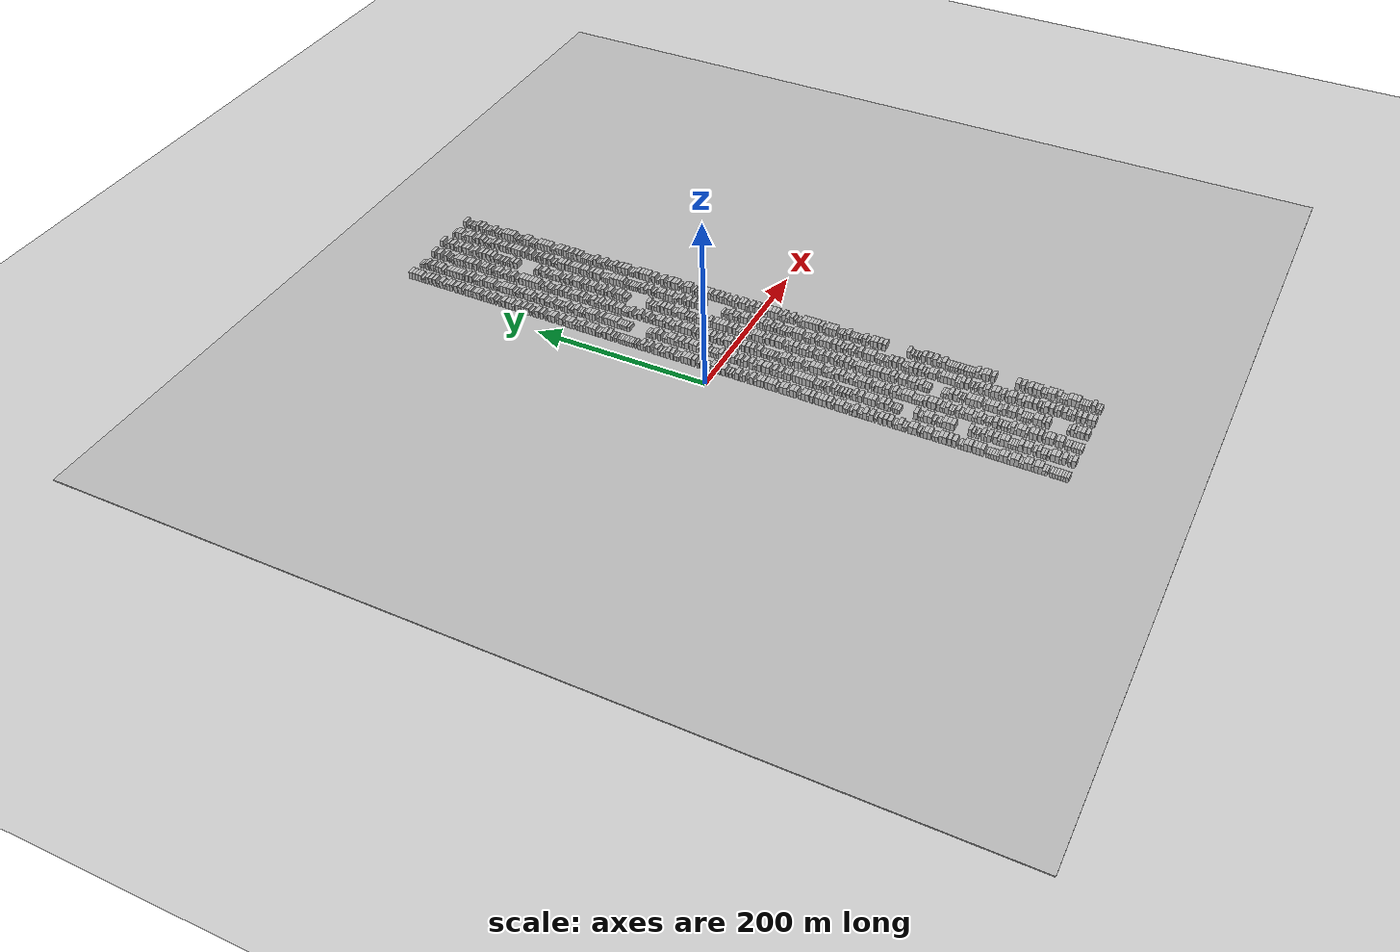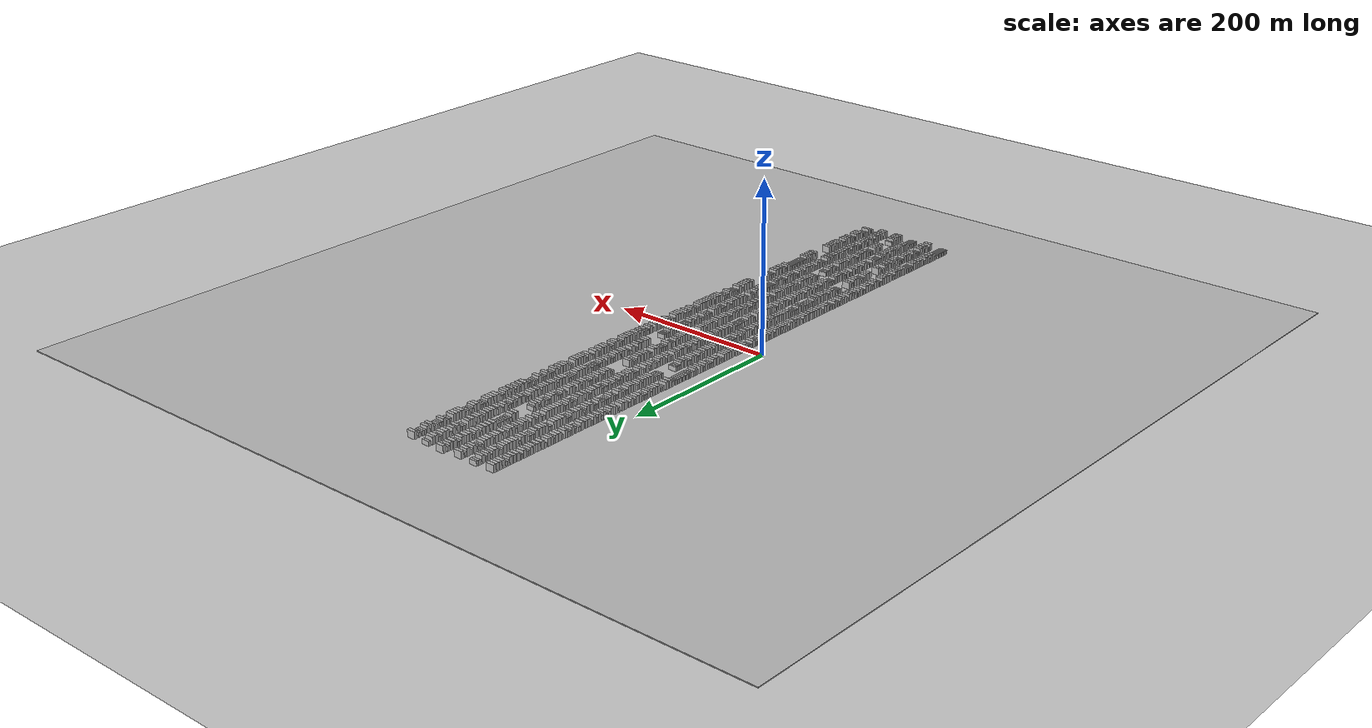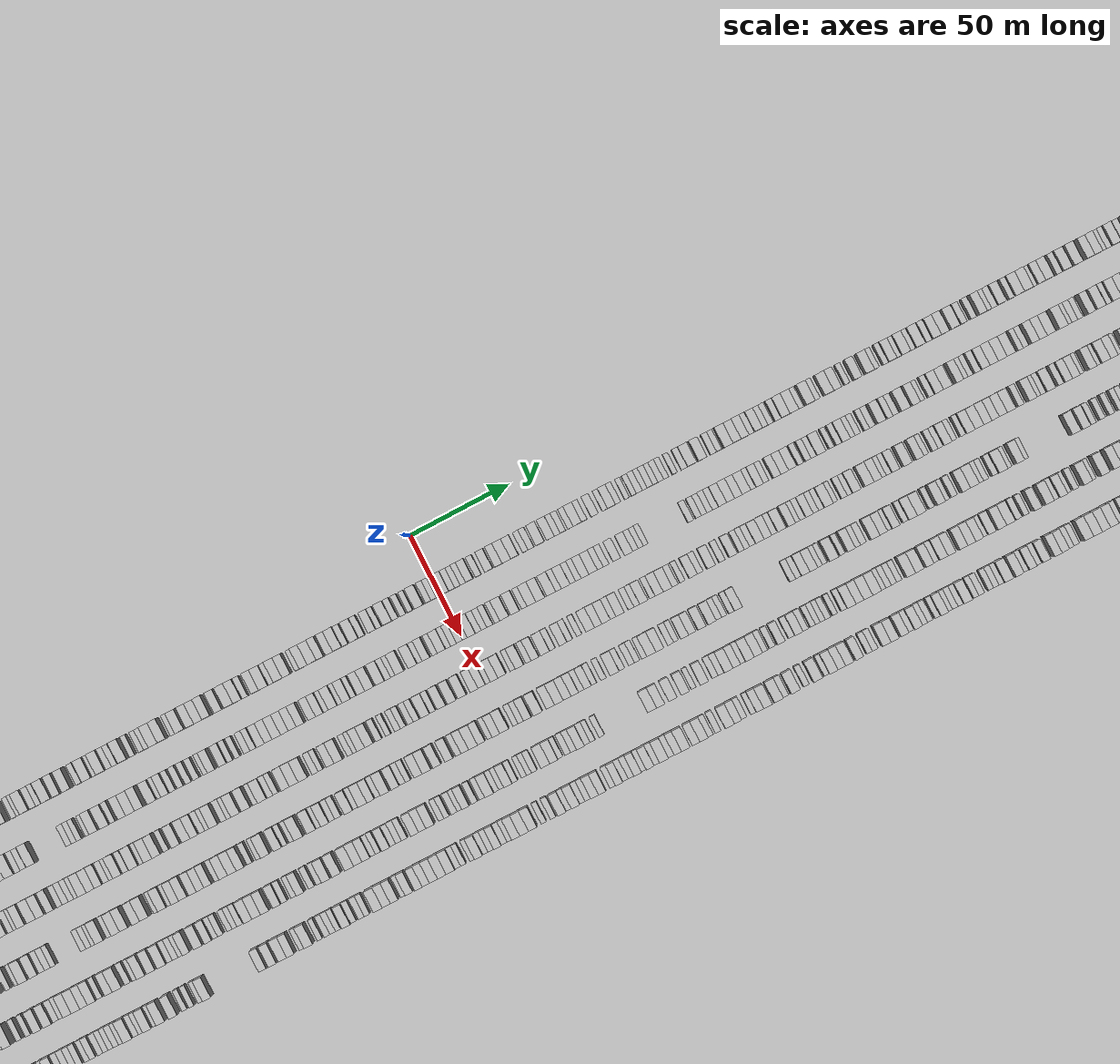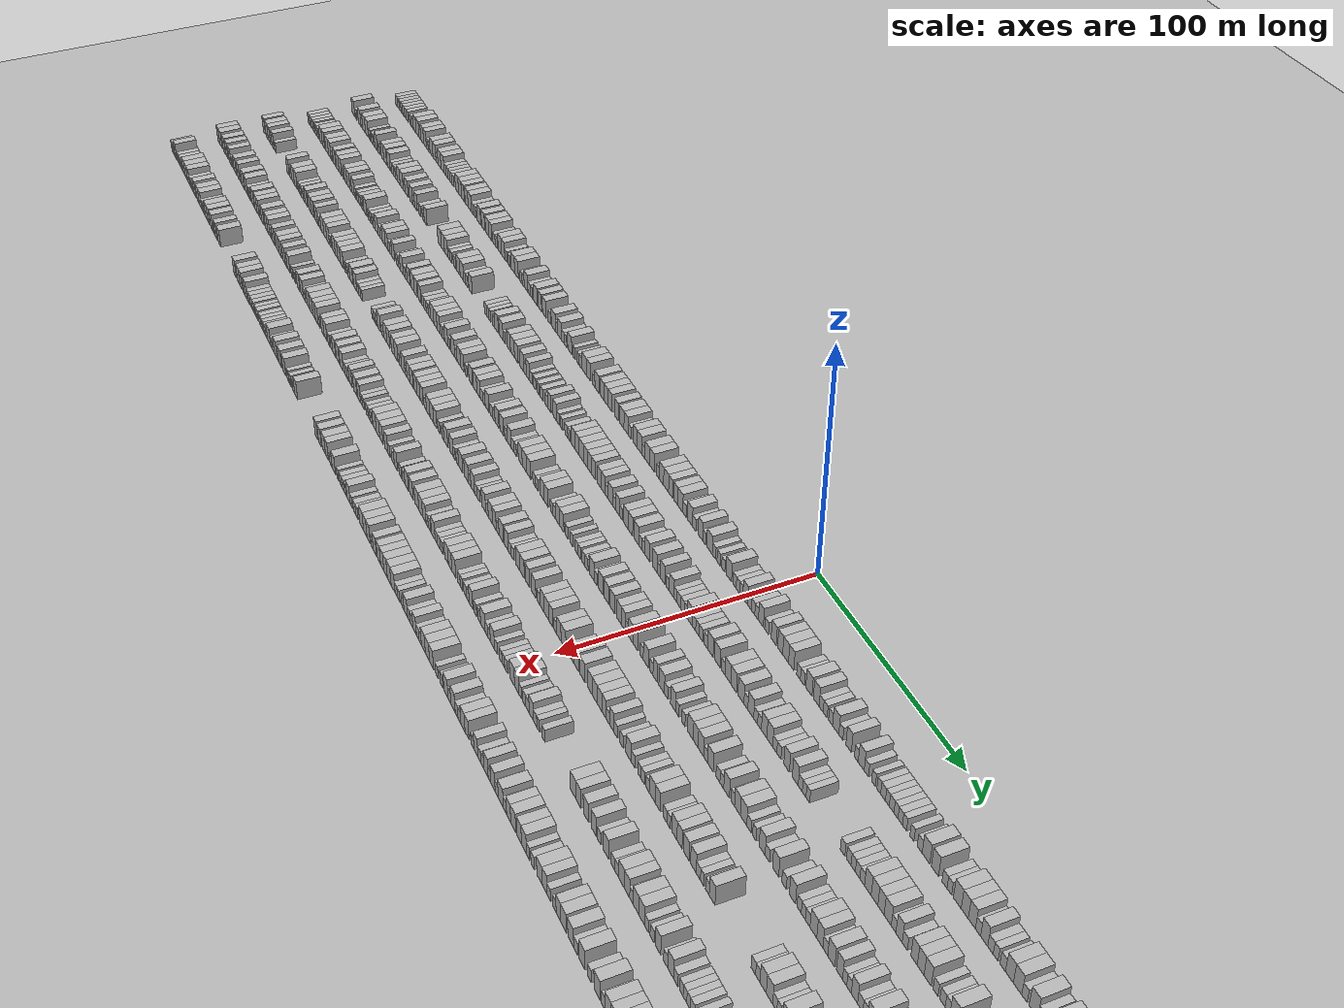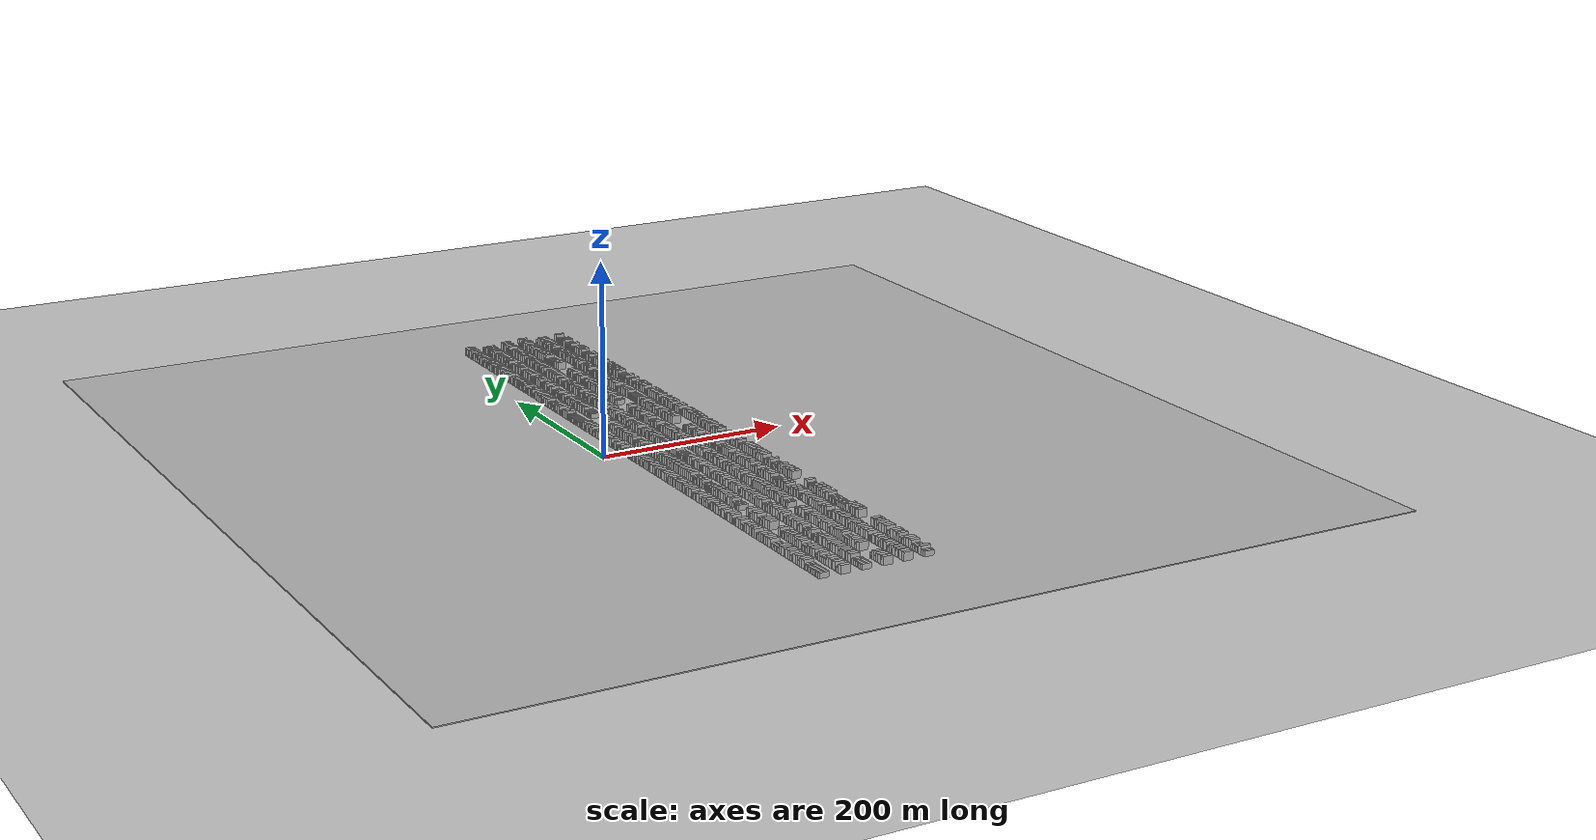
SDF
<?xml version="1.0" encoding="utf-8"?>

<sdf version="1.6">

   <world name="default">

      <gui fullscreen="0">

         <camera name="user_camera">

            <pose>-15 0 4.57585 0 0 0</pose>

            <view_controller>orbit</view_controller>

         </camera>

      </gui>

      <scene>

         <sky>

           <clouds>

             <speed>12</speed>

           </clouds>

         </sky>

         <ambient>0.4 0.4 0.4 1</ambient>

         <background>0.7 0.7 0.7 1</background>

         <shadows>1</shadows>

      </scene>

      <gravity>0 0 -9.8066</gravity>

      <magnetic_field>6e-06 2.3e-05 -4.2e-05</magnetic_field>

      <physics default="0" name="default_physics" type="ode">

         <ode>

            <solver>

               <type>quick</type>

               <iters>10</iters>

               <sor>1.0</sor>

               <use_dynamic_moi_rescaling>0</use_dynamic_moi_rescaling>

            </solver>

            <constraints>

               <cfm>0</cfm>

               <erp>0.2</erp>

               <contact_max_correcting_vel>100</contact_max_correcting_vel>

               <contact_surface_layer>0.001</contact_surface_layer>

            </constraints>

         </ode>

         <max_step_size>0.004</max_step_size>

         <real_time_factor>1</real_time_factor>

         <real_time_update_rate>250</real_time_update_rate>

      </physics>

      <light name="sun" type="directional">

         <cast_shadows>1</cast_shadows>

         <pose>0 0 10 0 0 0</pose>

         <diffuse>0.8 0.8 0.8 1</diffuse>

         <specular>0.2 0.2 0.2 1</specular>

         <attenuation>

            <range>1000</range>

            <constant>0.9</constant>

            <linear>0.01</linear>

            <quadratic>0.001</quadratic>

         </attenuation>

         <direction>-0.5 0.1 -0.9</direction>

      </light>

      <include>

         <name>ground_plane_1</name>

         <uri>model://HANNAS_ground_plane</uri>

         <pose>0 0 0  0 0 0</pose>

      </include>

      <include>

         <name>ground_plane_2</name>

         <uri>model://HANNAS_ground_plane</uri>

         <pose>100 0 0  0 0 0</pose>

      </include>

      <model name="building_1">

         <static>1</static>

         <pose frame="">25.0000 -378.5527 0 0.000000 0.000000 0.000000</pose>

         <link name="link">

            <pose frame="">0 0 3.00 0 0 0</pose>

            <collision name="collision">

               <geometry>

                  <box>

                     <size>10.0000 2.8945 6.0000</size>

                  </box>

               </geometry>

               <max_contacts>10</max_contacts>

               <surface>

                  <contact>

                     <ode/>

                  </contact>

                  <bounce/>

                  <friction>

                     <torsional>

                        <ode/>

                     </torsional>

                     <ode/>

                  </friction>

               </surface>

            </collision>

            <visual name="visual">

               <cast_shadows>0</cast_shadows>

               <geometry>

                  <box>

                     <size>10.0000 2.8945 6.0000</size>

                  </box>

               </geometry>

               <material>

                  <script>

                     <uri>model://HANNAS_wall/materials/scripts</uri>

                     <uri>model://HANNAS_wall/materials/textures</uri>

                     <name>vrc/HANNAS_wall</name>

                  </script>

               </material>

            </visual>

            <self_collide>0</self_collide>

            <enable_wind>0</enable_wind>

            <kinematic>0</kinematic>

         </link>

      </model>

      <model name="building_2">

         <static>1</static>

         <pose frame="">25.0000 -375.8927 0 0.000000 0.000000 0.000000</pose>

         <link name="link">

            <pose frame="">0 0 3.00 0 0 0</pose>

            <collision name="collision">

               <geometry>

                  <box>

                     <size>10.0000 2.4257 6.0000</size>

                  </box>

               </geometry>

               <max_contacts>10</max_contacts>

               <surface>

                  <contact>

                     <ode/>

                  </contact>

                  <bounce/>

                  <friction>

                     <torsional>

                        <ode/>

                     </torsional>

                     <ode/>

                  </friction>

               </surface>

            </collision>

            <visual name="visual">

               <cast_shadows>0</cast_shadows>

               <geometry>

                  <box>

                     <size>10.0000 2.4257 6.0000</size>

                  </box>

               </geometry>

               <material>

                  <script>

                     <uri>model://HANNAS_wall/materials/scripts</uri>

                     <uri>model://HANNAS_wall/materials/textures</uri>

                     <name>vrc/HANNAS_wall</name>

                  </script>

               </material>

            </visual>

            <self_collide>0</self_collide>

            <enable_wind>0</enable_wind>

            <kinematic>0</kinematic>

         </link>

      </model>

      <model name="building_3">

         <static>1</static>

         <pose frame="">25.0000 -373.3480 0 0.000000 0.000000 0.000000</pose>

         <link name="link">

            <pose frame="">0 0 3.00 0 0 0</pose>

            <collision name="collision">

               <geometry>

                  <box>

                     <size>10.0000 2.6636 6.0000</size>

                  </box>

               </geometry>

               <max_contacts>10</max_contacts>

               <surface>

                  <contact>

                     <ode/>

                  </contact>

                  <bounce/>

                  <friction>

                     <torsional>

                        <ode/>

                     </torsional>

                     <ode/>

                  </friction>

               </surface>

            </collision>

            <visual name="visual">

               <cast_shadows>0</cast_shadows>

               <geometry>

                  <box>

                     <size>10.0000 2.6636 6.0000</size>

                  </box>

               </geometry>

               <material>

                  <script>

                     <uri>model://HANNAS_wall/materials/scripts</uri>

                     <uri>model://HANNAS_wall/materials/textures</uri>

                     <name>vrc/HANNAS_wall</name>

                  </script>

               </material>

            </visual>

            <self_collide>0</self_collide>

            <enable_wind>0</enable_wind>

            <kinematic>0</kinematic>

         </link>

      </model>

      <model name="building_4">

         <static>1</static>

         <pose frame="">25.0000 -370.7058 0 0.000000 0.000000 0.000000</pose>

         <link name="link">

            <pose frame="">0 0 3.00 0 0 0</pose>

            <collision name="collision">

               <geometry>

                  <box>

                     <size>10.0000 2.6210 6.0000</size>

                  </box>

               </geometry>

               <max_contacts>10</max_contacts>

               <surface>

                  <contact>

                     <ode/>

                  </contact>

                  <bounce/>

                  <friction>

                     <torsional>

                        <ode/>

                     </torsional>

                     <ode/>

                  </friction>

               </surface>

            </collision>

            <visual name="visual">

               <cast_shadows>0</cast_shadows>

               <geometry>

                  <box>

                     <size>10.0000 2.6210 6.0000</size>

                  </box>

               </geometry>

               <material>

                  <script>

                     <uri>model://HANNAS_wall/materials/scripts</uri>

                     <uri>model://HANNAS_wall/materials/textures</uri>

                     <name>vrc/HANNAS_wall</name>

                  </script>

               </material>

            </visual>

            <self_collide>0</self_collide>

            <enable_wind>0</enable_wind>

            <kinematic>0</kinematic>

         </link>

      </model>

      <model name="building_5">

         <static>1</static>

         <pose frame="">25.0000 -367.9241 0 0.000000 0.000000 0.000000</pose>

         <link name="link">

            <pose frame="">0 0 3.00 0 0 0</pose>

            <collision name="collision">

               <geometry>

                  <box>

                     <size>10.0000 2.9424 6.0000</size>

                  </box>

               </geometry>

               <max_contacts>10</max_contacts>

               <surface>

                  <contact>

                     <ode/>

                  </contact>

                  <bounce/>

                  <friction>

                     <torsional>

                        <ode/>

                     </torsional>

                     <ode/>

                  </friction>

               </surface>

            </collision>

            <visual name="visual">

               <cast_shadows>0</cast_shadows>

               <geometry>

                  <box>

                     <size>10.0000 2.9424 6.0000</size>

                  </box>

               </geometry>

               <material>

                  <script>

                     <uri>model://HANNAS_wall/materials/scripts</uri>

                     <uri>model://HANNAS_wall/materials/textures</uri>

                     <name>vrc/HANNAS_wall</name>

                  </script>

               </material>

            </visual>

            <self_collide>0</self_collide>

            <enable_wind>0</enable_wind>

            <kinematic>0</kinematic>

         </link>

      </model>

      <model name="building_6">

         <static>1</static>

         <pose frame="">25.0000 -365.0623 0 0.000000 0.000000 0.000000</pose>

         <link name="link">

            <pose frame="">0 0 3.00 0 0 0</pose>

            <collision name="collision">

               <geometry>

                  <box>

                     <size>10.0000 2.7812 6.0000</size>

                  </box>

               </geometry>

               <max_contacts>10</max_contacts>

               <surface>

                  <contact>

                     <ode/>

                  </contact>

                  <bounce/>

                  <friction>

                     <torsional>

                        <ode/>

                     </torsional>

                     <ode/>

                  </friction>

               </surface>

            </collision>

            <visual name="visual">

               <cast_shadows>0</cast_shadows>

               <geometry>

                  <box>

                     <size>10.0000 2.7812 6.0000</size>

                  </box>

               </geometry>

               <material>

                  <script>

                     <uri>model://HANNAS_wall/materials/scripts</uri>

                     <uri>model://HANNAS_wall/materials/textures</uri>

                     <name>vrc/HANNAS_wall</name>

                  </script>

               </material>

            </visual>

            <self_collide>0</self_collide>

            <enable_wind>0</enable_wind>

            <kinematic>0</kinematic>

         </link>

      </model>

      <model name="building_7">

         <static>1</static>

         <pose frame="">25.0000 -362.2778 0 0.000000 0.000000 0.000000</pose>

         <link name="link">

            <pose frame="">0 0 3.00 0 0 0</pose>

            <collision name="collision">

               <geometry>

                  <box>

                     <size>10.0000 2.7878 6.0000</size>

                  </box>

               </geometry>

               <max_contacts>10</max_contacts>

               <surface>

                  <contact>

                     <ode/>

                  </contact>

                  <bounce/>

                  <friction>

                     <torsional>

                        <ode/>

                     </torsional>

                     <ode/>

                  </friction>

               </surface>

            </collision>

            <visual name="visual">

               <cast_shadows>0</cast_shadows>

               <geometry>

                  <box>

                     <size>10.0000 2.7878 6.0000</size>

                  </box>

               </geometry>

               <material>

                  <script>

                     <uri>model://HANNAS_wall/materials/scripts</uri>

                     <uri>model://HANNAS_wall/materials/textures</uri>

                     <name>vrc/HANNAS_wall</name>

                  </script>

               </material>

            </visual>

            <self_collide>0</self_collide>

            <enable_wind>0</enable_wind>

            <kinematic>0</kinematic>

         </link>

      </model>

      <model name="building_8">

         <static>1</static>

         <pose frame="">25.0000 -357.6160 0 0.000000 0.000000 0.000000</pose>

         <link name="link">

            <pose frame="">0 0 3.00 0 0 0</pose>

            <collision name="collision">

               <geometry>

                  <box>

                     <size>10.0000 2.5359 6.0000</size>

                  </box>

               </geometry>

               <max_contacts>10</max_contacts>

               <surface>

                  <contact>

                     <ode/>

                  </contact>

                  <bounce/>

                  <friction>

                     <torsional>

                        <ode/>

                     </torsional>

                     <ode/>

                  </friction>

               </surface>

            </collision>

            <visual name="visual">

               <cast_shadows>0</cast_shadows>

               <geometry>

                  <box>

                     <size>10.0000 2.5359 6.0000</size>

                  </box>

               </geometry>

               <material>

                  <script>

                     <uri>model://HANNAS_wall/materials/scripts</uri>

                     <uri>model://HANNAS_wall/materials/textures</uri>

                     <name>vrc/HANNAS_wall</name>

                  </script>

               </material>

            </visual>

            <self_collide>0</self_collide>

            <enable_wind>0</enable_wind>

            <kinematic>0</kinematic>

         </link>

      </model>

      <model name="building_9">

         <static>1</static>

         <pose frame="">25.0000 -354.8854 0 0.000000 0.000000 0.000000</pose>

         <link name="link">

            <pose frame="">0 0 3.00 0 0 0</pose>

            <collision name="collision">

               <geometry>

                  <box>

                     <size>10.0000 2.9253 6.0000</size>

                  </box>

               </geometry>

               <max_contacts>10</max_contacts>

               <surface>

                  <contact>

                     <ode/>

                  </contact>

                  <bounce/>

                  <friction>

                     <torsional>

                        <ode/>

                     </torsional>

                     <ode/>

                  </friction>

               </surface>

            </collision>

            <visual name="visual">

               <cast_shadows>0</cast_shadows>

               <geometry>

                  <box>

                     <size>10.0000 2.9253 6.0000</size>

                  </box>

               </geometry>

               <material>

                  <script>

                     <uri>model://HANNAS_wall/materials/scripts</uri>

                     <uri>model://HANNAS_wall/materials/textures</uri>

                     <name>vrc/HANNAS_wall</name>

                  </script>

               </material>

            </visual>

            <self_collide>0</self_collide>

            <enable_wind>0</enable_wind>

            <kinematic>0</kinematic>

         </link>

      </model>

      <model name="building_10">

         <static>1</static>

         <pose frame="">25.0000 -351.4184 0 0.000000 0.000000 0.000000</pose>

         <link name="link">

            <pose frame="">0 0 4.50 0 0 0</pose>

            <collision name="collision">

               <geometry>

                  <box>

                     <size>10.0000 4.0086 9.0000</size>

                  </box>

               </geometry>

               <max_contacts>10</max_contacts>

               <surface>

                  <contact>

                     <ode/>

                  </contact>

                  <bounce/>

                  <friction>

                     <torsional>

                        <ode/>

                     </torsional>

                     <ode/>

                  </friction>

               </surface>

            </collision>

            <visual name="visual">

               <cast_shadows>0</cast_shadows>

               <geometry>

                  <box>

                     <size>10.0000 4.0086 9.0000</size>

                  </box>

               </geometry>

               <material>

                  <script>

                     <uri>model://HANNAS_wall/materials/scripts</uri>

                     <uri>model://HANNAS_wall/materials/textures</uri>

                     <name>vrc/HANNAS_wall</name>

                  </script>

               </material>

            </visual>

            <self_collide>0</self_collide>

            <enable_wind>0</enable_wind>

            <kinematic>0</kinematic>

         </link>

      </model>

      <model name="building_11">

         <static>1</static>

         <pose frame="">25.0000 -347.2415 0 0.000000 0.000000 0.000000</pose>

         <link name="link">

            <pose frame="">0 0 4.50 0 0 0</pose>

            <collision name="collision">

               <geometry>

                  <box>

                     <size>10.0000 4.3452 9.0000</size>

                  </box>

               </geometry>

               <max_contacts>10</max_contacts>

               <surface>

                  <contact>

                     <ode/>

                  </contact>

                  <bounce/>

                  <friction>

                     <torsional>

                        <ode/>

                     </torsional>

                     <ode/>

                  </friction>

               </surface>

            </collision>

            <visual name="visual">

               <cast_shadows>0</cast_shadows>

               <geometry>

                  <box>

                     <size>10.0000 4.3452 9.0000</size>

                  </box>

               </geometry>

               <material>

                  <script>

                     <uri>model://HANNAS_wall/materials/scripts</uri>

                     <uri>model://HANNAS_wall/materials/textures</uri>

                     <name>vrc/HANNAS_wall</name>

                  </script>

               </material>

            </visual>

            <self_collide>0</self_collide>

            <enable_wind>0</enable_wind>

            <kinematic>0</kinematic>

         </link>

      </model>

      <model name="building_12">

         <static>1</static>

         <pose frame="">25.0000 -343.7800 0 0.000000 0.000000 0.000000</pose>

         <link name="link">

            <pose frame="">0 0 3.00 0 0 0</pose>

            <collision name="collision">

               <geometry>

                  <box>

                     <size>10.0000 2.5778 6.0000</size>

                  </box>

               </geometry>

               <max_contacts>10</max_contacts>

               <surface>

                  <contact>

                     <ode/>

                  </contact>

                  <bounce/>

                  <friction>

                     <torsional>

                        <ode/>

                     </torsional>

                     <ode/>

                  </friction>

               </surface>

            </collision>

            <visual name="visual">

               <cast_shadows>0</cast_shadows>

               <geometry>

                  <box>

                     <size>10.0000 2.5778 6.0000</size>

                  </box>

               </geometry>

               <material>

                  <script>

                     <uri>model://HANNAS_wall/materials/scripts</uri>

                     <uri>model://HANNAS_wall/materials/textures</uri>

                     <name>vrc/HANNAS_wall</name>

                  </script>

               </material>

            </visual>

            <self_collide>0</self_collide>

            <enable_wind>0</enable_wind>

            <kinematic>0</kinematic>

         </link>

      </model>

      <model name="building_13">

         <static>1</static>

         <pose frame="">25.0000 -340.4681 0 0.000000 0.000000 0.000000</pose>

         <link name="link">

            <pose frame="">0 0 4.50 0 0 0</pose>

            <collision name="collision">

               <geometry>

                  <box>

                     <size>10.0000 4.0458 9.0000</size>

                  </box>

               </geometry>

               <max_contacts>10</max_contacts>

               <surface>

                  <contact>

                     <ode/>

                  </contact>

                  <bounce/>

                  <friction>

                     <torsional>

                        <ode/>

                     </torsional>

                     <ode/>

                  </friction>

               </surface>

            </collision>

            <visual name="visual">

               <cast_shadows>0</cast_shadows>

               <geometry>

                  <box>

                     <size>10.0000 4.0458 9.0000</size>

                  </box>

               </geometry>

               <material>

                  <script>

                     <uri>model://HANNAS_wall/materials/scripts</uri>

                     <uri>model://HANNAS_wall/materials/textures</uri>

                     <name>vrc/HANNAS_wall</name>

                  </script>

               </material>

            </visual>

            <self_collide>0</self_collide>

            <enable_wind>0</enable_wind>

            <kinematic>0</kinematic>

         </link>

      </model>

      <model name="building_14">

         <static>1</static>

         <pose frame="">25.0000 -336.5463 0 0.000000 0.000000 0.000000</pose>

         <link name="link">

            <pose frame="">0 0 4.50 0 0 0</pose>

            <collision name="collision">

               <geometry>

                  <box>

                     <size>10.0000 3.7979 9.0000</size>

                  </box>

               </geometry>

               <max_contacts>10</max_contacts>

               <surface>

                  <contact>

                     <ode/>

                  </contact>

                  <bounce/>

                  <friction>

                     <torsional>

                        <ode/>

                     </torsional>

                     <ode/>

                  </friction>

               </surface>

            </collision>

            <visual name="visual">

               <cast_shadows>0</cast_shadows>

               <geometry>

                  <box>

                     <size>10.0000 3.7979 9.0000</size>

                  </box>

               </geometry>

               <material>

                  <script>

                     <uri>model://HANNAS_wall/materials/scripts</uri>

                     <uri>model://HANNAS_wall/materials/textures</uri>

                     <name>vrc/HANNAS_wall</name>

                  </script>

               </material>

            </visual>

            <self_collide>0</self_collide>

            <enable_wind>0</enable_wind>

            <kinematic>0</kinematic>

         </link>

      </model>

      <model name="building_15">

         <static>1</static>

         <pose frame="">25.0000 -333.3192 0 0.000000 0.000000 0.000000</pose>

         <link name="link">

            <pose frame="">0 0 3.00 0 0 0</pose>

            <collision name="collision">

               <geometry>

                  <box>

                     <size>10.0000 2.6563 6.0000</size>

                  </box>

               </geometry>

               <max_contacts>10</max_contacts>

               <surface>

                  <contact>

                     <ode/>

                  </contact>

                  <bounce/>

                  <friction>

                     <torsional>

                        <ode/>

                     </torsional>

                     <ode/>

                  </friction>

               </surface>

            </collision>

            <visual name="visual">

               <cast_shadows>0</cast_shadows>

               <geometry>

                  <box>

                     <size>10.0000 2.6563 6.0000</size>

                  </box>

               </geometry>

               <material>

                  <script>

                     <uri>model://HANNAS_wall/materials/scripts</uri>

                     <uri>model://HANNAS_wall/materials/textures</uri>

                     <name>vrc/HANNAS_wall</name>

                  </script>

               </material>

            </visual>

            <self_collide>0</self_collide>

            <enable_wind>0</enable_wind>

            <kinematic>0</kinematic>

         </link>

      </model>

      <model name="building_16">

         <static>1</static>

         <pose frame="">25.0000 -330.6986 0 0.000000 0.000000 0.000000</pose>

         <link name="link">

            <pose frame="">0 0 3.00 0 0 0</pose>

            <collision name="collision">

               <geometry>

                  <box>

                     <size>10.0000 2.5851 6.0000</size>

                  </box>

               </geometry>

               <max_contacts>10</max_contacts>

               <surface>

                  <contact>

                     <ode/>

                  </contact>

                  <bounce/>

                  <friction>

                     <torsional>

                        <ode/>

                     </torsional>

                     <ode/>

                  </friction>

               </surface>

            </collision>

            <visual name="visual">

               <cast_shadows>0</cast_shadows>

               <geometry>

                  <box>

                     <size>10.0000 2.5851 6.0000</size>

                  </box>

               </geometry>

               <material>

                  <script>

                     <uri>model://HANNAS_wall/materials/scripts</uri>

                     <uri>model://HANNAS_wall/materials/textures</uri>

                     <name>vrc/HANNAS_wall</name>

                  </script>

               </material>

            </visual>

            <self_collide>0</self_collide>

            <enable_wind>0</enable_wind>

            <kinematic>0</kinematic>

         </link>

      </model>

      <model name="building_17">

         <static>1</static>

         <pose frame="">25.0000 -327.3460 0 0.000000 0.000000 0.000000</pose>

         <link name="link">

            <pose frame="">0 0 4.50 0 0 0</pose>

            <collision name="collision">

               <geometry>

                  <box>

                     <size>10.0000 4.1200 9.0000</size>

                  </box>

               </geometry>

               <max_contacts>10</max_contacts>

               <surface>

                  <contact>

                     <ode/>

                  </contact>

                  <bounce/>

                  <friction>

                     <torsional>

                        <ode/>

                     </torsional>

                     <ode/>

                  </friction>

               </surface>

            </collision>

            <visual name="visual">

               <cast_shadows>0</cast_shadows>

               <geometry>

                  <box>

                     <size>10.0000 4.1200 9.0000</size>

                  </box>

               </geometry>

               <material>

                  <script>

                     <uri>model://HANNAS_wall/materials/scripts</uri>

                     <uri>model://HANNAS_wall/materials/textures</uri>

                     <name>vrc/HANNAS_wall</name>

                  </script>

               </material>

            </visual>

            <self_collide>0</self_collide>

            <enable_wind>0</enable_wind>

            <kinematic>0</kinematic>

         </link>

      </model>

      <model name="building_18">

         <static>1</static>

         <pose frame="">25.0000 -323.1835 0 0.000000 0.000000 0.000000</pose>

         <link name="link">

            <pose frame="">0 0 4.50 0 0 0</pose>

            <collision name="collision">

               <geometry>

                  <box>

                     <size>10.0000 4.2051 9.0000</size>

                  </box>

               </geometry>

               <max_contacts>10</max_contacts>

               <surface>

                  <contact>

                     <ode/>

                  </contact>

                  <bounce/>

                  <friction>

                     <torsional>

                        <ode/>

                     </torsional>

                     <ode/>

                  </friction>

               </surface>

            </collision>

            <visual name="visual">

               <cast_shadows>0</cast_shadows>

               <geometry>

                  <box>

                     <size>10.0000 4.2051 9.0000</size>

                  </box>

               </geometry>

               <material>

                  <script>

                     <uri>model://HANNAS_wall/materials/scripts</uri>

                     <uri>model://HANNAS_wall/materials/textures</uri>

                     <name>vrc/HANNAS_wall</name>

                  </script>

               </material>

            </visual>

            <self_collide>0</self_collide>

            <enable_wind>0</enable_wind>

            <kinematic>0</kinematic>

         </link>

      </model>

      <model name="building_19">

         <static>1</static>

         <pose frame="">25.0000 -319.6114 0 0.000000 0.000000 0.000000</pose>

         <link name="link">

            <pose frame="">0 0 3.00 0 0 0</pose>

            <collision name="collision">

               <geometry>

                  <box>

                     <size>10.0000 2.9392 6.0000</size>

                  </box>

               </geometry>

               <max_contacts>10</max_contacts>

               <surface>

                  <contact>

                     <ode/>

                  </contact>

                  <bounce/>

                  <friction>

                     <torsional>

                        <ode/>

                     </torsional>

                     <ode/>

                  </friction>

               </surface>

            </collision>

            <visual name="visual">

               <cast_shadows>0</cast_shadows>

               <geometry>

                  <box>

                     <size>10.0000 2.9392 6.0000</size>

                  </box>

               </geometry>

               <material>

                  <script>

                     <uri>model://HANNAS_wall/materials/scripts</uri>

                     <uri>model://HANNAS_wall/materials/textures</uri>

                     <name>vrc/HANNAS_wall</name>

                  </script>

               </material>

            </visual>

            <self_collide>0</self_collide>

            <enable_wind>0</enable_wind>

            <kinematic>0</kinematic>

         </link>

      </model>

      <model name="building_20">

         <static>1</static>

         <pose frame="">25.0000 -316.0873 0 0.000000 0.000000 0.000000</pose>

         <link name="link">

            <pose frame="">0 0 4.50 0 0 0</pose>

            <collision name="collision">

               <geometry>

                  <box>

                     <size>10.0000 4.1088 9.0000</size>

                  </box>

               </geometry>

               <max_contacts>10</max_contacts>

               <surface>

                  <contact>

                     <ode/>

                  </contact>

                  <bounce/>

                  <friction>

                     <torsional>

                        <ode/>

                     </torsional>

                     <ode/>

                  </friction>

               </surface>

            </collision>

            <visual name="visual">

               <cast_shadows>0</cast_shadows>

               <geometry>

                  <box>

                     <size>10.0000 4.1088 9.0000</size>

                  </box>

               </geometry>

               <material>

                  <script>

                     <uri>model://HANNAS_wall/materials/scripts</uri>

                     <uri>model://HANNAS_wall/materials/textures</uri>

                     <name>vrc/HANNAS_wall</name>

                  </script>

               </material>

            </visual>

            <self_collide>0</self_collide>

            <enable_wind>0</enable_wind>

            <kinematic>0</kinematic>

         </link>

      </model>

      <model name="building_21">

         <static>1</static>

         <pose frame="">25.0000 -311.8550 0 0.000000 0.000000 0.000000</pose>

         <link name="link">

            <pose frame="">0 0 4.50 0 0 0</pose>

            <collision name="collision">

               <geometry>

                  <box>

                     <size>10.0000 4.3558 9.0000</size>

                  </box>

               </geometry>

               <max_contacts>10</max_contacts>

               <surface>

                  <contact>

                     <ode/>

                  </contact>

                  <bounce/>

                  <friction>

                     <torsional>

                        <ode/>

                     </torsional>

                     <ode/>

                  </friction>

               </surface>

            </collision>

            <visual name="visual">

               <cast_shadows>0</cast_shadows>

               <geometry>

                  <box>

                     <size>10.0000 4.3558 9.0000</size>

                  </box>

               </geometry>

               <material>

                  <script>

                     <uri>model://HANNAS_wall/materials/scripts</uri>

                     <uri>model://HANNAS_wall/materials/textures</uri>

                     <name>vrc/HANNAS_wall</name>

                  </script>

               </material>

            </visual>

            <self_collide>0</self_collide>

            <enable_wind>0</enable_wind>

            <kinematic>0</kinematic>

         </link>

      </model>

      <model name="building_22">

         <static>1</static>

         <pose frame="">25.0000 -308.3280 0 0.000000 0.000000 0.000000</pose>

         <link name="link">

            <pose frame="">0 0 3.00 0 0 0</pose>

            <collision name="collision">

               <geometry>

                  <box>

                     <size>10.0000 2.6983 6.0000</size>

                  </box>

               </geometry>

               <max_contacts>10</max_contacts>

               <surface>

                  <contact>

                     <ode/>

                  </contact>

                  <bounce/>

                  <friction>

                     <torsional>

                        <ode/>

                     </torsional>

                     <ode/>

                  </friction>

               </surface>

            </collision>

            <visual name="visual">

               <cast_shadows>0</cast_shadows>

               <geometry>

                  <box>

                     <size>10.0000 2.6983 6.0000</size>

                  </box>

               </geometry>

               <material>

                  <script>

                     <uri>model://HANNAS_wall/materials/scripts</uri>

                     <uri>model://HANNAS_wall/materials/textures</uri>

                     <name>vrc/HANNAS_wall</name>

                  </script>

               </material>

            </visual>

            <self_collide>0</self_collide>

            <enable_wind>0</enable_wind>

            <kinematic>0</kinematic>

         </link>

      </model>

      <model name="building_23">

         <static>1</static>

         <pose frame="">25.0000 -305.6368 0 0.000000 0.000000 0.000000</pose>

         <link name="link">

            <pose frame="">0 0 3.00 0 0 0</pose>

            <collision name="collision">

               <geometry>

                  <box>

                     <size>10.0000 2.6841 6.0000</size>

                  </box>

               </geometry>

               <max_contacts>10</max_contacts>

               <surface>

                  <contact>

                     <ode/>

                  </contact>

                  <bounce/>

                  <friction>

                     <torsional>

                        <ode/>

                     </torsional>

                     <ode/>

                  </friction>

               </surface>

            </collision>

            <visual name="visual">

               <cast_shadows>0</cast_shadows>

               <geometry>

                  <box>

                     <size>10.0000 2.6841 6.0000</size>

                  </box>

               </geometry>

               <material>

                  <script>

                     <uri>model://HANNAS_wall/materials/scripts</uri>

                     <uri>model://HANNAS_wall/materials/textures</uri>

                     <name>vrc/HANNAS_wall</name>

                  </script>

               </material>

            </visual>

            <self_collide>0</self_collide>

            <enable_wind>0</enable_wind>

            <kinematic>0</kinematic>

         </link>

      </model>

      <model name="building_24">

         <static>1</static>

         <pose frame="">25.0000 -302.9718 0 0.000000 0.000000 0.000000</pose>

         <link name="link">

            <pose frame="">0 0 3.00 0 0 0</pose>

            <collision name="collision">

               <geometry>

                  <box>

                     <size>10.0000 2.6458 6.0000</size>

                  </box>

               </geometry>

               <max_contacts>10</max_contacts>

               <surface>

                  <contact>

                     <ode/>

                  </contact>

                  <bounce/>

                  <friction>

                     <torsional>

                        <ode/>

                     </torsional>

                     <ode/>

                  </friction>

               </surface>

            </collision>

            <visual name="visual">

               <cast_shadows>0</cast_shadows>

               <geometry>

                  <box>

                     <size>10.0000 2.6458 6.0000</size>

                  </box>

               </geometry>

               <material>

                  <script>

                     <uri>model://HANNAS_wall/materials/scripts</uri>

                     <uri>model://HANNAS_wall/materials/textures</uri>

                     <name>vrc/HANNAS_wall</name>

                  </script>

               </material>

            </visual>

            <self_collide>0</self_collide>

            <enable_wind>0</enable_wind>

            <kinematic>0</kinematic>

         </link>

      </model>

      <model name="building_25">

         <static>1</static>

         <pose frame="">25.0000 -300.2924 0 0.000000 0.000000 0.000000</pose>

         <link name="link">

            <pose frame="">0 0 3.00 0 0 0</pose>

            <collision name="collision">

               <geometry>

                  <box>

                     <size>10.0000 2.7131 6.0000</size>

                  </box>

               </geometry>

               <max_contacts>10</max_contacts>

               <surface>

                  <contact>

                     <ode/>

                  </contact>

                  <bounce/>

                  <friction>

                     <torsional>

                        <ode/>

                     </torsional>

                     <ode/>

                  </friction>

               </surface>

            </collision>

            <visual name="visual">

               <cast_shadows>0</cast_shadows>

               <geometry>

                  <box>

                     <size>10.0000 2.7131 6.0000</size>

                  </box>

               </geometry>

               <material>

                  <script>

                     <uri>model://HANNAS_wall/materials/scripts</uri>

                     <uri>model://HANNAS_wall/materials/textures</uri>

                     <name>vrc/HANNAS_wall</name>

                  </script>

               </material>

            </visual>

            <self_collide>0</self_collide>

            <enable_wind>0</enable_wind>

            <kinematic>0</kinematic>

         </link>

      </model>

      <model name="building_26">

         <static>1</static>

         <pose frame="">25.0000 -297.5843 0 0.000000 0.000000 0.000000</pose>

         <link name="link">

            <pose frame="">0 0 3.00 0 0 0</pose>

            <collision name="collision">

               <geometry>

                  <box>

                     <size>10.0000 2.7031 6.0000</size>

                  </box>

               </geometry>

               <max_contacts>10</max_contacts>

               <surface>

                  <contact>

                     <ode/>

                  </contact>

                  <bounce/>

                  <friction>

                     <torsional>

                        <ode/>

                     </torsional>

                     <ode/>

                  </friction>

               </surface>

            </collision>

            <visual name="visual">

               <cast_shadows>0</cast_shadows>

               <geometry>

                  <box>

                     <size>10.0000 2.7031 6.0000</size>

                  </box>

               </geometry>

               <material>

                  <script>

                     <uri>model://HANNAS_wall/materials/scripts</uri>

                     <uri>model://HANNAS_wall/materials/textures</uri>

                     <name>vrc/HANNAS_wall</name>

                  </script>

               </material>

            </visual>

            <self_collide>0</self_collide>

            <enable_wind>0</enable_wind>

            <kinematic>0</kinematic>

         </link>

      </model>

      <model name="building_27">

         <static>1</static>

         <pose frame="">25.0000 -292.1914 0 0.000000 0.000000 0.000000</pose>

         <link name="link">

            <pose frame="">0 0 4.50 0 0 0</pose>

            <collision name="collision">

               <geometry>

                  <box>

                     <size>10.0000 4.0827 9.0000</size>

                  </box>

               </geometry>

               <max_contacts>10</max_contacts>

               <surface>

                  <contact>

                     <ode/>

                  </contact>

                  <bounce/>

                  <friction>

                     <torsional>

                        <ode/>

                     </torsional>

                     <ode/>

                  </friction>

               </surface>

            </collision>

            <visual name="visual">

               <cast_shadows>0</cast_shadows>

               <geometry>

                  <box>

                     <size>10.0000 4.0827 9.0000</size>

                  </box>

               </geometry>

               <material>

                  <script>

                     <uri>model://HANNAS_wall/materials/scripts</uri>

                     <uri>model://HANNAS_wall/materials/textures</uri>

                     <name>vrc/HANNAS_wall</name>

                  </script>

               </material>

            </visual>

            <self_collide>0</self_collide>

            <enable_wind>0</enable_wind>

            <kinematic>0</kinematic>

         </link>

      </model>

      <model name="building_28">

         <static>1</static>

         <pose frame="">25.0000 -288.1037 0 0.000000 0.000000 0.000000</pose>

         <link name="link">

            <pose frame="">0 0 4.50 0 0 0</pose>

            <collision name="collision">

               <geometry>

                  <box>

                     <size>10.0000 4.0928 9.0000</size>

                  </box>

               </geometry>

               <max_contacts>10</max_contacts>

               <surface>

                  <contact>

                     <ode/>

                  </contact>

                  <bounce/>

                  <friction>

                     <torsional>

                        <ode/>

                     </torsional>

                     <ode/>

                  </friction>

               </surface>

            </collision>

            <visual name="visual">

               <cast_shadows>0</cast_shadows>

               <geometry>

                  <box>

                     <size>10.0000 4.0928 9.0000</size>

                  </box>

               </geometry>

               <material>

                  <script>

                     <uri>model://HANNAS_wall/materials/scripts</uri>

                     <uri>model://HANNAS_wall/materials/textures</uri>

                     <name>vrc/HANNAS_wall</name>

                  </script>

               </material>

            </visual>

            <self_collide>0</self_collide>

            <enable_wind>0</enable_wind>

            <kinematic>0</kinematic>

         </link>

      </model>

      <model name="building_29">

         <static>1</static>

         <pose frame="">25.0000 -284.2097 0 0.000000 0.000000 0.000000</pose>

         <link name="link">

            <pose frame="">0 0 4.50 0 0 0</pose>

            <collision name="collision">

               <geometry>

                  <box>

                     <size>10.0000 3.6951 9.0000</size>

                  </box>

               </geometry>

               <max_contacts>10</max_contacts>

               <surface>

                  <contact>

                     <ode/>

                  </contact>

                  <bounce/>

                  <friction>

                     <torsional>

                        <ode/>

                     </torsional>

                     <ode/>

                  </friction>

               </surface>

            </collision>

            <visual name="visual">

               <cast_shadows>0</cast_shadows>

               <geometry>

                  <box>

                     <size>10.0000 3.6951 9.0000</size>

                  </box>

               </geometry>

               <material>

                  <script>

                     <uri>model://HANNAS_wall/materials/scripts</uri>

                     <uri>model://HANNAS_wall/materials/textures</uri>

                     <name>vrc/HANNAS_wall</name>

                  </script>

               </material>

            </visual>

            <self_collide>0</self_collide>

            <enable_wind>0</enable_wind>

            <kinematic>0</kinematic>

         </link>

      </model>

      <model name="building_30">

         <static>1</static>

         <pose frame="">25.0000 -279.4100 0 0.000000 0.000000 0.000000</pose>

         <link name="link">

            <pose frame="">0 0 4.50 0 0 0</pose>

            <collision name="collision">

               <geometry>

                  <box>

                     <size>10.0000 3.9044 9.0000</size>

                  </box>

               </geometry>

               <max_contacts>10</max_contacts>

               <surface>

                  <contact>

                     <ode/>

                  </contact>

                  <bounce/>

                  <friction>

                     <torsional>

                        <ode/>

                     </torsional>

                     <ode/>

                  </friction>

               </surface>

            </collision>

            <visual name="visual">

               <cast_shadows>0</cast_shadows>

               <geometry>

                  <box>

                     <size>10.0000 3.9044 9.0000</size>

                  </box>

               </geometry>

               <material>

                  <script>

                     <uri>model://HANNAS_wall/materials/scripts</uri>

                     <uri>model://HANNAS_wall/materials/textures</uri>

                     <name>vrc/HANNAS_wall</name>

                  </script>

               </material>

            </visual>

            <self_collide>0</self_collide>

            <enable_wind>0</enable_wind>

            <kinematic>0</kinematic>

         </link>

      </model>

      <model name="building_31">

         <static>1</static>

         <pose frame="">25.0000 -275.3593 0 0.000000 0.000000 0.000000</pose>

         <link name="link">

            <pose frame="">0 0 4.50 0 0 0</pose>

            <collision name="collision">

               <geometry>

                  <box>

                     <size>10.0000 4.1969 9.0000</size>

                  </box>

               </geometry>

               <max_contacts>10</max_contacts>

               <surface>

                  <contact>

                     <ode/>

                  </contact>

                  <bounce/>

                  <friction>

                     <torsional>

                        <ode/>

                     </torsional>

                     <ode/>

                  </friction>

               </surface>

            </collision>

            <visual name="visual">

               <cast_shadows>0</cast_shadows>

               <geometry>

                  <box>

                     <size>10.0000 4.1969 9.0000</size>

                  </box>

               </geometry>

               <material>

                  <script>

                     <uri>model://HANNAS_wall/materials/scripts</uri>

                     <uri>model://HANNAS_wall/materials/textures</uri>

                     <name>vrc/HANNAS_wall</name>

                  </script>

               </material>

            </visual>

            <self_collide>0</self_collide>

            <enable_wind>0</enable_wind>

            <kinematic>0</kinematic>

         </link>

      </model>

      <model name="building_32">

         <static>1</static>

         <pose frame="">25.0000 -271.7904 0 0.000000 0.000000 0.000000</pose>

         <link name="link">

            <pose frame="">0 0 3.00 0 0 0</pose>

            <collision name="collision">

               <geometry>

                  <box>

                     <size>10.0000 2.9410 6.0000</size>

                  </box>

               </geometry>

               <max_contacts>10</max_contacts>

               <surface>

                  <contact>

                     <ode/>

                  </contact>

                  <bounce/>

                  <friction>

                     <torsional>

                        <ode/>

                     </torsional>

                     <ode/>

                  </friction>

               </surface>

            </collision>

            <visual name="visual">

               <cast_shadows>0</cast_shadows>

               <geometry>

                  <box>

                     <size>10.0000 2.9410 6.0000</size>

                  </box>

               </geometry>

               <material>

                  <script>

                     <uri>model://HANNAS_wall/materials/scripts</uri>

                     <uri>model://HANNAS_wall/materials/textures</uri>

                     <name>vrc/HANNAS_wall</name>

                  </script>

               </material>

            </visual>

            <self_collide>0</self_collide>

            <enable_wind>0</enable_wind>

            <kinematic>0</kinematic>

         </link>

      </model>

      <model name="building_33">

         <static>1</static>

         <pose frame="">25.0000 -268.9199 0 0.000000 0.000000 0.000000</pose>

         <link name="link">

            <pose frame="">0 0 3.00 0 0 0</pose>

            <collision name="collision">

               <geometry>

                  <box>

                     <size>10.0000 2.8000 6.0000</size>

                  </box>

               </geometry>

               <max_contacts>10</max_contacts>

               <surface>

                  <contact>

                     <ode/>

                  </contact>

                  <bounce/>

                  <friction>

                     <torsional>

                        <ode/>

                     </torsional>

                     <ode/>

                  </friction>

               </surface>

            </collision>

            <visual name="visual">

               <cast_shadows>0</cast_shadows>

               <geometry>

                  <box>

                     <size>10.0000 2.8000 6.0000</size>

                  </box>

               </geometry>

               <material>

                  <script>

                     <uri>model://HANNAS_wall/materials/scripts</uri>

                     <uri>model://HANNAS_wall/materials/textures</uri>

                     <name>vrc/HANNAS_wall</name>

                  </script>

               </material>

            </visual>

            <self_collide>0</self_collide>

            <enable_wind>0</enable_wind>

            <kinematic>0</kinematic>

         </link>

      </model>

      <model name="building_34">

         <static>1</static>

         <pose frame="">25.0000 -263.3124 0 0.000000 0.000000 0.000000</pose>

         <link name="link">

            <pose frame="">0 0 4.50 0 0 0</pose>

            <collision name="collision">

               <geometry>

                  <box>

                     <size>10.0000 4.4150 9.0000</size>

                  </box>

               </geometry>

               <max_contacts>10</max_contacts>

               <surface>

                  <contact>

                     <ode/>

                  </contact>

                  <bounce/>

                  <friction>

                     <torsional>

                        <ode/>

                     </torsional>

                     <ode/>

                  </friction>

               </surface>

            </collision>

            <visual name="visual">

               <cast_shadows>0</cast_shadows>

               <geometry>

                  <box>

                     <size>10.0000 4.4150 9.0000</size>

                  </box>

               </geometry>

               <material>

                  <script>

                     <uri>model://HANNAS_wall/materials/scripts</uri>

                     <uri>model://HANNAS_wall/materials/textures</uri>

                     <name>vrc/HANNAS_wall</name>

                  </script>

               </material>

            </visual>

            <self_collide>0</self_collide>

            <enable_wind>0</enable_wind>

            <kinematic>0</kinematic>

         </link>

      </model>

      <model name="building_35">

         <static>1</static>

         <pose frame="">25.0000 -258.0931 0 0.000000 0.000000 0.000000</pose>

         <link name="link">

            <pose frame="">0 0 4.50 0 0 0</pose>

            <collision name="collision">

               <geometry>

                  <box>

                     <size>10.0000 4.0236 9.0000</size>

                  </box>

               </geometry>

               <max_contacts>10</max_contacts>

               <surface>

                  <contact>

                     <ode/>

                  </contact>

                  <bounce/>

                  <friction>

                     <torsional>

                        <ode/>

                     </torsional>

                     <ode/>

                  </friction>

               </surface>

            </collision>

            <visual name="visual">

               <cast_shadows>0</cast_shadows>

               <geometry>

                  <box>

                     <size>10.0000 4.0236 9.0000</size>

                  </box>

               </geometry>

               <material>

                  <script>

                     <uri>model://HANNAS_wall/materials/scripts</uri>

                     <uri>model://HANNAS_wall/materials/textures</uri>

                     <name>vrc/HANNAS_wall</name>

                  </script>

               </material>

            </visual>

            <self_collide>0</self_collide>

            <enable_wind>0</enable_wind>

            <kinematic>0</kinematic>

         </link>

      </model>

      <model name="building_36">

         <static>1</static>

         <pose frame="">25.0000 -252.9448 0 0.000000 0.000000 0.000000</pose>

         <link name="link">

            <pose frame="">0 0 4.50 0 0 0</pose>

            <collision name="collision">

               <geometry>

                  <box>

                     <size>10.0000 4.2731 9.0000</size>

                  </box>

               </geometry>

               <max_contacts>10</max_contacts>

               <surface>

                  <contact>

                     <ode/>

                  </contact>

                  <bounce/>

                  <friction>

                     <torsional>

                        <ode/>

                     </torsional>

                     <ode/>

                  </friction>

               </surface>

            </collision>

            <visual name="visual">

               <cast_shadows>0</cast_shadows>

               <geometry>

                  <box>

                     <size>10.0000 4.2731 9.0000</size>

                  </box>

               </geometry>

               <material>

                  <script>

                     <uri>model://HANNAS_wall/materials/scripts</uri>

                     <uri>model://HANNAS_wall/materials/textures</uri>

                     <name>vrc/HANNAS_wall</name>

                  </script>

               </material>

            </visual>

            <self_collide>0</self_collide>

            <enable_wind>0</enable_wind>

            <kinematic>0</kinematic>

         </link>

      </model>

      <model name="building_37">

         <static>1</static>

         <pose frame="">25.0000 -248.9344 0 0.000000 0.000000 0.000000</pose>

         <link name="link">

            <pose frame="">0 0 4.50 0 0 0</pose>

            <collision name="collision">

               <geometry>

                  <box>

                     <size>10.0000 3.7476 9.0000</size>

                  </box>

               </geometry>

               <max_contacts>10</max_contacts>

               <surface>

                  <contact>

                     <ode/>

                  </contact>

                  <bounce/>

                  <friction>

                     <torsional>

                        <ode/>

                     </torsional>

                     <ode/>

                  </friction>

               </surface>

            </collision>

            <visual name="visual">

               <cast_shadows>0</cast_shadows>

               <geometry>

                  <box>

                     <size>10.0000 3.7476 9.0000</size>

                  </box>

               </geometry>

               <material>

                  <script>

                     <uri>model://HANNAS_wall/materials/scripts</uri>

                     <uri>model://HANNAS_wall/materials/textures</uri>

                     <name>vrc/HANNAS_wall</name>

                  </script>

               </material>

            </visual>

            <self_collide>0</self_collide>

            <enable_wind>0</enable_wind>

            <kinematic>0</kinematic>

         </link>

      </model>

      <model name="building_38">

         <static>1</static>

         <pose frame="">25.0000 -244.5937 0 0.000000 0.000000 0.000000</pose>

         <link name="link">

            <pose frame="">0 0 3.00 0 0 0</pose>

            <collision name="collision">

               <geometry>

                  <box>

                     <size>10.0000 2.9339 6.0000</size>

                  </box>

               </geometry>

               <max_contacts>10</max_contacts>

               <surface>

                  <contact>

                     <ode/>

                  </contact>

                  <bounce/>

                  <friction>

                     <torsional>

                        <ode/>

                     </torsional>

                     <ode/>

                  </friction>

               </surface>

            </collision>

            <visual name="visual">

               <cast_shadows>0</cast_shadows>

               <geometry>

                  <box>

                     <size>10.0000 2.9339 6.0000</size>

                  </box>

               </geometry>

               <material>

                  <script>

                     <uri>model://HANNAS_wall/materials/scripts</uri>

                     <uri>model://HANNAS_wall/materials/textures</uri>

                     <name>vrc/HANNAS_wall</name>

                  </script>

               </material>

            </visual>

            <self_collide>0</self_collide>

            <enable_wind>0</enable_wind>

            <kinematic>0</kinematic>

         </link>

      </model>

      <model name="building_39">

         <static>1</static>

         <pose frame="">25.0000 -241.7820 0 0.000000 0.000000 0.000000</pose>

         <link name="link">

            <pose frame="">0 0 3.00 0 0 0</pose>

            <collision name="collision">

               <geometry>

                  <box>

                     <size>10.0000 2.6894 6.0000</size>

                  </box>

               </geometry>

               <max_contacts>10</max_contacts>

               <surface>

                  <contact>

                     <ode/>

                  </contact>

                  <bounce/>

                  <friction>

                     <torsional>

                        <ode/>

                     </torsional>

                     <ode/>

                  </friction>

               </surface>

            </collision>

            <visual name="visual">

               <cast_shadows>0</cast_shadows>

               <geometry>

                  <box>

                     <size>10.0000 2.6894 6.0000</size>

                  </box>

               </geometry>

               <material>

                  <script>

                     <uri>model://HANNAS_wall/materials/scripts</uri>

                     <uri>model://HANNAS_wall/materials/textures</uri>

                     <name>vrc/HANNAS_wall</name>

                  </script>

               </material>

            </visual>

            <self_collide>0</self_collide>

            <enable_wind>0</enable_wind>

            <kinematic>0</kinematic>

         </link>

      </model>

      <model name="building_40">

         <static>1</static>

         <pose frame="">25.0000 -237.3961 0 0.000000 0.000000 0.000000</pose>

         <link name="link">

            <pose frame="">0 0 4.50 0 0 0</pose>

            <collision name="collision">

               <geometry>

                  <box>

                     <size>10.0000 4.0824 9.0000</size>

                  </box>

               </geometry>

               <max_contacts>10</max_contacts>

               <surface>

                  <contact>

                     <ode/>

                  </contact>

                  <bounce/>

                  <friction>

                     <torsional>

                        <ode/>

                     </torsional>

                     <ode/>

                  </friction>

               </surface>

            </collision>

            <visual name="visual">

               <cast_shadows>0</cast_shadows>

               <geometry>

                  <box>

                     <size>10.0000 4.0824 9.0000</size>

                  </box>

               </geometry>

               <material>

                  <script>

                     <uri>model://HANNAS_wall/materials/scripts</uri>

                     <uri>model://HANNAS_wall/materials/textures</uri>

                     <name>vrc/HANNAS_wall</name>

                  </script>

               </material>

            </visual>

            <self_collide>0</self_collide>

            <enable_wind>0</enable_wind>

            <kinematic>0</kinematic>

         </link>

      </model>

      <model name="building_41">

         <static>1</static>

         <pose frame="">25.0000 -233.3007 0 0.000000 0.000000 0.000000</pose>

         <link name="link">

            <pose frame="">0 0 4.50 0 0 0</pose>

            <collision name="collision">

               <geometry>

                  <box>

                     <size>10.0000 4.1085 9.0000</size>

                  </box>

               </geometry>

               <max_contacts>10</max_contacts>

               <surface>

                  <contact>

                     <ode/>

                  </contact>

                  <bounce/>

                  <friction>

                     <torsional>

                        <ode/>

                     </torsional>

                     <ode/>

                  </friction>

               </surface>

            </collision>

            <visual name="visual">

               <cast_shadows>0</cast_shadows>

               <geometry>

                  <box>

                     <size>10.0000 4.1085 9.0000</size>

                  </box>

               </geometry>

               <material>

                  <script>

                     <uri>model://HANNAS_wall/materials/scripts</uri>

                     <uri>model://HANNAS_wall/materials/textures</uri>

                     <name>vrc/HANNAS_wall</name>

                  </script>

               </material>

            </visual>

            <self_collide>0</self_collide>

            <enable_wind>0</enable_wind>

            <kinematic>0</kinematic>

         </link>

      </model>

      <model name="building_42">

         <static>1</static>

         <pose frame="">25.0000 -229.8728 0 0.000000 0.000000 0.000000</pose>

         <link name="link">

            <pose frame="">0 0 3.00 0 0 0</pose>

            <collision name="collision">

               <geometry>

                  <box>

                     <size>10.0000 2.7473 6.0000</size>

                  </box>

               </geometry>

               <max_contacts>10</max_contacts>

               <surface>

                  <contact>

                     <ode/>

                  </contact>

                  <bounce/>

                  <friction>

                     <torsional>

                        <ode/>

                     </torsional>

                     <ode/>

                  </friction>

               </surface>

            </collision>

            <visual name="visual">

               <cast_shadows>0</cast_shadows>

               <geometry>

                  <box>

                     <size>10.0000 2.7473 6.0000</size>

                  </box>

               </geometry>

               <material>

                  <script>

                     <uri>model://HANNAS_wall/materials/scripts</uri>

                     <uri>model://HANNAS_wall/materials/textures</uri>

                     <name>vrc/HANNAS_wall</name>

                  </script>

               </material>

            </visual>

            <self_collide>0</self_collide>

            <enable_wind>0</enable_wind>

            <kinematic>0</kinematic>

         </link>

      </model>

      <model name="building_43">

         <static>1</static>

         <pose frame="">25.0000 -226.1350 0 0.000000 0.000000 0.000000</pose>

         <link name="link">

            <pose frame="">0 0 3.00 0 0 0</pose>

            <collision name="collision">

               <geometry>

                  <box>

                     <size>10.0000 2.7282 6.0000</size>

                  </box>

               </geometry>

               <max_contacts>10</max_contacts>

               <surface>

                  <contact>

                     <ode/>

                  </contact>

                  <bounce/>

                  <friction>

                     <torsional>

                        <ode/>

                     </torsional>

                     <ode/>

                  </friction>

               </surface>

            </collision>

            <visual name="visual">

               <cast_shadows>0</cast_shadows>

               <geometry>

                  <box>

                     <size>10.0000 2.7282 6.0000</size>

                  </box>

               </geometry>

               <material>

                  <script>

                     <uri>model://HANNAS_wall/materials/scripts</uri>

                     <uri>model://HANNAS_wall/materials/textures</uri>

                     <name>vrc/HANNAS_wall</name>

                  </script>

               </material>

            </visual>

            <self_collide>0</self_collide>

            <enable_wind>0</enable_wind>

            <kinematic>0</kinematic>

         </link>

      </model>

      <model name="building_44">

         <static>1</static>

         <pose frame="">25.0000 -221.6078 0 0.000000 0.000000 0.000000</pose>

         <link name="link">

            <pose frame="">0 0 4.50 0 0 0</pose>

            <collision name="collision">

               <geometry>

                  <box>

                     <size>10.0000 4.3262 9.0000</size>

                  </box>

               </geometry>

               <max_contacts>10</max_contacts>

               <surface>

                  <contact>

                     <ode/>

                  </contact>

                  <bounce/>

                  <friction>

                     <torsional>

                        <ode/>

                     </torsional>

                     <ode/>

                  </friction>

               </surface>

            </collision>

            <visual name="visual">

               <cast_shadows>0</cast_shadows>

               <geometry>

                  <box>

                     <size>10.0000 4.3262 9.0000</size>

                  </box>

               </geometry>

               <material>

                  <script>

                     <uri>model://HANNAS_wall/materials/scripts</uri>

                     <uri>model://HANNAS_wall/materials/textures</uri>

                     <name>vrc/HANNAS_wall</name>

                  </script>

               </material>

            </visual>

            <self_collide>0</self_collide>

            <enable_wind>0</enable_wind>

            <kinematic>0</kinematic>

         </link>

      </model>

      <model name="building_45">

         <static>1</static>

         <pose frame="">25.0000 -217.2726 0 0.000000 0.000000 0.000000</pose>

         <link name="link">

            <pose frame="">0 0 4.50 0 0 0</pose>

            <collision name="collision">

               <geometry>

                  <box>

                     <size>10.0000 4.3444 9.0000</size>

                  </box>

               </geometry>

               <max_contacts>10</max_contacts>

               <surface>

                  <contact>

                     <ode/>

                  </contact>

                  <bounce/>

                  <friction>

                     <torsional>

                        <ode/>

                     </torsional>

                     <ode/>

                  </friction>

               </surface>

            </collision>

            <visual name="visual">

               <cast_shadows>0</cast_shadows>

               <geometry>

                  <box>

                     <size>10.0000 4.3444 9.0000</size>

                  </box>

               </geometry>

               <material>

                  <script>

                     <uri>model://HANNAS_wall/materials/scripts</uri>

                     <uri>model://HANNAS_wall/materials/textures</uri>

                     <name>vrc/HANNAS_wall</name>

                  </script>

               </material>

            </visual>

            <self_collide>0</self_collide>

            <enable_wind>0</enable_wind>

            <kinematic>0</kinematic>

         </link>

      </model>

      <model name="building_46">

         <static>1</static>

         <pose frame="">25.0000 -211.8780 0 0.000000 0.000000 0.000000</pose>

         <link name="link">

            <pose frame="">0 0 3.00 0 0 0</pose>

            <collision name="collision">

               <geometry>

                  <box>

                     <size>10.0000 2.4448 6.0000</size>

                  </box>

               </geometry>

               <max_contacts>10</max_contacts>

               <surface>

                  <contact>

                     <ode/>

                  </contact>

                  <bounce/>

                  <friction>

                     <torsional>

                        <ode/>

                     </torsional>

                     <ode/>

                  </friction>

               </surface>

            </collision>

            <visual name="visual">

               <cast_shadows>0</cast_shadows>

               <geometry>

                  <box>

                     <size>10.0000 2.4448 6.0000</size>

                  </box>

               </geometry>

               <material>

                  <script>

                     <uri>model://HANNAS_wall/materials/scripts</uri>

                     <uri>model://HANNAS_wall/materials/textures</uri>

                     <name>vrc/HANNAS_wall</name>

                  </script>

               </material>

            </visual>

            <self_collide>0</self_collide>

            <enable_wind>0</enable_wind>

            <kinematic>0</kinematic>

         </link>

      </model>

      <model name="building_47">

         <static>1</static>

         <pose frame="">25.0000 -209.4439 0 0.000000 0.000000 0.000000</pose>

         <link name="link">

            <pose frame="">0 0 3.00 0 0 0</pose>

            <collision name="collision">

               <geometry>

                  <box>

                     <size>10.0000 2.4233 6.0000</size>

                  </box>

               </geometry>

               <max_contacts>10</max_contacts>

               <surface>

                  <contact>

                     <ode/>

                  </contact>

                  <bounce/>

                  <friction>

                     <torsional>

                        <ode/>

                     </torsional>

                     <ode/>

                  </friction>

               </surface>

            </collision>

            <visual name="visual">

               <cast_shadows>0</cast_shadows>

               <geometry>

                  <box>

                     <size>10.0000 2.4233 6.0000</size>

                  </box>

               </geometry>

               <material>

                  <script>

                     <uri>model://HANNAS_wall/materials/scripts</uri>

                     <uri>model://HANNAS_wall/materials/textures</uri>

                     <name>vrc/HANNAS_wall</name>

                  </script>

               </material>

            </visual>

            <self_collide>0</self_collide>

            <enable_wind>0</enable_wind>

            <kinematic>0</kinematic>

         </link>

      </model>

      <model name="building_48">

         <static>1</static>

         <pose frame="">25.0000 -206.0622 0 0.000000 0.000000 0.000000</pose>

         <link name="link">

            <pose frame="">0 0 4.50 0 0 0</pose>

            <collision name="collision">

               <geometry>

                  <box>

                     <size>10.0000 4.3401 9.0000</size>

                  </box>

               </geometry>

               <max_contacts>10</max_contacts>

               <surface>

                  <contact>

                     <ode/>

                  </contact>

                  <bounce/>

                  <friction>

                     <torsional>

                        <ode/>

                     </torsional>

                     <ode/>

                  </friction>

               </surface>

            </collision>

            <visual name="visual">

               <cast_shadows>0</cast_shadows>

               <geometry>

                  <box>

                     <size>10.0000 4.3401 9.0000</size>

                  </box>

               </geometry>

               <material>

                  <script>

                     <uri>model://HANNAS_wall/materials/scripts</uri>

                     <uri>model://HANNAS_wall/materials/textures</uri>

                     <name>vrc/HANNAS_wall</name>

                  </script>

               </material>

            </visual>

            <self_collide>0</self_collide>

            <enable_wind>0</enable_wind>

            <kinematic>0</kinematic>

         </link>

      </model>

      <model name="building_49">

         <static>1</static>

         <pose frame="">25.0000 -202.4076 0 0.000000 0.000000 0.000000</pose>

         <link name="link">

            <pose frame="">0 0 3.00 0 0 0</pose>

            <collision name="collision">

               <geometry>

                  <box>

                     <size>10.0000 2.9692 6.0000</size>

                  </box>

               </geometry>

               <max_contacts>10</max_contacts>

               <surface>

                  <contact>

                     <ode/>

                  </contact>

                  <bounce/>

                  <friction>

                     <torsional>

                        <ode/>

                     </torsional>

                     <ode/>

                  </friction>

               </surface>

            </collision>

            <visual name="visual">

               <cast_shadows>0</cast_shadows>

               <geometry>

                  <box>

                     <size>10.0000 2.9692 6.0000</size>

                  </box>

               </geometry>

               <material>

                  <script>

                     <uri>model://HANNAS_wall/materials/scripts</uri>

                     <uri>model://HANNAS_wall/materials/textures</uri>

                     <name>vrc/HANNAS_wall</name>

                  </script>

               </material>

            </visual>

            <self_collide>0</self_collide>

            <enable_wind>0</enable_wind>

            <kinematic>0</kinematic>

         </link>

      </model>

      <model name="building_50">

         <static>1</static>

         <pose frame="">25.0000 -199.6993 0 0.000000 0.000000 0.000000</pose>

         <link name="link">

            <pose frame="">0 0 3.00 0 0 0</pose>

            <collision name="collision">

               <geometry>

                  <box>

                     <size>10.0000 2.4473 6.0000</size>

                  </box>

               </geometry>

               <max_contacts>10</max_contacts>

               <surface>

                  <contact>

                     <ode/>

                  </contact>

                  <bounce/>

                  <friction>

                     <torsional>

                        <ode/>

                     </torsional>

                     <ode/>

                  </friction>

               </surface>

            </collision>

            <visual name="visual">

               <cast_shadows>0</cast_shadows>

               <geometry>

                  <box>

                     <size>10.0000 2.4473 6.0000</size>

                  </box>

               </geometry>

               <material>

                  <script>

                     <uri>model://HANNAS_wall/materials/scripts</uri>

                     <uri>model://HANNAS_wall/materials/textures</uri>

                     <name>vrc/HANNAS_wall</name>

                  </script>

               </material>

            </visual>

            <self_collide>0</self_collide>

            <enable_wind>0</enable_wind>

            <kinematic>0</kinematic>

         </link>

      </model>

      <model name="building_51">

         <static>1</static>

         <pose frame="">25.0000 -195.2450 0 0.000000 0.000000 0.000000</pose>

         <link name="link">

            <pose frame="">0 0 4.50 0 0 0</pose>

            <collision name="collision">

               <geometry>

                  <box>

                     <size>10.0000 4.4613 9.0000</size>

                  </box>

               </geometry>

               <max_contacts>10</max_contacts>

               <surface>

                  <contact>

                     <ode/>

                  </contact>

                  <bounce/>

                  <friction>

                     <torsional>

                        <ode/>

                     </torsional>

                     <ode/>

                  </friction>

               </surface>

            </collision>

            <visual name="visual">

               <cast_shadows>0</cast_shadows>

               <geometry>

                  <box>

                     <size>10.0000 4.4613 9.0000</size>

                  </box>

               </geometry>

               <material>

                  <script>

                     <uri>model://HANNAS_wall/materials/scripts</uri>

                     <uri>model://HANNAS_wall/materials/textures</uri>

                     <name>vrc/HANNAS_wall</name>

                  </script>

               </material>

            </visual>

            <self_collide>0</self_collide>

            <enable_wind>0</enable_wind>

            <kinematic>0</kinematic>

         </link>

      </model>

      <model name="building_52">

         <static>1</static>

         <pose frame="">25.0000 -190.1384 0 0.000000 0.000000 0.000000</pose>

         <link name="link">

            <pose frame="">0 0 4.50 0 0 0</pose>

            <collision name="collision">

               <geometry>

                  <box>

                     <size>10.0000 3.7520 9.0000</size>

                  </box>

               </geometry>

               <max_contacts>10</max_contacts>

               <surface>

                  <contact>

                     <ode/>

                  </contact>

                  <bounce/>

                  <friction>

                     <torsional>

                        <ode/>

                     </torsional>

                     <ode/>

                  </friction>

               </surface>

            </collision>

            <visual name="visual">

               <cast_shadows>0</cast_shadows>

               <geometry>

                  <box>

                     <size>10.0000 3.7520 9.0000</size>

                  </box>

               </geometry>

               <material>

                  <script>

                     <uri>model://HANNAS_wall/materials/scripts</uri>

                     <uri>model://HANNAS_wall/materials/textures</uri>

                     <name>vrc/HANNAS_wall</name>

                  </script>

               </material>

            </visual>

            <self_collide>0</self_collide>

            <enable_wind>0</enable_wind>

            <kinematic>0</kinematic>

         </link>

      </model>

      <model name="building_53">

         <static>1</static>

         <pose frame="">25.0000 -185.1746 0 0.000000 0.000000 0.000000</pose>

         <link name="link">

            <pose frame="">0 0 4.50 0 0 0</pose>

            <collision name="collision">

               <geometry>

                  <box>

                     <size>10.0000 4.1755 9.0000</size>

                  </box>

               </geometry>

               <max_contacts>10</max_contacts>

               <surface>

                  <contact>

                     <ode/>

                  </contact>

                  <bounce/>

                  <friction>

                     <torsional>

                        <ode/>

                     </torsional>

                     <ode/>

                  </friction>

               </surface>

            </collision>

            <visual name="visual">

               <cast_shadows>0</cast_shadows>

               <geometry>

                  <box>

                     <size>10.0000 4.1755 9.0000</size>

                  </box>

               </geometry>

               <material>

                  <script>

                     <uri>model://HANNAS_wall/materials/scripts</uri>

                     <uri>model://HANNAS_wall/materials/textures</uri>

                     <name>vrc/HANNAS_wall</name>

                  </script>

               </material>

            </visual>

            <self_collide>0</self_collide>

            <enable_wind>0</enable_wind>

            <kinematic>0</kinematic>

         </link>

      </model>

      <model name="building_54">

         <static>1</static>

         <pose frame="">25.0000 -179.7485 0 0.000000 0.000000 0.000000</pose>

         <link name="link">

            <pose frame="">0 0 3.00 0 0 0</pose>

            <collision name="collision">

               <geometry>

                  <box>

                     <size>10.0000 2.6768 6.0000</size>

                  </box>

               </geometry>

               <max_contacts>10</max_contacts>

               <surface>

                  <contact>

                     <ode/>

                  </contact>

                  <bounce/>

                  <friction>

                     <torsional>

                        <ode/>

                     </torsional>

                     <ode/>

                  </friction>

               </surface>

            </collision>

            <visual name="visual">

               <cast_shadows>0</cast_shadows>

               <geometry>

                  <box>

                     <size>10.0000 2.6768 6.0000</size>

                  </box>

               </geometry>

               <material>

                  <script>

                     <uri>model://HANNAS_wall/materials/scripts</uri>

                     <uri>model://HANNAS_wall/materials/textures</uri>

                     <name>vrc/HANNAS_wall</name>

                  </script>

               </material>

            </visual>

            <self_collide>0</self_collide>

            <enable_wind>0</enable_wind>

            <kinematic>0</kinematic>

         </link>

      </model>

      <model name="building_55">

         <static>1</static>

         <pose frame="">25.0000 -175.1819 0 0.000000 0.000000 0.000000</pose>

         <link name="link">

            <pose frame="">0 0 4.50 0 0 0</pose>

            <collision name="collision">

               <geometry>

                  <box>

                     <size>10.0000 4.4563 9.0000</size>

                  </box>

               </geometry>

               <max_contacts>10</max_contacts>

               <surface>

                  <contact>

                     <ode/>

                  </contact>

                  <bounce/>

                  <friction>

                     <torsional>

                        <ode/>

                     </torsional>

                     <ode/>

                  </friction>

               </surface>

            </collision>

            <visual name="visual">

               <cast_shadows>0</cast_shadows>

               <geometry>

                  <box>

                     <size>10.0000 4.4563 9.0000</size>

                  </box>

               </geometry>

               <material>

                  <script>

                     <uri>model://HANNAS_wall/materials/scripts</uri>

                     <uri>model://HANNAS_wall/materials/textures</uri>

                     <name>vrc/HANNAS_wall</name>

                  </script>

               </material>

            </visual>

            <self_collide>0</self_collide>

            <enable_wind>0</enable_wind>

            <kinematic>0</kinematic>

         </link>

      </model>

      <model name="building_56">

         <static>1</static>

         <pose frame="">25.0000 -171.7519 0 0.000000 0.000000 0.000000</pose>

         <link name="link">

            <pose frame="">0 0 3.00 0 0 0</pose>

            <collision name="collision">

               <geometry>

                  <box>

                     <size>10.0000 2.4038 6.0000</size>

                  </box>

               </geometry>

               <max_contacts>10</max_contacts>

               <surface>

                  <contact>

                     <ode/>

                  </contact>

                  <bounce/>

                  <friction>

                     <torsional>

                        <ode/>

                     </torsional>

                     <ode/>

                  </friction>

               </surface>

            </collision>

            <visual name="visual">

               <cast_shadows>0</cast_shadows>

               <geometry>

                  <box>

                     <size>10.0000 2.4038 6.0000</size>

                  </box>

               </geometry>

               <material>

                  <script>

                     <uri>model://HANNAS_wall/materials/scripts</uri>

                     <uri>model://HANNAS_wall/materials/textures</uri>

                     <name>vrc/HANNAS_wall</name>

                  </script>

               </material>

            </visual>

            <self_collide>0</self_collide>

            <enable_wind>0</enable_wind>

            <kinematic>0</kinematic>

         </link>

      </model>

      <model name="building_57">

         <static>1</static>

         <pose frame="">25.0000 -168.3546 0 0.000000 0.000000 0.000000</pose>

         <link name="link">

            <pose frame="">0 0 4.50 0 0 0</pose>

            <collision name="collision">

               <geometry>

                  <box>

                     <size>10.0000 4.3908 9.0000</size>

                  </box>

               </geometry>

               <max_contacts>10</max_contacts>

               <surface>

                  <contact>

                     <ode/>

                  </contact>

                  <bounce/>

                  <friction>

                     <torsional>

                        <ode/>

                     </torsional>

                     <ode/>

                  </friction>

               </surface>

            </collision>

            <visual name="visual">

               <cast_shadows>0</cast_shadows>

               <geometry>

                  <box>

                     <size>10.0000 4.3908 9.0000</size>

                  </box>

               </geometry>

               <material>

                  <script>

                     <uri>model://HANNAS_wall/materials/scripts</uri>

                     <uri>model://HANNAS_wall/materials/textures</uri>

                     <name>vrc/HANNAS_wall</name>

                  </script>

               </material>

            </visual>

            <self_collide>0</self_collide>

            <enable_wind>0</enable_wind>

            <kinematic>0</kinematic>

         </link>

      </model>

      <model name="building_58">

         <static>1</static>

         <pose frame="">25.0000 -164.7590 0 0.000000 0.000000 0.000000</pose>

         <link name="link">

            <pose frame="">0 0 3.00 0 0 0</pose>

            <collision name="collision">

               <geometry>

                  <box>

                     <size>10.0000 2.8005 6.0000</size>

                  </box>

               </geometry>

               <max_contacts>10</max_contacts>

               <surface>

                  <contact>

                     <ode/>

                  </contact>

                  <bounce/>

                  <friction>

                     <torsional>

                        <ode/>

                     </torsional>

                     <ode/>

                  </friction>

               </surface>

            </collision>

            <visual name="visual">

               <cast_shadows>0</cast_shadows>

               <geometry>

                  <box>

                     <size>10.0000 2.8005 6.0000</size>

                  </box>

               </geometry>

               <material>

                  <script>

                     <uri>model://HANNAS_wall/materials/scripts</uri>

                     <uri>model://HANNAS_wall/materials/textures</uri>

                     <name>vrc/HANNAS_wall</name>

                  </script>

               </material>

            </visual>

            <self_collide>0</self_collide>

            <enable_wind>0</enable_wind>

            <kinematic>0</kinematic>

         </link>

      </model>

      <model name="building_59">

         <static>1</static>

         <pose frame="">25.0000 -161.9979 0 0.000000 0.000000 0.000000</pose>

         <link name="link">

            <pose frame="">0 0 3.00 0 0 0</pose>

            <collision name="collision">

               <geometry>

                  <box>

                     <size>10.0000 2.7217 6.0000</size>

                  </box>

               </geometry>

               <max_contacts>10</max_contacts>

               <surface>

                  <contact>

                     <ode/>

                  </contact>

                  <bounce/>

                  <friction>

                     <torsional>

                        <ode/>

                     </torsional>

                     <ode/>

                  </friction>

               </surface>

            </collision>

            <visual name="visual">

               <cast_shadows>0</cast_shadows>

               <geometry>

                  <box>

                     <size>10.0000 2.7217 6.0000</size>

                  </box>

               </geometry>

               <material>

                  <script>

                     <uri>model://HANNAS_wall/materials/scripts</uri>

                     <uri>model://HANNAS_wall/materials/textures</uri>

                     <name>vrc/HANNAS_wall</name>

                  </script>

               </material>

            </visual>

            <self_collide>0</self_collide>

            <enable_wind>0</enable_wind>

            <kinematic>0</kinematic>

         </link>

      </model>

      <model name="building_60">

         <static>1</static>

         <pose frame="">25.0000 -157.4892 0 0.000000 0.000000 0.000000</pose>

         <link name="link">

            <pose frame="">0 0 4.50 0 0 0</pose>

            <collision name="collision">

               <geometry>

                  <box>

                     <size>10.0000 4.2958 9.0000</size>

                  </box>

               </geometry>

               <max_contacts>10</max_contacts>

               <surface>

                  <contact>

                     <ode/>

                  </contact>

                  <bounce/>

                  <friction>

                     <torsional>

                        <ode/>

                     </torsional>

                     <ode/>

                  </friction>

               </surface>

            </collision>

            <visual name="visual">

               <cast_shadows>0</cast_shadows>

               <geometry>

                  <box>

                     <size>10.0000 4.2958 9.0000</size>

                  </box>

               </geometry>

               <material>

                  <script>

                     <uri>model://HANNAS_wall/materials/scripts</uri>

                     <uri>model://HANNAS_wall/materials/textures</uri>

                     <name>vrc/HANNAS_wall</name>

                  </script>

               </material>

            </visual>

            <self_collide>0</self_collide>

            <enable_wind>0</enable_wind>

            <kinematic>0</kinematic>

         </link>

      </model>

      <model name="building_61">

         <static>1</static>

         <pose frame="">25.0000 -153.0648 0 0.000000 0.000000 0.000000</pose>

         <link name="link">

            <pose frame="">0 0 3.00 0 0 0</pose>

            <collision name="collision">

               <geometry>

                  <box>

                     <size>10.0000 2.5529 6.0000</size>

                  </box>

               </geometry>

               <max_contacts>10</max_contacts>

               <surface>

                  <contact>

                     <ode/>

                  </contact>

                  <bounce/>

                  <friction>

                     <torsional>

                        <ode/>

                     </torsional>

                     <ode/>

                  </friction>

               </surface>

            </collision>

            <visual name="visual">

               <cast_shadows>0</cast_shadows>

               <geometry>

                  <box>

                     <size>10.0000 2.5529 6.0000</size>

                  </box>

               </geometry>

               <material>

                  <script>

                     <uri>model://HANNAS_wall/materials/scripts</uri>

                     <uri>model://HANNAS_wall/materials/textures</uri>

                     <name>vrc/HANNAS_wall</name>

                  </script>

               </material>

            </visual>

            <self_collide>0</self_collide>

            <enable_wind>0</enable_wind>

            <kinematic>0</kinematic>

         </link>

      </model>

      <model name="building_62">

         <static>1</static>

         <pose frame="">25.0000 -148.5823 0 0.000000 0.000000 0.000000</pose>

         <link name="link">

            <pose frame="">0 0 3.00 0 0 0</pose>

            <collision name="collision">

               <geometry>

                  <box>

                     <size>10.0000 2.4120 6.0000</size>

                  </box>

               </geometry>

               <max_contacts>10</max_contacts>

               <surface>

                  <contact>

                     <ode/>

                  </contact>

                  <bounce/>

                  <friction>

                     <torsional>

                        <ode/>

                     </torsional>

                     <ode/>

                  </friction>

               </surface>

            </collision>

            <visual name="visual">

               <cast_shadows>0</cast_shadows>

               <geometry>

                  <box>

                     <size>10.0000 2.4120 6.0000</size>

                  </box>

               </geometry>

               <material>

                  <script>

                     <uri>model://HANNAS_wall/materials/scripts</uri>

                     <uri>model://HANNAS_wall/materials/textures</uri>

                     <name>vrc/HANNAS_wall</name>

                  </script>

               </material>

            </visual>

            <self_collide>0</self_collide>

            <enable_wind>0</enable_wind>

            <kinematic>0</kinematic>

         </link>

      </model>

      <model name="building_63">

         <static>1</static>

         <pose frame="">25.0000 -145.9216 0 0.000000 0.000000 0.000000</pose>

         <link name="link">

            <pose frame="">0 0 3.00 0 0 0</pose>

            <collision name="collision">

               <geometry>

                  <box>

                     <size>10.0000 2.9093 6.0000</size>

                  </box>

               </geometry>

               <max_contacts>10</max_contacts>

               <surface>

                  <contact>

                     <ode/>

                  </contact>

                  <bounce/>

                  <friction>

                     <torsional>

                        <ode/>

                     </torsional>

                     <ode/>

                  </friction>

               </surface>

            </collision>

            <visual name="visual">

               <cast_shadows>0</cast_shadows>

               <geometry>

                  <box>

                     <size>10.0000 2.9093 6.0000</size>

                  </box>

               </geometry>

               <material>

                  <script>

                     <uri>model://HANNAS_wall/materials/scripts</uri>

                     <uri>model://HANNAS_wall/materials/textures</uri>

                     <name>vrc/HANNAS_wall</name>

                  </script>

               </material>

            </visual>

            <self_collide>0</self_collide>

            <enable_wind>0</enable_wind>

            <kinematic>0</kinematic>

         </link>

      </model>

      <model name="building_64">

         <static>1</static>

         <pose frame="">25.0000 -142.2396 0 0.000000 0.000000 0.000000</pose>

         <link name="link">

            <pose frame="">0 0 4.50 0 0 0</pose>

            <collision name="collision">

               <geometry>

                  <box>

                     <size>10.0000 4.4547 9.0000</size>

                  </box>

               </geometry>

               <max_contacts>10</max_contacts>

               <surface>

                  <contact>

                     <ode/>

                  </contact>

                  <bounce/>

                  <friction>

                     <torsional>

                        <ode/>

                     </torsional>

                     <ode/>

                  </friction>

               </surface>

            </collision>

            <visual name="visual">

               <cast_shadows>0</cast_shadows>

               <geometry>

                  <box>

                     <size>10.0000 4.4547 9.0000</size>

                  </box>

               </geometry>

               <material>

                  <script>

                     <uri>model://HANNAS_wall/materials/scripts</uri>

                     <uri>model://HANNAS_wall/materials/textures</uri>

                     <name>vrc/HANNAS_wall</name>

                  </script>

               </material>

            </visual>

            <self_collide>0</self_collide>

            <enable_wind>0</enable_wind>

            <kinematic>0</kinematic>

         </link>

      </model>

      <model name="building_65">

         <static>1</static>

         <pose frame="">25.0000 -138.0126 0 0.000000 0.000000 0.000000</pose>

         <link name="link">

            <pose frame="">0 0 4.50 0 0 0</pose>

            <collision name="collision">

               <geometry>

                  <box>

                     <size>10.0000 3.9993 9.0000</size>

                  </box>

               </geometry>

               <max_contacts>10</max_contacts>

               <surface>

                  <contact>

                     <ode/>

                  </contact>

                  <bounce/>

                  <friction>

                     <torsional>

                        <ode/>

                     </torsional>

                     <ode/>

                  </friction>

               </surface>

            </collision>

            <visual name="visual">

               <cast_shadows>0</cast_shadows>

               <geometry>

                  <box>

                     <size>10.0000 3.9993 9.0000</size>

                  </box>

               </geometry>

               <material>

                  <script>

                     <uri>model://HANNAS_wall/materials/scripts</uri>

                     <uri>model://HANNAS_wall/materials/textures</uri>

                     <name>vrc/HANNAS_wall</name>

                  </script>

               </material>

            </visual>

            <self_collide>0</self_collide>

            <enable_wind>0</enable_wind>

            <kinematic>0</kinematic>

         </link>

      </model>

      <model name="building_66">

         <static>1</static>

         <pose frame="">25.0000 -132.6591 0 0.000000 0.000000 0.000000</pose>

         <link name="link">

            <pose frame="">0 0 3.00 0 0 0</pose>

            <collision name="collision">

               <geometry>

                  <box>

                     <size>10.0000 2.7078 6.0000</size>

                  </box>

               </geometry>

               <max_contacts>10</max_contacts>

               <surface>

                  <contact>

                     <ode/>

                  </contact>

                  <bounce/>

                  <friction>

                     <torsional>

                        <ode/>

                     </torsional>

                     <ode/>

                  </friction>

               </surface>

            </collision>

            <visual name="visual">

               <cast_shadows>0</cast_shadows>

               <geometry>

                  <box>

                     <size>10.0000 2.7078 6.0000</size>

                  </box>

               </geometry>

               <material>

                  <script>

                     <uri>model://HANNAS_wall/materials/scripts</uri>

                     <uri>model://HANNAS_wall/materials/textures</uri>

                     <name>vrc/HANNAS_wall</name>

                  </script>

               </material>

            </visual>

            <self_collide>0</self_collide>

            <enable_wind>0</enable_wind>

            <kinematic>0</kinematic>

         </link>

      </model>

      <model name="building_67">

         <static>1</static>

         <pose frame="">25.0000 -129.1272 0 0.000000 0.000000 0.000000</pose>

         <link name="link">

            <pose frame="">0 0 4.50 0 0 0</pose>

            <collision name="collision">

               <geometry>

                  <box>

                     <size>10.0000 4.3559 9.0000</size>

                  </box>

               </geometry>

               <max_contacts>10</max_contacts>

               <surface>

                  <contact>

                     <ode/>

                  </contact>

                  <bounce/>

                  <friction>

                     <torsional>

                        <ode/>

                     </torsional>

                     <ode/>

                  </friction>

               </surface>

            </collision>

            <visual name="visual">

               <cast_shadows>0</cast_shadows>

               <geometry>

                  <box>

                     <size>10.0000 4.3559 9.0000</size>

                  </box>

               </geometry>

               <material>

                  <script>

                     <uri>model://HANNAS_wall/materials/scripts</uri>

                     <uri>model://HANNAS_wall/materials/textures</uri>

                     <name>vrc/HANNAS_wall</name>

                  </script>

               </material>

            </visual>

            <self_collide>0</self_collide>

            <enable_wind>0</enable_wind>

            <kinematic>0</kinematic>

         </link>

      </model>

      <model name="building_68">

         <static>1</static>

         <pose frame="">25.0000 -123.9400 0 0.000000 0.000000 0.000000</pose>

         <link name="link">

            <pose frame="">0 0 4.50 0 0 0</pose>

            <collision name="collision">

               <geometry>

                  <box>

                     <size>10.0000 4.0185 9.0000</size>

                  </box>

               </geometry>

               <max_contacts>10</max_contacts>

               <surface>

                  <contact>

                     <ode/>

                  </contact>

                  <bounce/>

                  <friction>

                     <torsional>

                        <ode/>

                     </torsional>

                     <ode/>

                  </friction>

               </surface>

            </collision>

            <visual name="visual">

               <cast_shadows>0</cast_shadows>

               <geometry>

                  <box>

                     <size>10.0000 4.0185 9.0000</size>

                  </box>

               </geometry>

               <material>

                  <script>

                     <uri>model://HANNAS_wall/materials/scripts</uri>

                     <uri>model://HANNAS_wall/materials/textures</uri>

                     <name>vrc/HANNAS_wall</name>

                  </script>

               </material>

            </visual>

            <self_collide>0</self_collide>

            <enable_wind>0</enable_wind>

            <kinematic>0</kinematic>

         </link>

      </model>

      <model name="building_69">

         <static>1</static>

         <pose frame="">25.0000 -119.9293 0 0.000000 0.000000 0.000000</pose>

         <link name="link">

            <pose frame="">0 0 4.50 0 0 0</pose>

            <collision name="collision">

               <geometry>

                  <box>

                     <size>10.0000 4.0028 9.0000</size>

                  </box>

               </geometry>

               <max_contacts>10</max_contacts>

               <surface>

                  <contact>

                     <ode/>

                  </contact>

                  <bounce/>

                  <friction>

                     <torsional>

                        <ode/>

                     </torsional>

                     <ode/>

                  </friction>

               </surface>

            </collision>

            <visual name="visual">

               <cast_shadows>0</cast_shadows>

               <geometry>

                  <box>

                     <size>10.0000 4.0028 9.0000</size>

                  </box>

               </geometry>

               <material>

                  <script>

                     <uri>model://HANNAS_wall/materials/scripts</uri>

                     <uri>model://HANNAS_wall/materials/textures</uri>

                     <name>vrc/HANNAS_wall</name>

                  </script>

               </material>

            </visual>

            <self_collide>0</self_collide>

            <enable_wind>0</enable_wind>

            <kinematic>0</kinematic>

         </link>

      </model>

      <model name="building_70">

         <static>1</static>

         <pose frame="">25.0000 -115.9255 0 0.000000 0.000000 0.000000</pose>

         <link name="link">

            <pose frame="">0 0 4.50 0 0 0</pose>

            <collision name="collision">

               <geometry>

                  <box>

                     <size>10.0000 4.0048 9.0000</size>

                  </box>

               </geometry>

               <max_contacts>10</max_contacts>

               <surface>

                  <contact>

                     <ode/>

                  </contact>

                  <bounce/>

                  <friction>

                     <torsional>

                        <ode/>

                     </torsional>

                     <ode/>

                  </friction>

               </surface>

            </collision>

            <visual name="visual">

               <cast_shadows>0</cast_shadows>

               <geometry>

                  <box>

                     <size>10.0000 4.0048 9.0000</size>

                  </box>

               </geometry>

               <material>

                  <script>

                     <uri>model://HANNAS_wall/materials/scripts</uri>

                     <uri>model://HANNAS_wall/materials/textures</uri>

                     <name>vrc/HANNAS_wall</name>

                  </script>

               </material>

            </visual>

            <self_collide>0</self_collide>

            <enable_wind>0</enable_wind>

            <kinematic>0</kinematic>

         </link>

      </model>

      <model name="building_71">

         <static>1</static>

         <pose frame="">25.0000 -109.9842 0 0.000000 0.000000 0.000000</pose>

         <link name="link">

            <pose frame="">0 0 4.50 0 0 0</pose>

            <collision name="collision">

               <geometry>

                  <box>

                     <size>10.0000 3.8778 9.0000</size>

                  </box>

               </geometry>

               <max_contacts>10</max_contacts>

               <surface>

                  <contact>

                     <ode/>

                  </contact>

                  <bounce/>

                  <friction>

                     <torsional>

                        <ode/>

                     </torsional>

                     <ode/>

                  </friction>

               </surface>

            </collision>

            <visual name="visual">

               <cast_shadows>0</cast_shadows>

               <geometry>

                  <box>

                     <size>10.0000 3.8778 9.0000</size>

                  </box>

               </geometry>

               <material>

                  <script>

                     <uri>model://HANNAS_wall/materials/scripts</uri>

                     <uri>model://HANNAS_wall/materials/textures</uri>

                     <name>vrc/HANNAS_wall</name>

                  </script>

               </material>

            </visual>

            <self_collide>0</self_collide>

            <enable_wind>0</enable_wind>

            <kinematic>0</kinematic>

         </link>

      </model>

      <model name="building_72">

         <static>1</static>

         <pose frame="">25.0000 -104.8020 0 0.000000 0.000000 0.000000</pose>

         <link name="link">

            <pose frame="">0 0 4.50 0 0 0</pose>

            <collision name="collision">

               <geometry>

                  <box>

                     <size>10.0000 4.4866 9.0000</size>

                  </box>

               </geometry>

               <max_contacts>10</max_contacts>

               <surface>

                  <contact>

                     <ode/>

                  </contact>

                  <bounce/>

                  <friction>

                     <torsional>

                        <ode/>

                     </torsional>

                     <ode/>

                  </friction>

               </surface>

            </collision>

            <visual name="visual">

               <cast_shadows>0</cast_shadows>

               <geometry>

                  <box>

                     <size>10.0000 4.4866 9.0000</size>

                  </box>

               </geometry>

               <material>

                  <script>

                     <uri>model://HANNAS_wall/materials/scripts</uri>

                     <uri>model://HANNAS_wall/materials/textures</uri>

                     <name>vrc/HANNAS_wall</name>

                  </script>

               </material>

            </visual>

            <self_collide>0</self_collide>

            <enable_wind>0</enable_wind>

            <kinematic>0</kinematic>

         </link>

      </model>

      <model name="building_73">

         <static>1</static>

         <pose frame="">25.0000 -100.5021 0 0.000000 0.000000 0.000000</pose>

         <link name="link">

            <pose frame="">0 0 4.50 0 0 0</pose>

            <collision name="collision">

               <geometry>

                  <box>

                     <size>10.0000 4.1132 9.0000</size>

                  </box>

               </geometry>

               <max_contacts>10</max_contacts>

               <surface>

                  <contact>

                     <ode/>

                  </contact>

                  <bounce/>

                  <friction>

                     <torsional>

                        <ode/>

                     </torsional>

                     <ode/>

                  </friction>

               </surface>

            </collision>

            <visual name="visual">

               <cast_shadows>0</cast_shadows>

               <geometry>

                  <box>

                     <size>10.0000 4.1132 9.0000</size>

                  </box>

               </geometry>

               <material>

                  <script>

                     <uri>model://HANNAS_wall/materials/scripts</uri>

                     <uri>model://HANNAS_wall/materials/textures</uri>

                     <name>vrc/HANNAS_wall</name>

                  </script>

               </material>

            </visual>

            <self_collide>0</self_collide>

            <enable_wind>0</enable_wind>

            <kinematic>0</kinematic>

         </link>

      </model>

      <model name="building_74">

         <static>1</static>

         <pose frame="">25.0000 -97.0339 0 0.000000 0.000000 0.000000</pose>

         <link name="link">

            <pose frame="">0 0 3.00 0 0 0</pose>

            <collision name="collision">

               <geometry>

                  <box>

                     <size>10.0000 2.8233 6.0000</size>

                  </box>

               </geometry>

               <max_contacts>10</max_contacts>

               <surface>

                  <contact>

                     <ode/>

                  </contact>

                  <bounce/>

                  <friction>

                     <torsional>

                        <ode/>

                     </torsional>

                     <ode/>

                  </friction>

               </surface>

            </collision>

            <visual name="visual">

               <cast_shadows>0</cast_shadows>

               <geometry>

                  <box>

                     <size>10.0000 2.8233 6.0000</size>

                  </box>

               </geometry>

               <material>

                  <script>

                     <uri>model://HANNAS_wall/materials/scripts</uri>

                     <uri>model://HANNAS_wall/materials/textures</uri>

                     <name>vrc/HANNAS_wall</name>

                  </script>

               </material>

            </visual>

            <self_collide>0</self_collide>

            <enable_wind>0</enable_wind>

            <kinematic>0</kinematic>

         </link>

      </model>

      <model name="building_75">

         <static>1</static>

         <pose frame="">25.0000 -91.7077 0 0.000000 0.000000 0.000000</pose>

         <link name="link">

            <pose frame="">0 0 4.50 0 0 0</pose>

            <collision name="collision">

               <geometry>

                  <box>

                     <size>10.0000 3.8291 9.0000</size>

                  </box>

               </geometry>

               <max_contacts>10</max_contacts>

               <surface>

                  <contact>

                     <ode/>

                  </contact>

                  <bounce/>

                  <friction>

                     <torsional>

                        <ode/>

                     </torsional>

                     <ode/>

                  </friction>

               </surface>

            </collision>

            <visual name="visual">

               <cast_shadows>0</cast_shadows>

               <geometry>

                  <box>

                     <size>10.0000 3.8291 9.0000</size>

                  </box>

               </geometry>

               <material>

                  <script>

                     <uri>model://HANNAS_wall/materials/scripts</uri>

                     <uri>model://HANNAS_wall/materials/textures</uri>

                     <name>vrc/HANNAS_wall</name>

                  </script>

               </material>

            </visual>

            <self_collide>0</self_collide>

            <enable_wind>0</enable_wind>

            <kinematic>0</kinematic>

         </link>

      </model>

      <model name="building_76">

         <static>1</static>

         <pose frame="">25.0000 -87.5703 0 0.000000 0.000000 0.000000</pose>

         <link name="link">

            <pose frame="">0 0 4.50 0 0 0</pose>

            <collision name="collision">

               <geometry>

                  <box>

                     <size>10.0000 4.4456 9.0000</size>

                  </box>

               </geometry>

               <max_contacts>10</max_contacts>

               <surface>

                  <contact>

                     <ode/>

                  </contact>

                  <bounce/>

                  <friction>

                     <torsional>

                        <ode/>

                     </torsional>

                     <ode/>

                  </friction>

               </surface>

            </collision>

            <visual name="visual">

               <cast_shadows>0</cast_shadows>

               <geometry>

                  <box>

                     <size>10.0000 4.4456 9.0000</size>

                  </box>

               </geometry>

               <material>

                  <script>

                     <uri>model://HANNAS_wall/materials/scripts</uri>

                     <uri>model://HANNAS_wall/materials/textures</uri>

                     <name>vrc/HANNAS_wall</name>

                  </script>

               </material>

            </visual>

            <self_collide>0</self_collide>

            <enable_wind>0</enable_wind>

            <kinematic>0</kinematic>

         </link>

      </model>

      <model name="building_77">

         <static>1</static>

         <pose frame="">25.0000 -83.9391 0 0.000000 0.000000 0.000000</pose>

         <link name="link">

            <pose frame="">0 0 3.00 0 0 0</pose>

            <collision name="collision">

               <geometry>

                  <box>

                     <size>10.0000 2.8168 6.0000</size>

                  </box>

               </geometry>

               <max_contacts>10</max_contacts>

               <surface>

                  <contact>

                     <ode/>

                  </contact>

                  <bounce/>

                  <friction>

                     <torsional>

                        <ode/>

                     </torsional>

                     <ode/>

                  </friction>

               </surface>

            </collision>

            <visual name="visual">

               <cast_shadows>0</cast_shadows>

               <geometry>

                  <box>

                     <size>10.0000 2.8168 6.0000</size>

                  </box>

               </geometry>

               <material>

                  <script>

                     <uri>model://HANNAS_wall/materials/scripts</uri>

                     <uri>model://HANNAS_wall/materials/textures</uri>

                     <name>vrc/HANNAS_wall</name>

                  </script>

               </material>

            </visual>

            <self_collide>0</self_collide>

            <enable_wind>0</enable_wind>

            <kinematic>0</kinematic>

         </link>

      </model>

      <model name="building_78">

         <static>1</static>

         <pose frame="">25.0000 -80.3285 0 0.000000 0.000000 0.000000</pose>

         <link name="link">

            <pose frame="">0 0 4.50 0 0 0</pose>

            <collision name="collision">

               <geometry>

                  <box>

                     <size>10.0000 4.4043 9.0000</size>

                  </box>

               </geometry>

               <max_contacts>10</max_contacts>

               <surface>

                  <contact>

                     <ode/>

                  </contact>

                  <bounce/>

                  <friction>

                     <torsional>

                        <ode/>

                     </torsional>

                     <ode/>

                  </friction>

               </surface>

            </collision>

            <visual name="visual">

               <cast_shadows>0</cast_shadows>

               <geometry>

                  <box>

                     <size>10.0000 4.4043 9.0000</size>

                  </box>

               </geometry>

               <material>

                  <script>

                     <uri>model://HANNAS_wall/materials/scripts</uri>

                     <uri>model://HANNAS_wall/materials/textures</uri>

                     <name>vrc/HANNAS_wall</name>

                  </script>

               </material>

            </visual>

            <self_collide>0</self_collide>

            <enable_wind>0</enable_wind>

            <kinematic>0</kinematic>

         </link>

      </model>

      <model name="building_79">

         <static>1</static>

         <pose frame="">25.0000 -76.1174 0 0.000000 0.000000 0.000000</pose>

         <link name="link">

            <pose frame="">0 0 4.50 0 0 0</pose>

            <collision name="collision">

               <geometry>

                  <box>

                     <size>10.0000 4.0180 9.0000</size>

                  </box>

               </geometry>

               <max_contacts>10</max_contacts>

               <surface>

                  <contact>

                     <ode/>

                  </contact>

                  <bounce/>

                  <friction>

                     <torsional>

                        <ode/>

                     </torsional>

                     <ode/>

                  </friction>

               </surface>

            </collision>

            <visual name="visual">

               <cast_shadows>0</cast_shadows>

               <geometry>

                  <box>

                     <size>10.0000 4.0180 9.0000</size>

                  </box>

               </geometry>

               <material>

                  <script>

                     <uri>model://HANNAS_wall/materials/scripts</uri>

                     <uri>model://HANNAS_wall/materials/textures</uri>

                     <name>vrc/HANNAS_wall</name>

                  </script>

               </material>

            </visual>

            <self_collide>0</self_collide>

            <enable_wind>0</enable_wind>

            <kinematic>0</kinematic>

         </link>

      </model>

      <model name="building_80">

         <static>1</static>

         <pose frame="">25.0000 -70.8744 0 0.000000 0.000000 0.000000</pose>

         <link name="link">

            <pose frame="">0 0 3.00 0 0 0</pose>

            <collision name="collision">

               <geometry>

                  <box>

                     <size>10.0000 2.4681 6.0000</size>

                  </box>

               </geometry>

               <max_contacts>10</max_contacts>

               <surface>

                  <contact>

                     <ode/>

                  </contact>

                  <bounce/>

                  <friction>

                     <torsional>

                        <ode/>

                     </torsional>

                     <ode/>

                  </friction>

               </surface>

            </collision>

            <visual name="visual">

               <cast_shadows>0</cast_shadows>

               <geometry>

                  <box>

                     <size>10.0000 2.4681 6.0000</size>

                  </box>

               </geometry>

               <material>

                  <script>

                     <uri>model://HANNAS_wall/materials/scripts</uri>

                     <uri>model://HANNAS_wall/materials/textures</uri>

                     <name>vrc/HANNAS_wall</name>

                  </script>

               </material>

            </visual>

            <self_collide>0</self_collide>

            <enable_wind>0</enable_wind>

            <kinematic>0</kinematic>

         </link>

      </model>

      <model name="building_81">

         <static>1</static>

         <pose frame="">25.0000 -67.6625 0 0.000000 0.000000 0.000000</pose>

         <link name="link">

            <pose frame="">0 0 4.50 0 0 0</pose>

            <collision name="collision">

               <geometry>

                  <box>

                     <size>10.0000 3.9556 9.0000</size>

                  </box>

               </geometry>

               <max_contacts>10</max_contacts>

               <surface>

                  <contact>

                     <ode/>

                  </contact>

                  <bounce/>

                  <friction>

                     <torsional>

                        <ode/>

                     </torsional>

                     <ode/>

                  </friction>

               </surface>

            </collision>

            <visual name="visual">

               <cast_shadows>0</cast_shadows>

               <geometry>

                  <box>

                     <size>10.0000 3.9556 9.0000</size>

                  </box>

               </geometry>

               <material>

                  <script>

                     <uri>model://HANNAS_wall/materials/scripts</uri>

                     <uri>model://HANNAS_wall/materials/textures</uri>

                     <name>vrc/HANNAS_wall</name>

                  </script>

               </material>

            </visual>

            <self_collide>0</self_collide>

            <enable_wind>0</enable_wind>

            <kinematic>0</kinematic>

         </link>

      </model>

      <model name="building_82">

         <static>1</static>

         <pose frame="">25.0000 -63.4685 0 0.000000 0.000000 0.000000</pose>

         <link name="link">

            <pose frame="">0 0 4.50 0 0 0</pose>

            <collision name="collision">

               <geometry>

                  <box>

                     <size>10.0000 4.4324 9.0000</size>

                  </box>

               </geometry>

               <max_contacts>10</max_contacts>

               <surface>

                  <contact>

                     <ode/>

                  </contact>

                  <bounce/>

                  <friction>

                     <torsional>

                        <ode/>

                     </torsional>

                     <ode/>

                  </friction>

               </surface>

            </collision>

            <visual name="visual">

               <cast_shadows>0</cast_shadows>

               <geometry>

                  <box>

                     <size>10.0000 4.4324 9.0000</size>

                  </box>

               </geometry>

               <material>

                  <script>

                     <uri>model://HANNAS_wall/materials/scripts</uri>

                     <uri>model://HANNAS_wall/materials/textures</uri>

                     <name>vrc/HANNAS_wall</name>

                  </script>

               </material>

            </visual>

            <self_collide>0</self_collide>

            <enable_wind>0</enable_wind>

            <kinematic>0</kinematic>

         </link>

      </model>

      <model name="building_83">

         <static>1</static>

         <pose frame="">25.0000 -59.4488 0 0.000000 0.000000 0.000000</pose>

         <link name="link">

            <pose frame="">0 0 4.50 0 0 0</pose>

            <collision name="collision">

               <geometry>

                  <box>

                     <size>10.0000 3.6071 9.0000</size>

                  </box>

               </geometry>

               <max_contacts>10</max_contacts>

               <surface>

                  <contact>

                     <ode/>

                  </contact>

                  <bounce/>

                  <friction>

                     <torsional>

                        <ode/>

                     </torsional>

                     <ode/>

                  </friction>

               </surface>

            </collision>

            <visual name="visual">

               <cast_shadows>0</cast_shadows>

               <geometry>

                  <box>

                     <size>10.0000 3.6071 9.0000</size>

                  </box>

               </geometry>

               <material>

                  <script>

                     <uri>model://HANNAS_wall/materials/scripts</uri>

                     <uri>model://HANNAS_wall/materials/textures</uri>

                     <name>vrc/HANNAS_wall</name>

                  </script>

               </material>

            </visual>

            <self_collide>0</self_collide>

            <enable_wind>0</enable_wind>

            <kinematic>0</kinematic>

         </link>

      </model>

      <model name="building_84">

         <static>1</static>

         <pose frame="">25.0000 -54.8431 0 0.000000 0.000000 0.000000</pose>

         <link name="link">

            <pose frame="">0 0 4.50 0 0 0</pose>

            <collision name="collision">

               <geometry>

                  <box>

                     <size>10.0000 3.6042 9.0000</size>

                  </box>

               </geometry>

               <max_contacts>10</max_contacts>

               <surface>

                  <contact>

                     <ode/>

                  </contact>

                  <bounce/>

                  <friction>

                     <torsional>

                        <ode/>

                     </torsional>

                     <ode/>

                  </friction>

               </surface>

            </collision>

            <visual name="visual">

               <cast_shadows>0</cast_shadows>

               <geometry>

                  <box>

                     <size>10.0000 3.6042 9.0000</size>

                  </box>

               </geometry>

               <material>

                  <script>

                     <uri>model://HANNAS_wall/materials/scripts</uri>

                     <uri>model://HANNAS_wall/materials/textures</uri>

                     <name>vrc/HANNAS_wall</name>

                  </script>

               </material>

            </visual>

            <self_collide>0</self_collide>

            <enable_wind>0</enable_wind>

            <kinematic>0</kinematic>

         </link>

      </model>

      <model name="building_85">

         <static>1</static>

         <pose frame="">25.0000 -50.8898 0 0.000000 0.000000 0.000000</pose>

         <link name="link">

            <pose frame="">0 0 4.50 0 0 0</pose>

            <collision name="collision">

               <geometry>

                  <box>

                     <size>10.0000 4.3024 9.0000</size>

                  </box>

               </geometry>

               <max_contacts>10</max_contacts>

               <surface>

                  <contact>

                     <ode/>

                  </contact>

                  <bounce/>

                  <friction>

                     <torsional>

                        <ode/>

                     </torsional>

                     <ode/>

                  </friction>

               </surface>

            </collision>

            <visual name="visual">

               <cast_shadows>0</cast_shadows>

               <geometry>

                  <box>

                     <size>10.0000 4.3024 9.0000</size>

                  </box>

               </geometry>

               <material>

                  <script>

                     <uri>model://HANNAS_wall/materials/scripts</uri>

                     <uri>model://HANNAS_wall/materials/textures</uri>

                     <name>vrc/HANNAS_wall</name>

                  </script>

               </material>

            </visual>

            <self_collide>0</self_collide>

            <enable_wind>0</enable_wind>

            <kinematic>0</kinematic>

         </link>

      </model>

      <model name="building_86">

         <static>1</static>

         <pose frame="">25.0000 -47.2796 0 0.000000 0.000000 0.000000</pose>

         <link name="link">

            <pose frame="">0 0 3.00 0 0 0</pose>

            <collision name="collision">

               <geometry>

                  <box>

                     <size>10.0000 2.9182 6.0000</size>

                  </box>

               </geometry>

               <max_contacts>10</max_contacts>

               <surface>

                  <contact>

                     <ode/>

                  </contact>

                  <bounce/>

                  <friction>

                     <torsional>

                        <ode/>

                     </torsional>

                     <ode/>

                  </friction>

               </surface>

            </collision>

            <visual name="visual">

               <cast_shadows>0</cast_shadows>

               <geometry>

                  <box>

                     <size>10.0000 2.9182 6.0000</size>

                  </box>

               </geometry>

               <material>

                  <script>

                     <uri>model://HANNAS_wall/materials/scripts</uri>

                     <uri>model://HANNAS_wall/materials/textures</uri>

                     <name>vrc/HANNAS_wall</name>

                  </script>

               </material>

            </visual>

            <self_collide>0</self_collide>

            <enable_wind>0</enable_wind>

            <kinematic>0</kinematic>

         </link>

      </model>

      <model name="building_87">

         <static>1</static>

         <pose frame="">25.0000 -42.6249 0 0.000000 0.000000 0.000000</pose>

         <link name="link">

            <pose frame="">0 0 4.50 0 0 0</pose>

            <collision name="collision">

               <geometry>

                  <box>

                     <size>10.0000 4.3910 9.0000</size>

                  </box>

               </geometry>

               <max_contacts>10</max_contacts>

               <surface>

                  <contact>

                     <ode/>

                  </contact>

                  <bounce/>

                  <friction>

                     <torsional>

                        <ode/>

                     </torsional>

                     <ode/>

                  </friction>

               </surface>

            </collision>

            <visual name="visual">

               <cast_shadows>0</cast_shadows>

               <geometry>

                  <box>

                     <size>10.0000 4.3910 9.0000</size>

                  </box>

               </geometry>

               <material>

                  <script>

                     <uri>model://HANNAS_wall/materials/scripts</uri>

                     <uri>model://HANNAS_wall/materials/textures</uri>

                     <name>vrc/HANNAS_wall</name>

                  </script>

               </material>

            </visual>

            <self_collide>0</self_collide>

            <enable_wind>0</enable_wind>

            <kinematic>0</kinematic>

         </link>

      </model>

      <model name="building_88">

         <static>1</static>

         <pose frame="">25.0000 -38.9806 0 0.000000 0.000000 0.000000</pose>

         <link name="link">

            <pose frame="">0 0 3.00 0 0 0</pose>

            <collision name="collision">

               <geometry>

                  <box>

                     <size>10.0000 2.8977 6.0000</size>

                  </box>

               </geometry>

               <max_contacts>10</max_contacts>

               <surface>

                  <contact>

                     <ode/>

                  </contact>

                  <bounce/>

                  <friction>

                     <torsional>

                        <ode/>

                     </torsional>

                     <ode/>

                  </friction>

               </surface>

            </collision>

            <visual name="visual">

               <cast_shadows>0</cast_shadows>

               <geometry>

                  <box>

                     <size>10.0000 2.8977 6.0000</size>

                  </box>

               </geometry>

               <material>

                  <script>

                     <uri>model://HANNAS_wall/materials/scripts</uri>

                     <uri>model://HANNAS_wall/materials/textures</uri>

                     <name>vrc/HANNAS_wall</name>

                  </script>

               </material>

            </visual>

            <self_collide>0</self_collide>

            <enable_wind>0</enable_wind>

            <kinematic>0</kinematic>

         </link>

      </model>

      <model name="building_89">

         <static>1</static>

         <pose frame="">25.0000 -33.6616 0 0.000000 0.000000 0.000000</pose>

         <link name="link">

            <pose frame="">0 0 4.50 0 0 0</pose>

            <collision name="collision">

               <geometry>

                  <box>

                     <size>10.0000 3.7403 9.0000</size>

                  </box>

               </geometry>

               <max_contacts>10</max_contacts>

               <surface>

                  <contact>

                     <ode/>

                  </contact>

                  <bounce/>

                  <friction>

                     <torsional>

                        <ode/>

                     </torsional>

                     <ode/>

                  </friction>

               </surface>

            </collision>

            <visual name="visual">

               <cast_shadows>0</cast_shadows>

               <geometry>

                  <box>

                     <size>10.0000 3.7403 9.0000</size>

                  </box>

               </geometry>

               <material>

                  <script>

                     <uri>model://HANNAS_wall/materials/scripts</uri>

                     <uri>model://HANNAS_wall/materials/textures</uri>

                     <name>vrc/HANNAS_wall</name>

                  </script>

               </material>

            </visual>

            <self_collide>0</self_collide>

            <enable_wind>0</enable_wind>

            <kinematic>0</kinematic>

         </link>

      </model>

      <model name="building_90">

         <static>1</static>

         <pose frame="">25.0000 -30.5410 0 0.000000 0.000000 0.000000</pose>

         <link name="link">

            <pose frame="">0 0 3.00 0 0 0</pose>

            <collision name="collision">

               <geometry>

                  <box>

                     <size>10.0000 2.5008 6.0000</size>

                  </box>

               </geometry>

               <max_contacts>10</max_contacts>

               <surface>

                  <contact>

                     <ode/>

                  </contact>

                  <bounce/>

                  <friction>

                     <torsional>

                        <ode/>

                     </torsional>

                     <ode/>

                  </friction>

               </surface>

            </collision>

            <visual name="visual">

               <cast_shadows>0</cast_shadows>

               <geometry>

                  <box>

                     <size>10.0000 2.5008 6.0000</size>

                  </box>

               </geometry>

               <material>

                  <script>

                     <uri>model://HANNAS_wall/materials/scripts</uri>

                     <uri>model://HANNAS_wall/materials/textures</uri>

                     <name>vrc/HANNAS_wall</name>

                  </script>

               </material>

            </visual>

            <self_collide>0</self_collide>

            <enable_wind>0</enable_wind>

            <kinematic>0</kinematic>

         </link>

      </model>

      <model name="building_91">

         <static>1</static>

         <pose frame="">25.0000 -26.0437 0 0.000000 0.000000 0.000000</pose>

         <link name="link">

            <pose frame="">0 0 4.50 0 0 0</pose>

            <collision name="collision">

               <geometry>

                  <box>

                     <size>10.0000 4.4938 9.0000</size>

                  </box>

               </geometry>

               <max_contacts>10</max_contacts>

               <surface>

                  <contact>

                     <ode/>

                  </contact>

                  <bounce/>

                  <friction>

                     <torsional>

                        <ode/>

                     </torsional>

                     <ode/>

                  </friction>

               </surface>

            </collision>

            <visual name="visual">

               <cast_shadows>0</cast_shadows>

               <geometry>

                  <box>

                     <size>10.0000 4.4938 9.0000</size>

                  </box>

               </geometry>

               <material>

                  <script>

                     <uri>model://HANNAS_wall/materials/scripts</uri>

                     <uri>model://HANNAS_wall/materials/textures</uri>

                     <name>vrc/HANNAS_wall</name>

                  </script>

               </material>

            </visual>

            <self_collide>0</self_collide>

            <enable_wind>0</enable_wind>

            <kinematic>0</kinematic>

         </link>

      </model>

      <model name="building_92">

         <static>1</static>

         <pose frame="">25.0000 -22.3426 0 0.000000 0.000000 0.000000</pose>

         <link name="link">

            <pose frame="">0 0 3.00 0 0 0</pose>

            <collision name="collision">

               <geometry>

                  <box>

                     <size>10.0000 2.9084 6.0000</size>

                  </box>

               </geometry>

               <max_contacts>10</max_contacts>

               <surface>

                  <contact>

                     <ode/>

                  </contact>

                  <bounce/>

                  <friction>

                     <torsional>

                        <ode/>

                     </torsional>

                     <ode/>

                  </friction>

               </surface>

            </collision>

            <visual name="visual">

               <cast_shadows>0</cast_shadows>

               <geometry>

                  <box>

                     <size>10.0000 2.9084 6.0000</size>

                  </box>

               </geometry>

               <material>

                  <script>

                     <uri>model://HANNAS_wall/materials/scripts</uri>

                     <uri>model://HANNAS_wall/materials/textures</uri>

                     <name>vrc/HANNAS_wall</name>

                  </script>

               </material>

            </visual>

            <self_collide>0</self_collide>

            <enable_wind>0</enable_wind>

            <kinematic>0</kinematic>

         </link>

      </model>

      <model name="building_93">

         <static>1</static>

         <pose frame="">25.0000 -18.4885 0 0.000000 0.000000 0.000000</pose>

         <link name="link">

            <pose frame="">0 0 3.00 0 0 0</pose>

            <collision name="collision">

               <geometry>

                  <box>

                     <size>10.0000 2.7998 6.0000</size>

                  </box>

               </geometry>

               <max_contacts>10</max_contacts>

               <surface>

                  <contact>

                     <ode/>

                  </contact>

                  <bounce/>

                  <friction>

                     <torsional>

                        <ode/>

                     </torsional>

                     <ode/>

                  </friction>

               </surface>

            </collision>

            <visual name="visual">

               <cast_shadows>0</cast_shadows>

               <geometry>

                  <box>

                     <size>10.0000 2.7998 6.0000</size>

                  </box>

               </geometry>

               <material>

                  <script>

                     <uri>model://HANNAS_wall/materials/scripts</uri>

                     <uri>model://HANNAS_wall/materials/textures</uri>

                     <name>vrc/HANNAS_wall</name>

                  </script>

               </material>

            </visual>

            <self_collide>0</self_collide>

            <enable_wind>0</enable_wind>

            <kinematic>0</kinematic>

         </link>

      </model>

      <model name="building_94">

         <static>1</static>

         <pose frame="">25.0000 -14.8160 0 0.000000 0.000000 0.000000</pose>

         <link name="link">

            <pose frame="">0 0 3.00 0 0 0</pose>

            <collision name="collision">

               <geometry>

                  <box>

                     <size>10.0000 2.5451 6.0000</size>

                  </box>

               </geometry>

               <max_contacts>10</max_contacts>

               <surface>

                  <contact>

                     <ode/>

                  </contact>

                  <bounce/>

                  <friction>

                     <torsional>

                        <ode/>

                     </torsional>

                     <ode/>

                  </friction>

               </surface>

            </collision>

            <visual name="visual">

               <cast_shadows>0</cast_shadows>

               <geometry>

                  <box>

                     <size>10.0000 2.5451 6.0000</size>

                  </box>

               </geometry>

               <material>

                  <script>

                     <uri>model://HANNAS_wall/materials/scripts</uri>

                     <uri>model://HANNAS_wall/materials/textures</uri>

                     <name>vrc/HANNAS_wall</name>

                  </script>

               </material>

            </visual>

            <self_collide>0</self_collide>

            <enable_wind>0</enable_wind>

            <kinematic>0</kinematic>

         </link>

      </model>

      <model name="building_95">

         <static>1</static>

         <pose frame="">25.0000 -10.3498 0 0.000000 0.000000 0.000000</pose>

         <link name="link">

            <pose frame="">0 0 4.50 0 0 0</pose>

            <collision name="collision">

               <geometry>

                  <box>

                     <size>10.0000 4.3874 9.0000</size>

                  </box>

               </geometry>

               <max_contacts>10</max_contacts>

               <surface>

                  <contact>

                     <ode/>

                  </contact>

                  <bounce/>

                  <friction>

                     <torsional>

                        <ode/>

                     </torsional>

                     <ode/>

                  </friction>

               </surface>

            </collision>

            <visual name="visual">

               <cast_shadows>0</cast_shadows>

               <geometry>

                  <box>

                     <size>10.0000 4.3874 9.0000</size>

                  </box>

               </geometry>

               <material>

                  <script>

                     <uri>model://HANNAS_wall/materials/scripts</uri>

                     <uri>model://HANNAS_wall/materials/textures</uri>

                     <name>vrc/HANNAS_wall</name>

                  </script>

               </material>

            </visual>

            <self_collide>0</self_collide>

            <enable_wind>0</enable_wind>

            <kinematic>0</kinematic>

         </link>

      </model>

      <model name="building_96">

         <static>1</static>

         <pose frame="">25.0000 -5.7723 0 0.000000 0.000000 0.000000</pose>

         <link name="link">

            <pose frame="">0 0 3.00 0 0 0</pose>

            <collision name="collision">

               <geometry>

                  <box>

                     <size>10.0000 2.7677 6.0000</size>

                  </box>

               </geometry>

               <max_contacts>10</max_contacts>

               <surface>

                  <contact>

                     <ode/>

                  </contact>

                  <bounce/>

                  <friction>

                     <torsional>

                        <ode/>

                     </torsional>

                     <ode/>

                  </friction>

               </surface>

            </collision>

            <visual name="visual">

               <cast_shadows>0</cast_shadows>

               <geometry>

                  <box>

                     <size>10.0000 2.7677 6.0000</size>

                  </box>

               </geometry>

               <material>

                  <script>

                     <uri>model://HANNAS_wall/materials/scripts</uri>

                     <uri>model://HANNAS_wall/materials/textures</uri>

                     <name>vrc/HANNAS_wall</name>

                  </script>

               </material>

            </visual>

            <self_collide>0</self_collide>

            <enable_wind>0</enable_wind>

            <kinematic>0</kinematic>

         </link>

      </model>

      <model name="building_97">

         <static>1</static>

         <pose frame="">25.0000 -3.0412 0 0.000000 0.000000 0.000000</pose>

         <link name="link">

            <pose frame="">0 0 3.00 0 0 0</pose>

            <collision name="collision">

               <geometry>

                  <box>

                     <size>10.0000 2.6944 6.0000</size>

                  </box>

               </geometry>

               <max_contacts>10</max_contacts>

               <surface>

                  <contact>

                     <ode/>

                  </contact>

                  <bounce/>

                  <friction>

                     <torsional>

                        <ode/>

                     </torsional>

                     <ode/>

                  </friction>

               </surface>

            </collision>

            <visual name="visual">

               <cast_shadows>0</cast_shadows>

               <geometry>

                  <box>

                     <size>10.0000 2.6944 6.0000</size>

                  </box>

               </geometry>

               <material>

                  <script>

                     <uri>model://HANNAS_wall/materials/scripts</uri>

                     <uri>model://HANNAS_wall/materials/textures</uri>

                     <name>vrc/HANNAS_wall</name>

                  </script>

               </material>

            </visual>

            <self_collide>0</self_collide>

            <enable_wind>0</enable_wind>

            <kinematic>0</kinematic>

         </link>

      </model>

      <model name="building_98">

         <static>1</static>

         <pose frame="">25.0000 -0.4532 0 0.000000 0.000000 0.000000</pose>

         <link name="link">

            <pose frame="">0 0 3.00 0 0 0</pose>

            <collision name="collision">

               <geometry>

                  <box>

                     <size>10.0000 2.4816 6.0000</size>

                  </box>

               </geometry>

               <max_contacts>10</max_contacts>

               <surface>

                  <contact>

                     <ode/>

                  </contact>

                  <bounce/>

                  <friction>

                     <torsional>

                        <ode/>

                     </torsional>

                     <ode/>

                  </friction>

               </surface>

            </collision>

            <visual name="visual">

               <cast_shadows>0</cast_shadows>

               <geometry>

                  <box>

                     <size>10.0000 2.4816 6.0000</size>

                  </box>

               </geometry>

               <material>

                  <script>

                     <uri>model://HANNAS_wall/materials/scripts</uri>

                     <uri>model://HANNAS_wall/materials/textures</uri>

                     <name>vrc/HANNAS_wall</name>

                  </script>

               </material>

            </visual>

            <self_collide>0</self_collide>

            <enable_wind>0</enable_wind>

            <kinematic>0</kinematic>

         </link>

      </model>

      <model name="building_99">

         <static>1</static>

         <pose frame="">25.0000 2.6974 0 0.000000 0.000000 0.000000</pose>

         <link name="link">

            <pose frame="">0 0 4.50 0 0 0</pose>

            <collision name="collision">

               <geometry>

                  <box>

                     <size>10.0000 3.8196 9.0000</size>

                  </box>

               </geometry>

               <max_contacts>10</max_contacts>

               <surface>

                  <contact>

                     <ode/>

                  </contact>

                  <bounce/>

                  <friction>

                     <torsional>

                        <ode/>

                     </torsional>

                     <ode/>

                  </friction>

               </surface>

            </collision>

            <visual name="visual">

               <cast_shadows>0</cast_shadows>

               <geometry>

                  <box>

                     <size>10.0000 3.8196 9.0000</size>

                  </box>

               </geometry>

               <material>

                  <script>

                     <uri>model://HANNAS_wall/materials/scripts</uri>

                     <uri>model://HANNAS_wall/materials/textures</uri>

                     <name>vrc/HANNAS_wall</name>

                  </script>

               </material>

            </visual>

            <self_collide>0</self_collide>

            <enable_wind>0</enable_wind>

            <kinematic>0</kinematic>

         </link>

      </model>

      <model name="building_100">

         <static>1</static>

         <pose frame="">25.0000 6.0445 0 0.000000 0.000000 0.000000</pose>

         <link name="link">

            <pose frame="">0 0 3.00 0 0 0</pose>

            <collision name="collision">

               <geometry>

                  <box>

                     <size>10.0000 2.8745 6.0000</size>

                  </box>

               </geometry>

               <max_contacts>10</max_contacts>

               <surface>

                  <contact>

                     <ode/>

                  </contact>

                  <bounce/>

                  <friction>

                     <torsional>

                        <ode/>

                     </torsional>

                     <ode/>

                  </friction>

               </surface>

            </collision>

            <visual name="visual">

               <cast_shadows>0</cast_shadows>

               <geometry>

                  <box>

                     <size>10.0000 2.8745 6.0000</size>

                  </box>

               </geometry>

               <material>

                  <script>

                     <uri>model://HANNAS_wall/materials/scripts</uri>

                     <uri>model://HANNAS_wall/materials/textures</uri>

                     <name>vrc/HANNAS_wall</name>

                  </script>

               </material>

            </visual>

            <self_collide>0</self_collide>

            <enable_wind>0</enable_wind>

            <kinematic>0</kinematic>

         </link>

      </model>

      <model name="building_101">

         <static>1</static>

         <pose frame="">25.0000 8.7948 0 0.000000 0.000000 0.000000</pose>

         <link name="link">

            <pose frame="">0 0 3.00 0 0 0</pose>

            <collision name="collision">

               <geometry>

                  <box>

                     <size>10.0000 2.6261 6.0000</size>

                  </box>

               </geometry>

               <max_contacts>10</max_contacts>

               <surface>

                  <contact>

                     <ode/>

                  </contact>

                  <bounce/>

                  <friction>

                     <torsional>

                        <ode/>

                     </torsional>

                     <ode/>

                  </friction>

               </surface>

            </collision>

            <visual name="visual">

               <cast_shadows>0</cast_shadows>

               <geometry>

                  <box>

                     <size>10.0000 2.6261 6.0000</size>

                  </box>

               </geometry>

               <material>

                  <script>

                     <uri>model://HANNAS_wall/materials/scripts</uri>

                     <uri>model://HANNAS_wall/materials/textures</uri>

                     <name>vrc/HANNAS_wall</name>

                  </script>

               </material>

            </visual>

            <self_collide>0</self_collide>

            <enable_wind>0</enable_wind>

            <kinematic>0</kinematic>

         </link>

      </model>

      <model name="building_102">

         <static>1</static>

         <pose frame="">25.0000 11.5036 0 0.000000 0.000000 0.000000</pose>

         <link name="link">

            <pose frame="">0 0 3.00 0 0 0</pose>

            <collision name="collision">

               <geometry>

                  <box>

                     <size>10.0000 2.7913 6.0000</size>

                  </box>

               </geometry>

               <max_contacts>10</max_contacts>

               <surface>

                  <contact>

                     <ode/>

                  </contact>

                  <bounce/>

                  <friction>

                     <torsional>

                        <ode/>

                     </torsional>

                     <ode/>

                  </friction>

               </surface>

            </collision>

            <visual name="visual">

               <cast_shadows>0</cast_shadows>

               <geometry>

                  <box>

                     <size>10.0000 2.7913 6.0000</size>

                  </box>

               </geometry>

               <material>

                  <script>

                     <uri>model://HANNAS_wall/materials/scripts</uri>

                     <uri>model://HANNAS_wall/materials/textures</uri>

                     <name>vrc/HANNAS_wall</name>

                  </script>

               </material>

            </visual>

            <self_collide>0</self_collide>

            <enable_wind>0</enable_wind>

            <kinematic>0</kinematic>

         </link>

      </model>

      <model name="building_103">

         <static>1</static>

         <pose frame="">25.0000 14.7553 0 0.000000 0.000000 0.000000</pose>

         <link name="link">

            <pose frame="">0 0 4.50 0 0 0</pose>

            <collision name="collision">

               <geometry>

                  <box>

                     <size>10.0000 3.7121 9.0000</size>

                  </box>

               </geometry>

               <max_contacts>10</max_contacts>

               <surface>

                  <contact>

                     <ode/>

                  </contact>

                  <bounce/>

                  <friction>

                     <torsional>

                        <ode/>

                     </torsional>

                     <ode/>

                  </friction>

               </surface>

            </collision>

            <visual name="visual">

               <cast_shadows>0</cast_shadows>

               <geometry>

                  <box>

                     <size>10.0000 3.7121 9.0000</size>

                  </box>

               </geometry>

               <material>

                  <script>

                     <uri>model://HANNAS_wall/materials/scripts</uri>

                     <uri>model://HANNAS_wall/materials/textures</uri>

                     <name>vrc/HANNAS_wall</name>

                  </script>

               </material>

            </visual>

            <self_collide>0</self_collide>

            <enable_wind>0</enable_wind>

            <kinematic>0</kinematic>

         </link>

      </model>

      <model name="building_104">

         <static>1</static>

         <pose frame="">25.0000 19.0760 0 0.000000 0.000000 0.000000</pose>

         <link name="link">

            <pose frame="">0 0 3.00 0 0 0</pose>

            <collision name="collision">

               <geometry>

                  <box>

                     <size>10.0000 2.9293 6.0000</size>

                  </box>

               </geometry>

               <max_contacts>10</max_contacts>

               <surface>

                  <contact>

                     <ode/>

                  </contact>

                  <bounce/>

                  <friction>

                     <torsional>

                        <ode/>

                     </torsional>

                     <ode/>

                  </friction>

               </surface>

            </collision>

            <visual name="visual">

               <cast_shadows>0</cast_shadows>

               <geometry>

                  <box>

                     <size>10.0000 2.9293 6.0000</size>

                  </box>

               </geometry>

               <material>

                  <script>

                     <uri>model://HANNAS_wall/materials/scripts</uri>

                     <uri>model://HANNAS_wall/materials/textures</uri>

                     <name>vrc/HANNAS_wall</name>

                  </script>

               </material>

            </visual>

            <self_collide>0</self_collide>

            <enable_wind>0</enable_wind>

            <kinematic>0</kinematic>

         </link>

      </model>

      <model name="building_105">

         <static>1</static>

         <pose frame="">25.0000 24.4600 0 0.000000 0.000000 0.000000</pose>

         <link name="link">

            <pose frame="">0 0 4.50 0 0 0</pose>

            <collision name="collision">

               <geometry>

                  <box>

                     <size>10.0000 3.8385 9.0000</size>

                  </box>

               </geometry>

               <max_contacts>10</max_contacts>

               <surface>

                  <contact>

                     <ode/>

                  </contact>

                  <bounce/>

                  <friction>

                     <torsional>

                        <ode/>

                     </torsional>

                     <ode/>

                  </friction>

               </surface>

            </collision>

            <visual name="visual">

               <cast_shadows>0</cast_shadows>

               <geometry>

                  <box>

                     <size>10.0000 3.8385 9.0000</size>

                  </box>

               </geometry>

               <material>

                  <script>

                     <uri>model://HANNAS_wall/materials/scripts</uri>

                     <uri>model://HANNAS_wall/materials/textures</uri>

                     <name>vrc/HANNAS_wall</name>

                  </script>

               </material>

            </visual>

            <self_collide>0</self_collide>

            <enable_wind>0</enable_wind>

            <kinematic>0</kinematic>

         </link>

      </model>

      <model name="building_106">

         <static>1</static>

         <pose frame="">25.0000 29.2253 0 0.000000 0.000000 0.000000</pose>

         <link name="link">

            <pose frame="">0 0 4.50 0 0 0</pose>

            <collision name="collision">

               <geometry>

                  <box>

                     <size>10.0000 3.6921 9.0000</size>

                  </box>

               </geometry>

               <max_contacts>10</max_contacts>

               <surface>

                  <contact>

                     <ode/>

                  </contact>

                  <bounce/>

                  <friction>

                     <torsional>

                        <ode/>

                     </torsional>

                     <ode/>

                  </friction>

               </surface>

            </collision>

            <visual name="visual">

               <cast_shadows>0</cast_shadows>

               <geometry>

                  <box>

                     <size>10.0000 3.6921 9.0000</size>

                  </box>

               </geometry>

               <material>

                  <script>

                     <uri>model://HANNAS_wall/materials/scripts</uri>

                     <uri>model://HANNAS_wall/materials/textures</uri>

                     <name>vrc/HANNAS_wall</name>

                  </script>

               </material>

            </visual>

            <self_collide>0</self_collide>

            <enable_wind>0</enable_wind>

            <kinematic>0</kinematic>

         </link>

      </model>

      <model name="building_107">

         <static>1</static>

         <pose frame="">25.0000 33.2124 0 0.000000 0.000000 0.000000</pose>

         <link name="link">

            <pose frame="">0 0 4.50 0 0 0</pose>

            <collision name="collision">

               <geometry>

                  <box>

                     <size>10.0000 4.2822 9.0000</size>

                  </box>

               </geometry>

               <max_contacts>10</max_contacts>

               <surface>

                  <contact>

                     <ode/>

                  </contact>

                  <bounce/>

                  <friction>

                     <torsional>

                        <ode/>

                     </torsional>

                     <ode/>

                  </friction>

               </surface>

            </collision>

            <visual name="visual">

               <cast_shadows>0</cast_shadows>

               <geometry>

                  <box>

                     <size>10.0000 4.2822 9.0000</size>

                  </box>

               </geometry>

               <material>

                  <script>

                     <uri>model://HANNAS_wall/materials/scripts</uri>

                     <uri>model://HANNAS_wall/materials/textures</uri>

                     <name>vrc/HANNAS_wall</name>

                  </script>

               </material>

            </visual>

            <self_collide>0</self_collide>

            <enable_wind>0</enable_wind>

            <kinematic>0</kinematic>

         </link>

      </model>

      <model name="building_108">

         <static>1</static>

         <pose frame="">25.0000 37.2777 0 0.000000 0.000000 0.000000</pose>

         <link name="link">

            <pose frame="">0 0 4.50 0 0 0</pose>

            <collision name="collision">

               <geometry>

                  <box>

                     <size>10.0000 3.8485 9.0000</size>

                  </box>

               </geometry>

               <max_contacts>10</max_contacts>

               <surface>

                  <contact>

                     <ode/>

                  </contact>

                  <bounce/>

                  <friction>

                     <torsional>

                        <ode/>

                     </torsional>

                     <ode/>

                  </friction>

               </surface>

            </collision>

            <visual name="visual">

               <cast_shadows>0</cast_shadows>

               <geometry>

                  <box>

                     <size>10.0000 3.8485 9.0000</size>

                  </box>

               </geometry>

               <material>

                  <script>

                     <uri>model://HANNAS_wall/materials/scripts</uri>

                     <uri>model://HANNAS_wall/materials/textures</uri>

                     <name>vrc/HANNAS_wall</name>

                  </script>

               </material>

            </visual>

            <self_collide>0</self_collide>

            <enable_wind>0</enable_wind>

            <kinematic>0</kinematic>

         </link>

      </model>

      <model name="building_109">

         <static>1</static>

         <pose frame="">25.0000 42.5548 0 0.000000 0.000000 0.000000</pose>

         <link name="link">

            <pose frame="">0 0 3.00 0 0 0</pose>

            <collision name="collision">

               <geometry>

                  <box>

                     <size>10.0000 2.7056 6.0000</size>

                  </box>

               </geometry>

               <max_contacts>10</max_contacts>

               <surface>

                  <contact>

                     <ode/>

                  </contact>

                  <bounce/>

                  <friction>

                     <torsional>

                        <ode/>

                     </torsional>

                     <ode/>

                  </friction>

               </surface>

            </collision>

            <visual name="visual">

               <cast_shadows>0</cast_shadows>

               <geometry>

                  <box>

                     <size>10.0000 2.7056 6.0000</size>

                  </box>

               </geometry>

               <material>

                  <script>

                     <uri>model://HANNAS_wall/materials/scripts</uri>

                     <uri>model://HANNAS_wall/materials/textures</uri>

                     <name>vrc/HANNAS_wall</name>

                  </script>

               </material>

            </visual>

            <self_collide>0</self_collide>

            <enable_wind>0</enable_wind>

            <kinematic>0</kinematic>

         </link>

      </model>

      <model name="building_110">

         <static>1</static>

         <pose frame="">25.0000 45.3717 0 0.000000 0.000000 0.000000</pose>

         <link name="link">

            <pose frame="">0 0 3.00 0 0 0</pose>

            <collision name="collision">

               <geometry>

                  <box>

                     <size>10.0000 2.9283 6.0000</size>

                  </box>

               </geometry>

               <max_contacts>10</max_contacts>

               <surface>

                  <contact>

                     <ode/>

                  </contact>

                  <bounce/>

                  <friction>

                     <torsional>

                        <ode/>

                     </torsional>

                     <ode/>

                  </friction>

               </surface>

            </collision>

            <visual name="visual">

               <cast_shadows>0</cast_shadows>

               <geometry>

                  <box>

                     <size>10.0000 2.9283 6.0000</size>

                  </box>

               </geometry>

               <material>

                  <script>

                     <uri>model://HANNAS_wall/materials/scripts</uri>

                     <uri>model://HANNAS_wall/materials/textures</uri>

                     <name>vrc/HANNAS_wall</name>

                  </script>

               </material>

            </visual>

            <self_collide>0</self_collide>

            <enable_wind>0</enable_wind>

            <kinematic>0</kinematic>

         </link>

      </model>

      <model name="building_111">

         <static>1</static>

         <pose frame="">25.0000 49.9903 0 0.000000 0.000000 0.000000</pose>

         <link name="link">

            <pose frame="">0 0 4.50 0 0 0</pose>

            <collision name="collision">

               <geometry>

                  <box>

                     <size>10.0000 4.3088 9.0000</size>

                  </box>

               </geometry>

               <max_contacts>10</max_contacts>

               <surface>

                  <contact>

                     <ode/>

                  </contact>

                  <bounce/>

                  <friction>

                     <torsional>

                        <ode/>

                     </torsional>

                     <ode/>

                  </friction>

               </surface>

            </collision>

            <visual name="visual">

               <cast_shadows>0</cast_shadows>

               <geometry>

                  <box>

                     <size>10.0000 4.3088 9.0000</size>

                  </box>

               </geometry>

               <material>

                  <script>

                     <uri>model://HANNAS_wall/materials/scripts</uri>

                     <uri>model://HANNAS_wall/materials/textures</uri>

                     <name>vrc/HANNAS_wall</name>

                  </script>

               </material>

            </visual>

            <self_collide>0</self_collide>

            <enable_wind>0</enable_wind>

            <kinematic>0</kinematic>

         </link>

      </model>

      <model name="building_112">

         <static>1</static>

         <pose frame="">25.0000 55.1415 0 0.000000 0.000000 0.000000</pose>

         <link name="link">

            <pose frame="">0 0 4.50 0 0 0</pose>

            <collision name="collision">

               <geometry>

                  <box>

                     <size>10.0000 3.9935 9.0000</size>

                  </box>

               </geometry>

               <max_contacts>10</max_contacts>

               <surface>

                  <contact>

                     <ode/>

                  </contact>

                  <bounce/>

                  <friction>

                     <torsional>

                        <ode/>

                     </torsional>

                     <ode/>

                  </friction>

               </surface>

            </collision>

            <visual name="visual">

               <cast_shadows>0</cast_shadows>

               <geometry>

                  <box>

                     <size>10.0000 3.9935 9.0000</size>

                  </box>

               </geometry>

               <material>

                  <script>

                     <uri>model://HANNAS_wall/materials/scripts</uri>

                     <uri>model://HANNAS_wall/materials/textures</uri>

                     <name>vrc/HANNAS_wall</name>

                  </script>

               </material>

            </visual>

            <self_collide>0</self_collide>

            <enable_wind>0</enable_wind>

            <kinematic>0</kinematic>

         </link>

      </model>

      <model name="building_113">

         <static>1</static>

         <pose frame="">25.0000 58.5464 0 0.000000 0.000000 0.000000</pose>

         <link name="link">

            <pose frame="">0 0 3.00 0 0 0</pose>

            <collision name="collision">

               <geometry>

                  <box>

                     <size>10.0000 2.8163 6.0000</size>

                  </box>

               </geometry>

               <max_contacts>10</max_contacts>

               <surface>

                  <contact>

                     <ode/>

                  </contact>

                  <bounce/>

                  <friction>

                     <torsional>

                        <ode/>

                     </torsional>

                     <ode/>

                  </friction>

               </surface>

            </collision>

            <visual name="visual">

               <cast_shadows>0</cast_shadows>

               <geometry>

                  <box>

                     <size>10.0000 2.8163 6.0000</size>

                  </box>

               </geometry>

               <material>

                  <script>

                     <uri>model://HANNAS_wall/materials/scripts</uri>

                     <uri>model://HANNAS_wall/materials/textures</uri>

                     <name>vrc/HANNAS_wall</name>

                  </script>

               </material>

            </visual>

            <self_collide>0</self_collide>

            <enable_wind>0</enable_wind>

            <kinematic>0</kinematic>

         </link>

      </model>

      <model name="building_114">

         <static>1</static>

         <pose frame="">25.0000 61.3290 0 0.000000 0.000000 0.000000</pose>

         <link name="link">

            <pose frame="">0 0 3.00 0 0 0</pose>

            <collision name="collision">

               <geometry>

                  <box>

                     <size>10.0000 2.7488 6.0000</size>

                  </box>

               </geometry>

               <max_contacts>10</max_contacts>

               <surface>

                  <contact>

                     <ode/>

                  </contact>

                  <bounce/>

                  <friction>

                     <torsional>

                        <ode/>

                     </torsional>

                     <ode/>

                  </friction>

               </surface>

            </collision>

            <visual name="visual">

               <cast_shadows>0</cast_shadows>

               <geometry>

                  <box>

                     <size>10.0000 2.7488 6.0000</size>

                  </box>

               </geometry>

               <material>

                  <script>

                     <uri>model://HANNAS_wall/materials/scripts</uri>

                     <uri>model://HANNAS_wall/materials/textures</uri>

                     <name>vrc/HANNAS_wall</name>

                  </script>

               </material>

            </visual>

            <self_collide>0</self_collide>

            <enable_wind>0</enable_wind>

            <kinematic>0</kinematic>

         </link>

      </model>

      <model name="building_115">

         <static>1</static>

         <pose frame="">25.0000 65.0555 0 0.000000 0.000000 0.000000</pose>

         <link name="link">

            <pose frame="">0 0 3.00 0 0 0</pose>

            <collision name="collision">

               <geometry>

                  <box>

                     <size>10.0000 2.7043 6.0000</size>

                  </box>

               </geometry>

               <max_contacts>10</max_contacts>

               <surface>

                  <contact>

                     <ode/>

                  </contact>

                  <bounce/>

                  <friction>

                     <torsional>

                        <ode/>

                     </torsional>

                     <ode/>

                  </friction>

               </surface>

            </collision>

            <visual name="visual">

               <cast_shadows>0</cast_shadows>

               <geometry>

                  <box>

                     <size>10.0000 2.7043 6.0000</size>

                  </box>

               </geometry>

               <material>

                  <script>

                     <uri>model://HANNAS_wall/materials/scripts</uri>

                     <uri>model://HANNAS_wall/materials/textures</uri>

                     <name>vrc/HANNAS_wall</name>

                  </script>

               </material>

            </visual>

            <self_collide>0</self_collide>

            <enable_wind>0</enable_wind>

            <kinematic>0</kinematic>

         </link>

      </model>

      <model name="building_116">

         <static>1</static>

         <pose frame="">25.0000 68.5303 0 0.000000 0.000000 0.000000</pose>

         <link name="link">

            <pose frame="">0 0 4.50 0 0 0</pose>

            <collision name="collision">

               <geometry>

                  <box>

                     <size>10.0000 4.2454 9.0000</size>

                  </box>

               </geometry>

               <max_contacts>10</max_contacts>

               <surface>

                  <contact>

                     <ode/>

                  </contact>

                  <bounce/>

                  <friction>

                     <torsional>

                        <ode/>

                     </torsional>

                     <ode/>

                  </friction>

               </surface>

            </collision>

            <visual name="visual">

               <cast_shadows>0</cast_shadows>

               <geometry>

                  <box>

                     <size>10.0000 4.2454 9.0000</size>

                  </box>

               </geometry>

               <material>

                  <script>

                     <uri>model://HANNAS_wall/materials/scripts</uri>

                     <uri>model://HANNAS_wall/materials/textures</uri>

                     <name>vrc/HANNAS_wall</name>

                  </script>

               </material>

            </visual>

            <self_collide>0</self_collide>

            <enable_wind>0</enable_wind>

            <kinematic>0</kinematic>

         </link>

      </model>

      <model name="building_117">

         <static>1</static>

         <pose frame="">25.0000 72.0196 0 0.000000 0.000000 0.000000</pose>

         <link name="link">

            <pose frame="">0 0 3.00 0 0 0</pose>

            <collision name="collision">

               <geometry>

                  <box>

                     <size>10.0000 2.7332 6.0000</size>

                  </box>

               </geometry>

               <max_contacts>10</max_contacts>

               <surface>

                  <contact>

                     <ode/>

                  </contact>

                  <bounce/>

                  <friction>

                     <torsional>

                        <ode/>

                     </torsional>

                     <ode/>

                  </friction>

               </surface>

            </collision>

            <visual name="visual">

               <cast_shadows>0</cast_shadows>

               <geometry>

                  <box>

                     <size>10.0000 2.7332 6.0000</size>

                  </box>

               </geometry>

               <material>

                  <script>

                     <uri>model://HANNAS_wall/materials/scripts</uri>

                     <uri>model://HANNAS_wall/materials/textures</uri>

                     <name>vrc/HANNAS_wall</name>

                  </script>

               </material>

            </visual>

            <self_collide>0</self_collide>

            <enable_wind>0</enable_wind>

            <kinematic>0</kinematic>

         </link>

      </model>

      <model name="building_118">

         <static>1</static>

         <pose frame="">25.0000 77.1916 0 0.000000 0.000000 0.000000</pose>

         <link name="link">

            <pose frame="">0 0 4.50 0 0 0</pose>

            <collision name="collision">

               <geometry>

                  <box>

                     <size>10.0000 3.6108 9.0000</size>

                  </box>

               </geometry>

               <max_contacts>10</max_contacts>

               <surface>

                  <contact>

                     <ode/>

                  </contact>

                  <bounce/>

                  <friction>

                     <torsional>

                        <ode/>

                     </torsional>

                     <ode/>

                  </friction>

               </surface>

            </collision>

            <visual name="visual">

               <cast_shadows>0</cast_shadows>

               <geometry>

                  <box>

                     <size>10.0000 3.6108 9.0000</size>

                  </box>

               </geometry>

               <material>

                  <script>

                     <uri>model://HANNAS_wall/materials/scripts</uri>

                     <uri>model://HANNAS_wall/materials/textures</uri>

                     <name>vrc/HANNAS_wall</name>

                  </script>

               </material>

            </visual>

            <self_collide>0</self_collide>

            <enable_wind>0</enable_wind>

            <kinematic>0</kinematic>

         </link>

      </model>

      <model name="building_119">

         <static>1</static>

         <pose frame="">25.0000 82.2670 0 0.000000 0.000000 0.000000</pose>

         <link name="link">

            <pose frame="">0 0 3.00 0 0 0</pose>

            <collision name="collision">

               <geometry>

                  <box>

                     <size>10.0000 2.5400 6.0000</size>

                  </box>

               </geometry>

               <max_contacts>10</max_contacts>

               <surface>

                  <contact>

                     <ode/>

                  </contact>

                  <bounce/>

                  <friction>

                     <torsional>

                        <ode/>

                     </torsional>

                     <ode/>

                  </friction>

               </surface>

            </collision>

            <visual name="visual">

               <cast_shadows>0</cast_shadows>

               <geometry>

                  <box>

                     <size>10.0000 2.5400 6.0000</size>

                  </box>

               </geometry>

               <material>

                  <script>

                     <uri>model://HANNAS_wall/materials/scripts</uri>

                     <uri>model://HANNAS_wall/materials/textures</uri>

                     <name>vrc/HANNAS_wall</name>

                  </script>

               </material>

            </visual>

            <self_collide>0</self_collide>

            <enable_wind>0</enable_wind>

            <kinematic>0</kinematic>

         </link>

      </model>

      <model name="building_120">

         <static>1</static>

         <pose frame="">25.0000 85.4828 0 0.000000 0.000000 0.000000</pose>

         <link name="link">

            <pose frame="">0 0 4.50 0 0 0</pose>

            <collision name="collision">

               <geometry>

                  <box>

                     <size>10.0000 3.8915 9.0000</size>

                  </box>

               </geometry>

               <max_contacts>10</max_contacts>

               <surface>

                  <contact>

                     <ode/>

                  </contact>

                  <bounce/>

                  <friction>

                     <torsional>

                        <ode/>

                     </torsional>

                     <ode/>

                  </friction>

               </surface>

            </collision>

            <visual name="visual">

               <cast_shadows>0</cast_shadows>

               <geometry>

                  <box>

                     <size>10.0000 3.8915 9.0000</size>

                  </box>

               </geometry>

               <material>

                  <script>

                     <uri>model://HANNAS_wall/materials/scripts</uri>

                     <uri>model://HANNAS_wall/materials/textures</uri>

                     <name>vrc/HANNAS_wall</name>

                  </script>

               </material>

            </visual>

            <self_collide>0</self_collide>

            <enable_wind>0</enable_wind>

            <kinematic>0</kinematic>

         </link>

      </model>

      <model name="building_121">

         <static>1</static>

         <pose frame="">25.0000 88.8142 0 0.000000 0.000000 0.000000</pose>

         <link name="link">

            <pose frame="">0 0 3.00 0 0 0</pose>

            <collision name="collision">

               <geometry>

                  <box>

                     <size>10.0000 2.7714 6.0000</size>

                  </box>

               </geometry>

               <max_contacts>10</max_contacts>

               <surface>

                  <contact>

                     <ode/>

                  </contact>

                  <bounce/>

                  <friction>

                     <torsional>

                        <ode/>

                     </torsional>

                     <ode/>

                  </friction>

               </surface>

            </collision>

            <visual name="visual">

               <cast_shadows>0</cast_shadows>

               <geometry>

                  <box>

                     <size>10.0000 2.7714 6.0000</size>

                  </box>

               </geometry>

               <material>

                  <script>

                     <uri>model://HANNAS_wall/materials/scripts</uri>

                     <uri>model://HANNAS_wall/materials/textures</uri>

                     <name>vrc/HANNAS_wall</name>

                  </script>

               </material>

            </visual>

            <self_collide>0</self_collide>

            <enable_wind>0</enable_wind>

            <kinematic>0</kinematic>

         </link>

      </model>

      <model name="building_122">

         <static>1</static>

         <pose frame="">25.0000 93.4054 0 0.000000 0.000000 0.000000</pose>

         <link name="link">

            <pose frame="">0 0 3.00 0 0 0</pose>

            <collision name="collision">

               <geometry>

                  <box>

                     <size>10.0000 2.4109 6.0000</size>

                  </box>

               </geometry>

               <max_contacts>10</max_contacts>

               <surface>

                  <contact>

                     <ode/>

                  </contact>

                  <bounce/>

                  <friction>

                     <torsional>

                        <ode/>

                     </torsional>

                     <ode/>

                  </friction>

               </surface>

            </collision>

            <visual name="visual">

               <cast_shadows>0</cast_shadows>

               <geometry>

                  <box>

                     <size>10.0000 2.4109 6.0000</size>

                  </box>

               </geometry>

               <material>

                  <script>

                     <uri>model://HANNAS_wall/materials/scripts</uri>

                     <uri>model://HANNAS_wall/materials/textures</uri>

                     <name>vrc/HANNAS_wall</name>

                  </script>

               </material>

            </visual>

            <self_collide>0</self_collide>

            <enable_wind>0</enable_wind>

            <kinematic>0</kinematic>

         </link>

      </model>

      <model name="building_123">

         <static>1</static>

         <pose frame="">25.0000 96.8146 0 0.000000 0.000000 0.000000</pose>

         <link name="link">

            <pose frame="">0 0 3.00 0 0 0</pose>

            <collision name="collision">

               <geometry>

                  <box>

                     <size>10.0000 2.4075 6.0000</size>

                  </box>

               </geometry>

               <max_contacts>10</max_contacts>

               <surface>

                  <contact>

                     <ode/>

                  </contact>

                  <bounce/>

                  <friction>

                     <torsional>

                        <ode/>

                     </torsional>

                     <ode/>

                  </friction>

               </surface>

            </collision>

            <visual name="visual">

               <cast_shadows>0</cast_shadows>

               <geometry>

                  <box>

                     <size>10.0000 2.4075 6.0000</size>

                  </box>

               </geometry>

               <material>

                  <script>

                     <uri>model://HANNAS_wall/materials/scripts</uri>

                     <uri>model://HANNAS_wall/materials/textures</uri>

                     <name>vrc/HANNAS_wall</name>

                  </script>

               </material>

            </visual>

            <self_collide>0</self_collide>

            <enable_wind>0</enable_wind>

            <kinematic>0</kinematic>

         </link>

      </model>

      <model name="building_124">

         <static>1</static>

         <pose frame="">25.0000 99.4954 0 0.000000 0.000000 0.000000</pose>

         <link name="link">

            <pose frame="">0 0 3.00 0 0 0</pose>

            <collision name="collision">

               <geometry>

                  <box>

                     <size>10.0000 2.9541 6.0000</size>

                  </box>

               </geometry>

               <max_contacts>10</max_contacts>

               <surface>

                  <contact>

                     <ode/>

                  </contact>

                  <bounce/>

                  <friction>

                     <torsional>

                        <ode/>

                     </torsional>

                     <ode/>

                  </friction>

               </surface>

            </collision>

            <visual name="visual">

               <cast_shadows>0</cast_shadows>

               <geometry>

                  <box>

                     <size>10.0000 2.9541 6.0000</size>

                  </box>

               </geometry>

               <material>

                  <script>

                     <uri>model://HANNAS_wall/materials/scripts</uri>

                     <uri>model://HANNAS_wall/materials/textures</uri>

                     <name>vrc/HANNAS_wall</name>

                  </script>

               </material>

            </visual>

            <self_collide>0</self_collide>

            <enable_wind>0</enable_wind>

            <kinematic>0</kinematic>

         </link>

      </model>

      <model name="building_125">

         <static>1</static>

         <pose frame="">25.0000 102.1834 0 0.000000 0.000000 0.000000</pose>

         <link name="link">

            <pose frame="">0 0 3.00 0 0 0</pose>

            <collision name="collision">

               <geometry>

                  <box>

                     <size>10.0000 2.4220 6.0000</size>

                  </box>

               </geometry>

               <max_contacts>10</max_contacts>

               <surface>

                  <contact>

                     <ode/>

                  </contact>

                  <bounce/>

                  <friction>

                     <torsional>

                        <ode/>

                     </torsional>

                     <ode/>

                  </friction>

               </surface>

            </collision>

            <visual name="visual">

               <cast_shadows>0</cast_shadows>

               <geometry>

                  <box>

                     <size>10.0000 2.4220 6.0000</size>

                  </box>

               </geometry>

               <material>

                  <script>

                     <uri>model://HANNAS_wall/materials/scripts</uri>

                     <uri>model://HANNAS_wall/materials/textures</uri>

                     <name>vrc/HANNAS_wall</name>

                  </script>

               </material>

            </visual>

            <self_collide>0</self_collide>

            <enable_wind>0</enable_wind>

            <kinematic>0</kinematic>

         </link>

      </model>

      <model name="building_126">

         <static>1</static>

         <pose frame="">25.0000 104.8587 0 0.000000 0.000000 0.000000</pose>

         <link name="link">

            <pose frame="">0 0 3.00 0 0 0</pose>

            <collision name="collision">

               <geometry>

                  <box>

                     <size>10.0000 2.9284 6.0000</size>

                  </box>

               </geometry>

               <max_contacts>10</max_contacts>

               <surface>

                  <contact>

                     <ode/>

                  </contact>

                  <bounce/>

                  <friction>

                     <torsional>

                        <ode/>

                     </torsional>

                     <ode/>

                  </friction>

               </surface>

            </collision>

            <visual name="visual">

               <cast_shadows>0</cast_shadows>

               <geometry>

                  <box>

                     <size>10.0000 2.9284 6.0000</size>

                  </box>

               </geometry>

               <material>

                  <script>

                     <uri>model://HANNAS_wall/materials/scripts</uri>

                     <uri>model://HANNAS_wall/materials/textures</uri>

                     <name>vrc/HANNAS_wall</name>

                  </script>

               </material>

            </visual>

            <self_collide>0</self_collide>

            <enable_wind>0</enable_wind>

            <kinematic>0</kinematic>

         </link>

      </model>

      <model name="building_127">

         <static>1</static>

         <pose frame="">25.0000 107.5523 0 0.000000 0.000000 0.000000</pose>

         <link name="link">

            <pose frame="">0 0 3.00 0 0 0</pose>

            <collision name="collision">

               <geometry>

                  <box>

                     <size>10.0000 2.4589 6.0000</size>

                  </box>

               </geometry>

               <max_contacts>10</max_contacts>

               <surface>

                  <contact>

                     <ode/>

                  </contact>

                  <bounce/>

                  <friction>

                     <torsional>

                        <ode/>

                     </torsional>

                     <ode/>

                  </friction>

               </surface>

            </collision>

            <visual name="visual">

               <cast_shadows>0</cast_shadows>

               <geometry>

                  <box>

                     <size>10.0000 2.4589 6.0000</size>

                  </box>

               </geometry>

               <material>

                  <script>

                     <uri>model://HANNAS_wall/materials/scripts</uri>

                     <uri>model://HANNAS_wall/materials/textures</uri>

                     <name>vrc/HANNAS_wall</name>

                  </script>

               </material>

            </visual>

            <self_collide>0</self_collide>

            <enable_wind>0</enable_wind>

            <kinematic>0</kinematic>

         </link>

      </model>

      <model name="building_128">

         <static>1</static>

         <pose frame="">25.0000 110.1940 0 0.000000 0.000000 0.000000</pose>

         <link name="link">

            <pose frame="">0 0 3.00 0 0 0</pose>

            <collision name="collision">

               <geometry>

                  <box>

                     <size>10.0000 2.8244 6.0000</size>

                  </box>

               </geometry>

               <max_contacts>10</max_contacts>

               <surface>

                  <contact>

                     <ode/>

                  </contact>

                  <bounce/>

                  <friction>

                     <torsional>

                        <ode/>

                     </torsional>

                     <ode/>

                  </friction>

               </surface>

            </collision>

            <visual name="visual">

               <cast_shadows>0</cast_shadows>

               <geometry>

                  <box>

                     <size>10.0000 2.8244 6.0000</size>

                  </box>

               </geometry>

               <material>

                  <script>

                     <uri>model://HANNAS_wall/materials/scripts</uri>

                     <uri>model://HANNAS_wall/materials/textures</uri>

                     <name>vrc/HANNAS_wall</name>

                  </script>

               </material>

            </visual>

            <self_collide>0</self_collide>

            <enable_wind>0</enable_wind>

            <kinematic>0</kinematic>

         </link>

      </model>

      <model name="building_129">

         <static>1</static>

         <pose frame="">25.0000 112.8633 0 0.000000 0.000000 0.000000</pose>

         <link name="link">

            <pose frame="">0 0 3.00 0 0 0</pose>

            <collision name="collision">

               <geometry>

                  <box>

                     <size>10.0000 2.5143 6.0000</size>

                  </box>

               </geometry>

               <max_contacts>10</max_contacts>

               <surface>

                  <contact>

                     <ode/>

                  </contact>

                  <bounce/>

                  <friction>

                     <torsional>

                        <ode/>

                     </torsional>

                     <ode/>

                  </friction>

               </surface>

            </collision>

            <visual name="visual">

               <cast_shadows>0</cast_shadows>

               <geometry>

                  <box>

                     <size>10.0000 2.5143 6.0000</size>

                  </box>

               </geometry>

               <material>

                  <script>

                     <uri>model://HANNAS_wall/materials/scripts</uri>

                     <uri>model://HANNAS_wall/materials/textures</uri>

                     <name>vrc/HANNAS_wall</name>

                  </script>

               </material>

            </visual>

            <self_collide>0</self_collide>

            <enable_wind>0</enable_wind>

            <kinematic>0</kinematic>

         </link>

      </model>

      <model name="building_130">

         <static>1</static>

         <pose frame="">25.0000 117.3321 0 0.000000 0.000000 0.000000</pose>

         <link name="link">

            <pose frame="">0 0 3.00 0 0 0</pose>

            <collision name="collision">

               <geometry>

                  <box>

                     <size>10.0000 2.4233 6.0000</size>

                  </box>

               </geometry>

               <max_contacts>10</max_contacts>

               <surface>

                  <contact>

                     <ode/>

                  </contact>

                  <bounce/>

                  <friction>

                     <torsional>

                        <ode/>

                     </torsional>

                     <ode/>

                  </friction>

               </surface>

            </collision>

            <visual name="visual">

               <cast_shadows>0</cast_shadows>

               <geometry>

                  <box>

                     <size>10.0000 2.4233 6.0000</size>

                  </box>

               </geometry>

               <material>

                  <script>

                     <uri>model://HANNAS_wall/materials/scripts</uri>

                     <uri>model://HANNAS_wall/materials/textures</uri>

                     <name>vrc/HANNAS_wall</name>

                  </script>

               </material>

            </visual>

            <self_collide>0</self_collide>

            <enable_wind>0</enable_wind>

            <kinematic>0</kinematic>

         </link>

      </model>

      <model name="building_131">

         <static>1</static>

         <pose frame="">25.0000 122.0256 0 0.000000 0.000000 0.000000</pose>

         <link name="link">

            <pose frame="">0 0 3.00 0 0 0</pose>

            <collision name="collision">

               <geometry>

                  <box>

                     <size>10.0000 2.9635 6.0000</size>

                  </box>

               </geometry>

               <max_contacts>10</max_contacts>

               <surface>

                  <contact>

                     <ode/>

                  </contact>

                  <bounce/>

                  <friction>

                     <torsional>

                        <ode/>

                     </torsional>

                     <ode/>

                  </friction>

               </surface>

            </collision>

            <visual name="visual">

               <cast_shadows>0</cast_shadows>

               <geometry>

                  <box>

                     <size>10.0000 2.9635 6.0000</size>

                  </box>

               </geometry>

               <material>

                  <script>

                     <uri>model://HANNAS_wall/materials/scripts</uri>

                     <uri>model://HANNAS_wall/materials/textures</uri>

                     <name>vrc/HANNAS_wall</name>

                  </script>

               </material>

            </visual>

            <self_collide>0</self_collide>

            <enable_wind>0</enable_wind>

            <kinematic>0</kinematic>

         </link>

      </model>

      <model name="building_132">

         <static>1</static>

         <pose frame="">25.0000 125.7455 0 0.000000 0.000000 0.000000</pose>

         <link name="link">

            <pose frame="">0 0 4.50 0 0 0</pose>

            <collision name="collision">

               <geometry>

                  <box>

                     <size>10.0000 4.4764 9.0000</size>

                  </box>

               </geometry>

               <max_contacts>10</max_contacts>

               <surface>

                  <contact>

                     <ode/>

                  </contact>

                  <bounce/>

                  <friction>

                     <torsional>

                        <ode/>

                     </torsional>

                     <ode/>

                  </friction>

               </surface>

            </collision>

            <visual name="visual">

               <cast_shadows>0</cast_shadows>

               <geometry>

                  <box>

                     <size>10.0000 4.4764 9.0000</size>

                  </box>

               </geometry>

               <material>

                  <script>

                     <uri>model://HANNAS_wall/materials/scripts</uri>

                     <uri>model://HANNAS_wall/materials/textures</uri>

                     <name>vrc/HANNAS_wall</name>

                  </script>

               </material>

            </visual>

            <self_collide>0</self_collide>

            <enable_wind>0</enable_wind>

            <kinematic>0</kinematic>

         </link>

      </model>

      <model name="building_133">

         <static>1</static>

         <pose frame="">25.0000 131.0616 0 0.000000 0.000000 0.000000</pose>

         <link name="link">

            <pose frame="">0 0 4.50 0 0 0</pose>

            <collision name="collision">

               <geometry>

                  <box>

                     <size>10.0000 4.1559 9.0000</size>

                  </box>

               </geometry>

               <max_contacts>10</max_contacts>

               <surface>

                  <contact>

                     <ode/>

                  </contact>

                  <bounce/>

                  <friction>

                     <torsional>

                        <ode/>

                     </torsional>

                     <ode/>

                  </friction>

               </surface>

            </collision>

            <visual name="visual">

               <cast_shadows>0</cast_shadows>

               <geometry>

                  <box>

                     <size>10.0000 4.1559 9.0000</size>

                  </box>

               </geometry>

               <material>

                  <script>

                     <uri>model://HANNAS_wall/materials/scripts</uri>

                     <uri>model://HANNAS_wall/materials/textures</uri>

                     <name>vrc/HANNAS_wall</name>

                  </script>

               </material>

            </visual>

            <self_collide>0</self_collide>

            <enable_wind>0</enable_wind>

            <kinematic>0</kinematic>

         </link>

      </model>

      <model name="building_134">

         <static>1</static>

         <pose frame="">25.0000 136.5964 0 0.000000 0.000000 0.000000</pose>

         <link name="link">

            <pose frame="">0 0 3.00 0 0 0</pose>

            <collision name="collision">

               <geometry>

                  <box>

                     <size>10.0000 2.9136 6.0000</size>

                  </box>

               </geometry>

               <max_contacts>10</max_contacts>

               <surface>

                  <contact>

                     <ode/>

                  </contact>

                  <bounce/>

                  <friction>

                     <torsional>

                        <ode/>

                     </torsional>

                     <ode/>

                  </friction>

               </surface>

            </collision>

            <visual name="visual">

               <cast_shadows>0</cast_shadows>

               <geometry>

                  <box>

                     <size>10.0000 2.9136 6.0000</size>

                  </box>

               </geometry>

               <material>

                  <script>

                     <uri>model://HANNAS_wall/materials/scripts</uri>

                     <uri>model://HANNAS_wall/materials/textures</uri>

                     <name>vrc/HANNAS_wall</name>

                  </script>

               </material>

            </visual>

            <self_collide>0</self_collide>

            <enable_wind>0</enable_wind>

            <kinematic>0</kinematic>

         </link>

      </model>

      <model name="building_135">

         <static>1</static>

         <pose frame="">25.0000 139.3690 0 0.000000 0.000000 0.000000</pose>

         <link name="link">

            <pose frame="">0 0 3.00 0 0 0</pose>

            <collision name="collision">

               <geometry>

                  <box>

                     <size>10.0000 2.6317 6.0000</size>

                  </box>

               </geometry>

               <max_contacts>10</max_contacts>

               <surface>

                  <contact>

                     <ode/>

                  </contact>

                  <bounce/>

                  <friction>

                     <torsional>

                        <ode/>

                     </torsional>

                     <ode/>

                  </friction>

               </surface>

            </collision>

            <visual name="visual">

               <cast_shadows>0</cast_shadows>

               <geometry>

                  <box>

                     <size>10.0000 2.6317 6.0000</size>

                  </box>

               </geometry>

               <material>

                  <script>

                     <uri>model://HANNAS_wall/materials/scripts</uri>

                     <uri>model://HANNAS_wall/materials/textures</uri>

                     <name>vrc/HANNAS_wall</name>

                  </script>

               </material>

            </visual>

            <self_collide>0</self_collide>

            <enable_wind>0</enable_wind>

            <kinematic>0</kinematic>

         </link>

      </model>

      <model name="building_136">

         <static>1</static>

         <pose frame="">25.0000 143.9018 0 0.000000 0.000000 0.000000</pose>

         <link name="link">

            <pose frame="">0 0 4.50 0 0 0</pose>

            <collision name="collision">

               <geometry>

                  <box>

                     <size>10.0000 4.4340 9.0000</size>

                  </box>

               </geometry>

               <max_contacts>10</max_contacts>

               <surface>

                  <contact>

                     <ode/>

                  </contact>

                  <bounce/>

                  <friction>

                     <torsional>

                        <ode/>

                     </torsional>

                     <ode/>

                  </friction>

               </surface>

            </collision>

            <visual name="visual">

               <cast_shadows>0</cast_shadows>

               <geometry>

                  <box>

                     <size>10.0000 4.4340 9.0000</size>

                  </box>

               </geometry>

               <material>

                  <script>

                     <uri>model://HANNAS_wall/materials/scripts</uri>

                     <uri>model://HANNAS_wall/materials/textures</uri>

                     <name>vrc/HANNAS_wall</name>

                  </script>

               </material>

            </visual>

            <self_collide>0</self_collide>

            <enable_wind>0</enable_wind>

            <kinematic>0</kinematic>

         </link>

      </model>

      <model name="building_137">

         <static>1</static>

         <pose frame="">25.0000 148.1171 0 0.000000 0.000000 0.000000</pose>

         <link name="link">

            <pose frame="">0 0 4.50 0 0 0</pose>

            <collision name="collision">

               <geometry>

                  <box>

                     <size>10.0000 3.9965 9.0000</size>

                  </box>

               </geometry>

               <max_contacts>10</max_contacts>

               <surface>

                  <contact>

                     <ode/>

                  </contact>

                  <bounce/>

                  <friction>

                     <torsional>

                        <ode/>

                     </torsional>

                     <ode/>

                  </friction>

               </surface>

            </collision>

            <visual name="visual">

               <cast_shadows>0</cast_shadows>

               <geometry>

                  <box>

                     <size>10.0000 3.9965 9.0000</size>

                  </box>

               </geometry>

               <material>

                  <script>

                     <uri>model://HANNAS_wall/materials/scripts</uri>

                     <uri>model://HANNAS_wall/materials/textures</uri>

                     <name>vrc/HANNAS_wall</name>

                  </script>

               </material>

            </visual>

            <self_collide>0</self_collide>

            <enable_wind>0</enable_wind>

            <kinematic>0</kinematic>

         </link>

      </model>

      <model name="building_138">

         <static>1</static>

         <pose frame="">25.0000 152.0803 0 0.000000 0.000000 0.000000</pose>

         <link name="link">

            <pose frame="">0 0 4.50 0 0 0</pose>

            <collision name="collision">

               <geometry>

                  <box>

                     <size>10.0000 3.9300 9.0000</size>

                  </box>

               </geometry>

               <max_contacts>10</max_contacts>

               <surface>

                  <contact>

                     <ode/>

                  </contact>

                  <bounce/>

                  <friction>

                     <torsional>

                        <ode/>

                     </torsional>

                     <ode/>

                  </friction>

               </surface>

            </collision>

            <visual name="visual">

               <cast_shadows>0</cast_shadows>

               <geometry>

                  <box>

                     <size>10.0000 3.9300 9.0000</size>

                  </box>

               </geometry>

               <material>

                  <script>

                     <uri>model://HANNAS_wall/materials/scripts</uri>

                     <uri>model://HANNAS_wall/materials/textures</uri>

                     <name>vrc/HANNAS_wall</name>

                  </script>

               </material>

            </visual>

            <self_collide>0</self_collide>

            <enable_wind>0</enable_wind>

            <kinematic>0</kinematic>

         </link>

      </model>

      <model name="building_139">

         <static>1</static>

         <pose frame="">25.0000 155.4895 0 0.000000 0.000000 0.000000</pose>

         <link name="link">

            <pose frame="">0 0 3.00 0 0 0</pose>

            <collision name="collision">

               <geometry>

                  <box>

                     <size>10.0000 2.8884 6.0000</size>

                  </box>

               </geometry>

               <max_contacts>10</max_contacts>

               <surface>

                  <contact>

                     <ode/>

                  </contact>

                  <bounce/>

                  <friction>

                     <torsional>

                        <ode/>

                     </torsional>

                     <ode/>

                  </friction>

               </surface>

            </collision>

            <visual name="visual">

               <cast_shadows>0</cast_shadows>

               <geometry>

                  <box>

                     <size>10.0000 2.8884 6.0000</size>

                  </box>

               </geometry>

               <material>

                  <script>

                     <uri>model://HANNAS_wall/materials/scripts</uri>

                     <uri>model://HANNAS_wall/materials/textures</uri>

                     <name>vrc/HANNAS_wall</name>

                  </script>

               </material>

            </visual>

            <self_collide>0</self_collide>

            <enable_wind>0</enable_wind>

            <kinematic>0</kinematic>

         </link>

      </model>

      <model name="building_140">

         <static>1</static>

         <pose frame="">25.0000 158.8769 0 0.000000 0.000000 0.000000</pose>

         <link name="link">

            <pose frame="">0 0 4.50 0 0 0</pose>

            <collision name="collision">

               <geometry>

                  <box>

                     <size>10.0000 3.8864 9.0000</size>

                  </box>

               </geometry>

               <max_contacts>10</max_contacts>

               <surface>

                  <contact>

                     <ode/>

                  </contact>

                  <bounce/>

                  <friction>

                     <torsional>

                        <ode/>

                     </torsional>

                     <ode/>

                  </friction>

               </surface>

            </collision>

            <visual name="visual">

               <cast_shadows>0</cast_shadows>

               <geometry>

                  <box>

                     <size>10.0000 3.8864 9.0000</size>

                  </box>

               </geometry>

               <material>

                  <script>

                     <uri>model://HANNAS_wall/materials/scripts</uri>

                     <uri>model://HANNAS_wall/materials/textures</uri>

                     <name>vrc/HANNAS_wall</name>

                  </script>

               </material>

            </visual>

            <self_collide>0</self_collide>

            <enable_wind>0</enable_wind>

            <kinematic>0</kinematic>

         </link>

      </model>

      <model name="building_141">

         <static>1</static>

         <pose frame="">25.0000 162.3075 0 0.000000 0.000000 0.000000</pose>

         <link name="link">

            <pose frame="">0 0 3.00 0 0 0</pose>

            <collision name="collision">

               <geometry>

                  <box>

                     <size>10.0000 2.9748 6.0000</size>

                  </box>

               </geometry>

               <max_contacts>10</max_contacts>

               <surface>

                  <contact>

                     <ode/>

                  </contact>

                  <bounce/>

                  <friction>

                     <torsional>

                        <ode/>

                     </torsional>

                     <ode/>

                  </friction>

               </surface>

            </collision>

            <visual name="visual">

               <cast_shadows>0</cast_shadows>

               <geometry>

                  <box>

                     <size>10.0000 2.9748 6.0000</size>

                  </box>

               </geometry>

               <material>

                  <script>

                     <uri>model://HANNAS_wall/materials/scripts</uri>

                     <uri>model://HANNAS_wall/materials/textures</uri>

                     <name>vrc/HANNAS_wall</name>

                  </script>

               </material>

            </visual>

            <self_collide>0</self_collide>

            <enable_wind>0</enable_wind>

            <kinematic>0</kinematic>

         </link>

      </model>

      <model name="building_142">

         <static>1</static>

         <pose frame="">25.0000 165.1036 0 0.000000 0.000000 0.000000</pose>

         <link name="link">

            <pose frame="">0 0 3.00 0 0 0</pose>

            <collision name="collision">

               <geometry>

                  <box>

                     <size>10.0000 2.6174 6.0000</size>

                  </box>

               </geometry>

               <max_contacts>10</max_contacts>

               <surface>

                  <contact>

                     <ode/>

                  </contact>

                  <bounce/>

                  <friction>

                     <torsional>

                        <ode/>

                     </torsional>

                     <ode/>

                  </friction>

               </surface>

            </collision>

            <visual name="visual">

               <cast_shadows>0</cast_shadows>

               <geometry>

                  <box>

                     <size>10.0000 2.6174 6.0000</size>

                  </box>

               </geometry>

               <material>

                  <script>

                     <uri>model://HANNAS_wall/materials/scripts</uri>

                     <uri>model://HANNAS_wall/materials/textures</uri>

                     <name>vrc/HANNAS_wall</name>

                  </script>

               </material>

            </visual>

            <self_collide>0</self_collide>

            <enable_wind>0</enable_wind>

            <kinematic>0</kinematic>

         </link>

      </model>

      <model name="building_143">

         <static>1</static>

         <pose frame="">25.0000 168.8831 0 0.000000 0.000000 0.000000</pose>

         <link name="link">

            <pose frame="">0 0 3.00 0 0 0</pose>

            <collision name="collision">

               <geometry>

                  <box>

                     <size>10.0000 2.9416 6.0000</size>

                  </box>

               </geometry>

               <max_contacts>10</max_contacts>

               <surface>

                  <contact>

                     <ode/>

                  </contact>

                  <bounce/>

                  <friction>

                     <torsional>

                        <ode/>

                     </torsional>

                     <ode/>

                  </friction>

               </surface>

            </collision>

            <visual name="visual">

               <cast_shadows>0</cast_shadows>

               <geometry>

                  <box>

                     <size>10.0000 2.9416 6.0000</size>

                  </box>

               </geometry>

               <material>

                  <script>

                     <uri>model://HANNAS_wall/materials/scripts</uri>

                     <uri>model://HANNAS_wall/materials/textures</uri>

                     <name>vrc/HANNAS_wall</name>

                  </script>

               </material>

            </visual>

            <self_collide>0</self_collide>

            <enable_wind>0</enable_wind>

            <kinematic>0</kinematic>

         </link>

      </model>

      <model name="building_144">

         <static>1</static>

         <pose frame="">25.0000 172.4408 0 0.000000 0.000000 0.000000</pose>

         <link name="link">

            <pose frame="">0 0 4.50 0 0 0</pose>

            <collision name="collision">

               <geometry>

                  <box>

                     <size>10.0000 4.1737 9.0000</size>

                  </box>

               </geometry>

               <max_contacts>10</max_contacts>

               <surface>

                  <contact>

                     <ode/>

                  </contact>

                  <bounce/>

                  <friction>

                     <torsional>

                        <ode/>

                     </torsional>

                     <ode/>

                  </friction>

               </surface>

            </collision>

            <visual name="visual">

               <cast_shadows>0</cast_shadows>

               <geometry>

                  <box>

                     <size>10.0000 4.1737 9.0000</size>

                  </box>

               </geometry>

               <material>

                  <script>

                     <uri>model://HANNAS_wall/materials/scripts</uri>

                     <uri>model://HANNAS_wall/materials/textures</uri>

                     <name>vrc/HANNAS_wall</name>

                  </script>

               </material>

            </visual>

            <self_collide>0</self_collide>

            <enable_wind>0</enable_wind>

            <kinematic>0</kinematic>

         </link>

      </model>

      <model name="building_145">

         <static>1</static>

         <pose frame="">25.0000 176.7045 0 0.000000 0.000000 0.000000</pose>

         <link name="link">

            <pose frame="">0 0 4.50 0 0 0</pose>

            <collision name="collision">

               <geometry>

                  <box>

                     <size>10.0000 4.3538 9.0000</size>

                  </box>

               </geometry>

               <max_contacts>10</max_contacts>

               <surface>

                  <contact>

                     <ode/>

                  </contact>

                  <bounce/>

                  <friction>

                     <torsional>

                        <ode/>

                     </torsional>

                     <ode/>

                  </friction>

               </surface>

            </collision>

            <visual name="visual">

               <cast_shadows>0</cast_shadows>

               <geometry>

                  <box>

                     <size>10.0000 4.3538 9.0000</size>

                  </box>

               </geometry>

               <material>

                  <script>

                     <uri>model://HANNAS_wall/materials/scripts</uri>

                     <uri>model://HANNAS_wall/materials/textures</uri>

                     <name>vrc/HANNAS_wall</name>

                  </script>

               </material>

            </visual>

            <self_collide>0</self_collide>

            <enable_wind>0</enable_wind>

            <kinematic>0</kinematic>

         </link>

      </model>

      <model name="building_146">

         <static>1</static>

         <pose frame="">25.0000 180.2762 0 0.000000 0.000000 0.000000</pose>

         <link name="link">

            <pose frame="">0 0 3.00 0 0 0</pose>

            <collision name="collision">

               <geometry>

                  <box>

                     <size>10.0000 2.7897 6.0000</size>

                  </box>

               </geometry>

               <max_contacts>10</max_contacts>

               <surface>

                  <contact>

                     <ode/>

                  </contact>

                  <bounce/>

                  <friction>

                     <torsional>

                        <ode/>

                     </torsional>

                     <ode/>

                  </friction>

               </surface>

            </collision>

            <visual name="visual">

               <cast_shadows>0</cast_shadows>

               <geometry>

                  <box>

                     <size>10.0000 2.7897 6.0000</size>

                  </box>

               </geometry>

               <material>

                  <script>

                     <uri>model://HANNAS_wall/materials/scripts</uri>

                     <uri>model://HANNAS_wall/materials/textures</uri>

                     <name>vrc/HANNAS_wall</name>

                  </script>

               </material>

            </visual>

            <self_collide>0</self_collide>

            <enable_wind>0</enable_wind>

            <kinematic>0</kinematic>

         </link>

      </model>

      <model name="building_147">

         <static>1</static>

         <pose frame="">25.0000 184.8887 0 0.000000 0.000000 0.000000</pose>

         <link name="link">

            <pose frame="">0 0 4.50 0 0 0</pose>

            <collision name="collision">

               <geometry>

                  <box>

                     <size>10.0000 4.4352 9.0000</size>

                  </box>

               </geometry>

               <max_contacts>10</max_contacts>

               <surface>

                  <contact>

                     <ode/>

                  </contact>

                  <bounce/>

                  <friction>

                     <torsional>

                        <ode/>

                     </torsional>

                     <ode/>

                  </friction>

               </surface>

            </collision>

            <visual name="visual">

               <cast_shadows>0</cast_shadows>

               <geometry>

                  <box>

                     <size>10.0000 4.4352 9.0000</size>

                  </box>

               </geometry>

               <material>

                  <script>

                     <uri>model://HANNAS_wall/materials/scripts</uri>

                     <uri>model://HANNAS_wall/materials/textures</uri>

                     <name>vrc/HANNAS_wall</name>

                  </script>

               </material>

            </visual>

            <self_collide>0</self_collide>

            <enable_wind>0</enable_wind>

            <kinematic>0</kinematic>

         </link>

      </model>

      <model name="building_148">

         <static>1</static>

         <pose frame="">25.0000 188.4868 0 0.000000 0.000000 0.000000</pose>

         <link name="link">

            <pose frame="">0 0 3.00 0 0 0</pose>

            <collision name="collision">

               <geometry>

                  <box>

                     <size>10.0000 2.7611 6.0000</size>

                  </box>

               </geometry>

               <max_contacts>10</max_contacts>

               <surface>

                  <contact>

                     <ode/>

                  </contact>

                  <bounce/>

                  <friction>

                     <torsional>

                        <ode/>

                     </torsional>

                     <ode/>

                  </friction>

               </surface>

            </collision>

            <visual name="visual">

               <cast_shadows>0</cast_shadows>

               <geometry>

                  <box>

                     <size>10.0000 2.7611 6.0000</size>

                  </box>

               </geometry>

               <material>

                  <script>

                     <uri>model://HANNAS_wall/materials/scripts</uri>

                     <uri>model://HANNAS_wall/materials/textures</uri>

                     <name>vrc/HANNAS_wall</name>

                  </script>

               </material>

            </visual>

            <self_collide>0</self_collide>

            <enable_wind>0</enable_wind>

            <kinematic>0</kinematic>

         </link>

      </model>

      <model name="building_149">

         <static>1</static>

         <pose frame="">25.0000 194.1086 0 0.000000 0.000000 0.000000</pose>

         <link name="link">

            <pose frame="">0 0 4.50 0 0 0</pose>

            <collision name="collision">

               <geometry>

                  <box>

                     <size>10.0000 4.4825 9.0000</size>

                  </box>

               </geometry>

               <max_contacts>10</max_contacts>

               <surface>

                  <contact>

                     <ode/>

                  </contact>

                  <bounce/>

                  <friction>

                     <torsional>

                        <ode/>

                     </torsional>

                     <ode/>

                  </friction>

               </surface>

            </collision>

            <visual name="visual">

               <cast_shadows>0</cast_shadows>

               <geometry>

                  <box>

                     <size>10.0000 4.4825 9.0000</size>

                  </box>

               </geometry>

               <material>

                  <script>

                     <uri>model://HANNAS_wall/materials/scripts</uri>

                     <uri>model://HANNAS_wall/materials/textures</uri>

                     <name>vrc/HANNAS_wall</name>

                  </script>

               </material>

            </visual>

            <self_collide>0</self_collide>

            <enable_wind>0</enable_wind>

            <kinematic>0</kinematic>

         </link>

      </model>

      <model name="building_150">

         <static>1</static>

         <pose frame="">25.0000 198.2959 0 0.000000 0.000000 0.000000</pose>

         <link name="link">

            <pose frame="">0 0 4.50 0 0 0</pose>

            <collision name="collision">

               <geometry>

                  <box>

                     <size>10.0000 3.8920 9.0000</size>

                  </box>

               </geometry>

               <max_contacts>10</max_contacts>

               <surface>

                  <contact>

                     <ode/>

                  </contact>

                  <bounce/>

                  <friction>

                     <torsional>

                        <ode/>

                     </torsional>

                     <ode/>

                  </friction>

               </surface>

            </collision>

            <visual name="visual">

               <cast_shadows>0</cast_shadows>

               <geometry>

                  <box>

                     <size>10.0000 3.8920 9.0000</size>

                  </box>

               </geometry>

               <material>

                  <script>

                     <uri>model://HANNAS_wall/materials/scripts</uri>

                     <uri>model://HANNAS_wall/materials/textures</uri>

                     <name>vrc/HANNAS_wall</name>

                  </script>

               </material>

            </visual>

            <self_collide>0</self_collide>

            <enable_wind>0</enable_wind>

            <kinematic>0</kinematic>

         </link>

      </model>

      <model name="building_151">

         <static>1</static>

         <pose frame="">25.0000 203.4770 0 0.000000 0.000000 0.000000</pose>

         <link name="link">

            <pose frame="">0 0 3.00 0 0 0</pose>

            <collision name="collision">

               <geometry>

                  <box>

                     <size>10.0000 2.4702 6.0000</size>

                  </box>

               </geometry>

               <max_contacts>10</max_contacts>

               <surface>

                  <contact>

                     <ode/>

                  </contact>

                  <bounce/>

                  <friction>

                     <torsional>

                        <ode/>

                     </torsional>

                     <ode/>

                  </friction>

               </surface>

            </collision>

            <visual name="visual">

               <cast_shadows>0</cast_shadows>

               <geometry>

                  <box>

                     <size>10.0000 2.4702 6.0000</size>

                  </box>

               </geometry>

               <material>

                  <script>

                     <uri>model://HANNAS_wall/materials/scripts</uri>

                     <uri>model://HANNAS_wall/materials/textures</uri>

                     <name>vrc/HANNAS_wall</name>

                  </script>

               </material>

            </visual>

            <self_collide>0</self_collide>

            <enable_wind>0</enable_wind>

            <kinematic>0</kinematic>

         </link>

      </model>

      <model name="building_152">

         <static>1</static>

         <pose frame="">25.0000 208.6117 0 0.000000 0.000000 0.000000</pose>

         <link name="link">

            <pose frame="">0 0 4.50 0 0 0</pose>

            <collision name="collision">

               <geometry>

                  <box>

                     <size>10.0000 3.7992 9.0000</size>

                  </box>

               </geometry>

               <max_contacts>10</max_contacts>

               <surface>

                  <contact>

                     <ode/>

                  </contact>

                  <bounce/>

                  <friction>

                     <torsional>

                        <ode/>

                     </torsional>

                     <ode/>

                  </friction>

               </surface>

            </collision>

            <visual name="visual">

               <cast_shadows>0</cast_shadows>

               <geometry>

                  <box>

                     <size>10.0000 3.7992 9.0000</size>

                  </box>

               </geometry>

               <material>

                  <script>

                     <uri>model://HANNAS_wall/materials/scripts</uri>

                     <uri>model://HANNAS_wall/materials/textures</uri>

                     <name>vrc/HANNAS_wall</name>

                  </script>

               </material>

            </visual>

            <self_collide>0</self_collide>

            <enable_wind>0</enable_wind>

            <kinematic>0</kinematic>

         </link>

      </model>

      <model name="building_153">

         <static>1</static>

         <pose frame="">25.0000 214.5991 0 0.000000 0.000000 0.000000</pose>

         <link name="link">

            <pose frame="">0 0 4.50 0 0 0</pose>

            <collision name="collision">

               <geometry>

                  <box>

                     <size>10.0000 4.1758 9.0000</size>

                  </box>

               </geometry>

               <max_contacts>10</max_contacts>

               <surface>

                  <contact>

                     <ode/>

                  </contact>

                  <bounce/>

                  <friction>

                     <torsional>

                        <ode/>

                     </torsional>

                     <ode/>

                  </friction>

               </surface>

            </collision>

            <visual name="visual">

               <cast_shadows>0</cast_shadows>

               <geometry>

                  <box>

                     <size>10.0000 4.1758 9.0000</size>

                  </box>

               </geometry>

               <material>

                  <script>

                     <uri>model://HANNAS_wall/materials/scripts</uri>

                     <uri>model://HANNAS_wall/materials/textures</uri>

                     <name>vrc/HANNAS_wall</name>

                  </script>

               </material>

            </visual>

            <self_collide>0</self_collide>

            <enable_wind>0</enable_wind>

            <kinematic>0</kinematic>

         </link>

      </model>

      <model name="building_154">

         <static>1</static>

         <pose frame="">25.0000 218.0930 0 0.000000 0.000000 0.000000</pose>

         <link name="link">

            <pose frame="">0 0 3.00 0 0 0</pose>

            <collision name="collision">

               <geometry>

                  <box>

                     <size>10.0000 2.8120 6.0000</size>

                  </box>

               </geometry>

               <max_contacts>10</max_contacts>

               <surface>

                  <contact>

                     <ode/>

                  </contact>

                  <bounce/>

                  <friction>

                     <torsional>

                        <ode/>

                     </torsional>

                     <ode/>

                  </friction>

               </surface>

            </collision>

            <visual name="visual">

               <cast_shadows>0</cast_shadows>

               <geometry>

                  <box>

                     <size>10.0000 2.8120 6.0000</size>

                  </box>

               </geometry>

               <material>

                  <script>

                     <uri>model://HANNAS_wall/materials/scripts</uri>

                     <uri>model://HANNAS_wall/materials/textures</uri>

                     <name>vrc/HANNAS_wall</name>

                  </script>

               </material>

            </visual>

            <self_collide>0</self_collide>

            <enable_wind>0</enable_wind>

            <kinematic>0</kinematic>

         </link>

      </model>

      <model name="building_155">

         <static>1</static>

         <pose frame="">25.0000 222.7590 0 0.000000 0.000000 0.000000</pose>

         <link name="link">

            <pose frame="">0 0 3.00 0 0 0</pose>

            <collision name="collision">

               <geometry>

                  <box>

                     <size>10.0000 2.5200 6.0000</size>

                  </box>

               </geometry>

               <max_contacts>10</max_contacts>

               <surface>

                  <contact>

                     <ode/>

                  </contact>

                  <bounce/>

                  <friction>

                     <torsional>

                        <ode/>

                     </torsional>

                     <ode/>

                  </friction>

               </surface>

            </collision>

            <visual name="visual">

               <cast_shadows>0</cast_shadows>

               <geometry>

                  <box>

                     <size>10.0000 2.5200 6.0000</size>

                  </box>

               </geometry>

               <material>

                  <script>

                     <uri>model://HANNAS_wall/materials/scripts</uri>

                     <uri>model://HANNAS_wall/materials/textures</uri>

                     <name>vrc/HANNAS_wall</name>

                  </script>

               </material>

            </visual>

            <self_collide>0</self_collide>

            <enable_wind>0</enable_wind>

            <kinematic>0</kinematic>

         </link>

      </model>

      <model name="building_156">

         <static>1</static>

         <pose frame="">25.0000 225.9309 0 0.000000 0.000000 0.000000</pose>

         <link name="link">

            <pose frame="">0 0 4.50 0 0 0</pose>

            <collision name="collision">

               <geometry>

                  <box>

                     <size>10.0000 3.8239 9.0000</size>

                  </box>

               </geometry>

               <max_contacts>10</max_contacts>

               <surface>

                  <contact>

                     <ode/>

                  </contact>

                  <bounce/>

                  <friction>

                     <torsional>

                        <ode/>

                     </torsional>

                     <ode/>

                  </friction>

               </surface>

            </collision>

            <visual name="visual">

               <cast_shadows>0</cast_shadows>

               <geometry>

                  <box>

                     <size>10.0000 3.8239 9.0000</size>

                  </box>

               </geometry>

               <material>

                  <script>

                     <uri>model://HANNAS_wall/materials/scripts</uri>

                     <uri>model://HANNAS_wall/materials/textures</uri>

                     <name>vrc/HANNAS_wall</name>

                  </script>

               </material>

            </visual>

            <self_collide>0</self_collide>

            <enable_wind>0</enable_wind>

            <kinematic>0</kinematic>

         </link>

      </model>

      <model name="building_157">

         <static>1</static>

         <pose frame="">25.0000 229.1659 0 0.000000 0.000000 0.000000</pose>

         <link name="link">

            <pose frame="">0 0 3.00 0 0 0</pose>

            <collision name="collision">

               <geometry>

                  <box>

                     <size>10.0000 2.6459 6.0000</size>

                  </box>

               </geometry>

               <max_contacts>10</max_contacts>

               <surface>

                  <contact>

                     <ode/>

                  </contact>

                  <bounce/>

                  <friction>

                     <torsional>

                        <ode/>

                     </torsional>

                     <ode/>

                  </friction>

               </surface>

            </collision>

            <visual name="visual">

               <cast_shadows>0</cast_shadows>

               <geometry>

                  <box>

                     <size>10.0000 2.6459 6.0000</size>

                  </box>

               </geometry>

               <material>

                  <script>

                     <uri>model://HANNAS_wall/materials/scripts</uri>

                     <uri>model://HANNAS_wall/materials/textures</uri>

                     <name>vrc/HANNAS_wall</name>

                  </script>

               </material>

            </visual>

            <self_collide>0</self_collide>

            <enable_wind>0</enable_wind>

            <kinematic>0</kinematic>

         </link>

      </model>

      <model name="building_158">

         <static>1</static>

         <pose frame="">25.0000 232.6386 0 0.000000 0.000000 0.000000</pose>

         <link name="link">

            <pose frame="">0 0 4.50 0 0 0</pose>

            <collision name="collision">

               <geometry>

                  <box>

                     <size>10.0000 4.2995 9.0000</size>

                  </box>

               </geometry>

               <max_contacts>10</max_contacts>

               <surface>

                  <contact>

                     <ode/>

                  </contact>

                  <bounce/>

                  <friction>

                     <torsional>

                        <ode/>

                     </torsional>

                     <ode/>

                  </friction>

               </surface>

            </collision>

            <visual name="visual">

               <cast_shadows>0</cast_shadows>

               <geometry>

                  <box>

                     <size>10.0000 4.2995 9.0000</size>

                  </box>

               </geometry>

               <material>

                  <script>

                     <uri>model://HANNAS_wall/materials/scripts</uri>

                     <uri>model://HANNAS_wall/materials/textures</uri>

                     <name>vrc/HANNAS_wall</name>

                  </script>

               </material>

            </visual>

            <self_collide>0</self_collide>

            <enable_wind>0</enable_wind>

            <kinematic>0</kinematic>

         </link>

      </model>

      <model name="building_159">

         <static>1</static>

         <pose frame="">25.0000 236.2185 0 0.000000 0.000000 0.000000</pose>

         <link name="link">

            <pose frame="">0 0 3.00 0 0 0</pose>

            <collision name="collision">

               <geometry>

                  <box>

                     <size>10.0000 2.8604 6.0000</size>

                  </box>

               </geometry>

               <max_contacts>10</max_contacts>

               <surface>

                  <contact>

                     <ode/>

                  </contact>

                  <bounce/>

                  <friction>

                     <torsional>

                        <ode/>

                     </torsional>

                     <ode/>

                  </friction>

               </surface>

            </collision>

            <visual name="visual">

               <cast_shadows>0</cast_shadows>

               <geometry>

                  <box>

                     <size>10.0000 2.8604 6.0000</size>

                  </box>

               </geometry>

               <material>

                  <script>

                     <uri>model://HANNAS_wall/materials/scripts</uri>

                     <uri>model://HANNAS_wall/materials/textures</uri>

                     <name>vrc/HANNAS_wall</name>

                  </script>

               </material>

            </visual>

            <self_collide>0</self_collide>

            <enable_wind>0</enable_wind>

            <kinematic>0</kinematic>

         </link>

      </model>

      <model name="building_160">

         <static>1</static>

         <pose frame="">25.0000 239.8670 0 0.000000 0.000000 0.000000</pose>

         <link name="link">

            <pose frame="">0 0 4.50 0 0 0</pose>

            <collision name="collision">

               <geometry>

                  <box>

                     <size>10.0000 4.4365 9.0000</size>

                  </box>

               </geometry>

               <max_contacts>10</max_contacts>

               <surface>

                  <contact>

                     <ode/>

                  </contact>

                  <bounce/>

                  <friction>

                     <torsional>

                        <ode/>

                     </torsional>

                     <ode/>

                  </friction>

               </surface>

            </collision>

            <visual name="visual">

               <cast_shadows>0</cast_shadows>

               <geometry>

                  <box>

                     <size>10.0000 4.4365 9.0000</size>

                  </box>

               </geometry>

               <material>

                  <script>

                     <uri>model://HANNAS_wall/materials/scripts</uri>

                     <uri>model://HANNAS_wall/materials/textures</uri>

                     <name>vrc/HANNAS_wall</name>

                  </script>

               </material>

            </visual>

            <self_collide>0</self_collide>

            <enable_wind>0</enable_wind>

            <kinematic>0</kinematic>

         </link>

      </model>

      <model name="building_161">

         <static>1</static>

         <pose frame="">25.0000 244.5406 0 0.000000 0.000000 0.000000</pose>

         <link name="link">

            <pose frame="">0 0 3.00 0 0 0</pose>

            <collision name="collision">

               <geometry>

                  <box>

                     <size>10.0000 2.9107 6.0000</size>

                  </box>

               </geometry>

               <max_contacts>10</max_contacts>

               <surface>

                  <contact>

                     <ode/>

                  </contact>

                  <bounce/>

                  <friction>

                     <torsional>

                        <ode/>

                     </torsional>

                     <ode/>

                  </friction>

               </surface>

            </collision>

            <visual name="visual">

               <cast_shadows>0</cast_shadows>

               <geometry>

                  <box>

                     <size>10.0000 2.9107 6.0000</size>

                  </box>

               </geometry>

               <material>

                  <script>

                     <uri>model://HANNAS_wall/materials/scripts</uri>

                     <uri>model://HANNAS_wall/materials/textures</uri>

                     <name>vrc/HANNAS_wall</name>

                  </script>

               </material>

            </visual>

            <self_collide>0</self_collide>

            <enable_wind>0</enable_wind>

            <kinematic>0</kinematic>

         </link>

      </model>

      <model name="building_162">

         <static>1</static>

         <pose frame="">25.0000 248.0260 0 0.000000 0.000000 0.000000</pose>

         <link name="link">

            <pose frame="">0 0 4.50 0 0 0</pose>

            <collision name="collision">

               <geometry>

                  <box>

                     <size>10.0000 4.0600 9.0000</size>

                  </box>

               </geometry>

               <max_contacts>10</max_contacts>

               <surface>

                  <contact>

                     <ode/>

                  </contact>

                  <bounce/>

                  <friction>

                     <torsional>

                        <ode/>

                     </torsional>

                     <ode/>

                  </friction>

               </surface>

            </collision>

            <visual name="visual">

               <cast_shadows>0</cast_shadows>

               <geometry>

                  <box>

                     <size>10.0000 4.0600 9.0000</size>

                  </box>

               </geometry>

               <material>

                  <script>

                     <uri>model://HANNAS_wall/materials/scripts</uri>

                     <uri>model://HANNAS_wall/materials/textures</uri>

                     <name>vrc/HANNAS_wall</name>

                  </script>

               </material>

            </visual>

            <self_collide>0</self_collide>

            <enable_wind>0</enable_wind>

            <kinematic>0</kinematic>

         </link>

      </model>

      <model name="building_163">

         <static>1</static>

         <pose frame="">25.0000 252.0669 0 0.000000 0.000000 0.000000</pose>

         <link name="link">

            <pose frame="">0 0 4.50 0 0 0</pose>

            <collision name="collision">

               <geometry>

                  <box>

                     <size>10.0000 4.0218 9.0000</size>

                  </box>

               </geometry>

               <max_contacts>10</max_contacts>

               <surface>

                  <contact>

                     <ode/>

                  </contact>

                  <bounce/>

                  <friction>

                     <torsional>

                        <ode/>

                     </torsional>

                     <ode/>

                  </friction>

               </surface>

            </collision>

            <visual name="visual">

               <cast_shadows>0</cast_shadows>

               <geometry>

                  <box>

                     <size>10.0000 4.0218 9.0000</size>

                  </box>

               </geometry>

               <material>

                  <script>

                     <uri>model://HANNAS_wall/materials/scripts</uri>

                     <uri>model://HANNAS_wall/materials/textures</uri>

                     <name>vrc/HANNAS_wall</name>

                  </script>

               </material>

            </visual>

            <self_collide>0</self_collide>

            <enable_wind>0</enable_wind>

            <kinematic>0</kinematic>

         </link>

      </model>

      <model name="building_164">

         <static>1</static>

         <pose frame="">25.0000 257.2943 0 0.000000 0.000000 0.000000</pose>

         <link name="link">

            <pose frame="">0 0 4.50 0 0 0</pose>

            <collision name="collision">

               <geometry>

                  <box>

                     <size>10.0000 4.4331 9.0000</size>

                  </box>

               </geometry>

               <max_contacts>10</max_contacts>

               <surface>

                  <contact>

                     <ode/>

                  </contact>

                  <bounce/>

                  <friction>

                     <torsional>

                        <ode/>

                     </torsional>

                     <ode/>

                  </friction>

               </surface>

            </collision>

            <visual name="visual">

               <cast_shadows>0</cast_shadows>

               <geometry>

                  <box>

                     <size>10.0000 4.4331 9.0000</size>

                  </box>

               </geometry>

               <material>

                  <script>

                     <uri>model://HANNAS_wall/materials/scripts</uri>

                     <uri>model://HANNAS_wall/materials/textures</uri>

                     <name>vrc/HANNAS_wall</name>

                  </script>

               </material>

            </visual>

            <self_collide>0</self_collide>

            <enable_wind>0</enable_wind>

            <kinematic>0</kinematic>

         </link>

      </model>

      <model name="building_165">

         <static>1</static>

         <pose frame="">25.0000 261.9774 0 0.000000 0.000000 0.000000</pose>

         <link name="link">

            <pose frame="">0 0 3.00 0 0 0</pose>

            <collision name="collision">

               <geometry>

                  <box>

                     <size>10.0000 2.9332 6.0000</size>

                  </box>

               </geometry>

               <max_contacts>10</max_contacts>

               <surface>

                  <contact>

                     <ode/>

                  </contact>

                  <bounce/>

                  <friction>

                     <torsional>

                        <ode/>

                     </torsional>

                     <ode/>

                  </friction>

               </surface>

            </collision>

            <visual name="visual">

               <cast_shadows>0</cast_shadows>

               <geometry>

                  <box>

                     <size>10.0000 2.9332 6.0000</size>

                  </box>

               </geometry>

               <material>

                  <script>

                     <uri>model://HANNAS_wall/materials/scripts</uri>

                     <uri>model://HANNAS_wall/materials/textures</uri>

                     <name>vrc/HANNAS_wall</name>

                  </script>

               </material>

            </visual>

            <self_collide>0</self_collide>

            <enable_wind>0</enable_wind>

            <kinematic>0</kinematic>

         </link>

      </model>

      <model name="building_166">

         <static>1</static>

         <pose frame="">25.0000 266.8244 0 0.000000 0.000000 0.000000</pose>

         <link name="link">

            <pose frame="">0 0 3.00 0 0 0</pose>

            <collision name="collision">

               <geometry>

                  <box>

                     <size>10.0000 2.7608 6.0000</size>

                  </box>

               </geometry>

               <max_contacts>10</max_contacts>

               <surface>

                  <contact>

                     <ode/>

                  </contact>

                  <bounce/>

                  <friction>

                     <torsional>

                        <ode/>

                     </torsional>

                     <ode/>

                  </friction>

               </surface>

            </collision>

            <visual name="visual">

               <cast_shadows>0</cast_shadows>

               <geometry>

                  <box>

                     <size>10.0000 2.7608 6.0000</size>

                  </box>

               </geometry>

               <material>

                  <script>

                     <uri>model://HANNAS_wall/materials/scripts</uri>

                     <uri>model://HANNAS_wall/materials/textures</uri>

                     <name>vrc/HANNAS_wall</name>

                  </script>

               </material>

            </visual>

            <self_collide>0</self_collide>

            <enable_wind>0</enable_wind>

            <kinematic>0</kinematic>

         </link>

      </model>

      <model name="building_167">

         <static>1</static>

         <pose frame="">25.0000 271.0900 0 0.000000 0.000000 0.000000</pose>

         <link name="link">

            <pose frame="">0 0 4.50 0 0 0</pose>

            <collision name="collision">

               <geometry>

                  <box>

                     <size>10.0000 3.7704 9.0000</size>

                  </box>

               </geometry>

               <max_contacts>10</max_contacts>

               <surface>

                  <contact>

                     <ode/>

                  </contact>

                  <bounce/>

                  <friction>

                     <torsional>

                        <ode/>

                     </torsional>

                     <ode/>

                  </friction>

               </surface>

            </collision>

            <visual name="visual">

               <cast_shadows>0</cast_shadows>

               <geometry>

                  <box>

                     <size>10.0000 3.7704 9.0000</size>

                  </box>

               </geometry>

               <material>

                  <script>

                     <uri>model://HANNAS_wall/materials/scripts</uri>

                     <uri>model://HANNAS_wall/materials/textures</uri>

                     <name>vrc/HANNAS_wall</name>

                  </script>

               </material>

            </visual>

            <self_collide>0</self_collide>

            <enable_wind>0</enable_wind>

            <kinematic>0</kinematic>

         </link>

      </model>

      <model name="building_168">

         <static>1</static>

         <pose frame="">25.0000 274.3409 0 0.000000 0.000000 0.000000</pose>

         <link name="link">

            <pose frame="">0 0 3.00 0 0 0</pose>

            <collision name="collision">

               <geometry>

                  <box>

                     <size>10.0000 2.7313 6.0000</size>

                  </box>

               </geometry>

               <max_contacts>10</max_contacts>

               <surface>

                  <contact>

                     <ode/>

                  </contact>

                  <bounce/>

                  <friction>

                     <torsional>

                        <ode/>

                     </torsional>

                     <ode/>

                  </friction>

               </surface>

            </collision>

            <visual name="visual">

               <cast_shadows>0</cast_shadows>

               <geometry>

                  <box>

                     <size>10.0000 2.7313 6.0000</size>

                  </box>

               </geometry>

               <material>

                  <script>

                     <uri>model://HANNAS_wall/materials/scripts</uri>

                     <uri>model://HANNAS_wall/materials/textures</uri>

                     <name>vrc/HANNAS_wall</name>

                  </script>

               </material>

            </visual>

            <self_collide>0</self_collide>

            <enable_wind>0</enable_wind>

            <kinematic>0</kinematic>

         </link>

      </model>

      <model name="building_169">

         <static>1</static>

         <pose frame="">25.0000 277.1735 0 0.000000 0.000000 0.000000</pose>

         <link name="link">

            <pose frame="">0 0 3.00 0 0 0</pose>

            <collision name="collision">

               <geometry>

                  <box>

                     <size>10.0000 2.9341 6.0000</size>

                  </box>

               </geometry>

               <max_contacts>10</max_contacts>

               <surface>

                  <contact>

                     <ode/>

                  </contact>

                  <bounce/>

                  <friction>

                     <torsional>

                        <ode/>

                     </torsional>

                     <ode/>

                  </friction>

               </surface>

            </collision>

            <visual name="visual">

               <cast_shadows>0</cast_shadows>

               <geometry>

                  <box>

                     <size>10.0000 2.9341 6.0000</size>

                  </box>

               </geometry>

               <material>

                  <script>

                     <uri>model://HANNAS_wall/materials/scripts</uri>

                     <uri>model://HANNAS_wall/materials/textures</uri>

                     <name>vrc/HANNAS_wall</name>

                  </script>

               </material>

            </visual>

            <self_collide>0</self_collide>

            <enable_wind>0</enable_wind>

            <kinematic>0</kinematic>

         </link>

      </model>

      <model name="building_170">

         <static>1</static>

         <pose frame="">25.0000 280.6387 0 0.000000 0.000000 0.000000</pose>

         <link name="link">

            <pose frame="">0 0 4.50 0 0 0</pose>

            <collision name="collision">

               <geometry>

                  <box>

                     <size>10.0000 3.9963 9.0000</size>

                  </box>

               </geometry>

               <max_contacts>10</max_contacts>

               <surface>

                  <contact>

                     <ode/>

                  </contact>

                  <bounce/>

                  <friction>

                     <torsional>

                        <ode/>

                     </torsional>

                     <ode/>

                  </friction>

               </surface>

            </collision>

            <visual name="visual">

               <cast_shadows>0</cast_shadows>

               <geometry>

                  <box>

                     <size>10.0000 3.9963 9.0000</size>

                  </box>

               </geometry>

               <material>

                  <script>

                     <uri>model://HANNAS_wall/materials/scripts</uri>

                     <uri>model://HANNAS_wall/materials/textures</uri>

                     <name>vrc/HANNAS_wall</name>

                  </script>

               </material>

            </visual>

            <self_collide>0</self_collide>

            <enable_wind>0</enable_wind>

            <kinematic>0</kinematic>

         </link>

      </model>

      <model name="building_171">

         <static>1</static>

         <pose frame="">25.0000 285.9402 0 0.000000 0.000000 0.000000</pose>

         <link name="link">

            <pose frame="">0 0 3.00 0 0 0</pose>

            <collision name="collision">

               <geometry>

                  <box>

                     <size>10.0000 2.6067 6.0000</size>

                  </box>

               </geometry>

               <max_contacts>10</max_contacts>

               <surface>

                  <contact>

                     <ode/>

                  </contact>

                  <bounce/>

                  <friction>

                     <torsional>

                        <ode/>

                     </torsional>

                     <ode/>

                  </friction>

               </surface>

            </collision>

            <visual name="visual">

               <cast_shadows>0</cast_shadows>

               <geometry>

                  <box>

                     <size>10.0000 2.6067 6.0000</size>

                  </box>

               </geometry>

               <material>

                  <script>

                     <uri>model://HANNAS_wall/materials/scripts</uri>

                     <uri>model://HANNAS_wall/materials/textures</uri>

                     <name>vrc/HANNAS_wall</name>

                  </script>

               </material>

            </visual>

            <self_collide>0</self_collide>

            <enable_wind>0</enable_wind>

            <kinematic>0</kinematic>

         </link>

      </model>

      <model name="building_172">

         <static>1</static>

         <pose frame="">25.0000 289.4367 0 0.000000 0.000000 0.000000</pose>

         <link name="link">

            <pose frame="">0 0 4.50 0 0 0</pose>

            <collision name="collision">

               <geometry>

                  <box>

                     <size>10.0000 4.3864 9.0000</size>

                  </box>

               </geometry>

               <max_contacts>10</max_contacts>

               <surface>

                  <contact>

                     <ode/>

                  </contact>

                  <bounce/>

                  <friction>

                     <torsional>

                        <ode/>

                     </torsional>

                     <ode/>

                  </friction>

               </surface>

            </collision>

            <visual name="visual">

               <cast_shadows>0</cast_shadows>

               <geometry>

                  <box>

                     <size>10.0000 4.3864 9.0000</size>

                  </box>

               </geometry>

               <material>

                  <script>

                     <uri>model://HANNAS_wall/materials/scripts</uri>

                     <uri>model://HANNAS_wall/materials/textures</uri>

                     <name>vrc/HANNAS_wall</name>

                  </script>

               </material>

            </visual>

            <self_collide>0</self_collide>

            <enable_wind>0</enable_wind>

            <kinematic>0</kinematic>

         </link>

      </model>

      <model name="building_173">

         <static>1</static>

         <pose frame="">25.0000 293.8768 0 0.000000 0.000000 0.000000</pose>

         <link name="link">

            <pose frame="">0 0 4.50 0 0 0</pose>

            <collision name="collision">

               <geometry>

                  <box>

                     <size>10.0000 4.4937 9.0000</size>

                  </box>

               </geometry>

               <max_contacts>10</max_contacts>

               <surface>

                  <contact>

                     <ode/>

                  </contact>

                  <bounce/>

                  <friction>

                     <torsional>

                        <ode/>

                     </torsional>

                     <ode/>

                  </friction>

               </surface>

            </collision>

            <visual name="visual">

               <cast_shadows>0</cast_shadows>

               <geometry>

                  <box>

                     <size>10.0000 4.4937 9.0000</size>

                  </box>

               </geometry>

               <material>

                  <script>

                     <uri>model://HANNAS_wall/materials/scripts</uri>

                     <uri>model://HANNAS_wall/materials/textures</uri>

                     <name>vrc/HANNAS_wall</name>

                  </script>

               </material>

            </visual>

            <self_collide>0</self_collide>

            <enable_wind>0</enable_wind>

            <kinematic>0</kinematic>

         </link>

      </model>

      <model name="building_174">

         <static>1</static>

         <pose frame="">25.0000 297.3408 0 0.000000 0.000000 0.000000</pose>

         <link name="link">

            <pose frame="">0 0 3.00 0 0 0</pose>

            <collision name="collision">

               <geometry>

                  <box>

                     <size>10.0000 2.4344 6.0000</size>

                  </box>

               </geometry>

               <max_contacts>10</max_contacts>

               <surface>

                  <contact>

                     <ode/>

                  </contact>

                  <bounce/>

                  <friction>

                     <torsional>

                        <ode/>

                     </torsional>

                     <ode/>

                  </friction>

               </surface>

            </collision>

            <visual name="visual">

               <cast_shadows>0</cast_shadows>

               <geometry>

                  <box>

                     <size>10.0000 2.4344 6.0000</size>

                  </box>

               </geometry>

               <material>

                  <script>

                     <uri>model://HANNAS_wall/materials/scripts</uri>

                     <uri>model://HANNAS_wall/materials/textures</uri>

                     <name>vrc/HANNAS_wall</name>

                  </script>

               </material>

            </visual>

            <self_collide>0</self_collide>

            <enable_wind>0</enable_wind>

            <kinematic>0</kinematic>

         </link>

      </model>

      <model name="building_175">

         <static>1</static>

         <pose frame="">25.0000 300.3612 0 0.000000 0.000000 0.000000</pose>

         <link name="link">

            <pose frame="">0 0 4.50 0 0 0</pose>

            <collision name="collision">

               <geometry>

                  <box>

                     <size>10.0000 3.6065 9.0000</size>

                  </box>

               </geometry>

               <max_contacts>10</max_contacts>

               <surface>

                  <contact>

                     <ode/>

                  </contact>

                  <bounce/>

                  <friction>

                     <torsional>

                        <ode/>

                     </torsional>

                     <ode/>

                  </friction>

               </surface>

            </collision>

            <visual name="visual">

               <cast_shadows>0</cast_shadows>

               <geometry>

                  <box>

                     <size>10.0000 3.6065 9.0000</size>

                  </box>

               </geometry>

               <material>

                  <script>

                     <uri>model://HANNAS_wall/materials/scripts</uri>

                     <uri>model://HANNAS_wall/materials/textures</uri>

                     <name>vrc/HANNAS_wall</name>

                  </script>

               </material>

            </visual>

            <self_collide>0</self_collide>

            <enable_wind>0</enable_wind>

            <kinematic>0</kinematic>

         </link>

      </model>

      <model name="building_176">

         <static>1</static>

         <pose frame="">25.0000 304.2720 0 0.000000 0.000000 0.000000</pose>

         <link name="link">

            <pose frame="">0 0 4.50 0 0 0</pose>

            <collision name="collision">

               <geometry>

                  <box>

                     <size>10.0000 4.2150 9.0000</size>

                  </box>

               </geometry>

               <max_contacts>10</max_contacts>

               <surface>

                  <contact>

                     <ode/>

                  </contact>

                  <bounce/>

                  <friction>

                     <torsional>

                        <ode/>

                     </torsional>

                     <ode/>

                  </friction>

               </surface>

            </collision>

            <visual name="visual">

               <cast_shadows>0</cast_shadows>

               <geometry>

                  <box>

                     <size>10.0000 4.2150 9.0000</size>

                  </box>

               </geometry>

               <material>

                  <script>

                     <uri>model://HANNAS_wall/materials/scripts</uri>

                     <uri>model://HANNAS_wall/materials/textures</uri>

                     <name>vrc/HANNAS_wall</name>

                  </script>

               </material>

            </visual>

            <self_collide>0</self_collide>

            <enable_wind>0</enable_wind>

            <kinematic>0</kinematic>

         </link>

      </model>

      <model name="building_177">

         <static>1</static>

         <pose frame="">25.0000 309.8075 0 0.000000 0.000000 0.000000</pose>

         <link name="link">

            <pose frame="">0 0 3.00 0 0 0</pose>

            <collision name="collision">

               <geometry>

                  <box>

                     <size>10.0000 2.8558 6.0000</size>

                  </box>

               </geometry>

               <max_contacts>10</max_contacts>

               <surface>

                  <contact>

                     <ode/>

                  </contact>

                  <bounce/>

                  <friction>

                     <torsional>

                        <ode/>

                     </torsional>

                     <ode/>

                  </friction>

               </surface>

            </collision>

            <visual name="visual">

               <cast_shadows>0</cast_shadows>

               <geometry>

                  <box>

                     <size>10.0000 2.8558 6.0000</size>

                  </box>

               </geometry>

               <material>

                  <script>

                     <uri>model://HANNAS_wall/materials/scripts</uri>

                     <uri>model://HANNAS_wall/materials/textures</uri>

                     <name>vrc/HANNAS_wall</name>

                  </script>

               </material>

            </visual>

            <self_collide>0</self_collide>

            <enable_wind>0</enable_wind>

            <kinematic>0</kinematic>

         </link>

      </model>

      <model name="building_178">

         <static>1</static>

         <pose frame="">25.0000 313.3999 0 0.000000 0.000000 0.000000</pose>

         <link name="link">

            <pose frame="">0 0 4.50 0 0 0</pose>

            <collision name="collision">

               <geometry>

                  <box>

                     <size>10.0000 4.3290 9.0000</size>

                  </box>

               </geometry>

               <max_contacts>10</max_contacts>

               <surface>

                  <contact>

                     <ode/>

                  </contact>

                  <bounce/>

                  <friction>

                     <torsional>

                        <ode/>

                     </torsional>

                     <ode/>

                  </friction>

               </surface>

            </collision>

            <visual name="visual">

               <cast_shadows>0</cast_shadows>

               <geometry>

                  <box>

                     <size>10.0000 4.3290 9.0000</size>

                  </box>

               </geometry>

               <material>

                  <script>

                     <uri>model://HANNAS_wall/materials/scripts</uri>

                     <uri>model://HANNAS_wall/materials/textures</uri>

                     <name>vrc/HANNAS_wall</name>

                  </script>

               </material>

            </visual>

            <self_collide>0</self_collide>

            <enable_wind>0</enable_wind>

            <kinematic>0</kinematic>

         </link>

      </model>

      <model name="building_179">

         <static>1</static>

         <pose frame="">25.0000 318.7264 0 0.000000 0.000000 0.000000</pose>

         <link name="link">

            <pose frame="">0 0 4.50 0 0 0</pose>

            <collision name="collision">

               <geometry>

                  <box>

                     <size>10.0000 4.3240 9.0000</size>

                  </box>

               </geometry>

               <max_contacts>10</max_contacts>

               <surface>

                  <contact>

                     <ode/>

                  </contact>

                  <bounce/>

                  <friction>

                     <torsional>

                        <ode/>

                     </torsional>

                     <ode/>

                  </friction>

               </surface>

            </collision>

            <visual name="visual">

               <cast_shadows>0</cast_shadows>

               <geometry>

                  <box>

                     <size>10.0000 4.3240 9.0000</size>

                  </box>

               </geometry>

               <material>

                  <script>

                     <uri>model://HANNAS_wall/materials/scripts</uri>

                     <uri>model://HANNAS_wall/materials/textures</uri>

                     <name>vrc/HANNAS_wall</name>

                  </script>

               </material>

            </visual>

            <self_collide>0</self_collide>

            <enable_wind>0</enable_wind>

            <kinematic>0</kinematic>

         </link>

      </model>

      <model name="building_180">

         <static>1</static>

         <pose frame="">25.0000 324.8200 0 0.000000 0.000000 0.000000</pose>

         <link name="link">

            <pose frame="">0 0 4.50 0 0 0</pose>

            <collision name="collision">

               <geometry>

                  <box>

                     <size>10.0000 3.8633 9.0000</size>

                  </box>

               </geometry>

               <max_contacts>10</max_contacts>

               <surface>

                  <contact>

                     <ode/>

                  </contact>

                  <bounce/>

                  <friction>

                     <torsional>

                        <ode/>

                     </torsional>

                     <ode/>

                  </friction>

               </surface>

            </collision>

            <visual name="visual">

               <cast_shadows>0</cast_shadows>

               <geometry>

                  <box>

                     <size>10.0000 3.8633 9.0000</size>

                  </box>

               </geometry>

               <material>

                  <script>

                     <uri>model://HANNAS_wall/materials/scripts</uri>

                     <uri>model://HANNAS_wall/materials/textures</uri>

                     <name>vrc/HANNAS_wall</name>

                  </script>

               </material>

            </visual>

            <self_collide>0</self_collide>

            <enable_wind>0</enable_wind>

            <kinematic>0</kinematic>

         </link>

      </model>

      <model name="building_181">

         <static>1</static>

         <pose frame="">25.0000 328.7062 0 0.000000 0.000000 0.000000</pose>

         <link name="link">

            <pose frame="">0 0 4.50 0 0 0</pose>

            <collision name="collision">

               <geometry>

                  <box>

                     <size>10.0000 3.9090 9.0000</size>

                  </box>

               </geometry>

               <max_contacts>10</max_contacts>

               <surface>

                  <contact>

                     <ode/>

                  </contact>

                  <bounce/>

                  <friction>

                     <torsional>

                        <ode/>

                     </torsional>

                     <ode/>

                  </friction>

               </surface>

            </collision>

            <visual name="visual">

               <cast_shadows>0</cast_shadows>

               <geometry>

                  <box>

                     <size>10.0000 3.9090 9.0000</size>

                  </box>

               </geometry>

               <material>

                  <script>

                     <uri>model://HANNAS_wall/materials/scripts</uri>

                     <uri>model://HANNAS_wall/materials/textures</uri>

                     <name>vrc/HANNAS_wall</name>

                  </script>

               </material>

            </visual>

            <self_collide>0</self_collide>

            <enable_wind>0</enable_wind>

            <kinematic>0</kinematic>

         </link>

      </model>

      <model name="building_182">

         <static>1</static>

         <pose frame="">25.0000 331.9572 0 0.000000 0.000000 0.000000</pose>

         <link name="link">

            <pose frame="">0 0 3.00 0 0 0</pose>

            <collision name="collision">

               <geometry>

                  <box>

                     <size>10.0000 2.5931 6.0000</size>

                  </box>

               </geometry>

               <max_contacts>10</max_contacts>

               <surface>

                  <contact>

                     <ode/>

                  </contact>

                  <bounce/>

                  <friction>

                     <torsional>

                        <ode/>

                     </torsional>

                     <ode/>

                  </friction>

               </surface>

            </collision>

            <visual name="visual">

               <cast_shadows>0</cast_shadows>

               <geometry>

                  <box>

                     <size>10.0000 2.5931 6.0000</size>

                  </box>

               </geometry>

               <material>

                  <script>

                     <uri>model://HANNAS_wall/materials/scripts</uri>

                     <uri>model://HANNAS_wall/materials/textures</uri>

                     <name>vrc/HANNAS_wall</name>

                  </script>

               </material>

            </visual>

            <self_collide>0</self_collide>

            <enable_wind>0</enable_wind>

            <kinematic>0</kinematic>

         </link>

      </model>

      <model name="building_183">

         <static>1</static>

         <pose frame="">25.0000 334.5314 0 0.000000 0.000000 0.000000</pose>

         <link name="link">

            <pose frame="">0 0 3.00 0 0 0</pose>

            <collision name="collision">

               <geometry>

                  <box>

                     <size>10.0000 2.5552 6.0000</size>

                  </box>

               </geometry>

               <max_contacts>10</max_contacts>

               <surface>

                  <contact>

                     <ode/>

                  </contact>

                  <bounce/>

                  <friction>

                     <torsional>

                        <ode/>

                     </torsional>

                     <ode/>

                  </friction>

               </surface>

            </collision>

            <visual name="visual">

               <cast_shadows>0</cast_shadows>

               <geometry>

                  <box>

                     <size>10.0000 2.5552 6.0000</size>

                  </box>

               </geometry>

               <material>

                  <script>

                     <uri>model://HANNAS_wall/materials/scripts</uri>

                     <uri>model://HANNAS_wall/materials/textures</uri>

                     <name>vrc/HANNAS_wall</name>

                  </script>

               </material>

            </visual>

            <self_collide>0</self_collide>

            <enable_wind>0</enable_wind>

            <kinematic>0</kinematic>

         </link>

      </model>

      <model name="building_184">

         <static>1</static>

         <pose frame="">25.0000 337.8627 0 0.000000 0.000000 0.000000</pose>

         <link name="link">

            <pose frame="">0 0 4.50 0 0 0</pose>

            <collision name="collision">

               <geometry>

                  <box>

                     <size>10.0000 4.1073 9.0000</size>

                  </box>

               </geometry>

               <max_contacts>10</max_contacts>

               <surface>

                  <contact>

                     <ode/>

                  </contact>

                  <bounce/>

                  <friction>

                     <torsional>

                        <ode/>

                     </torsional>

                     <ode/>

                  </friction>

               </surface>

            </collision>

            <visual name="visual">

               <cast_shadows>0</cast_shadows>

               <geometry>

                  <box>

                     <size>10.0000 4.1073 9.0000</size>

                  </box>

               </geometry>

               <material>

                  <script>

                     <uri>model://HANNAS_wall/materials/scripts</uri>

                     <uri>model://HANNAS_wall/materials/textures</uri>

                     <name>vrc/HANNAS_wall</name>

                  </script>

               </material>

            </visual>

            <self_collide>0</self_collide>

            <enable_wind>0</enable_wind>

            <kinematic>0</kinematic>

         </link>

      </model>

      <model name="building_185">

         <static>1</static>

         <pose frame="">25.0000 342.3485 0 0.000000 0.000000 0.000000</pose>

         <link name="link">

            <pose frame="">0 0 3.00 0 0 0</pose>

            <collision name="collision">

               <geometry>

                  <box>

                     <size>10.0000 2.8642 6.0000</size>

                  </box>

               </geometry>

               <max_contacts>10</max_contacts>

               <surface>

                  <contact>

                     <ode/>

                  </contact>

                  <bounce/>

                  <friction>

                     <torsional>

                        <ode/>

                     </torsional>

                     <ode/>

                  </friction>

               </surface>

            </collision>

            <visual name="visual">

               <cast_shadows>0</cast_shadows>

               <geometry>

                  <box>

                     <size>10.0000 2.8642 6.0000</size>

                  </box>

               </geometry>

               <material>

                  <script>

                     <uri>model://HANNAS_wall/materials/scripts</uri>

                     <uri>model://HANNAS_wall/materials/textures</uri>

                     <name>vrc/HANNAS_wall</name>

                  </script>

               </material>

            </visual>

            <self_collide>0</self_collide>

            <enable_wind>0</enable_wind>

            <kinematic>0</kinematic>

         </link>

      </model>

      <model name="building_186">

         <static>1</static>

         <pose frame="">25.0000 346.8146 0 0.000000 0.000000 0.000000</pose>

         <link name="link">

            <pose frame="">0 0 4.50 0 0 0</pose>

            <collision name="collision">

               <geometry>

                  <box>

                     <size>10.0000 4.0682 9.0000</size>

                  </box>

               </geometry>

               <max_contacts>10</max_contacts>

               <surface>

                  <contact>

                     <ode/>

                  </contact>

                  <bounce/>

                  <friction>

                     <torsional>

                        <ode/>

                     </torsional>

                     <ode/>

                  </friction>

               </surface>

            </collision>

            <visual name="visual">

               <cast_shadows>0</cast_shadows>

               <geometry>

                  <box>

                     <size>10.0000 4.0682 9.0000</size>

                  </box>

               </geometry>

               <material>

                  <script>

                     <uri>model://HANNAS_wall/materials/scripts</uri>

                     <uri>model://HANNAS_wall/materials/textures</uri>

                     <name>vrc/HANNAS_wall</name>

                  </script>

               </material>

            </visual>

            <self_collide>0</self_collide>

            <enable_wind>0</enable_wind>

            <kinematic>0</kinematic>

         </link>

      </model>

      <model name="building_187">

         <static>1</static>

         <pose frame="">25.0000 351.7886 0 0.000000 0.000000 0.000000</pose>

         <link name="link">

            <pose frame="">0 0 4.50 0 0 0</pose>

            <collision name="collision">

               <geometry>

                  <box>

                     <size>10.0000 3.8797 9.0000</size>

                  </box>

               </geometry>

               <max_contacts>10</max_contacts>

               <surface>

                  <contact>

                     <ode/>

                  </contact>

                  <bounce/>

                  <friction>

                     <torsional>

                        <ode/>

                     </torsional>

                     <ode/>

                  </friction>

               </surface>

            </collision>

            <visual name="visual">

               <cast_shadows>0</cast_shadows>

               <geometry>

                  <box>

                     <size>10.0000 3.8797 9.0000</size>

                  </box>

               </geometry>

               <material>

                  <script>

                     <uri>model://HANNAS_wall/materials/scripts</uri>

                     <uri>model://HANNAS_wall/materials/textures</uri>

                     <name>vrc/HANNAS_wall</name>

                  </script>

               </material>

            </visual>

            <self_collide>0</self_collide>

            <enable_wind>0</enable_wind>

            <kinematic>0</kinematic>

         </link>

      </model>

      <model name="building_188">

         <static>1</static>

         <pose frame="">25.0000 356.5841 0 0.000000 0.000000 0.000000</pose>

         <link name="link">

            <pose frame="">0 0 4.50 0 0 0</pose>

            <collision name="collision">

               <geometry>

                  <box>

                     <size>10.0000 3.7113 9.0000</size>

                  </box>

               </geometry>

               <max_contacts>10</max_contacts>

               <surface>

                  <contact>

                     <ode/>

                  </contact>

                  <bounce/>

                  <friction>

                     <torsional>

                        <ode/>

                     </torsional>

                     <ode/>

                  </friction>

               </surface>

            </collision>

            <visual name="visual">

               <cast_shadows>0</cast_shadows>

               <geometry>

                  <box>

                     <size>10.0000 3.7113 9.0000</size>

                  </box>

               </geometry>

               <material>

                  <script>

                     <uri>model://HANNAS_wall/materials/scripts</uri>

                     <uri>model://HANNAS_wall/materials/textures</uri>

                     <name>vrc/HANNAS_wall</name>

                  </script>

               </material>

            </visual>

            <self_collide>0</self_collide>

            <enable_wind>0</enable_wind>

            <kinematic>0</kinematic>

         </link>

      </model>

      <model name="building_189">

         <static>1</static>

         <pose frame="">25.0000 359.8852 0 0.000000 0.000000 0.000000</pose>

         <link name="link">

            <pose frame="">0 0 3.00 0 0 0</pose>

            <collision name="collision">

               <geometry>

                  <box>

                     <size>10.0000 2.8909 6.0000</size>

                  </box>

               </geometry>

               <max_contacts>10</max_contacts>

               <surface>

                  <contact>

                     <ode/>

                  </contact>

                  <bounce/>

                  <friction>

                     <torsional>

                        <ode/>

                     </torsional>

                     <ode/>

                  </friction>

               </surface>

            </collision>

            <visual name="visual">

               <cast_shadows>0</cast_shadows>

               <geometry>

                  <box>

                     <size>10.0000 2.8909 6.0000</size>

                  </box>

               </geometry>

               <material>

                  <script>

                     <uri>model://HANNAS_wall/materials/scripts</uri>

                     <uri>model://HANNAS_wall/materials/textures</uri>

                     <name>vrc/HANNAS_wall</name>

                  </script>

               </material>

            </visual>

            <self_collide>0</self_collide>

            <enable_wind>0</enable_wind>

            <kinematic>0</kinematic>

         </link>

      </model>

      <model name="building_190">

         <static>1</static>

         <pose frame="">25.0000 362.6562 0 0.000000 0.000000 0.000000</pose>

         <link name="link">

            <pose frame="">0 0 3.00 0 0 0</pose>

            <collision name="collision">

               <geometry>

                  <box>

                     <size>10.0000 2.6512 6.0000</size>

                  </box>

               </geometry>

               <max_contacts>10</max_contacts>

               <surface>

                  <contact>

                     <ode/>

                  </contact>

                  <bounce/>

                  <friction>

                     <torsional>

                        <ode/>

                     </torsional>

                     <ode/>

                  </friction>

               </surface>

            </collision>

            <visual name="visual">

               <cast_shadows>0</cast_shadows>

               <geometry>

                  <box>

                     <size>10.0000 2.6512 6.0000</size>

                  </box>

               </geometry>

               <material>

                  <script>

                     <uri>model://HANNAS_wall/materials/scripts</uri>

                     <uri>model://HANNAS_wall/materials/textures</uri>

                     <name>vrc/HANNAS_wall</name>

                  </script>

               </material>

            </visual>

            <self_collide>0</self_collide>

            <enable_wind>0</enable_wind>

            <kinematic>0</kinematic>

         </link>

      </model>

      <model name="building_191">

         <static>1</static>

         <pose frame="">25.0000 366.1679 0 0.000000 0.000000 0.000000</pose>

         <link name="link">

            <pose frame="">0 0 4.50 0 0 0</pose>

            <collision name="collision">

               <geometry>

                  <box>

                     <size>10.0000 4.3721 9.0000</size>

                  </box>

               </geometry>

               <max_contacts>10</max_contacts>

               <surface>

                  <contact>

                     <ode/>

                  </contact>

                  <bounce/>

                  <friction>

                     <torsional>

                        <ode/>

                     </torsional>

                     <ode/>

                  </friction>

               </surface>

            </collision>

            <visual name="visual">

               <cast_shadows>0</cast_shadows>

               <geometry>

                  <box>

                     <size>10.0000 4.3721 9.0000</size>

                  </box>

               </geometry>

               <material>

                  <script>

                     <uri>model://HANNAS_wall/materials/scripts</uri>

                     <uri>model://HANNAS_wall/materials/textures</uri>

                     <name>vrc/HANNAS_wall</name>

                  </script>

               </material>

            </visual>

            <self_collide>0</self_collide>

            <enable_wind>0</enable_wind>

            <kinematic>0</kinematic>

         </link>

      </model>

      <model name="building_192">

         <static>1</static>

         <pose frame="">25.0000 370.2588 0 0.000000 0.000000 0.000000</pose>

         <link name="link">

            <pose frame="">0 0 4.50 0 0 0</pose>

            <collision name="collision">

               <geometry>

                  <box>

                     <size>10.0000 3.8097 9.0000</size>

                  </box>

               </geometry>

               <max_contacts>10</max_contacts>

               <surface>

                  <contact>

                     <ode/>

                  </contact>

                  <bounce/>

                  <friction>

                     <torsional>

                        <ode/>

                     </torsional>

                     <ode/>

                  </friction>

               </surface>

            </collision>

            <visual name="visual">

               <cast_shadows>0</cast_shadows>

               <geometry>

                  <box>

                     <size>10.0000 3.8097 9.0000</size>

                  </box>

               </geometry>

               <material>

                  <script>

                     <uri>model://HANNAS_wall/materials/scripts</uri>

                     <uri>model://HANNAS_wall/materials/textures</uri>

                     <name>vrc/HANNAS_wall</name>

                  </script>

               </material>

            </visual>

            <self_collide>0</self_collide>

            <enable_wind>0</enable_wind>

            <kinematic>0</kinematic>

         </link>

      </model>

      <model name="building_193">

         <static>1</static>

         <pose frame="">25.0000 374.1449 0 0.000000 0.000000 0.000000</pose>

         <link name="link">

            <pose frame="">0 0 4.50 0 0 0</pose>

            <collision name="collision">

               <geometry>

                  <box>

                     <size>10.0000 3.9625 9.0000</size>

                  </box>

               </geometry>

               <max_contacts>10</max_contacts>

               <surface>

                  <contact>

                     <ode/>

                  </contact>

                  <bounce/>

                  <friction>

                     <torsional>

                        <ode/>

                     </torsional>

                     <ode/>

                  </friction>

               </surface>

            </collision>

            <visual name="visual">

               <cast_shadows>0</cast_shadows>

               <geometry>

                  <box>

                     <size>10.0000 3.9625 9.0000</size>

                  </box>

               </geometry>

               <material>

                  <script>

                     <uri>model://HANNAS_wall/materials/scripts</uri>

                     <uri>model://HANNAS_wall/materials/textures</uri>

                     <name>vrc/HANNAS_wall</name>

                  </script>

               </material>

            </visual>

            <self_collide>0</self_collide>

            <enable_wind>0</enable_wind>

            <kinematic>0</kinematic>

         </link>

      </model>

      <model name="building_194">

         <static>1</static>

         <pose frame="">25.0000 378.1609 0 0.000000 0.000000 0.000000</pose>

         <link name="link">

            <pose frame="">0 0 4.50 0 0 0</pose>

            <collision name="collision">

               <geometry>

                  <box>

                     <size>10.0000 4.0697 9.0000</size>

                  </box>

               </geometry>

               <max_contacts>10</max_contacts>

               <surface>

                  <contact>

                     <ode/>

                  </contact>

                  <bounce/>

                  <friction>

                     <torsional>

                        <ode/>

                     </torsional>

                     <ode/>

                  </friction>

               </surface>

            </collision>

            <visual name="visual">

               <cast_shadows>0</cast_shadows>

               <geometry>

                  <box>

                     <size>10.0000 4.0697 9.0000</size>

                  </box>

               </geometry>

               <material>

                  <script>

                     <uri>model://HANNAS_wall/materials/scripts</uri>

                     <uri>model://HANNAS_wall/materials/textures</uri>

                     <name>vrc/HANNAS_wall</name>

                  </script>

               </material>

            </visual>

            <self_collide>0</self_collide>

            <enable_wind>0</enable_wind>

            <kinematic>0</kinematic>

         </link>

      </model>

      <model name="building_195">

         <static>1</static>

         <pose frame="">47.0000 -377.9148 0 0.000000 0.000000 0.000000</pose>

         <link name="link">

            <pose frame="">0 0 4.50 0 0 0</pose>

            <collision name="collision">

               <geometry>

                  <box>

                     <size>10.0000 4.1705 9.0000</size>

                  </box>

               </geometry>

               <max_contacts>10</max_contacts>

               <surface>

                  <contact>

                     <ode/>

                  </contact>

                  <bounce/>

                  <friction>

                     <torsional>

                        <ode/>

                     </torsional>

                     <ode/>

                  </friction>

               </surface>

            </collision>

            <visual name="visual">

               <cast_shadows>0</cast_shadows>

               <geometry>

                  <box>

                     <size>10.0000 4.1705 9.0000</size>

                  </box>

               </geometry>

               <material>

                  <script>

                     <uri>model://HANNAS_wall/materials/scripts</uri>

                     <uri>model://HANNAS_wall/materials/textures</uri>

                     <name>vrc/HANNAS_wall</name>

                  </script>

               </material>

            </visual>

            <self_collide>0</self_collide>

            <enable_wind>0</enable_wind>

            <kinematic>0</kinematic>

         </link>

      </model>

      <model name="building_196">

         <static>1</static>

         <pose frame="">47.0000 -373.5758 0 0.000000 0.000000 0.000000</pose>

         <link name="link">

            <pose frame="">0 0 3.00 0 0 0</pose>

            <collision name="collision">

               <geometry>

                  <box>

                     <size>10.0000 2.5076 6.0000</size>

                  </box>

               </geometry>

               <max_contacts>10</max_contacts>

               <surface>

                  <contact>

                     <ode/>

                  </contact>

                  <bounce/>

                  <friction>

                     <torsional>

                        <ode/>

                     </torsional>

                     <ode/>

                  </friction>

               </surface>

            </collision>

            <visual name="visual">

               <cast_shadows>0</cast_shadows>

               <geometry>

                  <box>

                     <size>10.0000 2.5076 6.0000</size>

                  </box>

               </geometry>

               <material>

                  <script>

                     <uri>model://HANNAS_wall/materials/scripts</uri>

                     <uri>model://HANNAS_wall/materials/textures</uri>

                     <name>vrc/HANNAS_wall</name>

                  </script>

               </material>

            </visual>

            <self_collide>0</self_collide>

            <enable_wind>0</enable_wind>

            <kinematic>0</kinematic>

         </link>

      </model>

      <model name="building_197">

         <static>1</static>

         <pose frame="">47.0000 -368.1948 0 0.000000 0.000000 0.000000</pose>

         <link name="link">

            <pose frame="">0 0 4.50 0 0 0</pose>

            <collision name="collision">

               <geometry>

                  <box>

                     <size>10.0000 4.2543 9.0000</size>

                  </box>

               </geometry>

               <max_contacts>10</max_contacts>

               <surface>

                  <contact>

                     <ode/>

                  </contact>

                  <bounce/>

                  <friction>

                     <torsional>

                        <ode/>

                     </torsional>

                     <ode/>

                  </friction>

               </surface>

            </collision>

            <visual name="visual">

               <cast_shadows>0</cast_shadows>

               <geometry>

                  <box>

                     <size>10.0000 4.2543 9.0000</size>

                  </box>

               </geometry>

               <material>

                  <script>

                     <uri>model://HANNAS_wall/materials/scripts</uri>

                     <uri>model://HANNAS_wall/materials/textures</uri>

                     <name>vrc/HANNAS_wall</name>

                  </script>

               </material>

            </visual>

            <self_collide>0</self_collide>

            <enable_wind>0</enable_wind>

            <kinematic>0</kinematic>

         </link>

      </model>

      <model name="building_198">

         <static>1</static>

         <pose frame="">47.0000 -364.7696 0 0.000000 0.000000 0.000000</pose>

         <link name="link">

            <pose frame="">0 0 3.00 0 0 0</pose>

            <collision name="collision">

               <geometry>

                  <box>

                     <size>10.0000 2.5960 6.0000</size>

                  </box>

               </geometry>

               <max_contacts>10</max_contacts>

               <surface>

                  <contact>

                     <ode/>

                  </contact>

                  <bounce/>

                  <friction>

                     <torsional>

                        <ode/>

                     </torsional>

                     <ode/>

                  </friction>

               </surface>

            </collision>

            <visual name="visual">

               <cast_shadows>0</cast_shadows>

               <geometry>

                  <box>

                     <size>10.0000 2.5960 6.0000</size>

                  </box>

               </geometry>

               <material>

                  <script>

                     <uri>model://HANNAS_wall/materials/scripts</uri>

                     <uri>model://HANNAS_wall/materials/textures</uri>

                     <name>vrc/HANNAS_wall</name>

                  </script>

               </material>

            </visual>

            <self_collide>0</self_collide>

            <enable_wind>0</enable_wind>

            <kinematic>0</kinematic>

         </link>

      </model>

      <model name="building_199">

         <static>1</static>

         <pose frame="">47.0000 -361.3244 0 0.000000 0.000000 0.000000</pose>

         <link name="link">

            <pose frame="">0 0 4.50 0 0 0</pose>

            <collision name="collision">

               <geometry>

                  <box>

                     <size>10.0000 4.2946 9.0000</size>

                  </box>

               </geometry>

               <max_contacts>10</max_contacts>

               <surface>

                  <contact>

                     <ode/>

                  </contact>

                  <bounce/>

                  <friction>

                     <torsional>

                        <ode/>

                     </torsional>

                     <ode/>

                  </friction>

               </surface>

            </collision>

            <visual name="visual">

               <cast_shadows>0</cast_shadows>

               <geometry>

                  <box>

                     <size>10.0000 4.2946 9.0000</size>

                  </box>

               </geometry>

               <material>

                  <script>

                     <uri>model://HANNAS_wall/materials/scripts</uri>

                     <uri>model://HANNAS_wall/materials/textures</uri>

                     <name>vrc/HANNAS_wall</name>

                  </script>

               </material>

            </visual>

            <self_collide>0</self_collide>

            <enable_wind>0</enable_wind>

            <kinematic>0</kinematic>

         </link>

      </model>

      <model name="building_200">

         <static>1</static>

         <pose frame="">47.0000 -356.9594 0 0.000000 0.000000 0.000000</pose>

         <link name="link">

            <pose frame="">0 0 4.50 0 0 0</pose>

            <collision name="collision">

               <geometry>

                  <box>

                     <size>10.0000 4.4353 9.0000</size>

                  </box>

               </geometry>

               <max_contacts>10</max_contacts>

               <surface>

                  <contact>

                     <ode/>

                  </contact>

                  <bounce/>

                  <friction>

                     <torsional>

                        <ode/>

                     </torsional>

                     <ode/>

                  </friction>

               </surface>

            </collision>

            <visual name="visual">

               <cast_shadows>0</cast_shadows>

               <geometry>

                  <box>

                     <size>10.0000 4.4353 9.0000</size>

                  </box>

               </geometry>

               <material>

                  <script>

                     <uri>model://HANNAS_wall/materials/scripts</uri>

                     <uri>model://HANNAS_wall/materials/textures</uri>

                     <name>vrc/HANNAS_wall</name>

                  </script>

               </material>

            </visual>

            <self_collide>0</self_collide>

            <enable_wind>0</enable_wind>

            <kinematic>0</kinematic>

         </link>

      </model>

      <model name="building_201">

         <static>1</static>

         <pose frame="">47.0000 -352.5059 0 0.000000 0.000000 0.000000</pose>

         <link name="link">

            <pose frame="">0 0 3.00 0 0 0</pose>

            <collision name="collision">

               <geometry>

                  <box>

                     <size>10.0000 2.4718 6.0000</size>

                  </box>

               </geometry>

               <max_contacts>10</max_contacts>

               <surface>

                  <contact>

                     <ode/>

                  </contact>

                  <bounce/>

                  <friction>

                     <torsional>

                        <ode/>

                     </torsional>

                     <ode/>

                  </friction>

               </surface>

            </collision>

            <visual name="visual">

               <cast_shadows>0</cast_shadows>

               <geometry>

                  <box>

                     <size>10.0000 2.4718 6.0000</size>

                  </box>

               </geometry>

               <material>

                  <script>

                     <uri>model://HANNAS_wall/materials/scripts</uri>

                     <uri>model://HANNAS_wall/materials/textures</uri>

                     <name>vrc/HANNAS_wall</name>

                  </script>

               </material>

            </visual>

            <self_collide>0</self_collide>

            <enable_wind>0</enable_wind>

            <kinematic>0</kinematic>

         </link>

      </model>

      <model name="building_202">

         <static>1</static>

         <pose frame="">47.0000 -348.8133 0 0.000000 0.000000 0.000000</pose>

         <link name="link">

            <pose frame="">0 0 3.00 0 0 0</pose>

            <collision name="collision">

               <geometry>

                  <box>

                     <size>10.0000 2.9135 6.0000</size>

                  </box>

               </geometry>

               <max_contacts>10</max_contacts>

               <surface>

                  <contact>

                     <ode/>

                  </contact>

                  <bounce/>

                  <friction>

                     <torsional>

                        <ode/>

                     </torsional>

                     <ode/>

                  </friction>

               </surface>

            </collision>

            <visual name="visual">

               <cast_shadows>0</cast_shadows>

               <geometry>

                  <box>

                     <size>10.0000 2.9135 6.0000</size>

                  </box>

               </geometry>

               <material>

                  <script>

                     <uri>model://HANNAS_wall/materials/scripts</uri>

                     <uri>model://HANNAS_wall/materials/textures</uri>

                     <name>vrc/HANNAS_wall</name>

                  </script>

               </material>

            </visual>

            <self_collide>0</self_collide>

            <enable_wind>0</enable_wind>

            <kinematic>0</kinematic>

         </link>

      </model>

      <model name="building_203">

         <static>1</static>

         <pose frame="">47.0000 -345.9820 0 0.000000 0.000000 0.000000</pose>

         <link name="link">

            <pose frame="">0 0 3.00 0 0 0</pose>

            <collision name="collision">

               <geometry>

                  <box>

                     <size>10.0000 2.7490 6.0000</size>

                  </box>

               </geometry>

               <max_contacts>10</max_contacts>

               <surface>

                  <contact>

                     <ode/>

                  </contact>

                  <bounce/>

                  <friction>

                     <torsional>

                        <ode/>

                     </torsional>

                     <ode/>

                  </friction>

               </surface>

            </collision>

            <visual name="visual">

               <cast_shadows>0</cast_shadows>

               <geometry>

                  <box>

                     <size>10.0000 2.7490 6.0000</size>

                  </box>

               </geometry>

               <material>

                  <script>

                     <uri>model://HANNAS_wall/materials/scripts</uri>

                     <uri>model://HANNAS_wall/materials/textures</uri>

                     <name>vrc/HANNAS_wall</name>

                  </script>

               </material>

            </visual>

            <self_collide>0</self_collide>

            <enable_wind>0</enable_wind>

            <kinematic>0</kinematic>

         </link>

      </model>

      <model name="building_204">

         <static>1</static>

         <pose frame="">47.0000 -342.7306 0 0.000000 0.000000 0.000000</pose>

         <link name="link">

            <pose frame="">0 0 4.50 0 0 0</pose>

            <collision name="collision">

               <geometry>

                  <box>

                     <size>10.0000 3.7538 9.0000</size>

                  </box>

               </geometry>

               <max_contacts>10</max_contacts>

               <surface>

                  <contact>

                     <ode/>

                  </contact>

                  <bounce/>

                  <friction>

                     <torsional>

                        <ode/>

                     </torsional>

                     <ode/>

                  </friction>

               </surface>

            </collision>

            <visual name="visual">

               <cast_shadows>0</cast_shadows>

               <geometry>

                  <box>

                     <size>10.0000 3.7538 9.0000</size>

                  </box>

               </geometry>

               <material>

                  <script>

                     <uri>model://HANNAS_wall/materials/scripts</uri>

                     <uri>model://HANNAS_wall/materials/textures</uri>

                     <name>vrc/HANNAS_wall</name>

                  </script>

               </material>

            </visual>

            <self_collide>0</self_collide>

            <enable_wind>0</enable_wind>

            <kinematic>0</kinematic>

         </link>

      </model>

      <model name="building_205">

         <static>1</static>

         <pose frame="">47.0000 -338.3987 0 0.000000 0.000000 0.000000</pose>

         <link name="link">

            <pose frame="">0 0 3.00 0 0 0</pose>

            <collision name="collision">

               <geometry>

                  <box>

                     <size>10.0000 2.9100 6.0000</size>

                  </box>

               </geometry>

               <max_contacts>10</max_contacts>

               <surface>

                  <contact>

                     <ode/>

                  </contact>

                  <bounce/>

                  <friction>

                     <torsional>

                        <ode/>

                     </torsional>

                     <ode/>

                  </friction>

               </surface>

            </collision>

            <visual name="visual">

               <cast_shadows>0</cast_shadows>

               <geometry>

                  <box>

                     <size>10.0000 2.9100 6.0000</size>

                  </box>

               </geometry>

               <material>

                  <script>

                     <uri>model://HANNAS_wall/materials/scripts</uri>

                     <uri>model://HANNAS_wall/materials/textures</uri>

                     <name>vrc/HANNAS_wall</name>

                  </script>

               </material>

            </visual>

            <self_collide>0</self_collide>

            <enable_wind>0</enable_wind>

            <kinematic>0</kinematic>

         </link>

      </model>

      <model name="building_206">

         <static>1</static>

         <pose frame="">47.0000 -333.0621 0 0.000000 0.000000 0.000000</pose>

         <link name="link">

            <pose frame="">0 0 4.50 0 0 0</pose>

            <collision name="collision">

               <geometry>

                  <box>

                     <size>10.0000 3.7633 9.0000</size>

                  </box>

               </geometry>

               <max_contacts>10</max_contacts>

               <surface>

                  <contact>

                     <ode/>

                  </contact>

                  <bounce/>

                  <friction>

                     <torsional>

                        <ode/>

                     </torsional>

                     <ode/>

                  </friction>

               </surface>

            </collision>

            <visual name="visual">

               <cast_shadows>0</cast_shadows>

               <geometry>

                  <box>

                     <size>10.0000 3.7633 9.0000</size>

                  </box>

               </geometry>

               <material>

                  <script>

                     <uri>model://HANNAS_wall/materials/scripts</uri>

                     <uri>model://HANNAS_wall/materials/textures</uri>

                     <name>vrc/HANNAS_wall</name>

                  </script>

               </material>

            </visual>

            <self_collide>0</self_collide>

            <enable_wind>0</enable_wind>

            <kinematic>0</kinematic>

         </link>

      </model>

      <model name="building_207">

         <static>1</static>

         <pose frame="">47.0000 -329.0703 0 0.000000 0.000000 0.000000</pose>

         <link name="link">

            <pose frame="">0 0 4.50 0 0 0</pose>

            <collision name="collision">

               <geometry>

                  <box>

                     <size>10.0000 4.2202 9.0000</size>

                  </box>

               </geometry>

               <max_contacts>10</max_contacts>

               <surface>

                  <contact>

                     <ode/>

                  </contact>

                  <bounce/>

                  <friction>

                     <torsional>

                        <ode/>

                     </torsional>

                     <ode/>

                  </friction>

               </surface>

            </collision>

            <visual name="visual">

               <cast_shadows>0</cast_shadows>

               <geometry>

                  <box>

                     <size>10.0000 4.2202 9.0000</size>

                  </box>

               </geometry>

               <material>

                  <script>

                     <uri>model://HANNAS_wall/materials/scripts</uri>

                     <uri>model://HANNAS_wall/materials/textures</uri>

                     <name>vrc/HANNAS_wall</name>

                  </script>

               </material>

            </visual>

            <self_collide>0</self_collide>

            <enable_wind>0</enable_wind>

            <kinematic>0</kinematic>

         </link>

      </model>

      <model name="building_208">

         <static>1</static>

         <pose frame="">47.0000 -323.8616 0 0.000000 0.000000 0.000000</pose>

         <link name="link">

            <pose frame="">0 0 4.50 0 0 0</pose>

            <collision name="collision">

               <geometry>

                  <box>

                     <size>10.0000 4.1972 9.0000</size>

                  </box>

               </geometry>

               <max_contacts>10</max_contacts>

               <surface>

                  <contact>

                     <ode/>

                  </contact>

                  <bounce/>

                  <friction>

                     <torsional>

                        <ode/>

                     </torsional>

                     <ode/>

                  </friction>

               </surface>

            </collision>

            <visual name="visual">

               <cast_shadows>0</cast_shadows>

               <geometry>

                  <box>

                     <size>10.0000 4.1972 9.0000</size>

                  </box>

               </geometry>

               <material>

                  <script>

                     <uri>model://HANNAS_wall/materials/scripts</uri>

                     <uri>model://HANNAS_wall/materials/textures</uri>

                     <name>vrc/HANNAS_wall</name>

                  </script>

               </material>

            </visual>

            <self_collide>0</self_collide>

            <enable_wind>0</enable_wind>

            <kinematic>0</kinematic>

         </link>

      </model>

      <model name="building_209">

         <static>1</static>

         <pose frame="">47.0000 -320.5207 0 0.000000 0.000000 0.000000</pose>

         <link name="link">

            <pose frame="">0 0 3.00 0 0 0</pose>

            <collision name="collision">

               <geometry>

                  <box>

                     <size>10.0000 2.4846 6.0000</size>

                  </box>

               </geometry>

               <max_contacts>10</max_contacts>

               <surface>

                  <contact>

                     <ode/>

                  </contact>

                  <bounce/>

                  <friction>

                     <torsional>

                        <ode/>

                     </torsional>

                     <ode/>

                  </friction>

               </surface>

            </collision>

            <visual name="visual">

               <cast_shadows>0</cast_shadows>

               <geometry>

                  <box>

                     <size>10.0000 2.4846 6.0000</size>

                  </box>

               </geometry>

               <material>

                  <script>

                     <uri>model://HANNAS_wall/materials/scripts</uri>

                     <uri>model://HANNAS_wall/materials/textures</uri>

                     <name>vrc/HANNAS_wall</name>

                  </script>

               </material>

            </visual>

            <self_collide>0</self_collide>

            <enable_wind>0</enable_wind>

            <kinematic>0</kinematic>

         </link>

      </model>

      <model name="building_210">

         <static>1</static>

         <pose frame="">47.0000 -318.0544 0 0.000000 0.000000 0.000000</pose>

         <link name="link">

            <pose frame="">0 0 3.00 0 0 0</pose>

            <collision name="collision">

               <geometry>

                  <box>

                     <size>10.0000 2.4481 6.0000</size>

                  </box>

               </geometry>

               <max_contacts>10</max_contacts>

               <surface>

                  <contact>

                     <ode/>

                  </contact>

                  <bounce/>

                  <friction>

                     <torsional>

                        <ode/>

                     </torsional>

                     <ode/>

                  </friction>

               </surface>

            </collision>

            <visual name="visual">

               <cast_shadows>0</cast_shadows>

               <geometry>

                  <box>

                     <size>10.0000 2.4481 6.0000</size>

                  </box>

               </geometry>

               <material>

                  <script>

                     <uri>model://HANNAS_wall/materials/scripts</uri>

                     <uri>model://HANNAS_wall/materials/textures</uri>

                     <name>vrc/HANNAS_wall</name>

                  </script>

               </material>

            </visual>

            <self_collide>0</self_collide>

            <enable_wind>0</enable_wind>

            <kinematic>0</kinematic>

         </link>

      </model>

      <model name="building_211">

         <static>1</static>

         <pose frame="">47.0000 -315.5675 0 0.000000 0.000000 0.000000</pose>

         <link name="link">

            <pose frame="">0 0 3.00 0 0 0</pose>

            <collision name="collision">

               <geometry>

                  <box>

                     <size>10.0000 2.5256 6.0000</size>

                  </box>

               </geometry>

               <max_contacts>10</max_contacts>

               <surface>

                  <contact>

                     <ode/>

                  </contact>

                  <bounce/>

                  <friction>

                     <torsional>

                        <ode/>

                     </torsional>

                     <ode/>

                  </friction>

               </surface>

            </collision>

            <visual name="visual">

               <cast_shadows>0</cast_shadows>

               <geometry>

                  <box>

                     <size>10.0000 2.5256 6.0000</size>

                  </box>

               </geometry>

               <material>

                  <script>

                     <uri>model://HANNAS_wall/materials/scripts</uri>

                     <uri>model://HANNAS_wall/materials/textures</uri>

                     <name>vrc/HANNAS_wall</name>

                  </script>

               </material>

            </visual>

            <self_collide>0</self_collide>

            <enable_wind>0</enable_wind>

            <kinematic>0</kinematic>

         </link>

      </model>

      <model name="building_212">

         <static>1</static>

         <pose frame="">47.0000 -312.9240 0 0.000000 0.000000 0.000000</pose>

         <link name="link">

            <pose frame="">0 0 3.00 0 0 0</pose>

            <collision name="collision">

               <geometry>

                  <box>

                     <size>10.0000 2.7615 6.0000</size>

                  </box>

               </geometry>

               <max_contacts>10</max_contacts>

               <surface>

                  <contact>

                     <ode/>

                  </contact>

                  <bounce/>

                  <friction>

                     <torsional>

                        <ode/>

                     </torsional>

                     <ode/>

                  </friction>

               </surface>

            </collision>

            <visual name="visual">

               <cast_shadows>0</cast_shadows>

               <geometry>

                  <box>

                     <size>10.0000 2.7615 6.0000</size>

                  </box>

               </geometry>

               <material>

                  <script>

                     <uri>model://HANNAS_wall/materials/scripts</uri>

                     <uri>model://HANNAS_wall/materials/textures</uri>

                     <name>vrc/HANNAS_wall</name>

                  </script>

               </material>

            </visual>

            <self_collide>0</self_collide>

            <enable_wind>0</enable_wind>

            <kinematic>0</kinematic>

         </link>

      </model>

      <model name="building_213">

         <static>1</static>

         <pose frame="">47.0000 -309.4773 0 0.000000 0.000000 0.000000</pose>

         <link name="link">

            <pose frame="">0 0 4.50 0 0 0</pose>

            <collision name="collision">

               <geometry>

                  <box>

                     <size>10.0000 4.1317 9.0000</size>

                  </box>

               </geometry>

               <max_contacts>10</max_contacts>

               <surface>

                  <contact>

                     <ode/>

                  </contact>

                  <bounce/>

                  <friction>

                     <torsional>

                        <ode/>

                     </torsional>

                     <ode/>

                  </friction>

               </surface>

            </collision>

            <visual name="visual">

               <cast_shadows>0</cast_shadows>

               <geometry>

                  <box>

                     <size>10.0000 4.1317 9.0000</size>

                  </box>

               </geometry>

               <material>

                  <script>

                     <uri>model://HANNAS_wall/materials/scripts</uri>

                     <uri>model://HANNAS_wall/materials/textures</uri>

                     <name>vrc/HANNAS_wall</name>

                  </script>

               </material>

            </visual>

            <self_collide>0</self_collide>

            <enable_wind>0</enable_wind>

            <kinematic>0</kinematic>

         </link>

      </model>

      <model name="building_214">

         <static>1</static>

         <pose frame="">47.0000 -305.2326 0 0.000000 0.000000 0.000000</pose>

         <link name="link">

            <pose frame="">0 0 4.50 0 0 0</pose>

            <collision name="collision">

               <geometry>

                  <box>

                     <size>10.0000 4.3578 9.0000</size>

                  </box>

               </geometry>

               <max_contacts>10</max_contacts>

               <surface>

                  <contact>

                     <ode/>

                  </contact>

                  <bounce/>

                  <friction>

                     <torsional>

                        <ode/>

                     </torsional>

                     <ode/>

                  </friction>

               </surface>

            </collision>

            <visual name="visual">

               <cast_shadows>0</cast_shadows>

               <geometry>

                  <box>

                     <size>10.0000 4.3578 9.0000</size>

                  </box>

               </geometry>

               <material>

                  <script>

                     <uri>model://HANNAS_wall/materials/scripts</uri>

                     <uri>model://HANNAS_wall/materials/textures</uri>

                     <name>vrc/HANNAS_wall</name>

                  </script>

               </material>

            </visual>

            <self_collide>0</self_collide>

            <enable_wind>0</enable_wind>

            <kinematic>0</kinematic>

         </link>

      </model>

      <model name="building_215">

         <static>1</static>

         <pose frame="">47.0000 -301.6247 0 0.000000 0.000000 0.000000</pose>

         <link name="link">

            <pose frame="">0 0 3.00 0 0 0</pose>

            <collision name="collision">

               <geometry>

                  <box>

                     <size>10.0000 2.8580 6.0000</size>

                  </box>

               </geometry>

               <max_contacts>10</max_contacts>

               <surface>

                  <contact>

                     <ode/>

                  </contact>

                  <bounce/>

                  <friction>

                     <torsional>

                        <ode/>

                     </torsional>

                     <ode/>

                  </friction>

               </surface>

            </collision>

            <visual name="visual">

               <cast_shadows>0</cast_shadows>

               <geometry>

                  <box>

                     <size>10.0000 2.8580 6.0000</size>

                  </box>

               </geometry>

               <material>

                  <script>

                     <uri>model://HANNAS_wall/materials/scripts</uri>

                     <uri>model://HANNAS_wall/materials/textures</uri>

                     <name>vrc/HANNAS_wall</name>

                  </script>

               </material>

            </visual>

            <self_collide>0</self_collide>

            <enable_wind>0</enable_wind>

            <kinematic>0</kinematic>

         </link>

      </model>

      <model name="building_216">

         <static>1</static>

         <pose frame="">47.0000 -298.0639 0 0.000000 0.000000 0.000000</pose>

         <link name="link">

            <pose frame="">0 0 4.50 0 0 0</pose>

            <collision name="collision">

               <geometry>

                  <box>

                     <size>10.0000 4.2637 9.0000</size>

                  </box>

               </geometry>

               <max_contacts>10</max_contacts>

               <surface>

                  <contact>

                     <ode/>

                  </contact>

                  <bounce/>

                  <friction>

                     <torsional>

                        <ode/>

                     </torsional>

                     <ode/>

                  </friction>

               </surface>

            </collision>

            <visual name="visual">

               <cast_shadows>0</cast_shadows>

               <geometry>

                  <box>

                     <size>10.0000 4.2637 9.0000</size>

                  </box>

               </geometry>

               <material>

                  <script>

                     <uri>model://HANNAS_wall/materials/scripts</uri>

                     <uri>model://HANNAS_wall/materials/textures</uri>

                     <name>vrc/HANNAS_wall</name>

                  </script>

               </material>

            </visual>

            <self_collide>0</self_collide>

            <enable_wind>0</enable_wind>

            <kinematic>0</kinematic>

         </link>

      </model>

      <model name="building_217">

         <static>1</static>

         <pose frame="">47.0000 -291.8824 0 0.000000 0.000000 0.000000</pose>

         <link name="link">

            <pose frame="">0 0 4.50 0 0 0</pose>

            <collision name="collision">

               <geometry>

                  <box>

                     <size>10.0000 4.0992 9.0000</size>

                  </box>

               </geometry>

               <max_contacts>10</max_contacts>

               <surface>

                  <contact>

                     <ode/>

                  </contact>

                  <bounce/>

                  <friction>

                     <torsional>

                        <ode/>

                     </torsional>

                     <ode/>

                  </friction>

               </surface>

            </collision>

            <visual name="visual">

               <cast_shadows>0</cast_shadows>

               <geometry>

                  <box>

                     <size>10.0000 4.0992 9.0000</size>

                  </box>

               </geometry>

               <material>

                  <script>

                     <uri>model://HANNAS_wall/materials/scripts</uri>

                     <uri>model://HANNAS_wall/materials/textures</uri>

                     <name>vrc/HANNAS_wall</name>

                  </script>

               </material>

            </visual>

            <self_collide>0</self_collide>

            <enable_wind>0</enable_wind>

            <kinematic>0</kinematic>

         </link>

      </model>

      <model name="building_218">

         <static>1</static>

         <pose frame="">47.0000 -288.3813 0 0.000000 0.000000 0.000000</pose>

         <link name="link">

            <pose frame="">0 0 3.00 0 0 0</pose>

            <collision name="collision">

               <geometry>

                  <box>

                     <size>10.0000 2.9030 6.0000</size>

                  </box>

               </geometry>

               <max_contacts>10</max_contacts>

               <surface>

                  <contact>

                     <ode/>

                  </contact>

                  <bounce/>

                  <friction>

                     <torsional>

                        <ode/>

                     </torsional>

                     <ode/>

                  </friction>

               </surface>

            </collision>

            <visual name="visual">

               <cast_shadows>0</cast_shadows>

               <geometry>

                  <box>

                     <size>10.0000 2.9030 6.0000</size>

                  </box>

               </geometry>

               <material>

                  <script>

                     <uri>model://HANNAS_wall/materials/scripts</uri>

                     <uri>model://HANNAS_wall/materials/textures</uri>

                     <name>vrc/HANNAS_wall</name>

                  </script>

               </material>

            </visual>

            <self_collide>0</self_collide>

            <enable_wind>0</enable_wind>

            <kinematic>0</kinematic>

         </link>

      </model>

      <model name="building_219">

         <static>1</static>

         <pose frame="">47.0000 -285.1009 0 0.000000 0.000000 0.000000</pose>

         <link name="link">

            <pose frame="">0 0 4.50 0 0 0</pose>

            <collision name="collision">

               <geometry>

                  <box>

                     <size>10.0000 3.6578 9.0000</size>

                  </box>

               </geometry>

               <max_contacts>10</max_contacts>

               <surface>

                  <contact>

                     <ode/>

                  </contact>

                  <bounce/>

                  <friction>

                     <torsional>

                        <ode/>

                     </torsional>

                     <ode/>

                  </friction>

               </surface>

            </collision>

            <visual name="visual">

               <cast_shadows>0</cast_shadows>

               <geometry>

                  <box>

                     <size>10.0000 3.6578 9.0000</size>

                  </box>

               </geometry>

               <material>

                  <script>

                     <uri>model://HANNAS_wall/materials/scripts</uri>

                     <uri>model://HANNAS_wall/materials/textures</uri>

                     <name>vrc/HANNAS_wall</name>

                  </script>

               </material>

            </visual>

            <self_collide>0</self_collide>

            <enable_wind>0</enable_wind>

            <kinematic>0</kinematic>

         </link>

      </model>

      <model name="building_220">

         <static>1</static>

         <pose frame="">47.0000 -279.7737 0 0.000000 0.000000 0.000000</pose>

         <link name="link">

            <pose frame="">0 0 3.00 0 0 0</pose>

            <collision name="collision">

               <geometry>

                  <box>

                     <size>10.0000 2.9966 6.0000</size>

                  </box>

               </geometry>

               <max_contacts>10</max_contacts>

               <surface>

                  <contact>

                     <ode/>

                  </contact>

                  <bounce/>

                  <friction>

                     <torsional>

                        <ode/>

                     </torsional>

                     <ode/>

                  </friction>

               </surface>

            </collision>

            <visual name="visual">

               <cast_shadows>0</cast_shadows>

               <geometry>

                  <box>

                     <size>10.0000 2.9966 6.0000</size>

                  </box>

               </geometry>

               <material>

                  <script>

                     <uri>model://HANNAS_wall/materials/scripts</uri>

                     <uri>model://HANNAS_wall/materials/textures</uri>

                     <name>vrc/HANNAS_wall</name>

                  </script>

               </material>

            </visual>

            <self_collide>0</self_collide>

            <enable_wind>0</enable_wind>

            <kinematic>0</kinematic>

         </link>

      </model>

      <model name="building_221">

         <static>1</static>

         <pose frame="">47.0000 -275.0089 0 0.000000 0.000000 0.000000</pose>

         <link name="link">

            <pose frame="">0 0 3.00 0 0 0</pose>

            <collision name="collision">

               <geometry>

                  <box>

                     <size>10.0000 2.5331 6.0000</size>

                  </box>

               </geometry>

               <max_contacts>10</max_contacts>

               <surface>

                  <contact>

                     <ode/>

                  </contact>

                  <bounce/>

                  <friction>

                     <torsional>

                        <ode/>

                     </torsional>

                     <ode/>

                  </friction>

               </surface>

            </collision>

            <visual name="visual">

               <cast_shadows>0</cast_shadows>

               <geometry>

                  <box>

                     <size>10.0000 2.5331 6.0000</size>

                  </box>

               </geometry>

               <material>

                  <script>

                     <uri>model://HANNAS_wall/materials/scripts</uri>

                     <uri>model://HANNAS_wall/materials/textures</uri>

                     <name>vrc/HANNAS_wall</name>

                  </script>

               </material>

            </visual>

            <self_collide>0</self_collide>

            <enable_wind>0</enable_wind>

            <kinematic>0</kinematic>

         </link>

      </model>

      <model name="building_222">

         <static>1</static>

         <pose frame="">47.0000 -271.8632 0 0.000000 0.000000 0.000000</pose>

         <link name="link">

            <pose frame="">0 0 4.50 0 0 0</pose>

            <collision name="collision">

               <geometry>

                  <box>

                     <size>10.0000 3.7582 9.0000</size>

                  </box>

               </geometry>

               <max_contacts>10</max_contacts>

               <surface>

                  <contact>

                     <ode/>

                  </contact>

                  <bounce/>

                  <friction>

                     <torsional>

                        <ode/>

                     </torsional>

                     <ode/>

                  </friction>

               </surface>

            </collision>

            <visual name="visual">

               <cast_shadows>0</cast_shadows>

               <geometry>

                  <box>

                     <size>10.0000 3.7582 9.0000</size>

                  </box>

               </geometry>

               <material>

                  <script>

                     <uri>model://HANNAS_wall/materials/scripts</uri>

                     <uri>model://HANNAS_wall/materials/textures</uri>

                     <name>vrc/HANNAS_wall</name>

                  </script>

               </material>

            </visual>

            <self_collide>0</self_collide>

            <enable_wind>0</enable_wind>

            <kinematic>0</kinematic>

         </link>

      </model>

      <model name="building_223">

         <static>1</static>

         <pose frame="">47.0000 -253.2428 0 0.000000 0.000000 0.000000</pose>

         <link name="link">

            <pose frame="">0 0 4.50 0 0 0</pose>

            <collision name="collision">

               <geometry>

                  <box>

                     <size>10.0000 4.4942 9.0000</size>

                  </box>

               </geometry>

               <max_contacts>10</max_contacts>

               <surface>

                  <contact>

                     <ode/>

                  </contact>

                  <bounce/>

                  <friction>

                     <torsional>

                        <ode/>

                     </torsional>

                     <ode/>

                  </friction>

               </surface>

            </collision>

            <visual name="visual">

               <cast_shadows>0</cast_shadows>

               <geometry>

                  <box>

                     <size>10.0000 4.4942 9.0000</size>

                  </box>

               </geometry>

               <material>

                  <script>

                     <uri>model://HANNAS_wall/materials/scripts</uri>

                     <uri>model://HANNAS_wall/materials/textures</uri>

                     <name>vrc/HANNAS_wall</name>

                  </script>

               </material>

            </visual>

            <self_collide>0</self_collide>

            <enable_wind>0</enable_wind>

            <kinematic>0</kinematic>

         </link>

      </model>

      <model name="building_224">

         <static>1</static>

         <pose frame="">47.0000 -248.8892 0 0.000000 0.000000 0.000000</pose>

         <link name="link">

            <pose frame="">0 0 4.50 0 0 0</pose>

            <collision name="collision">

               <geometry>

                  <box>

                     <size>10.0000 4.2130 9.0000</size>

                  </box>

               </geometry>

               <max_contacts>10</max_contacts>

               <surface>

                  <contact>

                     <ode/>

                  </contact>

                  <bounce/>

                  <friction>

                     <torsional>

                        <ode/>

                     </torsional>

                     <ode/>

                  </friction>

               </surface>

            </collision>

            <visual name="visual">

               <cast_shadows>0</cast_shadows>

               <geometry>

                  <box>

                     <size>10.0000 4.2130 9.0000</size>

                  </box>

               </geometry>

               <material>

                  <script>

                     <uri>model://HANNAS_wall/materials/scripts</uri>

                     <uri>model://HANNAS_wall/materials/textures</uri>

                     <name>vrc/HANNAS_wall</name>

                  </script>

               </material>

            </visual>

            <self_collide>0</self_collide>

            <enable_wind>0</enable_wind>

            <kinematic>0</kinematic>

         </link>

      </model>

      <model name="building_225">

         <static>1</static>

         <pose frame="">47.0000 -244.7073 0 0.000000 0.000000 0.000000</pose>

         <link name="link">

            <pose frame="">0 0 4.50 0 0 0</pose>

            <collision name="collision">

               <geometry>

                  <box>

                     <size>10.0000 4.1508 9.0000</size>

                  </box>

               </geometry>

               <max_contacts>10</max_contacts>

               <surface>

                  <contact>

                     <ode/>

                  </contact>

                  <bounce/>

                  <friction>

                     <torsional>

                        <ode/>

                     </torsional>

                     <ode/>

                  </friction>

               </surface>

            </collision>

            <visual name="visual">

               <cast_shadows>0</cast_shadows>

               <geometry>

                  <box>

                     <size>10.0000 4.1508 9.0000</size>

                  </box>

               </geometry>

               <material>

                  <script>

                     <uri>model://HANNAS_wall/materials/scripts</uri>

                     <uri>model://HANNAS_wall/materials/textures</uri>

                     <name>vrc/HANNAS_wall</name>

                  </script>

               </material>

            </visual>

            <self_collide>0</self_collide>

            <enable_wind>0</enable_wind>

            <kinematic>0</kinematic>

         </link>

      </model>

      <model name="building_226">

         <static>1</static>

         <pose frame="">47.0000 -241.4015 0 0.000000 0.000000 0.000000</pose>

         <link name="link">

            <pose frame="">0 0 3.00 0 0 0</pose>

            <collision name="collision">

               <geometry>

                  <box>

                     <size>10.0000 2.4606 6.0000</size>

                  </box>

               </geometry>

               <max_contacts>10</max_contacts>

               <surface>

                  <contact>

                     <ode/>

                  </contact>

                  <bounce/>

                  <friction>

                     <torsional>

                        <ode/>

                     </torsional>

                     <ode/>

                  </friction>

               </surface>

            </collision>

            <visual name="visual">

               <cast_shadows>0</cast_shadows>

               <geometry>

                  <box>

                     <size>10.0000 2.4606 6.0000</size>

                  </box>

               </geometry>

               <material>

                  <script>

                     <uri>model://HANNAS_wall/materials/scripts</uri>

                     <uri>model://HANNAS_wall/materials/textures</uri>

                     <name>vrc/HANNAS_wall</name>

                  </script>

               </material>

            </visual>

            <self_collide>0</self_collide>

            <enable_wind>0</enable_wind>

            <kinematic>0</kinematic>

         </link>

      </model>

      <model name="building_227">

         <static>1</static>

         <pose frame="">47.0000 -238.7744 0 0.000000 0.000000 0.000000</pose>

         <link name="link">

            <pose frame="">0 0 3.00 0 0 0</pose>

            <collision name="collision">

               <geometry>

                  <box>

                     <size>10.0000 2.7937 6.0000</size>

                  </box>

               </geometry>

               <max_contacts>10</max_contacts>

               <surface>

                  <contact>

                     <ode/>

                  </contact>

                  <bounce/>

                  <friction>

                     <torsional>

                        <ode/>

                     </torsional>

                     <ode/>

                  </friction>

               </surface>

            </collision>

            <visual name="visual">

               <cast_shadows>0</cast_shadows>

               <geometry>

                  <box>

                     <size>10.0000 2.7937 6.0000</size>

                  </box>

               </geometry>

               <material>

                  <script>

                     <uri>model://HANNAS_wall/materials/scripts</uri>

                     <uri>model://HANNAS_wall/materials/textures</uri>

                     <name>vrc/HANNAS_wall</name>

                  </script>

               </material>

            </visual>

            <self_collide>0</self_collide>

            <enable_wind>0</enable_wind>

            <kinematic>0</kinematic>

         </link>

      </model>

      <model name="building_228">

         <static>1</static>

         <pose frame="">47.0000 -233.8921 0 0.000000 0.000000 0.000000</pose>

         <link name="link">

            <pose frame="">0 0 3.00 0 0 0</pose>

            <collision name="collision">

               <geometry>

                  <box>

                     <size>10.0000 2.9710 6.0000</size>

                  </box>

               </geometry>

               <max_contacts>10</max_contacts>

               <surface>

                  <contact>

                     <ode/>

                  </contact>

                  <bounce/>

                  <friction>

                     <torsional>

                        <ode/>

                     </torsional>

                     <ode/>

                  </friction>

               </surface>

            </collision>

            <visual name="visual">

               <cast_shadows>0</cast_shadows>

               <geometry>

                  <box>

                     <size>10.0000 2.9710 6.0000</size>

                  </box>

               </geometry>

               <material>

                  <script>

                     <uri>model://HANNAS_wall/materials/scripts</uri>

                     <uri>model://HANNAS_wall/materials/textures</uri>

                     <name>vrc/HANNAS_wall</name>

                  </script>

               </material>

            </visual>

            <self_collide>0</self_collide>

            <enable_wind>0</enable_wind>

            <kinematic>0</kinematic>

         </link>

      </model>

      <model name="building_229">

         <static>1</static>

         <pose frame="">47.0000 -229.2226 0 0.000000 0.000000 0.000000</pose>

         <link name="link">

            <pose frame="">0 0 4.50 0 0 0</pose>

            <collision name="collision">

               <geometry>

                  <box>

                     <size>10.0000 4.3680 9.0000</size>

                  </box>

               </geometry>

               <max_contacts>10</max_contacts>

               <surface>

                  <contact>

                     <ode/>

                  </contact>

                  <bounce/>

                  <friction>

                     <torsional>

                        <ode/>

                     </torsional>

                     <ode/>

                  </friction>

               </surface>

            </collision>

            <visual name="visual">

               <cast_shadows>0</cast_shadows>

               <geometry>

                  <box>

                     <size>10.0000 4.3680 9.0000</size>

                  </box>

               </geometry>

               <material>

                  <script>

                     <uri>model://HANNAS_wall/materials/scripts</uri>

                     <uri>model://HANNAS_wall/materials/textures</uri>

                     <name>vrc/HANNAS_wall</name>

                  </script>

               </material>

            </visual>

            <self_collide>0</self_collide>

            <enable_wind>0</enable_wind>

            <kinematic>0</kinematic>

         </link>

      </model>

      <model name="building_230">

         <static>1</static>

         <pose frame="">47.0000 -224.7987 0 0.000000 0.000000 0.000000</pose>

         <link name="link">

            <pose frame="">0 0 4.50 0 0 0</pose>

            <collision name="collision">

               <geometry>

                  <box>

                     <size>10.0000 4.4797 9.0000</size>

                  </box>

               </geometry>

               <max_contacts>10</max_contacts>

               <surface>

                  <contact>

                     <ode/>

                  </contact>

                  <bounce/>

                  <friction>

                     <torsional>

                        <ode/>

                     </torsional>

                     <ode/>

                  </friction>

               </surface>

            </collision>

            <visual name="visual">

               <cast_shadows>0</cast_shadows>

               <geometry>

                  <box>

                     <size>10.0000 4.4797 9.0000</size>

                  </box>

               </geometry>

               <material>

                  <script>

                     <uri>model://HANNAS_wall/materials/scripts</uri>

                     <uri>model://HANNAS_wall/materials/textures</uri>

                     <name>vrc/HANNAS_wall</name>

                  </script>

               </material>

            </visual>

            <self_collide>0</self_collide>

            <enable_wind>0</enable_wind>

            <kinematic>0</kinematic>

         </link>

      </model>

      <model name="building_231">

         <static>1</static>

         <pose frame="">47.0000 -221.2381 0 0.000000 0.000000 0.000000</pose>

         <link name="link">

            <pose frame="">0 0 3.00 0 0 0</pose>

            <collision name="collision">

               <geometry>

                  <box>

                     <size>10.0000 2.6415 6.0000</size>

                  </box>

               </geometry>

               <max_contacts>10</max_contacts>

               <surface>

                  <contact>

                     <ode/>

                  </contact>

                  <bounce/>

                  <friction>

                     <torsional>

                        <ode/>

                     </torsional>

                     <ode/>

                  </friction>

               </surface>

            </collision>

            <visual name="visual">

               <cast_shadows>0</cast_shadows>

               <geometry>

                  <box>

                     <size>10.0000 2.6415 6.0000</size>

                  </box>

               </geometry>

               <material>

                  <script>

                     <uri>model://HANNAS_wall/materials/scripts</uri>

                     <uri>model://HANNAS_wall/materials/textures</uri>

                     <name>vrc/HANNAS_wall</name>

                  </script>

               </material>

            </visual>

            <self_collide>0</self_collide>

            <enable_wind>0</enable_wind>

            <kinematic>0</kinematic>

         </link>

      </model>

      <model name="building_232">

         <static>1</static>

         <pose frame="">47.0000 -218.5318 0 0.000000 0.000000 0.000000</pose>

         <link name="link">

            <pose frame="">0 0 3.00 0 0 0</pose>

            <collision name="collision">

               <geometry>

                  <box>

                     <size>10.0000 2.7711 6.0000</size>

                  </box>

               </geometry>

               <max_contacts>10</max_contacts>

               <surface>

                  <contact>

                     <ode/>

                  </contact>

                  <bounce/>

                  <friction>

                     <torsional>

                        <ode/>

                     </torsional>

                     <ode/>

                  </friction>

               </surface>

            </collision>

            <visual name="visual">

               <cast_shadows>0</cast_shadows>

               <geometry>

                  <box>

                     <size>10.0000 2.7711 6.0000</size>

                  </box>

               </geometry>

               <material>

                  <script>

                     <uri>model://HANNAS_wall/materials/scripts</uri>

                     <uri>model://HANNAS_wall/materials/textures</uri>

                     <name>vrc/HANNAS_wall</name>

                  </script>

               </material>

            </visual>

            <self_collide>0</self_collide>

            <enable_wind>0</enable_wind>

            <kinematic>0</kinematic>

         </link>

      </model>

      <model name="building_233">

         <static>1</static>

         <pose frame="">47.0000 -214.0724 0 0.000000 0.000000 0.000000</pose>

         <link name="link">

            <pose frame="">0 0 4.50 0 0 0</pose>

            <collision name="collision">

               <geometry>

                  <box>

                     <size>10.0000 4.1477 9.0000</size>

                  </box>

               </geometry>

               <max_contacts>10</max_contacts>

               <surface>

                  <contact>

                     <ode/>

                  </contact>

                  <bounce/>

                  <friction>

                     <torsional>

                        <ode/>

                     </torsional>

                     <ode/>

                  </friction>

               </surface>

            </collision>

            <visual name="visual">

               <cast_shadows>0</cast_shadows>

               <geometry>

                  <box>

                     <size>10.0000 4.1477 9.0000</size>

                  </box>

               </geometry>

               <material>

                  <script>

                     <uri>model://HANNAS_wall/materials/scripts</uri>

                     <uri>model://HANNAS_wall/materials/textures</uri>

                     <name>vrc/HANNAS_wall</name>

                  </script>

               </material>

            </visual>

            <self_collide>0</self_collide>

            <enable_wind>0</enable_wind>

            <kinematic>0</kinematic>

         </link>

      </model>

      <model name="building_234">

         <static>1</static>

         <pose frame="">47.0000 -195.8662 0 0.000000 0.000000 0.000000</pose>

         <link name="link">

            <pose frame="">0 0 3.00 0 0 0</pose>

            <collision name="collision">

               <geometry>

                  <box>

                     <size>10.0000 2.7549 6.0000</size>

                  </box>

               </geometry>

               <max_contacts>10</max_contacts>

               <surface>

                  <contact>

                     <ode/>

                  </contact>

                  <bounce/>

                  <friction>

                     <torsional>

                        <ode/>

                     </torsional>

                     <ode/>

                  </friction>

               </surface>

            </collision>

            <visual name="visual">

               <cast_shadows>0</cast_shadows>

               <geometry>

                  <box>

                     <size>10.0000 2.7549 6.0000</size>

                  </box>

               </geometry>

               <material>

                  <script>

                     <uri>model://HANNAS_wall/materials/scripts</uri>

                     <uri>model://HANNAS_wall/materials/textures</uri>

                     <name>vrc/HANNAS_wall</name>

                  </script>

               </material>

            </visual>

            <self_collide>0</self_collide>

            <enable_wind>0</enable_wind>

            <kinematic>0</kinematic>

         </link>

      </model>

      <model name="building_235">

         <static>1</static>

         <pose frame="">47.0000 -193.2576 0 0.000000 0.000000 0.000000</pose>

         <link name="link">

            <pose frame="">0 0 3.00 0 0 0</pose>

            <collision name="collision">

               <geometry>

                  <box>

                     <size>10.0000 2.4623 6.0000</size>

                  </box>

               </geometry>

               <max_contacts>10</max_contacts>

               <surface>

                  <contact>

                     <ode/>

                  </contact>

                  <bounce/>

                  <friction>

                     <torsional>

                        <ode/>

                     </torsional>

                     <ode/>

                  </friction>

               </surface>

            </collision>

            <visual name="visual">

               <cast_shadows>0</cast_shadows>

               <geometry>

                  <box>

                     <size>10.0000 2.4623 6.0000</size>

                  </box>

               </geometry>

               <material>

                  <script>

                     <uri>model://HANNAS_wall/materials/scripts</uri>

                     <uri>model://HANNAS_wall/materials/textures</uri>

                     <name>vrc/HANNAS_wall</name>

                  </script>

               </material>

            </visual>

            <self_collide>0</self_collide>

            <enable_wind>0</enable_wind>

            <kinematic>0</kinematic>

         </link>

      </model>

      <model name="building_236">

         <static>1</static>

         <pose frame="">47.0000 -190.7903 0 0.000000 0.000000 0.000000</pose>

         <link name="link">

            <pose frame="">0 0 3.00 0 0 0</pose>

            <collision name="collision">

               <geometry>

                  <box>

                     <size>10.0000 2.4723 6.0000</size>

                  </box>

               </geometry>

               <max_contacts>10</max_contacts>

               <surface>

                  <contact>

                     <ode/>

                  </contact>

                  <bounce/>

                  <friction>

                     <torsional>

                        <ode/>

                     </torsional>

                     <ode/>

                  </friction>

               </surface>

            </collision>

            <visual name="visual">

               <cast_shadows>0</cast_shadows>

               <geometry>

                  <box>

                     <size>10.0000 2.4723 6.0000</size>

                  </box>

               </geometry>

               <material>

                  <script>

                     <uri>model://HANNAS_wall/materials/scripts</uri>

                     <uri>model://HANNAS_wall/materials/textures</uri>

                     <name>vrc/HANNAS_wall</name>

                  </script>

               </material>

            </visual>

            <self_collide>0</self_collide>

            <enable_wind>0</enable_wind>

            <kinematic>0</kinematic>

         </link>

      </model>

      <model name="building_237">

         <static>1</static>

         <pose frame="">47.0000 -186.2572 0 0.000000 0.000000 0.000000</pose>

         <link name="link">

            <pose frame="">0 0 3.00 0 0 0</pose>

            <collision name="collision">

               <geometry>

                  <box>

                     <size>10.0000 2.5938 6.0000</size>

                  </box>

               </geometry>

               <max_contacts>10</max_contacts>

               <surface>

                  <contact>

                     <ode/>

                  </contact>

                  <bounce/>

                  <friction>

                     <torsional>

                        <ode/>

                     </torsional>

                     <ode/>

                  </friction>

               </surface>

            </collision>

            <visual name="visual">

               <cast_shadows>0</cast_shadows>

               <geometry>

                  <box>

                     <size>10.0000 2.5938 6.0000</size>

                  </box>

               </geometry>

               <material>

                  <script>

                     <uri>model://HANNAS_wall/materials/scripts</uri>

                     <uri>model://HANNAS_wall/materials/textures</uri>

                     <name>vrc/HANNAS_wall</name>

                  </script>

               </material>

            </visual>

            <self_collide>0</self_collide>

            <enable_wind>0</enable_wind>

            <kinematic>0</kinematic>

         </link>

      </model>

      <model name="building_238">

         <static>1</static>

         <pose frame="">47.0000 -182.9309 0 0.000000 0.000000 0.000000</pose>

         <link name="link">

            <pose frame="">0 0 4.50 0 0 0</pose>

            <collision name="collision">

               <geometry>

                  <box>

                     <size>10.0000 4.0588 9.0000</size>

                  </box>

               </geometry>

               <max_contacts>10</max_contacts>

               <surface>

                  <contact>

                     <ode/>

                  </contact>

                  <bounce/>

                  <friction>

                     <torsional>

                        <ode/>

                     </torsional>

                     <ode/>

                  </friction>

               </surface>

            </collision>

            <visual name="visual">

               <cast_shadows>0</cast_shadows>

               <geometry>

                  <box>

                     <size>10.0000 4.0588 9.0000</size>

                  </box>

               </geometry>

               <material>

                  <script>

                     <uri>model://HANNAS_wall/materials/scripts</uri>

                     <uri>model://HANNAS_wall/materials/textures</uri>

                     <name>vrc/HANNAS_wall</name>

                  </script>

               </material>

            </visual>

            <self_collide>0</self_collide>

            <enable_wind>0</enable_wind>

            <kinematic>0</kinematic>

         </link>

      </model>

      <model name="building_239">

         <static>1</static>

         <pose frame="">47.0000 -177.6561 0 0.000000 0.000000 0.000000</pose>

         <link name="link">

            <pose frame="">0 0 4.50 0 0 0</pose>

            <collision name="collision">

               <geometry>

                  <box>

                     <size>10.0000 4.4907 9.0000</size>

                  </box>

               </geometry>

               <max_contacts>10</max_contacts>

               <surface>

                  <contact>

                     <ode/>

                  </contact>

                  <bounce/>

                  <friction>

                     <torsional>

                        <ode/>

                     </torsional>

                     <ode/>

                  </friction>

               </surface>

            </collision>

            <visual name="visual">

               <cast_shadows>0</cast_shadows>

               <geometry>

                  <box>

                     <size>10.0000 4.4907 9.0000</size>

                  </box>

               </geometry>

               <material>

                  <script>

                     <uri>model://HANNAS_wall/materials/scripts</uri>

                     <uri>model://HANNAS_wall/materials/textures</uri>

                     <name>vrc/HANNAS_wall</name>

                  </script>

               </material>

            </visual>

            <self_collide>0</self_collide>

            <enable_wind>0</enable_wind>

            <kinematic>0</kinematic>

         </link>

      </model>

      <model name="building_240">

         <static>1</static>

         <pose frame="">47.0000 -174.1131 0 0.000000 0.000000 0.000000</pose>

         <link name="link">

            <pose frame="">0 0 3.00 0 0 0</pose>

            <collision name="collision">

               <geometry>

                  <box>

                     <size>10.0000 2.5953 6.0000</size>

                  </box>

               </geometry>

               <max_contacts>10</max_contacts>

               <surface>

                  <contact>

                     <ode/>

                  </contact>

                  <bounce/>

                  <friction>

                     <torsional>

                        <ode/>

                     </torsional>

                     <ode/>

                  </friction>

               </surface>

            </collision>

            <visual name="visual">

               <cast_shadows>0</cast_shadows>

               <geometry>

                  <box>

                     <size>10.0000 2.5953 6.0000</size>

                  </box>

               </geometry>

               <material>

                  <script>

                     <uri>model://HANNAS_wall/materials/scripts</uri>

                     <uri>model://HANNAS_wall/materials/textures</uri>

                     <name>vrc/HANNAS_wall</name>

                  </script>

               </material>

            </visual>

            <self_collide>0</self_collide>

            <enable_wind>0</enable_wind>

            <kinematic>0</kinematic>

         </link>

      </model>

      <model name="building_241">

         <static>1</static>

         <pose frame="">47.0000 -168.8720 0 0.000000 0.000000 0.000000</pose>

         <link name="link">

            <pose frame="">0 0 4.50 0 0 0</pose>

            <collision name="collision">

               <geometry>

                  <box>

                     <size>10.0000 3.8868 9.0000</size>

                  </box>

               </geometry>

               <max_contacts>10</max_contacts>

               <surface>

                  <contact>

                     <ode/>

                  </contact>

                  <bounce/>

                  <friction>

                     <torsional>

                        <ode/>

                     </torsional>

                     <ode/>

                  </friction>

               </surface>

            </collision>

            <visual name="visual">

               <cast_shadows>0</cast_shadows>

               <geometry>

                  <box>

                     <size>10.0000 3.8868 9.0000</size>

                  </box>

               </geometry>

               <material>

                  <script>

                     <uri>model://HANNAS_wall/materials/scripts</uri>

                     <uri>model://HANNAS_wall/materials/textures</uri>

                     <name>vrc/HANNAS_wall</name>

                  </script>

               </material>

            </visual>

            <self_collide>0</self_collide>

            <enable_wind>0</enable_wind>

            <kinematic>0</kinematic>

         </link>

      </model>

      <model name="building_242">

         <static>1</static>

         <pose frame="">47.0000 -164.7085 0 0.000000 0.000000 0.000000</pose>

         <link name="link">

            <pose frame="">0 0 4.50 0 0 0</pose>

            <collision name="collision">

               <geometry>

                  <box>

                     <size>10.0000 4.4403 9.0000</size>

                  </box>

               </geometry>

               <max_contacts>10</max_contacts>

               <surface>

                  <contact>

                     <ode/>

                  </contact>

                  <bounce/>

                  <friction>

                     <torsional>

                        <ode/>

                     </torsional>

                     <ode/>

                  </friction>

               </surface>

            </collision>

            <visual name="visual">

               <cast_shadows>0</cast_shadows>

               <geometry>

                  <box>

                     <size>10.0000 4.4403 9.0000</size>

                  </box>

               </geometry>

               <material>

                  <script>

                     <uri>model://HANNAS_wall/materials/scripts</uri>

                     <uri>model://HANNAS_wall/materials/textures</uri>

                     <name>vrc/HANNAS_wall</name>

                  </script>

               </material>

            </visual>

            <self_collide>0</self_collide>

            <enable_wind>0</enable_wind>

            <kinematic>0</kinematic>

         </link>

      </model>

      <model name="building_243">

         <static>1</static>

         <pose frame="">47.0000 -160.4121 0 0.000000 0.000000 0.000000</pose>

         <link name="link">

            <pose frame="">0 0 4.50 0 0 0</pose>

            <collision name="collision">

               <geometry>

                  <box>

                     <size>10.0000 4.1526 9.0000</size>

                  </box>

               </geometry>

               <max_contacts>10</max_contacts>

               <surface>

                  <contact>

                     <ode/>

                  </contact>

                  <bounce/>

                  <friction>

                     <torsional>

                        <ode/>

                     </torsional>

                     <ode/>

                  </friction>

               </surface>

            </collision>

            <visual name="visual">

               <cast_shadows>0</cast_shadows>

               <geometry>

                  <box>

                     <size>10.0000 4.1526 9.0000</size>

                  </box>

               </geometry>

               <material>

                  <script>

                     <uri>model://HANNAS_wall/materials/scripts</uri>

                     <uri>model://HANNAS_wall/materials/textures</uri>

                     <name>vrc/HANNAS_wall</name>

                  </script>

               </material>

            </visual>

            <self_collide>0</self_collide>

            <enable_wind>0</enable_wind>

            <kinematic>0</kinematic>

         </link>

      </model>

      <model name="building_244">

         <static>1</static>

         <pose frame="">47.0000 -154.1732 0 0.000000 0.000000 0.000000</pose>

         <link name="link">

            <pose frame="">0 0 4.50 0 0 0</pose>

            <collision name="collision">

               <geometry>

                  <box>

                     <size>10.0000 4.3251 9.0000</size>

                  </box>

               </geometry>

               <max_contacts>10</max_contacts>

               <surface>

                  <contact>

                     <ode/>

                  </contact>

                  <bounce/>

                  <friction>

                     <torsional>

                        <ode/>

                     </torsional>

                     <ode/>

                  </friction>

               </surface>

            </collision>

            <visual name="visual">

               <cast_shadows>0</cast_shadows>

               <geometry>

                  <box>

                     <size>10.0000 4.3251 9.0000</size>

                  </box>

               </geometry>

               <material>

                  <script>

                     <uri>model://HANNAS_wall/materials/scripts</uri>

                     <uri>model://HANNAS_wall/materials/textures</uri>

                     <name>vrc/HANNAS_wall</name>

                  </script>

               </material>

            </visual>

            <self_collide>0</self_collide>

            <enable_wind>0</enable_wind>

            <kinematic>0</kinematic>

         </link>

      </model>

      <model name="building_245">

         <static>1</static>

         <pose frame="">47.0000 -150.7242 0 0.000000 0.000000 0.000000</pose>

         <link name="link">

            <pose frame="">0 0 3.00 0 0 0</pose>

            <collision name="collision">

               <geometry>

                  <box>

                     <size>10.0000 2.5729 6.0000</size>

                  </box>

               </geometry>

               <max_contacts>10</max_contacts>

               <surface>

                  <contact>

                     <ode/>

                  </contact>

                  <bounce/>

                  <friction>

                     <torsional>

                        <ode/>

                     </torsional>

                     <ode/>

                  </friction>

               </surface>

            </collision>

            <visual name="visual">

               <cast_shadows>0</cast_shadows>

               <geometry>

                  <box>

                     <size>10.0000 2.5729 6.0000</size>

                  </box>

               </geometry>

               <material>

                  <script>

                     <uri>model://HANNAS_wall/materials/scripts</uri>

                     <uri>model://HANNAS_wall/materials/textures</uri>

                     <name>vrc/HANNAS_wall</name>

                  </script>

               </material>

            </visual>

            <self_collide>0</self_collide>

            <enable_wind>0</enable_wind>

            <kinematic>0</kinematic>

         </link>

      </model>

      <model name="building_246">

         <static>1</static>

         <pose frame="">47.0000 -147.6063 0 0.000000 0.000000 0.000000</pose>

         <link name="link">

            <pose frame="">0 0 4.50 0 0 0</pose>

            <collision name="collision">

               <geometry>

                  <box>

                     <size>10.0000 3.6629 9.0000</size>

                  </box>

               </geometry>

               <max_contacts>10</max_contacts>

               <surface>

                  <contact>

                     <ode/>

                  </contact>

                  <bounce/>

                  <friction>

                     <torsional>

                        <ode/>

                     </torsional>

                     <ode/>

                  </friction>

               </surface>

            </collision>

            <visual name="visual">

               <cast_shadows>0</cast_shadows>

               <geometry>

                  <box>

                     <size>10.0000 3.6629 9.0000</size>

                  </box>

               </geometry>

               <material>

                  <script>

                     <uri>model://HANNAS_wall/materials/scripts</uri>

                     <uri>model://HANNAS_wall/materials/textures</uri>

                     <name>vrc/HANNAS_wall</name>

                  </script>

               </material>

            </visual>

            <self_collide>0</self_collide>

            <enable_wind>0</enable_wind>

            <kinematic>0</kinematic>

         </link>

      </model>

      <model name="building_247">

         <static>1</static>

         <pose frame="">47.0000 -144.3744 0 0.000000 0.000000 0.000000</pose>

         <link name="link">

            <pose frame="">0 0 3.00 0 0 0</pose>

            <collision name="collision">

               <geometry>

                  <box>

                     <size>10.0000 2.8009 6.0000</size>

                  </box>

               </geometry>

               <max_contacts>10</max_contacts>

               <surface>

                  <contact>

                     <ode/>

                  </contact>

                  <bounce/>

                  <friction>

                     <torsional>

                        <ode/>

                     </torsional>

                     <ode/>

                  </friction>

               </surface>

            </collision>

            <visual name="visual">

               <cast_shadows>0</cast_shadows>

               <geometry>

                  <box>

                     <size>10.0000 2.8009 6.0000</size>

                  </box>

               </geometry>

               <material>

                  <script>

                     <uri>model://HANNAS_wall/materials/scripts</uri>

                     <uri>model://HANNAS_wall/materials/textures</uri>

                     <name>vrc/HANNAS_wall</name>

                  </script>

               </material>

            </visual>

            <self_collide>0</self_collide>

            <enable_wind>0</enable_wind>

            <kinematic>0</kinematic>

         </link>

      </model>

      <model name="building_248">

         <static>1</static>

         <pose frame="">47.0000 -140.4943 0 0.000000 0.000000 0.000000</pose>

         <link name="link">

            <pose frame="">0 0 3.00 0 0 0</pose>

            <collision name="collision">

               <geometry>

                  <box>

                     <size>10.0000 2.9593 6.0000</size>

                  </box>

               </geometry>

               <max_contacts>10</max_contacts>

               <surface>

                  <contact>

                     <ode/>

                  </contact>

                  <bounce/>

                  <friction>

                     <torsional>

                        <ode/>

                     </torsional>

                     <ode/>

                  </friction>

               </surface>

            </collision>

            <visual name="visual">

               <cast_shadows>0</cast_shadows>

               <geometry>

                  <box>

                     <size>10.0000 2.9593 6.0000</size>

                  </box>

               </geometry>

               <material>

                  <script>

                     <uri>model://HANNAS_wall/materials/scripts</uri>

                     <uri>model://HANNAS_wall/materials/textures</uri>

                     <name>vrc/HANNAS_wall</name>

                  </script>

               </material>

            </visual>

            <self_collide>0</self_collide>

            <enable_wind>0</enable_wind>

            <kinematic>0</kinematic>

         </link>

      </model>

      <model name="building_249">

         <static>1</static>

         <pose frame="">47.0000 -136.5808 0 0.000000 0.000000 0.000000</pose>

         <link name="link">

            <pose frame="">0 0 3.00 0 0 0</pose>

            <collision name="collision">

               <geometry>

                  <box>

                     <size>10.0000 2.8676 6.0000</size>

                  </box>

               </geometry>

               <max_contacts>10</max_contacts>

               <surface>

                  <contact>

                     <ode/>

                  </contact>

                  <bounce/>

                  <friction>

                     <torsional>

                        <ode/>

                     </torsional>

                     <ode/>

                  </friction>

               </surface>

            </collision>

            <visual name="visual">

               <cast_shadows>0</cast_shadows>

               <geometry>

                  <box>

                     <size>10.0000 2.8676 6.0000</size>

                  </box>

               </geometry>

               <material>

                  <script>

                     <uri>model://HANNAS_wall/materials/scripts</uri>

                     <uri>model://HANNAS_wall/materials/textures</uri>

                     <name>vrc/HANNAS_wall</name>

                  </script>

               </material>

            </visual>

            <self_collide>0</self_collide>

            <enable_wind>0</enable_wind>

            <kinematic>0</kinematic>

         </link>

      </model>

      <model name="building_250">

         <static>1</static>

         <pose frame="">47.0000 -132.6794 0 0.000000 0.000000 0.000000</pose>

         <link name="link">

            <pose frame="">0 0 3.00 0 0 0</pose>

            <collision name="collision">

               <geometry>

                  <box>

                     <size>10.0000 2.9351 6.0000</size>

                  </box>

               </geometry>

               <max_contacts>10</max_contacts>

               <surface>

                  <contact>

                     <ode/>

                  </contact>

                  <bounce/>

                  <friction>

                     <torsional>

                        <ode/>

                     </torsional>

                     <ode/>

                  </friction>

               </surface>

            </collision>

            <visual name="visual">

               <cast_shadows>0</cast_shadows>

               <geometry>

                  <box>

                     <size>10.0000 2.9351 6.0000</size>

                  </box>

               </geometry>

               <material>

                  <script>

                     <uri>model://HANNAS_wall/materials/scripts</uri>

                     <uri>model://HANNAS_wall/materials/textures</uri>

                     <name>vrc/HANNAS_wall</name>

                  </script>

               </material>

            </visual>

            <self_collide>0</self_collide>

            <enable_wind>0</enable_wind>

            <kinematic>0</kinematic>

         </link>

      </model>

      <model name="building_251">

         <static>1</static>

         <pose frame="">47.0000 -127.8619 0 0.000000 0.000000 0.000000</pose>

         <link name="link">

            <pose frame="">0 0 3.00 0 0 0</pose>

            <collision name="collision">

               <geometry>

                  <box>

                     <size>10.0000 2.7000 6.0000</size>

                  </box>

               </geometry>

               <max_contacts>10</max_contacts>

               <surface>

                  <contact>

                     <ode/>

                  </contact>

                  <bounce/>

                  <friction>

                     <torsional>

                        <ode/>

                     </torsional>

                     <ode/>

                  </friction>

               </surface>

            </collision>

            <visual name="visual">

               <cast_shadows>0</cast_shadows>

               <geometry>

                  <box>

                     <size>10.0000 2.7000 6.0000</size>

                  </box>

               </geometry>

               <material>

                  <script>

                     <uri>model://HANNAS_wall/materials/scripts</uri>

                     <uri>model://HANNAS_wall/materials/textures</uri>

                     <name>vrc/HANNAS_wall</name>

                  </script>

               </material>

            </visual>

            <self_collide>0</self_collide>

            <enable_wind>0</enable_wind>

            <kinematic>0</kinematic>

         </link>

      </model>

      <model name="building_252">

         <static>1</static>

         <pose frame="">47.0000 -124.6702 0 0.000000 0.000000 0.000000</pose>

         <link name="link">

            <pose frame="">0 0 4.50 0 0 0</pose>

            <collision name="collision">

               <geometry>

                  <box>

                     <size>10.0000 3.6834 9.0000</size>

                  </box>

               </geometry>

               <max_contacts>10</max_contacts>

               <surface>

                  <contact>

                     <ode/>

                  </contact>

                  <bounce/>

                  <friction>

                     <torsional>

                        <ode/>

                     </torsional>

                     <ode/>

                  </friction>

               </surface>

            </collision>

            <visual name="visual">

               <cast_shadows>0</cast_shadows>

               <geometry>

                  <box>

                     <size>10.0000 3.6834 9.0000</size>

                  </box>

               </geometry>

               <material>

                  <script>

                     <uri>model://HANNAS_wall/materials/scripts</uri>

                     <uri>model://HANNAS_wall/materials/textures</uri>

                     <name>vrc/HANNAS_wall</name>

                  </script>

               </material>

            </visual>

            <self_collide>0</self_collide>

            <enable_wind>0</enable_wind>

            <kinematic>0</kinematic>

         </link>

      </model>

      <model name="building_253">

         <static>1</static>

         <pose frame="">47.0000 -118.9703 0 0.000000 0.000000 0.000000</pose>

         <link name="link">

            <pose frame="">0 0 4.50 0 0 0</pose>

            <collision name="collision">

               <geometry>

                  <box>

                     <size>10.0000 3.7164 9.0000</size>

                  </box>

               </geometry>

               <max_contacts>10</max_contacts>

               <surface>

                  <contact>

                     <ode/>

                  </contact>

                  <bounce/>

                  <friction>

                     <torsional>

                        <ode/>

                     </torsional>

                     <ode/>

                  </friction>

               </surface>

            </collision>

            <visual name="visual">

               <cast_shadows>0</cast_shadows>

               <geometry>

                  <box>

                     <size>10.0000 3.7164 9.0000</size>

                  </box>

               </geometry>

               <material>

                  <script>

                     <uri>model://HANNAS_wall/materials/scripts</uri>

                     <uri>model://HANNAS_wall/materials/textures</uri>

                     <name>vrc/HANNAS_wall</name>

                  </script>

               </material>

            </visual>

            <self_collide>0</self_collide>

            <enable_wind>0</enable_wind>

            <kinematic>0</kinematic>

         </link>

      </model>

      <model name="building_254">

         <static>1</static>

         <pose frame="">47.0000 -115.7738 0 0.000000 0.000000 0.000000</pose>

         <link name="link">

            <pose frame="">0 0 3.00 0 0 0</pose>

            <collision name="collision">

               <geometry>

                  <box>

                     <size>10.0000 2.6766 6.0000</size>

                  </box>

               </geometry>

               <max_contacts>10</max_contacts>

               <surface>

                  <contact>

                     <ode/>

                  </contact>

                  <bounce/>

                  <friction>

                     <torsional>

                        <ode/>

                     </torsional>

                     <ode/>

                  </friction>

               </surface>

            </collision>

            <visual name="visual">

               <cast_shadows>0</cast_shadows>

               <geometry>

                  <box>

                     <size>10.0000 2.6766 6.0000</size>

                  </box>

               </geometry>

               <material>

                  <script>

                     <uri>model://HANNAS_wall/materials/scripts</uri>

                     <uri>model://HANNAS_wall/materials/textures</uri>

                     <name>vrc/HANNAS_wall</name>

                  </script>

               </material>

            </visual>

            <self_collide>0</self_collide>

            <enable_wind>0</enable_wind>

            <kinematic>0</kinematic>

         </link>

      </model>

      <model name="building_255">

         <static>1</static>

         <pose frame="">47.0000 -112.1340 0 0.000000 0.000000 0.000000</pose>

         <link name="link">

            <pose frame="">0 0 3.00 0 0 0</pose>

            <collision name="collision">

               <geometry>

                  <box>

                     <size>10.0000 2.6032 6.0000</size>

                  </box>

               </geometry>

               <max_contacts>10</max_contacts>

               <surface>

                  <contact>

                     <ode/>

                  </contact>

                  <bounce/>

                  <friction>

                     <torsional>

                        <ode/>

                     </torsional>

                     <ode/>

                  </friction>

               </surface>

            </collision>

            <visual name="visual">

               <cast_shadows>0</cast_shadows>

               <geometry>

                  <box>

                     <size>10.0000 2.6032 6.0000</size>

                  </box>

               </geometry>

               <material>

                  <script>

                     <uri>model://HANNAS_wall/materials/scripts</uri>

                     <uri>model://HANNAS_wall/materials/textures</uri>

                     <name>vrc/HANNAS_wall</name>

                  </script>

               </material>

            </visual>

            <self_collide>0</self_collide>

            <enable_wind>0</enable_wind>

            <kinematic>0</kinematic>

         </link>

      </model>

      <model name="building_256">

         <static>1</static>

         <pose frame="">47.0000 -107.3387 0 0.000000 0.000000 0.000000</pose>

         <link name="link">

            <pose frame="">0 0 3.00 0 0 0</pose>

            <collision name="collision">

               <geometry>

                  <box>

                     <size>10.0000 2.9873 6.0000</size>

                  </box>

               </geometry>

               <max_contacts>10</max_contacts>

               <surface>

                  <contact>

                     <ode/>

                  </contact>

                  <bounce/>

                  <friction>

                     <torsional>

                        <ode/>

                     </torsional>

                     <ode/>

                  </friction>

               </surface>

            </collision>

            <visual name="visual">

               <cast_shadows>0</cast_shadows>

               <geometry>

                  <box>

                     <size>10.0000 2.9873 6.0000</size>

                  </box>

               </geometry>

               <material>

                  <script>

                     <uri>model://HANNAS_wall/materials/scripts</uri>

                     <uri>model://HANNAS_wall/materials/textures</uri>

                     <name>vrc/HANNAS_wall</name>

                  </script>

               </material>

            </visual>

            <self_collide>0</self_collide>

            <enable_wind>0</enable_wind>

            <kinematic>0</kinematic>

         </link>

      </model>

      <model name="building_257">

         <static>1</static>

         <pose frame="">47.0000 -104.4470 0 0.000000 0.000000 0.000000</pose>

         <link name="link">

            <pose frame="">0 0 3.00 0 0 0</pose>

            <collision name="collision">

               <geometry>

                  <box>

                     <size>10.0000 2.7962 6.0000</size>

                  </box>

               </geometry>

               <max_contacts>10</max_contacts>

               <surface>

                  <contact>

                     <ode/>

                  </contact>

                  <bounce/>

                  <friction>

                     <torsional>

                        <ode/>

                     </torsional>

                     <ode/>

                  </friction>

               </surface>

            </collision>

            <visual name="visual">

               <cast_shadows>0</cast_shadows>

               <geometry>

                  <box>

                     <size>10.0000 2.7962 6.0000</size>

                  </box>

               </geometry>

               <material>

                  <script>

                     <uri>model://HANNAS_wall/materials/scripts</uri>

                     <uri>model://HANNAS_wall/materials/textures</uri>

                     <name>vrc/HANNAS_wall</name>

                  </script>

               </material>

            </visual>

            <self_collide>0</self_collide>

            <enable_wind>0</enable_wind>

            <kinematic>0</kinematic>

         </link>

      </model>

      <model name="building_258">

         <static>1</static>

         <pose frame="">47.0000 -100.1510 0 0.000000 0.000000 0.000000</pose>

         <link name="link">

            <pose frame="">0 0 4.50 0 0 0</pose>

            <collision name="collision">

               <geometry>

                  <box>

                     <size>10.0000 3.7957 9.0000</size>

                  </box>

               </geometry>

               <max_contacts>10</max_contacts>

               <surface>

                  <contact>

                     <ode/>

                  </contact>

                  <bounce/>

                  <friction>

                     <torsional>

                        <ode/>

                     </torsional>

                     <ode/>

                  </friction>

               </surface>

            </collision>

            <visual name="visual">

               <cast_shadows>0</cast_shadows>

               <geometry>

                  <box>

                     <size>10.0000 3.7957 9.0000</size>

                  </box>

               </geometry>

               <material>

                  <script>

                     <uri>model://HANNAS_wall/materials/scripts</uri>

                     <uri>model://HANNAS_wall/materials/textures</uri>

                     <name>vrc/HANNAS_wall</name>

                  </script>

               </material>

            </visual>

            <self_collide>0</self_collide>

            <enable_wind>0</enable_wind>

            <kinematic>0</kinematic>

         </link>

      </model>

      <model name="building_259">

         <static>1</static>

         <pose frame="">47.0000 -96.3190 0 0.000000 0.000000 0.000000</pose>

         <link name="link">

            <pose frame="">0 0 4.50 0 0 0</pose>

            <collision name="collision">

               <geometry>

                  <box>

                     <size>10.0000 3.8684 9.0000</size>

                  </box>

               </geometry>

               <max_contacts>10</max_contacts>

               <surface>

                  <contact>

                     <ode/>

                  </contact>

                  <bounce/>

                  <friction>

                     <torsional>

                        <ode/>

                     </torsional>

                     <ode/>

                  </friction>

               </surface>

            </collision>

            <visual name="visual">

               <cast_shadows>0</cast_shadows>

               <geometry>

                  <box>

                     <size>10.0000 3.8684 9.0000</size>

                  </box>

               </geometry>

               <material>

                  <script>

                     <uri>model://HANNAS_wall/materials/scripts</uri>

                     <uri>model://HANNAS_wall/materials/textures</uri>

                     <name>vrc/HANNAS_wall</name>

                  </script>

               </material>

            </visual>

            <self_collide>0</self_collide>

            <enable_wind>0</enable_wind>

            <kinematic>0</kinematic>

         </link>

      </model>

      <model name="building_260">

         <static>1</static>

         <pose frame="">47.0000 -92.2945 0 0.000000 0.000000 0.000000</pose>

         <link name="link">

            <pose frame="">0 0 4.50 0 0 0</pose>

            <collision name="collision">

               <geometry>

                  <box>

                     <size>10.0000 4.1805 9.0000</size>

                  </box>

               </geometry>

               <max_contacts>10</max_contacts>

               <surface>

                  <contact>

                     <ode/>

                  </contact>

                  <bounce/>

                  <friction>

                     <torsional>

                        <ode/>

                     </torsional>

                     <ode/>

                  </friction>

               </surface>

            </collision>

            <visual name="visual">

               <cast_shadows>0</cast_shadows>

               <geometry>

                  <box>

                     <size>10.0000 4.1805 9.0000</size>

                  </box>

               </geometry>

               <material>

                  <script>

                     <uri>model://HANNAS_wall/materials/scripts</uri>

                     <uri>model://HANNAS_wall/materials/textures</uri>

                     <name>vrc/HANNAS_wall</name>

                  </script>

               </material>

            </visual>

            <self_collide>0</self_collide>

            <enable_wind>0</enable_wind>

            <kinematic>0</kinematic>

         </link>

      </model>

      <model name="building_261">

         <static>1</static>

         <pose frame="">47.0000 -88.2812 0 0.000000 0.000000 0.000000</pose>

         <link name="link">

            <pose frame="">0 0 4.50 0 0 0</pose>

            <collision name="collision">

               <geometry>

                  <box>

                     <size>10.0000 3.8461 9.0000</size>

                  </box>

               </geometry>

               <max_contacts>10</max_contacts>

               <surface>

                  <contact>

                     <ode/>

                  </contact>

                  <bounce/>

                  <friction>

                     <torsional>

                        <ode/>

                     </torsional>

                     <ode/>

                  </friction>

               </surface>

            </collision>

            <visual name="visual">

               <cast_shadows>0</cast_shadows>

               <geometry>

                  <box>

                     <size>10.0000 3.8461 9.0000</size>

                  </box>

               </geometry>

               <material>

                  <script>

                     <uri>model://HANNAS_wall/materials/scripts</uri>

                     <uri>model://HANNAS_wall/materials/textures</uri>

                     <name>vrc/HANNAS_wall</name>

                  </script>

               </material>

            </visual>

            <self_collide>0</self_collide>

            <enable_wind>0</enable_wind>

            <kinematic>0</kinematic>

         </link>

      </model>

      <model name="building_262">

         <static>1</static>

         <pose frame="">47.0000 -84.4106 0 0.000000 0.000000 0.000000</pose>

         <link name="link">

            <pose frame="">0 0 4.50 0 0 0</pose>

            <collision name="collision">

               <geometry>

                  <box>

                     <size>10.0000 3.8952 9.0000</size>

                  </box>

               </geometry>

               <max_contacts>10</max_contacts>

               <surface>

                  <contact>

                     <ode/>

                  </contact>

                  <bounce/>

                  <friction>

                     <torsional>

                        <ode/>

                     </torsional>

                     <ode/>

                  </friction>

               </surface>

            </collision>

            <visual name="visual">

               <cast_shadows>0</cast_shadows>

               <geometry>

                  <box>

                     <size>10.0000 3.8952 9.0000</size>

                  </box>

               </geometry>

               <material>

                  <script>

                     <uri>model://HANNAS_wall/materials/scripts</uri>

                     <uri>model://HANNAS_wall/materials/textures</uri>

                     <name>vrc/HANNAS_wall</name>

                  </script>

               </material>

            </visual>

            <self_collide>0</self_collide>

            <enable_wind>0</enable_wind>

            <kinematic>0</kinematic>

         </link>

      </model>

      <model name="building_263">

         <static>1</static>

         <pose frame="">47.0000 -80.5440 0 0.000000 0.000000 0.000000</pose>

         <link name="link">

            <pose frame="">0 0 4.50 0 0 0</pose>

            <collision name="collision">

               <geometry>

                  <box>

                     <size>10.0000 3.8381 9.0000</size>

                  </box>

               </geometry>

               <max_contacts>10</max_contacts>

               <surface>

                  <contact>

                     <ode/>

                  </contact>

                  <bounce/>

                  <friction>

                     <torsional>

                        <ode/>

                     </torsional>

                     <ode/>

                  </friction>

               </surface>

            </collision>

            <visual name="visual">

               <cast_shadows>0</cast_shadows>

               <geometry>

                  <box>

                     <size>10.0000 3.8381 9.0000</size>

                  </box>

               </geometry>

               <material>

                  <script>

                     <uri>model://HANNAS_wall/materials/scripts</uri>

                     <uri>model://HANNAS_wall/materials/textures</uri>

                     <name>vrc/HANNAS_wall</name>

                  </script>

               </material>

            </visual>

            <self_collide>0</self_collide>

            <enable_wind>0</enable_wind>

            <kinematic>0</kinematic>

         </link>

      </model>

      <model name="building_264">

         <static>1</static>

         <pose frame="">47.0000 -74.7407 0 0.000000 0.000000 0.000000</pose>

         <link name="link">

            <pose frame="">0 0 4.50 0 0 0</pose>

            <collision name="collision">

               <geometry>

                  <box>

                     <size>10.0000 3.7683 9.0000</size>

                  </box>

               </geometry>

               <max_contacts>10</max_contacts>

               <surface>

                  <contact>

                     <ode/>

                  </contact>

                  <bounce/>

                  <friction>

                     <torsional>

                        <ode/>

                     </torsional>

                     <ode/>

                  </friction>

               </surface>

            </collision>

            <visual name="visual">

               <cast_shadows>0</cast_shadows>

               <geometry>

                  <box>

                     <size>10.0000 3.7683 9.0000</size>

                  </box>

               </geometry>

               <material>

                  <script>

                     <uri>model://HANNAS_wall/materials/scripts</uri>

                     <uri>model://HANNAS_wall/materials/textures</uri>

                     <name>vrc/HANNAS_wall</name>

                  </script>

               </material>

            </visual>

            <self_collide>0</self_collide>

            <enable_wind>0</enable_wind>

            <kinematic>0</kinematic>

         </link>

      </model>

      <model name="building_265">

         <static>1</static>

         <pose frame="">47.0000 -71.0256 0 0.000000 0.000000 0.000000</pose>

         <link name="link">

            <pose frame="">0 0 4.50 0 0 0</pose>

            <collision name="collision">

               <geometry>

                  <box>

                     <size>10.0000 3.6620 9.0000</size>

                  </box>

               </geometry>

               <max_contacts>10</max_contacts>

               <surface>

                  <contact>

                     <ode/>

                  </contact>

                  <bounce/>

                  <friction>

                     <torsional>

                        <ode/>

                     </torsional>

                     <ode/>

                  </friction>

               </surface>

            </collision>

            <visual name="visual">

               <cast_shadows>0</cast_shadows>

               <geometry>

                  <box>

                     <size>10.0000 3.6620 9.0000</size>

                  </box>

               </geometry>

               <material>

                  <script>

                     <uri>model://HANNAS_wall/materials/scripts</uri>

                     <uri>model://HANNAS_wall/materials/textures</uri>

                     <name>vrc/HANNAS_wall</name>

                  </script>

               </material>

            </visual>

            <self_collide>0</self_collide>

            <enable_wind>0</enable_wind>

            <kinematic>0</kinematic>

         </link>

      </model>

      <model name="building_266">

         <static>1</static>

         <pose frame="">47.0000 -67.8751 0 0.000000 0.000000 0.000000</pose>

         <link name="link">

            <pose frame="">0 0 3.00 0 0 0</pose>

            <collision name="collision">

               <geometry>

                  <box>

                     <size>10.0000 2.6389 6.0000</size>

                  </box>

               </geometry>

               <max_contacts>10</max_contacts>

               <surface>

                  <contact>

                     <ode/>

                  </contact>

                  <bounce/>

                  <friction>

                     <torsional>

                        <ode/>

                     </torsional>

                     <ode/>

                  </friction>

               </surface>

            </collision>

            <visual name="visual">

               <cast_shadows>0</cast_shadows>

               <geometry>

                  <box>

                     <size>10.0000 2.6389 6.0000</size>

                  </box>

               </geometry>

               <material>

                  <script>

                     <uri>model://HANNAS_wall/materials/scripts</uri>

                     <uri>model://HANNAS_wall/materials/textures</uri>

                     <name>vrc/HANNAS_wall</name>

                  </script>

               </material>

            </visual>

            <self_collide>0</self_collide>

            <enable_wind>0</enable_wind>

            <kinematic>0</kinematic>

         </link>

      </model>

      <model name="building_267">

         <static>1</static>

         <pose frame="">47.0000 -64.4017 0 0.000000 0.000000 0.000000</pose>

         <link name="link">

            <pose frame="">0 0 4.50 0 0 0</pose>

            <collision name="collision">

               <geometry>

                  <box>

                     <size>10.0000 4.3079 9.0000</size>

                  </box>

               </geometry>

               <max_contacts>10</max_contacts>

               <surface>

                  <contact>

                     <ode/>

                  </contact>

                  <bounce/>

                  <friction>

                     <torsional>

                        <ode/>

                     </torsional>

                     <ode/>

                  </friction>

               </surface>

            </collision>

            <visual name="visual">

               <cast_shadows>0</cast_shadows>

               <geometry>

                  <box>

                     <size>10.0000 4.3079 9.0000</size>

                  </box>

               </geometry>

               <material>

                  <script>

                     <uri>model://HANNAS_wall/materials/scripts</uri>

                     <uri>model://HANNAS_wall/materials/textures</uri>

                     <name>vrc/HANNAS_wall</name>

                  </script>

               </material>

            </visual>

            <self_collide>0</self_collide>

            <enable_wind>0</enable_wind>

            <kinematic>0</kinematic>

         </link>

      </model>

      <model name="building_268">

         <static>1</static>

         <pose frame="">47.0000 -61.0117 0 0.000000 0.000000 0.000000</pose>

         <link name="link">

            <pose frame="">0 0 3.00 0 0 0</pose>

            <collision name="collision">

               <geometry>

                  <box>

                     <size>10.0000 2.4722 6.0000</size>

                  </box>

               </geometry>

               <max_contacts>10</max_contacts>

               <surface>

                  <contact>

                     <ode/>

                  </contact>

                  <bounce/>

                  <friction>

                     <torsional>

                        <ode/>

                     </torsional>

                     <ode/>

                  </friction>

               </surface>

            </collision>

            <visual name="visual">

               <cast_shadows>0</cast_shadows>

               <geometry>

                  <box>

                     <size>10.0000 2.4722 6.0000</size>

                  </box>

               </geometry>

               <material>

                  <script>

                     <uri>model://HANNAS_wall/materials/scripts</uri>

                     <uri>model://HANNAS_wall/materials/textures</uri>

                     <name>vrc/HANNAS_wall</name>

                  </script>

               </material>

            </visual>

            <self_collide>0</self_collide>

            <enable_wind>0</enable_wind>

            <kinematic>0</kinematic>

         </link>

      </model>

      <model name="building_269">

         <static>1</static>

         <pose frame="">47.0000 -57.7539 0 0.000000 0.000000 0.000000</pose>

         <link name="link">

            <pose frame="">0 0 4.50 0 0 0</pose>

            <collision name="collision">

               <geometry>

                  <box>

                     <size>10.0000 4.0433 9.0000</size>

                  </box>

               </geometry>

               <max_contacts>10</max_contacts>

               <surface>

                  <contact>

                     <ode/>

                  </contact>

                  <bounce/>

                  <friction>

                     <torsional>

                        <ode/>

                     </torsional>

                     <ode/>

                  </friction>

               </surface>

            </collision>

            <visual name="visual">

               <cast_shadows>0</cast_shadows>

               <geometry>

                  <box>

                     <size>10.0000 4.0433 9.0000</size>

                  </box>

               </geometry>

               <material>

                  <script>

                     <uri>model://HANNAS_wall/materials/scripts</uri>

                     <uri>model://HANNAS_wall/materials/textures</uri>

                     <name>vrc/HANNAS_wall</name>

                  </script>

               </material>

            </visual>

            <self_collide>0</self_collide>

            <enable_wind>0</enable_wind>

            <kinematic>0</kinematic>

         </link>

      </model>

      <model name="building_270">

         <static>1</static>

         <pose frame="">47.0000 -54.5268 0 0.000000 0.000000 0.000000</pose>

         <link name="link">

            <pose frame="">0 0 3.00 0 0 0</pose>

            <collision name="collision">

               <geometry>

                  <box>

                     <size>10.0000 2.4109 6.0000</size>

                  </box>

               </geometry>

               <max_contacts>10</max_contacts>

               <surface>

                  <contact>

                     <ode/>

                  </contact>

                  <bounce/>

                  <friction>

                     <torsional>

                        <ode/>

                     </torsional>

                     <ode/>

                  </friction>

               </surface>

            </collision>

            <visual name="visual">

               <cast_shadows>0</cast_shadows>

               <geometry>

                  <box>

                     <size>10.0000 2.4109 6.0000</size>

                  </box>

               </geometry>

               <material>

                  <script>

                     <uri>model://HANNAS_wall/materials/scripts</uri>

                     <uri>model://HANNAS_wall/materials/textures</uri>

                     <name>vrc/HANNAS_wall</name>

                  </script>

               </material>

            </visual>

            <self_collide>0</self_collide>

            <enable_wind>0</enable_wind>

            <kinematic>0</kinematic>

         </link>

      </model>

      <model name="building_271">

         <static>1</static>

         <pose frame="">47.0000 -50.3864 0 0.000000 0.000000 0.000000</pose>

         <link name="link">

            <pose frame="">0 0 4.50 0 0 0</pose>

            <collision name="collision">

               <geometry>

                  <box>

                     <size>10.0000 3.8698 9.0000</size>

                  </box>

               </geometry>

               <max_contacts>10</max_contacts>

               <surface>

                  <contact>

                     <ode/>

                  </contact>

                  <bounce/>

                  <friction>

                     <torsional>

                        <ode/>

                     </torsional>

                     <ode/>

                  </friction>

               </surface>

            </collision>

            <visual name="visual">

               <cast_shadows>0</cast_shadows>

               <geometry>

                  <box>

                     <size>10.0000 3.8698 9.0000</size>

                  </box>

               </geometry>

               <material>

                  <script>

                     <uri>model://HANNAS_wall/materials/scripts</uri>

                     <uri>model://HANNAS_wall/materials/textures</uri>

                     <name>vrc/HANNAS_wall</name>

                  </script>

               </material>

            </visual>

            <self_collide>0</self_collide>

            <enable_wind>0</enable_wind>

            <kinematic>0</kinematic>

         </link>

      </model>

      <model name="building_272">

         <static>1</static>

         <pose frame="">47.0000 -46.3098 0 0.000000 0.000000 0.000000</pose>

         <link name="link">

            <pose frame="">0 0 4.50 0 0 0</pose>

            <collision name="collision">

               <geometry>

                  <box>

                     <size>10.0000 4.2835 9.0000</size>

                  </box>

               </geometry>

               <max_contacts>10</max_contacts>

               <surface>

                  <contact>

                     <ode/>

                  </contact>

                  <bounce/>

                  <friction>

                     <torsional>

                        <ode/>

                     </torsional>

                     <ode/>

                  </friction>

               </surface>

            </collision>

            <visual name="visual">

               <cast_shadows>0</cast_shadows>

               <geometry>

                  <box>

                     <size>10.0000 4.2835 9.0000</size>

                  </box>

               </geometry>

               <material>

                  <script>

                     <uri>model://HANNAS_wall/materials/scripts</uri>

                     <uri>model://HANNAS_wall/materials/textures</uri>

                     <name>vrc/HANNAS_wall</name>

                  </script>

               </material>

            </visual>

            <self_collide>0</self_collide>

            <enable_wind>0</enable_wind>

            <kinematic>0</kinematic>

         </link>

      </model>

      <model name="building_273">

         <static>1</static>

         <pose frame="">47.0000 -40.9435 0 0.000000 0.000000 0.000000</pose>

         <link name="link">

            <pose frame="">0 0 4.50 0 0 0</pose>

            <collision name="collision">

               <geometry>

                  <box>

                     <size>10.0000 4.4490 9.0000</size>

                  </box>

               </geometry>

               <max_contacts>10</max_contacts>

               <surface>

                  <contact>

                     <ode/>

                  </contact>

                  <bounce/>

                  <friction>

                     <torsional>

                        <ode/>

                     </torsional>

                     <ode/>

                  </friction>

               </surface>

            </collision>

            <visual name="visual">

               <cast_shadows>0</cast_shadows>

               <geometry>

                  <box>

                     <size>10.0000 4.4490 9.0000</size>

                  </box>

               </geometry>

               <material>

                  <script>

                     <uri>model://HANNAS_wall/materials/scripts</uri>

                     <uri>model://HANNAS_wall/materials/textures</uri>

                     <name>vrc/HANNAS_wall</name>

                  </script>

               </material>

            </visual>

            <self_collide>0</self_collide>

            <enable_wind>0</enable_wind>

            <kinematic>0</kinematic>

         </link>

      </model>

      <model name="building_274">

         <static>1</static>

         <pose frame="">47.0000 -37.3035 0 0.000000 0.000000 0.000000</pose>

         <link name="link">

            <pose frame="">0 0 3.00 0 0 0</pose>

            <collision name="collision">

               <geometry>

                  <box>

                     <size>10.0000 2.8309 6.0000</size>

                  </box>

               </geometry>

               <max_contacts>10</max_contacts>

               <surface>

                  <contact>

                     <ode/>

                  </contact>

                  <bounce/>

                  <friction>

                     <torsional>

                        <ode/>

                     </torsional>

                     <ode/>

                  </friction>

               </surface>

            </collision>

            <visual name="visual">

               <cast_shadows>0</cast_shadows>

               <geometry>

                  <box>

                     <size>10.0000 2.8309 6.0000</size>

                  </box>

               </geometry>

               <material>

                  <script>

                     <uri>model://HANNAS_wall/materials/scripts</uri>

                     <uri>model://HANNAS_wall/materials/textures</uri>

                     <name>vrc/HANNAS_wall</name>

                  </script>

               </material>

            </visual>

            <self_collide>0</self_collide>

            <enable_wind>0</enable_wind>

            <kinematic>0</kinematic>

         </link>

      </model>

      <model name="building_275">

         <static>1</static>

         <pose frame="">47.0000 -34.6394 0 0.000000 0.000000 0.000000</pose>

         <link name="link">

            <pose frame="">0 0 3.00 0 0 0</pose>

            <collision name="collision">

               <geometry>

                  <box>

                     <size>10.0000 2.4973 6.0000</size>

                  </box>

               </geometry>

               <max_contacts>10</max_contacts>

               <surface>

                  <contact>

                     <ode/>

                  </contact>

                  <bounce/>

                  <friction>

                     <torsional>

                        <ode/>

                     </torsional>

                     <ode/>

                  </friction>

               </surface>

            </collision>

            <visual name="visual">

               <cast_shadows>0</cast_shadows>

               <geometry>

                  <box>

                     <size>10.0000 2.4973 6.0000</size>

                  </box>

               </geometry>

               <material>

                  <script>

                     <uri>model://HANNAS_wall/materials/scripts</uri>

                     <uri>model://HANNAS_wall/materials/textures</uri>

                     <name>vrc/HANNAS_wall</name>

                  </script>

               </material>

            </visual>

            <self_collide>0</self_collide>

            <enable_wind>0</enable_wind>

            <kinematic>0</kinematic>

         </link>

      </model>

      <model name="building_276">

         <static>1</static>

         <pose frame="">47.0000 -31.2110 0 0.000000 0.000000 0.000000</pose>

         <link name="link">

            <pose frame="">0 0 4.50 0 0 0</pose>

            <collision name="collision">

               <geometry>

                  <box>

                     <size>10.0000 4.3596 9.0000</size>

                  </box>

               </geometry>

               <max_contacts>10</max_contacts>

               <surface>

                  <contact>

                     <ode/>

                  </contact>

                  <bounce/>

                  <friction>

                     <torsional>

                        <ode/>

                     </torsional>

                     <ode/>

                  </friction>

               </surface>

            </collision>

            <visual name="visual">

               <cast_shadows>0</cast_shadows>

               <geometry>

                  <box>

                     <size>10.0000 4.3596 9.0000</size>

                  </box>

               </geometry>

               <material>

                  <script>

                     <uri>model://HANNAS_wall/materials/scripts</uri>

                     <uri>model://HANNAS_wall/materials/textures</uri>

                     <name>vrc/HANNAS_wall</name>

                  </script>

               </material>

            </visual>

            <self_collide>0</self_collide>

            <enable_wind>0</enable_wind>

            <kinematic>0</kinematic>

         </link>

      </model>

      <model name="building_277">

         <static>1</static>

         <pose frame="">47.0000 -24.8355 0 0.000000 0.000000 0.000000</pose>

         <link name="link">

            <pose frame="">0 0 4.50 0 0 0</pose>

            <collision name="collision">

               <geometry>

                  <box>

                     <size>10.0000 4.3913 9.0000</size>

                  </box>

               </geometry>

               <max_contacts>10</max_contacts>

               <surface>

                  <contact>

                     <ode/>

                  </contact>

                  <bounce/>

                  <friction>

                     <torsional>

                        <ode/>

                     </torsional>

                     <ode/>

                  </friction>

               </surface>

            </collision>

            <visual name="visual">

               <cast_shadows>0</cast_shadows>

               <geometry>

                  <box>

                     <size>10.0000 4.3913 9.0000</size>

                  </box>

               </geometry>

               <material>

                  <script>

                     <uri>model://HANNAS_wall/materials/scripts</uri>

                     <uri>model://HANNAS_wall/materials/textures</uri>

                     <name>vrc/HANNAS_wall</name>

                  </script>

               </material>

            </visual>

            <self_collide>0</self_collide>

            <enable_wind>0</enable_wind>

            <kinematic>0</kinematic>

         </link>

      </model>

      <model name="building_278">

         <static>1</static>

         <pose frame="">47.0000 -21.2920 0 0.000000 0.000000 0.000000</pose>

         <link name="link">

            <pose frame="">0 0 3.00 0 0 0</pose>

            <collision name="collision">

               <geometry>

                  <box>

                     <size>10.0000 2.6957 6.0000</size>

                  </box>

               </geometry>

               <max_contacts>10</max_contacts>

               <surface>

                  <contact>

                     <ode/>

                  </contact>

                  <bounce/>

                  <friction>

                     <torsional>

                        <ode/>

                     </torsional>

                     <ode/>

                  </friction>

               </surface>

            </collision>

            <visual name="visual">

               <cast_shadows>0</cast_shadows>

               <geometry>

                  <box>

                     <size>10.0000 2.6957 6.0000</size>

                  </box>

               </geometry>

               <material>

                  <script>

                     <uri>model://HANNAS_wall/materials/scripts</uri>

                     <uri>model://HANNAS_wall/materials/textures</uri>

                     <name>vrc/HANNAS_wall</name>

                  </script>

               </material>

            </visual>

            <self_collide>0</self_collide>

            <enable_wind>0</enable_wind>

            <kinematic>0</kinematic>

         </link>

      </model>

      <model name="building_279">

         <static>1</static>

         <pose frame="">47.0000 -18.1196 0 0.000000 0.000000 0.000000</pose>

         <link name="link">

            <pose frame="">0 0 4.50 0 0 0</pose>

            <collision name="collision">

               <geometry>

                  <box>

                     <size>10.0000 3.6491 9.0000</size>

                  </box>

               </geometry>

               <max_contacts>10</max_contacts>

               <surface>

                  <contact>

                     <ode/>

                  </contact>

                  <bounce/>

                  <friction>

                     <torsional>

                        <ode/>

                     </torsional>

                     <ode/>

                  </friction>

               </surface>

            </collision>

            <visual name="visual">

               <cast_shadows>0</cast_shadows>

               <geometry>

                  <box>

                     <size>10.0000 3.6491 9.0000</size>

                  </box>

               </geometry>

               <material>

                  <script>

                     <uri>model://HANNAS_wall/materials/scripts</uri>

                     <uri>model://HANNAS_wall/materials/textures</uri>

                     <name>vrc/HANNAS_wall</name>

                  </script>

               </material>

            </visual>

            <self_collide>0</self_collide>

            <enable_wind>0</enable_wind>

            <kinematic>0</kinematic>

         </link>

      </model>

      <model name="building_280">

         <static>1</static>

         <pose frame="">47.0000 -13.8722 0 0.000000 0.000000 0.000000</pose>

         <link name="link">

            <pose frame="">0 0 3.00 0 0 0</pose>

            <collision name="collision">

               <geometry>

                  <box>

                     <size>10.0000 2.8456 6.0000</size>

                  </box>

               </geometry>

               <max_contacts>10</max_contacts>

               <surface>

                  <contact>

                     <ode/>

                  </contact>

                  <bounce/>

                  <friction>

                     <torsional>

                        <ode/>

                     </torsional>

                     <ode/>

                  </friction>

               </surface>

            </collision>

            <visual name="visual">

               <cast_shadows>0</cast_shadows>

               <geometry>

                  <box>

                     <size>10.0000 2.8456 6.0000</size>

                  </box>

               </geometry>

               <material>

                  <script>

                     <uri>model://HANNAS_wall/materials/scripts</uri>

                     <uri>model://HANNAS_wall/materials/textures</uri>

                     <name>vrc/HANNAS_wall</name>

                  </script>

               </material>

            </visual>

            <self_collide>0</self_collide>

            <enable_wind>0</enable_wind>

            <kinematic>0</kinematic>

         </link>

      </model>

      <model name="building_281">

         <static>1</static>

         <pose frame="">47.0000 -10.4534 0 0.000000 0.000000 0.000000</pose>

         <link name="link">

            <pose frame="">0 0 4.50 0 0 0</pose>

            <collision name="collision">

               <geometry>

                  <box>

                     <size>10.0000 3.9921 9.0000</size>

                  </box>

               </geometry>

               <max_contacts>10</max_contacts>

               <surface>

                  <contact>

                     <ode/>

                  </contact>

                  <bounce/>

                  <friction>

                     <torsional>

                        <ode/>

                     </torsional>

                     <ode/>

                  </friction>

               </surface>

            </collision>

            <visual name="visual">

               <cast_shadows>0</cast_shadows>

               <geometry>

                  <box>

                     <size>10.0000 3.9921 9.0000</size>

                  </box>

               </geometry>

               <material>

                  <script>

                     <uri>model://HANNAS_wall/materials/scripts</uri>

                     <uri>model://HANNAS_wall/materials/textures</uri>

                     <name>vrc/HANNAS_wall</name>

                  </script>

               </material>

            </visual>

            <self_collide>0</self_collide>

            <enable_wind>0</enable_wind>

            <kinematic>0</kinematic>

         </link>

      </model>

      <model name="building_282">

         <static>1</static>

         <pose frame="">47.0000 -7.2385 0 0.000000 0.000000 0.000000</pose>

         <link name="link">

            <pose frame="">0 0 3.00 0 0 0</pose>

            <collision name="collision">

               <geometry>

                  <box>

                     <size>10.0000 2.4376 6.0000</size>

                  </box>

               </geometry>

               <max_contacts>10</max_contacts>

               <surface>

                  <contact>

                     <ode/>

                  </contact>

                  <bounce/>

                  <friction>

                     <torsional>

                        <ode/>

                     </torsional>

                     <ode/>

                  </friction>

               </surface>

            </collision>

            <visual name="visual">

               <cast_shadows>0</cast_shadows>

               <geometry>

                  <box>

                     <size>10.0000 2.4376 6.0000</size>

                  </box>

               </geometry>

               <material>

                  <script>

                     <uri>model://HANNAS_wall/materials/scripts</uri>

                     <uri>model://HANNAS_wall/materials/textures</uri>

                     <name>vrc/HANNAS_wall</name>

                  </script>

               </material>

            </visual>

            <self_collide>0</self_collide>

            <enable_wind>0</enable_wind>

            <kinematic>0</kinematic>

         </link>

      </model>

      <model name="building_283">

         <static>1</static>

         <pose frame="">47.0000 -4.5840 0 0.000000 0.000000 0.000000</pose>

         <link name="link">

            <pose frame="">0 0 3.00 0 0 0</pose>

            <collision name="collision">

               <geometry>

                  <box>

                     <size>10.0000 2.8716 6.0000</size>

                  </box>

               </geometry>

               <max_contacts>10</max_contacts>

               <surface>

                  <contact>

                     <ode/>

                  </contact>

                  <bounce/>

                  <friction>

                     <torsional>

                        <ode/>

                     </torsional>

                     <ode/>

                  </friction>

               </surface>

            </collision>

            <visual name="visual">

               <cast_shadows>0</cast_shadows>

               <geometry>

                  <box>

                     <size>10.0000 2.8716 6.0000</size>

                  </box>

               </geometry>

               <material>

                  <script>

                     <uri>model://HANNAS_wall/materials/scripts</uri>

                     <uri>model://HANNAS_wall/materials/textures</uri>

                     <name>vrc/HANNAS_wall</name>

                  </script>

               </material>

            </visual>

            <self_collide>0</self_collide>

            <enable_wind>0</enable_wind>

            <kinematic>0</kinematic>

         </link>

      </model>

      <model name="building_284">

         <static>1</static>

         <pose frame="">47.0000 -1.6698 0 0.000000 0.000000 0.000000</pose>

         <link name="link">

            <pose frame="">0 0 3.00 0 0 0</pose>

            <collision name="collision">

               <geometry>

                  <box>

                     <size>10.0000 2.9567 6.0000</size>

                  </box>

               </geometry>

               <max_contacts>10</max_contacts>

               <surface>

                  <contact>

                     <ode/>

                  </contact>

                  <bounce/>

                  <friction>

                     <torsional>

                        <ode/>

                     </torsional>

                     <ode/>

                  </friction>

               </surface>

            </collision>

            <visual name="visual">

               <cast_shadows>0</cast_shadows>

               <geometry>

                  <box>

                     <size>10.0000 2.9567 6.0000</size>

                  </box>

               </geometry>

               <material>

                  <script>

                     <uri>model://HANNAS_wall/materials/scripts</uri>

                     <uri>model://HANNAS_wall/materials/textures</uri>

                     <name>vrc/HANNAS_wall</name>

                  </script>

               </material>

            </visual>

            <self_collide>0</self_collide>

            <enable_wind>0</enable_wind>

            <kinematic>0</kinematic>

         </link>

      </model>

      <model name="building_285">

         <static>1</static>

         <pose frame="">47.0000 1.0946 0 0.000000 0.000000 0.000000</pose>

         <link name="link">

            <pose frame="">0 0 3.00 0 0 0</pose>

            <collision name="collision">

               <geometry>

                  <box>

                     <size>10.0000 2.5721 6.0000</size>

                  </box>

               </geometry>

               <max_contacts>10</max_contacts>

               <surface>

                  <contact>

                     <ode/>

                  </contact>

                  <bounce/>

                  <friction>

                     <torsional>

                        <ode/>

                     </torsional>

                     <ode/>

                  </friction>

               </surface>

            </collision>

            <visual name="visual">

               <cast_shadows>0</cast_shadows>

               <geometry>

                  <box>

                     <size>10.0000 2.5721 6.0000</size>

                  </box>

               </geometry>

               <material>

                  <script>

                     <uri>model://HANNAS_wall/materials/scripts</uri>

                     <uri>model://HANNAS_wall/materials/textures</uri>

                     <name>vrc/HANNAS_wall</name>

                  </script>

               </material>

            </visual>

            <self_collide>0</self_collide>

            <enable_wind>0</enable_wind>

            <kinematic>0</kinematic>

         </link>

      </model>

      <model name="building_286">

         <static>1</static>

         <pose frame="">47.0000 4.3606 0 0.000000 0.000000 0.000000</pose>

         <link name="link">

            <pose frame="">0 0 4.50 0 0 0</pose>

            <collision name="collision">

               <geometry>

                  <box>

                     <size>10.0000 3.9599 9.0000</size>

                  </box>

               </geometry>

               <max_contacts>10</max_contacts>

               <surface>

                  <contact>

                     <ode/>

                  </contact>

                  <bounce/>

                  <friction>

                     <torsional>

                        <ode/>

                     </torsional>

                     <ode/>

                  </friction>

               </surface>

            </collision>

            <visual name="visual">

               <cast_shadows>0</cast_shadows>

               <geometry>

                  <box>

                     <size>10.0000 3.9599 9.0000</size>

                  </box>

               </geometry>

               <material>

                  <script>

                     <uri>model://HANNAS_wall/materials/scripts</uri>

                     <uri>model://HANNAS_wall/materials/textures</uri>

                     <name>vrc/HANNAS_wall</name>

                  </script>

               </material>

            </visual>

            <self_collide>0</self_collide>

            <enable_wind>0</enable_wind>

            <kinematic>0</kinematic>

         </link>

      </model>

      <model name="building_287">

         <static>1</static>

         <pose frame="">47.0000 7.7566 0 0.000000 0.000000 0.000000</pose>

         <link name="link">

            <pose frame="">0 0 3.00 0 0 0</pose>

            <collision name="collision">

               <geometry>

                  <box>

                     <size>10.0000 2.8321 6.0000</size>

                  </box>

               </geometry>

               <max_contacts>10</max_contacts>

               <surface>

                  <contact>

                     <ode/>

                  </contact>

                  <bounce/>

                  <friction>

                     <torsional>

                        <ode/>

                     </torsional>

                     <ode/>

                  </friction>

               </surface>

            </collision>

            <visual name="visual">

               <cast_shadows>0</cast_shadows>

               <geometry>

                  <box>

                     <size>10.0000 2.8321 6.0000</size>

                  </box>

               </geometry>

               <material>

                  <script>

                     <uri>model://HANNAS_wall/materials/scripts</uri>

                     <uri>model://HANNAS_wall/materials/textures</uri>

                     <name>vrc/HANNAS_wall</name>

                  </script>

               </material>

            </visual>

            <self_collide>0</self_collide>

            <enable_wind>0</enable_wind>

            <kinematic>0</kinematic>

         </link>

      </model>

      <model name="building_288">

         <static>1</static>

         <pose frame="">47.0000 10.5924 0 0.000000 0.000000 0.000000</pose>

         <link name="link">

            <pose frame="">0 0 3.00 0 0 0</pose>

            <collision name="collision">

               <geometry>

                  <box>

                     <size>10.0000 2.8394 6.0000</size>

                  </box>

               </geometry>

               <max_contacts>10</max_contacts>

               <surface>

                  <contact>

                     <ode/>

                  </contact>

                  <bounce/>

                  <friction>

                     <torsional>

                        <ode/>

                     </torsional>

                     <ode/>

                  </friction>

               </surface>

            </collision>

            <visual name="visual">

               <cast_shadows>0</cast_shadows>

               <geometry>

                  <box>

                     <size>10.0000 2.8394 6.0000</size>

                  </box>

               </geometry>

               <material>

                  <script>

                     <uri>model://HANNAS_wall/materials/scripts</uri>

                     <uri>model://HANNAS_wall/materials/textures</uri>

                     <name>vrc/HANNAS_wall</name>

                  </script>

               </material>

            </visual>

            <self_collide>0</self_collide>

            <enable_wind>0</enable_wind>

            <kinematic>0</kinematic>

         </link>

      </model>

      <model name="building_289">

         <static>1</static>

         <pose frame="">47.0000 13.4648 0 0.000000 0.000000 0.000000</pose>

         <link name="link">

            <pose frame="">0 0 3.00 0 0 0</pose>

            <collision name="collision">

               <geometry>

                  <box>

                     <size>10.0000 2.9056 6.0000</size>

                  </box>

               </geometry>

               <max_contacts>10</max_contacts>

               <surface>

                  <contact>

                     <ode/>

                  </contact>

                  <bounce/>

                  <friction>

                     <torsional>

                        <ode/>

                     </torsional>

                     <ode/>

                  </friction>

               </surface>

            </collision>

            <visual name="visual">

               <cast_shadows>0</cast_shadows>

               <geometry>

                  <box>

                     <size>10.0000 2.9056 6.0000</size>

                  </box>

               </geometry>

               <material>

                  <script>

                     <uri>model://HANNAS_wall/materials/scripts</uri>

                     <uri>model://HANNAS_wall/materials/textures</uri>

                     <name>vrc/HANNAS_wall</name>

                  </script>

               </material>

            </visual>

            <self_collide>0</self_collide>

            <enable_wind>0</enable_wind>

            <kinematic>0</kinematic>

         </link>

      </model>

      <model name="building_290">

         <static>1</static>

         <pose frame="">47.0000 17.2246 0 0.000000 0.000000 0.000000</pose>

         <link name="link">

            <pose frame="">0 0 3.00 0 0 0</pose>

            <collision name="collision">

               <geometry>

                  <box>

                     <size>10.0000 2.6140 6.0000</size>

                  </box>

               </geometry>

               <max_contacts>10</max_contacts>

               <surface>

                  <contact>

                     <ode/>

                  </contact>

                  <bounce/>

                  <friction>

                     <torsional>

                        <ode/>

                     </torsional>

                     <ode/>

                  </friction>

               </surface>

            </collision>

            <visual name="visual">

               <cast_shadows>0</cast_shadows>

               <geometry>

                  <box>

                     <size>10.0000 2.6140 6.0000</size>

                  </box>

               </geometry>

               <material>

                  <script>

                     <uri>model://HANNAS_wall/materials/scripts</uri>

                     <uri>model://HANNAS_wall/materials/textures</uri>

                     <name>vrc/HANNAS_wall</name>

                  </script>

               </material>

            </visual>

            <self_collide>0</self_collide>

            <enable_wind>0</enable_wind>

            <kinematic>0</kinematic>

         </link>

      </model>

      <model name="building_291">

         <static>1</static>

         <pose frame="">47.0000 20.7468 0 0.000000 0.000000 0.000000</pose>

         <link name="link">

            <pose frame="">0 0 4.50 0 0 0</pose>

            <collision name="collision">

               <geometry>

                  <box>

                     <size>10.0000 4.4303 9.0000</size>

                  </box>

               </geometry>

               <max_contacts>10</max_contacts>

               <surface>

                  <contact>

                     <ode/>

                  </contact>

                  <bounce/>

                  <friction>

                     <torsional>

                        <ode/>

                     </torsional>

                     <ode/>

                  </friction>

               </surface>

            </collision>

            <visual name="visual">

               <cast_shadows>0</cast_shadows>

               <geometry>

                  <box>

                     <size>10.0000 4.4303 9.0000</size>

                  </box>

               </geometry>

               <material>

                  <script>

                     <uri>model://HANNAS_wall/materials/scripts</uri>

                     <uri>model://HANNAS_wall/materials/textures</uri>

                     <name>vrc/HANNAS_wall</name>

                  </script>

               </material>

            </visual>

            <self_collide>0</self_collide>

            <enable_wind>0</enable_wind>

            <kinematic>0</kinematic>

         </link>

      </model>

      <model name="building_292">

         <static>1</static>

         <pose frame="">47.0000 26.1352 0 0.000000 0.000000 0.000000</pose>

         <link name="link">

            <pose frame="">0 0 4.50 0 0 0</pose>

            <collision name="collision">

               <geometry>

                  <box>

                     <size>10.0000 4.3466 9.0000</size>

                  </box>

               </geometry>

               <max_contacts>10</max_contacts>

               <surface>

                  <contact>

                     <ode/>

                  </contact>

                  <bounce/>

                  <friction>

                     <torsional>

                        <ode/>

                     </torsional>

                     <ode/>

                  </friction>

               </surface>

            </collision>

            <visual name="visual">

               <cast_shadows>0</cast_shadows>

               <geometry>

                  <box>

                     <size>10.0000 4.3466 9.0000</size>

                  </box>

               </geometry>

               <material>

                  <script>

                     <uri>model://HANNAS_wall/materials/scripts</uri>

                     <uri>model://HANNAS_wall/materials/textures</uri>

                     <name>vrc/HANNAS_wall</name>

                  </script>

               </material>

            </visual>

            <self_collide>0</self_collide>

            <enable_wind>0</enable_wind>

            <kinematic>0</kinematic>

         </link>

      </model>

      <model name="building_293">

         <static>1</static>

         <pose frame="">47.0000 30.7119 0 0.000000 0.000000 0.000000</pose>

         <link name="link">

            <pose frame="">0 0 3.00 0 0 0</pose>

            <collision name="collision">

               <geometry>

                  <box>

                     <size>10.0000 2.8070 6.0000</size>

                  </box>

               </geometry>

               <max_contacts>10</max_contacts>

               <surface>

                  <contact>

                     <ode/>

                  </contact>

                  <bounce/>

                  <friction>

                     <torsional>

                        <ode/>

                     </torsional>

                     <ode/>

                  </friction>

               </surface>

            </collision>

            <visual name="visual">

               <cast_shadows>0</cast_shadows>

               <geometry>

                  <box>

                     <size>10.0000 2.8070 6.0000</size>

                  </box>

               </geometry>

               <material>

                  <script>

                     <uri>model://HANNAS_wall/materials/scripts</uri>

                     <uri>model://HANNAS_wall/materials/textures</uri>

                     <name>vrc/HANNAS_wall</name>

                  </script>

               </material>

            </visual>

            <self_collide>0</self_collide>

            <enable_wind>0</enable_wind>

            <kinematic>0</kinematic>

         </link>

      </model>

      <model name="building_294">

         <static>1</static>

         <pose frame="">47.0000 34.3242 0 0.000000 0.000000 0.000000</pose>

         <link name="link">

            <pose frame="">0 0 4.50 0 0 0</pose>

            <collision name="collision">

               <geometry>

                  <box>

                     <size>10.0000 4.4177 9.0000</size>

                  </box>

               </geometry>

               <max_contacts>10</max_contacts>

               <surface>

                  <contact>

                     <ode/>

                  </contact>

                  <bounce/>

                  <friction>

                     <torsional>

                        <ode/>

                     </torsional>

                     <ode/>

                  </friction>

               </surface>

            </collision>

            <visual name="visual">

               <cast_shadows>0</cast_shadows>

               <geometry>

                  <box>

                     <size>10.0000 4.4177 9.0000</size>

                  </box>

               </geometry>

               <material>

                  <script>

                     <uri>model://HANNAS_wall/materials/scripts</uri>

                     <uri>model://HANNAS_wall/materials/textures</uri>

                     <name>vrc/HANNAS_wall</name>

                  </script>

               </material>

            </visual>

            <self_collide>0</self_collide>

            <enable_wind>0</enable_wind>

            <kinematic>0</kinematic>

         </link>

      </model>

      <model name="building_295">

         <static>1</static>

         <pose frame="">47.0000 38.7011 0 0.000000 0.000000 0.000000</pose>

         <link name="link">

            <pose frame="">0 0 4.50 0 0 0</pose>

            <collision name="collision">

               <geometry>

                  <box>

                     <size>10.0000 4.3360 9.0000</size>

                  </box>

               </geometry>

               <max_contacts>10</max_contacts>

               <surface>

                  <contact>

                     <ode/>

                  </contact>

                  <bounce/>

                  <friction>

                     <torsional>

                        <ode/>

                     </torsional>

                     <ode/>

                  </friction>

               </surface>

            </collision>

            <visual name="visual">

               <cast_shadows>0</cast_shadows>

               <geometry>

                  <box>

                     <size>10.0000 4.3360 9.0000</size>

                  </box>

               </geometry>

               <material>

                  <script>

                     <uri>model://HANNAS_wall/materials/scripts</uri>

                     <uri>model://HANNAS_wall/materials/textures</uri>

                     <name>vrc/HANNAS_wall</name>

                  </script>

               </material>

            </visual>

            <self_collide>0</self_collide>

            <enable_wind>0</enable_wind>

            <kinematic>0</kinematic>

         </link>

      </model>

      <model name="building_296">

         <static>1</static>

         <pose frame="">47.0000 44.0962 0 0.000000 0.000000 0.000000</pose>

         <link name="link">

            <pose frame="">0 0 4.50 0 0 0</pose>

            <collision name="collision">

               <geometry>

                  <box>

                     <size>10.0000 4.4543 9.0000</size>

                  </box>

               </geometry>

               <max_contacts>10</max_contacts>

               <surface>

                  <contact>

                     <ode/>

                  </contact>

                  <bounce/>

                  <friction>

                     <torsional>

                        <ode/>

                     </torsional>

                     <ode/>

                  </friction>

               </surface>

            </collision>

            <visual name="visual">

               <cast_shadows>0</cast_shadows>

               <geometry>

                  <box>

                     <size>10.0000 4.4543 9.0000</size>

                  </box>

               </geometry>

               <material>

                  <script>

                     <uri>model://HANNAS_wall/materials/scripts</uri>

                     <uri>model://HANNAS_wall/materials/textures</uri>

                     <name>vrc/HANNAS_wall</name>

                  </script>

               </material>

            </visual>

            <self_collide>0</self_collide>

            <enable_wind>0</enable_wind>

            <kinematic>0</kinematic>

         </link>

      </model>

      <model name="building_297">

         <static>1</static>

         <pose frame="">47.0000 47.7368 0 0.000000 0.000000 0.000000</pose>

         <link name="link">

            <pose frame="">0 0 3.00 0 0 0</pose>

            <collision name="collision">

               <geometry>

                  <box>

                     <size>10.0000 2.8269 6.0000</size>

                  </box>

               </geometry>

               <max_contacts>10</max_contacts>

               <surface>

                  <contact>

                     <ode/>

                  </contact>

                  <bounce/>

                  <friction>

                     <torsional>

                        <ode/>

                     </torsional>

                     <ode/>

                  </friction>

               </surface>

            </collision>

            <visual name="visual">

               <cast_shadows>0</cast_shadows>

               <geometry>

                  <box>

                     <size>10.0000 2.8269 6.0000</size>

                  </box>

               </geometry>

               <material>

                  <script>

                     <uri>model://HANNAS_wall/materials/scripts</uri>

                     <uri>model://HANNAS_wall/materials/textures</uri>

                     <name>vrc/HANNAS_wall</name>

                  </script>

               </material>

            </visual>

            <self_collide>0</self_collide>

            <enable_wind>0</enable_wind>

            <kinematic>0</kinematic>

         </link>

      </model>

      <model name="building_298">

         <static>1</static>

         <pose frame="">47.0000 51.3016 0 0.000000 0.000000 0.000000</pose>

         <link name="link">

            <pose frame="">0 0 4.50 0 0 0</pose>

            <collision name="collision">

               <geometry>

                  <box>

                     <size>10.0000 4.3028 9.0000</size>

                  </box>

               </geometry>

               <max_contacts>10</max_contacts>

               <surface>

                  <contact>

                     <ode/>

                  </contact>

                  <bounce/>

                  <friction>

                     <torsional>

                        <ode/>

                     </torsional>

                     <ode/>

                  </friction>

               </surface>

            </collision>

            <visual name="visual">

               <cast_shadows>0</cast_shadows>

               <geometry>

                  <box>

                     <size>10.0000 4.3028 9.0000</size>

                  </box>

               </geometry>

               <material>

                  <script>

                     <uri>model://HANNAS_wall/materials/scripts</uri>

                     <uri>model://HANNAS_wall/materials/textures</uri>

                     <name>vrc/HANNAS_wall</name>

                  </script>

               </material>

            </visual>

            <self_collide>0</self_collide>

            <enable_wind>0</enable_wind>

            <kinematic>0</kinematic>

         </link>

      </model>

      <model name="building_299">

         <static>1</static>

         <pose frame="">47.0000 54.8426 0 0.000000 0.000000 0.000000</pose>

         <link name="link">

            <pose frame="">0 0 3.00 0 0 0</pose>

            <collision name="collision">

               <geometry>

                  <box>

                     <size>10.0000 2.7792 6.0000</size>

                  </box>

               </geometry>

               <max_contacts>10</max_contacts>

               <surface>

                  <contact>

                     <ode/>

                  </contact>

                  <bounce/>

                  <friction>

                     <torsional>

                        <ode/>

                     </torsional>

                     <ode/>

                  </friction>

               </surface>

            </collision>

            <visual name="visual">

               <cast_shadows>0</cast_shadows>

               <geometry>

                  <box>

                     <size>10.0000 2.7792 6.0000</size>

                  </box>

               </geometry>

               <material>

                  <script>

                     <uri>model://HANNAS_wall/materials/scripts</uri>

                     <uri>model://HANNAS_wall/materials/textures</uri>

                     <name>vrc/HANNAS_wall</name>

                  </script>

               </material>

            </visual>

            <self_collide>0</self_collide>

            <enable_wind>0</enable_wind>

            <kinematic>0</kinematic>

         </link>

      </model>

      <model name="building_300">

         <static>1</static>

         <pose frame="">47.0000 57.6184 0 0.000000 0.000000 0.000000</pose>

         <link name="link">

            <pose frame="">0 0 3.00 0 0 0</pose>

            <collision name="collision">

               <geometry>

                  <box>

                     <size>10.0000 2.7725 6.0000</size>

                  </box>

               </geometry>

               <max_contacts>10</max_contacts>

               <surface>

                  <contact>

                     <ode/>

                  </contact>

                  <bounce/>

                  <friction>

                     <torsional>

                        <ode/>

                     </torsional>

                     <ode/>

                  </friction>

               </surface>

            </collision>

            <visual name="visual">

               <cast_shadows>0</cast_shadows>

               <geometry>

                  <box>

                     <size>10.0000 2.7725 6.0000</size>

                  </box>

               </geometry>

               <material>

                  <script>

                     <uri>model://HANNAS_wall/materials/scripts</uri>

                     <uri>model://HANNAS_wall/materials/textures</uri>

                     <name>vrc/HANNAS_wall</name>

                  </script>

               </material>

            </visual>

            <self_collide>0</self_collide>

            <enable_wind>0</enable_wind>

            <kinematic>0</kinematic>

         </link>

      </model>

      <model name="building_301">

         <static>1</static>

         <pose frame="">47.0000 60.9522 0 0.000000 0.000000 0.000000</pose>

         <link name="link">

            <pose frame="">0 0 4.50 0 0 0</pose>

            <collision name="collision">

               <geometry>

                  <box>

                     <size>10.0000 3.8949 9.0000</size>

                  </box>

               </geometry>

               <max_contacts>10</max_contacts>

               <surface>

                  <contact>

                     <ode/>

                  </contact>

                  <bounce/>

                  <friction>

                     <torsional>

                        <ode/>

                     </torsional>

                     <ode/>

                  </friction>

               </surface>

            </collision>

            <visual name="visual">

               <cast_shadows>0</cast_shadows>

               <geometry>

                  <box>

                     <size>10.0000 3.8949 9.0000</size>

                  </box>

               </geometry>

               <material>

                  <script>

                     <uri>model://HANNAS_wall/materials/scripts</uri>

                     <uri>model://HANNAS_wall/materials/textures</uri>

                     <name>vrc/HANNAS_wall</name>

                  </script>

               </material>

            </visual>

            <self_collide>0</self_collide>

            <enable_wind>0</enable_wind>

            <kinematic>0</kinematic>

         </link>

      </model>

      <model name="building_302">

         <static>1</static>

         <pose frame="">47.0000 64.9925 0 0.000000 0.000000 0.000000</pose>

         <link name="link">

            <pose frame="">0 0 4.50 0 0 0</pose>

            <collision name="collision">

               <geometry>

                  <box>

                     <size>10.0000 4.1858 9.0000</size>

                  </box>

               </geometry>

               <max_contacts>10</max_contacts>

               <surface>

                  <contact>

                     <ode/>

                  </contact>

                  <bounce/>

                  <friction>

                     <torsional>

                        <ode/>

                     </torsional>

                     <ode/>

                  </friction>

               </surface>

            </collision>

            <visual name="visual">

               <cast_shadows>0</cast_shadows>

               <geometry>

                  <box>

                     <size>10.0000 4.1858 9.0000</size>

                  </box>

               </geometry>

               <material>

                  <script>

                     <uri>model://HANNAS_wall/materials/scripts</uri>

                     <uri>model://HANNAS_wall/materials/textures</uri>

                     <name>vrc/HANNAS_wall</name>

                  </script>

               </material>

            </visual>

            <self_collide>0</self_collide>

            <enable_wind>0</enable_wind>

            <kinematic>0</kinematic>

         </link>

      </model>

      <model name="building_303">

         <static>1</static>

         <pose frame="">47.0000 68.5328 0 0.000000 0.000000 0.000000</pose>

         <link name="link">

            <pose frame="">0 0 3.00 0 0 0</pose>

            <collision name="collision">

               <geometry>

                  <box>

                     <size>10.0000 2.8948 6.0000</size>

                  </box>

               </geometry>

               <max_contacts>10</max_contacts>

               <surface>

                  <contact>

                     <ode/>

                  </contact>

                  <bounce/>

                  <friction>

                     <torsional>

                        <ode/>

                     </torsional>

                     <ode/>

                  </friction>

               </surface>

            </collision>

            <visual name="visual">

               <cast_shadows>0</cast_shadows>

               <geometry>

                  <box>

                     <size>10.0000 2.8948 6.0000</size>

                  </box>

               </geometry>

               <material>

                  <script>

                     <uri>model://HANNAS_wall/materials/scripts</uri>

                     <uri>model://HANNAS_wall/materials/textures</uri>

                     <name>vrc/HANNAS_wall</name>

                  </script>

               </material>

            </visual>

            <self_collide>0</self_collide>

            <enable_wind>0</enable_wind>

            <kinematic>0</kinematic>

         </link>

      </model>

      <model name="building_304">

         <static>1</static>

         <pose frame="">47.0000 71.4136 0 0.000000 0.000000 0.000000</pose>

         <link name="link">

            <pose frame="">0 0 3.00 0 0 0</pose>

            <collision name="collision">

               <geometry>

                  <box>

                     <size>10.0000 2.8668 6.0000</size>

                  </box>

               </geometry>

               <max_contacts>10</max_contacts>

               <surface>

                  <contact>

                     <ode/>

                  </contact>

                  <bounce/>

                  <friction>

                     <torsional>

                        <ode/>

                     </torsional>

                     <ode/>

                  </friction>

               </surface>

            </collision>

            <visual name="visual">

               <cast_shadows>0</cast_shadows>

               <geometry>

                  <box>

                     <size>10.0000 2.8668 6.0000</size>

                  </box>

               </geometry>

               <material>

                  <script>

                     <uri>model://HANNAS_wall/materials/scripts</uri>

                     <uri>model://HANNAS_wall/materials/textures</uri>

                     <name>vrc/HANNAS_wall</name>

                  </script>

               </material>

            </visual>

            <self_collide>0</self_collide>

            <enable_wind>0</enable_wind>

            <kinematic>0</kinematic>

         </link>

      </model>

      <model name="building_305">

         <static>1</static>

         <pose frame="">47.0000 76.7585 0 0.000000 0.000000 0.000000</pose>

         <link name="link">

            <pose frame="">0 0 4.50 0 0 0</pose>

            <collision name="collision">

               <geometry>

                  <box>

                     <size>10.0000 3.8230 9.0000</size>

                  </box>

               </geometry>

               <max_contacts>10</max_contacts>

               <surface>

                  <contact>

                     <ode/>

                  </contact>

                  <bounce/>

                  <friction>

                     <torsional>

                        <ode/>

                     </torsional>

                     <ode/>

                  </friction>

               </surface>

            </collision>

            <visual name="visual">

               <cast_shadows>0</cast_shadows>

               <geometry>

                  <box>

                     <size>10.0000 3.8230 9.0000</size>

                  </box>

               </geometry>

               <material>

                  <script>

                     <uri>model://HANNAS_wall/materials/scripts</uri>

                     <uri>model://HANNAS_wall/materials/textures</uri>

                     <name>vrc/HANNAS_wall</name>

                  </script>

               </material>

            </visual>

            <self_collide>0</self_collide>

            <enable_wind>0</enable_wind>

            <kinematic>0</kinematic>

         </link>

      </model>

      <model name="building_306">

         <static>1</static>

         <pose frame="">47.0000 82.6899 0 0.000000 0.000000 0.000000</pose>

         <link name="link">

            <pose frame="">0 0 4.50 0 0 0</pose>

            <collision name="collision">

               <geometry>

                  <box>

                     <size>10.0000 4.0398 9.0000</size>

                  </box>

               </geometry>

               <max_contacts>10</max_contacts>

               <surface>

                  <contact>

                     <ode/>

                  </contact>

                  <bounce/>

                  <friction>

                     <torsional>

                        <ode/>

                     </torsional>

                     <ode/>

                  </friction>

               </surface>

            </collision>

            <visual name="visual">

               <cast_shadows>0</cast_shadows>

               <geometry>

                  <box>

                     <size>10.0000 4.0398 9.0000</size>

                  </box>

               </geometry>

               <material>

                  <script>

                     <uri>model://HANNAS_wall/materials/scripts</uri>

                     <uri>model://HANNAS_wall/materials/textures</uri>

                     <name>vrc/HANNAS_wall</name>

                  </script>

               </material>

            </visual>

            <self_collide>0</self_collide>

            <enable_wind>0</enable_wind>

            <kinematic>0</kinematic>

         </link>

      </model>

      <model name="building_307">

         <static>1</static>

         <pose frame="">47.0000 86.1026 0 0.000000 0.000000 0.000000</pose>

         <link name="link">

            <pose frame="">0 0 3.00 0 0 0</pose>

            <collision name="collision">

               <geometry>

                  <box>

                     <size>10.0000 2.7854 6.0000</size>

                  </box>

               </geometry>

               <max_contacts>10</max_contacts>

               <surface>

                  <contact>

                     <ode/>

                  </contact>

                  <bounce/>

                  <friction>

                     <torsional>

                        <ode/>

                     </torsional>

                     <ode/>

                  </friction>

               </surface>

            </collision>

            <visual name="visual">

               <cast_shadows>0</cast_shadows>

               <geometry>

                  <box>

                     <size>10.0000 2.7854 6.0000</size>

                  </box>

               </geometry>

               <material>

                  <script>

                     <uri>model://HANNAS_wall/materials/scripts</uri>

                     <uri>model://HANNAS_wall/materials/textures</uri>

                     <name>vrc/HANNAS_wall</name>

                  </script>

               </material>

            </visual>

            <self_collide>0</self_collide>

            <enable_wind>0</enable_wind>

            <kinematic>0</kinematic>

         </link>

      </model>

      <model name="building_308">

         <static>1</static>

         <pose frame="">47.0000 88.7317 0 0.000000 0.000000 0.000000</pose>

         <link name="link">

            <pose frame="">0 0 3.00 0 0 0</pose>

            <collision name="collision">

               <geometry>

                  <box>

                     <size>10.0000 2.4728 6.0000</size>

                  </box>

               </geometry>

               <max_contacts>10</max_contacts>

               <surface>

                  <contact>

                     <ode/>

                  </contact>

                  <bounce/>

                  <friction>

                     <torsional>

                        <ode/>

                     </torsional>

                     <ode/>

                  </friction>

               </surface>

            </collision>

            <visual name="visual">

               <cast_shadows>0</cast_shadows>

               <geometry>

                  <box>

                     <size>10.0000 2.4728 6.0000</size>

                  </box>

               </geometry>

               <material>

                  <script>

                     <uri>model://HANNAS_wall/materials/scripts</uri>

                     <uri>model://HANNAS_wall/materials/textures</uri>

                     <name>vrc/HANNAS_wall</name>

                  </script>

               </material>

            </visual>

            <self_collide>0</self_collide>

            <enable_wind>0</enable_wind>

            <kinematic>0</kinematic>

         </link>

      </model>

      <model name="building_309">

         <static>1</static>

         <pose frame="">47.0000 91.1850 0 0.000000 0.000000 0.000000</pose>

         <link name="link">

            <pose frame="">0 0 3.00 0 0 0</pose>

            <collision name="collision">

               <geometry>

                  <box>

                     <size>10.0000 2.4337 6.0000</size>

                  </box>

               </geometry>

               <max_contacts>10</max_contacts>

               <surface>

                  <contact>

                     <ode/>

                  </contact>

                  <bounce/>

                  <friction>

                     <torsional>

                        <ode/>

                     </torsional>

                     <ode/>

                  </friction>

               </surface>

            </collision>

            <visual name="visual">

               <cast_shadows>0</cast_shadows>

               <geometry>

                  <box>

                     <size>10.0000 2.4337 6.0000</size>

                  </box>

               </geometry>

               <material>

                  <script>

                     <uri>model://HANNAS_wall/materials/scripts</uri>

                     <uri>model://HANNAS_wall/materials/textures</uri>

                     <name>vrc/HANNAS_wall</name>

                  </script>

               </material>

            </visual>

            <self_collide>0</self_collide>

            <enable_wind>0</enable_wind>

            <kinematic>0</kinematic>

         </link>

      </model>

      <model name="building_310">

         <static>1</static>

         <pose frame="">47.0000 113.7740 0 0.000000 0.000000 0.000000</pose>

         <link name="link">

            <pose frame="">0 0 3.00 0 0 0</pose>

            <collision name="collision">

               <geometry>

                  <box>

                     <size>10.0000 2.9148 6.0000</size>

                  </box>

               </geometry>

               <max_contacts>10</max_contacts>

               <surface>

                  <contact>

                     <ode/>

                  </contact>

                  <bounce/>

                  <friction>

                     <torsional>

                        <ode/>

                     </torsional>

                     <ode/>

                  </friction>

               </surface>

            </collision>

            <visual name="visual">

               <cast_shadows>0</cast_shadows>

               <geometry>

                  <box>

                     <size>10.0000 2.9148 6.0000</size>

                  </box>

               </geometry>

               <material>

                  <script>

                     <uri>model://HANNAS_wall/materials/scripts</uri>

                     <uri>model://HANNAS_wall/materials/textures</uri>

                     <name>vrc/HANNAS_wall</name>

                  </script>

               </material>

            </visual>

            <self_collide>0</self_collide>

            <enable_wind>0</enable_wind>

            <kinematic>0</kinematic>

         </link>

      </model>

      <model name="building_311">

         <static>1</static>

         <pose frame="">47.0000 117.6431 0 0.000000 0.000000 0.000000</pose>

         <link name="link">

            <pose frame="">0 0 3.00 0 0 0</pose>

            <collision name="collision">

               <geometry>

                  <box>

                     <size>10.0000 2.8233 6.0000</size>

                  </box>

               </geometry>

               <max_contacts>10</max_contacts>

               <surface>

                  <contact>

                     <ode/>

                  </contact>

                  <bounce/>

                  <friction>

                     <torsional>

                        <ode/>

                     </torsional>

                     <ode/>

                  </friction>

               </surface>

            </collision>

            <visual name="visual">

               <cast_shadows>0</cast_shadows>

               <geometry>

                  <box>

                     <size>10.0000 2.8233 6.0000</size>

                  </box>

               </geometry>

               <material>

                  <script>

                     <uri>model://HANNAS_wall/materials/scripts</uri>

                     <uri>model://HANNAS_wall/materials/textures</uri>

                     <name>vrc/HANNAS_wall</name>

                  </script>

               </material>

            </visual>

            <self_collide>0</self_collide>

            <enable_wind>0</enable_wind>

            <kinematic>0</kinematic>

         </link>

      </model>

      <model name="building_312">

         <static>1</static>

         <pose frame="">47.0000 120.4035 0 0.000000 0.000000 0.000000</pose>

         <link name="link">

            <pose frame="">0 0 3.00 0 0 0</pose>

            <collision name="collision">

               <geometry>

                  <box>

                     <size>10.0000 2.6976 6.0000</size>

                  </box>

               </geometry>

               <max_contacts>10</max_contacts>

               <surface>

                  <contact>

                     <ode/>

                  </contact>

                  <bounce/>

                  <friction>

                     <torsional>

                        <ode/>

                     </torsional>

                     <ode/>

                  </friction>

               </surface>

            </collision>

            <visual name="visual">

               <cast_shadows>0</cast_shadows>

               <geometry>

                  <box>

                     <size>10.0000 2.6976 6.0000</size>

                  </box>

               </geometry>

               <material>

                  <script>

                     <uri>model://HANNAS_wall/materials/scripts</uri>

                     <uri>model://HANNAS_wall/materials/textures</uri>

                     <name>vrc/HANNAS_wall</name>

                  </script>

               </material>

            </visual>

            <self_collide>0</self_collide>

            <enable_wind>0</enable_wind>

            <kinematic>0</kinematic>

         </link>

      </model>

      <model name="building_313">

         <static>1</static>

         <pose frame="">47.0000 123.1365 0 0.000000 0.000000 0.000000</pose>

         <link name="link">

            <pose frame="">0 0 3.00 0 0 0</pose>

            <collision name="collision">

               <geometry>

                  <box>

                     <size>10.0000 2.7683 6.0000</size>

                  </box>

               </geometry>

               <max_contacts>10</max_contacts>

               <surface>

                  <contact>

                     <ode/>

                  </contact>

                  <bounce/>

                  <friction>

                     <torsional>

                        <ode/>

                     </torsional>

                     <ode/>

                  </friction>

               </surface>

            </collision>

            <visual name="visual">

               <cast_shadows>0</cast_shadows>

               <geometry>

                  <box>

                     <size>10.0000 2.7683 6.0000</size>

                  </box>

               </geometry>

               <material>

                  <script>

                     <uri>model://HANNAS_wall/materials/scripts</uri>

                     <uri>model://HANNAS_wall/materials/textures</uri>

                     <name>vrc/HANNAS_wall</name>

                  </script>

               </material>

            </visual>

            <self_collide>0</self_collide>

            <enable_wind>0</enable_wind>

            <kinematic>0</kinematic>

         </link>

      </model>

      <model name="building_314">

         <static>1</static>

         <pose frame="">47.0000 125.9734 0 0.000000 0.000000 0.000000</pose>

         <link name="link">

            <pose frame="">0 0 3.00 0 0 0</pose>

            <collision name="collision">

               <geometry>

                  <box>

                     <size>10.0000 2.9054 6.0000</size>

                  </box>

               </geometry>

               <max_contacts>10</max_contacts>

               <surface>

                  <contact>

                     <ode/>

                  </contact>

                  <bounce/>

                  <friction>

                     <torsional>

                        <ode/>

                     </torsional>

                     <ode/>

                  </friction>

               </surface>

            </collision>

            <visual name="visual">

               <cast_shadows>0</cast_shadows>

               <geometry>

                  <box>

                     <size>10.0000 2.9054 6.0000</size>

                  </box>

               </geometry>

               <material>

                  <script>

                     <uri>model://HANNAS_wall/materials/scripts</uri>

                     <uri>model://HANNAS_wall/materials/textures</uri>

                     <name>vrc/HANNAS_wall</name>

                  </script>

               </material>

            </visual>

            <self_collide>0</self_collide>

            <enable_wind>0</enable_wind>

            <kinematic>0</kinematic>

         </link>

      </model>

      <model name="building_315">

         <static>1</static>

         <pose frame="">47.0000 129.4264 0 0.000000 0.000000 0.000000</pose>

         <link name="link">

            <pose frame="">0 0 4.50 0 0 0</pose>

            <collision name="collision">

               <geometry>

                  <box>

                     <size>10.0000 4.0007 9.0000</size>

                  </box>

               </geometry>

               <max_contacts>10</max_contacts>

               <surface>

                  <contact>

                     <ode/>

                  </contact>

                  <bounce/>

                  <friction>

                     <torsional>

                        <ode/>

                     </torsional>

                     <ode/>

                  </friction>

               </surface>

            </collision>

            <visual name="visual">

               <cast_shadows>0</cast_shadows>

               <geometry>

                  <box>

                     <size>10.0000 4.0007 9.0000</size>

                  </box>

               </geometry>

               <material>

                  <script>

                     <uri>model://HANNAS_wall/materials/scripts</uri>

                     <uri>model://HANNAS_wall/materials/textures</uri>

                     <name>vrc/HANNAS_wall</name>

                  </script>

               </material>

            </visual>

            <self_collide>0</self_collide>

            <enable_wind>0</enable_wind>

            <kinematic>0</kinematic>

         </link>

      </model>

      <model name="building_316">

         <static>1</static>

         <pose frame="">47.0000 133.4358 0 0.000000 0.000000 0.000000</pose>

         <link name="link">

            <pose frame="">0 0 4.50 0 0 0</pose>

            <collision name="collision">

               <geometry>

                  <box>

                     <size>10.0000 4.0182 9.0000</size>

                  </box>

               </geometry>

               <max_contacts>10</max_contacts>

               <surface>

                  <contact>

                     <ode/>

                  </contact>

                  <bounce/>

                  <friction>

                     <torsional>

                        <ode/>

                     </torsional>

                     <ode/>

                  </friction>

               </surface>

            </collision>

            <visual name="visual">

               <cast_shadows>0</cast_shadows>

               <geometry>

                  <box>

                     <size>10.0000 4.0182 9.0000</size>

                  </box>

               </geometry>

               <material>

                  <script>

                     <uri>model://HANNAS_wall/materials/scripts</uri>

                     <uri>model://HANNAS_wall/materials/textures</uri>

                     <name>vrc/HANNAS_wall</name>

                  </script>

               </material>

            </visual>

            <self_collide>0</self_collide>

            <enable_wind>0</enable_wind>

            <kinematic>0</kinematic>

         </link>

      </model>

      <model name="building_317">

         <static>1</static>

         <pose frame="">47.0000 137.3122 0 0.000000 0.000000 0.000000</pose>

         <link name="link">

            <pose frame="">0 0 4.50 0 0 0</pose>

            <collision name="collision">

               <geometry>

                  <box>

                     <size>10.0000 3.7347 9.0000</size>

                  </box>

               </geometry>

               <max_contacts>10</max_contacts>

               <surface>

                  <contact>

                     <ode/>

                  </contact>

                  <bounce/>

                  <friction>

                     <torsional>

                        <ode/>

                     </torsional>

                     <ode/>

                  </friction>

               </surface>

            </collision>

            <visual name="visual">

               <cast_shadows>0</cast_shadows>

               <geometry>

                  <box>

                     <size>10.0000 3.7347 9.0000</size>

                  </box>

               </geometry>

               <material>

                  <script>

                     <uri>model://HANNAS_wall/materials/scripts</uri>

                     <uri>model://HANNAS_wall/materials/textures</uri>

                     <name>vrc/HANNAS_wall</name>

                  </script>

               </material>

            </visual>

            <self_collide>0</self_collide>

            <enable_wind>0</enable_wind>

            <kinematic>0</kinematic>

         </link>

      </model>

      <model name="building_318">

         <static>1</static>

         <pose frame="">47.0000 141.2990 0 0.000000 0.000000 0.000000</pose>

         <link name="link">

            <pose frame="">0 0 4.50 0 0 0</pose>

            <collision name="collision">

               <geometry>

                  <box>

                     <size>10.0000 4.2389 9.0000</size>

                  </box>

               </geometry>

               <max_contacts>10</max_contacts>

               <surface>

                  <contact>

                     <ode/>

                  </contact>

                  <bounce/>

                  <friction>

                     <torsional>

                        <ode/>

                     </torsional>

                     <ode/>

                  </friction>

               </surface>

            </collision>

            <visual name="visual">

               <cast_shadows>0</cast_shadows>

               <geometry>

                  <box>

                     <size>10.0000 4.2389 9.0000</size>

                  </box>

               </geometry>

               <material>

                  <script>

                     <uri>model://HANNAS_wall/materials/scripts</uri>

                     <uri>model://HANNAS_wall/materials/textures</uri>

                     <name>vrc/HANNAS_wall</name>

                  </script>

               </material>

            </visual>

            <self_collide>0</self_collide>

            <enable_wind>0</enable_wind>

            <kinematic>0</kinematic>

         </link>

      </model>

      <model name="building_319">

         <static>1</static>

         <pose frame="">47.0000 144.7791 0 0.000000 0.000000 0.000000</pose>

         <link name="link">

            <pose frame="">0 0 3.00 0 0 0</pose>

            <collision name="collision">

               <geometry>

                  <box>

                     <size>10.0000 2.7213 6.0000</size>

                  </box>

               </geometry>

               <max_contacts>10</max_contacts>

               <surface>

                  <contact>

                     <ode/>

                  </contact>

                  <bounce/>

                  <friction>

                     <torsional>

                        <ode/>

                     </torsional>

                     <ode/>

                  </friction>

               </surface>

            </collision>

            <visual name="visual">

               <cast_shadows>0</cast_shadows>

               <geometry>

                  <box>

                     <size>10.0000 2.7213 6.0000</size>

                  </box>

               </geometry>

               <material>

                  <script>

                     <uri>model://HANNAS_wall/materials/scripts</uri>

                     <uri>model://HANNAS_wall/materials/textures</uri>

                     <name>vrc/HANNAS_wall</name>

                  </script>

               </material>

            </visual>

            <self_collide>0</self_collide>

            <enable_wind>0</enable_wind>

            <kinematic>0</kinematic>

         </link>

      </model>

      <model name="building_320">

         <static>1</static>

         <pose frame="">47.0000 147.9834 0 0.000000 0.000000 0.000000</pose>

         <link name="link">

            <pose frame="">0 0 4.50 0 0 0</pose>

            <collision name="collision">

               <geometry>

                  <box>

                     <size>10.0000 3.6873 9.0000</size>

                  </box>

               </geometry>

               <max_contacts>10</max_contacts>

               <surface>

                  <contact>

                     <ode/>

                  </contact>

                  <bounce/>

                  <friction>

                     <torsional>

                        <ode/>

                     </torsional>

                     <ode/>

                  </friction>

               </surface>

            </collision>

            <visual name="visual">

               <cast_shadows>0</cast_shadows>

               <geometry>

                  <box>

                     <size>10.0000 3.6873 9.0000</size>

                  </box>

               </geometry>

               <material>

                  <script>

                     <uri>model://HANNAS_wall/materials/scripts</uri>

                     <uri>model://HANNAS_wall/materials/textures</uri>

                     <name>vrc/HANNAS_wall</name>

                  </script>

               </material>

            </visual>

            <self_collide>0</self_collide>

            <enable_wind>0</enable_wind>

            <kinematic>0</kinematic>

         </link>

      </model>

      <model name="building_321">

         <static>1</static>

         <pose frame="">47.0000 151.3126 0 0.000000 0.000000 0.000000</pose>

         <link name="link">

            <pose frame="">0 0 3.00 0 0 0</pose>

            <collision name="collision">

               <geometry>

                  <box>

                     <size>10.0000 2.9712 6.0000</size>

                  </box>

               </geometry>

               <max_contacts>10</max_contacts>

               <surface>

                  <contact>

                     <ode/>

                  </contact>

                  <bounce/>

                  <friction>

                     <torsional>

                        <ode/>

                     </torsional>

                     <ode/>

                  </friction>

               </surface>

            </collision>

            <visual name="visual">

               <cast_shadows>0</cast_shadows>

               <geometry>

                  <box>

                     <size>10.0000 2.9712 6.0000</size>

                  </box>

               </geometry>

               <material>

                  <script>

                     <uri>model://HANNAS_wall/materials/scripts</uri>

                     <uri>model://HANNAS_wall/materials/textures</uri>

                     <name>vrc/HANNAS_wall</name>

                  </script>

               </material>

            </visual>

            <self_collide>0</self_collide>

            <enable_wind>0</enable_wind>

            <kinematic>0</kinematic>

         </link>

      </model>

      <model name="building_322">

         <static>1</static>

         <pose frame="">47.0000 156.6080 0 0.000000 0.000000 0.000000</pose>

         <link name="link">

            <pose frame="">0 0 4.50 0 0 0</pose>

            <collision name="collision">

               <geometry>

                  <box>

                     <size>10.0000 3.6196 9.0000</size>

                  </box>

               </geometry>

               <max_contacts>10</max_contacts>

               <surface>

                  <contact>

                     <ode/>

                  </contact>

                  <bounce/>

                  <friction>

                     <torsional>

                        <ode/>

                     </torsional>

                     <ode/>

                  </friction>

               </surface>

            </collision>

            <visual name="visual">

               <cast_shadows>0</cast_shadows>

               <geometry>

                  <box>

                     <size>10.0000 3.6196 9.0000</size>

                  </box>

               </geometry>

               <material>

                  <script>

                     <uri>model://HANNAS_wall/materials/scripts</uri>

                     <uri>model://HANNAS_wall/materials/textures</uri>

                     <name>vrc/HANNAS_wall</name>

                  </script>

               </material>

            </visual>

            <self_collide>0</self_collide>

            <enable_wind>0</enable_wind>

            <kinematic>0</kinematic>

         </link>

      </model>

      <model name="building_323">

         <static>1</static>

         <pose frame="">47.0000 160.3450 0 0.000000 0.000000 0.000000</pose>

         <link name="link">

            <pose frame="">0 0 4.50 0 0 0</pose>

            <collision name="collision">

               <geometry>

                  <box>

                     <size>10.0000 3.8543 9.0000</size>

                  </box>

               </geometry>

               <max_contacts>10</max_contacts>

               <surface>

                  <contact>

                     <ode/>

                  </contact>

                  <bounce/>

                  <friction>

                     <torsional>

                        <ode/>

                     </torsional>

                     <ode/>

                  </friction>

               </surface>

            </collision>

            <visual name="visual">

               <cast_shadows>0</cast_shadows>

               <geometry>

                  <box>

                     <size>10.0000 3.8543 9.0000</size>

                  </box>

               </geometry>

               <material>

                  <script>

                     <uri>model://HANNAS_wall/materials/scripts</uri>

                     <uri>model://HANNAS_wall/materials/textures</uri>

                     <name>vrc/HANNAS_wall</name>

                  </script>

               </material>

            </visual>

            <self_collide>0</self_collide>

            <enable_wind>0</enable_wind>

            <kinematic>0</kinematic>

         </link>

      </model>

      <model name="building_324">

         <static>1</static>

         <pose frame="">47.0000 164.2804 0 0.000000 0.000000 0.000000</pose>

         <link name="link">

            <pose frame="">0 0 4.50 0 0 0</pose>

            <collision name="collision">

               <geometry>

                  <box>

                     <size>10.0000 4.0166 9.0000</size>

                  </box>

               </geometry>

               <max_contacts>10</max_contacts>

               <surface>

                  <contact>

                     <ode/>

                  </contact>

                  <bounce/>

                  <friction>

                     <torsional>

                        <ode/>

                     </torsional>

                     <ode/>

                  </friction>

               </surface>

            </collision>

            <visual name="visual">

               <cast_shadows>0</cast_shadows>

               <geometry>

                  <box>

                     <size>10.0000 4.0166 9.0000</size>

                  </box>

               </geometry>

               <material>

                  <script>

                     <uri>model://HANNAS_wall/materials/scripts</uri>

                     <uri>model://HANNAS_wall/materials/textures</uri>

                     <name>vrc/HANNAS_wall</name>

                  </script>

               </material>

            </visual>

            <self_collide>0</self_collide>

            <enable_wind>0</enable_wind>

            <kinematic>0</kinematic>

         </link>

      </model>

      <model name="building_325">

         <static>1</static>

         <pose frame="">47.0000 168.6607 0 0.000000 0.000000 0.000000</pose>

         <link name="link">

            <pose frame="">0 0 3.00 0 0 0</pose>

            <collision name="collision">

               <geometry>

                  <box>

                     <size>10.0000 2.7439 6.0000</size>

                  </box>

               </geometry>

               <max_contacts>10</max_contacts>

               <surface>

                  <contact>

                     <ode/>

                  </contact>

                  <bounce/>

                  <friction>

                     <torsional>

                        <ode/>

                     </torsional>

                     <ode/>

                  </friction>

               </surface>

            </collision>

            <visual name="visual">

               <cast_shadows>0</cast_shadows>

               <geometry>

                  <box>

                     <size>10.0000 2.7439 6.0000</size>

                  </box>

               </geometry>

               <material>

                  <script>

                     <uri>model://HANNAS_wall/materials/scripts</uri>

                     <uri>model://HANNAS_wall/materials/textures</uri>

                     <name>vrc/HANNAS_wall</name>

                  </script>

               </material>

            </visual>

            <self_collide>0</self_collide>

            <enable_wind>0</enable_wind>

            <kinematic>0</kinematic>

         </link>

      </model>

      <model name="building_326">

         <static>1</static>

         <pose frame="">47.0000 172.4531 0 0.000000 0.000000 0.000000</pose>

         <link name="link">

            <pose frame="">0 0 3.00 0 0 0</pose>

            <collision name="collision">

               <geometry>

                  <box>

                     <size>10.0000 2.8409 6.0000</size>

                  </box>

               </geometry>

               <max_contacts>10</max_contacts>

               <surface>

                  <contact>

                     <ode/>

                  </contact>

                  <bounce/>

                  <friction>

                     <torsional>

                        <ode/>

                     </torsional>

                     <ode/>

                  </friction>

               </surface>

            </collision>

            <visual name="visual">

               <cast_shadows>0</cast_shadows>

               <geometry>

                  <box>

                     <size>10.0000 2.8409 6.0000</size>

                  </box>

               </geometry>

               <material>

                  <script>

                     <uri>model://HANNAS_wall/materials/scripts</uri>

                     <uri>model://HANNAS_wall/materials/textures</uri>

                     <name>vrc/HANNAS_wall</name>

                  </script>

               </material>

            </visual>

            <self_collide>0</self_collide>

            <enable_wind>0</enable_wind>

            <kinematic>0</kinematic>

         </link>

      </model>

      <model name="building_327">

         <static>1</static>

         <pose frame="">47.0000 175.1893 0 0.000000 0.000000 0.000000</pose>

         <link name="link">

            <pose frame="">0 0 3.00 0 0 0</pose>

            <collision name="collision">

               <geometry>

                  <box>

                     <size>10.0000 2.6314 6.0000</size>

                  </box>

               </geometry>

               <max_contacts>10</max_contacts>

               <surface>

                  <contact>

                     <ode/>

                  </contact>

                  <bounce/>

                  <friction>

                     <torsional>

                        <ode/>

                     </torsional>

                     <ode/>

                  </friction>

               </surface>

            </collision>

            <visual name="visual">

               <cast_shadows>0</cast_shadows>

               <geometry>

                  <box>

                     <size>10.0000 2.6314 6.0000</size>

                  </box>

               </geometry>

               <material>

                  <script>

                     <uri>model://HANNAS_wall/materials/scripts</uri>

                     <uri>model://HANNAS_wall/materials/textures</uri>

                     <name>vrc/HANNAS_wall</name>

                  </script>

               </material>

            </visual>

            <self_collide>0</self_collide>

            <enable_wind>0</enable_wind>

            <kinematic>0</kinematic>

         </link>

      </model>

      <model name="building_328">

         <static>1</static>

         <pose frame="">47.0000 178.7338 0 0.000000 0.000000 0.000000</pose>

         <link name="link">

            <pose frame="">0 0 4.50 0 0 0</pose>

            <collision name="collision">

               <geometry>

                  <box>

                     <size>10.0000 4.4576 9.0000</size>

                  </box>

               </geometry>

               <max_contacts>10</max_contacts>

               <surface>

                  <contact>

                     <ode/>

                  </contact>

                  <bounce/>

                  <friction>

                     <torsional>

                        <ode/>

                     </torsional>

                     <ode/>

                  </friction>

               </surface>

            </collision>

            <visual name="visual">

               <cast_shadows>0</cast_shadows>

               <geometry>

                  <box>

                     <size>10.0000 4.4576 9.0000</size>

                  </box>

               </geometry>

               <material>

                  <script>

                     <uri>model://HANNAS_wall/materials/scripts</uri>

                     <uri>model://HANNAS_wall/materials/textures</uri>

                     <name>vrc/HANNAS_wall</name>

                  </script>

               </material>

            </visual>

            <self_collide>0</self_collide>

            <enable_wind>0</enable_wind>

            <kinematic>0</kinematic>

         </link>

      </model>

      <model name="building_329">

         <static>1</static>

         <pose frame="">47.0000 184.1841 0 0.000000 0.000000 0.000000</pose>

         <link name="link">

            <pose frame="">0 0 3.00 0 0 0</pose>

            <collision name="collision">

               <geometry>

                  <box>

                     <size>10.0000 2.4431 6.0000</size>

                  </box>

               </geometry>

               <max_contacts>10</max_contacts>

               <surface>

                  <contact>

                     <ode/>

                  </contact>

                  <bounce/>

                  <friction>

                     <torsional>

                        <ode/>

                     </torsional>

                     <ode/>

                  </friction>

               </surface>

            </collision>

            <visual name="visual">

               <cast_shadows>0</cast_shadows>

               <geometry>

                  <box>

                     <size>10.0000 2.4431 6.0000</size>

                  </box>

               </geometry>

               <material>

                  <script>

                     <uri>model://HANNAS_wall/materials/scripts</uri>

                     <uri>model://HANNAS_wall/materials/textures</uri>

                     <name>vrc/HANNAS_wall</name>

                  </script>

               </material>

            </visual>

            <self_collide>0</self_collide>

            <enable_wind>0</enable_wind>

            <kinematic>0</kinematic>

         </link>

      </model>

      <model name="building_330">

         <static>1</static>

         <pose frame="">47.0000 187.7777 0 0.000000 0.000000 0.000000</pose>

         <link name="link">

            <pose frame="">0 0 3.00 0 0 0</pose>

            <collision name="collision">

               <geometry>

                  <box>

                     <size>10.0000 2.7441 6.0000</size>

                  </box>

               </geometry>

               <max_contacts>10</max_contacts>

               <surface>

                  <contact>

                     <ode/>

                  </contact>

                  <bounce/>

                  <friction>

                     <torsional>

                        <ode/>

                     </torsional>

                     <ode/>

                  </friction>

               </surface>

            </collision>

            <visual name="visual">

               <cast_shadows>0</cast_shadows>

               <geometry>

                  <box>

                     <size>10.0000 2.7441 6.0000</size>

                  </box>

               </geometry>

               <material>

                  <script>

                     <uri>model://HANNAS_wall/materials/scripts</uri>

                     <uri>model://HANNAS_wall/materials/textures</uri>

                     <name>vrc/HANNAS_wall</name>

                  </script>

               </material>

            </visual>

            <self_collide>0</self_collide>

            <enable_wind>0</enable_wind>

            <kinematic>0</kinematic>

         </link>

      </model>

      <model name="building_331">

         <static>1</static>

         <pose frame="">47.0000 191.1143 0 0.000000 0.000000 0.000000</pose>

         <link name="link">

            <pose frame="">0 0 4.50 0 0 0</pose>

            <collision name="collision">

               <geometry>

                  <box>

                     <size>10.0000 3.9290 9.0000</size>

                  </box>

               </geometry>

               <max_contacts>10</max_contacts>

               <surface>

                  <contact>

                     <ode/>

                  </contact>

                  <bounce/>

                  <friction>

                     <torsional>

                        <ode/>

                     </torsional>

                     <ode/>

                  </friction>

               </surface>

            </collision>

            <visual name="visual">

               <cast_shadows>0</cast_shadows>

               <geometry>

                  <box>

                     <size>10.0000 3.9290 9.0000</size>

                  </box>

               </geometry>

               <material>

                  <script>

                     <uri>model://HANNAS_wall/materials/scripts</uri>

                     <uri>model://HANNAS_wall/materials/textures</uri>

                     <name>vrc/HANNAS_wall</name>

                  </script>

               </material>

            </visual>

            <self_collide>0</self_collide>

            <enable_wind>0</enable_wind>

            <kinematic>0</kinematic>

         </link>

      </model>

      <model name="building_332">

         <static>1</static>

         <pose frame="">47.0000 194.4727 0 0.000000 0.000000 0.000000</pose>

         <link name="link">

            <pose frame="">0 0 3.00 0 0 0</pose>

            <collision name="collision">

               <geometry>

                  <box>

                     <size>10.0000 2.7879 6.0000</size>

                  </box>

               </geometry>

               <max_contacts>10</max_contacts>

               <surface>

                  <contact>

                     <ode/>

                  </contact>

                  <bounce/>

                  <friction>

                     <torsional>

                        <ode/>

                     </torsional>

                     <ode/>

                  </friction>

               </surface>

            </collision>

            <visual name="visual">

               <cast_shadows>0</cast_shadows>

               <geometry>

                  <box>

                     <size>10.0000 2.7879 6.0000</size>

                  </box>

               </geometry>

               <material>

                  <script>

                     <uri>model://HANNAS_wall/materials/scripts</uri>

                     <uri>model://HANNAS_wall/materials/textures</uri>

                     <name>vrc/HANNAS_wall</name>

                  </script>

               </material>

            </visual>

            <self_collide>0</self_collide>

            <enable_wind>0</enable_wind>

            <kinematic>0</kinematic>

         </link>

      </model>

      <model name="building_333">

         <static>1</static>

         <pose frame="">47.0000 197.1919 0 0.000000 0.000000 0.000000</pose>

         <link name="link">

            <pose frame="">0 0 3.00 0 0 0</pose>

            <collision name="collision">

               <geometry>

                  <box>

                     <size>10.0000 2.6504 6.0000</size>

                  </box>

               </geometry>

               <max_contacts>10</max_contacts>

               <surface>

                  <contact>

                     <ode/>

                  </contact>

                  <bounce/>

                  <friction>

                     <torsional>

                        <ode/>

                     </torsional>

                     <ode/>

                  </friction>

               </surface>

            </collision>

            <visual name="visual">

               <cast_shadows>0</cast_shadows>

               <geometry>

                  <box>

                     <size>10.0000 2.6504 6.0000</size>

                  </box>

               </geometry>

               <material>

                  <script>

                     <uri>model://HANNAS_wall/materials/scripts</uri>

                     <uri>model://HANNAS_wall/materials/textures</uri>

                     <name>vrc/HANNAS_wall</name>

                  </script>

               </material>

            </visual>

            <self_collide>0</self_collide>

            <enable_wind>0</enable_wind>

            <kinematic>0</kinematic>

         </link>

      </model>

      <model name="building_334">

         <static>1</static>

         <pose frame="">47.0000 201.7520 0 0.000000 0.000000 0.000000</pose>

         <link name="link">

            <pose frame="">0 0 3.00 0 0 0</pose>

            <collision name="collision">

               <geometry>

                  <box>

                     <size>10.0000 2.4699 6.0000</size>

                  </box>

               </geometry>

               <max_contacts>10</max_contacts>

               <surface>

                  <contact>

                     <ode/>

                  </contact>

                  <bounce/>

                  <friction>

                     <torsional>

                        <ode/>

                     </torsional>

                     <ode/>

                  </friction>

               </surface>

            </collision>

            <visual name="visual">

               <cast_shadows>0</cast_shadows>

               <geometry>

                  <box>

                     <size>10.0000 2.4699 6.0000</size>

                  </box>

               </geometry>

               <material>

                  <script>

                     <uri>model://HANNAS_wall/materials/scripts</uri>

                     <uri>model://HANNAS_wall/materials/textures</uri>

                     <name>vrc/HANNAS_wall</name>

                  </script>

               </material>

            </visual>

            <self_collide>0</self_collide>

            <enable_wind>0</enable_wind>

            <kinematic>0</kinematic>

         </link>

      </model>

      <model name="building_335">

         <static>1</static>

         <pose frame="">47.0000 204.4269 0 0.000000 0.000000 0.000000</pose>

         <link name="link">

            <pose frame="">0 0 3.00 0 0 0</pose>

            <collision name="collision">

               <geometry>

                  <box>

                     <size>10.0000 2.8798 6.0000</size>

                  </box>

               </geometry>

               <max_contacts>10</max_contacts>

               <surface>

                  <contact>

                     <ode/>

                  </contact>

                  <bounce/>

                  <friction>

                     <torsional>

                        <ode/>

                     </torsional>

                     <ode/>

                  </friction>

               </surface>

            </collision>

            <visual name="visual">

               <cast_shadows>0</cast_shadows>

               <geometry>

                  <box>

                     <size>10.0000 2.8798 6.0000</size>

                  </box>

               </geometry>

               <material>

                  <script>

                     <uri>model://HANNAS_wall/materials/scripts</uri>

                     <uri>model://HANNAS_wall/materials/textures</uri>

                     <name>vrc/HANNAS_wall</name>

                  </script>

               </material>

            </visual>

            <self_collide>0</self_collide>

            <enable_wind>0</enable_wind>

            <kinematic>0</kinematic>

         </link>

      </model>

      <model name="building_336">

         <static>1</static>

         <pose frame="">47.0000 208.9249 0 0.000000 0.000000 0.000000</pose>

         <link name="link">

            <pose frame="">0 0 4.50 0 0 0</pose>

            <collision name="collision">

               <geometry>

                  <box>

                     <size>10.0000 4.1162 9.0000</size>

                  </box>

               </geometry>

               <max_contacts>10</max_contacts>

               <surface>

                  <contact>

                     <ode/>

                  </contact>

                  <bounce/>

                  <friction>

                     <torsional>

                        <ode/>

                     </torsional>

                     <ode/>

                  </friction>

               </surface>

            </collision>

            <visual name="visual">

               <cast_shadows>0</cast_shadows>

               <geometry>

                  <box>

                     <size>10.0000 4.1162 9.0000</size>

                  </box>

               </geometry>

               <material>

                  <script>

                     <uri>model://HANNAS_wall/materials/scripts</uri>

                     <uri>model://HANNAS_wall/materials/textures</uri>

                     <name>vrc/HANNAS_wall</name>

                  </script>

               </material>

            </visual>

            <self_collide>0</self_collide>

            <enable_wind>0</enable_wind>

            <kinematic>0</kinematic>

         </link>

      </model>

      <model name="building_337">

         <static>1</static>

         <pose frame="">47.0000 213.4071 0 0.000000 0.000000 0.000000</pose>

         <link name="link">

            <pose frame="">0 0 3.00 0 0 0</pose>

            <collision name="collision">

               <geometry>

                  <box>

                     <size>10.0000 2.8483 6.0000</size>

                  </box>

               </geometry>

               <max_contacts>10</max_contacts>

               <surface>

                  <contact>

                     <ode/>

                  </contact>

                  <bounce/>

                  <friction>

                     <torsional>

                        <ode/>

                     </torsional>

                     <ode/>

                  </friction>

               </surface>

            </collision>

            <visual name="visual">

               <cast_shadows>0</cast_shadows>

               <geometry>

                  <box>

                     <size>10.0000 2.8483 6.0000</size>

                  </box>

               </geometry>

               <material>

                  <script>

                     <uri>model://HANNAS_wall/materials/scripts</uri>

                     <uri>model://HANNAS_wall/materials/textures</uri>

                     <name>vrc/HANNAS_wall</name>

                  </script>

               </material>

            </visual>

            <self_collide>0</self_collide>

            <enable_wind>0</enable_wind>

            <kinematic>0</kinematic>

         </link>

      </model>

      <model name="building_338">

         <static>1</static>

         <pose frame="">47.0000 216.2558 0 0.000000 0.000000 0.000000</pose>

         <link name="link">

            <pose frame="">0 0 3.00 0 0 0</pose>

            <collision name="collision">

               <geometry>

                  <box>

                     <size>10.0000 2.8491 6.0000</size>

                  </box>

               </geometry>

               <max_contacts>10</max_contacts>

               <surface>

                  <contact>

                     <ode/>

                  </contact>

                  <bounce/>

                  <friction>

                     <torsional>

                        <ode/>

                     </torsional>

                     <ode/>

                  </friction>

               </surface>

            </collision>

            <visual name="visual">

               <cast_shadows>0</cast_shadows>

               <geometry>

                  <box>

                     <size>10.0000 2.8491 6.0000</size>

                  </box>

               </geometry>

               <material>

                  <script>

                     <uri>model://HANNAS_wall/materials/scripts</uri>

                     <uri>model://HANNAS_wall/materials/textures</uri>

                     <name>vrc/HANNAS_wall</name>

                  </script>

               </material>

            </visual>

            <self_collide>0</self_collide>

            <enable_wind>0</enable_wind>

            <kinematic>0</kinematic>

         </link>

      </model>

      <model name="building_339">

         <static>1</static>

         <pose frame="">47.0000 220.9137 0 0.000000 0.000000 0.000000</pose>

         <link name="link">

            <pose frame="">0 0 4.50 0 0 0</pose>

            <collision name="collision">

               <geometry>

                  <box>

                     <size>10.0000 4.4667 9.0000</size>

                  </box>

               </geometry>

               <max_contacts>10</max_contacts>

               <surface>

                  <contact>

                     <ode/>

                  </contact>

                  <bounce/>

                  <friction>

                     <torsional>

                        <ode/>

                     </torsional>

                     <ode/>

                  </friction>

               </surface>

            </collision>

            <visual name="visual">

               <cast_shadows>0</cast_shadows>

               <geometry>

                  <box>

                     <size>10.0000 4.4667 9.0000</size>

                  </box>

               </geometry>

               <material>

                  <script>

                     <uri>model://HANNAS_wall/materials/scripts</uri>

                     <uri>model://HANNAS_wall/materials/textures</uri>

                     <name>vrc/HANNAS_wall</name>

                  </script>

               </material>

            </visual>

            <self_collide>0</self_collide>

            <enable_wind>0</enable_wind>

            <kinematic>0</kinematic>

         </link>

      </model>

      <model name="building_340">

         <static>1</static>

         <pose frame="">47.0000 226.0977 0 0.000000 0.000000 0.000000</pose>

         <link name="link">

            <pose frame="">0 0 4.50 0 0 0</pose>

            <collision name="collision">

               <geometry>

                  <box>

                     <size>10.0000 3.9013 9.0000</size>

                  </box>

               </geometry>

               <max_contacts>10</max_contacts>

               <surface>

                  <contact>

                     <ode/>

                  </contact>

                  <bounce/>

                  <friction>

                     <torsional>

                        <ode/>

                     </torsional>

                     <ode/>

                  </friction>

               </surface>

            </collision>

            <visual name="visual">

               <cast_shadows>0</cast_shadows>

               <geometry>

                  <box>

                     <size>10.0000 3.9013 9.0000</size>

                  </box>

               </geometry>

               <material>

                  <script>

                     <uri>model://HANNAS_wall/materials/scripts</uri>

                     <uri>model://HANNAS_wall/materials/textures</uri>

                     <name>vrc/HANNAS_wall</name>

                  </script>

               </material>

            </visual>

            <self_collide>0</self_collide>

            <enable_wind>0</enable_wind>

            <kinematic>0</kinematic>

         </link>

      </model>

      <model name="building_341">

         <static>1</static>

         <pose frame="">47.0000 229.3383 0 0.000000 0.000000 0.000000</pose>

         <link name="link">

            <pose frame="">0 0 3.00 0 0 0</pose>

            <collision name="collision">

               <geometry>

                  <box>

                     <size>10.0000 2.5798 6.0000</size>

                  </box>

               </geometry>

               <max_contacts>10</max_contacts>

               <surface>

                  <contact>

                     <ode/>

                  </contact>

                  <bounce/>

                  <friction>

                     <torsional>

                        <ode/>

                     </torsional>

                     <ode/>

                  </friction>

               </surface>

            </collision>

            <visual name="visual">

               <cast_shadows>0</cast_shadows>

               <geometry>

                  <box>

                     <size>10.0000 2.5798 6.0000</size>

                  </box>

               </geometry>

               <material>

                  <script>

                     <uri>model://HANNAS_wall/materials/scripts</uri>

                     <uri>model://HANNAS_wall/materials/textures</uri>

                     <name>vrc/HANNAS_wall</name>

                  </script>

               </material>

            </visual>

            <self_collide>0</self_collide>

            <enable_wind>0</enable_wind>

            <kinematic>0</kinematic>

         </link>

      </model>

      <model name="building_342">

         <static>1</static>

         <pose frame="">47.0000 234.0190 0 0.000000 0.000000 0.000000</pose>

         <link name="link">

            <pose frame="">0 0 3.00 0 0 0</pose>

            <collision name="collision">

               <geometry>

                  <box>

                     <size>10.0000 2.7816 6.0000</size>

                  </box>

               </geometry>

               <max_contacts>10</max_contacts>

               <surface>

                  <contact>

                     <ode/>

                  </contact>

                  <bounce/>

                  <friction>

                     <torsional>

                        <ode/>

                     </torsional>

                     <ode/>

                  </friction>

               </surface>

            </collision>

            <visual name="visual">

               <cast_shadows>0</cast_shadows>

               <geometry>

                  <box>

                     <size>10.0000 2.7816 6.0000</size>

                  </box>

               </geometry>

               <material>

                  <script>

                     <uri>model://HANNAS_wall/materials/scripts</uri>

                     <uri>model://HANNAS_wall/materials/textures</uri>

                     <name>vrc/HANNAS_wall</name>

                  </script>

               </material>

            </visual>

            <self_collide>0</self_collide>

            <enable_wind>0</enable_wind>

            <kinematic>0</kinematic>

         </link>

      </model>

      <model name="building_343">

         <static>1</static>

         <pose frame="">47.0000 237.4681 0 0.000000 0.000000 0.000000</pose>

         <link name="link">

            <pose frame="">0 0 4.50 0 0 0</pose>

            <collision name="collision">

               <geometry>

                  <box>

                     <size>10.0000 4.1166 9.0000</size>

                  </box>

               </geometry>

               <max_contacts>10</max_contacts>

               <surface>

                  <contact>

                     <ode/>

                  </contact>

                  <bounce/>

                  <friction>

                     <torsional>

                        <ode/>

                     </torsional>

                     <ode/>

                  </friction>

               </surface>

            </collision>

            <visual name="visual">

               <cast_shadows>0</cast_shadows>

               <geometry>

                  <box>

                     <size>10.0000 4.1166 9.0000</size>

                  </box>

               </geometry>

               <material>

                  <script>

                     <uri>model://HANNAS_wall/materials/scripts</uri>

                     <uri>model://HANNAS_wall/materials/textures</uri>

                     <name>vrc/HANNAS_wall</name>

                  </script>

               </material>

            </visual>

            <self_collide>0</self_collide>

            <enable_wind>0</enable_wind>

            <kinematic>0</kinematic>

         </link>

      </model>

      <model name="building_344">

         <static>1</static>

         <pose frame="">47.0000 241.7662 0 0.000000 0.000000 0.000000</pose>

         <link name="link">

            <pose frame="">0 0 4.50 0 0 0</pose>

            <collision name="collision">

               <geometry>

                  <box>

                     <size>10.0000 4.4795 9.0000</size>

                  </box>

               </geometry>

               <max_contacts>10</max_contacts>

               <surface>

                  <contact>

                     <ode/>

                  </contact>

                  <bounce/>

                  <friction>

                     <torsional>

                        <ode/>

                     </torsional>

                     <ode/>

                  </friction>

               </surface>

            </collision>

            <visual name="visual">

               <cast_shadows>0</cast_shadows>

               <geometry>

                  <box>

                     <size>10.0000 4.4795 9.0000</size>

                  </box>

               </geometry>

               <material>

                  <script>

                     <uri>model://HANNAS_wall/materials/scripts</uri>

                     <uri>model://HANNAS_wall/materials/textures</uri>

                     <name>vrc/HANNAS_wall</name>

                  </script>

               </material>

            </visual>

            <self_collide>0</self_collide>

            <enable_wind>0</enable_wind>

            <kinematic>0</kinematic>

         </link>

      </model>

      <model name="building_345">

         <static>1</static>

         <pose frame="">47.0000 247.8381 0 0.000000 0.000000 0.000000</pose>

         <link name="link">

            <pose frame="">0 0 4.50 0 0 0</pose>

            <collision name="collision">

               <geometry>

                  <box>

                     <size>10.0000 3.6643 9.0000</size>

                  </box>

               </geometry>

               <max_contacts>10</max_contacts>

               <surface>

                  <contact>

                     <ode/>

                  </contact>

                  <bounce/>

                  <friction>

                     <torsional>

                        <ode/>

                     </torsional>

                     <ode/>

                  </friction>

               </surface>

            </collision>

            <visual name="visual">

               <cast_shadows>0</cast_shadows>

               <geometry>

                  <box>

                     <size>10.0000 3.6643 9.0000</size>

                  </box>

               </geometry>

               <material>

                  <script>

                     <uri>model://HANNAS_wall/materials/scripts</uri>

                     <uri>model://HANNAS_wall/materials/textures</uri>

                     <name>vrc/HANNAS_wall</name>

                  </script>

               </material>

            </visual>

            <self_collide>0</self_collide>

            <enable_wind>0</enable_wind>

            <kinematic>0</kinematic>

         </link>

      </model>

      <model name="building_346">

         <static>1</static>

         <pose frame="">47.0000 250.9982 0 0.000000 0.000000 0.000000</pose>

         <link name="link">

            <pose frame="">0 0 3.00 0 0 0</pose>

            <collision name="collision">

               <geometry>

                  <box>

                     <size>10.0000 2.6559 6.0000</size>

                  </box>

               </geometry>

               <max_contacts>10</max_contacts>

               <surface>

                  <contact>

                     <ode/>

                  </contact>

                  <bounce/>

                  <friction>

                     <torsional>

                        <ode/>

                     </torsional>

                     <ode/>

                  </friction>

               </surface>

            </collision>

            <visual name="visual">

               <cast_shadows>0</cast_shadows>

               <geometry>

                  <box>

                     <size>10.0000 2.6559 6.0000</size>

                  </box>

               </geometry>

               <material>

                  <script>

                     <uri>model://HANNAS_wall/materials/scripts</uri>

                     <uri>model://HANNAS_wall/materials/textures</uri>

                     <name>vrc/HANNAS_wall</name>

                  </script>

               </material>

            </visual>

            <self_collide>0</self_collide>

            <enable_wind>0</enable_wind>

            <kinematic>0</kinematic>

         </link>

      </model>

      <model name="building_347">

         <static>1</static>

         <pose frame="">47.0000 253.5662 0 0.000000 0.000000 0.000000</pose>

         <link name="link">

            <pose frame="">0 0 3.00 0 0 0</pose>

            <collision name="collision">

               <geometry>

                  <box>

                     <size>10.0000 2.4802 6.0000</size>

                  </box>

               </geometry>

               <max_contacts>10</max_contacts>

               <surface>

                  <contact>

                     <ode/>

                  </contact>

                  <bounce/>

                  <friction>

                     <torsional>

                        <ode/>

                     </torsional>

                     <ode/>

                  </friction>

               </surface>

            </collision>

            <visual name="visual">

               <cast_shadows>0</cast_shadows>

               <geometry>

                  <box>

                     <size>10.0000 2.4802 6.0000</size>

                  </box>

               </geometry>

               <material>

                  <script>

                     <uri>model://HANNAS_wall/materials/scripts</uri>

                     <uri>model://HANNAS_wall/materials/textures</uri>

                     <name>vrc/HANNAS_wall</name>

                  </script>

               </material>

            </visual>

            <self_collide>0</self_collide>

            <enable_wind>0</enable_wind>

            <kinematic>0</kinematic>

         </link>

      </model>

      <model name="building_348">

         <static>1</static>

         <pose frame="">47.0000 257.2979 0 0.000000 0.000000 0.000000</pose>

         <link name="link">

            <pose frame="">0 0 3.00 0 0 0</pose>

            <collision name="collision">

               <geometry>

                  <box>

                     <size>10.0000 2.9831 6.0000</size>

                  </box>

               </geometry>

               <max_contacts>10</max_contacts>

               <surface>

                  <contact>

                     <ode/>

                  </contact>

                  <bounce/>

                  <friction>

                     <torsional>

                        <ode/>

                     </torsional>

                     <ode/>

                  </friction>

               </surface>

            </collision>

            <visual name="visual">

               <cast_shadows>0</cast_shadows>

               <geometry>

                  <box>

                     <size>10.0000 2.9831 6.0000</size>

                  </box>

               </geometry>

               <material>

                  <script>

                     <uri>model://HANNAS_wall/materials/scripts</uri>

                     <uri>model://HANNAS_wall/materials/textures</uri>

                     <name>vrc/HANNAS_wall</name>

                  </script>

               </material>

            </visual>

            <self_collide>0</self_collide>

            <enable_wind>0</enable_wind>

            <kinematic>0</kinematic>

         </link>

      </model>

      <model name="building_349">

         <static>1</static>

         <pose frame="">47.0000 260.7665 0 0.000000 0.000000 0.000000</pose>

         <link name="link">

            <pose frame="">0 0 4.50 0 0 0</pose>

            <collision name="collision">

               <geometry>

                  <box>

                     <size>10.0000 3.9541 9.0000</size>

                  </box>

               </geometry>

               <max_contacts>10</max_contacts>

               <surface>

                  <contact>

                     <ode/>

                  </contact>

                  <bounce/>

                  <friction>

                     <torsional>

                        <ode/>

                     </torsional>

                     <ode/>

                  </friction>

               </surface>

            </collision>

            <visual name="visual">

               <cast_shadows>0</cast_shadows>

               <geometry>

                  <box>

                     <size>10.0000 3.9541 9.0000</size>

                  </box>

               </geometry>

               <material>

                  <script>

                     <uri>model://HANNAS_wall/materials/scripts</uri>

                     <uri>model://HANNAS_wall/materials/textures</uri>

                     <name>vrc/HANNAS_wall</name>

                  </script>

               </material>

            </visual>

            <self_collide>0</self_collide>

            <enable_wind>0</enable_wind>

            <kinematic>0</kinematic>

         </link>

      </model>

      <model name="building_350">

         <static>1</static>

         <pose frame="">47.0000 264.8565 0 0.000000 0.000000 0.000000</pose>

         <link name="link">

            <pose frame="">0 0 4.50 0 0 0</pose>

            <collision name="collision">

               <geometry>

                  <box>

                     <size>10.0000 4.2259 9.0000</size>

                  </box>

               </geometry>

               <max_contacts>10</max_contacts>

               <surface>

                  <contact>

                     <ode/>

                  </contact>

                  <bounce/>

                  <friction>

                     <torsional>

                        <ode/>

                     </torsional>

                     <ode/>

                  </friction>

               </surface>

            </collision>

            <visual name="visual">

               <cast_shadows>0</cast_shadows>

               <geometry>

                  <box>

                     <size>10.0000 4.2259 9.0000</size>

                  </box>

               </geometry>

               <material>

                  <script>

                     <uri>model://HANNAS_wall/materials/scripts</uri>

                     <uri>model://HANNAS_wall/materials/textures</uri>

                     <name>vrc/HANNAS_wall</name>

                  </script>

               </material>

            </visual>

            <self_collide>0</self_collide>

            <enable_wind>0</enable_wind>

            <kinematic>0</kinematic>

         </link>

      </model>

      <model name="building_351">

         <static>1</static>

         <pose frame="">47.0000 269.1509 0 0.000000 0.000000 0.000000</pose>

         <link name="link">

            <pose frame="">0 0 4.50 0 0 0</pose>

            <collision name="collision">

               <geometry>

                  <box>

                     <size>10.0000 4.3629 9.0000</size>

                  </box>

               </geometry>

               <max_contacts>10</max_contacts>

               <surface>

                  <contact>

                     <ode/>

                  </contact>

                  <bounce/>

                  <friction>

                     <torsional>

                        <ode/>

                     </torsional>

                     <ode/>

                  </friction>

               </surface>

            </collision>

            <visual name="visual">

               <cast_shadows>0</cast_shadows>

               <geometry>

                  <box>

                     <size>10.0000 4.3629 9.0000</size>

                  </box>

               </geometry>

               <material>

                  <script>

                     <uri>model://HANNAS_wall/materials/scripts</uri>

                     <uri>model://HANNAS_wall/materials/textures</uri>

                     <name>vrc/HANNAS_wall</name>

                  </script>

               </material>

            </visual>

            <self_collide>0</self_collide>

            <enable_wind>0</enable_wind>

            <kinematic>0</kinematic>

         </link>

      </model>

      <model name="building_352">

         <static>1</static>

         <pose frame="">47.0000 273.4350 0 0.000000 0.000000 0.000000</pose>

         <link name="link">

            <pose frame="">0 0 4.50 0 0 0</pose>

            <collision name="collision">

               <geometry>

                  <box>

                     <size>10.0000 4.2053 9.0000</size>

                  </box>

               </geometry>

               <max_contacts>10</max_contacts>

               <surface>

                  <contact>

                     <ode/>

                  </contact>

                  <bounce/>

                  <friction>

                     <torsional>

                        <ode/>

                     </torsional>

                     <ode/>

                  </friction>

               </surface>

            </collision>

            <visual name="visual">

               <cast_shadows>0</cast_shadows>

               <geometry>

                  <box>

                     <size>10.0000 4.2053 9.0000</size>

                  </box>

               </geometry>

               <material>

                  <script>

                     <uri>model://HANNAS_wall/materials/scripts</uri>

                     <uri>model://HANNAS_wall/materials/textures</uri>

                     <name>vrc/HANNAS_wall</name>

                  </script>

               </material>

            </visual>

            <self_collide>0</self_collide>

            <enable_wind>0</enable_wind>

            <kinematic>0</kinematic>

         </link>

      </model>

      <model name="building_353">

         <static>1</static>

         <pose frame="">47.0000 278.7621 0 0.000000 0.000000 0.000000</pose>

         <link name="link">

            <pose frame="">0 0 3.00 0 0 0</pose>

            <collision name="collision">

               <geometry>

                  <box>

                     <size>10.0000 2.4488 6.0000</size>

                  </box>

               </geometry>

               <max_contacts>10</max_contacts>

               <surface>

                  <contact>

                     <ode/>

                  </contact>

                  <bounce/>

                  <friction>

                     <torsional>

                        <ode/>

                     </torsional>

                     <ode/>

                  </friction>

               </surface>

            </collision>

            <visual name="visual">

               <cast_shadows>0</cast_shadows>

               <geometry>

                  <box>

                     <size>10.0000 2.4488 6.0000</size>

                  </box>

               </geometry>

               <material>

                  <script>

                     <uri>model://HANNAS_wall/materials/scripts</uri>

                     <uri>model://HANNAS_wall/materials/textures</uri>

                     <name>vrc/HANNAS_wall</name>

                  </script>

               </material>

            </visual>

            <self_collide>0</self_collide>

            <enable_wind>0</enable_wind>

            <kinematic>0</kinematic>

         </link>

      </model>

      <model name="building_354">

         <static>1</static>

         <pose frame="">47.0000 281.3577 0 0.000000 0.000000 0.000000</pose>

         <link name="link">

            <pose frame="">0 0 3.00 0 0 0</pose>

            <collision name="collision">

               <geometry>

                  <box>

                     <size>10.0000 2.7425 6.0000</size>

                  </box>

               </geometry>

               <max_contacts>10</max_contacts>

               <surface>

                  <contact>

                     <ode/>

                  </contact>

                  <bounce/>

                  <friction>

                     <torsional>

                        <ode/>

                     </torsional>

                     <ode/>

                  </friction>

               </surface>

            </collision>

            <visual name="visual">

               <cast_shadows>0</cast_shadows>

               <geometry>

                  <box>

                     <size>10.0000 2.7425 6.0000</size>

                  </box>

               </geometry>

               <material>

                  <script>

                     <uri>model://HANNAS_wall/materials/scripts</uri>

                     <uri>model://HANNAS_wall/materials/textures</uri>

                     <name>vrc/HANNAS_wall</name>

                  </script>

               </material>

            </visual>

            <self_collide>0</self_collide>

            <enable_wind>0</enable_wind>

            <kinematic>0</kinematic>

         </link>

      </model>

      <model name="building_355">

         <static>1</static>

         <pose frame="">47.0000 285.6176 0 0.000000 0.000000 0.000000</pose>

         <link name="link">

            <pose frame="">0 0 4.50 0 0 0</pose>

            <collision name="collision">

               <geometry>

                  <box>

                     <size>10.0000 3.7772 9.0000</size>

                  </box>

               </geometry>

               <max_contacts>10</max_contacts>

               <surface>

                  <contact>

                     <ode/>

                  </contact>

                  <bounce/>

                  <friction>

                     <torsional>

                        <ode/>

                     </torsional>

                     <ode/>

                  </friction>

               </surface>

            </collision>

            <visual name="visual">

               <cast_shadows>0</cast_shadows>

               <geometry>

                  <box>

                     <size>10.0000 3.7772 9.0000</size>

                  </box>

               </geometry>

               <material>

                  <script>

                     <uri>model://HANNAS_wall/materials/scripts</uri>

                     <uri>model://HANNAS_wall/materials/textures</uri>

                     <name>vrc/HANNAS_wall</name>

                  </script>

               </material>

            </visual>

            <self_collide>0</self_collide>

            <enable_wind>0</enable_wind>

            <kinematic>0</kinematic>

         </link>

      </model>

      <model name="building_356">

         <static>1</static>

         <pose frame="">47.0000 289.4388 0 0.000000 0.000000 0.000000</pose>

         <link name="link">

            <pose frame="">0 0 4.50 0 0 0</pose>

            <collision name="collision">

               <geometry>

                  <box>

                     <size>10.0000 3.8653 9.0000</size>

                  </box>

               </geometry>

               <max_contacts>10</max_contacts>

               <surface>

                  <contact>

                     <ode/>

                  </contact>

                  <bounce/>

                  <friction>

                     <torsional>

                        <ode/>

                     </torsional>

                     <ode/>

                  </friction>

               </surface>

            </collision>

            <visual name="visual">

               <cast_shadows>0</cast_shadows>

               <geometry>

                  <box>

                     <size>10.0000 3.8653 9.0000</size>

                  </box>

               </geometry>

               <material>

                  <script>

                     <uri>model://HANNAS_wall/materials/scripts</uri>

                     <uri>model://HANNAS_wall/materials/textures</uri>

                     <name>vrc/HANNAS_wall</name>

                  </script>

               </material>

            </visual>

            <self_collide>0</self_collide>

            <enable_wind>0</enable_wind>

            <kinematic>0</kinematic>

         </link>

      </model>

      <model name="building_357">

         <static>1</static>

         <pose frame="">47.0000 293.5072 0 0.000000 0.000000 0.000000</pose>

         <link name="link">

            <pose frame="">0 0 4.50 0 0 0</pose>

            <collision name="collision">

               <geometry>

                  <box>

                     <size>10.0000 4.2714 9.0000</size>

                  </box>

               </geometry>

               <max_contacts>10</max_contacts>

               <surface>

                  <contact>

                     <ode/>

                  </contact>

                  <bounce/>

                  <friction>

                     <torsional>

                        <ode/>

                     </torsional>

                     <ode/>

                  </friction>

               </surface>

            </collision>

            <visual name="visual">

               <cast_shadows>0</cast_shadows>

               <geometry>

                  <box>

                     <size>10.0000 4.2714 9.0000</size>

                  </box>

               </geometry>

               <material>

                  <script>

                     <uri>model://HANNAS_wall/materials/scripts</uri>

                     <uri>model://HANNAS_wall/materials/textures</uri>

                     <name>vrc/HANNAS_wall</name>

                  </script>

               </material>

            </visual>

            <self_collide>0</self_collide>

            <enable_wind>0</enable_wind>

            <kinematic>0</kinematic>

         </link>

      </model>

      <model name="building_358">

         <static>1</static>

         <pose frame="">47.0000 299.7740 0 0.000000 0.000000 0.000000</pose>

         <link name="link">

            <pose frame="">0 0 4.50 0 0 0</pose>

            <collision name="collision">

               <geometry>

                  <box>

                     <size>10.0000 4.2620 9.0000</size>

                  </box>

               </geometry>

               <max_contacts>10</max_contacts>

               <surface>

                  <contact>

                     <ode/>

                  </contact>

                  <bounce/>

                  <friction>

                     <torsional>

                        <ode/>

                     </torsional>

                     <ode/>

                  </friction>

               </surface>

            </collision>

            <visual name="visual">

               <cast_shadows>0</cast_shadows>

               <geometry>

                  <box>

                     <size>10.0000 4.2620 9.0000</size>

                  </box>

               </geometry>

               <material>

                  <script>

                     <uri>model://HANNAS_wall/materials/scripts</uri>

                     <uri>model://HANNAS_wall/materials/textures</uri>

                     <name>vrc/HANNAS_wall</name>

                  </script>

               </material>

            </visual>

            <self_collide>0</self_collide>

            <enable_wind>0</enable_wind>

            <kinematic>0</kinematic>

         </link>

      </model>

      <model name="building_359">

         <static>1</static>

         <pose frame="">47.0000 303.1532 0 0.000000 0.000000 0.000000</pose>

         <link name="link">

            <pose frame="">0 0 3.00 0 0 0</pose>

            <collision name="collision">

               <geometry>

                  <box>

                     <size>10.0000 2.4964 6.0000</size>

                  </box>

               </geometry>

               <max_contacts>10</max_contacts>

               <surface>

                  <contact>

                     <ode/>

                  </contact>

                  <bounce/>

                  <friction>

                     <torsional>

                        <ode/>

                     </torsional>

                     <ode/>

                  </friction>

               </surface>

            </collision>

            <visual name="visual">

               <cast_shadows>0</cast_shadows>

               <geometry>

                  <box>

                     <size>10.0000 2.4964 6.0000</size>

                  </box>

               </geometry>

               <material>

                  <script>

                     <uri>model://HANNAS_wall/materials/scripts</uri>

                     <uri>model://HANNAS_wall/materials/textures</uri>

                     <name>vrc/HANNAS_wall</name>

                  </script>

               </material>

            </visual>

            <self_collide>0</self_collide>

            <enable_wind>0</enable_wind>

            <kinematic>0</kinematic>

         </link>

      </model>

      <model name="building_360">

         <static>1</static>

         <pose frame="">47.0000 305.8969 0 0.000000 0.000000 0.000000</pose>

         <link name="link">

            <pose frame="">0 0 3.00 0 0 0</pose>

            <collision name="collision">

               <geometry>

                  <box>

                     <size>10.0000 2.9911 6.0000</size>

                  </box>

               </geometry>

               <max_contacts>10</max_contacts>

               <surface>

                  <contact>

                     <ode/>

                  </contact>

                  <bounce/>

                  <friction>

                     <torsional>

                        <ode/>

                     </torsional>

                     <ode/>

                  </friction>

               </surface>

            </collision>

            <visual name="visual">

               <cast_shadows>0</cast_shadows>

               <geometry>

                  <box>

                     <size>10.0000 2.9911 6.0000</size>

                  </box>

               </geometry>

               <material>

                  <script>

                     <uri>model://HANNAS_wall/materials/scripts</uri>

                     <uri>model://HANNAS_wall/materials/textures</uri>

                     <name>vrc/HANNAS_wall</name>

                  </script>

               </material>

            </visual>

            <self_collide>0</self_collide>

            <enable_wind>0</enable_wind>

            <kinematic>0</kinematic>

         </link>

      </model>

      <model name="building_361">

         <static>1</static>

         <pose frame="">47.0000 308.6741 0 0.000000 0.000000 0.000000</pose>

         <link name="link">

            <pose frame="">0 0 3.00 0 0 0</pose>

            <collision name="collision">

               <geometry>

                  <box>

                     <size>10.0000 2.5633 6.0000</size>

                  </box>

               </geometry>

               <max_contacts>10</max_contacts>

               <surface>

                  <contact>

                     <ode/>

                  </contact>

                  <bounce/>

                  <friction>

                     <torsional>

                        <ode/>

                     </torsional>

                     <ode/>

                  </friction>

               </surface>

            </collision>

            <visual name="visual">

               <cast_shadows>0</cast_shadows>

               <geometry>

                  <box>

                     <size>10.0000 2.5633 6.0000</size>

                  </box>

               </geometry>

               <material>

                  <script>

                     <uri>model://HANNAS_wall/materials/scripts</uri>

                     <uri>model://HANNAS_wall/materials/textures</uri>

                     <name>vrc/HANNAS_wall</name>

                  </script>

               </material>

            </visual>

            <self_collide>0</self_collide>

            <enable_wind>0</enable_wind>

            <kinematic>0</kinematic>

         </link>

      </model>

      <model name="building_362">

         <static>1</static>

         <pose frame="">47.0000 313.7759 0 0.000000 0.000000 0.000000</pose>

         <link name="link">

            <pose frame="">0 0 4.50 0 0 0</pose>

            <collision name="collision">

               <geometry>

                  <box>

                     <size>10.0000 3.6403 9.0000</size>

                  </box>

               </geometry>

               <max_contacts>10</max_contacts>

               <surface>

                  <contact>

                     <ode/>

                  </contact>

                  <bounce/>

                  <friction>

                     <torsional>

                        <ode/>

                     </torsional>

                     <ode/>

                  </friction>

               </surface>

            </collision>

            <visual name="visual">

               <cast_shadows>0</cast_shadows>

               <geometry>

                  <box>

                     <size>10.0000 3.6403 9.0000</size>

                  </box>

               </geometry>

               <material>

                  <script>

                     <uri>model://HANNAS_wall/materials/scripts</uri>

                     <uri>model://HANNAS_wall/materials/textures</uri>

                     <name>vrc/HANNAS_wall</name>

                  </script>

               </material>

            </visual>

            <self_collide>0</self_collide>

            <enable_wind>0</enable_wind>

            <kinematic>0</kinematic>

         </link>

      </model>

      <model name="building_363">

         <static>1</static>

         <pose frame="">47.0000 318.7058 0 0.000000 0.000000 0.000000</pose>

         <link name="link">

            <pose frame="">0 0 4.50 0 0 0</pose>

            <collision name="collision">

               <geometry>

                  <box>

                     <size>10.0000 4.2194 9.0000</size>

                  </box>

               </geometry>

               <max_contacts>10</max_contacts>

               <surface>

                  <contact>

                     <ode/>

                  </contact>

                  <bounce/>

                  <friction>

                     <torsional>

                        <ode/>

                     </torsional>

                     <ode/>

                  </friction>

               </surface>

            </collision>

            <visual name="visual">

               <cast_shadows>0</cast_shadows>

               <geometry>

                  <box>

                     <size>10.0000 4.2194 9.0000</size>

                  </box>

               </geometry>

               <material>

                  <script>

                     <uri>model://HANNAS_wall/materials/scripts</uri>

                     <uri>model://HANNAS_wall/materials/textures</uri>

                     <name>vrc/HANNAS_wall</name>

                  </script>

               </material>

            </visual>

            <self_collide>0</self_collide>

            <enable_wind>0</enable_wind>

            <kinematic>0</kinematic>

         </link>

      </model>

      <model name="building_364">

         <static>1</static>

         <pose frame="">47.0000 323.0400 0 0.000000 0.000000 0.000000</pose>

         <link name="link">

            <pose frame="">0 0 3.00 0 0 0</pose>

            <collision name="collision">

               <geometry>

                  <box>

                     <size>10.0000 2.4490 6.0000</size>

                  </box>

               </geometry>

               <max_contacts>10</max_contacts>

               <surface>

                  <contact>

                     <ode/>

                  </contact>

                  <bounce/>

                  <friction>

                     <torsional>

                        <ode/>

                     </torsional>

                     <ode/>

                  </friction>

               </surface>

            </collision>

            <visual name="visual">

               <cast_shadows>0</cast_shadows>

               <geometry>

                  <box>

                     <size>10.0000 2.4490 6.0000</size>

                  </box>

               </geometry>

               <material>

                  <script>

                     <uri>model://HANNAS_wall/materials/scripts</uri>

                     <uri>model://HANNAS_wall/materials/textures</uri>

                     <name>vrc/HANNAS_wall</name>

                  </script>

               </material>

            </visual>

            <self_collide>0</self_collide>

            <enable_wind>0</enable_wind>

            <kinematic>0</kinematic>

         </link>

      </model>

      <model name="building_365">

         <static>1</static>

         <pose frame="">47.0000 326.4119 0 0.000000 0.000000 0.000000</pose>

         <link name="link">

            <pose frame="">0 0 4.50 0 0 0</pose>

            <collision name="collision">

               <geometry>

                  <box>

                     <size>10.0000 4.2950 9.0000</size>

                  </box>

               </geometry>

               <max_contacts>10</max_contacts>

               <surface>

                  <contact>

                     <ode/>

                  </contact>

                  <bounce/>

                  <friction>

                     <torsional>

                        <ode/>

                     </torsional>

                     <ode/>

                  </friction>

               </surface>

            </collision>

            <visual name="visual">

               <cast_shadows>0</cast_shadows>

               <geometry>

                  <box>

                     <size>10.0000 4.2950 9.0000</size>

                  </box>

               </geometry>

               <material>

                  <script>

                     <uri>model://HANNAS_wall/materials/scripts</uri>

                     <uri>model://HANNAS_wall/materials/textures</uri>

                     <name>vrc/HANNAS_wall</name>

                  </script>

               </material>

            </visual>

            <self_collide>0</self_collide>

            <enable_wind>0</enable_wind>

            <kinematic>0</kinematic>

         </link>

      </model>

      <model name="building_366">

         <static>1</static>

         <pose frame="">47.0000 330.4872 0 0.000000 0.000000 0.000000</pose>

         <link name="link">

            <pose frame="">0 0 4.50 0 0 0</pose>

            <collision name="collision">

               <geometry>

                  <box>

                     <size>10.0000 3.8557 9.0000</size>

                  </box>

               </geometry>

               <max_contacts>10</max_contacts>

               <surface>

                  <contact>

                     <ode/>

                  </contact>

                  <bounce/>

                  <friction>

                     <torsional>

                        <ode/>

                     </torsional>

                     <ode/>

                  </friction>

               </surface>

            </collision>

            <visual name="visual">

               <cast_shadows>0</cast_shadows>

               <geometry>

                  <box>

                     <size>10.0000 3.8557 9.0000</size>

                  </box>

               </geometry>

               <material>

                  <script>

                     <uri>model://HANNAS_wall/materials/scripts</uri>

                     <uri>model://HANNAS_wall/materials/textures</uri>

                     <name>vrc/HANNAS_wall</name>

                  </script>

               </material>

            </visual>

            <self_collide>0</self_collide>

            <enable_wind>0</enable_wind>

            <kinematic>0</kinematic>

         </link>

      </model>

      <model name="building_367">

         <static>1</static>

         <pose frame="">47.0000 334.6241 0 0.000000 0.000000 0.000000</pose>

         <link name="link">

            <pose frame="">0 0 4.50 0 0 0</pose>

            <collision name="collision">

               <geometry>

                  <box>

                     <size>10.0000 4.4180 9.0000</size>

                  </box>

               </geometry>

               <max_contacts>10</max_contacts>

               <surface>

                  <contact>

                     <ode/>

                  </contact>

                  <bounce/>

                  <friction>

                     <torsional>

                        <ode/>

                     </torsional>

                     <ode/>

                  </friction>

               </surface>

            </collision>

            <visual name="visual">

               <cast_shadows>0</cast_shadows>

               <geometry>

                  <box>

                     <size>10.0000 4.4180 9.0000</size>

                  </box>

               </geometry>

               <material>

                  <script>

                     <uri>model://HANNAS_wall/materials/scripts</uri>

                     <uri>model://HANNAS_wall/materials/textures</uri>

                     <name>vrc/HANNAS_wall</name>

                  </script>

               </material>

            </visual>

            <self_collide>0</self_collide>

            <enable_wind>0</enable_wind>

            <kinematic>0</kinematic>

         </link>

      </model>

      <model name="building_368">

         <static>1</static>

         <pose frame="">47.0000 338.7749 0 0.000000 0.000000 0.000000</pose>

         <link name="link">

            <pose frame="">0 0 4.50 0 0 0</pose>

            <collision name="collision">

               <geometry>

                  <box>

                     <size>10.0000 3.8836 9.0000</size>

                  </box>

               </geometry>

               <max_contacts>10</max_contacts>

               <surface>

                  <contact>

                     <ode/>

                  </contact>

                  <bounce/>

                  <friction>

                     <torsional>

                        <ode/>

                     </torsional>

                     <ode/>

                  </friction>

               </surface>

            </collision>

            <visual name="visual">

               <cast_shadows>0</cast_shadows>

               <geometry>

                  <box>

                     <size>10.0000 3.8836 9.0000</size>

                  </box>

               </geometry>

               <material>

                  <script>

                     <uri>model://HANNAS_wall/materials/scripts</uri>

                     <uri>model://HANNAS_wall/materials/textures</uri>

                     <name>vrc/HANNAS_wall</name>

                  </script>

               </material>

            </visual>

            <self_collide>0</self_collide>

            <enable_wind>0</enable_wind>

            <kinematic>0</kinematic>

         </link>

      </model>

      <model name="building_369">

         <static>1</static>

         <pose frame="">47.0000 342.7407 0 0.000000 0.000000 0.000000</pose>

         <link name="link">

            <pose frame="">0 0 4.50 0 0 0</pose>

            <collision name="collision">

               <geometry>

                  <box>

                     <size>10.0000 4.0480 9.0000</size>

                  </box>

               </geometry>

               <max_contacts>10</max_contacts>

               <surface>

                  <contact>

                     <ode/>

                  </contact>

                  <bounce/>

                  <friction>

                     <torsional>

                        <ode/>

                     </torsional>

                     <ode/>

                  </friction>

               </surface>

            </collision>

            <visual name="visual">

               <cast_shadows>0</cast_shadows>

               <geometry>

                  <box>

                     <size>10.0000 4.0480 9.0000</size>

                  </box>

               </geometry>

               <material>

                  <script>

                     <uri>model://HANNAS_wall/materials/scripts</uri>

                     <uri>model://HANNAS_wall/materials/textures</uri>

                     <name>vrc/HANNAS_wall</name>

                  </script>

               </material>

            </visual>

            <self_collide>0</self_collide>

            <enable_wind>0</enable_wind>

            <kinematic>0</kinematic>

         </link>

      </model>

      <model name="building_370">

         <static>1</static>

         <pose frame="">47.0000 346.0104 0 0.000000 0.000000 0.000000</pose>

         <link name="link">

            <pose frame="">0 0 3.00 0 0 0</pose>

            <collision name="collision">

               <geometry>

                  <box>

                     <size>10.0000 2.4915 6.0000</size>

                  </box>

               </geometry>

               <max_contacts>10</max_contacts>

               <surface>

                  <contact>

                     <ode/>

                  </contact>

                  <bounce/>

                  <friction>

                     <torsional>

                        <ode/>

                     </torsional>

                     <ode/>

                  </friction>

               </surface>

            </collision>

            <visual name="visual">

               <cast_shadows>0</cast_shadows>

               <geometry>

                  <box>

                     <size>10.0000 2.4915 6.0000</size>

                  </box>

               </geometry>

               <material>

                  <script>

                     <uri>model://HANNAS_wall/materials/scripts</uri>

                     <uri>model://HANNAS_wall/materials/textures</uri>

                     <name>vrc/HANNAS_wall</name>

                  </script>

               </material>

            </visual>

            <self_collide>0</self_collide>

            <enable_wind>0</enable_wind>

            <kinematic>0</kinematic>

         </link>

      </model>

      <model name="building_371">

         <static>1</static>

         <pose frame="">47.0000 350.5858 0 0.000000 0.000000 0.000000</pose>

         <link name="link">

            <pose frame="">0 0 3.00 0 0 0</pose>

            <collision name="collision">

               <geometry>

                  <box>

                     <size>10.0000 2.6592 6.0000</size>

                  </box>

               </geometry>

               <max_contacts>10</max_contacts>

               <surface>

                  <contact>

                     <ode/>

                  </contact>

                  <bounce/>

                  <friction>

                     <torsional>

                        <ode/>

                     </torsional>

                     <ode/>

                  </friction>

               </surface>

            </collision>

            <visual name="visual">

               <cast_shadows>0</cast_shadows>

               <geometry>

                  <box>

                     <size>10.0000 2.6592 6.0000</size>

                  </box>

               </geometry>

               <material>

                  <script>

                     <uri>model://HANNAS_wall/materials/scripts</uri>

                     <uri>model://HANNAS_wall/materials/textures</uri>

                     <name>vrc/HANNAS_wall</name>

                  </script>

               </material>

            </visual>

            <self_collide>0</self_collide>

            <enable_wind>0</enable_wind>

            <kinematic>0</kinematic>

         </link>

      </model>

      <model name="building_372">

         <static>1</static>

         <pose frame="">47.0000 354.0546 0 0.000000 0.000000 0.000000</pose>

         <link name="link">

            <pose frame="">0 0 4.50 0 0 0</pose>

            <collision name="collision">

               <geometry>

                  <box>

                     <size>10.0000 4.2785 9.0000</size>

                  </box>

               </geometry>

               <max_contacts>10</max_contacts>

               <surface>

                  <contact>

                     <ode/>

                  </contact>

                  <bounce/>

                  <friction>

                     <torsional>

                        <ode/>

                     </torsional>

                     <ode/>

                  </friction>

               </surface>

            </collision>

            <visual name="visual">

               <cast_shadows>0</cast_shadows>

               <geometry>

                  <box>

                     <size>10.0000 4.2785 9.0000</size>

                  </box>

               </geometry>

               <material>

                  <script>

                     <uri>model://HANNAS_wall/materials/scripts</uri>

                     <uri>model://HANNAS_wall/materials/textures</uri>

                     <name>vrc/HANNAS_wall</name>

                  </script>

               </material>

            </visual>

            <self_collide>0</self_collide>

            <enable_wind>0</enable_wind>

            <kinematic>0</kinematic>

         </link>

      </model>

      <model name="building_373">

         <static>1</static>

         <pose frame="">47.0000 358.0179 0 0.000000 0.000000 0.000000</pose>

         <link name="link">

            <pose frame="">0 0 4.50 0 0 0</pose>

            <collision name="collision">

               <geometry>

                  <box>

                     <size>10.0000 3.6482 9.0000</size>

                  </box>

               </geometry>

               <max_contacts>10</max_contacts>

               <surface>

                  <contact>

                     <ode/>

                  </contact>

                  <bounce/>

                  <friction>

                     <torsional>

                        <ode/>

                     </torsional>

                     <ode/>

                  </friction>

               </surface>

            </collision>

            <visual name="visual">

               <cast_shadows>0</cast_shadows>

               <geometry>

                  <box>

                     <size>10.0000 3.6482 9.0000</size>

                  </box>

               </geometry>

               <material>

                  <script>

                     <uri>model://HANNAS_wall/materials/scripts</uri>

                     <uri>model://HANNAS_wall/materials/textures</uri>

                     <name>vrc/HANNAS_wall</name>

                  </script>

               </material>

            </visual>

            <self_collide>0</self_collide>

            <enable_wind>0</enable_wind>

            <kinematic>0</kinematic>

         </link>

      </model>

      <model name="building_374">

         <static>1</static>

         <pose frame="">47.0000 361.1964 0 0.000000 0.000000 0.000000</pose>

         <link name="link">

            <pose frame="">0 0 3.00 0 0 0</pose>

            <collision name="collision">

               <geometry>

                  <box>

                     <size>10.0000 2.7087 6.0000</size>

                  </box>

               </geometry>

               <max_contacts>10</max_contacts>

               <surface>

                  <contact>

                     <ode/>

                  </contact>

                  <bounce/>

                  <friction>

                     <torsional>

                        <ode/>

                     </torsional>

                     <ode/>

                  </friction>

               </surface>

            </collision>

            <visual name="visual">

               <cast_shadows>0</cast_shadows>

               <geometry>

                  <box>

                     <size>10.0000 2.7087 6.0000</size>

                  </box>

               </geometry>

               <material>

                  <script>

                     <uri>model://HANNAS_wall/materials/scripts</uri>

                     <uri>model://HANNAS_wall/materials/textures</uri>

                     <name>vrc/HANNAS_wall</name>

                  </script>

               </material>

            </visual>

            <self_collide>0</self_collide>

            <enable_wind>0</enable_wind>

            <kinematic>0</kinematic>

         </link>

      </model>

      <model name="building_375">

         <static>1</static>

         <pose frame="">47.0000 364.4617 0 0.000000 0.000000 0.000000</pose>

         <link name="link">

            <pose frame="">0 0 4.50 0 0 0</pose>

            <collision name="collision">

               <geometry>

                  <box>

                     <size>10.0000 3.8219 9.0000</size>

                  </box>

               </geometry>

               <max_contacts>10</max_contacts>

               <surface>

                  <contact>

                     <ode/>

                  </contact>

                  <bounce/>

                  <friction>

                     <torsional>

                        <ode/>

                     </torsional>

                     <ode/>

                  </friction>

               </surface>

            </collision>

            <visual name="visual">

               <cast_shadows>0</cast_shadows>

               <geometry>

                  <box>

                     <size>10.0000 3.8219 9.0000</size>

                  </box>

               </geometry>

               <material>

                  <script>

                     <uri>model://HANNAS_wall/materials/scripts</uri>

                     <uri>model://HANNAS_wall/materials/textures</uri>

                     <name>vrc/HANNAS_wall</name>

                  </script>

               </material>

            </visual>

            <self_collide>0</self_collide>

            <enable_wind>0</enable_wind>

            <kinematic>0</kinematic>

         </link>

      </model>

      <model name="building_376">

         <static>1</static>

         <pose frame="">47.0000 367.6561 0 0.000000 0.000000 0.000000</pose>

         <link name="link">

            <pose frame="">0 0 3.00 0 0 0</pose>

            <collision name="collision">

               <geometry>

                  <box>

                     <size>10.0000 2.5669 6.0000</size>

                  </box>

               </geometry>

               <max_contacts>10</max_contacts>

               <surface>

                  <contact>

                     <ode/>

                  </contact>

                  <bounce/>

                  <friction>

                     <torsional>

                        <ode/>

                     </torsional>

                     <ode/>

                  </friction>

               </surface>

            </collision>

            <visual name="visual">

               <cast_shadows>0</cast_shadows>

               <geometry>

                  <box>

                     <size>10.0000 2.5669 6.0000</size>

                  </box>

               </geometry>

               <material>

                  <script>

                     <uri>model://HANNAS_wall/materials/scripts</uri>

                     <uri>model://HANNAS_wall/materials/textures</uri>

                     <name>vrc/HANNAS_wall</name>

                  </script>

               </material>

            </visual>

            <self_collide>0</self_collide>

            <enable_wind>0</enable_wind>

            <kinematic>0</kinematic>

         </link>

      </model>

      <model name="building_377">

         <static>1</static>

         <pose frame="">47.0000 371.7515 0 0.000000 0.000000 0.000000</pose>

         <link name="link">

            <pose frame="">0 0 4.50 0 0 0</pose>

            <collision name="collision">

               <geometry>

                  <box>

                     <size>10.0000 3.6238 9.0000</size>

                  </box>

               </geometry>

               <max_contacts>10</max_contacts>

               <surface>

                  <contact>

                     <ode/>

                  </contact>

                  <bounce/>

                  <friction>

                     <torsional>

                        <ode/>

                     </torsional>

                     <ode/>

                  </friction>

               </surface>

            </collision>

            <visual name="visual">

               <cast_shadows>0</cast_shadows>

               <geometry>

                  <box>

                     <size>10.0000 3.6238 9.0000</size>

                  </box>

               </geometry>

               <material>

                  <script>

                     <uri>model://HANNAS_wall/materials/scripts</uri>

                     <uri>model://HANNAS_wall/materials/textures</uri>

                     <name>vrc/HANNAS_wall</name>

                  </script>

               </material>

            </visual>

            <self_collide>0</self_collide>

            <enable_wind>0</enable_wind>

            <kinematic>0</kinematic>

         </link>

      </model>

      <model name="building_378">

         <static>1</static>

         <pose frame="">47.0000 377.0047 0 0.000000 0.000000 0.000000</pose>

         <link name="link">

            <pose frame="">0 0 3.00 0 0 0</pose>

            <collision name="collision">

               <geometry>

                  <box>

                     <size>10.0000 2.8826 6.0000</size>

                  </box>

               </geometry>

               <max_contacts>10</max_contacts>

               <surface>

                  <contact>

                     <ode/>

                  </contact>

                  <bounce/>

                  <friction>

                     <torsional>

                        <ode/>

                     </torsional>

                     <ode/>

                  </friction>

               </surface>

            </collision>

            <visual name="visual">

               <cast_shadows>0</cast_shadows>

               <geometry>

                  <box>

                     <size>10.0000 2.8826 6.0000</size>

                  </box>

               </geometry>

               <material>

                  <script>

                     <uri>model://HANNAS_wall/materials/scripts</uri>

                     <uri>model://HANNAS_wall/materials/textures</uri>

                     <name>vrc/HANNAS_wall</name>

                  </script>

               </material>

            </visual>

            <self_collide>0</self_collide>

            <enable_wind>0</enable_wind>

            <kinematic>0</kinematic>

         </link>

      </model>

      <model name="building_379">

         <static>1</static>

         <pose frame="">47.0000 379.8093 0 0.000000 0.000000 0.000000</pose>

         <link name="link">

            <pose frame="">0 0 3.00 0 0 0</pose>

            <collision name="collision">

               <geometry>

                  <box>

                     <size>10.0000 2.7267 6.0000</size>

                  </box>

               </geometry>

               <max_contacts>10</max_contacts>

               <surface>

                  <contact>

                     <ode/>

                  </contact>

                  <bounce/>

                  <friction>

                     <torsional>

                        <ode/>

                     </torsional>

                     <ode/>

                  </friction>

               </surface>

            </collision>

            <visual name="visual">

               <cast_shadows>0</cast_shadows>

               <geometry>

                  <box>

                     <size>10.0000 2.7267 6.0000</size>

                  </box>

               </geometry>

               <material>

                  <script>

                     <uri>model://HANNAS_wall/materials/scripts</uri>

                     <uri>model://HANNAS_wall/materials/textures</uri>

                     <name>vrc/HANNAS_wall</name>

                  </script>

               </material>

            </visual>

            <self_collide>0</self_collide>

            <enable_wind>0</enable_wind>

            <kinematic>0</kinematic>

         </link>

      </model>

      <model name="building_380">

         <static>1</static>

         <pose frame="">69.0000 -378.5504 0 0.000000 0.000000 0.000000</pose>

         <link name="link">

            <pose frame="">0 0 3.00 0 0 0</pose>

            <collision name="collision">

               <geometry>

                  <box>

                     <size>10.0000 2.8992 6.0000</size>

                  </box>

               </geometry>

               <max_contacts>10</max_contacts>

               <surface>

                  <contact>

                     <ode/>

                  </contact>

                  <bounce/>

                  <friction>

                     <torsional>

                        <ode/>

                     </torsional>

                     <ode/>

                  </friction>

               </surface>

            </collision>

            <visual name="visual">

               <cast_shadows>0</cast_shadows>

               <geometry>

                  <box>

                     <size>10.0000 2.8992 6.0000</size>

                  </box>

               </geometry>

               <material>

                  <script>

                     <uri>model://HANNAS_wall/materials/scripts</uri>

                     <uri>model://HANNAS_wall/materials/textures</uri>

                     <name>vrc/HANNAS_wall</name>

                  </script>

               </material>

            </visual>

            <self_collide>0</self_collide>

            <enable_wind>0</enable_wind>

            <kinematic>0</kinematic>

         </link>

      </model>

      <model name="building_381">

         <static>1</static>

         <pose frame="">69.0000 -375.7349 0 0.000000 0.000000 0.000000</pose>

         <link name="link">

            <pose frame="">0 0 3.00 0 0 0</pose>

            <collision name="collision">

               <geometry>

                  <box>

                     <size>10.0000 2.7317 6.0000</size>

                  </box>

               </geometry>

               <max_contacts>10</max_contacts>

               <surface>

                  <contact>

                     <ode/>

                  </contact>

                  <bounce/>

                  <friction>

                     <torsional>

                        <ode/>

                     </torsional>

                     <ode/>

                  </friction>

               </surface>

            </collision>

            <visual name="visual">

               <cast_shadows>0</cast_shadows>

               <geometry>

                  <box>

                     <size>10.0000 2.7317 6.0000</size>

                  </box>

               </geometry>

               <material>

                  <script>

                     <uri>model://HANNAS_wall/materials/scripts</uri>

                     <uri>model://HANNAS_wall/materials/textures</uri>

                     <name>vrc/HANNAS_wall</name>

                  </script>

               </material>

            </visual>

            <self_collide>0</self_collide>

            <enable_wind>0</enable_wind>

            <kinematic>0</kinematic>

         </link>

      </model>

      <model name="building_382">

         <static>1</static>

         <pose frame="">69.0000 -372.9590 0 0.000000 0.000000 0.000000</pose>

         <link name="link">

            <pose frame="">0 0 3.00 0 0 0</pose>

            <collision name="collision">

               <geometry>

                  <box>

                     <size>10.0000 2.8202 6.0000</size>

                  </box>

               </geometry>

               <max_contacts>10</max_contacts>

               <surface>

                  <contact>

                     <ode/>

                  </contact>

                  <bounce/>

                  <friction>

                     <torsional>

                        <ode/>

                     </torsional>

                     <ode/>

                  </friction>

               </surface>

            </collision>

            <visual name="visual">

               <cast_shadows>0</cast_shadows>

               <geometry>

                  <box>

                     <size>10.0000 2.8202 6.0000</size>

                  </box>

               </geometry>

               <material>

                  <script>

                     <uri>model://HANNAS_wall/materials/scripts</uri>

                     <uri>model://HANNAS_wall/materials/textures</uri>

                     <name>vrc/HANNAS_wall</name>

                  </script>

               </material>

            </visual>

            <self_collide>0</self_collide>

            <enable_wind>0</enable_wind>

            <kinematic>0</kinematic>

         </link>

      </model>

      <model name="building_383">

         <static>1</static>

         <pose frame="">69.0000 -370.3206 0 0.000000 0.000000 0.000000</pose>

         <link name="link">

            <pose frame="">0 0 3.00 0 0 0</pose>

            <collision name="collision">

               <geometry>

                  <box>

                     <size>10.0000 2.4566 6.0000</size>

                  </box>

               </geometry>

               <max_contacts>10</max_contacts>

               <surface>

                  <contact>

                     <ode/>

                  </contact>

                  <bounce/>

                  <friction>

                     <torsional>

                        <ode/>

                     </torsional>

                     <ode/>

                  </friction>

               </surface>

            </collision>

            <visual name="visual">

               <cast_shadows>0</cast_shadows>

               <geometry>

                  <box>

                     <size>10.0000 2.4566 6.0000</size>

                  </box>

               </geometry>

               <material>

                  <script>

                     <uri>model://HANNAS_wall/materials/scripts</uri>

                     <uri>model://HANNAS_wall/materials/textures</uri>

                     <name>vrc/HANNAS_wall</name>

                  </script>

               </material>

            </visual>

            <self_collide>0</self_collide>

            <enable_wind>0</enable_wind>

            <kinematic>0</kinematic>

         </link>

      </model>

      <model name="building_384">

         <static>1</static>

         <pose frame="">69.0000 -366.8321 0 0.000000 0.000000 0.000000</pose>

         <link name="link">

            <pose frame="">0 0 3.00 0 0 0</pose>

            <collision name="collision">

               <geometry>

                  <box>

                     <size>10.0000 2.5205 6.0000</size>

                  </box>

               </geometry>

               <max_contacts>10</max_contacts>

               <surface>

                  <contact>

                     <ode/>

                  </contact>

                  <bounce/>

                  <friction>

                     <torsional>

                        <ode/>

                     </torsional>

                     <ode/>

                  </friction>

               </surface>

            </collision>

            <visual name="visual">

               <cast_shadows>0</cast_shadows>

               <geometry>

                  <box>

                     <size>10.0000 2.5205 6.0000</size>

                  </box>

               </geometry>

               <material>

                  <script>

                     <uri>model://HANNAS_wall/materials/scripts</uri>

                     <uri>model://HANNAS_wall/materials/textures</uri>

                     <name>vrc/HANNAS_wall</name>

                  </script>

               </material>

            </visual>

            <self_collide>0</self_collide>

            <enable_wind>0</enable_wind>

            <kinematic>0</kinematic>

         </link>

      </model>

      <model name="building_385">

         <static>1</static>

         <pose frame="">69.0000 -364.0967 0 0.000000 0.000000 0.000000</pose>

         <link name="link">

            <pose frame="">0 0 3.00 0 0 0</pose>

            <collision name="collision">

               <geometry>

                  <box>

                     <size>10.0000 2.9502 6.0000</size>

                  </box>

               </geometry>

               <max_contacts>10</max_contacts>

               <surface>

                  <contact>

                     <ode/>

                  </contact>

                  <bounce/>

                  <friction>

                     <torsional>

                        <ode/>

                     </torsional>

                     <ode/>

                  </friction>

               </surface>

            </collision>

            <visual name="visual">

               <cast_shadows>0</cast_shadows>

               <geometry>

                  <box>

                     <size>10.0000 2.9502 6.0000</size>

                  </box>

               </geometry>

               <material>

                  <script>

                     <uri>model://HANNAS_wall/materials/scripts</uri>

                     <uri>model://HANNAS_wall/materials/textures</uri>

                     <name>vrc/HANNAS_wall</name>

                  </script>

               </material>

            </visual>

            <self_collide>0</self_collide>

            <enable_wind>0</enable_wind>

            <kinematic>0</kinematic>

         </link>

      </model>

      <model name="building_386">

         <static>1</static>

         <pose frame="">69.0000 -358.5275 0 0.000000 0.000000 0.000000</pose>

         <link name="link">

            <pose frame="">0 0 4.50 0 0 0</pose>

            <collision name="collision">

               <geometry>

                  <box>

                     <size>10.0000 4.1882 9.0000</size>

                  </box>

               </geometry>

               <max_contacts>10</max_contacts>

               <surface>

                  <contact>

                     <ode/>

                  </contact>

                  <bounce/>

                  <friction>

                     <torsional>

                        <ode/>

                     </torsional>

                     <ode/>

                  </friction>

               </surface>

            </collision>

            <visual name="visual">

               <cast_shadows>0</cast_shadows>

               <geometry>

                  <box>

                     <size>10.0000 4.1882 9.0000</size>

                  </box>

               </geometry>

               <material>

                  <script>

                     <uri>model://HANNAS_wall/materials/scripts</uri>

                     <uri>model://HANNAS_wall/materials/textures</uri>

                     <name>vrc/HANNAS_wall</name>

                  </script>

               </material>

            </visual>

            <self_collide>0</self_collide>

            <enable_wind>0</enable_wind>

            <kinematic>0</kinematic>

         </link>

      </model>

      <model name="building_387">

         <static>1</static>

         <pose frame="">69.0000 -354.6218 0 0.000000 0.000000 0.000000</pose>

         <link name="link">

            <pose frame="">0 0 4.50 0 0 0</pose>

            <collision name="collision">

               <geometry>

                  <box>

                     <size>10.0000 3.6233 9.0000</size>

                  </box>

               </geometry>

               <max_contacts>10</max_contacts>

               <surface>

                  <contact>

                     <ode/>

                  </contact>

                  <bounce/>

                  <friction>

                     <torsional>

                        <ode/>

                     </torsional>

                     <ode/>

                  </friction>

               </surface>

            </collision>

            <visual name="visual">

               <cast_shadows>0</cast_shadows>

               <geometry>

                  <box>

                     <size>10.0000 3.6233 9.0000</size>

                  </box>

               </geometry>

               <material>

                  <script>

                     <uri>model://HANNAS_wall/materials/scripts</uri>

                     <uri>model://HANNAS_wall/materials/textures</uri>

                     <name>vrc/HANNAS_wall</name>

                  </script>

               </material>

            </visual>

            <self_collide>0</self_collide>

            <enable_wind>0</enable_wind>

            <kinematic>0</kinematic>

         </link>

      </model>

      <model name="building_388">

         <static>1</static>

         <pose frame="">69.0000 -348.6689 0 0.000000 0.000000 0.000000</pose>

         <link name="link">

            <pose frame="">0 0 4.50 0 0 0</pose>

            <collision name="collision">

               <geometry>

                  <box>

                     <size>10.0000 4.2824 9.0000</size>

                  </box>

               </geometry>

               <max_contacts>10</max_contacts>

               <surface>

                  <contact>

                     <ode/>

                  </contact>

                  <bounce/>

                  <friction>

                     <torsional>

                        <ode/>

                     </torsional>

                     <ode/>

                  </friction>

               </surface>

            </collision>

            <visual name="visual">

               <cast_shadows>0</cast_shadows>

               <geometry>

                  <box>

                     <size>10.0000 4.2824 9.0000</size>

                  </box>

               </geometry>

               <material>

                  <script>

                     <uri>model://HANNAS_wall/materials/scripts</uri>

                     <uri>model://HANNAS_wall/materials/textures</uri>

                     <name>vrc/HANNAS_wall</name>

                  </script>

               </material>

            </visual>

            <self_collide>0</self_collide>

            <enable_wind>0</enable_wind>

            <kinematic>0</kinematic>

         </link>

      </model>

      <model name="building_389">

         <static>1</static>

         <pose frame="">69.0000 -344.5148 0 0.000000 0.000000 0.000000</pose>

         <link name="link">

            <pose frame="">0 0 4.50 0 0 0</pose>

            <collision name="collision">

               <geometry>

                  <box>

                     <size>10.0000 4.0257 9.0000</size>

                  </box>

               </geometry>

               <max_contacts>10</max_contacts>

               <surface>

                  <contact>

                     <ode/>

                  </contact>

                  <bounce/>

                  <friction>

                     <torsional>

                        <ode/>

                     </torsional>

                     <ode/>

                  </friction>

               </surface>

            </collision>

            <visual name="visual">

               <cast_shadows>0</cast_shadows>

               <geometry>

                  <box>

                     <size>10.0000 4.0257 9.0000</size>

                  </box>

               </geometry>

               <material>

                  <script>

                     <uri>model://HANNAS_wall/materials/scripts</uri>

                     <uri>model://HANNAS_wall/materials/textures</uri>

                     <name>vrc/HANNAS_wall</name>

                  </script>

               </material>

            </visual>

            <self_collide>0</self_collide>

            <enable_wind>0</enable_wind>

            <kinematic>0</kinematic>

         </link>

      </model>

      <model name="building_390">

         <static>1</static>

         <pose frame="">69.0000 -341.1238 0 0.000000 0.000000 0.000000</pose>

         <link name="link">

            <pose frame="">0 0 3.00 0 0 0</pose>

            <collision name="collision">

               <geometry>

                  <box>

                     <size>10.0000 2.7564 6.0000</size>

                  </box>

               </geometry>

               <max_contacts>10</max_contacts>

               <surface>

                  <contact>

                     <ode/>

                  </contact>

                  <bounce/>

                  <friction>

                     <torsional>

                        <ode/>

                     </torsional>

                     <ode/>

                  </friction>

               </surface>

            </collision>

            <visual name="visual">

               <cast_shadows>0</cast_shadows>

               <geometry>

                  <box>

                     <size>10.0000 2.7564 6.0000</size>

                  </box>

               </geometry>

               <material>

                  <script>

                     <uri>model://HANNAS_wall/materials/scripts</uri>

                     <uri>model://HANNAS_wall/materials/textures</uri>

                     <name>vrc/HANNAS_wall</name>

                  </script>

               </material>

            </visual>

            <self_collide>0</self_collide>

            <enable_wind>0</enable_wind>

            <kinematic>0</kinematic>

         </link>

      </model>

      <model name="building_391">

         <static>1</static>

         <pose frame="">69.0000 -336.8450 0 0.000000 0.000000 0.000000</pose>

         <link name="link">

            <pose frame="">0 0 4.50 0 0 0</pose>

            <collision name="collision">

               <geometry>

                  <box>

                     <size>10.0000 3.8011 9.0000</size>

                  </box>

               </geometry>

               <max_contacts>10</max_contacts>

               <surface>

                  <contact>

                     <ode/>

                  </contact>

                  <bounce/>

                  <friction>

                     <torsional>

                        <ode/>

                     </torsional>

                     <ode/>

                  </friction>

               </surface>

            </collision>

            <visual name="visual">

               <cast_shadows>0</cast_shadows>

               <geometry>

                  <box>

                     <size>10.0000 3.8011 9.0000</size>

                  </box>

               </geometry>

               <material>

                  <script>

                     <uri>model://HANNAS_wall/materials/scripts</uri>

                     <uri>model://HANNAS_wall/materials/textures</uri>

                     <name>vrc/HANNAS_wall</name>

                  </script>

               </material>

            </visual>

            <self_collide>0</self_collide>

            <enable_wind>0</enable_wind>

            <kinematic>0</kinematic>

         </link>

      </model>

      <model name="building_392">

         <static>1</static>

         <pose frame="">69.0000 -331.9392 0 0.000000 0.000000 0.000000</pose>

         <link name="link">

            <pose frame="">0 0 4.50 0 0 0</pose>

            <collision name="collision">

               <geometry>

                  <box>

                     <size>10.0000 4.0106 9.0000</size>

                  </box>

               </geometry>

               <max_contacts>10</max_contacts>

               <surface>

                  <contact>

                     <ode/>

                  </contact>

                  <bounce/>

                  <friction>

                     <torsional>

                        <ode/>

                     </torsional>

                     <ode/>

                  </friction>

               </surface>

            </collision>

            <visual name="visual">

               <cast_shadows>0</cast_shadows>

               <geometry>

                  <box>

                     <size>10.0000 4.0106 9.0000</size>

                  </box>

               </geometry>

               <material>

                  <script>

                     <uri>model://HANNAS_wall/materials/scripts</uri>

                     <uri>model://HANNAS_wall/materials/textures</uri>

                     <name>vrc/HANNAS_wall</name>

                  </script>

               </material>

            </visual>

            <self_collide>0</self_collide>

            <enable_wind>0</enable_wind>

            <kinematic>0</kinematic>

         </link>

      </model>

      <model name="building_393">

         <static>1</static>

         <pose frame="">69.0000 -327.9179 0 0.000000 0.000000 0.000000</pose>

         <link name="link">

            <pose frame="">0 0 4.50 0 0 0</pose>

            <collision name="collision">

               <geometry>

                  <box>

                     <size>10.0000 4.0322 9.0000</size>

                  </box>

               </geometry>

               <max_contacts>10</max_contacts>

               <surface>

                  <contact>

                     <ode/>

                  </contact>

                  <bounce/>

                  <friction>

                     <torsional>

                        <ode/>

                     </torsional>

                     <ode/>

                  </friction>

               </surface>

            </collision>

            <visual name="visual">

               <cast_shadows>0</cast_shadows>

               <geometry>

                  <box>

                     <size>10.0000 4.0322 9.0000</size>

                  </box>

               </geometry>

               <material>

                  <script>

                     <uri>model://HANNAS_wall/materials/scripts</uri>

                     <uri>model://HANNAS_wall/materials/textures</uri>

                     <name>vrc/HANNAS_wall</name>

                  </script>

               </material>

            </visual>

            <self_collide>0</self_collide>

            <enable_wind>0</enable_wind>

            <kinematic>0</kinematic>

         </link>

      </model>

      <model name="building_394">

         <static>1</static>

         <pose frame="">69.0000 -322.6602 0 0.000000 0.000000 0.000000</pose>

         <link name="link">

            <pose frame="">0 0 3.00 0 0 0</pose>

            <collision name="collision">

               <geometry>

                  <box>

                     <size>10.0000 2.4833 6.0000</size>

                  </box>

               </geometry>

               <max_contacts>10</max_contacts>

               <surface>

                  <contact>

                     <ode/>

                  </contact>

                  <bounce/>

                  <friction>

                     <torsional>

                        <ode/>

                     </torsional>

                     <ode/>

                  </friction>

               </surface>

            </collision>

            <visual name="visual">

               <cast_shadows>0</cast_shadows>

               <geometry>

                  <box>

                     <size>10.0000 2.4833 6.0000</size>

                  </box>

               </geometry>

               <material>

                  <script>

                     <uri>model://HANNAS_wall/materials/scripts</uri>

                     <uri>model://HANNAS_wall/materials/textures</uri>

                     <name>vrc/HANNAS_wall</name>

                  </script>

               </material>

            </visual>

            <self_collide>0</self_collide>

            <enable_wind>0</enable_wind>

            <kinematic>0</kinematic>

         </link>

      </model>

      <model name="building_395">

         <static>1</static>

         <pose frame="">69.0000 -319.4353 0 0.000000 0.000000 0.000000</pose>

         <link name="link">

            <pose frame="">0 0 4.50 0 0 0</pose>

            <collision name="collision">

               <geometry>

                  <box>

                     <size>10.0000 3.9664 9.0000</size>

                  </box>

               </geometry>

               <max_contacts>10</max_contacts>

               <surface>

                  <contact>

                     <ode/>

                  </contact>

                  <bounce/>

                  <friction>

                     <torsional>

                        <ode/>

                     </torsional>

                     <ode/>

                  </friction>

               </surface>

            </collision>

            <visual name="visual">

               <cast_shadows>0</cast_shadows>

               <geometry>

                  <box>

                     <size>10.0000 3.9664 9.0000</size>

                  </box>

               </geometry>

               <material>

                  <script>

                     <uri>model://HANNAS_wall/materials/scripts</uri>

                     <uri>model://HANNAS_wall/materials/textures</uri>

                     <name>vrc/HANNAS_wall</name>

                  </script>

               </material>

            </visual>

            <self_collide>0</self_collide>

            <enable_wind>0</enable_wind>

            <kinematic>0</kinematic>

         </link>

      </model>

      <model name="building_396">

         <static>1</static>

         <pose frame="">69.0000 -315.2718 0 0.000000 0.000000 0.000000</pose>

         <link name="link">

            <pose frame="">0 0 4.50 0 0 0</pose>

            <collision name="collision">

               <geometry>

                  <box>

                     <size>10.0000 4.3606 9.0000</size>

                  </box>

               </geometry>

               <max_contacts>10</max_contacts>

               <surface>

                  <contact>

                     <ode/>

                  </contact>

                  <bounce/>

                  <friction>

                     <torsional>

                        <ode/>

                     </torsional>

                     <ode/>

                  </friction>

               </surface>

            </collision>

            <visual name="visual">

               <cast_shadows>0</cast_shadows>

               <geometry>

                  <box>

                     <size>10.0000 4.3606 9.0000</size>

                  </box>

               </geometry>

               <material>

                  <script>

                     <uri>model://HANNAS_wall/materials/scripts</uri>

                     <uri>model://HANNAS_wall/materials/textures</uri>

                     <name>vrc/HANNAS_wall</name>

                  </script>

               </material>

            </visual>

            <self_collide>0</self_collide>

            <enable_wind>0</enable_wind>

            <kinematic>0</kinematic>

         </link>

      </model>

      <model name="building_397">

         <static>1</static>

         <pose frame="">69.0000 -311.7827 0 0.000000 0.000000 0.000000</pose>

         <link name="link">

            <pose frame="">0 0 3.00 0 0 0</pose>

            <collision name="collision">

               <geometry>

                  <box>

                     <size>10.0000 2.6175 6.0000</size>

                  </box>

               </geometry>

               <max_contacts>10</max_contacts>

               <surface>

                  <contact>

                     <ode/>

                  </contact>

                  <bounce/>

                  <friction>

                     <torsional>

                        <ode/>

                     </torsional>

                     <ode/>

                  </friction>

               </surface>

            </collision>

            <visual name="visual">

               <cast_shadows>0</cast_shadows>

               <geometry>

                  <box>

                     <size>10.0000 2.6175 6.0000</size>

                  </box>

               </geometry>

               <material>

                  <script>

                     <uri>model://HANNAS_wall/materials/scripts</uri>

                     <uri>model://HANNAS_wall/materials/textures</uri>

                     <name>vrc/HANNAS_wall</name>

                  </script>

               </material>

            </visual>

            <self_collide>0</self_collide>

            <enable_wind>0</enable_wind>

            <kinematic>0</kinematic>

         </link>

      </model>

      <model name="building_398">

         <static>1</static>

         <pose frame="">69.0000 -308.5019 0 0.000000 0.000000 0.000000</pose>

         <link name="link">

            <pose frame="">0 0 4.50 0 0 0</pose>

            <collision name="collision">

               <geometry>

                  <box>

                     <size>10.0000 3.9441 9.0000</size>

                  </box>

               </geometry>

               <max_contacts>10</max_contacts>

               <surface>

                  <contact>

                     <ode/>

                  </contact>

                  <bounce/>

                  <friction>

                     <torsional>

                        <ode/>

                     </torsional>

                     <ode/>

                  </friction>

               </surface>

            </collision>

            <visual name="visual">

               <cast_shadows>0</cast_shadows>

               <geometry>

                  <box>

                     <size>10.0000 3.9441 9.0000</size>

                  </box>

               </geometry>

               <material>

                  <script>

                     <uri>model://HANNAS_wall/materials/scripts</uri>

                     <uri>model://HANNAS_wall/materials/textures</uri>

                     <name>vrc/HANNAS_wall</name>

                  </script>

               </material>

            </visual>

            <self_collide>0</self_collide>

            <enable_wind>0</enable_wind>

            <kinematic>0</kinematic>

         </link>

      </model>

      <model name="building_399">

         <static>1</static>

         <pose frame="">69.0000 -305.1388 0 0.000000 0.000000 0.000000</pose>

         <link name="link">

            <pose frame="">0 0 3.00 0 0 0</pose>

            <collision name="collision">

               <geometry>

                  <box>

                     <size>10.0000 2.7823 6.0000</size>

                  </box>

               </geometry>

               <max_contacts>10</max_contacts>

               <surface>

                  <contact>

                     <ode/>

                  </contact>

                  <bounce/>

                  <friction>

                     <torsional>

                        <ode/>

                     </torsional>

                     <ode/>

                  </friction>

               </surface>

            </collision>

            <visual name="visual">

               <cast_shadows>0</cast_shadows>

               <geometry>

                  <box>

                     <size>10.0000 2.7823 6.0000</size>

                  </box>

               </geometry>

               <material>

                  <script>

                     <uri>model://HANNAS_wall/materials/scripts</uri>

                     <uri>model://HANNAS_wall/materials/textures</uri>

                     <name>vrc/HANNAS_wall</name>

                  </script>

               </material>

            </visual>

            <self_collide>0</self_collide>

            <enable_wind>0</enable_wind>

            <kinematic>0</kinematic>

         </link>

      </model>

      <model name="building_400">

         <static>1</static>

         <pose frame="">69.0000 -301.4303 0 0.000000 0.000000 0.000000</pose>

         <link name="link">

            <pose frame="">0 0 3.00 0 0 0</pose>

            <collision name="collision">

               <geometry>

                  <box>

                     <size>10.0000 2.6345 6.0000</size>

                  </box>

               </geometry>

               <max_contacts>10</max_contacts>

               <surface>

                  <contact>

                     <ode/>

                  </contact>

                  <bounce/>

                  <friction>

                     <torsional>

                        <ode/>

                     </torsional>

                     <ode/>

                  </friction>

               </surface>

            </collision>

            <visual name="visual">

               <cast_shadows>0</cast_shadows>

               <geometry>

                  <box>

                     <size>10.0000 2.6345 6.0000</size>

                  </box>

               </geometry>

               <material>

                  <script>

                     <uri>model://HANNAS_wall/materials/scripts</uri>

                     <uri>model://HANNAS_wall/materials/textures</uri>

                     <name>vrc/HANNAS_wall</name>

                  </script>

               </material>

            </visual>

            <self_collide>0</self_collide>

            <enable_wind>0</enable_wind>

            <kinematic>0</kinematic>

         </link>

      </model>

      <model name="building_401">

         <static>1</static>

         <pose frame="">69.0000 -298.6455 0 0.000000 0.000000 0.000000</pose>

         <link name="link">

            <pose frame="">0 0 3.00 0 0 0</pose>

            <collision name="collision">

               <geometry>

                  <box>

                     <size>10.0000 2.9351 6.0000</size>

                  </box>

               </geometry>

               <max_contacts>10</max_contacts>

               <surface>

                  <contact>

                     <ode/>

                  </contact>

                  <bounce/>

                  <friction>

                     <torsional>

                        <ode/>

                     </torsional>

                     <ode/>

                  </friction>

               </surface>

            </collision>

            <visual name="visual">

               <cast_shadows>0</cast_shadows>

               <geometry>

                  <box>

                     <size>10.0000 2.9351 6.0000</size>

                  </box>

               </geometry>

               <material>

                  <script>

                     <uri>model://HANNAS_wall/materials/scripts</uri>

                     <uri>model://HANNAS_wall/materials/textures</uri>

                     <name>vrc/HANNAS_wall</name>

                  </script>

               </material>

            </visual>

            <self_collide>0</self_collide>

            <enable_wind>0</enable_wind>

            <kinematic>0</kinematic>

         </link>

      </model>

      <model name="building_402">

         <static>1</static>

         <pose frame="">69.0000 -294.7862 0 0.000000 0.000000 0.000000</pose>

         <link name="link">

            <pose frame="">0 0 3.00 0 0 0</pose>

            <collision name="collision">

               <geometry>

                  <box>

                     <size>10.0000 2.7835 6.0000</size>

                  </box>

               </geometry>

               <max_contacts>10</max_contacts>

               <surface>

                  <contact>

                     <ode/>

                  </contact>

                  <bounce/>

                  <friction>

                     <torsional>

                        <ode/>

                     </torsional>

                     <ode/>

                  </friction>

               </surface>

            </collision>

            <visual name="visual">

               <cast_shadows>0</cast_shadows>

               <geometry>

                  <box>

                     <size>10.0000 2.7835 6.0000</size>

                  </box>

               </geometry>

               <material>

                  <script>

                     <uri>model://HANNAS_wall/materials/scripts</uri>

                     <uri>model://HANNAS_wall/materials/textures</uri>

                     <name>vrc/HANNAS_wall</name>

                  </script>

               </material>

            </visual>

            <self_collide>0</self_collide>

            <enable_wind>0</enable_wind>

            <kinematic>0</kinematic>

         </link>

      </model>

      <model name="building_403">

         <static>1</static>

         <pose frame="">69.0000 -290.2115 0 0.000000 0.000000 0.000000</pose>

         <link name="link">

            <pose frame="">0 0 4.50 0 0 0</pose>

            <collision name="collision">

               <geometry>

                  <box>

                     <size>10.0000 4.3660 9.0000</size>

                  </box>

               </geometry>

               <max_contacts>10</max_contacts>

               <surface>

                  <contact>

                     <ode/>

                  </contact>

                  <bounce/>

                  <friction>

                     <torsional>

                        <ode/>

                     </torsional>

                     <ode/>

                  </friction>

               </surface>

            </collision>

            <visual name="visual">

               <cast_shadows>0</cast_shadows>

               <geometry>

                  <box>

                     <size>10.0000 4.3660 9.0000</size>

                  </box>

               </geometry>

               <material>

                  <script>

                     <uri>model://HANNAS_wall/materials/scripts</uri>

                     <uri>model://HANNAS_wall/materials/textures</uri>

                     <name>vrc/HANNAS_wall</name>

                  </script>

               </material>

            </visual>

            <self_collide>0</self_collide>

            <enable_wind>0</enable_wind>

            <kinematic>0</kinematic>

         </link>

      </model>

      <model name="building_404">

         <static>1</static>

         <pose frame="">69.0000 -284.7836 0 0.000000 0.000000 0.000000</pose>

         <link name="link">

            <pose frame="">0 0 3.00 0 0 0</pose>

            <collision name="collision">

               <geometry>

                  <box>

                     <size>10.0000 2.4897 6.0000</size>

                  </box>

               </geometry>

               <max_contacts>10</max_contacts>

               <surface>

                  <contact>

                     <ode/>

                  </contact>

                  <bounce/>

                  <friction>

                     <torsional>

                        <ode/>

                     </torsional>

                     <ode/>

                  </friction>

               </surface>

            </collision>

            <visual name="visual">

               <cast_shadows>0</cast_shadows>

               <geometry>

                  <box>

                     <size>10.0000 2.4897 6.0000</size>

                  </box>

               </geometry>

               <material>

                  <script>

                     <uri>model://HANNAS_wall/materials/scripts</uri>

                     <uri>model://HANNAS_wall/materials/textures</uri>

                     <name>vrc/HANNAS_wall</name>

                  </script>

               </material>

            </visual>

            <self_collide>0</self_collide>

            <enable_wind>0</enable_wind>

            <kinematic>0</kinematic>

         </link>

      </model>

      <model name="building_405">

         <static>1</static>

         <pose frame="">69.0000 -282.1656 0 0.000000 0.000000 0.000000</pose>

         <link name="link">

            <pose frame="">0 0 3.00 0 0 0</pose>

            <collision name="collision">

               <geometry>

                  <box>

                     <size>10.0000 2.7463 6.0000</size>

                  </box>

               </geometry>

               <max_contacts>10</max_contacts>

               <surface>

                  <contact>

                     <ode/>

                  </contact>

                  <bounce/>

                  <friction>

                     <torsional>

                        <ode/>

                     </torsional>

                     <ode/>

                  </friction>

               </surface>

            </collision>

            <visual name="visual">

               <cast_shadows>0</cast_shadows>

               <geometry>

                  <box>

                     <size>10.0000 2.7463 6.0000</size>

                  </box>

               </geometry>

               <material>

                  <script>

                     <uri>model://HANNAS_wall/materials/scripts</uri>

                     <uri>model://HANNAS_wall/materials/textures</uri>

                     <name>vrc/HANNAS_wall</name>

                  </script>

               </material>

            </visual>

            <self_collide>0</self_collide>

            <enable_wind>0</enable_wind>

            <kinematic>0</kinematic>

         </link>

      </model>

      <model name="building_406">

         <static>1</static>

         <pose frame="">69.0000 -277.4282 0 0.000000 0.000000 0.000000</pose>

         <link name="link">

            <pose frame="">0 0 3.00 0 0 0</pose>

            <collision name="collision">

               <geometry>

                  <box>

                     <size>10.0000 2.7286 6.0000</size>

                  </box>

               </geometry>

               <max_contacts>10</max_contacts>

               <surface>

                  <contact>

                     <ode/>

                  </contact>

                  <bounce/>

                  <friction>

                     <torsional>

                        <ode/>

                     </torsional>

                     <ode/>

                  </friction>

               </surface>

            </collision>

            <visual name="visual">

               <cast_shadows>0</cast_shadows>

               <geometry>

                  <box>

                     <size>10.0000 2.7286 6.0000</size>

                  </box>

               </geometry>

               <material>

                  <script>

                     <uri>model://HANNAS_wall/materials/scripts</uri>

                     <uri>model://HANNAS_wall/materials/textures</uri>

                     <name>vrc/HANNAS_wall</name>

                  </script>

               </material>

            </visual>

            <self_collide>0</self_collide>

            <enable_wind>0</enable_wind>

            <kinematic>0</kinematic>

         </link>

      </model>

      <model name="building_407">

         <static>1</static>

         <pose frame="">69.0000 -273.9022 0 0.000000 0.000000 0.000000</pose>

         <link name="link">

            <pose frame="">0 0 4.50 0 0 0</pose>

            <collision name="collision">

               <geometry>

                  <box>

                     <size>10.0000 4.3232 9.0000</size>

                  </box>

               </geometry>

               <max_contacts>10</max_contacts>

               <surface>

                  <contact>

                     <ode/>

                  </contact>

                  <bounce/>

                  <friction>

                     <torsional>

                        <ode/>

                     </torsional>

                     <ode/>

                  </friction>

               </surface>

            </collision>

            <visual name="visual">

               <cast_shadows>0</cast_shadows>

               <geometry>

                  <box>

                     <size>10.0000 4.3232 9.0000</size>

                  </box>

               </geometry>

               <material>

                  <script>

                     <uri>model://HANNAS_wall/materials/scripts</uri>

                     <uri>model://HANNAS_wall/materials/textures</uri>

                     <name>vrc/HANNAS_wall</name>

                  </script>

               </material>

            </visual>

            <self_collide>0</self_collide>

            <enable_wind>0</enable_wind>

            <kinematic>0</kinematic>

         </link>

      </model>

      <model name="building_408">

         <static>1</static>

         <pose frame="">69.0000 -270.3213 0 0.000000 0.000000 0.000000</pose>

         <link name="link">

            <pose frame="">0 0 3.00 0 0 0</pose>

            <collision name="collision">

               <geometry>

                  <box>

                     <size>10.0000 2.8386 6.0000</size>

                  </box>

               </geometry>

               <max_contacts>10</max_contacts>

               <surface>

                  <contact>

                     <ode/>

                  </contact>

                  <bounce/>

                  <friction>

                     <torsional>

                        <ode/>

                     </torsional>

                     <ode/>

                  </friction>

               </surface>

            </collision>

            <visual name="visual">

               <cast_shadows>0</cast_shadows>

               <geometry>

                  <box>

                     <size>10.0000 2.8386 6.0000</size>

                  </box>

               </geometry>

               <material>

                  <script>

                     <uri>model://HANNAS_wall/materials/scripts</uri>

                     <uri>model://HANNAS_wall/materials/textures</uri>

                     <name>vrc/HANNAS_wall</name>

                  </script>

               </material>

            </visual>

            <self_collide>0</self_collide>

            <enable_wind>0</enable_wind>

            <kinematic>0</kinematic>

         </link>

      </model>

      <model name="building_409">

         <static>1</static>

         <pose frame="">69.0000 -267.4506 0 0.000000 0.000000 0.000000</pose>

         <link name="link">

            <pose frame="">0 0 3.00 0 0 0</pose>

            <collision name="collision">

               <geometry>

                  <box>

                     <size>10.0000 2.9029 6.0000</size>

                  </box>

               </geometry>

               <max_contacts>10</max_contacts>

               <surface>

                  <contact>

                     <ode/>

                  </contact>

                  <bounce/>

                  <friction>

                     <torsional>

                        <ode/>

                     </torsional>

                     <ode/>

                  </friction>

               </surface>

            </collision>

            <visual name="visual">

               <cast_shadows>0</cast_shadows>

               <geometry>

                  <box>

                     <size>10.0000 2.9029 6.0000</size>

                  </box>

               </geometry>

               <material>

                  <script>

                     <uri>model://HANNAS_wall/materials/scripts</uri>

                     <uri>model://HANNAS_wall/materials/textures</uri>

                     <name>vrc/HANNAS_wall</name>

                  </script>

               </material>

            </visual>

            <self_collide>0</self_collide>

            <enable_wind>0</enable_wind>

            <kinematic>0</kinematic>

         </link>

      </model>

      <model name="building_410">

         <static>1</static>

         <pose frame="">69.0000 -263.8898 0 0.000000 0.000000 0.000000</pose>

         <link name="link">

            <pose frame="">0 0 4.50 0 0 0</pose>

            <collision name="collision">

               <geometry>

                  <box>

                     <size>10.0000 4.2186 9.0000</size>

                  </box>

               </geometry>

               <max_contacts>10</max_contacts>

               <surface>

                  <contact>

                     <ode/>

                  </contact>

                  <bounce/>

                  <friction>

                     <torsional>

                        <ode/>

                     </torsional>

                     <ode/>

                  </friction>

               </surface>

            </collision>

            <visual name="visual">

               <cast_shadows>0</cast_shadows>

               <geometry>

                  <box>

                     <size>10.0000 4.2186 9.0000</size>

                  </box>

               </geometry>

               <material>

                  <script>

                     <uri>model://HANNAS_wall/materials/scripts</uri>

                     <uri>model://HANNAS_wall/materials/textures</uri>

                     <name>vrc/HANNAS_wall</name>

                  </script>

               </material>

            </visual>

            <self_collide>0</self_collide>

            <enable_wind>0</enable_wind>

            <kinematic>0</kinematic>

         </link>

      </model>

      <model name="building_411">

         <static>1</static>

         <pose frame="">69.0000 -259.8878 0 0.000000 0.000000 0.000000</pose>

         <link name="link">

            <pose frame="">0 0 4.50 0 0 0</pose>

            <collision name="collision">

               <geometry>

                  <box>

                     <size>10.0000 3.7854 9.0000</size>

                  </box>

               </geometry>

               <max_contacts>10</max_contacts>

               <surface>

                  <contact>

                     <ode/>

                  </contact>

                  <bounce/>

                  <friction>

                     <torsional>

                        <ode/>

                     </torsional>

                     <ode/>

                  </friction>

               </surface>

            </collision>

            <visual name="visual">

               <cast_shadows>0</cast_shadows>

               <geometry>

                  <box>

                     <size>10.0000 3.7854 9.0000</size>

                  </box>

               </geometry>

               <material>

                  <script>

                     <uri>model://HANNAS_wall/materials/scripts</uri>

                     <uri>model://HANNAS_wall/materials/textures</uri>

                     <name>vrc/HANNAS_wall</name>

                  </script>

               </material>

            </visual>

            <self_collide>0</self_collide>

            <enable_wind>0</enable_wind>

            <kinematic>0</kinematic>

         </link>

      </model>

      <model name="building_412">

         <static>1</static>

         <pose frame="">69.0000 -256.7623 0 0.000000 0.000000 0.000000</pose>

         <link name="link">

            <pose frame="">0 0 3.00 0 0 0</pose>

            <collision name="collision">

               <geometry>

                  <box>

                     <size>10.0000 2.4658 6.0000</size>

                  </box>

               </geometry>

               <max_contacts>10</max_contacts>

               <surface>

                  <contact>

                     <ode/>

                  </contact>

                  <bounce/>

                  <friction>

                     <torsional>

                        <ode/>

                     </torsional>

                     <ode/>

                  </friction>

               </surface>

            </collision>

            <visual name="visual">

               <cast_shadows>0</cast_shadows>

               <geometry>

                  <box>

                     <size>10.0000 2.4658 6.0000</size>

                  </box>

               </geometry>

               <material>

                  <script>

                     <uri>model://HANNAS_wall/materials/scripts</uri>

                     <uri>model://HANNAS_wall/materials/textures</uri>

                     <name>vrc/HANNAS_wall</name>

                  </script>

               </material>

            </visual>

            <self_collide>0</self_collide>

            <enable_wind>0</enable_wind>

            <kinematic>0</kinematic>

         </link>

      </model>

      <model name="building_413">

         <static>1</static>

         <pose frame="">69.0000 -254.0870 0 0.000000 0.000000 0.000000</pose>

         <link name="link">

            <pose frame="">0 0 3.00 0 0 0</pose>

            <collision name="collision">

               <geometry>

                  <box>

                     <size>10.0000 2.8847 6.0000</size>

                  </box>

               </geometry>

               <max_contacts>10</max_contacts>

               <surface>

                  <contact>

                     <ode/>

                  </contact>

                  <bounce/>

                  <friction>

                     <torsional>

                        <ode/>

                     </torsional>

                     <ode/>

                  </friction>

               </surface>

            </collision>

            <visual name="visual">

               <cast_shadows>0</cast_shadows>

               <geometry>

                  <box>

                     <size>10.0000 2.8847 6.0000</size>

                  </box>

               </geometry>

               <material>

                  <script>

                     <uri>model://HANNAS_wall/materials/scripts</uri>

                     <uri>model://HANNAS_wall/materials/textures</uri>

                     <name>vrc/HANNAS_wall</name>

                  </script>

               </material>

            </visual>

            <self_collide>0</self_collide>

            <enable_wind>0</enable_wind>

            <kinematic>0</kinematic>

         </link>

      </model>

      <model name="building_414">

         <static>1</static>

         <pose frame="">69.0000 -250.7505 0 0.000000 0.000000 0.000000</pose>

         <link name="link">

            <pose frame="">0 0 4.50 0 0 0</pose>

            <collision name="collision">

               <geometry>

                  <box>

                     <size>10.0000 3.7883 9.0000</size>

                  </box>

               </geometry>

               <max_contacts>10</max_contacts>

               <surface>

                  <contact>

                     <ode/>

                  </contact>

                  <bounce/>

                  <friction>

                     <torsional>

                        <ode/>

                     </torsional>

                     <ode/>

                  </friction>

               </surface>

            </collision>

            <visual name="visual">

               <cast_shadows>0</cast_shadows>

               <geometry>

                  <box>

                     <size>10.0000 3.7883 9.0000</size>

                  </box>

               </geometry>

               <material>

                  <script>

                     <uri>model://HANNAS_wall/materials/scripts</uri>

                     <uri>model://HANNAS_wall/materials/textures</uri>

                     <name>vrc/HANNAS_wall</name>

                  </script>

               </material>

            </visual>

            <self_collide>0</self_collide>

            <enable_wind>0</enable_wind>

            <kinematic>0</kinematic>

         </link>

      </model>

      <model name="building_415">

         <static>1</static>

         <pose frame="">69.0000 -245.4355 0 0.000000 0.000000 0.000000</pose>

         <link name="link">

            <pose frame="">0 0 3.00 0 0 0</pose>

            <collision name="collision">

               <geometry>

                  <box>

                     <size>10.0000 2.8417 6.0000</size>

                  </box>

               </geometry>

               <max_contacts>10</max_contacts>

               <surface>

                  <contact>

                     <ode/>

                  </contact>

                  <bounce/>

                  <friction>

                     <torsional>

                        <ode/>

                     </torsional>

                     <ode/>

                  </friction>

               </surface>

            </collision>

            <visual name="visual">

               <cast_shadows>0</cast_shadows>

               <geometry>

                  <box>

                     <size>10.0000 2.8417 6.0000</size>

                  </box>

               </geometry>

               <material>

                  <script>

                     <uri>model://HANNAS_wall/materials/scripts</uri>

                     <uri>model://HANNAS_wall/materials/textures</uri>

                     <name>vrc/HANNAS_wall</name>

                  </script>

               </material>

            </visual>

            <self_collide>0</self_collide>

            <enable_wind>0</enable_wind>

            <kinematic>0</kinematic>

         </link>

      </model>

      <model name="building_416">

         <static>1</static>

         <pose frame="">69.0000 -242.7010 0 0.000000 0.000000 0.000000</pose>

         <link name="link">

            <pose frame="">0 0 3.00 0 0 0</pose>

            <collision name="collision">

               <geometry>

                  <box>

                     <size>10.0000 2.6273 6.0000</size>

                  </box>

               </geometry>

               <max_contacts>10</max_contacts>

               <surface>

                  <contact>

                     <ode/>

                  </contact>

                  <bounce/>

                  <friction>

                     <torsional>

                        <ode/>

                     </torsional>

                     <ode/>

                  </friction>

               </surface>

            </collision>

            <visual name="visual">

               <cast_shadows>0</cast_shadows>

               <geometry>

                  <box>

                     <size>10.0000 2.6273 6.0000</size>

                  </box>

               </geometry>

               <material>

                  <script>

                     <uri>model://HANNAS_wall/materials/scripts</uri>

                     <uri>model://HANNAS_wall/materials/textures</uri>

                     <name>vrc/HANNAS_wall</name>

                  </script>

               </material>

            </visual>

            <self_collide>0</self_collide>

            <enable_wind>0</enable_wind>

            <kinematic>0</kinematic>

         </link>

      </model>

      <model name="building_417">

         <static>1</static>

         <pose frame="">69.0000 -239.3438 0 0.000000 0.000000 0.000000</pose>

         <link name="link">

            <pose frame="">0 0 4.50 0 0 0</pose>

            <collision name="collision">

               <geometry>

                  <box>

                     <size>10.0000 4.0872 9.0000</size>

                  </box>

               </geometry>

               <max_contacts>10</max_contacts>

               <surface>

                  <contact>

                     <ode/>

                  </contact>

                  <bounce/>

                  <friction>

                     <torsional>

                        <ode/>

                     </torsional>

                     <ode/>

                  </friction>

               </surface>

            </collision>

            <visual name="visual">

               <cast_shadows>0</cast_shadows>

               <geometry>

                  <box>

                     <size>10.0000 4.0872 9.0000</size>

                  </box>

               </geometry>

               <material>

                  <script>

                     <uri>model://HANNAS_wall/materials/scripts</uri>

                     <uri>model://HANNAS_wall/materials/textures</uri>

                     <name>vrc/HANNAS_wall</name>

                  </script>

               </material>

            </visual>

            <self_collide>0</self_collide>

            <enable_wind>0</enable_wind>

            <kinematic>0</kinematic>

         </link>

      </model>

      <model name="building_418">

         <static>1</static>

         <pose frame="">69.0000 -235.9718 0 0.000000 0.000000 0.000000</pose>

         <link name="link">

            <pose frame="">0 0 3.00 0 0 0</pose>

            <collision name="collision">

               <geometry>

                  <box>

                     <size>10.0000 2.6567 6.0000</size>

                  </box>

               </geometry>

               <max_contacts>10</max_contacts>

               <surface>

                  <contact>

                     <ode/>

                  </contact>

                  <bounce/>

                  <friction>

                     <torsional>

                        <ode/>

                     </torsional>

                     <ode/>

                  </friction>

               </surface>

            </collision>

            <visual name="visual">

               <cast_shadows>0</cast_shadows>

               <geometry>

                  <box>

                     <size>10.0000 2.6567 6.0000</size>

                  </box>

               </geometry>

               <material>

                  <script>

                     <uri>model://HANNAS_wall/materials/scripts</uri>

                     <uri>model://HANNAS_wall/materials/textures</uri>

                     <name>vrc/HANNAS_wall</name>

                  </script>

               </material>

            </visual>

            <self_collide>0</self_collide>

            <enable_wind>0</enable_wind>

            <kinematic>0</kinematic>

         </link>

      </model>

      <model name="building_419">

         <static>1</static>

         <pose frame="">69.0000 -233.4032 0 0.000000 0.000000 0.000000</pose>

         <link name="link">

            <pose frame="">0 0 3.00 0 0 0</pose>

            <collision name="collision">

               <geometry>

                  <box>

                     <size>10.0000 2.4806 6.0000</size>

                  </box>

               </geometry>

               <max_contacts>10</max_contacts>

               <surface>

                  <contact>

                     <ode/>

                  </contact>

                  <bounce/>

                  <friction>

                     <torsional>

                        <ode/>

                     </torsional>

                     <ode/>

                  </friction>

               </surface>

            </collision>

            <visual name="visual">

               <cast_shadows>0</cast_shadows>

               <geometry>

                  <box>

                     <size>10.0000 2.4806 6.0000</size>

                  </box>

               </geometry>

               <material>

                  <script>

                     <uri>model://HANNAS_wall/materials/scripts</uri>

                     <uri>model://HANNAS_wall/materials/textures</uri>

                     <name>vrc/HANNAS_wall</name>

                  </script>

               </material>

            </visual>

            <self_collide>0</self_collide>

            <enable_wind>0</enable_wind>

            <kinematic>0</kinematic>

         </link>

      </model>

      <model name="building_420">

         <static>1</static>

         <pose frame="">69.0000 -230.1984 0 0.000000 0.000000 0.000000</pose>

         <link name="link">

            <pose frame="">0 0 4.50 0 0 0</pose>

            <collision name="collision">

               <geometry>

                  <box>

                     <size>10.0000 3.9290 9.0000</size>

                  </box>

               </geometry>

               <max_contacts>10</max_contacts>

               <surface>

                  <contact>

                     <ode/>

                  </contact>

                  <bounce/>

                  <friction>

                     <torsional>

                        <ode/>

                     </torsional>

                     <ode/>

                  </friction>

               </surface>

            </collision>

            <visual name="visual">

               <cast_shadows>0</cast_shadows>

               <geometry>

                  <box>

                     <size>10.0000 3.9290 9.0000</size>

                  </box>

               </geometry>

               <material>

                  <script>

                     <uri>model://HANNAS_wall/materials/scripts</uri>

                     <uri>model://HANNAS_wall/materials/textures</uri>

                     <name>vrc/HANNAS_wall</name>

                  </script>

               </material>

            </visual>

            <self_collide>0</self_collide>

            <enable_wind>0</enable_wind>

            <kinematic>0</kinematic>

         </link>

      </model>

      <model name="building_421">

         <static>1</static>

         <pose frame="">69.0000 -225.0023 0 0.000000 0.000000 0.000000</pose>

         <link name="link">

            <pose frame="">0 0 4.50 0 0 0</pose>

            <collision name="collision">

               <geometry>

                  <box>

                     <size>10.0000 4.4633 9.0000</size>

                  </box>

               </geometry>

               <max_contacts>10</max_contacts>

               <surface>

                  <contact>

                     <ode/>

                  </contact>

                  <bounce/>

                  <friction>

                     <torsional>

                        <ode/>

                     </torsional>

                     <ode/>

                  </friction>

               </surface>

            </collision>

            <visual name="visual">

               <cast_shadows>0</cast_shadows>

               <geometry>

                  <box>

                     <size>10.0000 4.4633 9.0000</size>

                  </box>

               </geometry>

               <material>

                  <script>

                     <uri>model://HANNAS_wall/materials/scripts</uri>

                     <uri>model://HANNAS_wall/materials/textures</uri>

                     <name>vrc/HANNAS_wall</name>

                  </script>

               </material>

            </visual>

            <self_collide>0</self_collide>

            <enable_wind>0</enable_wind>

            <kinematic>0</kinematic>

         </link>

      </model>

      <model name="building_422">

         <static>1</static>

         <pose frame="">69.0000 -220.6876 0 0.000000 0.000000 0.000000</pose>

         <link name="link">

            <pose frame="">0 0 4.50 0 0 0</pose>

            <collision name="collision">

               <geometry>

                  <box>

                     <size>10.0000 4.1661 9.0000</size>

                  </box>

               </geometry>

               <max_contacts>10</max_contacts>

               <surface>

                  <contact>

                     <ode/>

                  </contact>

                  <bounce/>

                  <friction>

                     <torsional>

                        <ode/>

                     </torsional>

                     <ode/>

                  </friction>

               </surface>

            </collision>

            <visual name="visual">

               <cast_shadows>0</cast_shadows>

               <geometry>

                  <box>

                     <size>10.0000 4.1661 9.0000</size>

                  </box>

               </geometry>

               <material>

                  <script>

                     <uri>model://HANNAS_wall/materials/scripts</uri>

                     <uri>model://HANNAS_wall/materials/textures</uri>

                     <name>vrc/HANNAS_wall</name>

                  </script>

               </material>

            </visual>

            <self_collide>0</self_collide>

            <enable_wind>0</enable_wind>

            <kinematic>0</kinematic>

         </link>

      </model>

      <model name="building_423">

         <static>1</static>

         <pose frame="">69.0000 -215.8008 0 0.000000 0.000000 0.000000</pose>

         <link name="link">

            <pose frame="">0 0 4.50 0 0 0</pose>

            <collision name="collision">

               <geometry>

                  <box>

                     <size>10.0000 3.6074 9.0000</size>

                  </box>

               </geometry>

               <max_contacts>10</max_contacts>

               <surface>

                  <contact>

                     <ode/>

                  </contact>

                  <bounce/>

                  <friction>

                     <torsional>

                        <ode/>

                     </torsional>

                     <ode/>

                  </friction>

               </surface>

            </collision>

            <visual name="visual">

               <cast_shadows>0</cast_shadows>

               <geometry>

                  <box>

                     <size>10.0000 3.6074 9.0000</size>

                  </box>

               </geometry>

               <material>

                  <script>

                     <uri>model://HANNAS_wall/materials/scripts</uri>

                     <uri>model://HANNAS_wall/materials/textures</uri>

                     <name>vrc/HANNAS_wall</name>

                  </script>

               </material>

            </visual>

            <self_collide>0</self_collide>

            <enable_wind>0</enable_wind>

            <kinematic>0</kinematic>

         </link>

      </model>

      <model name="building_424">

         <static>1</static>

         <pose frame="">69.0000 -211.6582 0 0.000000 0.000000 0.000000</pose>

         <link name="link">

            <pose frame="">0 0 3.00 0 0 0</pose>

            <collision name="collision">

               <geometry>

                  <box>

                     <size>10.0000 2.6779 6.0000</size>

                  </box>

               </geometry>

               <max_contacts>10</max_contacts>

               <surface>

                  <contact>

                     <ode/>

                  </contact>

                  <bounce/>

                  <friction>

                     <torsional>

                        <ode/>

                     </torsional>

                     <ode/>

                  </friction>

               </surface>

            </collision>

            <visual name="visual">

               <cast_shadows>0</cast_shadows>

               <geometry>

                  <box>

                     <size>10.0000 2.6779 6.0000</size>

                  </box>

               </geometry>

               <material>

                  <script>

                     <uri>model://HANNAS_wall/materials/scripts</uri>

                     <uri>model://HANNAS_wall/materials/textures</uri>

                     <name>vrc/HANNAS_wall</name>

                  </script>

               </material>

            </visual>

            <self_collide>0</self_collide>

            <enable_wind>0</enable_wind>

            <kinematic>0</kinematic>

         </link>

      </model>

      <model name="building_425">

         <static>1</static>

         <pose frame="">69.0000 -208.8410 0 0.000000 0.000000 0.000000</pose>

         <link name="link">

            <pose frame="">0 0 3.00 0 0 0</pose>

            <collision name="collision">

               <geometry>

                  <box>

                     <size>10.0000 2.9564 6.0000</size>

                  </box>

               </geometry>

               <max_contacts>10</max_contacts>

               <surface>

                  <contact>

                     <ode/>

                  </contact>

                  <bounce/>

                  <friction>

                     <torsional>

                        <ode/>

                     </torsional>

                     <ode/>

                  </friction>

               </surface>

            </collision>

            <visual name="visual">

               <cast_shadows>0</cast_shadows>

               <geometry>

                  <box>

                     <size>10.0000 2.9564 6.0000</size>

                  </box>

               </geometry>

               <material>

                  <script>

                     <uri>model://HANNAS_wall/materials/scripts</uri>

                     <uri>model://HANNAS_wall/materials/textures</uri>

                     <name>vrc/HANNAS_wall</name>

                  </script>

               </material>

            </visual>

            <self_collide>0</self_collide>

            <enable_wind>0</enable_wind>

            <kinematic>0</kinematic>

         </link>

      </model>

      <model name="building_426">

         <static>1</static>

         <pose frame="">69.0000 -206.0336 0 0.000000 0.000000 0.000000</pose>

         <link name="link">

            <pose frame="">0 0 3.00 0 0 0</pose>

            <collision name="collision">

               <geometry>

                  <box>

                     <size>10.0000 2.6584 6.0000</size>

                  </box>

               </geometry>

               <max_contacts>10</max_contacts>

               <surface>

                  <contact>

                     <ode/>

                  </contact>

                  <bounce/>

                  <friction>

                     <torsional>

                        <ode/>

                     </torsional>

                     <ode/>

                  </friction>

               </surface>

            </collision>

            <visual name="visual">

               <cast_shadows>0</cast_shadows>

               <geometry>

                  <box>

                     <size>10.0000 2.6584 6.0000</size>

                  </box>

               </geometry>

               <material>

                  <script>

                     <uri>model://HANNAS_wall/materials/scripts</uri>

                     <uri>model://HANNAS_wall/materials/textures</uri>

                     <name>vrc/HANNAS_wall</name>

                  </script>

               </material>

            </visual>

            <self_collide>0</self_collide>

            <enable_wind>0</enable_wind>

            <kinematic>0</kinematic>

         </link>

      </model>

      <model name="building_427">

         <static>1</static>

         <pose frame="">69.0000 -203.3512 0 0.000000 0.000000 0.000000</pose>

         <link name="link">

            <pose frame="">0 0 3.00 0 0 0</pose>

            <collision name="collision">

               <geometry>

                  <box>

                     <size>10.0000 2.7062 6.0000</size>

                  </box>

               </geometry>

               <max_contacts>10</max_contacts>

               <surface>

                  <contact>

                     <ode/>

                  </contact>

                  <bounce/>

                  <friction>

                     <torsional>

                        <ode/>

                     </torsional>

                     <ode/>

                  </friction>

               </surface>

            </collision>

            <visual name="visual">

               <cast_shadows>0</cast_shadows>

               <geometry>

                  <box>

                     <size>10.0000 2.7062 6.0000</size>

                  </box>

               </geometry>

               <material>

                  <script>

                     <uri>model://HANNAS_wall/materials/scripts</uri>

                     <uri>model://HANNAS_wall/materials/textures</uri>

                     <name>vrc/HANNAS_wall</name>

                  </script>

               </material>

            </visual>

            <self_collide>0</self_collide>

            <enable_wind>0</enable_wind>

            <kinematic>0</kinematic>

         </link>

      </model>

      <model name="building_428">

         <static>1</static>

         <pose frame="">69.0000 -199.8991 0 0.000000 0.000000 0.000000</pose>

         <link name="link">

            <pose frame="">0 0 4.50 0 0 0</pose>

            <collision name="collision">

               <geometry>

                  <box>

                     <size>10.0000 4.1981 9.0000</size>

                  </box>

               </geometry>

               <max_contacts>10</max_contacts>

               <surface>

                  <contact>

                     <ode/>

                  </contact>

                  <bounce/>

                  <friction>

                     <torsional>

                        <ode/>

                     </torsional>

                     <ode/>

                  </friction>

               </surface>

            </collision>

            <visual name="visual">

               <cast_shadows>0</cast_shadows>

               <geometry>

                  <box>

                     <size>10.0000 4.1981 9.0000</size>

                  </box>

               </geometry>

               <material>

                  <script>

                     <uri>model://HANNAS_wall/materials/scripts</uri>

                     <uri>model://HANNAS_wall/materials/textures</uri>

                     <name>vrc/HANNAS_wall</name>

                  </script>

               </material>

            </visual>

            <self_collide>0</self_collide>

            <enable_wind>0</enable_wind>

            <kinematic>0</kinematic>

         </link>

      </model>

      <model name="building_429">

         <static>1</static>

         <pose frame="">69.0000 -195.7734 0 0.000000 0.000000 0.000000</pose>

         <link name="link">

            <pose frame="">0 0 4.50 0 0 0</pose>

            <collision name="collision">

               <geometry>

                  <box>

                     <size>10.0000 4.0534 9.0000</size>

                  </box>

               </geometry>

               <max_contacts>10</max_contacts>

               <surface>

                  <contact>

                     <ode/>

                  </contact>

                  <bounce/>

                  <friction>

                     <torsional>

                        <ode/>

                     </torsional>

                     <ode/>

                  </friction>

               </surface>

            </collision>

            <visual name="visual">

               <cast_shadows>0</cast_shadows>

               <geometry>

                  <box>

                     <size>10.0000 4.0534 9.0000</size>

                  </box>

               </geometry>

               <material>

                  <script>

                     <uri>model://HANNAS_wall/materials/scripts</uri>

                     <uri>model://HANNAS_wall/materials/textures</uri>

                     <name>vrc/HANNAS_wall</name>

                  </script>

               </material>

            </visual>

            <self_collide>0</self_collide>

            <enable_wind>0</enable_wind>

            <kinematic>0</kinematic>

         </link>

      </model>

      <model name="building_430">

         <static>1</static>

         <pose frame="">69.0000 -191.9109 0 0.000000 0.000000 0.000000</pose>

         <link name="link">

            <pose frame="">0 0 4.50 0 0 0</pose>

            <collision name="collision">

               <geometry>

                  <box>

                     <size>10.0000 3.6714 9.0000</size>

                  </box>

               </geometry>

               <max_contacts>10</max_contacts>

               <surface>

                  <contact>

                     <ode/>

                  </contact>

                  <bounce/>

                  <friction>

                     <torsional>

                        <ode/>

                     </torsional>

                     <ode/>

                  </friction>

               </surface>

            </collision>

            <visual name="visual">

               <cast_shadows>0</cast_shadows>

               <geometry>

                  <box>

                     <size>10.0000 3.6714 9.0000</size>

                  </box>

               </geometry>

               <material>

                  <script>

                     <uri>model://HANNAS_wall/materials/scripts</uri>

                     <uri>model://HANNAS_wall/materials/textures</uri>

                     <name>vrc/HANNAS_wall</name>

                  </script>

               </material>

            </visual>

            <self_collide>0</self_collide>

            <enable_wind>0</enable_wind>

            <kinematic>0</kinematic>

         </link>

      </model>

      <model name="building_431">

         <static>1</static>

         <pose frame="">69.0000 -188.6621 0 0.000000 0.000000 0.000000</pose>

         <link name="link">

            <pose frame="">0 0 3.00 0 0 0</pose>

            <collision name="collision">

               <geometry>

                  <box>

                     <size>10.0000 2.8263 6.0000</size>

                  </box>

               </geometry>

               <max_contacts>10</max_contacts>

               <surface>

                  <contact>

                     <ode/>

                  </contact>

                  <bounce/>

                  <friction>

                     <torsional>

                        <ode/>

                     </torsional>

                     <ode/>

                  </friction>

               </surface>

            </collision>

            <visual name="visual">

               <cast_shadows>0</cast_shadows>

               <geometry>

                  <box>

                     <size>10.0000 2.8263 6.0000</size>

                  </box>

               </geometry>

               <material>

                  <script>

                     <uri>model://HANNAS_wall/materials/scripts</uri>

                     <uri>model://HANNAS_wall/materials/textures</uri>

                     <name>vrc/HANNAS_wall</name>

                  </script>

               </material>

            </visual>

            <self_collide>0</self_collide>

            <enable_wind>0</enable_wind>

            <kinematic>0</kinematic>

         </link>

      </model>

      <model name="building_432">

         <static>1</static>

         <pose frame="">69.0000 -185.9165 0 0.000000 0.000000 0.000000</pose>

         <link name="link">

            <pose frame="">0 0 3.00 0 0 0</pose>

            <collision name="collision">

               <geometry>

                  <box>

                     <size>10.0000 2.6648 6.0000</size>

                  </box>

               </geometry>

               <max_contacts>10</max_contacts>

               <surface>

                  <contact>

                     <ode/>

                  </contact>

                  <bounce/>

                  <friction>

                     <torsional>

                        <ode/>

                     </torsional>

                     <ode/>

                  </friction>

               </surface>

            </collision>

            <visual name="visual">

               <cast_shadows>0</cast_shadows>

               <geometry>

                  <box>

                     <size>10.0000 2.6648 6.0000</size>

                  </box>

               </geometry>

               <material>

                  <script>

                     <uri>model://HANNAS_wall/materials/scripts</uri>

                     <uri>model://HANNAS_wall/materials/textures</uri>

                     <name>vrc/HANNAS_wall</name>

                  </script>

               </material>

            </visual>

            <self_collide>0</self_collide>

            <enable_wind>0</enable_wind>

            <kinematic>0</kinematic>

         </link>

      </model>

      <model name="building_433">

         <static>1</static>

         <pose frame="">69.0000 -182.5091 0 0.000000 0.000000 0.000000</pose>

         <link name="link">

            <pose frame="">0 0 4.50 0 0 0</pose>

            <collision name="collision">

               <geometry>

                  <box>

                     <size>10.0000 4.1502 9.0000</size>

                  </box>

               </geometry>

               <max_contacts>10</max_contacts>

               <surface>

                  <contact>

                     <ode/>

                  </contact>

                  <bounce/>

                  <friction>

                     <torsional>

                        <ode/>

                     </torsional>

                     <ode/>

                  </friction>

               </surface>

            </collision>

            <visual name="visual">

               <cast_shadows>0</cast_shadows>

               <geometry>

                  <box>

                     <size>10.0000 4.1502 9.0000</size>

                  </box>

               </geometry>

               <material>

                  <script>

                     <uri>model://HANNAS_wall/materials/scripts</uri>

                     <uri>model://HANNAS_wall/materials/textures</uri>

                     <name>vrc/HANNAS_wall</name>

                  </script>

               </material>

            </visual>

            <self_collide>0</self_collide>

            <enable_wind>0</enable_wind>

            <kinematic>0</kinematic>

         </link>

      </model>

      <model name="building_434">

         <static>1</static>

         <pose frame="">69.0000 -179.0233 0 0.000000 0.000000 0.000000</pose>

         <link name="link">

            <pose frame="">0 0 3.00 0 0 0</pose>

            <collision name="collision">

               <geometry>

                  <box>

                     <size>10.0000 2.8214 6.0000</size>

                  </box>

               </geometry>

               <max_contacts>10</max_contacts>

               <surface>

                  <contact>

                     <ode/>

                  </contact>

                  <bounce/>

                  <friction>

                     <torsional>

                        <ode/>

                     </torsional>

                     <ode/>

                  </friction>

               </surface>

            </collision>

            <visual name="visual">

               <cast_shadows>0</cast_shadows>

               <geometry>

                  <box>

                     <size>10.0000 2.8214 6.0000</size>

                  </box>

               </geometry>

               <material>

                  <script>

                     <uri>model://HANNAS_wall/materials/scripts</uri>

                     <uri>model://HANNAS_wall/materials/textures</uri>

                     <name>vrc/HANNAS_wall</name>

                  </script>

               </material>

            </visual>

            <self_collide>0</self_collide>

            <enable_wind>0</enable_wind>

            <kinematic>0</kinematic>

         </link>

      </model>

      <model name="building_435">

         <static>1</static>

         <pose frame="">69.0000 -174.4017 0 0.000000 0.000000 0.000000</pose>

         <link name="link">

            <pose frame="">0 0 4.50 0 0 0</pose>

            <collision name="collision">

               <geometry>

                  <box>

                     <size>10.0000 4.4218 9.0000</size>

                  </box>

               </geometry>

               <max_contacts>10</max_contacts>

               <surface>

                  <contact>

                     <ode/>

                  </contact>

                  <bounce/>

                  <friction>

                     <torsional>

                        <ode/>

                     </torsional>

                     <ode/>

                  </friction>

               </surface>

            </collision>

            <visual name="visual">

               <cast_shadows>0</cast_shadows>

               <geometry>

                  <box>

                     <size>10.0000 4.4218 9.0000</size>

                  </box>

               </geometry>

               <material>

                  <script>

                     <uri>model://HANNAS_wall/materials/scripts</uri>

                     <uri>model://HANNAS_wall/materials/textures</uri>

                     <name>vrc/HANNAS_wall</name>

                  </script>

               </material>

            </visual>

            <self_collide>0</self_collide>

            <enable_wind>0</enable_wind>

            <kinematic>0</kinematic>

         </link>

      </model>

      <model name="building_436">

         <static>1</static>

         <pose frame="">69.0000 -170.8653 0 0.000000 0.000000 0.000000</pose>

         <link name="link">

            <pose frame="">0 0 3.00 0 0 0</pose>

            <collision name="collision">

               <geometry>

                  <box>

                     <size>10.0000 2.6510 6.0000</size>

                  </box>

               </geometry>

               <max_contacts>10</max_contacts>

               <surface>

                  <contact>

                     <ode/>

                  </contact>

                  <bounce/>

                  <friction>

                     <torsional>

                        <ode/>

                     </torsional>

                     <ode/>

                  </friction>

               </surface>

            </collision>

            <visual name="visual">

               <cast_shadows>0</cast_shadows>

               <geometry>

                  <box>

                     <size>10.0000 2.6510 6.0000</size>

                  </box>

               </geometry>

               <material>

                  <script>

                     <uri>model://HANNAS_wall/materials/scripts</uri>

                     <uri>model://HANNAS_wall/materials/textures</uri>

                     <name>vrc/HANNAS_wall</name>

                  </script>

               </material>

            </visual>

            <self_collide>0</self_collide>

            <enable_wind>0</enable_wind>

            <kinematic>0</kinematic>

         </link>

      </model>

      <model name="building_437">

         <static>1</static>

         <pose frame="">69.0000 -167.3984 0 0.000000 0.000000 0.000000</pose>

         <link name="link">

            <pose frame="">0 0 4.50 0 0 0</pose>

            <collision name="collision">

               <geometry>

                  <box>

                     <size>10.0000 4.2828 9.0000</size>

                  </box>

               </geometry>

               <max_contacts>10</max_contacts>

               <surface>

                  <contact>

                     <ode/>

                  </contact>

                  <bounce/>

                  <friction>

                     <torsional>

                        <ode/>

                     </torsional>

                     <ode/>

                  </friction>

               </surface>

            </collision>

            <visual name="visual">

               <cast_shadows>0</cast_shadows>

               <geometry>

                  <box>

                     <size>10.0000 4.2828 9.0000</size>

                  </box>

               </geometry>

               <material>

                  <script>

                     <uri>model://HANNAS_wall/materials/scripts</uri>

                     <uri>model://HANNAS_wall/materials/textures</uri>

                     <name>vrc/HANNAS_wall</name>

                  </script>

               </material>

            </visual>

            <self_collide>0</self_collide>

            <enable_wind>0</enable_wind>

            <kinematic>0</kinematic>

         </link>

      </model>

      <model name="building_438">

         <static>1</static>

         <pose frame="">69.0000 -163.2356 0 0.000000 0.000000 0.000000</pose>

         <link name="link">

            <pose frame="">0 0 4.50 0 0 0</pose>

            <collision name="collision">

               <geometry>

                  <box>

                     <size>10.0000 4.0429 9.0000</size>

                  </box>

               </geometry>

               <max_contacts>10</max_contacts>

               <surface>

                  <contact>

                     <ode/>

                  </contact>

                  <bounce/>

                  <friction>

                     <torsional>

                        <ode/>

                     </torsional>

                     <ode/>

                  </friction>

               </surface>

            </collision>

            <visual name="visual">

               <cast_shadows>0</cast_shadows>

               <geometry>

                  <box>

                     <size>10.0000 4.0429 9.0000</size>

                  </box>

               </geometry>

               <material>

                  <script>

                     <uri>model://HANNAS_wall/materials/scripts</uri>

                     <uri>model://HANNAS_wall/materials/textures</uri>

                     <name>vrc/HANNAS_wall</name>

                  </script>

               </material>

            </visual>

            <self_collide>0</self_collide>

            <enable_wind>0</enable_wind>

            <kinematic>0</kinematic>

         </link>

      </model>

      <model name="building_439">

         <static>1</static>

         <pose frame="">69.0000 -158.9192 0 0.000000 0.000000 0.000000</pose>

         <link name="link">

            <pose frame="">0 0 3.00 0 0 0</pose>

            <collision name="collision">

               <geometry>

                  <box>

                     <size>10.0000 2.5898 6.0000</size>

                  </box>

               </geometry>

               <max_contacts>10</max_contacts>

               <surface>

                  <contact>

                     <ode/>

                  </contact>

                  <bounce/>

                  <friction>

                     <torsional>

                        <ode/>

                     </torsional>

                     <ode/>

                  </friction>

               </surface>

            </collision>

            <visual name="visual">

               <cast_shadows>0</cast_shadows>

               <geometry>

                  <box>

                     <size>10.0000 2.5898 6.0000</size>

                  </box>

               </geometry>

               <material>

                  <script>

                     <uri>model://HANNAS_wall/materials/scripts</uri>

                     <uri>model://HANNAS_wall/materials/textures</uri>

                     <name>vrc/HANNAS_wall</name>

                  </script>

               </material>

            </visual>

            <self_collide>0</self_collide>

            <enable_wind>0</enable_wind>

            <kinematic>0</kinematic>

         </link>

      </model>

      <model name="building_440">

         <static>1</static>

         <pose frame="">69.0000 -153.5731 0 0.000000 0.000000 0.000000</pose>

         <link name="link">

            <pose frame="">0 0 4.50 0 0 0</pose>

            <collision name="collision">

               <geometry>

                  <box>

                     <size>10.0000 4.1025 9.0000</size>

                  </box>

               </geometry>

               <max_contacts>10</max_contacts>

               <surface>

                  <contact>

                     <ode/>

                  </contact>

                  <bounce/>

                  <friction>

                     <torsional>

                        <ode/>

                     </torsional>

                     <ode/>

                  </friction>

               </surface>

            </collision>

            <visual name="visual">

               <cast_shadows>0</cast_shadows>

               <geometry>

                  <box>

                     <size>10.0000 4.1025 9.0000</size>

                  </box>

               </geometry>

               <material>

                  <script>

                     <uri>model://HANNAS_wall/materials/scripts</uri>

                     <uri>model://HANNAS_wall/materials/textures</uri>

                     <name>vrc/HANNAS_wall</name>

                  </script>

               </material>

            </visual>

            <self_collide>0</self_collide>

            <enable_wind>0</enable_wind>

            <kinematic>0</kinematic>

         </link>

      </model>

      <model name="building_441">

         <static>1</static>

         <pose frame="">69.0000 -148.4669 0 0.000000 0.000000 0.000000</pose>

         <link name="link">

            <pose frame="">0 0 4.50 0 0 0</pose>

            <collision name="collision">

               <geometry>

                  <box>

                     <size>10.0000 4.1098 9.0000</size>

                  </box>

               </geometry>

               <max_contacts>10</max_contacts>

               <surface>

                  <contact>

                     <ode/>

                  </contact>

                  <bounce/>

                  <friction>

                     <torsional>

                        <ode/>

                     </torsional>

                     <ode/>

                  </friction>

               </surface>

            </collision>

            <visual name="visual">

               <cast_shadows>0</cast_shadows>

               <geometry>

                  <box>

                     <size>10.0000 4.1098 9.0000</size>

                  </box>

               </geometry>

               <material>

                  <script>

                     <uri>model://HANNAS_wall/materials/scripts</uri>

                     <uri>model://HANNAS_wall/materials/textures</uri>

                     <name>vrc/HANNAS_wall</name>

                  </script>

               </material>

            </visual>

            <self_collide>0</self_collide>

            <enable_wind>0</enable_wind>

            <kinematic>0</kinematic>

         </link>

      </model>

      <model name="building_442">

         <static>1</static>

         <pose frame="">69.0000 -144.4879 0 0.000000 0.000000 0.000000</pose>

         <link name="link">

            <pose frame="">0 0 4.50 0 0 0</pose>

            <collision name="collision">

               <geometry>

                  <box>

                     <size>10.0000 3.8481 9.0000</size>

                  </box>

               </geometry>

               <max_contacts>10</max_contacts>

               <surface>

                  <contact>

                     <ode/>

                  </contact>

                  <bounce/>

                  <friction>

                     <torsional>

                        <ode/>

                     </torsional>

                     <ode/>

                  </friction>

               </surface>

            </collision>

            <visual name="visual">

               <cast_shadows>0</cast_shadows>

               <geometry>

                  <box>

                     <size>10.0000 3.8481 9.0000</size>

                  </box>

               </geometry>

               <material>

                  <script>

                     <uri>model://HANNAS_wall/materials/scripts</uri>

                     <uri>model://HANNAS_wall/materials/textures</uri>

                     <name>vrc/HANNAS_wall</name>

                  </script>

               </material>

            </visual>

            <self_collide>0</self_collide>

            <enable_wind>0</enable_wind>

            <kinematic>0</kinematic>

         </link>

      </model>

      <model name="building_443">

         <static>1</static>

         <pose frame="">69.0000 -141.1334 0 0.000000 0.000000 0.000000</pose>

         <link name="link">

            <pose frame="">0 0 3.00 0 0 0</pose>

            <collision name="collision">

               <geometry>

                  <box>

                     <size>10.0000 2.8609 6.0000</size>

                  </box>

               </geometry>

               <max_contacts>10</max_contacts>

               <surface>

                  <contact>

                     <ode/>

                  </contact>

                  <bounce/>

                  <friction>

                     <torsional>

                        <ode/>

                     </torsional>

                     <ode/>

                  </friction>

               </surface>

            </collision>

            <visual name="visual">

               <cast_shadows>0</cast_shadows>

               <geometry>

                  <box>

                     <size>10.0000 2.8609 6.0000</size>

                  </box>

               </geometry>

               <material>

                  <script>

                     <uri>model://HANNAS_wall/materials/scripts</uri>

                     <uri>model://HANNAS_wall/materials/textures</uri>

                     <name>vrc/HANNAS_wall</name>

                  </script>

               </material>

            </visual>

            <self_collide>0</self_collide>

            <enable_wind>0</enable_wind>

            <kinematic>0</kinematic>

         </link>

      </model>

      <model name="building_444">

         <static>1</static>

         <pose frame="">69.0000 -138.3751 0 0.000000 0.000000 0.000000</pose>

         <link name="link">

            <pose frame="">0 0 3.00 0 0 0</pose>

            <collision name="collision">

               <geometry>

                  <box>

                     <size>10.0000 2.6559 6.0000</size>

                  </box>

               </geometry>

               <max_contacts>10</max_contacts>

               <surface>

                  <contact>

                     <ode/>

                  </contact>

                  <bounce/>

                  <friction>

                     <torsional>

                        <ode/>

                     </torsional>

                     <ode/>

                  </friction>

               </surface>

            </collision>

            <visual name="visual">

               <cast_shadows>0</cast_shadows>

               <geometry>

                  <box>

                     <size>10.0000 2.6559 6.0000</size>

                  </box>

               </geometry>

               <material>

                  <script>

                     <uri>model://HANNAS_wall/materials/scripts</uri>

                     <uri>model://HANNAS_wall/materials/textures</uri>

                     <name>vrc/HANNAS_wall</name>

                  </script>

               </material>

            </visual>

            <self_collide>0</self_collide>

            <enable_wind>0</enable_wind>

            <kinematic>0</kinematic>

         </link>

      </model>

      <model name="building_445">

         <static>1</static>

         <pose frame="">69.0000 -134.9004 0 0.000000 0.000000 0.000000</pose>

         <link name="link">

            <pose frame="">0 0 4.50 0 0 0</pose>

            <collision name="collision">

               <geometry>

                  <box>

                     <size>10.0000 4.2935 9.0000</size>

                  </box>

               </geometry>

               <max_contacts>10</max_contacts>

               <surface>

                  <contact>

                     <ode/>

                  </contact>

                  <bounce/>

                  <friction>

                     <torsional>

                        <ode/>

                     </torsional>

                     <ode/>

                  </friction>

               </surface>

            </collision>

            <visual name="visual">

               <cast_shadows>0</cast_shadows>

               <geometry>

                  <box>

                     <size>10.0000 4.2935 9.0000</size>

                  </box>

               </geometry>

               <material>

                  <script>

                     <uri>model://HANNAS_wall/materials/scripts</uri>

                     <uri>model://HANNAS_wall/materials/textures</uri>

                     <name>vrc/HANNAS_wall</name>

                  </script>

               </material>

            </visual>

            <self_collide>0</self_collide>

            <enable_wind>0</enable_wind>

            <kinematic>0</kinematic>

         </link>

      </model>

      <model name="building_446">

         <static>1</static>

         <pose frame="">69.0000 -130.3149 0 0.000000 0.000000 0.000000</pose>

         <link name="link">

            <pose frame="">0 0 3.00 0 0 0</pose>

            <collision name="collision">

               <geometry>

                  <box>

                     <size>10.0000 2.8776 6.0000</size>

                  </box>

               </geometry>

               <max_contacts>10</max_contacts>

               <surface>

                  <contact>

                     <ode/>

                  </contact>

                  <bounce/>

                  <friction>

                     <torsional>

                        <ode/>

                     </torsional>

                     <ode/>

                  </friction>

               </surface>

            </collision>

            <visual name="visual">

               <cast_shadows>0</cast_shadows>

               <geometry>

                  <box>

                     <size>10.0000 2.8776 6.0000</size>

                  </box>

               </geometry>

               <material>

                  <script>

                     <uri>model://HANNAS_wall/materials/scripts</uri>

                     <uri>model://HANNAS_wall/materials/textures</uri>

                     <name>vrc/HANNAS_wall</name>

                  </script>

               </material>

            </visual>

            <self_collide>0</self_collide>

            <enable_wind>0</enable_wind>

            <kinematic>0</kinematic>

         </link>

      </model>

      <model name="building_447">

         <static>1</static>

         <pose frame="">69.0000 -127.5597 0 0.000000 0.000000 0.000000</pose>

         <link name="link">

            <pose frame="">0 0 3.00 0 0 0</pose>

            <collision name="collision">

               <geometry>

                  <box>

                     <size>10.0000 2.6328 6.0000</size>

                  </box>

               </geometry>

               <max_contacts>10</max_contacts>

               <surface>

                  <contact>

                     <ode/>

                  </contact>

                  <bounce/>

                  <friction>

                     <torsional>

                        <ode/>

                     </torsional>

                     <ode/>

                  </friction>

               </surface>

            </collision>

            <visual name="visual">

               <cast_shadows>0</cast_shadows>

               <geometry>

                  <box>

                     <size>10.0000 2.6328 6.0000</size>

                  </box>

               </geometry>

               <material>

                  <script>

                     <uri>model://HANNAS_wall/materials/scripts</uri>

                     <uri>model://HANNAS_wall/materials/textures</uri>

                     <name>vrc/HANNAS_wall</name>

                  </script>

               </material>

            </visual>

            <self_collide>0</self_collide>

            <enable_wind>0</enable_wind>

            <kinematic>0</kinematic>

         </link>

      </model>

      <model name="building_448">

         <static>1</static>

         <pose frame="">69.0000 -124.0990 0 0.000000 0.000000 0.000000</pose>

         <link name="link">

            <pose frame="">0 0 4.50 0 0 0</pose>

            <collision name="collision">

               <geometry>

                  <box>

                     <size>10.0000 4.2888 9.0000</size>

                  </box>

               </geometry>

               <max_contacts>10</max_contacts>

               <surface>

                  <contact>

                     <ode/>

                  </contact>

                  <bounce/>

                  <friction>

                     <torsional>

                        <ode/>

                     </torsional>

                     <ode/>

                  </friction>

               </surface>

            </collision>

            <visual name="visual">

               <cast_shadows>0</cast_shadows>

               <geometry>

                  <box>

                     <size>10.0000 4.2888 9.0000</size>

                  </box>

               </geometry>

               <material>

                  <script>

                     <uri>model://HANNAS_wall/materials/scripts</uri>

                     <uri>model://HANNAS_wall/materials/textures</uri>

                     <name>vrc/HANNAS_wall</name>

                  </script>

               </material>

            </visual>

            <self_collide>0</self_collide>

            <enable_wind>0</enable_wind>

            <kinematic>0</kinematic>

         </link>

      </model>

      <model name="building_449">

         <static>1</static>

         <pose frame="">69.0000 -118.8570 0 0.000000 0.000000 0.000000</pose>

         <link name="link">

            <pose frame="">0 0 4.50 0 0 0</pose>

            <collision name="collision">

               <geometry>

                  <box>

                     <size>10.0000 4.1951 9.0000</size>

                  </box>

               </geometry>

               <max_contacts>10</max_contacts>

               <surface>

                  <contact>

                     <ode/>

                  </contact>

                  <bounce/>

                  <friction>

                     <torsional>

                        <ode/>

                     </torsional>

                     <ode/>

                  </friction>

               </surface>

            </collision>

            <visual name="visual">

               <cast_shadows>0</cast_shadows>

               <geometry>

                  <box>

                     <size>10.0000 4.1951 9.0000</size>

                  </box>

               </geometry>

               <material>

                  <script>

                     <uri>model://HANNAS_wall/materials/scripts</uri>

                     <uri>model://HANNAS_wall/materials/textures</uri>

                     <name>vrc/HANNAS_wall</name>

                  </script>

               </material>

            </visual>

            <self_collide>0</self_collide>

            <enable_wind>0</enable_wind>

            <kinematic>0</kinematic>

         </link>

      </model>

      <model name="building_450">

         <static>1</static>

         <pose frame="">69.0000 -114.3896 0 0.000000 0.000000 0.000000</pose>

         <link name="link">

            <pose frame="">0 0 3.00 0 0 0</pose>

            <collision name="collision">

               <geometry>

                  <box>

                     <size>10.0000 2.7396 6.0000</size>

                  </box>

               </geometry>

               <max_contacts>10</max_contacts>

               <surface>

                  <contact>

                     <ode/>

                  </contact>

                  <bounce/>

                  <friction>

                     <torsional>

                        <ode/>

                     </torsional>

                     <ode/>

                  </friction>

               </surface>

            </collision>

            <visual name="visual">

               <cast_shadows>0</cast_shadows>

               <geometry>

                  <box>

                     <size>10.0000 2.7396 6.0000</size>

                  </box>

               </geometry>

               <material>

                  <script>

                     <uri>model://HANNAS_wall/materials/scripts</uri>

                     <uri>model://HANNAS_wall/materials/textures</uri>

                     <name>vrc/HANNAS_wall</name>

                  </script>

               </material>

            </visual>

            <self_collide>0</self_collide>

            <enable_wind>0</enable_wind>

            <kinematic>0</kinematic>

         </link>

      </model>

      <model name="building_451">

         <static>1</static>

         <pose frame="">69.0000 -110.8301 0 0.000000 0.000000 0.000000</pose>

         <link name="link">

            <pose frame="">0 0 4.50 0 0 0</pose>

            <collision name="collision">

               <geometry>

                  <box>

                     <size>10.0000 4.3794 9.0000</size>

                  </box>

               </geometry>

               <max_contacts>10</max_contacts>

               <surface>

                  <contact>

                     <ode/>

                  </contact>

                  <bounce/>

                  <friction>

                     <torsional>

                        <ode/>

                     </torsional>

                     <ode/>

                  </friction>

               </surface>

            </collision>

            <visual name="visual">

               <cast_shadows>0</cast_shadows>

               <geometry>

                  <box>

                     <size>10.0000 4.3794 9.0000</size>

                  </box>

               </geometry>

               <material>

                  <script>

                     <uri>model://HANNAS_wall/materials/scripts</uri>

                     <uri>model://HANNAS_wall/materials/textures</uri>

                     <name>vrc/HANNAS_wall</name>

                  </script>

               </material>

            </visual>

            <self_collide>0</self_collide>

            <enable_wind>0</enable_wind>

            <kinematic>0</kinematic>

         </link>

      </model>

      <model name="building_452">

         <static>1</static>

         <pose frame="">69.0000 -107.2457 0 0.000000 0.000000 0.000000</pose>

         <link name="link">

            <pose frame="">0 0 3.00 0 0 0</pose>

            <collision name="collision">

               <geometry>

                  <box>

                     <size>10.0000 2.7895 6.0000</size>

                  </box>

               </geometry>

               <max_contacts>10</max_contacts>

               <surface>

                  <contact>

                     <ode/>

                  </contact>

                  <bounce/>

                  <friction>

                     <torsional>

                        <ode/>

                     </torsional>

                     <ode/>

                  </friction>

               </surface>

            </collision>

            <visual name="visual">

               <cast_shadows>0</cast_shadows>

               <geometry>

                  <box>

                     <size>10.0000 2.7895 6.0000</size>

                  </box>

               </geometry>

               <material>

                  <script>

                     <uri>model://HANNAS_wall/materials/scripts</uri>

                     <uri>model://HANNAS_wall/materials/textures</uri>

                     <name>vrc/HANNAS_wall</name>

                  </script>

               </material>

            </visual>

            <self_collide>0</self_collide>

            <enable_wind>0</enable_wind>

            <kinematic>0</kinematic>

         </link>

      </model>

      <model name="building_453">

         <static>1</static>

         <pose frame="">69.0000 -104.5624 0 0.000000 0.000000 0.000000</pose>

         <link name="link">

            <pose frame="">0 0 3.00 0 0 0</pose>

            <collision name="collision">

               <geometry>

                  <box>

                     <size>10.0000 2.5770 6.0000</size>

                  </box>

               </geometry>

               <max_contacts>10</max_contacts>

               <surface>

                  <contact>

                     <ode/>

                  </contact>

                  <bounce/>

                  <friction>

                     <torsional>

                        <ode/>

                     </torsional>

                     <ode/>

                  </friction>

               </surface>

            </collision>

            <visual name="visual">

               <cast_shadows>0</cast_shadows>

               <geometry>

                  <box>

                     <size>10.0000 2.5770 6.0000</size>

                  </box>

               </geometry>

               <material>

                  <script>

                     <uri>model://HANNAS_wall/materials/scripts</uri>

                     <uri>model://HANNAS_wall/materials/textures</uri>

                     <name>vrc/HANNAS_wall</name>

                  </script>

               </material>

            </visual>

            <self_collide>0</self_collide>

            <enable_wind>0</enable_wind>

            <kinematic>0</kinematic>

         </link>

      </model>

      <model name="building_454">

         <static>1</static>

         <pose frame="">69.0000 -99.2176 0 0.000000 0.000000 0.000000</pose>

         <link name="link">

            <pose frame="">0 0 4.50 0 0 0</pose>

            <collision name="collision">

               <geometry>

                  <box>

                     <size>10.0000 4.1126 9.0000</size>

                  </box>

               </geometry>

               <max_contacts>10</max_contacts>

               <surface>

                  <contact>

                     <ode/>

                  </contact>

                  <bounce/>

                  <friction>

                     <torsional>

                        <ode/>

                     </torsional>

                     <ode/>

                  </friction>

               </surface>

            </collision>

            <visual name="visual">

               <cast_shadows>0</cast_shadows>

               <geometry>

                  <box>

                     <size>10.0000 4.1126 9.0000</size>

                  </box>

               </geometry>

               <material>

                  <script>

                     <uri>model://HANNAS_wall/materials/scripts</uri>

                     <uri>model://HANNAS_wall/materials/textures</uri>

                     <name>vrc/HANNAS_wall</name>

                  </script>

               </material>

            </visual>

            <self_collide>0</self_collide>

            <enable_wind>0</enable_wind>

            <kinematic>0</kinematic>

         </link>

      </model>

      <model name="building_455">

         <static>1</static>

         <pose frame="">69.0000 -94.9979 0 0.000000 0.000000 0.000000</pose>

         <link name="link">

            <pose frame="">0 0 4.50 0 0 0</pose>

            <collision name="collision">

               <geometry>

                  <box>

                     <size>10.0000 4.3268 9.0000</size>

                  </box>

               </geometry>

               <max_contacts>10</max_contacts>

               <surface>

                  <contact>

                     <ode/>

                  </contact>

                  <bounce/>

                  <friction>

                     <torsional>

                        <ode/>

                     </torsional>

                     <ode/>

                  </friction>

               </surface>

            </collision>

            <visual name="visual">

               <cast_shadows>0</cast_shadows>

               <geometry>

                  <box>

                     <size>10.0000 4.3268 9.0000</size>

                  </box>

               </geometry>

               <material>

                  <script>

                     <uri>model://HANNAS_wall/materials/scripts</uri>

                     <uri>model://HANNAS_wall/materials/textures</uri>

                     <name>vrc/HANNAS_wall</name>

                  </script>

               </material>

            </visual>

            <self_collide>0</self_collide>

            <enable_wind>0</enable_wind>

            <kinematic>0</kinematic>

         </link>

      </model>

      <model name="building_456">

         <static>1</static>

         <pose frame="">69.0000 -90.5957 0 0.000000 0.000000 0.000000</pose>

         <link name="link">

            <pose frame="">0 0 4.50 0 0 0</pose>

            <collision name="collision">

               <geometry>

                  <box>

                     <size>10.0000 4.4777 9.0000</size>

                  </box>

               </geometry>

               <max_contacts>10</max_contacts>

               <surface>

                  <contact>

                     <ode/>

                  </contact>

                  <bounce/>

                  <friction>

                     <torsional>

                        <ode/>

                     </torsional>

                     <ode/>

                  </friction>

               </surface>

            </collision>

            <visual name="visual">

               <cast_shadows>0</cast_shadows>

               <geometry>

                  <box>

                     <size>10.0000 4.4777 9.0000</size>

                  </box>

               </geometry>

               <material>

                  <script>

                     <uri>model://HANNAS_wall/materials/scripts</uri>

                     <uri>model://HANNAS_wall/materials/textures</uri>

                     <name>vrc/HANNAS_wall</name>

                  </script>

               </material>

            </visual>

            <self_collide>0</self_collide>

            <enable_wind>0</enable_wind>

            <kinematic>0</kinematic>

         </link>

      </model>

      <model name="building_457">

         <static>1</static>

         <pose frame="">69.0000 -84.8846 0 0.000000 0.000000 0.000000</pose>

         <link name="link">

            <pose frame="">0 0 3.00 0 0 0</pose>

            <collision name="collision">

               <geometry>

                  <box>

                     <size>10.0000 2.9444 6.0000</size>

                  </box>

               </geometry>

               <max_contacts>10</max_contacts>

               <surface>

                  <contact>

                     <ode/>

                  </contact>

                  <bounce/>

                  <friction>

                     <torsional>

                        <ode/>

                     </torsional>

                     <ode/>

                  </friction>

               </surface>

            </collision>

            <visual name="visual">

               <cast_shadows>0</cast_shadows>

               <geometry>

                  <box>

                     <size>10.0000 2.9444 6.0000</size>

                  </box>

               </geometry>

               <material>

                  <script>

                     <uri>model://HANNAS_wall/materials/scripts</uri>

                     <uri>model://HANNAS_wall/materials/textures</uri>

                     <name>vrc/HANNAS_wall</name>

                  </script>

               </material>

            </visual>

            <self_collide>0</self_collide>

            <enable_wind>0</enable_wind>

            <kinematic>0</kinematic>

         </link>

      </model>

      <model name="building_458">

         <static>1</static>

         <pose frame="">69.0000 -82.1966 0 0.000000 0.000000 0.000000</pose>

         <link name="link">

            <pose frame="">0 0 3.00 0 0 0</pose>

            <collision name="collision">

               <geometry>

                  <box>

                     <size>10.0000 2.4316 6.0000</size>

                  </box>

               </geometry>

               <max_contacts>10</max_contacts>

               <surface>

                  <contact>

                     <ode/>

                  </contact>

                  <bounce/>

                  <friction>

                     <torsional>

                        <ode/>

                     </torsional>

                     <ode/>

                  </friction>

               </surface>

            </collision>

            <visual name="visual">

               <cast_shadows>0</cast_shadows>

               <geometry>

                  <box>

                     <size>10.0000 2.4316 6.0000</size>

                  </box>

               </geometry>

               <material>

                  <script>

                     <uri>model://HANNAS_wall/materials/scripts</uri>

                     <uri>model://HANNAS_wall/materials/textures</uri>

                     <name>vrc/HANNAS_wall</name>

                  </script>

               </material>

            </visual>

            <self_collide>0</self_collide>

            <enable_wind>0</enable_wind>

            <kinematic>0</kinematic>

         </link>

      </model>

      <model name="building_459">

         <static>1</static>

         <pose frame="">69.0000 -77.0387 0 0.000000 0.000000 0.000000</pose>

         <link name="link">

            <pose frame="">0 0 4.50 0 0 0</pose>

            <collision name="collision">

               <geometry>

                  <box>

                     <size>10.0000 3.8842 9.0000</size>

                  </box>

               </geometry>

               <max_contacts>10</max_contacts>

               <surface>

                  <contact>

                     <ode/>

                  </contact>

                  <bounce/>

                  <friction>

                     <torsional>

                        <ode/>

                     </torsional>

                     <ode/>

                  </friction>

               </surface>

            </collision>

            <visual name="visual">

               <cast_shadows>0</cast_shadows>

               <geometry>

                  <box>

                     <size>10.0000 3.8842 9.0000</size>

                  </box>

               </geometry>

               <material>

                  <script>

                     <uri>model://HANNAS_wall/materials/scripts</uri>

                     <uri>model://HANNAS_wall/materials/textures</uri>

                     <name>vrc/HANNAS_wall</name>

                  </script>

               </material>

            </visual>

            <self_collide>0</self_collide>

            <enable_wind>0</enable_wind>

            <kinematic>0</kinematic>

         </link>

      </model>

      <model name="building_460">

         <static>1</static>

         <pose frame="">69.0000 -72.9986 0 0.000000 0.000000 0.000000</pose>

         <link name="link">

            <pose frame="">0 0 4.50 0 0 0</pose>

            <collision name="collision">

               <geometry>

                  <box>

                     <size>10.0000 4.1959 9.0000</size>

                  </box>

               </geometry>

               <max_contacts>10</max_contacts>

               <surface>

                  <contact>

                     <ode/>

                  </contact>

                  <bounce/>

                  <friction>

                     <torsional>

                        <ode/>

                     </torsional>

                     <ode/>

                  </friction>

               </surface>

            </collision>

            <visual name="visual">

               <cast_shadows>0</cast_shadows>

               <geometry>

                  <box>

                     <size>10.0000 4.1959 9.0000</size>

                  </box>

               </geometry>

               <material>

                  <script>

                     <uri>model://HANNAS_wall/materials/scripts</uri>

                     <uri>model://HANNAS_wall/materials/textures</uri>

                     <name>vrc/HANNAS_wall</name>

                  </script>

               </material>

            </visual>

            <self_collide>0</self_collide>

            <enable_wind>0</enable_wind>

            <kinematic>0</kinematic>

         </link>

      </model>

      <model name="building_461">

         <static>1</static>

         <pose frame="">69.0000 -67.5477 0 0.000000 0.000000 0.000000</pose>

         <link name="link">

            <pose frame="">0 0 3.00 0 0 0</pose>

            <collision name="collision">

               <geometry>

                  <box>

                     <size>10.0000 2.7059 6.0000</size>

                  </box>

               </geometry>

               <max_contacts>10</max_contacts>

               <surface>

                  <contact>

                     <ode/>

                  </contact>

                  <bounce/>

                  <friction>

                     <torsional>

                        <ode/>

                     </torsional>

                     <ode/>

                  </friction>

               </surface>

            </collision>

            <visual name="visual">

               <cast_shadows>0</cast_shadows>

               <geometry>

                  <box>

                     <size>10.0000 2.7059 6.0000</size>

                  </box>

               </geometry>

               <material>

                  <script>

                     <uri>model://HANNAS_wall/materials/scripts</uri>

                     <uri>model://HANNAS_wall/materials/textures</uri>

                     <name>vrc/HANNAS_wall</name>

                  </script>

               </material>

            </visual>

            <self_collide>0</self_collide>

            <enable_wind>0</enable_wind>

            <kinematic>0</kinematic>

         </link>

      </model>

      <model name="building_462">

         <static>1</static>

         <pose frame="">69.0000 -64.9816 0 0.000000 0.000000 0.000000</pose>

         <link name="link">

            <pose frame="">0 0 3.00 0 0 0</pose>

            <collision name="collision">

               <geometry>

                  <box>

                     <size>10.0000 2.4264 6.0000</size>

                  </box>

               </geometry>

               <max_contacts>10</max_contacts>

               <surface>

                  <contact>

                     <ode/>

                  </contact>

                  <bounce/>

                  <friction>

                     <torsional>

                        <ode/>

                     </torsional>

                     <ode/>

                  </friction>

               </surface>

            </collision>

            <visual name="visual">

               <cast_shadows>0</cast_shadows>

               <geometry>

                  <box>

                     <size>10.0000 2.4264 6.0000</size>

                  </box>

               </geometry>

               <material>

                  <script>

                     <uri>model://HANNAS_wall/materials/scripts</uri>

                     <uri>model://HANNAS_wall/materials/textures</uri>

                     <name>vrc/HANNAS_wall</name>

                  </script>

               </material>

            </visual>

            <self_collide>0</self_collide>

            <enable_wind>0</enable_wind>

            <kinematic>0</kinematic>

         </link>

      </model>

      <model name="building_463">

         <static>1</static>

         <pose frame="">69.0000 -61.8444 0 0.000000 0.000000 0.000000</pose>

         <link name="link">

            <pose frame="">0 0 4.50 0 0 0</pose>

            <collision name="collision">

               <geometry>

                  <box>

                     <size>10.0000 3.8480 9.0000</size>

                  </box>

               </geometry>

               <max_contacts>10</max_contacts>

               <surface>

                  <contact>

                     <ode/>

                  </contact>

                  <bounce/>

                  <friction>

                     <torsional>

                        <ode/>

                     </torsional>

                     <ode/>

                  </friction>

               </surface>

            </collision>

            <visual name="visual">

               <cast_shadows>0</cast_shadows>

               <geometry>

                  <box>

                     <size>10.0000 3.8480 9.0000</size>

                  </box>

               </geometry>

               <material>

                  <script>

                     <uri>model://HANNAS_wall/materials/scripts</uri>

                     <uri>model://HANNAS_wall/materials/textures</uri>

                     <name>vrc/HANNAS_wall</name>

                  </script>

               </material>

            </visual>

            <self_collide>0</self_collide>

            <enable_wind>0</enable_wind>

            <kinematic>0</kinematic>

         </link>

      </model>

      <model name="building_464">

         <static>1</static>

         <pose frame="">69.0000 -57.8375 0 0.000000 0.000000 0.000000</pose>

         <link name="link">

            <pose frame="">0 0 4.50 0 0 0</pose>

            <collision name="collision">

               <geometry>

                  <box>

                     <size>10.0000 4.1658 9.0000</size>

                  </box>

               </geometry>

               <max_contacts>10</max_contacts>

               <surface>

                  <contact>

                     <ode/>

                  </contact>

                  <bounce/>

                  <friction>

                     <torsional>

                        <ode/>

                     </torsional>

                     <ode/>

                  </friction>

               </surface>

            </collision>

            <visual name="visual">

               <cast_shadows>0</cast_shadows>

               <geometry>

                  <box>

                     <size>10.0000 4.1658 9.0000</size>

                  </box>

               </geometry>

               <material>

                  <script>

                     <uri>model://HANNAS_wall/materials/scripts</uri>

                     <uri>model://HANNAS_wall/materials/textures</uri>

                     <name>vrc/HANNAS_wall</name>

                  </script>

               </material>

            </visual>

            <self_collide>0</self_collide>

            <enable_wind>0</enable_wind>

            <kinematic>0</kinematic>

         </link>

      </model>

      <model name="building_465">

         <static>1</static>

         <pose frame="">69.0000 -53.2898 0 0.000000 0.000000 0.000000</pose>

         <link name="link">

            <pose frame="">0 0 3.00 0 0 0</pose>

            <collision name="collision">

               <geometry>

                  <box>

                     <size>10.0000 2.9295 6.0000</size>

                  </box>

               </geometry>

               <max_contacts>10</max_contacts>

               <surface>

                  <contact>

                     <ode/>

                  </contact>

                  <bounce/>

                  <friction>

                     <torsional>

                        <ode/>

                     </torsional>

                     <ode/>

                  </friction>

               </surface>

            </collision>

            <visual name="visual">

               <cast_shadows>0</cast_shadows>

               <geometry>

                  <box>

                     <size>10.0000 2.9295 6.0000</size>

                  </box>

               </geometry>

               <material>

                  <script>

                     <uri>model://HANNAS_wall/materials/scripts</uri>

                     <uri>model://HANNAS_wall/materials/textures</uri>

                     <name>vrc/HANNAS_wall</name>

                  </script>

               </material>

            </visual>

            <self_collide>0</self_collide>

            <enable_wind>0</enable_wind>

            <kinematic>0</kinematic>

         </link>

      </model>

      <model name="building_466">

         <static>1</static>

         <pose frame="">69.0000 -48.5745 0 0.000000 0.000000 0.000000</pose>

         <link name="link">

            <pose frame="">0 0 3.00 0 0 0</pose>

            <collision name="collision">

               <geometry>

                  <box>

                     <size>10.0000 2.5011 6.0000</size>

                  </box>

               </geometry>

               <max_contacts>10</max_contacts>

               <surface>

                  <contact>

                     <ode/>

                  </contact>

                  <bounce/>

                  <friction>

                     <torsional>

                        <ode/>

                     </torsional>

                     <ode/>

                  </friction>

               </surface>

            </collision>

            <visual name="visual">

               <cast_shadows>0</cast_shadows>

               <geometry>

                  <box>

                     <size>10.0000 2.5011 6.0000</size>

                  </box>

               </geometry>

               <material>

                  <script>

                     <uri>model://HANNAS_wall/materials/scripts</uri>

                     <uri>model://HANNAS_wall/materials/textures</uri>

                     <name>vrc/HANNAS_wall</name>

                  </script>

               </material>

            </visual>

            <self_collide>0</self_collide>

            <enable_wind>0</enable_wind>

            <kinematic>0</kinematic>

         </link>

      </model>

      <model name="building_467">

         <static>1</static>

         <pose frame="">69.0000 -43.9169 0 0.000000 0.000000 0.000000</pose>

         <link name="link">

            <pose frame="">0 0 3.00 0 0 0</pose>

            <collision name="collision">

               <geometry>

                  <box>

                     <size>10.0000 2.8142 6.0000</size>

                  </box>

               </geometry>

               <max_contacts>10</max_contacts>

               <surface>

                  <contact>

                     <ode/>

                  </contact>

                  <bounce/>

                  <friction>

                     <torsional>

                        <ode/>

                     </torsional>

                     <ode/>

                  </friction>

               </surface>

            </collision>

            <visual name="visual">

               <cast_shadows>0</cast_shadows>

               <geometry>

                  <box>

                     <size>10.0000 2.8142 6.0000</size>

                  </box>

               </geometry>

               <material>

                  <script>

                     <uri>model://HANNAS_wall/materials/scripts</uri>

                     <uri>model://HANNAS_wall/materials/textures</uri>

                     <name>vrc/HANNAS_wall</name>

                  </script>

               </material>

            </visual>

            <self_collide>0</self_collide>

            <enable_wind>0</enable_wind>

            <kinematic>0</kinematic>

         </link>

      </model>

      <model name="building_468">

         <static>1</static>

         <pose frame="">69.0000 -41.1812 0 0.000000 0.000000 0.000000</pose>

         <link name="link">

            <pose frame="">0 0 3.00 0 0 0</pose>

            <collision name="collision">

               <geometry>

                  <box>

                     <size>10.0000 2.6572 6.0000</size>

                  </box>

               </geometry>

               <max_contacts>10</max_contacts>

               <surface>

                  <contact>

                     <ode/>

                  </contact>

                  <bounce/>

                  <friction>

                     <torsional>

                        <ode/>

                     </torsional>

                     <ode/>

                  </friction>

               </surface>

            </collision>

            <visual name="visual">

               <cast_shadows>0</cast_shadows>

               <geometry>

                  <box>

                     <size>10.0000 2.6572 6.0000</size>

                  </box>

               </geometry>

               <material>

                  <script>

                     <uri>model://HANNAS_wall/materials/scripts</uri>

                     <uri>model://HANNAS_wall/materials/textures</uri>

                     <name>vrc/HANNAS_wall</name>

                  </script>

               </material>

            </visual>

            <self_collide>0</self_collide>

            <enable_wind>0</enable_wind>

            <kinematic>0</kinematic>

         </link>

      </model>

      <model name="building_469">

         <static>1</static>

         <pose frame="">69.0000 -37.4570 0 0.000000 0.000000 0.000000</pose>

         <link name="link">

            <pose frame="">0 0 3.00 0 0 0</pose>

            <collision name="collision">

               <geometry>

                  <box>

                     <size>10.0000 2.7911 6.0000</size>

                  </box>

               </geometry>

               <max_contacts>10</max_contacts>

               <surface>

                  <contact>

                     <ode/>

                  </contact>

                  <bounce/>

                  <friction>

                     <torsional>

                        <ode/>

                     </torsional>

                     <ode/>

                  </friction>

               </surface>

            </collision>

            <visual name="visual">

               <cast_shadows>0</cast_shadows>

               <geometry>

                  <box>

                     <size>10.0000 2.7911 6.0000</size>

                  </box>

               </geometry>

               <material>

                  <script>

                     <uri>model://HANNAS_wall/materials/scripts</uri>

                     <uri>model://HANNAS_wall/materials/textures</uri>

                     <name>vrc/HANNAS_wall</name>

                  </script>

               </material>

            </visual>

            <self_collide>0</self_collide>

            <enable_wind>0</enable_wind>

            <kinematic>0</kinematic>

         </link>

      </model>

      <model name="building_470">

         <static>1</static>

         <pose frame="">69.0000 -34.6060 0 0.000000 0.000000 0.000000</pose>

         <link name="link">

            <pose frame="">0 0 3.00 0 0 0</pose>

            <collision name="collision">

               <geometry>

                  <box>

                     <size>10.0000 2.9110 6.0000</size>

                  </box>

               </geometry>

               <max_contacts>10</max_contacts>

               <surface>

                  <contact>

                     <ode/>

                  </contact>

                  <bounce/>

                  <friction>

                     <torsional>

                        <ode/>

                     </torsional>

                     <ode/>

                  </friction>

               </surface>

            </collision>

            <visual name="visual">

               <cast_shadows>0</cast_shadows>

               <geometry>

                  <box>

                     <size>10.0000 2.9110 6.0000</size>

                  </box>

               </geometry>

               <material>

                  <script>

                     <uri>model://HANNAS_wall/materials/scripts</uri>

                     <uri>model://HANNAS_wall/materials/textures</uri>

                     <name>vrc/HANNAS_wall</name>

                  </script>

               </material>

            </visual>

            <self_collide>0</self_collide>

            <enable_wind>0</enable_wind>

            <kinematic>0</kinematic>

         </link>

      </model>

      <model name="building_471">

         <static>1</static>

         <pose frame="">69.0000 -29.9558 0 0.000000 0.000000 0.000000</pose>

         <link name="link">

            <pose frame="">0 0 4.50 0 0 0</pose>

            <collision name="collision">

               <geometry>

                  <box>

                     <size>10.0000 4.3892 9.0000</size>

                  </box>

               </geometry>

               <max_contacts>10</max_contacts>

               <surface>

                  <contact>

                     <ode/>

                  </contact>

                  <bounce/>

                  <friction>

                     <torsional>

                        <ode/>

                     </torsional>

                     <ode/>

                  </friction>

               </surface>

            </collision>

            <visual name="visual">

               <cast_shadows>0</cast_shadows>

               <geometry>

                  <box>

                     <size>10.0000 4.3892 9.0000</size>

                  </box>

               </geometry>

               <material>

                  <script>

                     <uri>model://HANNAS_wall/materials/scripts</uri>

                     <uri>model://HANNAS_wall/materials/textures</uri>

                     <name>vrc/HANNAS_wall</name>

                  </script>

               </material>

            </visual>

            <self_collide>0</self_collide>

            <enable_wind>0</enable_wind>

            <kinematic>0</kinematic>

         </link>

      </model>

      <model name="building_472">

         <static>1</static>

         <pose frame="">69.0000 -26.3631 0 0.000000 0.000000 0.000000</pose>

         <link name="link">

            <pose frame="">0 0 3.00 0 0 0</pose>

            <collision name="collision">

               <geometry>

                  <box>

                     <size>10.0000 2.7963 6.0000</size>

                  </box>

               </geometry>

               <max_contacts>10</max_contacts>

               <surface>

                  <contact>

                     <ode/>

                  </contact>

                  <bounce/>

                  <friction>

                     <torsional>

                        <ode/>

                     </torsional>

                     <ode/>

                  </friction>

               </surface>

            </collision>

            <visual name="visual">

               <cast_shadows>0</cast_shadows>

               <geometry>

                  <box>

                     <size>10.0000 2.7963 6.0000</size>

                  </box>

               </geometry>

               <material>

                  <script>

                     <uri>model://HANNAS_wall/materials/scripts</uri>

                     <uri>model://HANNAS_wall/materials/textures</uri>

                     <name>vrc/HANNAS_wall</name>

                  </script>

               </material>

            </visual>

            <self_collide>0</self_collide>

            <enable_wind>0</enable_wind>

            <kinematic>0</kinematic>

         </link>

      </model>

      <model name="building_473">

         <static>1</static>

         <pose frame="">69.0000 -21.8870 0 0.000000 0.000000 0.000000</pose>

         <link name="link">

            <pose frame="">0 0 4.50 0 0 0</pose>

            <collision name="collision">

               <geometry>

                  <box>

                     <size>10.0000 4.1560 9.0000</size>

                  </box>

               </geometry>

               <max_contacts>10</max_contacts>

               <surface>

                  <contact>

                     <ode/>

                  </contact>

                  <bounce/>

                  <friction>

                     <torsional>

                        <ode/>

                     </torsional>

                     <ode/>

                  </friction>

               </surface>

            </collision>

            <visual name="visual">

               <cast_shadows>0</cast_shadows>

               <geometry>

                  <box>

                     <size>10.0000 4.1560 9.0000</size>

                  </box>

               </geometry>

               <material>

                  <script>

                     <uri>model://HANNAS_wall/materials/scripts</uri>

                     <uri>model://HANNAS_wall/materials/textures</uri>

                     <name>vrc/HANNAS_wall</name>

                  </script>

               </material>

            </visual>

            <self_collide>0</self_collide>

            <enable_wind>0</enable_wind>

            <kinematic>0</kinematic>

         </link>

      </model>

      <model name="building_474">

         <static>1</static>

         <pose frame="">69.0000 -16.7043 0 0.000000 0.000000 0.000000</pose>

         <link name="link">

            <pose frame="">0 0 4.50 0 0 0</pose>

            <collision name="collision">

               <geometry>

                  <box>

                     <size>10.0000 4.2093 9.0000</size>

                  </box>

               </geometry>

               <max_contacts>10</max_contacts>

               <surface>

                  <contact>

                     <ode/>

                  </contact>

                  <bounce/>

                  <friction>

                     <torsional>

                        <ode/>

                     </torsional>

                     <ode/>

                  </friction>

               </surface>

            </collision>

            <visual name="visual">

               <cast_shadows>0</cast_shadows>

               <geometry>

                  <box>

                     <size>10.0000 4.2093 9.0000</size>

                  </box>

               </geometry>

               <material>

                  <script>

                     <uri>model://HANNAS_wall/materials/scripts</uri>

                     <uri>model://HANNAS_wall/materials/textures</uri>

                     <name>vrc/HANNAS_wall</name>

                  </script>

               </material>

            </visual>

            <self_collide>0</self_collide>

            <enable_wind>0</enable_wind>

            <kinematic>0</kinematic>

         </link>

      </model>

      <model name="building_475">

         <static>1</static>

         <pose frame="">69.0000 -11.5605 0 0.000000 0.000000 0.000000</pose>

         <link name="link">

            <pose frame="">0 0 4.50 0 0 0</pose>

            <collision name="collision">

               <geometry>

                  <box>

                     <size>10.0000 4.0784 9.0000</size>

                  </box>

               </geometry>

               <max_contacts>10</max_contacts>

               <surface>

                  <contact>

                     <ode/>

                  </contact>

                  <bounce/>

                  <friction>

                     <torsional>

                        <ode/>

                     </torsional>

                     <ode/>

                  </friction>

               </surface>

            </collision>

            <visual name="visual">

               <cast_shadows>0</cast_shadows>

               <geometry>

                  <box>

                     <size>10.0000 4.0784 9.0000</size>

                  </box>

               </geometry>

               <material>

                  <script>

                     <uri>model://HANNAS_wall/materials/scripts</uri>

                     <uri>model://HANNAS_wall/materials/textures</uri>

                     <name>vrc/HANNAS_wall</name>

                  </script>

               </material>

            </visual>

            <self_collide>0</self_collide>

            <enable_wind>0</enable_wind>

            <kinematic>0</kinematic>

         </link>

      </model>

      <model name="building_476">

         <static>1</static>

         <pose frame="">69.0000 -5.6003 0 0.000000 0.000000 0.000000</pose>

         <link name="link">

            <pose frame="">0 0 4.50 0 0 0</pose>

            <collision name="collision">

               <geometry>

                  <box>

                     <size>10.0000 3.8418 9.0000</size>

                  </box>

               </geometry>

               <max_contacts>10</max_contacts>

               <surface>

                  <contact>

                     <ode/>

                  </contact>

                  <bounce/>

                  <friction>

                     <torsional>

                        <ode/>

                     </torsional>

                     <ode/>

                  </friction>

               </surface>

            </collision>

            <visual name="visual">

               <cast_shadows>0</cast_shadows>

               <geometry>

                  <box>

                     <size>10.0000 3.8418 9.0000</size>

                  </box>

               </geometry>

               <material>

                  <script>

                     <uri>model://HANNAS_wall/materials/scripts</uri>

                     <uri>model://HANNAS_wall/materials/textures</uri>

                     <name>vrc/HANNAS_wall</name>

                  </script>

               </material>

            </visual>

            <self_collide>0</self_collide>

            <enable_wind>0</enable_wind>

            <kinematic>0</kinematic>

         </link>

      </model>

      <model name="building_477">

         <static>1</static>

         <pose frame="">69.0000 -1.8632 0 0.000000 0.000000 0.000000</pose>

         <link name="link">

            <pose frame="">0 0 4.50 0 0 0</pose>

            <collision name="collision">

               <geometry>

                  <box>

                     <size>10.0000 3.6325 9.0000</size>

                  </box>

               </geometry>

               <max_contacts>10</max_contacts>

               <surface>

                  <contact>

                     <ode/>

                  </contact>

                  <bounce/>

                  <friction>

                     <torsional>

                        <ode/>

                     </torsional>

                     <ode/>

                  </friction>

               </surface>

            </collision>

            <visual name="visual">

               <cast_shadows>0</cast_shadows>

               <geometry>

                  <box>

                     <size>10.0000 3.6325 9.0000</size>

                  </box>

               </geometry>

               <material>

                  <script>

                     <uri>model://HANNAS_wall/materials/scripts</uri>

                     <uri>model://HANNAS_wall/materials/textures</uri>

                     <name>vrc/HANNAS_wall</name>

                  </script>

               </material>

            </visual>

            <self_collide>0</self_collide>

            <enable_wind>0</enable_wind>

            <kinematic>0</kinematic>

         </link>

      </model>

      <model name="building_478">

         <static>1</static>

         <pose frame="">69.0000 1.2234 0 0.000000 0.000000 0.000000</pose>

         <link name="link">

            <pose frame="">0 0 3.00 0 0 0</pose>

            <collision name="collision">

               <geometry>

                  <box>

                     <size>10.0000 2.5408 6.0000</size>

                  </box>

               </geometry>

               <max_contacts>10</max_contacts>

               <surface>

                  <contact>

                     <ode/>

                  </contact>

                  <bounce/>

                  <friction>

                     <torsional>

                        <ode/>

                     </torsional>

                     <ode/>

                  </friction>

               </surface>

            </collision>

            <visual name="visual">

               <cast_shadows>0</cast_shadows>

               <geometry>

                  <box>

                     <size>10.0000 2.5408 6.0000</size>

                  </box>

               </geometry>

               <material>

                  <script>

                     <uri>model://HANNAS_wall/materials/scripts</uri>

                     <uri>model://HANNAS_wall/materials/textures</uri>

                     <name>vrc/HANNAS_wall</name>

                  </script>

               </material>

            </visual>

            <self_collide>0</self_collide>

            <enable_wind>0</enable_wind>

            <kinematic>0</kinematic>

         </link>

      </model>

      <model name="building_479">

         <static>1</static>

         <pose frame="">69.0000 4.3413 0 0.000000 0.000000 0.000000</pose>

         <link name="link">

            <pose frame="">0 0 4.50 0 0 0</pose>

            <collision name="collision">

               <geometry>

                  <box>

                     <size>10.0000 3.6951 9.0000</size>

                  </box>

               </geometry>

               <max_contacts>10</max_contacts>

               <surface>

                  <contact>

                     <ode/>

                  </contact>

                  <bounce/>

                  <friction>

                     <torsional>

                        <ode/>

                     </torsional>

                     <ode/>

                  </friction>

               </surface>

            </collision>

            <visual name="visual">

               <cast_shadows>0</cast_shadows>

               <geometry>

                  <box>

                     <size>10.0000 3.6951 9.0000</size>

                  </box>

               </geometry>

               <material>

                  <script>

                     <uri>model://HANNAS_wall/materials/scripts</uri>

                     <uri>model://HANNAS_wall/materials/textures</uri>

                     <name>vrc/HANNAS_wall</name>

                  </script>

               </material>

            </visual>

            <self_collide>0</self_collide>

            <enable_wind>0</enable_wind>

            <kinematic>0</kinematic>

         </link>

      </model>

      <model name="building_480">

         <static>1</static>

         <pose frame="">69.0000 8.1912 0 0.000000 0.000000 0.000000</pose>

         <link name="link">

            <pose frame="">0 0 4.50 0 0 0</pose>

            <collision name="collision">

               <geometry>

                  <box>

                     <size>10.0000 4.0047 9.0000</size>

                  </box>

               </geometry>

               <max_contacts>10</max_contacts>

               <surface>

                  <contact>

                     <ode/>

                  </contact>

                  <bounce/>

                  <friction>

                     <torsional>

                        <ode/>

                     </torsional>

                     <ode/>

                  </friction>

               </surface>

            </collision>

            <visual name="visual">

               <cast_shadows>0</cast_shadows>

               <geometry>

                  <box>

                     <size>10.0000 4.0047 9.0000</size>

                  </box>

               </geometry>

               <material>

                  <script>

                     <uri>model://HANNAS_wall/materials/scripts</uri>

                     <uri>model://HANNAS_wall/materials/textures</uri>

                     <name>vrc/HANNAS_wall</name>

                  </script>

               </material>

            </visual>

            <self_collide>0</self_collide>

            <enable_wind>0</enable_wind>

            <kinematic>0</kinematic>

         </link>

      </model>

      <model name="building_481">

         <static>1</static>

         <pose frame="">69.0000 13.4718 0 0.000000 0.000000 0.000000</pose>

         <link name="link">

            <pose frame="">0 0 3.00 0 0 0</pose>

            <collision name="collision">

               <geometry>

                  <box>

                     <size>10.0000 2.5565 6.0000</size>

                  </box>

               </geometry>

               <max_contacts>10</max_contacts>

               <surface>

                  <contact>

                     <ode/>

                  </contact>

                  <bounce/>

                  <friction>

                     <torsional>

                        <ode/>

                     </torsional>

                     <ode/>

                  </friction>

               </surface>

            </collision>

            <visual name="visual">

               <cast_shadows>0</cast_shadows>

               <geometry>

                  <box>

                     <size>10.0000 2.5565 6.0000</size>

                  </box>

               </geometry>

               <material>

                  <script>

                     <uri>model://HANNAS_wall/materials/scripts</uri>

                     <uri>model://HANNAS_wall/materials/textures</uri>

                     <name>vrc/HANNAS_wall</name>

                  </script>

               </material>

            </visual>

            <self_collide>0</self_collide>

            <enable_wind>0</enable_wind>

            <kinematic>0</kinematic>

         </link>

      </model>

      <model name="building_482">

         <static>1</static>

         <pose frame="">69.0000 16.8486 0 0.000000 0.000000 0.000000</pose>

         <link name="link">

            <pose frame="">0 0 4.50 0 0 0</pose>

            <collision name="collision">

               <geometry>

                  <box>

                     <size>10.0000 4.1969 9.0000</size>

                  </box>

               </geometry>

               <max_contacts>10</max_contacts>

               <surface>

                  <contact>

                     <ode/>

                  </contact>

                  <bounce/>

                  <friction>

                     <torsional>

                        <ode/>

                     </torsional>

                     <ode/>

                  </friction>

               </surface>

            </collision>

            <visual name="visual">

               <cast_shadows>0</cast_shadows>

               <geometry>

                  <box>

                     <size>10.0000 4.1969 9.0000</size>

                  </box>

               </geometry>

               <material>

                  <script>

                     <uri>model://HANNAS_wall/materials/scripts</uri>

                     <uri>model://HANNAS_wall/materials/textures</uri>

                     <name>vrc/HANNAS_wall</name>

                  </script>

               </material>

            </visual>

            <self_collide>0</self_collide>

            <enable_wind>0</enable_wind>

            <kinematic>0</kinematic>

         </link>

      </model>

      <model name="building_483">

         <static>1</static>

         <pose frame="">69.0000 21.3232 0 0.000000 0.000000 0.000000</pose>

         <link name="link">

            <pose frame="">0 0 3.00 0 0 0</pose>

            <collision name="collision">

               <geometry>

                  <box>

                     <size>10.0000 2.7524 6.0000</size>

                  </box>

               </geometry>

               <max_contacts>10</max_contacts>

               <surface>

                  <contact>

                     <ode/>

                  </contact>

                  <bounce/>

                  <friction>

                     <torsional>

                        <ode/>

                     </torsional>

                     <ode/>

                  </friction>

               </surface>

            </collision>

            <visual name="visual">

               <cast_shadows>0</cast_shadows>

               <geometry>

                  <box>

                     <size>10.0000 2.7524 6.0000</size>

                  </box>

               </geometry>

               <material>

                  <script>

                     <uri>model://HANNAS_wall/materials/scripts</uri>

                     <uri>model://HANNAS_wall/materials/textures</uri>

                     <name>vrc/HANNAS_wall</name>

                  </script>

               </material>

            </visual>

            <self_collide>0</self_collide>

            <enable_wind>0</enable_wind>

            <kinematic>0</kinematic>

         </link>

      </model>

      <model name="building_484">

         <static>1</static>

         <pose frame="">69.0000 24.5539 0 0.000000 0.000000 0.000000</pose>

         <link name="link">

            <pose frame="">0 0 4.50 0 0 0</pose>

            <collision name="collision">

               <geometry>

                  <box>

                     <size>10.0000 3.7089 9.0000</size>

                  </box>

               </geometry>

               <max_contacts>10</max_contacts>

               <surface>

                  <contact>

                     <ode/>

                  </contact>

                  <bounce/>

                  <friction>

                     <torsional>

                        <ode/>

                     </torsional>

                     <ode/>

                  </friction>

               </surface>

            </collision>

            <visual name="visual">

               <cast_shadows>0</cast_shadows>

               <geometry>

                  <box>

                     <size>10.0000 3.7089 9.0000</size>

                  </box>

               </geometry>

               <material>

                  <script>

                     <uri>model://HANNAS_wall/materials/scripts</uri>

                     <uri>model://HANNAS_wall/materials/textures</uri>

                     <name>vrc/HANNAS_wall</name>

                  </script>

               </material>

            </visual>

            <self_collide>0</self_collide>

            <enable_wind>0</enable_wind>

            <kinematic>0</kinematic>

         </link>

      </model>

      <model name="building_485">

         <static>1</static>

         <pose frame="">69.0000 29.6540 0 0.000000 0.000000 0.000000</pose>

         <link name="link">

            <pose frame="">0 0 4.50 0 0 0</pose>

            <collision name="collision">

               <geometry>

                  <box>

                     <size>10.0000 4.4913 9.0000</size>

                  </box>

               </geometry>

               <max_contacts>10</max_contacts>

               <surface>

                  <contact>

                     <ode/>

                  </contact>

                  <bounce/>

                  <friction>

                     <torsional>

                        <ode/>

                     </torsional>

                     <ode/>

                  </friction>

               </surface>

            </collision>

            <visual name="visual">

               <cast_shadows>0</cast_shadows>

               <geometry>

                  <box>

                     <size>10.0000 4.4913 9.0000</size>

                  </box>

               </geometry>

               <material>

                  <script>

                     <uri>model://HANNAS_wall/materials/scripts</uri>

                     <uri>model://HANNAS_wall/materials/textures</uri>

                     <name>vrc/HANNAS_wall</name>

                  </script>

               </material>

            </visual>

            <self_collide>0</self_collide>

            <enable_wind>0</enable_wind>

            <kinematic>0</kinematic>

         </link>

      </model>

      <model name="building_486">

         <static>1</static>

         <pose frame="">69.0000 33.2737 0 0.000000 0.000000 0.000000</pose>

         <link name="link">

            <pose frame="">0 0 3.00 0 0 0</pose>

            <collision name="collision">

               <geometry>

                  <box>

                     <size>10.0000 2.7481 6.0000</size>

                  </box>

               </geometry>

               <max_contacts>10</max_contacts>

               <surface>

                  <contact>

                     <ode/>

                  </contact>

                  <bounce/>

                  <friction>

                     <torsional>

                        <ode/>

                     </torsional>

                     <ode/>

                  </friction>

               </surface>

            </collision>

            <visual name="visual">

               <cast_shadows>0</cast_shadows>

               <geometry>

                  <box>

                     <size>10.0000 2.7481 6.0000</size>

                  </box>

               </geometry>

               <material>

                  <script>

                     <uri>model://HANNAS_wall/materials/scripts</uri>

                     <uri>model://HANNAS_wall/materials/textures</uri>

                     <name>vrc/HANNAS_wall</name>

                  </script>

               </material>

            </visual>

            <self_collide>0</self_collide>

            <enable_wind>0</enable_wind>

            <kinematic>0</kinematic>

         </link>

      </model>

      <model name="building_487">

         <static>1</static>

         <pose frame="">69.0000 38.5764 0 0.000000 0.000000 0.000000</pose>

         <link name="link">

            <pose frame="">0 0 4.50 0 0 0</pose>

            <collision name="collision">

               <geometry>

                  <box>

                     <size>10.0000 3.8573 9.0000</size>

                  </box>

               </geometry>

               <max_contacts>10</max_contacts>

               <surface>

                  <contact>

                     <ode/>

                  </contact>

                  <bounce/>

                  <friction>

                     <torsional>

                        <ode/>

                     </torsional>

                     <ode/>

                  </friction>

               </surface>

            </collision>

            <visual name="visual">

               <cast_shadows>0</cast_shadows>

               <geometry>

                  <box>

                     <size>10.0000 3.8573 9.0000</size>

                  </box>

               </geometry>

               <material>

                  <script>

                     <uri>model://HANNAS_wall/materials/scripts</uri>

                     <uri>model://HANNAS_wall/materials/textures</uri>

                     <name>vrc/HANNAS_wall</name>

                  </script>

               </material>

            </visual>

            <self_collide>0</self_collide>

            <enable_wind>0</enable_wind>

            <kinematic>0</kinematic>

         </link>

      </model>

      <model name="building_488">

         <static>1</static>

         <pose frame="">69.0000 41.9110 0 0.000000 0.000000 0.000000</pose>

         <link name="link">

            <pose frame="">0 0 3.00 0 0 0</pose>

            <collision name="collision">

               <geometry>

                  <box>

                     <size>10.0000 2.8119 6.0000</size>

                  </box>

               </geometry>

               <max_contacts>10</max_contacts>

               <surface>

                  <contact>

                     <ode/>

                  </contact>

                  <bounce/>

                  <friction>

                     <torsional>

                        <ode/>

                     </torsional>

                     <ode/>

                  </friction>

               </surface>

            </collision>

            <visual name="visual">

               <cast_shadows>0</cast_shadows>

               <geometry>

                  <box>

                     <size>10.0000 2.8119 6.0000</size>

                  </box>

               </geometry>

               <material>

                  <script>

                     <uri>model://HANNAS_wall/materials/scripts</uri>

                     <uri>model://HANNAS_wall/materials/textures</uri>

                     <name>vrc/HANNAS_wall</name>

                  </script>

               </material>

            </visual>

            <self_collide>0</self_collide>

            <enable_wind>0</enable_wind>

            <kinematic>0</kinematic>

         </link>

      </model>

      <model name="building_489">

         <static>1</static>

         <pose frame="">69.0000 46.6106 0 0.000000 0.000000 0.000000</pose>

         <link name="link">

            <pose frame="">0 0 3.00 0 0 0</pose>

            <collision name="collision">

               <geometry>

                  <box>

                     <size>10.0000 2.5873 6.0000</size>

                  </box>

               </geometry>

               <max_contacts>10</max_contacts>

               <surface>

                  <contact>

                     <ode/>

                  </contact>

                  <bounce/>

                  <friction>

                     <torsional>

                        <ode/>

                     </torsional>

                     <ode/>

                  </friction>

               </surface>

            </collision>

            <visual name="visual">

               <cast_shadows>0</cast_shadows>

               <geometry>

                  <box>

                     <size>10.0000 2.5873 6.0000</size>

                  </box>

               </geometry>

               <material>

                  <script>

                     <uri>model://HANNAS_wall/materials/scripts</uri>

                     <uri>model://HANNAS_wall/materials/textures</uri>

                     <name>vrc/HANNAS_wall</name>

                  </script>

               </material>

            </visual>

            <self_collide>0</self_collide>

            <enable_wind>0</enable_wind>

            <kinematic>0</kinematic>

         </link>

      </model>

      <model name="building_490">

         <static>1</static>

         <pose frame="">69.0000 52.0711 0 0.000000 0.000000 0.000000</pose>

         <link name="link">

            <pose frame="">0 0 4.50 0 0 0</pose>

            <collision name="collision">

               <geometry>

                  <box>

                     <size>10.0000 4.3338 9.0000</size>

                  </box>

               </geometry>

               <max_contacts>10</max_contacts>

               <surface>

                  <contact>

                     <ode/>

                  </contact>

                  <bounce/>

                  <friction>

                     <torsional>

                        <ode/>

                     </torsional>

                     <ode/>

                  </friction>

               </surface>

            </collision>

            <visual name="visual">

               <cast_shadows>0</cast_shadows>

               <geometry>

                  <box>

                     <size>10.0000 4.3338 9.0000</size>

                  </box>

               </geometry>

               <material>

                  <script>

                     <uri>model://HANNAS_wall/materials/scripts</uri>

                     <uri>model://HANNAS_wall/materials/textures</uri>

                     <name>vrc/HANNAS_wall</name>

                  </script>

               </material>

            </visual>

            <self_collide>0</self_collide>

            <enable_wind>0</enable_wind>

            <kinematic>0</kinematic>

         </link>

      </model>

      <model name="building_491">

         <static>1</static>

         <pose frame="">69.0000 56.0588 0 0.000000 0.000000 0.000000</pose>

         <link name="link">

            <pose frame="">0 0 4.50 0 0 0</pose>

            <collision name="collision">

               <geometry>

                  <box>

                     <size>10.0000 3.6416 9.0000</size>

                  </box>

               </geometry>

               <max_contacts>10</max_contacts>

               <surface>

                  <contact>

                     <ode/>

                  </contact>

                  <bounce/>

                  <friction>

                     <torsional>

                        <ode/>

                     </torsional>

                     <ode/>

                  </friction>

               </surface>

            </collision>

            <visual name="visual">

               <cast_shadows>0</cast_shadows>

               <geometry>

                  <box>

                     <size>10.0000 3.6416 9.0000</size>

                  </box>

               </geometry>

               <material>

                  <script>

                     <uri>model://HANNAS_wall/materials/scripts</uri>

                     <uri>model://HANNAS_wall/materials/textures</uri>

                     <name>vrc/HANNAS_wall</name>

                  </script>

               </material>

            </visual>

            <self_collide>0</self_collide>

            <enable_wind>0</enable_wind>

            <kinematic>0</kinematic>

         </link>

      </model>

      <model name="building_492">

         <static>1</static>

         <pose frame="">69.0000 59.9606 0 0.000000 0.000000 0.000000</pose>

         <link name="link">

            <pose frame="">0 0 4.50 0 0 0</pose>

            <collision name="collision">

               <geometry>

                  <box>

                     <size>10.0000 4.1620 9.0000</size>

                  </box>

               </geometry>

               <max_contacts>10</max_contacts>

               <surface>

                  <contact>

                     <ode/>

                  </contact>

                  <bounce/>

                  <friction>

                     <torsional>

                        <ode/>

                     </torsional>

                     <ode/>

                  </friction>

               </surface>

            </collision>

            <visual name="visual">

               <cast_shadows>0</cast_shadows>

               <geometry>

                  <box>

                     <size>10.0000 4.1620 9.0000</size>

                  </box>

               </geometry>

               <material>

                  <script>

                     <uri>model://HANNAS_wall/materials/scripts</uri>

                     <uri>model://HANNAS_wall/materials/textures</uri>

                     <name>vrc/HANNAS_wall</name>

                  </script>

               </material>

            </visual>

            <self_collide>0</self_collide>

            <enable_wind>0</enable_wind>

            <kinematic>0</kinematic>

         </link>

      </model>

      <model name="building_493">

         <static>1</static>

         <pose frame="">69.0000 63.4613 0 0.000000 0.000000 0.000000</pose>

         <link name="link">

            <pose frame="">0 0 3.00 0 0 0</pose>

            <collision name="collision">

               <geometry>

                  <box>

                     <size>10.0000 2.8393 6.0000</size>

                  </box>

               </geometry>

               <max_contacts>10</max_contacts>

               <surface>

                  <contact>

                     <ode/>

                  </contact>

                  <bounce/>

                  <friction>

                     <torsional>

                        <ode/>

                     </torsional>

                     <ode/>

                  </friction>

               </surface>

            </collision>

            <visual name="visual">

               <cast_shadows>0</cast_shadows>

               <geometry>

                  <box>

                     <size>10.0000 2.8393 6.0000</size>

                  </box>

               </geometry>

               <material>

                  <script>

                     <uri>model://HANNAS_wall/materials/scripts</uri>

                     <uri>model://HANNAS_wall/materials/textures</uri>

                     <name>vrc/HANNAS_wall</name>

                  </script>

               </material>

            </visual>

            <self_collide>0</self_collide>

            <enable_wind>0</enable_wind>

            <kinematic>0</kinematic>

         </link>

      </model>

      <model name="building_494">

         <static>1</static>

         <pose frame="">69.0000 66.9531 0 0.000000 0.000000 0.000000</pose>

         <link name="link">

            <pose frame="">0 0 4.50 0 0 0</pose>

            <collision name="collision">

               <geometry>

                  <box>

                     <size>10.0000 4.1444 9.0000</size>

                  </box>

               </geometry>

               <max_contacts>10</max_contacts>

               <surface>

                  <contact>

                     <ode/>

                  </contact>

                  <bounce/>

                  <friction>

                     <torsional>

                        <ode/>

                     </torsional>

                     <ode/>

                  </friction>

               </surface>

            </collision>

            <visual name="visual">

               <cast_shadows>0</cast_shadows>

               <geometry>

                  <box>

                     <size>10.0000 4.1444 9.0000</size>

                  </box>

               </geometry>

               <material>

                  <script>

                     <uri>model://HANNAS_wall/materials/scripts</uri>

                     <uri>model://HANNAS_wall/materials/textures</uri>

                     <name>vrc/HANNAS_wall</name>

                  </script>

               </material>

            </visual>

            <self_collide>0</self_collide>

            <enable_wind>0</enable_wind>

            <kinematic>0</kinematic>

         </link>

      </model>

      <model name="building_495">

         <static>1</static>

         <pose frame="">69.0000 72.4678 0 0.000000 0.000000 0.000000</pose>

         <link name="link">

            <pose frame="">0 0 3.00 0 0 0</pose>

            <collision name="collision">

               <geometry>

                  <box>

                     <size>10.0000 2.8851 6.0000</size>

                  </box>

               </geometry>

               <max_contacts>10</max_contacts>

               <surface>

                  <contact>

                     <ode/>

                  </contact>

                  <bounce/>

                  <friction>

                     <torsional>

                        <ode/>

                     </torsional>

                     <ode/>

                  </friction>

               </surface>

            </collision>

            <visual name="visual">

               <cast_shadows>0</cast_shadows>

               <geometry>

                  <box>

                     <size>10.0000 2.8851 6.0000</size>

                  </box>

               </geometry>

               <material>

                  <script>

                     <uri>model://HANNAS_wall/materials/scripts</uri>

                     <uri>model://HANNAS_wall/materials/textures</uri>

                     <name>vrc/HANNAS_wall</name>

                  </script>

               </material>

            </visual>

            <self_collide>0</self_collide>

            <enable_wind>0</enable_wind>

            <kinematic>0</kinematic>

         </link>

      </model>

      <model name="building_496">

         <static>1</static>

         <pose frame="">69.0000 75.2731 0 0.000000 0.000000 0.000000</pose>

         <link name="link">

            <pose frame="">0 0 3.00 0 0 0</pose>

            <collision name="collision">

               <geometry>

                  <box>

                     <size>10.0000 2.7254 6.0000</size>

                  </box>

               </geometry>

               <max_contacts>10</max_contacts>

               <surface>

                  <contact>

                     <ode/>

                  </contact>

                  <bounce/>

                  <friction>

                     <torsional>

                        <ode/>

                     </torsional>

                     <ode/>

                  </friction>

               </surface>

            </collision>

            <visual name="visual">

               <cast_shadows>0</cast_shadows>

               <geometry>

                  <box>

                     <size>10.0000 2.7254 6.0000</size>

                  </box>

               </geometry>

               <material>

                  <script>

                     <uri>model://HANNAS_wall/materials/scripts</uri>

                     <uri>model://HANNAS_wall/materials/textures</uri>

                     <name>vrc/HANNAS_wall</name>

                  </script>

               </material>

            </visual>

            <self_collide>0</self_collide>

            <enable_wind>0</enable_wind>

            <kinematic>0</kinematic>

         </link>

      </model>

      <model name="building_497">

         <static>1</static>

         <pose frame="">69.0000 78.6778 0 0.000000 0.000000 0.000000</pose>

         <link name="link">

            <pose frame="">0 0 4.50 0 0 0</pose>

            <collision name="collision">

               <geometry>

                  <box>

                     <size>10.0000 4.0840 9.0000</size>

                  </box>

               </geometry>

               <max_contacts>10</max_contacts>

               <surface>

                  <contact>

                     <ode/>

                  </contact>

                  <bounce/>

                  <friction>

                     <torsional>

                        <ode/>

                     </torsional>

                     <ode/>

                  </friction>

               </surface>

            </collision>

            <visual name="visual">

               <cast_shadows>0</cast_shadows>

               <geometry>

                  <box>

                     <size>10.0000 4.0840 9.0000</size>

                  </box>

               </geometry>

               <material>

                  <script>

                     <uri>model://HANNAS_wall/materials/scripts</uri>

                     <uri>model://HANNAS_wall/materials/textures</uri>

                     <name>vrc/HANNAS_wall</name>

                  </script>

               </material>

            </visual>

            <self_collide>0</self_collide>

            <enable_wind>0</enable_wind>

            <kinematic>0</kinematic>

         </link>

      </model>

      <model name="building_498">

         <static>1</static>

         <pose frame="">69.0000 83.0371 0 0.000000 0.000000 0.000000</pose>

         <link name="link">

            <pose frame="">0 0 3.00 0 0 0</pose>

            <collision name="collision">

               <geometry>

                  <box>

                     <size>10.0000 2.6346 6.0000</size>

                  </box>

               </geometry>

               <max_contacts>10</max_contacts>

               <surface>

                  <contact>

                     <ode/>

                  </contact>

                  <bounce/>

                  <friction>

                     <torsional>

                        <ode/>

                     </torsional>

                     <ode/>

                  </friction>

               </surface>

            </collision>

            <visual name="visual">

               <cast_shadows>0</cast_shadows>

               <geometry>

                  <box>

                     <size>10.0000 2.6346 6.0000</size>

                  </box>

               </geometry>

               <material>

                  <script>

                     <uri>model://HANNAS_wall/materials/scripts</uri>

                     <uri>model://HANNAS_wall/materials/textures</uri>

                     <name>vrc/HANNAS_wall</name>

                  </script>

               </material>

            </visual>

            <self_collide>0</self_collide>

            <enable_wind>0</enable_wind>

            <kinematic>0</kinematic>

         </link>

      </model>

      <model name="building_499">

         <static>1</static>

         <pose frame="">69.0000 86.3886 0 0.000000 0.000000 0.000000</pose>

         <link name="link">

            <pose frame="">0 0 4.50 0 0 0</pose>

            <collision name="collision">

               <geometry>

                  <box>

                     <size>10.0000 4.0684 9.0000</size>

                  </box>

               </geometry>

               <max_contacts>10</max_contacts>

               <surface>

                  <contact>

                     <ode/>

                  </contact>

                  <bounce/>

                  <friction>

                     <torsional>

                        <ode/>

                     </torsional>

                     <ode/>

                  </friction>

               </surface>

            </collision>

            <visual name="visual">

               <cast_shadows>0</cast_shadows>

               <geometry>

                  <box>

                     <size>10.0000 4.0684 9.0000</size>

                  </box>

               </geometry>

               <material>

                  <script>

                     <uri>model://HANNAS_wall/materials/scripts</uri>

                     <uri>model://HANNAS_wall/materials/textures</uri>

                     <name>vrc/HANNAS_wall</name>

                  </script>

               </material>

            </visual>

            <self_collide>0</self_collide>

            <enable_wind>0</enable_wind>

            <kinematic>0</kinematic>

         </link>

      </model>

      <model name="building_500">

         <static>1</static>

         <pose frame="">69.0000 90.6580 0 0.000000 0.000000 0.000000</pose>

         <link name="link">

            <pose frame="">0 0 4.50 0 0 0</pose>

            <collision name="collision">

               <geometry>

                  <box>

                     <size>10.0000 4.4703 9.0000</size>

                  </box>

               </geometry>

               <max_contacts>10</max_contacts>

               <surface>

                  <contact>

                     <ode/>

                  </contact>

                  <bounce/>

                  <friction>

                     <torsional>

                        <ode/>

                     </torsional>

                     <ode/>

                  </friction>

               </surface>

            </collision>

            <visual name="visual">

               <cast_shadows>0</cast_shadows>

               <geometry>

                  <box>

                     <size>10.0000 4.4703 9.0000</size>

                  </box>

               </geometry>

               <material>

                  <script>

                     <uri>model://HANNAS_wall/materials/scripts</uri>

                     <uri>model://HANNAS_wall/materials/textures</uri>

                     <name>vrc/HANNAS_wall</name>

                  </script>

               </material>

            </visual>

            <self_collide>0</self_collide>

            <enable_wind>0</enable_wind>

            <kinematic>0</kinematic>

         </link>

      </model>

      <model name="building_501">

         <static>1</static>

         <pose frame="">69.0000 94.3881 0 0.000000 0.000000 0.000000</pose>

         <link name="link">

            <pose frame="">0 0 3.00 0 0 0</pose>

            <collision name="collision">

               <geometry>

                  <box>

                     <size>10.0000 2.9900 6.0000</size>

                  </box>

               </geometry>

               <max_contacts>10</max_contacts>

               <surface>

                  <contact>

                     <ode/>

                  </contact>

                  <bounce/>

                  <friction>

                     <torsional>

                        <ode/>

                     </torsional>

                     <ode/>

                  </friction>

               </surface>

            </collision>

            <visual name="visual">

               <cast_shadows>0</cast_shadows>

               <geometry>

                  <box>

                     <size>10.0000 2.9900 6.0000</size>

                  </box>

               </geometry>

               <material>

                  <script>

                     <uri>model://HANNAS_wall/materials/scripts</uri>

                     <uri>model://HANNAS_wall/materials/textures</uri>

                     <name>vrc/HANNAS_wall</name>

                  </script>

               </material>

            </visual>

            <self_collide>0</self_collide>

            <enable_wind>0</enable_wind>

            <kinematic>0</kinematic>

         </link>

      </model>

      <model name="building_502">

         <static>1</static>

         <pose frame="">69.0000 98.1186 0 0.000000 0.000000 0.000000</pose>

         <link name="link">

            <pose frame="">0 0 3.00 0 0 0</pose>

            <collision name="collision">

               <geometry>

                  <box>

                     <size>10.0000 2.4710 6.0000</size>

                  </box>

               </geometry>

               <max_contacts>10</max_contacts>

               <surface>

                  <contact>

                     <ode/>

                  </contact>

                  <bounce/>

                  <friction>

                     <torsional>

                        <ode/>

                     </torsional>

                     <ode/>

                  </friction>

               </surface>

            </collision>

            <visual name="visual">

               <cast_shadows>0</cast_shadows>

               <geometry>

                  <box>

                     <size>10.0000 2.4710 6.0000</size>

                  </box>

               </geometry>

               <material>

                  <script>

                     <uri>model://HANNAS_wall/materials/scripts</uri>

                     <uri>model://HANNAS_wall/materials/textures</uri>

                     <name>vrc/HANNAS_wall</name>

                  </script>

               </material>

            </visual>

            <self_collide>0</self_collide>

            <enable_wind>0</enable_wind>

            <kinematic>0</kinematic>

         </link>

      </model>

      <model name="building_503">

         <static>1</static>

         <pose frame="">69.0000 103.3602 0 0.000000 0.000000 0.000000</pose>

         <link name="link">

            <pose frame="">0 0 4.50 0 0 0</pose>

            <collision name="collision">

               <geometry>

                  <box>

                     <size>10.0000 4.0122 9.0000</size>

                  </box>

               </geometry>

               <max_contacts>10</max_contacts>

               <surface>

                  <contact>

                     <ode/>

                  </contact>

                  <bounce/>

                  <friction>

                     <torsional>

                        <ode/>

                     </torsional>

                     <ode/>

                  </friction>

               </surface>

            </collision>

            <visual name="visual">

               <cast_shadows>0</cast_shadows>

               <geometry>

                  <box>

                     <size>10.0000 4.0122 9.0000</size>

                  </box>

               </geometry>

               <material>

                  <script>

                     <uri>model://HANNAS_wall/materials/scripts</uri>

                     <uri>model://HANNAS_wall/materials/textures</uri>

                     <name>vrc/HANNAS_wall</name>

                  </script>

               </material>

            </visual>

            <self_collide>0</self_collide>

            <enable_wind>0</enable_wind>

            <kinematic>0</kinematic>

         </link>

      </model>

      <model name="building_504">

         <static>1</static>

         <pose frame="">69.0000 106.8369 0 0.000000 0.000000 0.000000</pose>

         <link name="link">

            <pose frame="">0 0 3.00 0 0 0</pose>

            <collision name="collision">

               <geometry>

                  <box>

                     <size>10.0000 2.9411 6.0000</size>

                  </box>

               </geometry>

               <max_contacts>10</max_contacts>

               <surface>

                  <contact>

                     <ode/>

                  </contact>

                  <bounce/>

                  <friction>

                     <torsional>

                        <ode/>

                     </torsional>

                     <ode/>

                  </friction>

               </surface>

            </collision>

            <visual name="visual">

               <cast_shadows>0</cast_shadows>

               <geometry>

                  <box>

                     <size>10.0000 2.9411 6.0000</size>

                  </box>

               </geometry>

               <material>

                  <script>

                     <uri>model://HANNAS_wall/materials/scripts</uri>

                     <uri>model://HANNAS_wall/materials/textures</uri>

                     <name>vrc/HANNAS_wall</name>

                  </script>

               </material>

            </visual>

            <self_collide>0</self_collide>

            <enable_wind>0</enable_wind>

            <kinematic>0</kinematic>

         </link>

      </model>

      <model name="building_505">

         <static>1</static>

         <pose frame="">69.0000 112.3568 0 0.000000 0.000000 0.000000</pose>

         <link name="link">

            <pose frame="">0 0 4.50 0 0 0</pose>

            <collision name="collision">

               <geometry>

                  <box>

                     <size>10.0000 4.0987 9.0000</size>

                  </box>

               </geometry>

               <max_contacts>10</max_contacts>

               <surface>

                  <contact>

                     <ode/>

                  </contact>

                  <bounce/>

                  <friction>

                     <torsional>

                        <ode/>

                     </torsional>

                     <ode/>

                  </friction>

               </surface>

            </collision>

            <visual name="visual">

               <cast_shadows>0</cast_shadows>

               <geometry>

                  <box>

                     <size>10.0000 4.0987 9.0000</size>

                  </box>

               </geometry>

               <material>

                  <script>

                     <uri>model://HANNAS_wall/materials/scripts</uri>

                     <uri>model://HANNAS_wall/materials/textures</uri>

                     <name>vrc/HANNAS_wall</name>

                  </script>

               </material>

            </visual>

            <self_collide>0</self_collide>

            <enable_wind>0</enable_wind>

            <kinematic>0</kinematic>

         </link>

      </model>

      <model name="building_506">

         <static>1</static>

         <pose frame="">69.0000 117.8747 0 0.000000 0.000000 0.000000</pose>

         <link name="link">

            <pose frame="">0 0 3.00 0 0 0</pose>

            <collision name="collision">

               <geometry>

                  <box>

                     <size>10.0000 2.9372 6.0000</size>

                  </box>

               </geometry>

               <max_contacts>10</max_contacts>

               <surface>

                  <contact>

                     <ode/>

                  </contact>

                  <bounce/>

                  <friction>

                     <torsional>

                        <ode/>

                     </torsional>

                     <ode/>

                  </friction>

               </surface>

            </collision>

            <visual name="visual">

               <cast_shadows>0</cast_shadows>

               <geometry>

                  <box>

                     <size>10.0000 2.9372 6.0000</size>

                  </box>

               </geometry>

               <material>

                  <script>

                     <uri>model://HANNAS_wall/materials/scripts</uri>

                     <uri>model://HANNAS_wall/materials/textures</uri>

                     <name>vrc/HANNAS_wall</name>

                  </script>

               </material>

            </visual>

            <self_collide>0</self_collide>

            <enable_wind>0</enable_wind>

            <kinematic>0</kinematic>

         </link>

      </model>

      <model name="building_507">

         <static>1</static>

         <pose frame="">69.0000 123.2954 0 0.000000 0.000000 0.000000</pose>

         <link name="link">

            <pose frame="">0 0 4.50 0 0 0</pose>

            <collision name="collision">

               <geometry>

                  <box>

                     <size>10.0000 3.9042 9.0000</size>

                  </box>

               </geometry>

               <max_contacts>10</max_contacts>

               <surface>

                  <contact>

                     <ode/>

                  </contact>

                  <bounce/>

                  <friction>

                     <torsional>

                        <ode/>

                     </torsional>

                     <ode/>

                  </friction>

               </surface>

            </collision>

            <visual name="visual">

               <cast_shadows>0</cast_shadows>

               <geometry>

                  <box>

                     <size>10.0000 3.9042 9.0000</size>

                  </box>

               </geometry>

               <material>

                  <script>

                     <uri>model://HANNAS_wall/materials/scripts</uri>

                     <uri>model://HANNAS_wall/materials/textures</uri>

                     <name>vrc/HANNAS_wall</name>

                  </script>

               </material>

            </visual>

            <self_collide>0</self_collide>

            <enable_wind>0</enable_wind>

            <kinematic>0</kinematic>

         </link>

      </model>

      <model name="building_508">

         <static>1</static>

         <pose frame="">69.0000 127.5794 0 0.000000 0.000000 0.000000</pose>

         <link name="link">

            <pose frame="">0 0 3.00 0 0 0</pose>

            <collision name="collision">

               <geometry>

                  <box>

                     <size>10.0000 2.6639 6.0000</size>

                  </box>

               </geometry>

               <max_contacts>10</max_contacts>

               <surface>

                  <contact>

                     <ode/>

                  </contact>

                  <bounce/>

                  <friction>

                     <torsional>

                        <ode/>

                     </torsional>

                     <ode/>

                  </friction>

               </surface>

            </collision>

            <visual name="visual">

               <cast_shadows>0</cast_shadows>

               <geometry>

                  <box>

                     <size>10.0000 2.6639 6.0000</size>

                  </box>

               </geometry>

               <material>

                  <script>

                     <uri>model://HANNAS_wall/materials/scripts</uri>

                     <uri>model://HANNAS_wall/materials/textures</uri>

                     <name>vrc/HANNAS_wall</name>

                  </script>

               </material>

            </visual>

            <self_collide>0</self_collide>

            <enable_wind>0</enable_wind>

            <kinematic>0</kinematic>

         </link>

      </model>

      <model name="building_509">

         <static>1</static>

         <pose frame="">69.0000 130.2357 0 0.000000 0.000000 0.000000</pose>

         <link name="link">

            <pose frame="">0 0 3.00 0 0 0</pose>

            <collision name="collision">

               <geometry>

                  <box>

                     <size>10.0000 2.6485 6.0000</size>

                  </box>

               </geometry>

               <max_contacts>10</max_contacts>

               <surface>

                  <contact>

                     <ode/>

                  </contact>

                  <bounce/>

                  <friction>

                     <torsional>

                        <ode/>

                     </torsional>

                     <ode/>

                  </friction>

               </surface>

            </collision>

            <visual name="visual">

               <cast_shadows>0</cast_shadows>

               <geometry>

                  <box>

                     <size>10.0000 2.6485 6.0000</size>

                  </box>

               </geometry>

               <material>

                  <script>

                     <uri>model://HANNAS_wall/materials/scripts</uri>

                     <uri>model://HANNAS_wall/materials/textures</uri>

                     <name>vrc/HANNAS_wall</name>

                  </script>

               </material>

            </visual>

            <self_collide>0</self_collide>

            <enable_wind>0</enable_wind>

            <kinematic>0</kinematic>

         </link>

      </model>

      <model name="building_510">

         <static>1</static>

         <pose frame="">69.0000 132.9906 0 0.000000 0.000000 0.000000</pose>

         <link name="link">

            <pose frame="">0 0 3.00 0 0 0</pose>

            <collision name="collision">

               <geometry>

                  <box>

                     <size>10.0000 2.8613 6.0000</size>

                  </box>

               </geometry>

               <max_contacts>10</max_contacts>

               <surface>

                  <contact>

                     <ode/>

                  </contact>

                  <bounce/>

                  <friction>

                     <torsional>

                        <ode/>

                     </torsional>

                     <ode/>

                  </friction>

               </surface>

            </collision>

            <visual name="visual">

               <cast_shadows>0</cast_shadows>

               <geometry>

                  <box>

                     <size>10.0000 2.8613 6.0000</size>

                  </box>

               </geometry>

               <material>

                  <script>

                     <uri>model://HANNAS_wall/materials/scripts</uri>

                     <uri>model://HANNAS_wall/materials/textures</uri>

                     <name>vrc/HANNAS_wall</name>

                  </script>

               </material>

            </visual>

            <self_collide>0</self_collide>

            <enable_wind>0</enable_wind>

            <kinematic>0</kinematic>

         </link>

      </model>

      <model name="building_511">

         <static>1</static>

         <pose frame="">69.0000 136.5269 0 0.000000 0.000000 0.000000</pose>

         <link name="link">

            <pose frame="">0 0 4.50 0 0 0</pose>

            <collision name="collision">

               <geometry>

                  <box>

                     <size>10.0000 4.2112 9.0000</size>

                  </box>

               </geometry>

               <max_contacts>10</max_contacts>

               <surface>

                  <contact>

                     <ode/>

                  </contact>

                  <bounce/>

                  <friction>

                     <torsional>

                        <ode/>

                     </torsional>

                     <ode/>

                  </friction>

               </surface>

            </collision>

            <visual name="visual">

               <cast_shadows>0</cast_shadows>

               <geometry>

                  <box>

                     <size>10.0000 4.2112 9.0000</size>

                  </box>

               </geometry>

               <material>

                  <script>

                     <uri>model://HANNAS_wall/materials/scripts</uri>

                     <uri>model://HANNAS_wall/materials/textures</uri>

                     <name>vrc/HANNAS_wall</name>

                  </script>

               </material>

            </visual>

            <self_collide>0</self_collide>

            <enable_wind>0</enable_wind>

            <kinematic>0</kinematic>

         </link>

      </model>

      <model name="building_512">

         <static>1</static>

         <pose frame="">69.0000 140.5304 0 0.000000 0.000000 0.000000</pose>

         <link name="link">

            <pose frame="">0 0 4.50 0 0 0</pose>

            <collision name="collision">

               <geometry>

                  <box>

                     <size>10.0000 3.7958 9.0000</size>

                  </box>

               </geometry>

               <max_contacts>10</max_contacts>

               <surface>

                  <contact>

                     <ode/>

                  </contact>

                  <bounce/>

                  <friction>

                     <torsional>

                        <ode/>

                     </torsional>

                     <ode/>

                  </friction>

               </surface>

            </collision>

            <visual name="visual">

               <cast_shadows>0</cast_shadows>

               <geometry>

                  <box>

                     <size>10.0000 3.7958 9.0000</size>

                  </box>

               </geometry>

               <material>

                  <script>

                     <uri>model://HANNAS_wall/materials/scripts</uri>

                     <uri>model://HANNAS_wall/materials/textures</uri>

                     <name>vrc/HANNAS_wall</name>

                  </script>

               </material>

            </visual>

            <self_collide>0</self_collide>

            <enable_wind>0</enable_wind>

            <kinematic>0</kinematic>

         </link>

      </model>

      <model name="building_513">

         <static>1</static>

         <pose frame="">69.0000 143.9114 0 0.000000 0.000000 0.000000</pose>

         <link name="link">

            <pose frame="">0 0 3.00 0 0 0</pose>

            <collision name="collision">

               <geometry>

                  <box>

                     <size>10.0000 2.9663 6.0000</size>

                  </box>

               </geometry>

               <max_contacts>10</max_contacts>

               <surface>

                  <contact>

                     <ode/>

                  </contact>

                  <bounce/>

                  <friction>

                     <torsional>

                        <ode/>

                     </torsional>

                     <ode/>

                  </friction>

               </surface>

            </collision>

            <visual name="visual">

               <cast_shadows>0</cast_shadows>

               <geometry>

                  <box>

                     <size>10.0000 2.9663 6.0000</size>

                  </box>

               </geometry>

               <material>

                  <script>

                     <uri>model://HANNAS_wall/materials/scripts</uri>

                     <uri>model://HANNAS_wall/materials/textures</uri>

                     <name>vrc/HANNAS_wall</name>

                  </script>

               </material>

            </visual>

            <self_collide>0</self_collide>

            <enable_wind>0</enable_wind>

            <kinematic>0</kinematic>

         </link>

      </model>

      <model name="building_514">

         <static>1</static>

         <pose frame="">69.0000 147.5056 0 0.000000 0.000000 0.000000</pose>

         <link name="link">

            <pose frame="">0 0 4.50 0 0 0</pose>

            <collision name="collision">

               <geometry>

                  <box>

                     <size>10.0000 4.2221 9.0000</size>

                  </box>

               </geometry>

               <max_contacts>10</max_contacts>

               <surface>

                  <contact>

                     <ode/>

                  </contact>

                  <bounce/>

                  <friction>

                     <torsional>

                        <ode/>

                     </torsional>

                     <ode/>

                  </friction>

               </surface>

            </collision>

            <visual name="visual">

               <cast_shadows>0</cast_shadows>

               <geometry>

                  <box>

                     <size>10.0000 4.2221 9.0000</size>

                  </box>

               </geometry>

               <material>

                  <script>

                     <uri>model://HANNAS_wall/materials/scripts</uri>

                     <uri>model://HANNAS_wall/materials/textures</uri>

                     <name>vrc/HANNAS_wall</name>

                  </script>

               </material>

            </visual>

            <self_collide>0</self_collide>

            <enable_wind>0</enable_wind>

            <kinematic>0</kinematic>

         </link>

      </model>

      <model name="building_515">

         <static>1</static>

         <pose frame="">69.0000 152.4471 0 0.000000 0.000000 0.000000</pose>

         <link name="link">

            <pose frame="">0 0 4.50 0 0 0</pose>

            <collision name="collision">

               <geometry>

                  <box>

                     <size>10.0000 3.6609 9.0000</size>

                  </box>

               </geometry>

               <max_contacts>10</max_contacts>

               <surface>

                  <contact>

                     <ode/>

                  </contact>

                  <bounce/>

                  <friction>

                     <torsional>

                        <ode/>

                     </torsional>

                     <ode/>

                  </friction>

               </surface>

            </collision>

            <visual name="visual">

               <cast_shadows>0</cast_shadows>

               <geometry>

                  <box>

                     <size>10.0000 3.6609 9.0000</size>

                  </box>

               </geometry>

               <material>

                  <script>

                     <uri>model://HANNAS_wall/materials/scripts</uri>

                     <uri>model://HANNAS_wall/materials/textures</uri>

                     <name>vrc/HANNAS_wall</name>

                  </script>

               </material>

            </visual>

            <self_collide>0</self_collide>

            <enable_wind>0</enable_wind>

            <kinematic>0</kinematic>

         </link>

      </model>

      <model name="building_516">

         <static>1</static>

         <pose frame="">69.0000 155.5113 0 0.000000 0.000000 0.000000</pose>

         <link name="link">

            <pose frame="">0 0 3.00 0 0 0</pose>

            <collision name="collision">

               <geometry>

                  <box>

                     <size>10.0000 2.4676 6.0000</size>

                  </box>

               </geometry>

               <max_contacts>10</max_contacts>

               <surface>

                  <contact>

                     <ode/>

                  </contact>

                  <bounce/>

                  <friction>

                     <torsional>

                        <ode/>

                     </torsional>

                     <ode/>

                  </friction>

               </surface>

            </collision>

            <visual name="visual">

               <cast_shadows>0</cast_shadows>

               <geometry>

                  <box>

                     <size>10.0000 2.4676 6.0000</size>

                  </box>

               </geometry>

               <material>

                  <script>

                     <uri>model://HANNAS_wall/materials/scripts</uri>

                     <uri>model://HANNAS_wall/materials/textures</uri>

                     <name>vrc/HANNAS_wall</name>

                  </script>

               </material>

            </visual>

            <self_collide>0</self_collide>

            <enable_wind>0</enable_wind>

            <kinematic>0</kinematic>

         </link>

      </model>

      <model name="building_517">

         <static>1</static>

         <pose frame="">69.0000 158.0906 0 0.000000 0.000000 0.000000</pose>

         <link name="link">

            <pose frame="">0 0 3.00 0 0 0</pose>

            <collision name="collision">

               <geometry>

                  <box>

                     <size>10.0000 2.6910 6.0000</size>

                  </box>

               </geometry>

               <max_contacts>10</max_contacts>

               <surface>

                  <contact>

                     <ode/>

                  </contact>

                  <bounce/>

                  <friction>

                     <torsional>

                        <ode/>

                     </torsional>

                     <ode/>

                  </friction>

               </surface>

            </collision>

            <visual name="visual">

               <cast_shadows>0</cast_shadows>

               <geometry>

                  <box>

                     <size>10.0000 2.6910 6.0000</size>

                  </box>

               </geometry>

               <material>

                  <script>

                     <uri>model://HANNAS_wall/materials/scripts</uri>

                     <uri>model://HANNAS_wall/materials/textures</uri>

                     <name>vrc/HANNAS_wall</name>

                  </script>

               </material>

            </visual>

            <self_collide>0</self_collide>

            <enable_wind>0</enable_wind>

            <kinematic>0</kinematic>

         </link>

      </model>

      <model name="building_518">

         <static>1</static>

         <pose frame="">69.0000 161.2831 0 0.000000 0.000000 0.000000</pose>

         <link name="link">

            <pose frame="">0 0 4.50 0 0 0</pose>

            <collision name="collision">

               <geometry>

                  <box>

                     <size>10.0000 3.6939 9.0000</size>

                  </box>

               </geometry>

               <max_contacts>10</max_contacts>

               <surface>

                  <contact>

                     <ode/>

                  </contact>

                  <bounce/>

                  <friction>

                     <torsional>

                        <ode/>

                     </torsional>

                     <ode/>

                  </friction>

               </surface>

            </collision>

            <visual name="visual">

               <cast_shadows>0</cast_shadows>

               <geometry>

                  <box>

                     <size>10.0000 3.6939 9.0000</size>

                  </box>

               </geometry>

               <material>

                  <script>

                     <uri>model://HANNAS_wall/materials/scripts</uri>

                     <uri>model://HANNAS_wall/materials/textures</uri>

                     <name>vrc/HANNAS_wall</name>

                  </script>

               </material>

            </visual>

            <self_collide>0</self_collide>

            <enable_wind>0</enable_wind>

            <kinematic>0</kinematic>

         </link>

      </model>

      <model name="building_519">

         <static>1</static>

         <pose frame="">69.0000 164.6261 0 0.000000 0.000000 0.000000</pose>

         <link name="link">

            <pose frame="">0 0 3.00 0 0 0</pose>

            <collision name="collision">

               <geometry>

                  <box>

                     <size>10.0000 2.9921 6.0000</size>

                  </box>

               </geometry>

               <max_contacts>10</max_contacts>

               <surface>

                  <contact>

                     <ode/>

                  </contact>

                  <bounce/>

                  <friction>

                     <torsional>

                        <ode/>

                     </torsional>

                     <ode/>

                  </friction>

               </surface>

            </collision>

            <visual name="visual">

               <cast_shadows>0</cast_shadows>

               <geometry>

                  <box>

                     <size>10.0000 2.9921 6.0000</size>

                  </box>

               </geometry>

               <material>

                  <script>

                     <uri>model://HANNAS_wall/materials/scripts</uri>

                     <uri>model://HANNAS_wall/materials/textures</uri>

                     <name>vrc/HANNAS_wall</name>

                  </script>

               </material>

            </visual>

            <self_collide>0</self_collide>

            <enable_wind>0</enable_wind>

            <kinematic>0</kinematic>

         </link>

      </model>

      <model name="building_520">

         <static>1</static>

         <pose frame="">69.0000 167.4211 0 0.000000 0.000000 0.000000</pose>

         <link name="link">

            <pose frame="">0 0 3.00 0 0 0</pose>

            <collision name="collision">

               <geometry>

                  <box>

                     <size>10.0000 2.5978 6.0000</size>

                  </box>

               </geometry>

               <max_contacts>10</max_contacts>

               <surface>

                  <contact>

                     <ode/>

                  </contact>

                  <bounce/>

                  <friction>

                     <torsional>

                        <ode/>

                     </torsional>

                     <ode/>

                  </friction>

               </surface>

            </collision>

            <visual name="visual">

               <cast_shadows>0</cast_shadows>

               <geometry>

                  <box>

                     <size>10.0000 2.5978 6.0000</size>

                  </box>

               </geometry>

               <material>

                  <script>

                     <uri>model://HANNAS_wall/materials/scripts</uri>

                     <uri>model://HANNAS_wall/materials/textures</uri>

                     <name>vrc/HANNAS_wall</name>

                  </script>

               </material>

            </visual>

            <self_collide>0</self_collide>

            <enable_wind>0</enable_wind>

            <kinematic>0</kinematic>

         </link>

      </model>

      <model name="building_521">

         <static>1</static>

         <pose frame="">69.0000 170.9131 0 0.000000 0.000000 0.000000</pose>

         <link name="link">

            <pose frame="">0 0 4.50 0 0 0</pose>

            <collision name="collision">

               <geometry>

                  <box>

                     <size>10.0000 4.3863 9.0000</size>

                  </box>

               </geometry>

               <max_contacts>10</max_contacts>

               <surface>

                  <contact>

                     <ode/>

                  </contact>

                  <bounce/>

                  <friction>

                     <torsional>

                        <ode/>

                     </torsional>

                     <ode/>

                  </friction>

               </surface>

            </collision>

            <visual name="visual">

               <cast_shadows>0</cast_shadows>

               <geometry>

                  <box>

                     <size>10.0000 4.3863 9.0000</size>

                  </box>

               </geometry>

               <material>

                  <script>

                     <uri>model://HANNAS_wall/materials/scripts</uri>

                     <uri>model://HANNAS_wall/materials/textures</uri>

                     <name>vrc/HANNAS_wall</name>

                  </script>

               </material>

            </visual>

            <self_collide>0</self_collide>

            <enable_wind>0</enable_wind>

            <kinematic>0</kinematic>

         </link>

      </model>

      <model name="building_522">

         <static>1</static>

         <pose frame="">69.0000 174.3483 0 0.000000 0.000000 0.000000</pose>

         <link name="link">

            <pose frame="">0 0 3.00 0 0 0</pose>

            <collision name="collision">

               <geometry>

                  <box>

                     <size>10.0000 2.4840 6.0000</size>

                  </box>

               </geometry>

               <max_contacts>10</max_contacts>

               <surface>

                  <contact>

                     <ode/>

                  </contact>

                  <bounce/>

                  <friction>

                     <torsional>

                        <ode/>

                     </torsional>

                     <ode/>

                  </friction>

               </surface>

            </collision>

            <visual name="visual">

               <cast_shadows>0</cast_shadows>

               <geometry>

                  <box>

                     <size>10.0000 2.4840 6.0000</size>

                  </box>

               </geometry>

               <material>

                  <script>

                     <uri>model://HANNAS_wall/materials/scripts</uri>

                     <uri>model://HANNAS_wall/materials/textures</uri>

                     <name>vrc/HANNAS_wall</name>

                  </script>

               </material>

            </visual>

            <self_collide>0</self_collide>

            <enable_wind>0</enable_wind>

            <kinematic>0</kinematic>

         </link>

      </model>

      <model name="building_523">

         <static>1</static>

         <pose frame="">69.0000 178.9867 0 0.000000 0.000000 0.000000</pose>

         <link name="link">

            <pose frame="">0 0 3.00 0 0 0</pose>

            <collision name="collision">

               <geometry>

                  <box>

                     <size>10.0000 2.7928 6.0000</size>

                  </box>

               </geometry>

               <max_contacts>10</max_contacts>

               <surface>

                  <contact>

                     <ode/>

                  </contact>

                  <bounce/>

                  <friction>

                     <torsional>

                        <ode/>

                     </torsional>

                     <ode/>

                  </friction>

               </surface>

            </collision>

            <visual name="visual">

               <cast_shadows>0</cast_shadows>

               <geometry>

                  <box>

                     <size>10.0000 2.7928 6.0000</size>

                  </box>

               </geometry>

               <material>

                  <script>

                     <uri>model://HANNAS_wall/materials/scripts</uri>

                     <uri>model://HANNAS_wall/materials/textures</uri>

                     <name>vrc/HANNAS_wall</name>

                  </script>

               </material>

            </visual>

            <self_collide>0</self_collide>

            <enable_wind>0</enable_wind>

            <kinematic>0</kinematic>

         </link>

      </model>

      <model name="building_524">

         <static>1</static>

         <pose frame="">69.0000 181.6063 0 0.000000 0.000000 0.000000</pose>

         <link name="link">

            <pose frame="">0 0 3.00 0 0 0</pose>

            <collision name="collision">

               <geometry>

                  <box>

                     <size>10.0000 2.4462 6.0000</size>

                  </box>

               </geometry>

               <max_contacts>10</max_contacts>

               <surface>

                  <contact>

                     <ode/>

                  </contact>

                  <bounce/>

                  <friction>

                     <torsional>

                        <ode/>

                     </torsional>

                     <ode/>

                  </friction>

               </surface>

            </collision>

            <visual name="visual">

               <cast_shadows>0</cast_shadows>

               <geometry>

                  <box>

                     <size>10.0000 2.4462 6.0000</size>

                  </box>

               </geometry>

               <material>

                  <script>

                     <uri>model://HANNAS_wall/materials/scripts</uri>

                     <uri>model://HANNAS_wall/materials/textures</uri>

                     <name>vrc/HANNAS_wall</name>

                  </script>

               </material>

            </visual>

            <self_collide>0</self_collide>

            <enable_wind>0</enable_wind>

            <kinematic>0</kinematic>

         </link>

      </model>

      <model name="building_525">

         <static>1</static>

         <pose frame="">69.0000 184.8749 0 0.000000 0.000000 0.000000</pose>

         <link name="link">

            <pose frame="">0 0 4.50 0 0 0</pose>

            <collision name="collision">

               <geometry>

                  <box>

                     <size>10.0000 4.0911 9.0000</size>

                  </box>

               </geometry>

               <max_contacts>10</max_contacts>

               <surface>

                  <contact>

                     <ode/>

                  </contact>

                  <bounce/>

                  <friction>

                     <torsional>

                        <ode/>

                     </torsional>

                     <ode/>

                  </friction>

               </surface>

            </collision>

            <visual name="visual">

               <cast_shadows>0</cast_shadows>

               <geometry>

                  <box>

                     <size>10.0000 4.0911 9.0000</size>

                  </box>

               </geometry>

               <material>

                  <script>

                     <uri>model://HANNAS_wall/materials/scripts</uri>

                     <uri>model://HANNAS_wall/materials/textures</uri>

                     <name>vrc/HANNAS_wall</name>

                  </script>

               </material>

            </visual>

            <self_collide>0</self_collide>

            <enable_wind>0</enable_wind>

            <kinematic>0</kinematic>

         </link>

      </model>

      <model name="building_526">

         <static>1</static>

         <pose frame="">69.0000 191.1650 0 0.000000 0.000000 0.000000</pose>

         <link name="link">

            <pose frame="">0 0 4.50 0 0 0</pose>

            <collision name="collision">

               <geometry>

                  <box>

                     <size>10.0000 4.4891 9.0000</size>

                  </box>

               </geometry>

               <max_contacts>10</max_contacts>

               <surface>

                  <contact>

                     <ode/>

                  </contact>

                  <bounce/>

                  <friction>

                     <torsional>

                        <ode/>

                     </torsional>

                     <ode/>

                  </friction>

               </surface>

            </collision>

            <visual name="visual">

               <cast_shadows>0</cast_shadows>

               <geometry>

                  <box>

                     <size>10.0000 4.4891 9.0000</size>

                  </box>

               </geometry>

               <material>

                  <script>

                     <uri>model://HANNAS_wall/materials/scripts</uri>

                     <uri>model://HANNAS_wall/materials/textures</uri>

                     <name>vrc/HANNAS_wall</name>

                  </script>

               </material>

            </visual>

            <self_collide>0</self_collide>

            <enable_wind>0</enable_wind>

            <kinematic>0</kinematic>

         </link>

      </model>

      <model name="building_527">

         <static>1</static>

         <pose frame="">69.0000 195.3666 0 0.000000 0.000000 0.000000</pose>

         <link name="link">

            <pose frame="">0 0 4.50 0 0 0</pose>

            <collision name="collision">

               <geometry>

                  <box>

                     <size>10.0000 3.9140 9.0000</size>

                  </box>

               </geometry>

               <max_contacts>10</max_contacts>

               <surface>

                  <contact>

                     <ode/>

                  </contact>

                  <bounce/>

                  <friction>

                     <torsional>

                        <ode/>

                     </torsional>

                     <ode/>

                  </friction>

               </surface>

            </collision>

            <visual name="visual">

               <cast_shadows>0</cast_shadows>

               <geometry>

                  <box>

                     <size>10.0000 3.9140 9.0000</size>

                  </box>

               </geometry>

               <material>

                  <script>

                     <uri>model://HANNAS_wall/materials/scripts</uri>

                     <uri>model://HANNAS_wall/materials/textures</uri>

                     <name>vrc/HANNAS_wall</name>

                  </script>

               </material>

            </visual>

            <self_collide>0</self_collide>

            <enable_wind>0</enable_wind>

            <kinematic>0</kinematic>

         </link>

      </model>

      <model name="building_528">

         <static>1</static>

         <pose frame="">69.0000 198.5885 0 0.000000 0.000000 0.000000</pose>

         <link name="link">

            <pose frame="">0 0 3.00 0 0 0</pose>

            <collision name="collision">

               <geometry>

                  <box>

                     <size>10.0000 2.5299 6.0000</size>

                  </box>

               </geometry>

               <max_contacts>10</max_contacts>

               <surface>

                  <contact>

                     <ode/>

                  </contact>

                  <bounce/>

                  <friction>

                     <torsional>

                        <ode/>

                     </torsional>

                     <ode/>

                  </friction>

               </surface>

            </collision>

            <visual name="visual">

               <cast_shadows>0</cast_shadows>

               <geometry>

                  <box>

                     <size>10.0000 2.5299 6.0000</size>

                  </box>

               </geometry>

               <material>

                  <script>

                     <uri>model://HANNAS_wall/materials/scripts</uri>

                     <uri>model://HANNAS_wall/materials/textures</uri>

                     <name>vrc/HANNAS_wall</name>

                  </script>

               </material>

            </visual>

            <self_collide>0</self_collide>

            <enable_wind>0</enable_wind>

            <kinematic>0</kinematic>

         </link>

      </model>

      <model name="building_529">

         <static>1</static>

         <pose frame="">69.0000 201.1320 0 0.000000 0.000000 0.000000</pose>

         <link name="link">

            <pose frame="">0 0 3.00 0 0 0</pose>

            <collision name="collision">

               <geometry>

                  <box>

                     <size>10.0000 2.5570 6.0000</size>

                  </box>

               </geometry>

               <max_contacts>10</max_contacts>

               <surface>

                  <contact>

                     <ode/>

                  </contact>

                  <bounce/>

                  <friction>

                     <torsional>

                        <ode/>

                     </torsional>

                     <ode/>

                  </friction>

               </surface>

            </collision>

            <visual name="visual">

               <cast_shadows>0</cast_shadows>

               <geometry>

                  <box>

                     <size>10.0000 2.5570 6.0000</size>

                  </box>

               </geometry>

               <material>

                  <script>

                     <uri>model://HANNAS_wall/materials/scripts</uri>

                     <uri>model://HANNAS_wall/materials/textures</uri>

                     <name>vrc/HANNAS_wall</name>

                  </script>

               </material>

            </visual>

            <self_collide>0</self_collide>

            <enable_wind>0</enable_wind>

            <kinematic>0</kinematic>

         </link>

      </model>

      <model name="building_530">

         <static>1</static>

         <pose frame="">69.0000 204.3224 0 0.000000 0.000000 0.000000</pose>

         <link name="link">

            <pose frame="">0 0 4.50 0 0 0</pose>

            <collision name="collision">

               <geometry>

                  <box>

                     <size>10.0000 3.8239 9.0000</size>

                  </box>

               </geometry>

               <max_contacts>10</max_contacts>

               <surface>

                  <contact>

                     <ode/>

                  </contact>

                  <bounce/>

                  <friction>

                     <torsional>

                        <ode/>

                     </torsional>

                     <ode/>

                  </friction>

               </surface>

            </collision>

            <visual name="visual">

               <cast_shadows>0</cast_shadows>

               <geometry>

                  <box>

                     <size>10.0000 3.8239 9.0000</size>

                  </box>

               </geometry>

               <material>

                  <script>

                     <uri>model://HANNAS_wall/materials/scripts</uri>

                     <uri>model://HANNAS_wall/materials/textures</uri>

                     <name>vrc/HANNAS_wall</name>

                  </script>

               </material>

            </visual>

            <self_collide>0</self_collide>

            <enable_wind>0</enable_wind>

            <kinematic>0</kinematic>

         </link>

      </model>

      <model name="building_531">

         <static>1</static>

         <pose frame="">69.0000 210.3717 0 0.000000 0.000000 0.000000</pose>

         <link name="link">

            <pose frame="">0 0 4.50 0 0 0</pose>

            <collision name="collision">

               <geometry>

                  <box>

                     <size>10.0000 4.2746 9.0000</size>

                  </box>

               </geometry>

               <max_contacts>10</max_contacts>

               <surface>

                  <contact>

                     <ode/>

                  </contact>

                  <bounce/>

                  <friction>

                     <torsional>

                        <ode/>

                     </torsional>

                     <ode/>

                  </friction>

               </surface>

            </collision>

            <visual name="visual">

               <cast_shadows>0</cast_shadows>

               <geometry>

                  <box>

                     <size>10.0000 4.2746 9.0000</size>

                  </box>

               </geometry>

               <material>

                  <script>

                     <uri>model://HANNAS_wall/materials/scripts</uri>

                     <uri>model://HANNAS_wall/materials/textures</uri>

                     <name>vrc/HANNAS_wall</name>

                  </script>

               </material>

            </visual>

            <self_collide>0</self_collide>

            <enable_wind>0</enable_wind>

            <kinematic>0</kinematic>

         </link>

      </model>

      <model name="building_532">

         <static>1</static>

         <pose frame="">69.0000 216.3532 0 0.000000 0.000000 0.000000</pose>

         <link name="link">

            <pose frame="">0 0 4.50 0 0 0</pose>

            <collision name="collision">

               <geometry>

                  <box>

                     <size>10.0000 3.6883 9.0000</size>

                  </box>

               </geometry>

               <max_contacts>10</max_contacts>

               <surface>

                  <contact>

                     <ode/>

                  </contact>

                  <bounce/>

                  <friction>

                     <torsional>

                        <ode/>

                     </torsional>

                     <ode/>

                  </friction>

               </surface>

            </collision>

            <visual name="visual">

               <cast_shadows>0</cast_shadows>

               <geometry>

                  <box>

                     <size>10.0000 3.6883 9.0000</size>

                  </box>

               </geometry>

               <material>

                  <script>

                     <uri>model://HANNAS_wall/materials/scripts</uri>

                     <uri>model://HANNAS_wall/materials/textures</uri>

                     <name>vrc/HANNAS_wall</name>

                  </script>

               </material>

            </visual>

            <self_collide>0</self_collide>

            <enable_wind>0</enable_wind>

            <kinematic>0</kinematic>

         </link>

      </model>

      <model name="building_533">

         <static>1</static>

         <pose frame="">69.0000 219.6190 0 0.000000 0.000000 0.000000</pose>

         <link name="link">

            <pose frame="">0 0 3.00 0 0 0</pose>

            <collision name="collision">

               <geometry>

                  <box>

                     <size>10.0000 2.8432 6.0000</size>

                  </box>

               </geometry>

               <max_contacts>10</max_contacts>

               <surface>

                  <contact>

                     <ode/>

                  </contact>

                  <bounce/>

                  <friction>

                     <torsional>

                        <ode/>

                     </torsional>

                     <ode/>

                  </friction>

               </surface>

            </collision>

            <visual name="visual">

               <cast_shadows>0</cast_shadows>

               <geometry>

                  <box>

                     <size>10.0000 2.8432 6.0000</size>

                  </box>

               </geometry>

               <material>

                  <script>

                     <uri>model://HANNAS_wall/materials/scripts</uri>

                     <uri>model://HANNAS_wall/materials/textures</uri>

                     <name>vrc/HANNAS_wall</name>

                  </script>

               </material>

            </visual>

            <self_collide>0</self_collide>

            <enable_wind>0</enable_wind>

            <kinematic>0</kinematic>

         </link>

      </model>

      <model name="building_534">

         <static>1</static>

         <pose frame="">69.0000 224.3897 0 0.000000 0.000000 0.000000</pose>

         <link name="link">

            <pose frame="">0 0 3.00 0 0 0</pose>

            <collision name="collision">

               <geometry>

                  <box>

                     <size>10.0000 2.6981 6.0000</size>

                  </box>

               </geometry>

               <max_contacts>10</max_contacts>

               <surface>

                  <contact>

                     <ode/>

                  </contact>

                  <bounce/>

                  <friction>

                     <torsional>

                        <ode/>

                     </torsional>

                     <ode/>

                  </friction>

               </surface>

            </collision>

            <visual name="visual">

               <cast_shadows>0</cast_shadows>

               <geometry>

                  <box>

                     <size>10.0000 2.6981 6.0000</size>

                  </box>

               </geometry>

               <material>

                  <script>

                     <uri>model://HANNAS_wall/materials/scripts</uri>

                     <uri>model://HANNAS_wall/materials/textures</uri>

                     <name>vrc/HANNAS_wall</name>

                  </script>

               </material>

            </visual>

            <self_collide>0</self_collide>

            <enable_wind>0</enable_wind>

            <kinematic>0</kinematic>

         </link>

      </model>

      <model name="building_535">

         <static>1</static>

         <pose frame="">69.0000 227.0105 0 0.000000 0.000000 0.000000</pose>

         <link name="link">

            <pose frame="">0 0 3.00 0 0 0</pose>

            <collision name="collision">

               <geometry>

                  <box>

                     <size>10.0000 2.5435 6.0000</size>

                  </box>

               </geometry>

               <max_contacts>10</max_contacts>

               <surface>

                  <contact>

                     <ode/>

                  </contact>

                  <bounce/>

                  <friction>

                     <torsional>

                        <ode/>

                     </torsional>

                     <ode/>

                  </friction>

               </surface>

            </collision>

            <visual name="visual">

               <cast_shadows>0</cast_shadows>

               <geometry>

                  <box>

                     <size>10.0000 2.5435 6.0000</size>

                  </box>

               </geometry>

               <material>

                  <script>

                     <uri>model://HANNAS_wall/materials/scripts</uri>

                     <uri>model://HANNAS_wall/materials/textures</uri>

                     <name>vrc/HANNAS_wall</name>

                  </script>

               </material>

            </visual>

            <self_collide>0</self_collide>

            <enable_wind>0</enable_wind>

            <kinematic>0</kinematic>

         </link>

      </model>

      <model name="building_536">

         <static>1</static>

         <pose frame="">69.0000 230.2603 0 0.000000 0.000000 0.000000</pose>

         <link name="link">

            <pose frame="">0 0 4.50 0 0 0</pose>

            <collision name="collision">

               <geometry>

                  <box>

                     <size>10.0000 3.9562 9.0000</size>

                  </box>

               </geometry>

               <max_contacts>10</max_contacts>

               <surface>

                  <contact>

                     <ode/>

                  </contact>

                  <bounce/>

                  <friction>

                     <torsional>

                        <ode/>

                     </torsional>

                     <ode/>

                  </friction>

               </surface>

            </collision>

            <visual name="visual">

               <cast_shadows>0</cast_shadows>

               <geometry>

                  <box>

                     <size>10.0000 3.9562 9.0000</size>

                  </box>

               </geometry>

               <material>

                  <script>

                     <uri>model://HANNAS_wall/materials/scripts</uri>

                     <uri>model://HANNAS_wall/materials/textures</uri>

                     <name>vrc/HANNAS_wall</name>

                  </script>

               </material>

            </visual>

            <self_collide>0</self_collide>

            <enable_wind>0</enable_wind>

            <kinematic>0</kinematic>

         </link>

      </model>

      <model name="building_537">

         <static>1</static>

         <pose frame="">69.0000 233.7092 0 0.000000 0.000000 0.000000</pose>

         <link name="link">

            <pose frame="">0 0 3.00 0 0 0</pose>

            <collision name="collision">

               <geometry>

                  <box>

                     <size>10.0000 2.9415 6.0000</size>

                  </box>

               </geometry>

               <max_contacts>10</max_contacts>

               <surface>

                  <contact>

                     <ode/>

                  </contact>

                  <bounce/>

                  <friction>

                     <torsional>

                        <ode/>

                     </torsional>

                     <ode/>

                  </friction>

               </surface>

            </collision>

            <visual name="visual">

               <cast_shadows>0</cast_shadows>

               <geometry>

                  <box>

                     <size>10.0000 2.9415 6.0000</size>

                  </box>

               </geometry>

               <material>

                  <script>

                     <uri>model://HANNAS_wall/materials/scripts</uri>

                     <uri>model://HANNAS_wall/materials/textures</uri>

                     <name>vrc/HANNAS_wall</name>

                  </script>

               </material>

            </visual>

            <self_collide>0</self_collide>

            <enable_wind>0</enable_wind>

            <kinematic>0</kinematic>

         </link>

      </model>

      <model name="building_538">

         <static>1</static>

         <pose frame="">69.0000 238.3922 0 0.000000 0.000000 0.000000</pose>

         <link name="link">

            <pose frame="">0 0 3.00 0 0 0</pose>

            <collision name="collision">

               <geometry>

                  <box>

                     <size>10.0000 2.4243 6.0000</size>

                  </box>

               </geometry>

               <max_contacts>10</max_contacts>

               <surface>

                  <contact>

                     <ode/>

                  </contact>

                  <bounce/>

                  <friction>

                     <torsional>

                        <ode/>

                     </torsional>

                     <ode/>

                  </friction>

               </surface>

            </collision>

            <visual name="visual">

               <cast_shadows>0</cast_shadows>

               <geometry>

                  <box>

                     <size>10.0000 2.4243 6.0000</size>

                  </box>

               </geometry>

               <material>

                  <script>

                     <uri>model://HANNAS_wall/materials/scripts</uri>

                     <uri>model://HANNAS_wall/materials/textures</uri>

                     <name>vrc/HANNAS_wall</name>

                  </script>

               </material>

            </visual>

            <self_collide>0</self_collide>

            <enable_wind>0</enable_wind>

            <kinematic>0</kinematic>

         </link>

      </model>

      <model name="building_539">

         <static>1</static>

         <pose frame="">69.0000 241.6808 0 0.000000 0.000000 0.000000</pose>

         <link name="link">

            <pose frame="">0 0 4.50 0 0 0</pose>

            <collision name="collision">

               <geometry>

                  <box>

                     <size>10.0000 4.1530 9.0000</size>

                  </box>

               </geometry>

               <max_contacts>10</max_contacts>

               <surface>

                  <contact>

                     <ode/>

                  </contact>

                  <bounce/>

                  <friction>

                     <torsional>

                        <ode/>

                     </torsional>

                     <ode/>

                  </friction>

               </surface>

            </collision>

            <visual name="visual">

               <cast_shadows>0</cast_shadows>

               <geometry>

                  <box>

                     <size>10.0000 4.1530 9.0000</size>

                  </box>

               </geometry>

               <material>

                  <script>

                     <uri>model://HANNAS_wall/materials/scripts</uri>

                     <uri>model://HANNAS_wall/materials/textures</uri>

                     <name>vrc/HANNAS_wall</name>

                  </script>

               </material>

            </visual>

            <self_collide>0</self_collide>

            <enable_wind>0</enable_wind>

            <kinematic>0</kinematic>

         </link>

      </model>

      <model name="building_540">

         <static>1</static>

         <pose frame="">69.0000 245.9499 0 0.000000 0.000000 0.000000</pose>

         <link name="link">

            <pose frame="">0 0 4.50 0 0 0</pose>

            <collision name="collision">

               <geometry>

                  <box>

                     <size>10.0000 4.3853 9.0000</size>

                  </box>

               </geometry>

               <max_contacts>10</max_contacts>

               <surface>

                  <contact>

                     <ode/>

                  </contact>

                  <bounce/>

                  <friction>

                     <torsional>

                        <ode/>

                     </torsional>

                     <ode/>

                  </friction>

               </surface>

            </collision>

            <visual name="visual">

               <cast_shadows>0</cast_shadows>

               <geometry>

                  <box>

                     <size>10.0000 4.3853 9.0000</size>

                  </box>

               </geometry>

               <material>

                  <script>

                     <uri>model://HANNAS_wall/materials/scripts</uri>

                     <uri>model://HANNAS_wall/materials/textures</uri>

                     <name>vrc/HANNAS_wall</name>

                  </script>

               </material>

            </visual>

            <self_collide>0</self_collide>

            <enable_wind>0</enable_wind>

            <kinematic>0</kinematic>

         </link>

      </model>

      <model name="building_541">

         <static>1</static>

         <pose frame="">69.0000 250.1425 0 0.000000 0.000000 0.000000</pose>

         <link name="link">

            <pose frame="">0 0 4.50 0 0 0</pose>

            <collision name="collision">

               <geometry>

                  <box>

                     <size>10.0000 3.9998 9.0000</size>

                  </box>

               </geometry>

               <max_contacts>10</max_contacts>

               <surface>

                  <contact>

                     <ode/>

                  </contact>

                  <bounce/>

                  <friction>

                     <torsional>

                        <ode/>

                     </torsional>

                     <ode/>

                  </friction>

               </surface>

            </collision>

            <visual name="visual">

               <cast_shadows>0</cast_shadows>

               <geometry>

                  <box>

                     <size>10.0000 3.9998 9.0000</size>

                  </box>

               </geometry>

               <material>

                  <script>

                     <uri>model://HANNAS_wall/materials/scripts</uri>

                     <uri>model://HANNAS_wall/materials/textures</uri>

                     <name>vrc/HANNAS_wall</name>

                  </script>

               </material>

            </visual>

            <self_collide>0</self_collide>

            <enable_wind>0</enable_wind>

            <kinematic>0</kinematic>

         </link>

      </model>

      <model name="building_542">

         <static>1</static>

         <pose frame="">69.0000 253.9665 0 0.000000 0.000000 0.000000</pose>

         <link name="link">

            <pose frame="">0 0 4.50 0 0 0</pose>

            <collision name="collision">

               <geometry>

                  <box>

                     <size>10.0000 3.6483 9.0000</size>

                  </box>

               </geometry>

               <max_contacts>10</max_contacts>

               <surface>

                  <contact>

                     <ode/>

                  </contact>

                  <bounce/>

                  <friction>

                     <torsional>

                        <ode/>

                     </torsional>

                     <ode/>

                  </friction>

               </surface>

            </collision>

            <visual name="visual">

               <cast_shadows>0</cast_shadows>

               <geometry>

                  <box>

                     <size>10.0000 3.6483 9.0000</size>

                  </box>

               </geometry>

               <material>

                  <script>

                     <uri>model://HANNAS_wall/materials/scripts</uri>

                     <uri>model://HANNAS_wall/materials/textures</uri>

                     <name>vrc/HANNAS_wall</name>

                  </script>

               </material>

            </visual>

            <self_collide>0</self_collide>

            <enable_wind>0</enable_wind>

            <kinematic>0</kinematic>

         </link>

      </model>

      <model name="building_543">

         <static>1</static>

         <pose frame="">69.0000 257.8092 0 0.000000 0.000000 0.000000</pose>

         <link name="link">

            <pose frame="">0 0 4.50 0 0 0</pose>

            <collision name="collision">

               <geometry>

                  <box>

                     <size>10.0000 4.0371 9.0000</size>

                  </box>

               </geometry>

               <max_contacts>10</max_contacts>

               <surface>

                  <contact>

                     <ode/>

                  </contact>

                  <bounce/>

                  <friction>

                     <torsional>

                        <ode/>

                     </torsional>

                     <ode/>

                  </friction>

               </surface>

            </collision>

            <visual name="visual">

               <cast_shadows>0</cast_shadows>

               <geometry>

                  <box>

                     <size>10.0000 4.0371 9.0000</size>

                  </box>

               </geometry>

               <material>

                  <script>

                     <uri>model://HANNAS_wall/materials/scripts</uri>

                     <uri>model://HANNAS_wall/materials/textures</uri>

                     <name>vrc/HANNAS_wall</name>

                  </script>

               </material>

            </visual>

            <self_collide>0</self_collide>

            <enable_wind>0</enable_wind>

            <kinematic>0</kinematic>

         </link>

      </model>

      <model name="building_544">

         <static>1</static>

         <pose frame="">69.0000 261.9507 0 0.000000 0.000000 0.000000</pose>

         <link name="link">

            <pose frame="">0 0 4.50 0 0 0</pose>

            <collision name="collision">

               <geometry>

                  <box>

                     <size>10.0000 4.2457 9.0000</size>

                  </box>

               </geometry>

               <max_contacts>10</max_contacts>

               <surface>

                  <contact>

                     <ode/>

                  </contact>

                  <bounce/>

                  <friction>

                     <torsional>

                        <ode/>

                     </torsional>

                     <ode/>

                  </friction>

               </surface>

            </collision>

            <visual name="visual">

               <cast_shadows>0</cast_shadows>

               <geometry>

                  <box>

                     <size>10.0000 4.2457 9.0000</size>

                  </box>

               </geometry>

               <material>

                  <script>

                     <uri>model://HANNAS_wall/materials/scripts</uri>

                     <uri>model://HANNAS_wall/materials/textures</uri>

                     <name>vrc/HANNAS_wall</name>

                  </script>

               </material>

            </visual>

            <self_collide>0</self_collide>

            <enable_wind>0</enable_wind>

            <kinematic>0</kinematic>

         </link>

      </model>

      <model name="building_545">

         <static>1</static>

         <pose frame="">69.0000 267.4516 0 0.000000 0.000000 0.000000</pose>

         <link name="link">

            <pose frame="">0 0 3.00 0 0 0</pose>

            <collision name="collision">

               <geometry>

                  <box>

                     <size>10.0000 2.7561 6.0000</size>

                  </box>

               </geometry>

               <max_contacts>10</max_contacts>

               <surface>

                  <contact>

                     <ode/>

                  </contact>

                  <bounce/>

                  <friction>

                     <torsional>

                        <ode/>

                     </torsional>

                     <ode/>

                  </friction>

               </surface>

            </collision>

            <visual name="visual">

               <cast_shadows>0</cast_shadows>

               <geometry>

                  <box>

                     <size>10.0000 2.7561 6.0000</size>

                  </box>

               </geometry>

               <material>

                  <script>

                     <uri>model://HANNAS_wall/materials/scripts</uri>

                     <uri>model://HANNAS_wall/materials/textures</uri>

                     <name>vrc/HANNAS_wall</name>

                  </script>

               </material>

            </visual>

            <self_collide>0</self_collide>

            <enable_wind>0</enable_wind>

            <kinematic>0</kinematic>

         </link>

      </model>

      <model name="building_546">

         <static>1</static>

         <pose frame="">69.0000 272.7742 0 0.000000 0.000000 0.000000</pose>

         <link name="link">

            <pose frame="">0 0 4.50 0 0 0</pose>

            <collision name="collision">

               <geometry>

                  <box>

                     <size>10.0000 3.8892 9.0000</size>

                  </box>

               </geometry>

               <max_contacts>10</max_contacts>

               <surface>

                  <contact>

                     <ode/>

                  </contact>

                  <bounce/>

                  <friction>

                     <torsional>

                        <ode/>

                     </torsional>

                     <ode/>

                  </friction>

               </surface>

            </collision>

            <visual name="visual">

               <cast_shadows>0</cast_shadows>

               <geometry>

                  <box>

                     <size>10.0000 3.8892 9.0000</size>

                  </box>

               </geometry>

               <material>

                  <script>

                     <uri>model://HANNAS_wall/materials/scripts</uri>

                     <uri>model://HANNAS_wall/materials/textures</uri>

                     <name>vrc/HANNAS_wall</name>

                  </script>

               </material>

            </visual>

            <self_collide>0</self_collide>

            <enable_wind>0</enable_wind>

            <kinematic>0</kinematic>

         </link>

      </model>

      <model name="building_547">

         <static>1</static>

         <pose frame="">69.0000 275.9908 0 0.000000 0.000000 0.000000</pose>

         <link name="link">

            <pose frame="">0 0 3.00 0 0 0</pose>

            <collision name="collision">

               <geometry>

                  <box>

                     <size>10.0000 2.5441 6.0000</size>

                  </box>

               </geometry>

               <max_contacts>10</max_contacts>

               <surface>

                  <contact>

                     <ode/>

                  </contact>

                  <bounce/>

                  <friction>

                     <torsional>

                        <ode/>

                     </torsional>

                     <ode/>

                  </friction>

               </surface>

            </collision>

            <visual name="visual">

               <cast_shadows>0</cast_shadows>

               <geometry>

                  <box>

                     <size>10.0000 2.5441 6.0000</size>

                  </box>

               </geometry>

               <material>

                  <script>

                     <uri>model://HANNAS_wall/materials/scripts</uri>

                     <uri>model://HANNAS_wall/materials/textures</uri>

                     <name>vrc/HANNAS_wall</name>

                  </script>

               </material>

            </visual>

            <self_collide>0</self_collide>

            <enable_wind>0</enable_wind>

            <kinematic>0</kinematic>

         </link>

      </model>

      <model name="building_548">

         <static>1</static>

         <pose frame="">69.0000 278.5231 0 0.000000 0.000000 0.000000</pose>

         <link name="link">

            <pose frame="">0 0 3.00 0 0 0</pose>

            <collision name="collision">

               <geometry>

                  <box>

                     <size>10.0000 2.5204 6.0000</size>

                  </box>

               </geometry>

               <max_contacts>10</max_contacts>

               <surface>

                  <contact>

                     <ode/>

                  </contact>

                  <bounce/>

                  <friction>

                     <torsional>

                        <ode/>

                     </torsional>

                     <ode/>

                  </friction>

               </surface>

            </collision>

            <visual name="visual">

               <cast_shadows>0</cast_shadows>

               <geometry>

                  <box>

                     <size>10.0000 2.5204 6.0000</size>

                  </box>

               </geometry>

               <material>

                  <script>

                     <uri>model://HANNAS_wall/materials/scripts</uri>

                     <uri>model://HANNAS_wall/materials/textures</uri>

                     <name>vrc/HANNAS_wall</name>

                  </script>

               </material>

            </visual>

            <self_collide>0</self_collide>

            <enable_wind>0</enable_wind>

            <kinematic>0</kinematic>

         </link>

      </model>

      <model name="building_549">

         <static>1</static>

         <pose frame="">69.0000 281.9025 0 0.000000 0.000000 0.000000</pose>

         <link name="link">

            <pose frame="">0 0 4.50 0 0 0</pose>

            <collision name="collision">

               <geometry>

                  <box>

                     <size>10.0000 4.2386 9.0000</size>

                  </box>

               </geometry>

               <max_contacts>10</max_contacts>

               <surface>

                  <contact>

                     <ode/>

                  </contact>

                  <bounce/>

                  <friction>

                     <torsional>

                        <ode/>

                     </torsional>

                     <ode/>

                  </friction>

               </surface>

            </collision>

            <visual name="visual">

               <cast_shadows>0</cast_shadows>

               <geometry>

                  <box>

                     <size>10.0000 4.2386 9.0000</size>

                  </box>

               </geometry>

               <material>

                  <script>

                     <uri>model://HANNAS_wall/materials/scripts</uri>

                     <uri>model://HANNAS_wall/materials/textures</uri>

                     <name>vrc/HANNAS_wall</name>

                  </script>

               </material>

            </visual>

            <self_collide>0</self_collide>

            <enable_wind>0</enable_wind>

            <kinematic>0</kinematic>

         </link>

      </model>

      <model name="building_550">

         <static>1</static>

         <pose frame="">69.0000 287.4011 0 0.000000 0.000000 0.000000</pose>

         <link name="link">

            <pose frame="">0 0 3.00 0 0 0</pose>

            <collision name="collision">

               <geometry>

                  <box>

                     <size>10.0000 2.7585 6.0000</size>

                  </box>

               </geometry>

               <max_contacts>10</max_contacts>

               <surface>

                  <contact>

                     <ode/>

                  </contact>

                  <bounce/>

                  <friction>

                     <torsional>

                        <ode/>

                     </torsional>

                     <ode/>

                  </friction>

               </surface>

            </collision>

            <visual name="visual">

               <cast_shadows>0</cast_shadows>

               <geometry>

                  <box>

                     <size>10.0000 2.7585 6.0000</size>

                  </box>

               </geometry>

               <material>

                  <script>

                     <uri>model://HANNAS_wall/materials/scripts</uri>

                     <uri>model://HANNAS_wall/materials/textures</uri>

                     <name>vrc/HANNAS_wall</name>

                  </script>

               </material>

            </visual>

            <self_collide>0</self_collide>

            <enable_wind>0</enable_wind>

            <kinematic>0</kinematic>

         </link>

      </model>

      <model name="building_551">

         <static>1</static>

         <pose frame="">69.0000 290.6432 0 0.000000 0.000000 0.000000</pose>

         <link name="link">

            <pose frame="">0 0 4.50 0 0 0</pose>

            <collision name="collision">

               <geometry>

                  <box>

                     <size>10.0000 3.7257 9.0000</size>

                  </box>

               </geometry>

               <max_contacts>10</max_contacts>

               <surface>

                  <contact>

                     <ode/>

                  </contact>

                  <bounce/>

                  <friction>

                     <torsional>

                        <ode/>

                     </torsional>

                     <ode/>

                  </friction>

               </surface>

            </collision>

            <visual name="visual">

               <cast_shadows>0</cast_shadows>

               <geometry>

                  <box>

                     <size>10.0000 3.7257 9.0000</size>

                  </box>

               </geometry>

               <material>

                  <script>

                     <uri>model://HANNAS_wall/materials/scripts</uri>

                     <uri>model://HANNAS_wall/materials/textures</uri>

                     <name>vrc/HANNAS_wall</name>

                  </script>

               </material>

            </visual>

            <self_collide>0</self_collide>

            <enable_wind>0</enable_wind>

            <kinematic>0</kinematic>

         </link>

      </model>

      <model name="building_552">

         <static>1</static>

         <pose frame="">69.0000 294.3589 0 0.000000 0.000000 0.000000</pose>

         <link name="link">

            <pose frame="">0 0 4.50 0 0 0</pose>

            <collision name="collision">

               <geometry>

                  <box>

                     <size>10.0000 3.7056 9.0000</size>

                  </box>

               </geometry>

               <max_contacts>10</max_contacts>

               <surface>

                  <contact>

                     <ode/>

                  </contact>

                  <bounce/>

                  <friction>

                     <torsional>

                        <ode/>

                     </torsional>

                     <ode/>

                  </friction>

               </surface>

            </collision>

            <visual name="visual">

               <cast_shadows>0</cast_shadows>

               <geometry>

                  <box>

                     <size>10.0000 3.7056 9.0000</size>

                  </box>

               </geometry>

               <material>

                  <script>

                     <uri>model://HANNAS_wall/materials/scripts</uri>

                     <uri>model://HANNAS_wall/materials/textures</uri>

                     <name>vrc/HANNAS_wall</name>

                  </script>

               </material>

            </visual>

            <self_collide>0</self_collide>

            <enable_wind>0</enable_wind>

            <kinematic>0</kinematic>

         </link>

      </model>

      <model name="building_553">

         <static>1</static>

         <pose frame="">69.0000 297.5087 0 0.000000 0.000000 0.000000</pose>

         <link name="link">

            <pose frame="">0 0 3.00 0 0 0</pose>

            <collision name="collision">

               <geometry>

                  <box>

                     <size>10.0000 2.5940 6.0000</size>

                  </box>

               </geometry>

               <max_contacts>10</max_contacts>

               <surface>

                  <contact>

                     <ode/>

                  </contact>

                  <bounce/>

                  <friction>

                     <torsional>

                        <ode/>

                     </torsional>

                     <ode/>

                  </friction>

               </surface>

            </collision>

            <visual name="visual">

               <cast_shadows>0</cast_shadows>

               <geometry>

                  <box>

                     <size>10.0000 2.5940 6.0000</size>

                  </box>

               </geometry>

               <material>

                  <script>

                     <uri>model://HANNAS_wall/materials/scripts</uri>

                     <uri>model://HANNAS_wall/materials/textures</uri>

                     <name>vrc/HANNAS_wall</name>

                  </script>

               </material>

            </visual>

            <self_collide>0</self_collide>

            <enable_wind>0</enable_wind>

            <kinematic>0</kinematic>

         </link>

      </model>

      <model name="building_554">

         <static>1</static>

         <pose frame="">69.0000 302.7096 0 0.000000 0.000000 0.000000</pose>

         <link name="link">

            <pose frame="">0 0 4.50 0 0 0</pose>

            <collision name="collision">

               <geometry>

                  <box>

                     <size>10.0000 3.8078 9.0000</size>

                  </box>

               </geometry>

               <max_contacts>10</max_contacts>

               <surface>

                  <contact>

                     <ode/>

                  </contact>

                  <bounce/>

                  <friction>

                     <torsional>

                        <ode/>

                     </torsional>

                     <ode/>

                  </friction>

               </surface>

            </collision>

            <visual name="visual">

               <cast_shadows>0</cast_shadows>

               <geometry>

                  <box>

                     <size>10.0000 3.8078 9.0000</size>

                  </box>

               </geometry>

               <material>

                  <script>

                     <uri>model://HANNAS_wall/materials/scripts</uri>

                     <uri>model://HANNAS_wall/materials/textures</uri>

                     <name>vrc/HANNAS_wall</name>

                  </script>

               </material>

            </visual>

            <self_collide>0</self_collide>

            <enable_wind>0</enable_wind>

            <kinematic>0</kinematic>

         </link>

      </model>

      <model name="building_555">

         <static>1</static>

         <pose frame="">69.0000 305.9192 0 0.000000 0.000000 0.000000</pose>

         <link name="link">

            <pose frame="">0 0 3.00 0 0 0</pose>

            <collision name="collision">

               <geometry>

                  <box>

                     <size>10.0000 2.6115 6.0000</size>

                  </box>

               </geometry>

               <max_contacts>10</max_contacts>

               <surface>

                  <contact>

                     <ode/>

                  </contact>

                  <bounce/>

                  <friction>

                     <torsional>

                        <ode/>

                     </torsional>

                     <ode/>

                  </friction>

               </surface>

            </collision>

            <visual name="visual">

               <cast_shadows>0</cast_shadows>

               <geometry>

                  <box>

                     <size>10.0000 2.6115 6.0000</size>

                  </box>

               </geometry>

               <material>

                  <script>

                     <uri>model://HANNAS_wall/materials/scripts</uri>

                     <uri>model://HANNAS_wall/materials/textures</uri>

                     <name>vrc/HANNAS_wall</name>

                  </script>

               </material>

            </visual>

            <self_collide>0</self_collide>

            <enable_wind>0</enable_wind>

            <kinematic>0</kinematic>

         </link>

      </model>

      <model name="building_556">

         <static>1</static>

         <pose frame="">69.0000 309.3774 0 0.000000 0.000000 0.000000</pose>

         <link name="link">

            <pose frame="">0 0 4.50 0 0 0</pose>

            <collision name="collision">

               <geometry>

                  <box>

                     <size>10.0000 4.3049 9.0000</size>

                  </box>

               </geometry>

               <max_contacts>10</max_contacts>

               <surface>

                  <contact>

                     <ode/>

                  </contact>

                  <bounce/>

                  <friction>

                     <torsional>

                        <ode/>

                     </torsional>

                     <ode/>

                  </friction>

               </surface>

            </collision>

            <visual name="visual">

               <cast_shadows>0</cast_shadows>

               <geometry>

                  <box>

                     <size>10.0000 4.3049 9.0000</size>

                  </box>

               </geometry>

               <material>

                  <script>

                     <uri>model://HANNAS_wall/materials/scripts</uri>

                     <uri>model://HANNAS_wall/materials/textures</uri>

                     <name>vrc/HANNAS_wall</name>

                  </script>

               </material>

            </visual>

            <self_collide>0</self_collide>

            <enable_wind>0</enable_wind>

            <kinematic>0</kinematic>

         </link>

      </model>

      <model name="building_557">

         <static>1</static>

         <pose frame="">69.0000 313.3724 0 0.000000 0.000000 0.000000</pose>

         <link name="link">

            <pose frame="">0 0 4.50 0 0 0</pose>

            <collision name="collision">

               <geometry>

                  <box>

                     <size>10.0000 3.6852 9.0000</size>

                  </box>

               </geometry>

               <max_contacts>10</max_contacts>

               <surface>

                  <contact>

                     <ode/>

                  </contact>

                  <bounce/>

                  <friction>

                     <torsional>

                        <ode/>

                     </torsional>

                     <ode/>

                  </friction>

               </surface>

            </collision>

            <visual name="visual">

               <cast_shadows>0</cast_shadows>

               <geometry>

                  <box>

                     <size>10.0000 3.6852 9.0000</size>

                  </box>

               </geometry>

               <material>

                  <script>

                     <uri>model://HANNAS_wall/materials/scripts</uri>

                     <uri>model://HANNAS_wall/materials/textures</uri>

                     <name>vrc/HANNAS_wall</name>

                  </script>

               </material>

            </visual>

            <self_collide>0</self_collide>

            <enable_wind>0</enable_wind>

            <kinematic>0</kinematic>

         </link>

      </model>

      <model name="building_558">

         <static>1</static>

         <pose frame="">69.0000 316.4869 0 0.000000 0.000000 0.000000</pose>

         <link name="link">

            <pose frame="">0 0 3.00 0 0 0</pose>

            <collision name="collision">

               <geometry>

                  <box>

                     <size>10.0000 2.5439 6.0000</size>

                  </box>

               </geometry>

               <max_contacts>10</max_contacts>

               <surface>

                  <contact>

                     <ode/>

                  </contact>

                  <bounce/>

                  <friction>

                     <torsional>

                        <ode/>

                     </torsional>

                     <ode/>

                  </friction>

               </surface>

            </collision>

            <visual name="visual">

               <cast_shadows>0</cast_shadows>

               <geometry>

                  <box>

                     <size>10.0000 2.5439 6.0000</size>

                  </box>

               </geometry>

               <material>

                  <script>

                     <uri>model://HANNAS_wall/materials/scripts</uri>

                     <uri>model://HANNAS_wall/materials/textures</uri>

                     <name>vrc/HANNAS_wall</name>

                  </script>

               </material>

            </visual>

            <self_collide>0</self_collide>

            <enable_wind>0</enable_wind>

            <kinematic>0</kinematic>

         </link>

      </model>

      <model name="building_559">

         <static>1</static>

         <pose frame="">69.0000 321.9394 0 0.000000 0.000000 0.000000</pose>

         <link name="link">

            <pose frame="">0 0 4.50 0 0 0</pose>

            <collision name="collision">

               <geometry>

                  <box>

                     <size>10.0000 4.3613 9.0000</size>

                  </box>

               </geometry>

               <max_contacts>10</max_contacts>

               <surface>

                  <contact>

                     <ode/>

                  </contact>

                  <bounce/>

                  <friction>

                     <torsional>

                        <ode/>

                     </torsional>

                     <ode/>

                  </friction>

               </surface>

            </collision>

            <visual name="visual">

               <cast_shadows>0</cast_shadows>

               <geometry>

                  <box>

                     <size>10.0000 4.3613 9.0000</size>

                  </box>

               </geometry>

               <material>

                  <script>

                     <uri>model://HANNAS_wall/materials/scripts</uri>

                     <uri>model://HANNAS_wall/materials/textures</uri>

                     <name>vrc/HANNAS_wall</name>

                  </script>

               </material>

            </visual>

            <self_collide>0</self_collide>

            <enable_wind>0</enable_wind>

            <kinematic>0</kinematic>

         </link>

      </model>

      <model name="building_560">

         <static>1</static>

         <pose frame="">69.0000 328.3080 0 0.000000 0.000000 0.000000</pose>

         <link name="link">

            <pose frame="">0 0 4.50 0 0 0</pose>

            <collision name="collision">

               <geometry>

                  <box>

                     <size>10.0000 4.3758 9.0000</size>

                  </box>

               </geometry>

               <max_contacts>10</max_contacts>

               <surface>

                  <contact>

                     <ode/>

                  </contact>

                  <bounce/>

                  <friction>

                     <torsional>

                        <ode/>

                     </torsional>

                     <ode/>

                  </friction>

               </surface>

            </collision>

            <visual name="visual">

               <cast_shadows>0</cast_shadows>

               <geometry>

                  <box>

                     <size>10.0000 4.3758 9.0000</size>

                  </box>

               </geometry>

               <material>

                  <script>

                     <uri>model://HANNAS_wall/materials/scripts</uri>

                     <uri>model://HANNAS_wall/materials/textures</uri>

                     <name>vrc/HANNAS_wall</name>

                  </script>

               </material>

            </visual>

            <self_collide>0</self_collide>

            <enable_wind>0</enable_wind>

            <kinematic>0</kinematic>

         </link>

      </model>

      <model name="building_561">

         <static>1</static>

         <pose frame="">69.0000 332.5432 0 0.000000 0.000000 0.000000</pose>

         <link name="link">

            <pose frame="">0 0 4.50 0 0 0</pose>

            <collision name="collision">

               <geometry>

                  <box>

                     <size>10.0000 4.0946 9.0000</size>

                  </box>

               </geometry>

               <max_contacts>10</max_contacts>

               <surface>

                  <contact>

                     <ode/>

                  </contact>

                  <bounce/>

                  <friction>

                     <torsional>

                        <ode/>

                     </torsional>

                     <ode/>

                  </friction>

               </surface>

            </collision>

            <visual name="visual">

               <cast_shadows>0</cast_shadows>

               <geometry>

                  <box>

                     <size>10.0000 4.0946 9.0000</size>

                  </box>

               </geometry>

               <material>

                  <script>

                     <uri>model://HANNAS_wall/materials/scripts</uri>

                     <uri>model://HANNAS_wall/materials/textures</uri>

                     <name>vrc/HANNAS_wall</name>

                  </script>

               </material>

            </visual>

            <self_collide>0</self_collide>

            <enable_wind>0</enable_wind>

            <kinematic>0</kinematic>

         </link>

      </model>

      <model name="building_562">

         <static>1</static>

         <pose frame="">69.0000 336.0104 0 0.000000 0.000000 0.000000</pose>

         <link name="link">

            <pose frame="">0 0 3.00 0 0 0</pose>

            <collision name="collision">

               <geometry>

                  <box>

                     <size>10.0000 2.8398 6.0000</size>

                  </box>

               </geometry>

               <max_contacts>10</max_contacts>

               <surface>

                  <contact>

                     <ode/>

                  </contact>

                  <bounce/>

                  <friction>

                     <torsional>

                        <ode/>

                     </torsional>

                     <ode/>

                  </friction>

               </surface>

            </collision>

            <visual name="visual">

               <cast_shadows>0</cast_shadows>

               <geometry>

                  <box>

                     <size>10.0000 2.8398 6.0000</size>

                  </box>

               </geometry>

               <material>

                  <script>

                     <uri>model://HANNAS_wall/materials/scripts</uri>

                     <uri>model://HANNAS_wall/materials/textures</uri>

                     <name>vrc/HANNAS_wall</name>

                  </script>

               </material>

            </visual>

            <self_collide>0</self_collide>

            <enable_wind>0</enable_wind>

            <kinematic>0</kinematic>

         </link>

      </model>

      <model name="building_563">

         <static>1</static>

         <pose frame="">69.0000 339.6680 0 0.000000 0.000000 0.000000</pose>

         <link name="link">

            <pose frame="">0 0 4.50 0 0 0</pose>

            <collision name="collision">

               <geometry>

                  <box>

                     <size>10.0000 4.4752 9.0000</size>

                  </box>

               </geometry>

               <max_contacts>10</max_contacts>

               <surface>

                  <contact>

                     <ode/>

                  </contact>

                  <bounce/>

                  <friction>

                     <torsional>

                        <ode/>

                     </torsional>

                     <ode/>

                  </friction>

               </surface>

            </collision>

            <visual name="visual">

               <cast_shadows>0</cast_shadows>

               <geometry>

                  <box>

                     <size>10.0000 4.4752 9.0000</size>

                  </box>

               </geometry>

               <material>

                  <script>

                     <uri>model://HANNAS_wall/materials/scripts</uri>

                     <uri>model://HANNAS_wall/materials/textures</uri>

                     <name>vrc/HANNAS_wall</name>

                  </script>

               </material>

            </visual>

            <self_collide>0</self_collide>

            <enable_wind>0</enable_wind>

            <kinematic>0</kinematic>

         </link>

      </model>

      <model name="building_564">

         <static>1</static>

         <pose frame="">69.0000 343.9779 0 0.000000 0.000000 0.000000</pose>

         <link name="link">

            <pose frame="">0 0 4.50 0 0 0</pose>

            <collision name="collision">

               <geometry>

                  <box>

                     <size>10.0000 4.1446 9.0000</size>

                  </box>

               </geometry>

               <max_contacts>10</max_contacts>

               <surface>

                  <contact>

                     <ode/>

                  </contact>

                  <bounce/>

                  <friction>

                     <torsional>

                        <ode/>

                     </torsional>

                     <ode/>

                  </friction>

               </surface>

            </collision>

            <visual name="visual">

               <cast_shadows>0</cast_shadows>

               <geometry>

                  <box>

                     <size>10.0000 4.1446 9.0000</size>

                  </box>

               </geometry>

               <material>

                  <script>

                     <uri>model://HANNAS_wall/materials/scripts</uri>

                     <uri>model://HANNAS_wall/materials/textures</uri>

                     <name>vrc/HANNAS_wall</name>

                  </script>

               </material>

            </visual>

            <self_collide>0</self_collide>

            <enable_wind>0</enable_wind>

            <kinematic>0</kinematic>

         </link>

      </model>

      <model name="building_565">

         <static>1</static>

         <pose frame="">69.0000 347.9852 0 0.000000 0.000000 0.000000</pose>

         <link name="link">

            <pose frame="">0 0 4.50 0 0 0</pose>

            <collision name="collision">

               <geometry>

                  <box>

                     <size>10.0000 3.8700 9.0000</size>

                  </box>

               </geometry>

               <max_contacts>10</max_contacts>

               <surface>

                  <contact>

                     <ode/>

                  </contact>

                  <bounce/>

                  <friction>

                     <torsional>

                        <ode/>

                     </torsional>

                     <ode/>

                  </friction>

               </surface>

            </collision>

            <visual name="visual">

               <cast_shadows>0</cast_shadows>

               <geometry>

                  <box>

                     <size>10.0000 3.8700 9.0000</size>

                  </box>

               </geometry>

               <material>

                  <script>

                     <uri>model://HANNAS_wall/materials/scripts</uri>

                     <uri>model://HANNAS_wall/materials/textures</uri>

                     <name>vrc/HANNAS_wall</name>

                  </script>

               </material>

            </visual>

            <self_collide>0</self_collide>

            <enable_wind>0</enable_wind>

            <kinematic>0</kinematic>

         </link>

      </model>

      <model name="building_566">

         <static>1</static>

         <pose frame="">69.0000 352.1953 0 0.000000 0.000000 0.000000</pose>

         <link name="link">

            <pose frame="">0 0 3.00 0 0 0</pose>

            <collision name="collision">

               <geometry>

                  <box>

                     <size>10.0000 2.5502 6.0000</size>

                  </box>

               </geometry>

               <max_contacts>10</max_contacts>

               <surface>

                  <contact>

                     <ode/>

                  </contact>

                  <bounce/>

                  <friction>

                     <torsional>

                        <ode/>

                     </torsional>

                     <ode/>

                  </friction>

               </surface>

            </collision>

            <visual name="visual">

               <cast_shadows>0</cast_shadows>

               <geometry>

                  <box>

                     <size>10.0000 2.5502 6.0000</size>

                  </box>

               </geometry>

               <material>

                  <script>

                     <uri>model://HANNAS_wall/materials/scripts</uri>

                     <uri>model://HANNAS_wall/materials/textures</uri>

                     <name>vrc/HANNAS_wall</name>

                  </script>

               </material>

            </visual>

            <self_collide>0</self_collide>

            <enable_wind>0</enable_wind>

            <kinematic>0</kinematic>

         </link>

      </model>

      <model name="building_567">

         <static>1</static>

         <pose frame="">69.0000 356.7116 0 0.000000 0.000000 0.000000</pose>

         <link name="link">

            <pose frame="">0 0 3.00 0 0 0</pose>

            <collision name="collision">

               <geometry>

                  <box>

                     <size>10.0000 2.4826 6.0000</size>

                  </box>

               </geometry>

               <max_contacts>10</max_contacts>

               <surface>

                  <contact>

                     <ode/>

                  </contact>

                  <bounce/>

                  <friction>

                     <torsional>

                        <ode/>

                     </torsional>

                     <ode/>

                  </friction>

               </surface>

            </collision>

            <visual name="visual">

               <cast_shadows>0</cast_shadows>

               <geometry>

                  <box>

                     <size>10.0000 2.4826 6.0000</size>

                  </box>

               </geometry>

               <material>

                  <script>

                     <uri>model://HANNAS_wall/materials/scripts</uri>

                     <uri>model://HANNAS_wall/materials/textures</uri>

                     <name>vrc/HANNAS_wall</name>

                  </script>

               </material>

            </visual>

            <self_collide>0</self_collide>

            <enable_wind>0</enable_wind>

            <kinematic>0</kinematic>

         </link>

      </model>

      <model name="building_568">

         <static>1</static>

         <pose frame="">69.0000 361.8060 0 0.000000 0.000000 0.000000</pose>

         <link name="link">

            <pose frame="">0 0 4.50 0 0 0</pose>

            <collision name="collision">

               <geometry>

                  <box>

                     <size>10.0000 3.7060 9.0000</size>

                  </box>

               </geometry>

               <max_contacts>10</max_contacts>

               <surface>

                  <contact>

                     <ode/>

                  </contact>

                  <bounce/>

                  <friction>

                     <torsional>

                        <ode/>

                     </torsional>

                     <ode/>

                  </friction>

               </surface>

            </collision>

            <visual name="visual">

               <cast_shadows>0</cast_shadows>

               <geometry>

                  <box>

                     <size>10.0000 3.7060 9.0000</size>

                  </box>

               </geometry>

               <material>

                  <script>

                     <uri>model://HANNAS_wall/materials/scripts</uri>

                     <uri>model://HANNAS_wall/materials/textures</uri>

                     <name>vrc/HANNAS_wall</name>

                  </script>

               </material>

            </visual>

            <self_collide>0</self_collide>

            <enable_wind>0</enable_wind>

            <kinematic>0</kinematic>

         </link>

      </model>

      <model name="building_569">

         <static>1</static>

         <pose frame="">69.0000 365.1073 0 0.000000 0.000000 0.000000</pose>

         <link name="link">

            <pose frame="">0 0 3.00 0 0 0</pose>

            <collision name="collision">

               <geometry>

                  <box>

                     <size>10.0000 2.8967 6.0000</size>

                  </box>

               </geometry>

               <max_contacts>10</max_contacts>

               <surface>

                  <contact>

                     <ode/>

                  </contact>

                  <bounce/>

                  <friction>

                     <torsional>

                        <ode/>

                     </torsional>

                     <ode/>

                  </friction>

               </surface>

            </collision>

            <visual name="visual">

               <cast_shadows>0</cast_shadows>

               <geometry>

                  <box>

                     <size>10.0000 2.8967 6.0000</size>

                  </box>

               </geometry>

               <material>

                  <script>

                     <uri>model://HANNAS_wall/materials/scripts</uri>

                     <uri>model://HANNAS_wall/materials/textures</uri>

                     <name>vrc/HANNAS_wall</name>

                  </script>

               </material>

            </visual>

            <self_collide>0</self_collide>

            <enable_wind>0</enable_wind>

            <kinematic>0</kinematic>

         </link>

      </model>

      <model name="building_570">

         <static>1</static>

         <pose frame="">69.0000 370.7329 0 0.000000 0.000000 0.000000</pose>

         <link name="link">

            <pose frame="">0 0 4.50 0 0 0</pose>

            <collision name="collision">

               <geometry>

                  <box>

                     <size>10.0000 4.3543 9.0000</size>

                  </box>

               </geometry>

               <max_contacts>10</max_contacts>

               <surface>

                  <contact>

                     <ode/>

                  </contact>

                  <bounce/>

                  <friction>

                     <torsional>

                        <ode/>

                     </torsional>

                     <ode/>

                  </friction>

               </surface>

            </collision>

            <visual name="visual">

               <cast_shadows>0</cast_shadows>

               <geometry>

                  <box>

                     <size>10.0000 4.3543 9.0000</size>

                  </box>

               </geometry>

               <material>

                  <script>

                     <uri>model://HANNAS_wall/materials/scripts</uri>

                     <uri>model://HANNAS_wall/materials/textures</uri>

                     <name>vrc/HANNAS_wall</name>

                  </script>

               </material>

            </visual>

            <self_collide>0</self_collide>

            <enable_wind>0</enable_wind>

            <kinematic>0</kinematic>

         </link>

      </model>

      <model name="building_571">

         <static>1</static>

         <pose frame="">69.0000 374.2527 0 0.000000 0.000000 0.000000</pose>

         <link name="link">

            <pose frame="">0 0 3.00 0 0 0</pose>

            <collision name="collision">

               <geometry>

                  <box>

                     <size>10.0000 2.6854 6.0000</size>

                  </box>

               </geometry>

               <max_contacts>10</max_contacts>

               <surface>

                  <contact>

                     <ode/>

                  </contact>

                  <bounce/>

                  <friction>

                     <torsional>

                        <ode/>

                     </torsional>

                     <ode/>

                  </friction>

               </surface>

            </collision>

            <visual name="visual">

               <cast_shadows>0</cast_shadows>

               <geometry>

                  <box>

                     <size>10.0000 2.6854 6.0000</size>

                  </box>

               </geometry>

               <material>

                  <script>

                     <uri>model://HANNAS_wall/materials/scripts</uri>

                     <uri>model://HANNAS_wall/materials/textures</uri>

                     <name>vrc/HANNAS_wall</name>

                  </script>

               </material>

            </visual>

            <self_collide>0</self_collide>

            <enable_wind>0</enable_wind>

            <kinematic>0</kinematic>

         </link>

      </model>

      <model name="building_572">

         <static>1</static>

         <pose frame="">69.0000 378.4477 0 0.000000 0.000000 0.000000</pose>

         <link name="link">

            <pose frame="">0 0 4.50 0 0 0</pose>

            <collision name="collision">

               <geometry>

                  <box>

                     <size>10.0000 3.7045 9.0000</size>

                  </box>

               </geometry>

               <max_contacts>10</max_contacts>

               <surface>

                  <contact>

                     <ode/>

                  </contact>

                  <bounce/>

                  <friction>

                     <torsional>

                        <ode/>

                     </torsional>

                     <ode/>

                  </friction>

               </surface>

            </collision>

            <visual name="visual">

               <cast_shadows>0</cast_shadows>

               <geometry>

                  <box>

                     <size>10.0000 3.7045 9.0000</size>

                  </box>

               </geometry>

               <material>

                  <script>

                     <uri>model://HANNAS_wall/materials/scripts</uri>

                     <uri>model://HANNAS_wall/materials/textures</uri>

                     <name>vrc/HANNAS_wall</name>

                  </script>

               </material>

            </visual>

            <self_collide>0</self_collide>

            <enable_wind>0</enable_wind>

            <kinematic>0</kinematic>

         </link>

      </model>

      <model name="building_573">

         <static>1</static>

         <pose frame="">91.0000 -378.1768 0 0.000000 0.000000 0.000000</pose>

         <link name="link">

            <pose frame="">0 0 4.50 0 0 0</pose>

            <collision name="collision">

               <geometry>

                  <box>

                     <size>10.0000 3.6464 9.0000</size>

                  </box>

               </geometry>

               <max_contacts>10</max_contacts>

               <surface>

                  <contact>

                     <ode/>

                  </contact>

                  <bounce/>

                  <friction>

                     <torsional>

                        <ode/>

                     </torsional>

                     <ode/>

                  </friction>

               </surface>

            </collision>

            <visual name="visual">

               <cast_shadows>0</cast_shadows>

               <geometry>

                  <box>

                     <size>10.0000 3.6464 9.0000</size>

                  </box>

               </geometry>

               <material>

                  <script>

                     <uri>model://HANNAS_wall/materials/scripts</uri>

                     <uri>model://HANNAS_wall/materials/textures</uri>

                     <name>vrc/HANNAS_wall</name>

                  </script>

               </material>

            </visual>

            <self_collide>0</self_collide>

            <enable_wind>0</enable_wind>

            <kinematic>0</kinematic>

         </link>

      </model>

      <model name="building_574">

         <static>1</static>

         <pose frame="">91.0000 -373.3660 0 0.000000 0.000000 0.000000</pose>

         <link name="link">

            <pose frame="">0 0 4.50 0 0 0</pose>

            <collision name="collision">

               <geometry>

                  <box>

                     <size>10.0000 3.9752 9.0000</size>

                  </box>

               </geometry>

               <max_contacts>10</max_contacts>

               <surface>

                  <contact>

                     <ode/>

                  </contact>

                  <bounce/>

                  <friction>

                     <torsional>

                        <ode/>

                     </torsional>

                     <ode/>

                  </friction>

               </surface>

            </collision>

            <visual name="visual">

               <cast_shadows>0</cast_shadows>

               <geometry>

                  <box>

                     <size>10.0000 3.9752 9.0000</size>

                  </box>

               </geometry>

               <material>

                  <script>

                     <uri>model://HANNAS_wall/materials/scripts</uri>

                     <uri>model://HANNAS_wall/materials/textures</uri>

                     <name>vrc/HANNAS_wall</name>

                  </script>

               </material>

            </visual>

            <self_collide>0</self_collide>

            <enable_wind>0</enable_wind>

            <kinematic>0</kinematic>

         </link>

      </model>

      <model name="building_575">

         <static>1</static>

         <pose frame="">91.0000 -369.5500 0 0.000000 0.000000 0.000000</pose>

         <link name="link">

            <pose frame="">0 0 4.50 0 0 0</pose>

            <collision name="collision">

               <geometry>

                  <box>

                     <size>10.0000 3.6569 9.0000</size>

                  </box>

               </geometry>

               <max_contacts>10</max_contacts>

               <surface>

                  <contact>

                     <ode/>

                  </contact>

                  <bounce/>

                  <friction>

                     <torsional>

                        <ode/>

                     </torsional>

                     <ode/>

                  </friction>

               </surface>

            </collision>

            <visual name="visual">

               <cast_shadows>0</cast_shadows>

               <geometry>

                  <box>

                     <size>10.0000 3.6569 9.0000</size>

                  </box>

               </geometry>

               <material>

                  <script>

                     <uri>model://HANNAS_wall/materials/scripts</uri>

                     <uri>model://HANNAS_wall/materials/textures</uri>

                     <name>vrc/HANNAS_wall</name>

                  </script>

               </material>

            </visual>

            <self_collide>0</self_collide>

            <enable_wind>0</enable_wind>

            <kinematic>0</kinematic>

         </link>

      </model>

      <model name="building_576">

         <static>1</static>

         <pose frame="">91.0000 -366.3084 0 0.000000 0.000000 0.000000</pose>

         <link name="link">

            <pose frame="">0 0 3.00 0 0 0</pose>

            <collision name="collision">

               <geometry>

                  <box>

                     <size>10.0000 2.8262 6.0000</size>

                  </box>

               </geometry>

               <max_contacts>10</max_contacts>

               <surface>

                  <contact>

                     <ode/>

                  </contact>

                  <bounce/>

                  <friction>

                     <torsional>

                        <ode/>

                     </torsional>

                     <ode/>

                  </friction>

               </surface>

            </collision>

            <visual name="visual">

               <cast_shadows>0</cast_shadows>

               <geometry>

                  <box>

                     <size>10.0000 2.8262 6.0000</size>

                  </box>

               </geometry>

               <material>

                  <script>

                     <uri>model://HANNAS_wall/materials/scripts</uri>

                     <uri>model://HANNAS_wall/materials/textures</uri>

                     <name>vrc/HANNAS_wall</name>

                  </script>

               </material>

            </visual>

            <self_collide>0</self_collide>

            <enable_wind>0</enable_wind>

            <kinematic>0</kinematic>

         </link>

      </model>

      <model name="building_577">

         <static>1</static>

         <pose frame="">91.0000 -363.0922 0 0.000000 0.000000 0.000000</pose>

         <link name="link">

            <pose frame="">0 0 4.50 0 0 0</pose>

            <collision name="collision">

               <geometry>

                  <box>

                     <size>10.0000 3.6061 9.0000</size>

                  </box>

               </geometry>

               <max_contacts>10</max_contacts>

               <surface>

                  <contact>

                     <ode/>

                  </contact>

                  <bounce/>

                  <friction>

                     <torsional>

                        <ode/>

                     </torsional>

                     <ode/>

                  </friction>

               </surface>

            </collision>

            <visual name="visual">

               <cast_shadows>0</cast_shadows>

               <geometry>

                  <box>

                     <size>10.0000 3.6061 9.0000</size>

                  </box>

               </geometry>

               <material>

                  <script>

                     <uri>model://HANNAS_wall/materials/scripts</uri>

                     <uri>model://HANNAS_wall/materials/textures</uri>

                     <name>vrc/HANNAS_wall</name>

                  </script>

               </material>

            </visual>

            <self_collide>0</self_collide>

            <enable_wind>0</enable_wind>

            <kinematic>0</kinematic>

         </link>

      </model>

      <model name="building_578">

         <static>1</static>

         <pose frame="">91.0000 -358.9130 0 0.000000 0.000000 0.000000</pose>

         <link name="link">

            <pose frame="">0 0 3.00 0 0 0</pose>

            <collision name="collision">

               <geometry>

                  <box>

                     <size>10.0000 2.7523 6.0000</size>

                  </box>

               </geometry>

               <max_contacts>10</max_contacts>

               <surface>

                  <contact>

                     <ode/>

                  </contact>

                  <bounce/>

                  <friction>

                     <torsional>

                        <ode/>

                     </torsional>

                     <ode/>

                  </friction>

               </surface>

            </collision>

            <visual name="visual">

               <cast_shadows>0</cast_shadows>

               <geometry>

                  <box>

                     <size>10.0000 2.7523 6.0000</size>

                  </box>

               </geometry>

               <material>

                  <script>

                     <uri>model://HANNAS_wall/materials/scripts</uri>

                     <uri>model://HANNAS_wall/materials/textures</uri>

                     <name>vrc/HANNAS_wall</name>

                  </script>

               </material>

            </visual>

            <self_collide>0</self_collide>

            <enable_wind>0</enable_wind>

            <kinematic>0</kinematic>

         </link>

      </model>

      <model name="building_579">

         <static>1</static>

         <pose frame="">91.0000 -337.5340 0 0.000000 0.000000 0.000000</pose>

         <link name="link">

            <pose frame="">0 0 4.50 0 0 0</pose>

            <collision name="collision">

               <geometry>

                  <box>

                     <size>10.0000 4.0019 9.0000</size>

                  </box>

               </geometry>

               <max_contacts>10</max_contacts>

               <surface>

                  <contact>

                     <ode/>

                  </contact>

                  <bounce/>

                  <friction>

                     <torsional>

                        <ode/>

                     </torsional>

                     <ode/>

                  </friction>

               </surface>

            </collision>

            <visual name="visual">

               <cast_shadows>0</cast_shadows>

               <geometry>

                  <box>

                     <size>10.0000 4.0019 9.0000</size>

                  </box>

               </geometry>

               <material>

                  <script>

                     <uri>model://HANNAS_wall/materials/scripts</uri>

                     <uri>model://HANNAS_wall/materials/textures</uri>

                     <name>vrc/HANNAS_wall</name>

                  </script>

               </material>

            </visual>

            <self_collide>0</self_collide>

            <enable_wind>0</enable_wind>

            <kinematic>0</kinematic>

         </link>

      </model>

      <model name="building_580">

         <static>1</static>

         <pose frame="">91.0000 -333.0853 0 0.000000 0.000000 0.000000</pose>

         <link name="link">

            <pose frame="">0 0 3.00 0 0 0</pose>

            <collision name="collision">

               <geometry>

                  <box>

                     <size>10.0000 2.8953 6.0000</size>

                  </box>

               </geometry>

               <max_contacts>10</max_contacts>

               <surface>

                  <contact>

                     <ode/>

                  </contact>

                  <bounce/>

                  <friction>

                     <torsional>

                        <ode/>

                     </torsional>

                     <ode/>

                  </friction>

               </surface>

            </collision>

            <visual name="visual">

               <cast_shadows>0</cast_shadows>

               <geometry>

                  <box>

                     <size>10.0000 2.8953 6.0000</size>

                  </box>

               </geometry>

               <material>

                  <script>

                     <uri>model://HANNAS_wall/materials/scripts</uri>

                     <uri>model://HANNAS_wall/materials/textures</uri>

                     <name>vrc/HANNAS_wall</name>

                  </script>

               </material>

            </visual>

            <self_collide>0</self_collide>

            <enable_wind>0</enable_wind>

            <kinematic>0</kinematic>

         </link>

      </model>

      <model name="building_581">

         <static>1</static>

         <pose frame="">91.0000 -329.4090 0 0.000000 0.000000 0.000000</pose>

         <link name="link">

            <pose frame="">0 0 4.50 0 0 0</pose>

            <collision name="collision">

               <geometry>

                  <box>

                     <size>10.0000 4.4573 9.0000</size>

                  </box>

               </geometry>

               <max_contacts>10</max_contacts>

               <surface>

                  <contact>

                     <ode/>

                  </contact>

                  <bounce/>

                  <friction>

                     <torsional>

                        <ode/>

                     </torsional>

                     <ode/>

                  </friction>

               </surface>

            </collision>

            <visual name="visual">

               <cast_shadows>0</cast_shadows>

               <geometry>

                  <box>

                     <size>10.0000 4.4573 9.0000</size>

                  </box>

               </geometry>

               <material>

                  <script>

                     <uri>model://HANNAS_wall/materials/scripts</uri>

                     <uri>model://HANNAS_wall/materials/textures</uri>

                     <name>vrc/HANNAS_wall</name>

                  </script>

               </material>

            </visual>

            <self_collide>0</self_collide>

            <enable_wind>0</enable_wind>

            <kinematic>0</kinematic>

         </link>

      </model>

      <model name="building_582">

         <static>1</static>

         <pose frame="">91.0000 -324.9564 0 0.000000 0.000000 0.000000</pose>

         <link name="link">

            <pose frame="">0 0 4.50 0 0 0</pose>

            <collision name="collision">

               <geometry>

                  <box>

                     <size>10.0000 4.4479 9.0000</size>

                  </box>

               </geometry>

               <max_contacts>10</max_contacts>

               <surface>

                  <contact>

                     <ode/>

                  </contact>

                  <bounce/>

                  <friction>

                     <torsional>

                        <ode/>

                     </torsional>

                     <ode/>

                  </friction>

               </surface>

            </collision>

            <visual name="visual">

               <cast_shadows>0</cast_shadows>

               <geometry>

                  <box>

                     <size>10.0000 4.4479 9.0000</size>

                  </box>

               </geometry>

               <material>

                  <script>

                     <uri>model://HANNAS_wall/materials/scripts</uri>

                     <uri>model://HANNAS_wall/materials/textures</uri>

                     <name>vrc/HANNAS_wall</name>

                  </script>

               </material>

            </visual>

            <self_collide>0</self_collide>

            <enable_wind>0</enable_wind>

            <kinematic>0</kinematic>

         </link>

      </model>

      <model name="building_583">

         <static>1</static>

         <pose frame="">91.0000 -319.4270 0 0.000000 0.000000 0.000000</pose>

         <link name="link">

            <pose frame="">0 0 3.00 0 0 0</pose>

            <collision name="collision">

               <geometry>

                  <box>

                     <size>10.0000 2.6109 6.0000</size>

                  </box>

               </geometry>

               <max_contacts>10</max_contacts>

               <surface>

                  <contact>

                     <ode/>

                  </contact>

                  <bounce/>

                  <friction>

                     <torsional>

                        <ode/>

                     </torsional>

                     <ode/>

                  </friction>

               </surface>

            </collision>

            <visual name="visual">

               <cast_shadows>0</cast_shadows>

               <geometry>

                  <box>

                     <size>10.0000 2.6109 6.0000</size>

                  </box>

               </geometry>

               <material>

                  <script>

                     <uri>model://HANNAS_wall/materials/scripts</uri>

                     <uri>model://HANNAS_wall/materials/textures</uri>

                     <name>vrc/HANNAS_wall</name>

                  </script>

               </material>

            </visual>

            <self_collide>0</self_collide>

            <enable_wind>0</enable_wind>

            <kinematic>0</kinematic>

         </link>

      </model>

      <model name="building_584">

         <static>1</static>

         <pose frame="">91.0000 -316.8664 0 0.000000 0.000000 0.000000</pose>

         <link name="link">

            <pose frame="">0 0 3.00 0 0 0</pose>

            <collision name="collision">

               <geometry>

                  <box>

                     <size>10.0000 2.5103 6.0000</size>

                  </box>

               </geometry>

               <max_contacts>10</max_contacts>

               <surface>

                  <contact>

                     <ode/>

                  </contact>

                  <bounce/>

                  <friction>

                     <torsional>

                        <ode/>

                     </torsional>

                     <ode/>

                  </friction>

               </surface>

            </collision>

            <visual name="visual">

               <cast_shadows>0</cast_shadows>

               <geometry>

                  <box>

                     <size>10.0000 2.5103 6.0000</size>

                  </box>

               </geometry>

               <material>

                  <script>

                     <uri>model://HANNAS_wall/materials/scripts</uri>

                     <uri>model://HANNAS_wall/materials/textures</uri>

                     <name>vrc/HANNAS_wall</name>

                  </script>

               </material>

            </visual>

            <self_collide>0</self_collide>

            <enable_wind>0</enable_wind>

            <kinematic>0</kinematic>

         </link>

      </model>

      <model name="building_585">

         <static>1</static>

         <pose frame="">91.0000 -314.2574 0 0.000000 0.000000 0.000000</pose>

         <link name="link">

            <pose frame="">0 0 3.00 0 0 0</pose>

            <collision name="collision">

               <geometry>

                  <box>

                     <size>10.0000 2.7077 6.0000</size>

                  </box>

               </geometry>

               <max_contacts>10</max_contacts>

               <surface>

                  <contact>

                     <ode/>

                  </contact>

                  <bounce/>

                  <friction>

                     <torsional>

                        <ode/>

                     </torsional>

                     <ode/>

                  </friction>

               </surface>

            </collision>

            <visual name="visual">

               <cast_shadows>0</cast_shadows>

               <geometry>

                  <box>

                     <size>10.0000 2.7077 6.0000</size>

                  </box>

               </geometry>

               <material>

                  <script>

                     <uri>model://HANNAS_wall/materials/scripts</uri>

                     <uri>model://HANNAS_wall/materials/textures</uri>

                     <name>vrc/HANNAS_wall</name>

                  </script>

               </material>

            </visual>

            <self_collide>0</self_collide>

            <enable_wind>0</enable_wind>

            <kinematic>0</kinematic>

         </link>

      </model>

      <model name="building_586">

         <static>1</static>

         <pose frame="">91.0000 -311.5536 0 0.000000 0.000000 0.000000</pose>

         <link name="link">

            <pose frame="">0 0 3.00 0 0 0</pose>

            <collision name="collision">

               <geometry>

                  <box>

                     <size>10.0000 2.6998 6.0000</size>

                  </box>

               </geometry>

               <max_contacts>10</max_contacts>

               <surface>

                  <contact>

                     <ode/>

                  </contact>

                  <bounce/>

                  <friction>

                     <torsional>

                        <ode/>

                     </torsional>

                     <ode/>

                  </friction>

               </surface>

            </collision>

            <visual name="visual">

               <cast_shadows>0</cast_shadows>

               <geometry>

                  <box>

                     <size>10.0000 2.6998 6.0000</size>

                  </box>

               </geometry>

               <material>

                  <script>

                     <uri>model://HANNAS_wall/materials/scripts</uri>

                     <uri>model://HANNAS_wall/materials/textures</uri>

                     <name>vrc/HANNAS_wall</name>

                  </script>

               </material>

            </visual>

            <self_collide>0</self_collide>

            <enable_wind>0</enable_wind>

            <kinematic>0</kinematic>

         </link>

      </model>

      <model name="building_587">

         <static>1</static>

         <pose frame="">91.0000 -308.1348 0 0.000000 0.000000 0.000000</pose>

         <link name="link">

            <pose frame="">0 0 4.50 0 0 0</pose>

            <collision name="collision">

               <geometry>

                  <box>

                     <size>10.0000 4.1378 9.0000</size>

                  </box>

               </geometry>

               <max_contacts>10</max_contacts>

               <surface>

                  <contact>

                     <ode/>

                  </contact>

                  <bounce/>

                  <friction>

                     <torsional>

                        <ode/>

                     </torsional>

                     <ode/>

                  </friction>

               </surface>

            </collision>

            <visual name="visual">

               <cast_shadows>0</cast_shadows>

               <geometry>

                  <box>

                     <size>10.0000 4.1378 9.0000</size>

                  </box>

               </geometry>

               <material>

                  <script>

                     <uri>model://HANNAS_wall/materials/scripts</uri>

                     <uri>model://HANNAS_wall/materials/textures</uri>

                     <name>vrc/HANNAS_wall</name>

                  </script>

               </material>

            </visual>

            <self_collide>0</self_collide>

            <enable_wind>0</enable_wind>

            <kinematic>0</kinematic>

         </link>

      </model>

      <model name="building_588">

         <static>1</static>

         <pose frame="">91.0000 -302.0686 0 0.000000 0.000000 0.000000</pose>

         <link name="link">

            <pose frame="">0 0 4.50 0 0 0</pose>

            <collision name="collision">

               <geometry>

                  <box>

                     <size>10.0000 3.9947 9.0000</size>

                  </box>

               </geometry>

               <max_contacts>10</max_contacts>

               <surface>

                  <contact>

                     <ode/>

                  </contact>

                  <bounce/>

                  <friction>

                     <torsional>

                        <ode/>

                     </torsional>

                     <ode/>

                  </friction>

               </surface>

            </collision>

            <visual name="visual">

               <cast_shadows>0</cast_shadows>

               <geometry>

                  <box>

                     <size>10.0000 3.9947 9.0000</size>

                  </box>

               </geometry>

               <material>

                  <script>

                     <uri>model://HANNAS_wall/materials/scripts</uri>

                     <uri>model://HANNAS_wall/materials/textures</uri>

                     <name>vrc/HANNAS_wall</name>

                  </script>

               </material>

            </visual>

            <self_collide>0</self_collide>

            <enable_wind>0</enable_wind>

            <kinematic>0</kinematic>

         </link>

      </model>

      <model name="building_589">

         <static>1</static>

         <pose frame="">91.0000 -298.0919 0 0.000000 0.000000 0.000000</pose>

         <link name="link">

            <pose frame="">0 0 4.50 0 0 0</pose>

            <collision name="collision">

               <geometry>

                  <box>

                     <size>10.0000 3.9587 9.0000</size>

                  </box>

               </geometry>

               <max_contacts>10</max_contacts>

               <surface>

                  <contact>

                     <ode/>

                  </contact>

                  <bounce/>

                  <friction>

                     <torsional>

                        <ode/>

                     </torsional>

                     <ode/>

                  </friction>

               </surface>

            </collision>

            <visual name="visual">

               <cast_shadows>0</cast_shadows>

               <geometry>

                  <box>

                     <size>10.0000 3.9587 9.0000</size>

                  </box>

               </geometry>

               <material>

                  <script>

                     <uri>model://HANNAS_wall/materials/scripts</uri>

                     <uri>model://HANNAS_wall/materials/textures</uri>

                     <name>vrc/HANNAS_wall</name>

                  </script>

               </material>

            </visual>

            <self_collide>0</self_collide>

            <enable_wind>0</enable_wind>

            <kinematic>0</kinematic>

         </link>

      </model>

      <model name="building_590">

         <static>1</static>

         <pose frame="">91.0000 -292.2782 0 0.000000 0.000000 0.000000</pose>

         <link name="link">

            <pose frame="">0 0 4.50 0 0 0</pose>

            <collision name="collision">

               <geometry>

                  <box>

                     <size>10.0000 3.6687 9.0000</size>

                  </box>

               </geometry>

               <max_contacts>10</max_contacts>

               <surface>

                  <contact>

                     <ode/>

                  </contact>

                  <bounce/>

                  <friction>

                     <torsional>

                        <ode/>

                     </torsional>

                     <ode/>

                  </friction>

               </surface>

            </collision>

            <visual name="visual">

               <cast_shadows>0</cast_shadows>

               <geometry>

                  <box>

                     <size>10.0000 3.6687 9.0000</size>

                  </box>

               </geometry>

               <material>

                  <script>

                     <uri>model://HANNAS_wall/materials/scripts</uri>

                     <uri>model://HANNAS_wall/materials/textures</uri>

                     <name>vrc/HANNAS_wall</name>

                  </script>

               </material>

            </visual>

            <self_collide>0</self_collide>

            <enable_wind>0</enable_wind>

            <kinematic>0</kinematic>

         </link>

      </model>

      <model name="building_591">

         <static>1</static>

         <pose frame="">91.0000 -289.1451 0 0.000000 0.000000 0.000000</pose>

         <link name="link">

            <pose frame="">0 0 3.00 0 0 0</pose>

            <collision name="collision">

               <geometry>

                  <box>

                     <size>10.0000 2.5974 6.0000</size>

                  </box>

               </geometry>

               <max_contacts>10</max_contacts>

               <surface>

                  <contact>

                     <ode/>

                  </contact>

                  <bounce/>

                  <friction>

                     <torsional>

                        <ode/>

                     </torsional>

                     <ode/>

                  </friction>

               </surface>

            </collision>

            <visual name="visual">

               <cast_shadows>0</cast_shadows>

               <geometry>

                  <box>

                     <size>10.0000 2.5974 6.0000</size>

                  </box>

               </geometry>

               <material>

                  <script>

                     <uri>model://HANNAS_wall/materials/scripts</uri>

                     <uri>model://HANNAS_wall/materials/textures</uri>

                     <name>vrc/HANNAS_wall</name>

                  </script>

               </material>

            </visual>

            <self_collide>0</self_collide>

            <enable_wind>0</enable_wind>

            <kinematic>0</kinematic>

         </link>

      </model>

      <model name="building_592">

         <static>1</static>

         <pose frame="">91.0000 -286.4779 0 0.000000 0.000000 0.000000</pose>

         <link name="link">

            <pose frame="">0 0 3.00 0 0 0</pose>

            <collision name="collision">

               <geometry>

                  <box>

                     <size>10.0000 2.7371 6.0000</size>

                  </box>

               </geometry>

               <max_contacts>10</max_contacts>

               <surface>

                  <contact>

                     <ode/>

                  </contact>

                  <bounce/>

                  <friction>

                     <torsional>

                        <ode/>

                     </torsional>

                     <ode/>

                  </friction>

               </surface>

            </collision>

            <visual name="visual">

               <cast_shadows>0</cast_shadows>

               <geometry>

                  <box>

                     <size>10.0000 2.7371 6.0000</size>

                  </box>

               </geometry>

               <material>

                  <script>

                     <uri>model://HANNAS_wall/materials/scripts</uri>

                     <uri>model://HANNAS_wall/materials/textures</uri>

                     <name>vrc/HANNAS_wall</name>

                  </script>

               </material>

            </visual>

            <self_collide>0</self_collide>

            <enable_wind>0</enable_wind>

            <kinematic>0</kinematic>

         </link>

      </model>

      <model name="building_593">

         <static>1</static>

         <pose frame="">91.0000 -282.9192 0 0.000000 0.000000 0.000000</pose>

         <link name="link">

            <pose frame="">0 0 4.50 0 0 0</pose>

            <collision name="collision">

               <geometry>

                  <box>

                     <size>10.0000 4.3802 9.0000</size>

                  </box>

               </geometry>

               <max_contacts>10</max_contacts>

               <surface>

                  <contact>

                     <ode/>

                  </contact>

                  <bounce/>

                  <friction>

                     <torsional>

                        <ode/>

                     </torsional>

                     <ode/>

                  </friction>

               </surface>

            </collision>

            <visual name="visual">

               <cast_shadows>0</cast_shadows>

               <geometry>

                  <box>

                     <size>10.0000 4.3802 9.0000</size>

                  </box>

               </geometry>

               <material>

                  <script>

                     <uri>model://HANNAS_wall/materials/scripts</uri>

                     <uri>model://HANNAS_wall/materials/textures</uri>

                     <name>vrc/HANNAS_wall</name>

                  </script>

               </material>

            </visual>

            <self_collide>0</self_collide>

            <enable_wind>0</enable_wind>

            <kinematic>0</kinematic>

         </link>

      </model>

      <model name="building_594">

         <static>1</static>

         <pose frame="">91.0000 -278.5781 0 0.000000 0.000000 0.000000</pose>

         <link name="link">

            <pose frame="">0 0 4.50 0 0 0</pose>

            <collision name="collision">

               <geometry>

                  <box>

                     <size>10.0000 4.3021 9.0000</size>

                  </box>

               </geometry>

               <max_contacts>10</max_contacts>

               <surface>

                  <contact>

                     <ode/>

                  </contact>

                  <bounce/>

                  <friction>

                     <torsional>

                        <ode/>

                     </torsional>

                     <ode/>

                  </friction>

               </surface>

            </collision>

            <visual name="visual">

               <cast_shadows>0</cast_shadows>

               <geometry>

                  <box>

                     <size>10.0000 4.3021 9.0000</size>

                  </box>

               </geometry>

               <material>

                  <script>

                     <uri>model://HANNAS_wall/materials/scripts</uri>

                     <uri>model://HANNAS_wall/materials/textures</uri>

                     <name>vrc/HANNAS_wall</name>

                  </script>

               </material>

            </visual>

            <self_collide>0</self_collide>

            <enable_wind>0</enable_wind>

            <kinematic>0</kinematic>

         </link>

      </model>

      <model name="building_595">

         <static>1</static>

         <pose frame="">91.0000 -274.5388 0 0.000000 0.000000 0.000000</pose>

         <link name="link">

            <pose frame="">0 0 4.50 0 0 0</pose>

            <collision name="collision">

               <geometry>

                  <box>

                     <size>10.0000 3.7765 9.0000</size>

                  </box>

               </geometry>

               <max_contacts>10</max_contacts>

               <surface>

                  <contact>

                     <ode/>

                  </contact>

                  <bounce/>

                  <friction>

                     <torsional>

                        <ode/>

                     </torsional>

                     <ode/>

                  </friction>

               </surface>

            </collision>

            <visual name="visual">

               <cast_shadows>0</cast_shadows>

               <geometry>

                  <box>

                     <size>10.0000 3.7765 9.0000</size>

                  </box>

               </geometry>

               <material>

                  <script>

                     <uri>model://HANNAS_wall/materials/scripts</uri>

                     <uri>model://HANNAS_wall/materials/textures</uri>

                     <name>vrc/HANNAS_wall</name>

                  </script>

               </material>

            </visual>

            <self_collide>0</self_collide>

            <enable_wind>0</enable_wind>

            <kinematic>0</kinematic>

         </link>

      </model>

      <model name="building_596">

         <static>1</static>

         <pose frame="">91.0000 -271.3082 0 0.000000 0.000000 0.000000</pose>

         <link name="link">

            <pose frame="">0 0 3.00 0 0 0</pose>

            <collision name="collision">

               <geometry>

                  <box>

                     <size>10.0000 2.6848 6.0000</size>

                  </box>

               </geometry>

               <max_contacts>10</max_contacts>

               <surface>

                  <contact>

                     <ode/>

                  </contact>

                  <bounce/>

                  <friction>

                     <torsional>

                        <ode/>

                     </torsional>

                     <ode/>

                  </friction>

               </surface>

            </collision>

            <visual name="visual">

               <cast_shadows>0</cast_shadows>

               <geometry>

                  <box>

                     <size>10.0000 2.6848 6.0000</size>

                  </box>

               </geometry>

               <material>

                  <script>

                     <uri>model://HANNAS_wall/materials/scripts</uri>

                     <uri>model://HANNAS_wall/materials/textures</uri>

                     <name>vrc/HANNAS_wall</name>

                  </script>

               </material>

            </visual>

            <self_collide>0</self_collide>

            <enable_wind>0</enable_wind>

            <kinematic>0</kinematic>

         </link>

      </model>

      <model name="building_597">

         <static>1</static>

         <pose frame="">91.0000 -266.0117 0 0.000000 0.000000 0.000000</pose>

         <link name="link">

            <pose frame="">0 0 4.50 0 0 0</pose>

            <collision name="collision">

               <geometry>

                  <box>

                     <size>10.0000 3.9081 9.0000</size>

                  </box>

               </geometry>

               <max_contacts>10</max_contacts>

               <surface>

                  <contact>

                     <ode/>

                  </contact>

                  <bounce/>

                  <friction>

                     <torsional>

                        <ode/>

                     </torsional>

                     <ode/>

                  </friction>

               </surface>

            </collision>

            <visual name="visual">

               <cast_shadows>0</cast_shadows>

               <geometry>

                  <box>

                     <size>10.0000 3.9081 9.0000</size>

                  </box>

               </geometry>

               <material>

                  <script>

                     <uri>model://HANNAS_wall/materials/scripts</uri>

                     <uri>model://HANNAS_wall/materials/textures</uri>

                     <name>vrc/HANNAS_wall</name>

                  </script>

               </material>

            </visual>

            <self_collide>0</self_collide>

            <enable_wind>0</enable_wind>

            <kinematic>0</kinematic>

         </link>

      </model>

      <model name="building_598">

         <static>1</static>

         <pose frame="">91.0000 -262.1861 0 0.000000 0.000000 0.000000</pose>

         <link name="link">

            <pose frame="">0 0 4.50 0 0 0</pose>

            <collision name="collision">

               <geometry>

                  <box>

                     <size>10.0000 3.7432 9.0000</size>

                  </box>

               </geometry>

               <max_contacts>10</max_contacts>

               <surface>

                  <contact>

                     <ode/>

                  </contact>

                  <bounce/>

                  <friction>

                     <torsional>

                        <ode/>

                     </torsional>

                     <ode/>

                  </friction>

               </surface>

            </collision>

            <visual name="visual">

               <cast_shadows>0</cast_shadows>

               <geometry>

                  <box>

                     <size>10.0000 3.7432 9.0000</size>

                  </box>

               </geometry>

               <material>

                  <script>

                     <uri>model://HANNAS_wall/materials/scripts</uri>

                     <uri>model://HANNAS_wall/materials/textures</uri>

                     <name>vrc/HANNAS_wall</name>

                  </script>

               </material>

            </visual>

            <self_collide>0</self_collide>

            <enable_wind>0</enable_wind>

            <kinematic>0</kinematic>

         </link>

      </model>

      <model name="building_599">

         <static>1</static>

         <pose frame="">91.0000 -258.2255 0 0.000000 0.000000 0.000000</pose>

         <link name="link">

            <pose frame="">0 0 4.50 0 0 0</pose>

            <collision name="collision">

               <geometry>

                  <box>

                     <size>10.0000 4.1779 9.0000</size>

                  </box>

               </geometry>

               <max_contacts>10</max_contacts>

               <surface>

                  <contact>

                     <ode/>

                  </contact>

                  <bounce/>

                  <friction>

                     <torsional>

                        <ode/>

                     </torsional>

                     <ode/>

                  </friction>

               </surface>

            </collision>

            <visual name="visual">

               <cast_shadows>0</cast_shadows>

               <geometry>

                  <box>

                     <size>10.0000 4.1779 9.0000</size>

                  </box>

               </geometry>

               <material>

                  <script>

                     <uri>model://HANNAS_wall/materials/scripts</uri>

                     <uri>model://HANNAS_wall/materials/textures</uri>

                     <name>vrc/HANNAS_wall</name>

                  </script>

               </material>

            </visual>

            <self_collide>0</self_collide>

            <enable_wind>0</enable_wind>

            <kinematic>0</kinematic>

         </link>

      </model>

      <model name="building_600">

         <static>1</static>

         <pose frame="">91.0000 -253.9628 0 0.000000 0.000000 0.000000</pose>

         <link name="link">

            <pose frame="">0 0 4.50 0 0 0</pose>

            <collision name="collision">

               <geometry>

                  <box>

                     <size>10.0000 4.3476 9.0000</size>

                  </box>

               </geometry>

               <max_contacts>10</max_contacts>

               <surface>

                  <contact>

                     <ode/>

                  </contact>

                  <bounce/>

                  <friction>

                     <torsional>

                        <ode/>

                     </torsional>

                     <ode/>

                  </friction>

               </surface>

            </collision>

            <visual name="visual">

               <cast_shadows>0</cast_shadows>

               <geometry>

                  <box>

                     <size>10.0000 4.3476 9.0000</size>

                  </box>

               </geometry>

               <material>

                  <script>

                     <uri>model://HANNAS_wall/materials/scripts</uri>

                     <uri>model://HANNAS_wall/materials/textures</uri>

                     <name>vrc/HANNAS_wall</name>

                  </script>

               </material>

            </visual>

            <self_collide>0</self_collide>

            <enable_wind>0</enable_wind>

            <kinematic>0</kinematic>

         </link>

      </model>

      <model name="building_601">

         <static>1</static>

         <pose frame="">91.0000 -248.5597 0 0.000000 0.000000 0.000000</pose>

         <link name="link">

            <pose frame="">0 0 3.00 0 0 0</pose>

            <collision name="collision">

               <geometry>

                  <box>

                     <size>10.0000 2.4586 6.0000</size>

                  </box>

               </geometry>

               <max_contacts>10</max_contacts>

               <surface>

                  <contact>

                     <ode/>

                  </contact>

                  <bounce/>

                  <friction>

                     <torsional>

                        <ode/>

                     </torsional>

                     <ode/>

                  </friction>

               </surface>

            </collision>

            <visual name="visual">

               <cast_shadows>0</cast_shadows>

               <geometry>

                  <box>

                     <size>10.0000 2.4586 6.0000</size>

                  </box>

               </geometry>

               <material>

                  <script>

                     <uri>model://HANNAS_wall/materials/scripts</uri>

                     <uri>model://HANNAS_wall/materials/textures</uri>

                     <name>vrc/HANNAS_wall</name>

                  </script>

               </material>

            </visual>

            <self_collide>0</self_collide>

            <enable_wind>0</enable_wind>

            <kinematic>0</kinematic>

         </link>

      </model>

      <model name="building_602">

         <static>1</static>

         <pose frame="">91.0000 -244.0178 0 0.000000 0.000000 0.000000</pose>

         <link name="link">

            <pose frame="">0 0 3.00 0 0 0</pose>

            <collision name="collision">

               <geometry>

                  <box>

                     <size>10.0000 2.6252 6.0000</size>

                  </box>

               </geometry>

               <max_contacts>10</max_contacts>

               <surface>

                  <contact>

                     <ode/>

                  </contact>

                  <bounce/>

                  <friction>

                     <torsional>

                        <ode/>

                     </torsional>

                     <ode/>

                  </friction>

               </surface>

            </collision>

            <visual name="visual">

               <cast_shadows>0</cast_shadows>

               <geometry>

                  <box>

                     <size>10.0000 2.6252 6.0000</size>

                  </box>

               </geometry>

               <material>

                  <script>

                     <uri>model://HANNAS_wall/materials/scripts</uri>

                     <uri>model://HANNAS_wall/materials/textures</uri>

                     <name>vrc/HANNAS_wall</name>

                  </script>

               </material>

            </visual>

            <self_collide>0</self_collide>

            <enable_wind>0</enable_wind>

            <kinematic>0</kinematic>

         </link>

      </model>

      <model name="building_603">

         <static>1</static>

         <pose frame="">91.0000 -240.4874 0 0.000000 0.000000 0.000000</pose>

         <link name="link">

            <pose frame="">0 0 4.50 0 0 0</pose>

            <collision name="collision">

               <geometry>

                  <box>

                     <size>10.0000 4.4356 9.0000</size>

                  </box>

               </geometry>

               <max_contacts>10</max_contacts>

               <surface>

                  <contact>

                     <ode/>

                  </contact>

                  <bounce/>

                  <friction>

                     <torsional>

                        <ode/>

                     </torsional>

                     <ode/>

                  </friction>

               </surface>

            </collision>

            <visual name="visual">

               <cast_shadows>0</cast_shadows>

               <geometry>

                  <box>

                     <size>10.0000 4.4356 9.0000</size>

                  </box>

               </geometry>

               <material>

                  <script>

                     <uri>model://HANNAS_wall/materials/scripts</uri>

                     <uri>model://HANNAS_wall/materials/textures</uri>

                     <name>vrc/HANNAS_wall</name>

                  </script>

               </material>

            </visual>

            <self_collide>0</self_collide>

            <enable_wind>0</enable_wind>

            <kinematic>0</kinematic>

         </link>

      </model>

      <model name="building_604">

         <static>1</static>

         <pose frame="">91.0000 -235.2563 0 0.000000 0.000000 0.000000</pose>

         <link name="link">

            <pose frame="">0 0 4.50 0 0 0</pose>

            <collision name="collision">

               <geometry>

                  <box>

                     <size>10.0000 4.0266 9.0000</size>

                  </box>

               </geometry>

               <max_contacts>10</max_contacts>

               <surface>

                  <contact>

                     <ode/>

                  </contact>

                  <bounce/>

                  <friction>

                     <torsional>

                        <ode/>

                     </torsional>

                     <ode/>

                  </friction>

               </surface>

            </collision>

            <visual name="visual">

               <cast_shadows>0</cast_shadows>

               <geometry>

                  <box>

                     <size>10.0000 4.0266 9.0000</size>

                  </box>

               </geometry>

               <material>

                  <script>

                     <uri>model://HANNAS_wall/materials/scripts</uri>

                     <uri>model://HANNAS_wall/materials/textures</uri>

                     <name>vrc/HANNAS_wall</name>

                  </script>

               </material>

            </visual>

            <self_collide>0</self_collide>

            <enable_wind>0</enable_wind>

            <kinematic>0</kinematic>

         </link>

      </model>

      <model name="building_605">

         <static>1</static>

         <pose frame="">91.0000 -231.8658 0 0.000000 0.000000 0.000000</pose>

         <link name="link">

            <pose frame="">0 0 3.00 0 0 0</pose>

            <collision name="collision">

               <geometry>

                  <box>

                     <size>10.0000 2.7545 6.0000</size>

                  </box>

               </geometry>

               <max_contacts>10</max_contacts>

               <surface>

                  <contact>

                     <ode/>

                  </contact>

                  <bounce/>

                  <friction>

                     <torsional>

                        <ode/>

                     </torsional>

                     <ode/>

                  </friction>

               </surface>

            </collision>

            <visual name="visual">

               <cast_shadows>0</cast_shadows>

               <geometry>

                  <box>

                     <size>10.0000 2.7545 6.0000</size>

                  </box>

               </geometry>

               <material>

                  <script>

                     <uri>model://HANNAS_wall/materials/scripts</uri>

                     <uri>model://HANNAS_wall/materials/textures</uri>

                     <name>vrc/HANNAS_wall</name>

                  </script>

               </material>

            </visual>

            <self_collide>0</self_collide>

            <enable_wind>0</enable_wind>

            <kinematic>0</kinematic>

         </link>

      </model>

      <model name="building_606">

         <static>1</static>

         <pose frame="">91.0000 -228.9988 0 0.000000 0.000000 0.000000</pose>

         <link name="link">

            <pose frame="">0 0 3.00 0 0 0</pose>

            <collision name="collision">

               <geometry>

                  <box>

                     <size>10.0000 2.9796 6.0000</size>

                  </box>

               </geometry>

               <max_contacts>10</max_contacts>

               <surface>

                  <contact>

                     <ode/>

                  </contact>

                  <bounce/>

                  <friction>

                     <torsional>

                        <ode/>

                     </torsional>

                     <ode/>

                  </friction>

               </surface>

            </collision>

            <visual name="visual">

               <cast_shadows>0</cast_shadows>

               <geometry>

                  <box>

                     <size>10.0000 2.9796 6.0000</size>

                  </box>

               </geometry>

               <material>

                  <script>

                     <uri>model://HANNAS_wall/materials/scripts</uri>

                     <uri>model://HANNAS_wall/materials/textures</uri>

                     <name>vrc/HANNAS_wall</name>

                  </script>

               </material>

            </visual>

            <self_collide>0</self_collide>

            <enable_wind>0</enable_wind>

            <kinematic>0</kinematic>

         </link>

      </model>

      <model name="building_607">

         <static>1</static>

         <pose frame="">91.0000 -226.2939 0 0.000000 0.000000 0.000000</pose>

         <link name="link">

            <pose frame="">0 0 3.00 0 0 0</pose>

            <collision name="collision">

               <geometry>

                  <box>

                     <size>10.0000 2.4302 6.0000</size>

                  </box>

               </geometry>

               <max_contacts>10</max_contacts>

               <surface>

                  <contact>

                     <ode/>

                  </contact>

                  <bounce/>

                  <friction>

                     <torsional>

                        <ode/>

                     </torsional>

                     <ode/>

                  </friction>

               </surface>

            </collision>

            <visual name="visual">

               <cast_shadows>0</cast_shadows>

               <geometry>

                  <box>

                     <size>10.0000 2.4302 6.0000</size>

                  </box>

               </geometry>

               <material>

                  <script>

                     <uri>model://HANNAS_wall/materials/scripts</uri>

                     <uri>model://HANNAS_wall/materials/textures</uri>

                     <name>vrc/HANNAS_wall</name>

                  </script>

               </material>

            </visual>

            <self_collide>0</self_collide>

            <enable_wind>0</enable_wind>

            <kinematic>0</kinematic>

         </link>

      </model>

      <model name="building_608">

         <static>1</static>

         <pose frame="">91.0000 -211.2107 0 0.000000 0.000000 0.000000</pose>

         <link name="link">

            <pose frame="">0 0 3.00 0 0 0</pose>

            <collision name="collision">

               <geometry>

                  <box>

                     <size>10.0000 2.5787 6.0000</size>

                  </box>

               </geometry>

               <max_contacts>10</max_contacts>

               <surface>

                  <contact>

                     <ode/>

                  </contact>

                  <bounce/>

                  <friction>

                     <torsional>

                        <ode/>

                     </torsional>

                     <ode/>

                  </friction>

               </surface>

            </collision>

            <visual name="visual">

               <cast_shadows>0</cast_shadows>

               <geometry>

                  <box>

                     <size>10.0000 2.5787 6.0000</size>

                  </box>

               </geometry>

               <material>

                  <script>

                     <uri>model://HANNAS_wall/materials/scripts</uri>

                     <uri>model://HANNAS_wall/materials/textures</uri>

                     <name>vrc/HANNAS_wall</name>

                  </script>

               </material>

            </visual>

            <self_collide>0</self_collide>

            <enable_wind>0</enable_wind>

            <kinematic>0</kinematic>

         </link>

      </model>

      <model name="building_609">

         <static>1</static>

         <pose frame="">91.0000 -208.6114 0 0.000000 0.000000 0.000000</pose>

         <link name="link">

            <pose frame="">0 0 3.00 0 0 0</pose>

            <collision name="collision">

               <geometry>

                  <box>

                     <size>10.0000 2.6199 6.0000</size>

                  </box>

               </geometry>

               <max_contacts>10</max_contacts>

               <surface>

                  <contact>

                     <ode/>

                  </contact>

                  <bounce/>

                  <friction>

                     <torsional>

                        <ode/>

                     </torsional>

                     <ode/>

                  </friction>

               </surface>

            </collision>

            <visual name="visual">

               <cast_shadows>0</cast_shadows>

               <geometry>

                  <box>

                     <size>10.0000 2.6199 6.0000</size>

                  </box>

               </geometry>

               <material>

                  <script>

                     <uri>model://HANNAS_wall/materials/scripts</uri>

                     <uri>model://HANNAS_wall/materials/textures</uri>

                     <name>vrc/HANNAS_wall</name>

                  </script>

               </material>

            </visual>

            <self_collide>0</self_collide>

            <enable_wind>0</enable_wind>

            <kinematic>0</kinematic>

         </link>

      </model>

      <model name="building_610">

         <static>1</static>

         <pose frame="">91.0000 -206.0637 0 0.000000 0.000000 0.000000</pose>

         <link name="link">

            <pose frame="">0 0 3.00 0 0 0</pose>

            <collision name="collision">

               <geometry>

                  <box>

                     <size>10.0000 2.4756 6.0000</size>

                  </box>

               </geometry>

               <max_contacts>10</max_contacts>

               <surface>

                  <contact>

                     <ode/>

                  </contact>

                  <bounce/>

                  <friction>

                     <torsional>

                        <ode/>

                     </torsional>

                     <ode/>

                  </friction>

               </surface>

            </collision>

            <visual name="visual">

               <cast_shadows>0</cast_shadows>

               <geometry>

                  <box>

                     <size>10.0000 2.4756 6.0000</size>

                  </box>

               </geometry>

               <material>

                  <script>

                     <uri>model://HANNAS_wall/materials/scripts</uri>

                     <uri>model://HANNAS_wall/materials/textures</uri>

                     <name>vrc/HANNAS_wall</name>

                  </script>

               </material>

            </visual>

            <self_collide>0</self_collide>

            <enable_wind>0</enable_wind>

            <kinematic>0</kinematic>

         </link>

      </model>

      <model name="building_611">

         <static>1</static>

         <pose frame="">91.0000 -202.7370 0 0.000000 0.000000 0.000000</pose>

         <link name="link">

            <pose frame="">0 0 4.50 0 0 0</pose>

            <collision name="collision">

               <geometry>

                  <box>

                     <size>10.0000 4.1777 9.0000</size>

                  </box>

               </geometry>

               <max_contacts>10</max_contacts>

               <surface>

                  <contact>

                     <ode/>

                  </contact>

                  <bounce/>

                  <friction>

                     <torsional>

                        <ode/>

                     </torsional>

                     <ode/>

                  </friction>

               </surface>

            </collision>

            <visual name="visual">

               <cast_shadows>0</cast_shadows>

               <geometry>

                  <box>

                     <size>10.0000 4.1777 9.0000</size>

                  </box>

               </geometry>

               <material>

                  <script>

                     <uri>model://HANNAS_wall/materials/scripts</uri>

                     <uri>model://HANNAS_wall/materials/textures</uri>

                     <name>vrc/HANNAS_wall</name>

                  </script>

               </material>

            </visual>

            <self_collide>0</self_collide>

            <enable_wind>0</enable_wind>

            <kinematic>0</kinematic>

         </link>

      </model>

      <model name="building_612">

         <static>1</static>

         <pose frame="">91.0000 -198.1761 0 0.000000 0.000000 0.000000</pose>

         <link name="link">

            <pose frame="">0 0 3.00 0 0 0</pose>

            <collision name="collision">

               <geometry>

                  <box>

                     <size>10.0000 2.9441 6.0000</size>

                  </box>

               </geometry>

               <max_contacts>10</max_contacts>

               <surface>

                  <contact>

                     <ode/>

                  </contact>

                  <bounce/>

                  <friction>

                     <torsional>

                        <ode/>

                     </torsional>

                     <ode/>

                  </friction>

               </surface>

            </collision>

            <visual name="visual">

               <cast_shadows>0</cast_shadows>

               <geometry>

                  <box>

                     <size>10.0000 2.9441 6.0000</size>

                  </box>

               </geometry>

               <material>

                  <script>

                     <uri>model://HANNAS_wall/materials/scripts</uri>

                     <uri>model://HANNAS_wall/materials/textures</uri>

                     <name>vrc/HANNAS_wall</name>

                  </script>

               </material>

            </visual>

            <self_collide>0</self_collide>

            <enable_wind>0</enable_wind>

            <kinematic>0</kinematic>

         </link>

      </model>

      <model name="building_613">

         <static>1</static>

         <pose frame="">91.0000 -194.6259 0 0.000000 0.000000 0.000000</pose>

         <link name="link">

            <pose frame="">0 0 4.50 0 0 0</pose>

            <collision name="collision">

               <geometry>

                  <box>

                     <size>10.0000 4.1564 9.0000</size>

                  </box>

               </geometry>

               <max_contacts>10</max_contacts>

               <surface>

                  <contact>

                     <ode/>

                  </contact>

                  <bounce/>

                  <friction>

                     <torsional>

                        <ode/>

                     </torsional>

                     <ode/>

                  </friction>

               </surface>

            </collision>

            <visual name="visual">

               <cast_shadows>0</cast_shadows>

               <geometry>

                  <box>

                     <size>10.0000 4.1564 9.0000</size>

                  </box>

               </geometry>

               <material>

                  <script>

                     <uri>model://HANNAS_wall/materials/scripts</uri>

                     <uri>model://HANNAS_wall/materials/textures</uri>

                     <name>vrc/HANNAS_wall</name>

                  </script>

               </material>

            </visual>

            <self_collide>0</self_collide>

            <enable_wind>0</enable_wind>

            <kinematic>0</kinematic>

         </link>

      </model>

      <model name="building_614">

         <static>1</static>

         <pose frame="">91.0000 -190.5553 0 0.000000 0.000000 0.000000</pose>

         <link name="link">

            <pose frame="">0 0 4.50 0 0 0</pose>

            <collision name="collision">

               <geometry>

                  <box>

                     <size>10.0000 3.9848 9.0000</size>

                  </box>

               </geometry>

               <max_contacts>10</max_contacts>

               <surface>

                  <contact>

                     <ode/>

                  </contact>

                  <bounce/>

                  <friction>

                     <torsional>

                        <ode/>

                     </torsional>

                     <ode/>

                  </friction>

               </surface>

            </collision>

            <visual name="visual">

               <cast_shadows>0</cast_shadows>

               <geometry>

                  <box>

                     <size>10.0000 3.9848 9.0000</size>

                  </box>

               </geometry>

               <material>

                  <script>

                     <uri>model://HANNAS_wall/materials/scripts</uri>

                     <uri>model://HANNAS_wall/materials/textures</uri>

                     <name>vrc/HANNAS_wall</name>

                  </script>

               </material>

            </visual>

            <self_collide>0</self_collide>

            <enable_wind>0</enable_wind>

            <kinematic>0</kinematic>

         </link>

      </model>

      <model name="building_615">

         <static>1</static>

         <pose frame="">91.0000 -184.6290 0 0.000000 0.000000 0.000000</pose>

         <link name="link">

            <pose frame="">0 0 4.50 0 0 0</pose>

            <collision name="collision">

               <geometry>

                  <box>

                     <size>10.0000 3.8677 9.0000</size>

                  </box>

               </geometry>

               <max_contacts>10</max_contacts>

               <surface>

                  <contact>

                     <ode/>

                  </contact>

                  <bounce/>

                  <friction>

                     <torsional>

                        <ode/>

                     </torsional>

                     <ode/>

                  </friction>

               </surface>

            </collision>

            <visual name="visual">

               <cast_shadows>0</cast_shadows>

               <geometry>

                  <box>

                     <size>10.0000 3.8677 9.0000</size>

                  </box>

               </geometry>

               <material>

                  <script>

                     <uri>model://HANNAS_wall/materials/scripts</uri>

                     <uri>model://HANNAS_wall/materials/textures</uri>

                     <name>vrc/HANNAS_wall</name>

                  </script>

               </material>

            </visual>

            <self_collide>0</self_collide>

            <enable_wind>0</enable_wind>

            <kinematic>0</kinematic>

         </link>

      </model>

      <model name="building_616">

         <static>1</static>

         <pose frame="">91.0000 -180.5141 0 0.000000 0.000000 0.000000</pose>

         <link name="link">

            <pose frame="">0 0 4.50 0 0 0</pose>

            <collision name="collision">

               <geometry>

                  <box>

                     <size>10.0000 4.3622 9.0000</size>

                  </box>

               </geometry>

               <max_contacts>10</max_contacts>

               <surface>

                  <contact>

                     <ode/>

                  </contact>

                  <bounce/>

                  <friction>

                     <torsional>

                        <ode/>

                     </torsional>

                     <ode/>

                  </friction>

               </surface>

            </collision>

            <visual name="visual">

               <cast_shadows>0</cast_shadows>

               <geometry>

                  <box>

                     <size>10.0000 4.3622 9.0000</size>

                  </box>

               </geometry>

               <material>

                  <script>

                     <uri>model://HANNAS_wall/materials/scripts</uri>

                     <uri>model://HANNAS_wall/materials/textures</uri>

                     <name>vrc/HANNAS_wall</name>

                  </script>

               </material>

            </visual>

            <self_collide>0</self_collide>

            <enable_wind>0</enable_wind>

            <kinematic>0</kinematic>

         </link>

      </model>

      <model name="building_617">

         <static>1</static>

         <pose frame="">91.0000 -175.0640 0 0.000000 0.000000 0.000000</pose>

         <link name="link">

            <pose frame="">0 0 3.00 0 0 0</pose>

            <collision name="collision">

               <geometry>

                  <box>

                     <size>10.0000 2.5380 6.0000</size>

                  </box>

               </geometry>

               <max_contacts>10</max_contacts>

               <surface>

                  <contact>

                     <ode/>

                  </contact>

                  <bounce/>

                  <friction>

                     <torsional>

                        <ode/>

                     </torsional>

                     <ode/>

                  </friction>

               </surface>

            </collision>

            <visual name="visual">

               <cast_shadows>0</cast_shadows>

               <geometry>

                  <box>

                     <size>10.0000 2.5380 6.0000</size>

                  </box>

               </geometry>

               <material>

                  <script>

                     <uri>model://HANNAS_wall/materials/scripts</uri>

                     <uri>model://HANNAS_wall/materials/textures</uri>

                     <name>vrc/HANNAS_wall</name>

                  </script>

               </material>

            </visual>

            <self_collide>0</self_collide>

            <enable_wind>0</enable_wind>

            <kinematic>0</kinematic>

         </link>

      </model>

      <model name="building_618">

         <static>1</static>

         <pose frame="">91.0000 -171.6782 0 0.000000 0.000000 0.000000</pose>

         <link name="link">

            <pose frame="">0 0 4.50 0 0 0</pose>

            <collision name="collision">

               <geometry>

                  <box>

                     <size>10.0000 4.2336 9.0000</size>

                  </box>

               </geometry>

               <max_contacts>10</max_contacts>

               <surface>

                  <contact>

                     <ode/>

                  </contact>

                  <bounce/>

                  <friction>

                     <torsional>

                        <ode/>

                     </torsional>

                     <ode/>

                  </friction>

               </surface>

            </collision>

            <visual name="visual">

               <cast_shadows>0</cast_shadows>

               <geometry>

                  <box>

                     <size>10.0000 4.2336 9.0000</size>

                  </box>

               </geometry>

               <material>

                  <script>

                     <uri>model://HANNAS_wall/materials/scripts</uri>

                     <uri>model://HANNAS_wall/materials/textures</uri>

                     <name>vrc/HANNAS_wall</name>

                  </script>

               </material>

            </visual>

            <self_collide>0</self_collide>

            <enable_wind>0</enable_wind>

            <kinematic>0</kinematic>

         </link>

      </model>

      <model name="building_619">

         <static>1</static>

         <pose frame="">91.0000 -168.3328 0 0.000000 0.000000 0.000000</pose>

         <link name="link">

            <pose frame="">0 0 3.00 0 0 0</pose>

            <collision name="collision">

               <geometry>

                  <box>

                     <size>10.0000 2.4574 6.0000</size>

                  </box>

               </geometry>

               <max_contacts>10</max_contacts>

               <surface>

                  <contact>

                     <ode/>

                  </contact>

                  <bounce/>

                  <friction>

                     <torsional>

                        <ode/>

                     </torsional>

                     <ode/>

                  </friction>

               </surface>

            </collision>

            <visual name="visual">

               <cast_shadows>0</cast_shadows>

               <geometry>

                  <box>

                     <size>10.0000 2.4574 6.0000</size>

                  </box>

               </geometry>

               <material>

                  <script>

                     <uri>model://HANNAS_wall/materials/scripts</uri>

                     <uri>model://HANNAS_wall/materials/textures</uri>

                     <name>vrc/HANNAS_wall</name>

                  </script>

               </material>

            </visual>

            <self_collide>0</self_collide>

            <enable_wind>0</enable_wind>

            <kinematic>0</kinematic>

         </link>

      </model>

      <model name="building_620">

         <static>1</static>

         <pose frame="">91.0000 -165.2411 0 0.000000 0.000000 0.000000</pose>

         <link name="link">

            <pose frame="">0 0 4.50 0 0 0</pose>

            <collision name="collision">

               <geometry>

                  <box>

                     <size>10.0000 3.7260 9.0000</size>

                  </box>

               </geometry>

               <max_contacts>10</max_contacts>

               <surface>

                  <contact>

                     <ode/>

                  </contact>

                  <bounce/>

                  <friction>

                     <torsional>

                        <ode/>

                     </torsional>

                     <ode/>

                  </friction>

               </surface>

            </collision>

            <visual name="visual">

               <cast_shadows>0</cast_shadows>

               <geometry>

                  <box>

                     <size>10.0000 3.7260 9.0000</size>

                  </box>

               </geometry>

               <material>

                  <script>

                     <uri>model://HANNAS_wall/materials/scripts</uri>

                     <uri>model://HANNAS_wall/materials/textures</uri>

                     <name>vrc/HANNAS_wall</name>

                  </script>

               </material>

            </visual>

            <self_collide>0</self_collide>

            <enable_wind>0</enable_wind>

            <kinematic>0</kinematic>

         </link>

      </model>

      <model name="building_621">

         <static>1</static>

         <pose frame="">91.0000 -161.3560 0 0.000000 0.000000 0.000000</pose>

         <link name="link">

            <pose frame="">0 0 4.50 0 0 0</pose>

            <collision name="collision">

               <geometry>

                  <box>

                     <size>10.0000 4.0442 9.0000</size>

                  </box>

               </geometry>

               <max_contacts>10</max_contacts>

               <surface>

                  <contact>

                     <ode/>

                  </contact>

                  <bounce/>

                  <friction>

                     <torsional>

                        <ode/>

                     </torsional>

                     <ode/>

                  </friction>

               </surface>

            </collision>

            <visual name="visual">

               <cast_shadows>0</cast_shadows>

               <geometry>

                  <box>

                     <size>10.0000 4.0442 9.0000</size>

                  </box>

               </geometry>

               <material>

                  <script>

                     <uri>model://HANNAS_wall/materials/scripts</uri>

                     <uri>model://HANNAS_wall/materials/textures</uri>

                     <name>vrc/HANNAS_wall</name>

                  </script>

               </material>

            </visual>

            <self_collide>0</self_collide>

            <enable_wind>0</enable_wind>

            <kinematic>0</kinematic>

         </link>

      </model>

      <model name="building_622">

         <static>1</static>

         <pose frame="">91.0000 -156.4585 0 0.000000 0.000000 0.000000</pose>

         <link name="link">

            <pose frame="">0 0 4.50 0 0 0</pose>

            <collision name="collision">

               <geometry>

                  <box>

                     <size>10.0000 3.7508 9.0000</size>

                  </box>

               </geometry>

               <max_contacts>10</max_contacts>

               <surface>

                  <contact>

                     <ode/>

                  </contact>

                  <bounce/>

                  <friction>

                     <torsional>

                        <ode/>

                     </torsional>

                     <ode/>

                  </friction>

               </surface>

            </collision>

            <visual name="visual">

               <cast_shadows>0</cast_shadows>

               <geometry>

                  <box>

                     <size>10.0000 3.7508 9.0000</size>

                  </box>

               </geometry>

               <material>

                  <script>

                     <uri>model://HANNAS_wall/materials/scripts</uri>

                     <uri>model://HANNAS_wall/materials/textures</uri>

                     <name>vrc/HANNAS_wall</name>

                  </script>

               </material>

            </visual>

            <self_collide>0</self_collide>

            <enable_wind>0</enable_wind>

            <kinematic>0</kinematic>

         </link>

      </model>

      <model name="building_623">

         <static>1</static>

         <pose frame="">91.0000 -152.7215 0 0.000000 0.000000 0.000000</pose>

         <link name="link">

            <pose frame="">0 0 4.50 0 0 0</pose>

            <collision name="collision">

               <geometry>

                  <box>

                     <size>10.0000 3.7233 9.0000</size>

                  </box>

               </geometry>

               <max_contacts>10</max_contacts>

               <surface>

                  <contact>

                     <ode/>

                  </contact>

                  <bounce/>

                  <friction>

                     <torsional>

                        <ode/>

                     </torsional>

                     <ode/>

                  </friction>

               </surface>

            </collision>

            <visual name="visual">

               <cast_shadows>0</cast_shadows>

               <geometry>

                  <box>

                     <size>10.0000 3.7233 9.0000</size>

                  </box>

               </geometry>

               <material>

                  <script>

                     <uri>model://HANNAS_wall/materials/scripts</uri>

                     <uri>model://HANNAS_wall/materials/textures</uri>

                     <name>vrc/HANNAS_wall</name>

                  </script>

               </material>

            </visual>

            <self_collide>0</self_collide>

            <enable_wind>0</enable_wind>

            <kinematic>0</kinematic>

         </link>

      </model>

      <model name="building_624">

         <static>1</static>

         <pose frame="">91.0000 -149.0450 0 0.000000 0.000000 0.000000</pose>

         <link name="link">

            <pose frame="">0 0 4.50 0 0 0</pose>

            <collision name="collision">

               <geometry>

                  <box>

                     <size>10.0000 3.6298 9.0000</size>

                  </box>

               </geometry>

               <max_contacts>10</max_contacts>

               <surface>

                  <contact>

                     <ode/>

                  </contact>

                  <bounce/>

                  <friction>

                     <torsional>

                        <ode/>

                     </torsional>

                     <ode/>

                  </friction>

               </surface>

            </collision>

            <visual name="visual">

               <cast_shadows>0</cast_shadows>

               <geometry>

                  <box>

                     <size>10.0000 3.6298 9.0000</size>

                  </box>

               </geometry>

               <material>

                  <script>

                     <uri>model://HANNAS_wall/materials/scripts</uri>

                     <uri>model://HANNAS_wall/materials/textures</uri>

                     <name>vrc/HANNAS_wall</name>

                  </script>

               </material>

            </visual>

            <self_collide>0</self_collide>

            <enable_wind>0</enable_wind>

            <kinematic>0</kinematic>

         </link>

      </model>

      <model name="building_625">

         <static>1</static>

         <pose frame="">91.0000 -144.7831 0 0.000000 0.000000 0.000000</pose>

         <link name="link">

            <pose frame="">0 0 3.00 0 0 0</pose>

            <collision name="collision">

               <geometry>

                  <box>

                     <size>10.0000 2.8939 6.0000</size>

                  </box>

               </geometry>

               <max_contacts>10</max_contacts>

               <surface>

                  <contact>

                     <ode/>

                  </contact>

                  <bounce/>

                  <friction>

                     <torsional>

                        <ode/>

                     </torsional>

                     <ode/>

                  </friction>

               </surface>

            </collision>

            <visual name="visual">

               <cast_shadows>0</cast_shadows>

               <geometry>

                  <box>

                     <size>10.0000 2.8939 6.0000</size>

                  </box>

               </geometry>

               <material>

                  <script>

                     <uri>model://HANNAS_wall/materials/scripts</uri>

                     <uri>model://HANNAS_wall/materials/textures</uri>

                     <name>vrc/HANNAS_wall</name>

                  </script>

               </material>

            </visual>

            <self_collide>0</self_collide>

            <enable_wind>0</enable_wind>

            <kinematic>0</kinematic>

         </link>

      </model>

      <model name="building_626">

         <static>1</static>

         <pose frame="">91.0000 -141.2596 0 0.000000 0.000000 0.000000</pose>

         <link name="link">

            <pose frame="">0 0 4.50 0 0 0</pose>

            <collision name="collision">

               <geometry>

                  <box>

                     <size>10.0000 4.1532 9.0000</size>

                  </box>

               </geometry>

               <max_contacts>10</max_contacts>

               <surface>

                  <contact>

                     <ode/>

                  </contact>

                  <bounce/>

                  <friction>

                     <torsional>

                        <ode/>

                     </torsional>

                     <ode/>

                  </friction>

               </surface>

            </collision>

            <visual name="visual">

               <cast_shadows>0</cast_shadows>

               <geometry>

                  <box>

                     <size>10.0000 4.1532 9.0000</size>

                  </box>

               </geometry>

               <material>

                  <script>

                     <uri>model://HANNAS_wall/materials/scripts</uri>

                     <uri>model://HANNAS_wall/materials/textures</uri>

                     <name>vrc/HANNAS_wall</name>

                  </script>

               </material>

            </visual>

            <self_collide>0</self_collide>

            <enable_wind>0</enable_wind>

            <kinematic>0</kinematic>

         </link>

      </model>

      <model name="building_627">

         <static>1</static>

         <pose frame="">91.0000 -137.0448 0 0.000000 0.000000 0.000000</pose>

         <link name="link">

            <pose frame="">0 0 4.50 0 0 0</pose>

            <collision name="collision">

               <geometry>

                  <box>

                     <size>10.0000 4.2763 9.0000</size>

                  </box>

               </geometry>

               <max_contacts>10</max_contacts>

               <surface>

                  <contact>

                     <ode/>

                  </contact>

                  <bounce/>

                  <friction>

                     <torsional>

                        <ode/>

                     </torsional>

                     <ode/>

                  </friction>

               </surface>

            </collision>

            <visual name="visual">

               <cast_shadows>0</cast_shadows>

               <geometry>

                  <box>

                     <size>10.0000 4.2763 9.0000</size>

                  </box>

               </geometry>

               <material>

                  <script>

                     <uri>model://HANNAS_wall/materials/scripts</uri>

                     <uri>model://HANNAS_wall/materials/textures</uri>

                     <name>vrc/HANNAS_wall</name>

                  </script>

               </material>

            </visual>

            <self_collide>0</self_collide>

            <enable_wind>0</enable_wind>

            <kinematic>0</kinematic>

         </link>

      </model>

      <model name="building_628">

         <static>1</static>

         <pose frame="">91.0000 -133.0051 0 0.000000 0.000000 0.000000</pose>

         <link name="link">

            <pose frame="">0 0 4.50 0 0 0</pose>

            <collision name="collision">

               <geometry>

                  <box>

                     <size>10.0000 3.8031 9.0000</size>

                  </box>

               </geometry>

               <max_contacts>10</max_contacts>

               <surface>

                  <contact>

                     <ode/>

                  </contact>

                  <bounce/>

                  <friction>

                     <torsional>

                        <ode/>

                     </torsional>

                     <ode/>

                  </friction>

               </surface>

            </collision>

            <visual name="visual">

               <cast_shadows>0</cast_shadows>

               <geometry>

                  <box>

                     <size>10.0000 3.8031 9.0000</size>

                  </box>

               </geometry>

               <material>

                  <script>

                     <uri>model://HANNAS_wall/materials/scripts</uri>

                     <uri>model://HANNAS_wall/materials/textures</uri>

                     <name>vrc/HANNAS_wall</name>

                  </script>

               </material>

            </visual>

            <self_collide>0</self_collide>

            <enable_wind>0</enable_wind>

            <kinematic>0</kinematic>

         </link>

      </model>

      <model name="building_629">

         <static>1</static>

         <pose frame="">91.0000 -128.8083 0 0.000000 0.000000 0.000000</pose>

         <link name="link">

            <pose frame="">0 0 3.00 0 0 0</pose>

            <collision name="collision">

               <geometry>

                  <box>

                     <size>10.0000 2.5906 6.0000</size>

                  </box>

               </geometry>

               <max_contacts>10</max_contacts>

               <surface>

                  <contact>

                     <ode/>

                  </contact>

                  <bounce/>

                  <friction>

                     <torsional>

                        <ode/>

                     </torsional>

                     <ode/>

                  </friction>

               </surface>

            </collision>

            <visual name="visual">

               <cast_shadows>0</cast_shadows>

               <geometry>

                  <box>

                     <size>10.0000 2.5906 6.0000</size>

                  </box>

               </geometry>

               <material>

                  <script>

                     <uri>model://HANNAS_wall/materials/scripts</uri>

                     <uri>model://HANNAS_wall/materials/textures</uri>

                     <name>vrc/HANNAS_wall</name>

                  </script>

               </material>

            </visual>

            <self_collide>0</self_collide>

            <enable_wind>0</enable_wind>

            <kinematic>0</kinematic>

         </link>

      </model>

      <model name="building_630">

         <static>1</static>

         <pose frame="">91.0000 -124.2265 0 0.000000 0.000000 0.000000</pose>

         <link name="link">

            <pose frame="">0 0 3.00 0 0 0</pose>

            <collision name="collision">

               <geometry>

                  <box>

                     <size>10.0000 2.5730 6.0000</size>

                  </box>

               </geometry>

               <max_contacts>10</max_contacts>

               <surface>

                  <contact>

                     <ode/>

                  </contact>

                  <bounce/>

                  <friction>

                     <torsional>

                        <ode/>

                     </torsional>

                     <ode/>

                  </friction>

               </surface>

            </collision>

            <visual name="visual">

               <cast_shadows>0</cast_shadows>

               <geometry>

                  <box>

                     <size>10.0000 2.5730 6.0000</size>

                  </box>

               </geometry>

               <material>

                  <script>

                     <uri>model://HANNAS_wall/materials/scripts</uri>

                     <uri>model://HANNAS_wall/materials/textures</uri>

                     <name>vrc/HANNAS_wall</name>

                  </script>

               </material>

            </visual>

            <self_collide>0</self_collide>

            <enable_wind>0</enable_wind>

            <kinematic>0</kinematic>

         </link>

      </model>

      <model name="building_631">

         <static>1</static>

         <pose frame="">91.0000 -120.7349 0 0.000000 0.000000 0.000000</pose>

         <link name="link">

            <pose frame="">0 0 4.50 0 0 0</pose>

            <collision name="collision">

               <geometry>

                  <box>

                     <size>10.0000 4.4102 9.0000</size>

                  </box>

               </geometry>

               <max_contacts>10</max_contacts>

               <surface>

                  <contact>

                     <ode/>

                  </contact>

                  <bounce/>

                  <friction>

                     <torsional>

                        <ode/>

                     </torsional>

                     <ode/>

                  </friction>

               </surface>

            </collision>

            <visual name="visual">

               <cast_shadows>0</cast_shadows>

               <geometry>

                  <box>

                     <size>10.0000 4.4102 9.0000</size>

                  </box>

               </geometry>

               <material>

                  <script>

                     <uri>model://HANNAS_wall/materials/scripts</uri>

                     <uri>model://HANNAS_wall/materials/textures</uri>

                     <name>vrc/HANNAS_wall</name>

                  </script>

               </material>

            </visual>

            <self_collide>0</self_collide>

            <enable_wind>0</enable_wind>

            <kinematic>0</kinematic>

         </link>

      </model>

      <model name="building_632">

         <static>1</static>

         <pose frame="">91.0000 -114.5440 0 0.000000 0.000000 0.000000</pose>

         <link name="link">

            <pose frame="">0 0 4.50 0 0 0</pose>

            <collision name="collision">

               <geometry>

                  <box>

                     <size>10.0000 3.9716 9.0000</size>

                  </box>

               </geometry>

               <max_contacts>10</max_contacts>

               <surface>

                  <contact>

                     <ode/>

                  </contact>

                  <bounce/>

                  <friction>

                     <torsional>

                        <ode/>

                     </torsional>

                     <ode/>

                  </friction>

               </surface>

            </collision>

            <visual name="visual">

               <cast_shadows>0</cast_shadows>

               <geometry>

                  <box>

                     <size>10.0000 3.9716 9.0000</size>

                  </box>

               </geometry>

               <material>

                  <script>

                     <uri>model://HANNAS_wall/materials/scripts</uri>

                     <uri>model://HANNAS_wall/materials/textures</uri>

                     <name>vrc/HANNAS_wall</name>

                  </script>

               </material>

            </visual>

            <self_collide>0</self_collide>

            <enable_wind>0</enable_wind>

            <kinematic>0</kinematic>

         </link>

      </model>

      <model name="building_633">

         <static>1</static>

         <pose frame="">91.0000 -111.3325 0 0.000000 0.000000 0.000000</pose>

         <link name="link">

            <pose frame="">0 0 3.00 0 0 0</pose>

            <collision name="collision">

               <geometry>

                  <box>

                     <size>10.0000 2.4515 6.0000</size>

                  </box>

               </geometry>

               <max_contacts>10</max_contacts>

               <surface>

                  <contact>

                     <ode/>

                  </contact>

                  <bounce/>

                  <friction>

                     <torsional>

                        <ode/>

                     </torsional>

                     <ode/>

                  </friction>

               </surface>

            </collision>

            <visual name="visual">

               <cast_shadows>0</cast_shadows>

               <geometry>

                  <box>

                     <size>10.0000 2.4515 6.0000</size>

                  </box>

               </geometry>

               <material>

                  <script>

                     <uri>model://HANNAS_wall/materials/scripts</uri>

                     <uri>model://HANNAS_wall/materials/textures</uri>

                     <name>vrc/HANNAS_wall</name>

                  </script>

               </material>

            </visual>

            <self_collide>0</self_collide>

            <enable_wind>0</enable_wind>

            <kinematic>0</kinematic>

         </link>

      </model>

      <model name="building_634">

         <static>1</static>

         <pose frame="">91.0000 -107.7955 0 0.000000 0.000000 0.000000</pose>

         <link name="link">

            <pose frame="">0 0 3.00 0 0 0</pose>

            <collision name="collision">

               <geometry>

                  <box>

                     <size>10.0000 2.6224 6.0000</size>

                  </box>

               </geometry>

               <max_contacts>10</max_contacts>

               <surface>

                  <contact>

                     <ode/>

                  </contact>

                  <bounce/>

                  <friction>

                     <torsional>

                        <ode/>

                     </torsional>

                     <ode/>

                  </friction>

               </surface>

            </collision>

            <visual name="visual">

               <cast_shadows>0</cast_shadows>

               <geometry>

                  <box>

                     <size>10.0000 2.6224 6.0000</size>

                  </box>

               </geometry>

               <material>

                  <script>

                     <uri>model://HANNAS_wall/materials/scripts</uri>

                     <uri>model://HANNAS_wall/materials/textures</uri>

                     <name>vrc/HANNAS_wall</name>

                  </script>

               </material>

            </visual>

            <self_collide>0</self_collide>

            <enable_wind>0</enable_wind>

            <kinematic>0</kinematic>

         </link>

      </model>

      <model name="building_635">

         <static>1</static>

         <pose frame="">91.0000 -104.2464 0 0.000000 0.000000 0.000000</pose>

         <link name="link">

            <pose frame="">0 0 4.50 0 0 0</pose>

            <collision name="collision">

               <geometry>

                  <box>

                     <size>10.0000 4.4760 9.0000</size>

                  </box>

               </geometry>

               <max_contacts>10</max_contacts>

               <surface>

                  <contact>

                     <ode/>

                  </contact>

                  <bounce/>

                  <friction>

                     <torsional>

                        <ode/>

                     </torsional>

                     <ode/>

                  </friction>

               </surface>

            </collision>

            <visual name="visual">

               <cast_shadows>0</cast_shadows>

               <geometry>

                  <box>

                     <size>10.0000 4.4760 9.0000</size>

                  </box>

               </geometry>

               <material>

                  <script>

                     <uri>model://HANNAS_wall/materials/scripts</uri>

                     <uri>model://HANNAS_wall/materials/textures</uri>

                     <name>vrc/HANNAS_wall</name>

                  </script>

               </material>

            </visual>

            <self_collide>0</self_collide>

            <enable_wind>0</enable_wind>

            <kinematic>0</kinematic>

         </link>

      </model>

      <model name="building_636">

         <static>1</static>

         <pose frame="">91.0000 -97.8032 0 0.000000 0.000000 0.000000</pose>

         <link name="link">

            <pose frame="">0 0 4.50 0 0 0</pose>

            <collision name="collision">

               <geometry>

                  <box>

                     <size>10.0000 4.4105 9.0000</size>

                  </box>

               </geometry>

               <max_contacts>10</max_contacts>

               <surface>

                  <contact>

                     <ode/>

                  </contact>

                  <bounce/>

                  <friction>

                     <torsional>

                        <ode/>

                     </torsional>

                     <ode/>

                  </friction>

               </surface>

            </collision>

            <visual name="visual">

               <cast_shadows>0</cast_shadows>

               <geometry>

                  <box>

                     <size>10.0000 4.4105 9.0000</size>

                  </box>

               </geometry>

               <material>

                  <script>

                     <uri>model://HANNAS_wall/materials/scripts</uri>

                     <uri>model://HANNAS_wall/materials/textures</uri>

                     <name>vrc/HANNAS_wall</name>

                  </script>

               </material>

            </visual>

            <self_collide>0</self_collide>

            <enable_wind>0</enable_wind>

            <kinematic>0</kinematic>

         </link>

      </model>

      <model name="building_637">

         <static>1</static>

         <pose frame="">91.0000 -94.3453 0 0.000000 0.000000 0.000000</pose>

         <link name="link">

            <pose frame="">0 0 3.00 0 0 0</pose>

            <collision name="collision">

               <geometry>

                  <box>

                     <size>10.0000 2.5053 6.0000</size>

                  </box>

               </geometry>

               <max_contacts>10</max_contacts>

               <surface>

                  <contact>

                     <ode/>

                  </contact>

                  <bounce/>

                  <friction>

                     <torsional>

                        <ode/>

                     </torsional>

                     <ode/>

                  </friction>

               </surface>

            </collision>

            <visual name="visual">

               <cast_shadows>0</cast_shadows>

               <geometry>

                  <box>

                     <size>10.0000 2.5053 6.0000</size>

                  </box>

               </geometry>

               <material>

                  <script>

                     <uri>model://HANNAS_wall/materials/scripts</uri>

                     <uri>model://HANNAS_wall/materials/textures</uri>

                     <name>vrc/HANNAS_wall</name>

                  </script>

               </material>

            </visual>

            <self_collide>0</self_collide>

            <enable_wind>0</enable_wind>

            <kinematic>0</kinematic>

         </link>

      </model>

      <model name="building_638">

         <static>1</static>

         <pose frame="">91.0000 -91.1298 0 0.000000 0.000000 0.000000</pose>

         <link name="link">

            <pose frame="">0 0 4.50 0 0 0</pose>

            <collision name="collision">

               <geometry>

                  <box>

                     <size>10.0000 3.9256 9.0000</size>

                  </box>

               </geometry>

               <max_contacts>10</max_contacts>

               <surface>

                  <contact>

                     <ode/>

                  </contact>

                  <bounce/>

                  <friction>

                     <torsional>

                        <ode/>

                     </torsional>

                     <ode/>

                  </friction>

               </surface>

            </collision>

            <visual name="visual">

               <cast_shadows>0</cast_shadows>

               <geometry>

                  <box>

                     <size>10.0000 3.9256 9.0000</size>

                  </box>

               </geometry>

               <material>

                  <script>

                     <uri>model://HANNAS_wall/materials/scripts</uri>

                     <uri>model://HANNAS_wall/materials/textures</uri>

                     <name>vrc/HANNAS_wall</name>

                  </script>

               </material>

            </visual>

            <self_collide>0</self_collide>

            <enable_wind>0</enable_wind>

            <kinematic>0</kinematic>

         </link>

      </model>

      <model name="building_639">

         <static>1</static>

         <pose frame="">91.0000 -87.8131 0 0.000000 0.000000 0.000000</pose>

         <link name="link">

            <pose frame="">0 0 3.00 0 0 0</pose>

            <collision name="collision">

               <geometry>

                  <box>

                     <size>10.0000 2.7079 6.0000</size>

                  </box>

               </geometry>

               <max_contacts>10</max_contacts>

               <surface>

                  <contact>

                     <ode/>

                  </contact>

                  <bounce/>

                  <friction>

                     <torsional>

                        <ode/>

                     </torsional>

                     <ode/>

                  </friction>

               </surface>

            </collision>

            <visual name="visual">

               <cast_shadows>0</cast_shadows>

               <geometry>

                  <box>

                     <size>10.0000 2.7079 6.0000</size>

                  </box>

               </geometry>

               <material>

                  <script>

                     <uri>model://HANNAS_wall/materials/scripts</uri>

                     <uri>model://HANNAS_wall/materials/textures</uri>

                     <name>vrc/HANNAS_wall</name>

                  </script>

               </material>

            </visual>

            <self_collide>0</self_collide>

            <enable_wind>0</enable_wind>

            <kinematic>0</kinematic>

         </link>

      </model>

      <model name="building_640">

         <static>1</static>

         <pose frame="">91.0000 -84.9691 0 0.000000 0.000000 0.000000</pose>

         <link name="link">

            <pose frame="">0 0 3.00 0 0 0</pose>

            <collision name="collision">

               <geometry>

                  <box>

                     <size>10.0000 2.9801 6.0000</size>

                  </box>

               </geometry>

               <max_contacts>10</max_contacts>

               <surface>

                  <contact>

                     <ode/>

                  </contact>

                  <bounce/>

                  <friction>

                     <torsional>

                        <ode/>

                     </torsional>

                     <ode/>

                  </friction>

               </surface>

            </collision>

            <visual name="visual">

               <cast_shadows>0</cast_shadows>

               <geometry>

                  <box>

                     <size>10.0000 2.9801 6.0000</size>

                  </box>

               </geometry>

               <material>

                  <script>

                     <uri>model://HANNAS_wall/materials/scripts</uri>

                     <uri>model://HANNAS_wall/materials/textures</uri>

                     <name>vrc/HANNAS_wall</name>

                  </script>

               </material>

            </visual>

            <self_collide>0</self_collide>

            <enable_wind>0</enable_wind>

            <kinematic>0</kinematic>

         </link>

      </model>

      <model name="building_641">

         <static>1</static>

         <pose frame="">91.0000 -79.4060 0 0.000000 0.000000 0.000000</pose>

         <link name="link">

            <pose frame="">0 0 4.50 0 0 0</pose>

            <collision name="collision">

               <geometry>

                  <box>

                     <size>10.0000 4.1459 9.0000</size>

                  </box>

               </geometry>

               <max_contacts>10</max_contacts>

               <surface>

                  <contact>

                     <ode/>

                  </contact>

                  <bounce/>

                  <friction>

                     <torsional>

                        <ode/>

                     </torsional>

                     <ode/>

                  </friction>

               </surface>

            </collision>

            <visual name="visual">

               <cast_shadows>0</cast_shadows>

               <geometry>

                  <box>

                     <size>10.0000 4.1459 9.0000</size>

                  </box>

               </geometry>

               <material>

                  <script>

                     <uri>model://HANNAS_wall/materials/scripts</uri>

                     <uri>model://HANNAS_wall/materials/textures</uri>

                     <name>vrc/HANNAS_wall</name>

                  </script>

               </material>

            </visual>

            <self_collide>0</self_collide>

            <enable_wind>0</enable_wind>

            <kinematic>0</kinematic>

         </link>

      </model>

      <model name="building_642">

         <static>1</static>

         <pose frame="">91.0000 -75.9673 0 0.000000 0.000000 0.000000</pose>

         <link name="link">

            <pose frame="">0 0 3.00 0 0 0</pose>

            <collision name="collision">

               <geometry>

                  <box>

                     <size>10.0000 2.7315 6.0000</size>

                  </box>

               </geometry>

               <max_contacts>10</max_contacts>

               <surface>

                  <contact>

                     <ode/>

                  </contact>

                  <bounce/>

                  <friction>

                     <torsional>

                        <ode/>

                     </torsional>

                     <ode/>

                  </friction>

               </surface>

            </collision>

            <visual name="visual">

               <cast_shadows>0</cast_shadows>

               <geometry>

                  <box>

                     <size>10.0000 2.7315 6.0000</size>

                  </box>

               </geometry>

               <material>

                  <script>

                     <uri>model://HANNAS_wall/materials/scripts</uri>

                     <uri>model://HANNAS_wall/materials/textures</uri>

                     <name>vrc/HANNAS_wall</name>

                  </script>

               </material>

            </visual>

            <self_collide>0</self_collide>

            <enable_wind>0</enable_wind>

            <kinematic>0</kinematic>

         </link>

      </model>

      <model name="building_643">

         <static>1</static>

         <pose frame="">91.0000 -72.4109 0 0.000000 0.000000 0.000000</pose>

         <link name="link">

            <pose frame="">0 0 4.50 0 0 0</pose>

            <collision name="collision">

               <geometry>

                  <box>

                     <size>10.0000 4.3813 9.0000</size>

                  </box>

               </geometry>

               <max_contacts>10</max_contacts>

               <surface>

                  <contact>

                     <ode/>

                  </contact>

                  <bounce/>

                  <friction>

                     <torsional>

                        <ode/>

                     </torsional>

                     <ode/>

                  </friction>

               </surface>

            </collision>

            <visual name="visual">

               <cast_shadows>0</cast_shadows>

               <geometry>

                  <box>

                     <size>10.0000 4.3813 9.0000</size>

                  </box>

               </geometry>

               <material>

                  <script>

                     <uri>model://HANNAS_wall/materials/scripts</uri>

                     <uri>model://HANNAS_wall/materials/textures</uri>

                     <name>vrc/HANNAS_wall</name>

                  </script>

               </material>

            </visual>

            <self_collide>0</self_collide>

            <enable_wind>0</enable_wind>

            <kinematic>0</kinematic>

         </link>

      </model>

      <model name="building_644">

         <static>1</static>

         <pose frame="">91.0000 -68.3657 0 0.000000 0.000000 0.000000</pose>

         <link name="link">

            <pose frame="">0 0 4.50 0 0 0</pose>

            <collision name="collision">

               <geometry>

                  <box>

                     <size>10.0000 3.7092 9.0000</size>

                  </box>

               </geometry>

               <max_contacts>10</max_contacts>

               <surface>

                  <contact>

                     <ode/>

                  </contact>

                  <bounce/>

                  <friction>

                     <torsional>

                        <ode/>

                     </torsional>

                     <ode/>

                  </friction>

               </surface>

            </collision>

            <visual name="visual">

               <cast_shadows>0</cast_shadows>

               <geometry>

                  <box>

                     <size>10.0000 3.7092 9.0000</size>

                  </box>

               </geometry>

               <material>

                  <script>

                     <uri>model://HANNAS_wall/materials/scripts</uri>

                     <uri>model://HANNAS_wall/materials/textures</uri>

                     <name>vrc/HANNAS_wall</name>

                  </script>

               </material>

            </visual>

            <self_collide>0</self_collide>

            <enable_wind>0</enable_wind>

            <kinematic>0</kinematic>

         </link>

      </model>

      <model name="building_645">

         <static>1</static>

         <pose frame="">91.0000 -65.0615 0 0.000000 0.000000 0.000000</pose>

         <link name="link">

            <pose frame="">0 0 3.00 0 0 0</pose>

            <collision name="collision">

               <geometry>

                  <box>

                     <size>10.0000 2.8991 6.0000</size>

                  </box>

               </geometry>

               <max_contacts>10</max_contacts>

               <surface>

                  <contact>

                     <ode/>

                  </contact>

                  <bounce/>

                  <friction>

                     <torsional>

                        <ode/>

                     </torsional>

                     <ode/>

                  </friction>

               </surface>

            </collision>

            <visual name="visual">

               <cast_shadows>0</cast_shadows>

               <geometry>

                  <box>

                     <size>10.0000 2.8991 6.0000</size>

                  </box>

               </geometry>

               <material>

                  <script>

                     <uri>model://HANNAS_wall/materials/scripts</uri>

                     <uri>model://HANNAS_wall/materials/textures</uri>

                     <name>vrc/HANNAS_wall</name>

                  </script>

               </material>

            </visual>

            <self_collide>0</self_collide>

            <enable_wind>0</enable_wind>

            <kinematic>0</kinematic>

         </link>

      </model>

      <model name="building_646">

         <static>1</static>

         <pose frame="">91.0000 -61.4081 0 0.000000 0.000000 0.000000</pose>

         <link name="link">

            <pose frame="">0 0 4.50 0 0 0</pose>

            <collision name="collision">

               <geometry>

                  <box>

                     <size>10.0000 4.4078 9.0000</size>

                  </box>

               </geometry>

               <max_contacts>10</max_contacts>

               <surface>

                  <contact>

                     <ode/>

                  </contact>

                  <bounce/>

                  <friction>

                     <torsional>

                        <ode/>

                     </torsional>

                     <ode/>

                  </friction>

               </surface>

            </collision>

            <visual name="visual">

               <cast_shadows>0</cast_shadows>

               <geometry>

                  <box>

                     <size>10.0000 4.4078 9.0000</size>

                  </box>

               </geometry>

               <material>

                  <script>

                     <uri>model://HANNAS_wall/materials/scripts</uri>

                     <uri>model://HANNAS_wall/materials/textures</uri>

                     <name>vrc/HANNAS_wall</name>

                  </script>

               </material>

            </visual>

            <self_collide>0</self_collide>

            <enable_wind>0</enable_wind>

            <kinematic>0</kinematic>

         </link>

      </model>

      <model name="building_647">

         <static>1</static>

         <pose frame="">91.0000 -56.1828 0 0.000000 0.000000 0.000000</pose>

         <link name="link">

            <pose frame="">0 0 4.50 0 0 0</pose>

            <collision name="collision">

               <geometry>

                  <box>

                     <size>10.0000 4.0427 9.0000</size>

                  </box>

               </geometry>

               <max_contacts>10</max_contacts>

               <surface>

                  <contact>

                     <ode/>

                  </contact>

                  <bounce/>

                  <friction>

                     <torsional>

                        <ode/>

                     </torsional>

                     <ode/>

                  </friction>

               </surface>

            </collision>

            <visual name="visual">

               <cast_shadows>0</cast_shadows>

               <geometry>

                  <box>

                     <size>10.0000 4.0427 9.0000</size>

                  </box>

               </geometry>

               <material>

                  <script>

                     <uri>model://HANNAS_wall/materials/scripts</uri>

                     <uri>model://HANNAS_wall/materials/textures</uri>

                     <name>vrc/HANNAS_wall</name>

                  </script>

               </material>

            </visual>

            <self_collide>0</self_collide>

            <enable_wind>0</enable_wind>

            <kinematic>0</kinematic>

         </link>

      </model>

      <model name="building_648">

         <static>1</static>

         <pose frame="">91.0000 -52.7962 0 0.000000 0.000000 0.000000</pose>

         <link name="link">

            <pose frame="">0 0 3.00 0 0 0</pose>

            <collision name="collision">

               <geometry>

                  <box>

                     <size>10.0000 2.7305 6.0000</size>

                  </box>

               </geometry>

               <max_contacts>10</max_contacts>

               <surface>

                  <contact>

                     <ode/>

                  </contact>

                  <bounce/>

                  <friction>

                     <torsional>

                        <ode/>

                     </torsional>

                     <ode/>

                  </friction>

               </surface>

            </collision>

            <visual name="visual">

               <cast_shadows>0</cast_shadows>

               <geometry>

                  <box>

                     <size>10.0000 2.7305 6.0000</size>

                  </box>

               </geometry>

               <material>

                  <script>

                     <uri>model://HANNAS_wall/materials/scripts</uri>

                     <uri>model://HANNAS_wall/materials/textures</uri>

                     <name>vrc/HANNAS_wall</name>

                  </script>

               </material>

            </visual>

            <self_collide>0</self_collide>

            <enable_wind>0</enable_wind>

            <kinematic>0</kinematic>

         </link>

      </model>

      <model name="building_649">

         <static>1</static>

         <pose frame="">91.0000 -50.1236 0 0.000000 0.000000 0.000000</pose>

         <link name="link">

            <pose frame="">0 0 3.00 0 0 0</pose>

            <collision name="collision">

               <geometry>

                  <box>

                     <size>10.0000 2.6149 6.0000</size>

                  </box>

               </geometry>

               <max_contacts>10</max_contacts>

               <surface>

                  <contact>

                     <ode/>

                  </contact>

                  <bounce/>

                  <friction>

                     <torsional>

                        <ode/>

                     </torsional>

                     <ode/>

                  </friction>

               </surface>

            </collision>

            <visual name="visual">

               <cast_shadows>0</cast_shadows>

               <geometry>

                  <box>

                     <size>10.0000 2.6149 6.0000</size>

                  </box>

               </geometry>

               <material>

                  <script>

                     <uri>model://HANNAS_wall/materials/scripts</uri>

                     <uri>model://HANNAS_wall/materials/textures</uri>

                     <name>vrc/HANNAS_wall</name>

                  </script>

               </material>

            </visual>

            <self_collide>0</self_collide>

            <enable_wind>0</enable_wind>

            <kinematic>0</kinematic>

         </link>

      </model>

      <model name="building_650">

         <static>1</static>

         <pose frame="">91.0000 -44.7787 0 0.000000 0.000000 0.000000</pose>

         <link name="link">

            <pose frame="">0 0 4.50 0 0 0</pose>

            <collision name="collision">

               <geometry>

                  <box>

                     <size>10.0000 4.0748 9.0000</size>

                  </box>

               </geometry>

               <max_contacts>10</max_contacts>

               <surface>

                  <contact>

                     <ode/>

                  </contact>

                  <bounce/>

                  <friction>

                     <torsional>

                        <ode/>

                     </torsional>

                     <ode/>

                  </friction>

               </surface>

            </collision>

            <visual name="visual">

               <cast_shadows>0</cast_shadows>

               <geometry>

                  <box>

                     <size>10.0000 4.0748 9.0000</size>

                  </box>

               </geometry>

               <material>

                  <script>

                     <uri>model://HANNAS_wall/materials/scripts</uri>

                     <uri>model://HANNAS_wall/materials/textures</uri>

                     <name>vrc/HANNAS_wall</name>

                  </script>

               </material>

            </visual>

            <self_collide>0</self_collide>

            <enable_wind>0</enable_wind>

            <kinematic>0</kinematic>

         </link>

      </model>

      <model name="building_651">

         <static>1</static>

         <pose frame="">91.0000 -40.5996 0 0.000000 0.000000 0.000000</pose>

         <link name="link">

            <pose frame="">0 0 4.50 0 0 0</pose>

            <collision name="collision">

               <geometry>

                  <box>

                     <size>10.0000 4.2834 9.0000</size>

                  </box>

               </geometry>

               <max_contacts>10</max_contacts>

               <surface>

                  <contact>

                     <ode/>

                  </contact>

                  <bounce/>

                  <friction>

                     <torsional>

                        <ode/>

                     </torsional>

                     <ode/>

                  </friction>

               </surface>

            </collision>

            <visual name="visual">

               <cast_shadows>0</cast_shadows>

               <geometry>

                  <box>

                     <size>10.0000 4.2834 9.0000</size>

                  </box>

               </geometry>

               <material>

                  <script>

                     <uri>model://HANNAS_wall/materials/scripts</uri>

                     <uri>model://HANNAS_wall/materials/textures</uri>

                     <name>vrc/HANNAS_wall</name>

                  </script>

               </material>

            </visual>

            <self_collide>0</self_collide>

            <enable_wind>0</enable_wind>

            <kinematic>0</kinematic>

         </link>

      </model>

      <model name="building_652">

         <static>1</static>

         <pose frame="">91.0000 -35.5072 0 0.000000 0.000000 0.000000</pose>

         <link name="link">

            <pose frame="">0 0 4.50 0 0 0</pose>

            <collision name="collision">

               <geometry>

                  <box>

                     <size>10.0000 3.9012 9.0000</size>

                  </box>

               </geometry>

               <max_contacts>10</max_contacts>

               <surface>

                  <contact>

                     <ode/>

                  </contact>

                  <bounce/>

                  <friction>

                     <torsional>

                        <ode/>

                     </torsional>

                     <ode/>

                  </friction>

               </surface>

            </collision>

            <visual name="visual">

               <cast_shadows>0</cast_shadows>

               <geometry>

                  <box>

                     <size>10.0000 3.9012 9.0000</size>

                  </box>

               </geometry>

               <material>

                  <script>

                     <uri>model://HANNAS_wall/materials/scripts</uri>

                     <uri>model://HANNAS_wall/materials/textures</uri>

                     <name>vrc/HANNAS_wall</name>

                  </script>

               </material>

            </visual>

            <self_collide>0</self_collide>

            <enable_wind>0</enable_wind>

            <kinematic>0</kinematic>

         </link>

      </model>

      <model name="building_653">

         <static>1</static>

         <pose frame="">91.0000 -29.5330 0 0.000000 0.000000 0.000000</pose>

         <link name="link">

            <pose frame="">0 0 4.50 0 0 0</pose>

            <collision name="collision">

               <geometry>

                  <box>

                     <size>10.0000 4.0472 9.0000</size>

                  </box>

               </geometry>

               <max_contacts>10</max_contacts>

               <surface>

                  <contact>

                     <ode/>

                  </contact>

                  <bounce/>

                  <friction>

                     <torsional>

                        <ode/>

                     </torsional>

                     <ode/>

                  </friction>

               </surface>

            </collision>

            <visual name="visual">

               <cast_shadows>0</cast_shadows>

               <geometry>

                  <box>

                     <size>10.0000 4.0472 9.0000</size>

                  </box>

               </geometry>

               <material>

                  <script>

                     <uri>model://HANNAS_wall/materials/scripts</uri>

                     <uri>model://HANNAS_wall/materials/textures</uri>

                     <name>vrc/HANNAS_wall</name>

                  </script>

               </material>

            </visual>

            <self_collide>0</self_collide>

            <enable_wind>0</enable_wind>

            <kinematic>0</kinematic>

         </link>

      </model>

      <model name="building_654">

         <static>1</static>

         <pose frame="">91.0000 -25.0116 0 0.000000 0.000000 0.000000</pose>

         <link name="link">

            <pose frame="">0 0 3.00 0 0 0</pose>

            <collision name="collision">

               <geometry>

                  <box>

                     <size>10.0000 2.9956 6.0000</size>

                  </box>

               </geometry>

               <max_contacts>10</max_contacts>

               <surface>

                  <contact>

                     <ode/>

                  </contact>

                  <bounce/>

                  <friction>

                     <torsional>

                        <ode/>

                     </torsional>

                     <ode/>

                  </friction>

               </surface>

            </collision>

            <visual name="visual">

               <cast_shadows>0</cast_shadows>

               <geometry>

                  <box>

                     <size>10.0000 2.9956 6.0000</size>

                  </box>

               </geometry>

               <material>

                  <script>

                     <uri>model://HANNAS_wall/materials/scripts</uri>

                     <uri>model://HANNAS_wall/materials/textures</uri>

                     <name>vrc/HANNAS_wall</name>

                  </script>

               </material>

            </visual>

            <self_collide>0</self_collide>

            <enable_wind>0</enable_wind>

            <kinematic>0</kinematic>

         </link>

      </model>

      <model name="building_655">

         <static>1</static>

         <pose frame="">91.0000 -21.6300 0 0.000000 0.000000 0.000000</pose>

         <link name="link">

            <pose frame="">0 0 4.50 0 0 0</pose>

            <collision name="collision">

               <geometry>

                  <box>

                     <size>10.0000 3.7675 9.0000</size>

                  </box>

               </geometry>

               <max_contacts>10</max_contacts>

               <surface>

                  <contact>

                     <ode/>

                  </contact>

                  <bounce/>

                  <friction>

                     <torsional>

                        <ode/>

                     </torsional>

                     <ode/>

                  </friction>

               </surface>

            </collision>

            <visual name="visual">

               <cast_shadows>0</cast_shadows>

               <geometry>

                  <box>

                     <size>10.0000 3.7675 9.0000</size>

                  </box>

               </geometry>

               <material>

                  <script>

                     <uri>model://HANNAS_wall/materials/scripts</uri>

                     <uri>model://HANNAS_wall/materials/textures</uri>

                     <name>vrc/HANNAS_wall</name>

                  </script>

               </material>

            </visual>

            <self_collide>0</self_collide>

            <enable_wind>0</enable_wind>

            <kinematic>0</kinematic>

         </link>

      </model>

      <model name="building_656">

         <static>1</static>

         <pose frame="">91.0000 -17.5398 0 0.000000 0.000000 0.000000</pose>

         <link name="link">

            <pose frame="">0 0 4.50 0 0 0</pose>

            <collision name="collision">

               <geometry>

                  <box>

                     <size>10.0000 4.4128 9.0000</size>

                  </box>

               </geometry>

               <max_contacts>10</max_contacts>

               <surface>

                  <contact>

                     <ode/>

                  </contact>

                  <bounce/>

                  <friction>

                     <torsional>

                        <ode/>

                     </torsional>

                     <ode/>

                  </friction>

               </surface>

            </collision>

            <visual name="visual">

               <cast_shadows>0</cast_shadows>

               <geometry>

                  <box>

                     <size>10.0000 4.4128 9.0000</size>

                  </box>

               </geometry>

               <material>

                  <script>

                     <uri>model://HANNAS_wall/materials/scripts</uri>

                     <uri>model://HANNAS_wall/materials/textures</uri>

                     <name>vrc/HANNAS_wall</name>

                  </script>

               </material>

            </visual>

            <self_collide>0</self_collide>

            <enable_wind>0</enable_wind>

            <kinematic>0</kinematic>

         </link>

      </model>

      <model name="building_657">

         <static>1</static>

         <pose frame="">91.0000 -13.5246 0 0.000000 0.000000 0.000000</pose>

         <link name="link">

            <pose frame="">0 0 4.50 0 0 0</pose>

            <collision name="collision">

               <geometry>

                  <box>

                     <size>10.0000 3.6177 9.0000</size>

                  </box>

               </geometry>

               <max_contacts>10</max_contacts>

               <surface>

                  <contact>

                     <ode/>

                  </contact>

                  <bounce/>

                  <friction>

                     <torsional>

                        <ode/>

                     </torsional>

                     <ode/>

                  </friction>

               </surface>

            </collision>

            <visual name="visual">

               <cast_shadows>0</cast_shadows>

               <geometry>

                  <box>

                     <size>10.0000 3.6177 9.0000</size>

                  </box>

               </geometry>

               <material>

                  <script>

                     <uri>model://HANNAS_wall/materials/scripts</uri>

                     <uri>model://HANNAS_wall/materials/textures</uri>

                     <name>vrc/HANNAS_wall</name>

                  </script>

               </material>

            </visual>

            <self_collide>0</self_collide>

            <enable_wind>0</enable_wind>

            <kinematic>0</kinematic>

         </link>

      </model>

      <model name="building_658">

         <static>1</static>

         <pose frame="">91.0000 -9.3937 0 0.000000 0.000000 0.000000</pose>

         <link name="link">

            <pose frame="">0 0 3.00 0 0 0</pose>

            <collision name="collision">

               <geometry>

                  <box>

                     <size>10.0000 2.6440 6.0000</size>

                  </box>

               </geometry>

               <max_contacts>10</max_contacts>

               <surface>

                  <contact>

                     <ode/>

                  </contact>

                  <bounce/>

                  <friction>

                     <torsional>

                        <ode/>

                     </torsional>

                     <ode/>

                  </friction>

               </surface>

            </collision>

            <visual name="visual">

               <cast_shadows>0</cast_shadows>

               <geometry>

                  <box>

                     <size>10.0000 2.6440 6.0000</size>

                  </box>

               </geometry>

               <material>

                  <script>

                     <uri>model://HANNAS_wall/materials/scripts</uri>

                     <uri>model://HANNAS_wall/materials/textures</uri>

                     <name>vrc/HANNAS_wall</name>

                  </script>

               </material>

            </visual>

            <self_collide>0</self_collide>

            <enable_wind>0</enable_wind>

            <kinematic>0</kinematic>

         </link>

      </model>

      <model name="building_659">

         <static>1</static>

         <pose frame="">91.0000 -6.1773 0 0.000000 0.000000 0.000000</pose>

         <link name="link">

            <pose frame="">0 0 4.50 0 0 0</pose>

            <collision name="collision">

               <geometry>

                  <box>

                     <size>10.0000 3.7889 9.0000</size>

                  </box>

               </geometry>

               <max_contacts>10</max_contacts>

               <surface>

                  <contact>

                     <ode/>

                  </contact>

                  <bounce/>

                  <friction>

                     <torsional>

                        <ode/>

                     </torsional>

                     <ode/>

                  </friction>

               </surface>

            </collision>

            <visual name="visual">

               <cast_shadows>0</cast_shadows>

               <geometry>

                  <box>

                     <size>10.0000 3.7889 9.0000</size>

                  </box>

               </geometry>

               <material>

                  <script>

                     <uri>model://HANNAS_wall/materials/scripts</uri>

                     <uri>model://HANNAS_wall/materials/textures</uri>

                     <name>vrc/HANNAS_wall</name>

                  </script>

               </material>

            </visual>

            <self_collide>0</self_collide>

            <enable_wind>0</enable_wind>

            <kinematic>0</kinematic>

         </link>

      </model>

      <model name="building_660">

         <static>1</static>

         <pose frame="">91.0000 -2.0858 0 0.000000 0.000000 0.000000</pose>

         <link name="link">

            <pose frame="">0 0 4.50 0 0 0</pose>

            <collision name="collision">

               <geometry>

                  <box>

                     <size>10.0000 4.3941 9.0000</size>

                  </box>

               </geometry>

               <max_contacts>10</max_contacts>

               <surface>

                  <contact>

                     <ode/>

                  </contact>

                  <bounce/>

                  <friction>

                     <torsional>

                        <ode/>

                     </torsional>

                     <ode/>

                  </friction>

               </surface>

            </collision>

            <visual name="visual">

               <cast_shadows>0</cast_shadows>

               <geometry>

                  <box>

                     <size>10.0000 4.3941 9.0000</size>

                  </box>

               </geometry>

               <material>

                  <script>

                     <uri>model://HANNAS_wall/materials/scripts</uri>

                     <uri>model://HANNAS_wall/materials/textures</uri>

                     <name>vrc/HANNAS_wall</name>

                  </script>

               </material>

            </visual>

            <self_collide>0</self_collide>

            <enable_wind>0</enable_wind>

            <kinematic>0</kinematic>

         </link>

      </model>

      <model name="building_661">

         <static>1</static>

         <pose frame="">91.0000 3.4025 0 0.000000 0.000000 0.000000</pose>

         <link name="link">

            <pose frame="">0 0 3.00 0 0 0</pose>

            <collision name="collision">

               <geometry>

                  <box>

                     <size>10.0000 2.5824 6.0000</size>

                  </box>

               </geometry>

               <max_contacts>10</max_contacts>

               <surface>

                  <contact>

                     <ode/>

                  </contact>

                  <bounce/>

                  <friction>

                     <torsional>

                        <ode/>

                     </torsional>

                     <ode/>

                  </friction>

               </surface>

            </collision>

            <visual name="visual">

               <cast_shadows>0</cast_shadows>

               <geometry>

                  <box>

                     <size>10.0000 2.5824 6.0000</size>

                  </box>

               </geometry>

               <material>

                  <script>

                     <uri>model://HANNAS_wall/materials/scripts</uri>

                     <uri>model://HANNAS_wall/materials/textures</uri>

                     <name>vrc/HANNAS_wall</name>

                  </script>

               </material>

            </visual>

            <self_collide>0</self_collide>

            <enable_wind>0</enable_wind>

            <kinematic>0</kinematic>

         </link>

      </model>

      <model name="building_662">

         <static>1</static>

         <pose frame="">91.0000 6.0903 0 0.000000 0.000000 0.000000</pose>

         <link name="link">

            <pose frame="">0 0 3.00 0 0 0</pose>

            <collision name="collision">

               <geometry>

                  <box>

                     <size>10.0000 2.7934 6.0000</size>

                  </box>

               </geometry>

               <max_contacts>10</max_contacts>

               <surface>

                  <contact>

                     <ode/>

                  </contact>

                  <bounce/>

                  <friction>

                     <torsional>

                        <ode/>

                     </torsional>

                     <ode/>

                  </friction>

               </surface>

            </collision>

            <visual name="visual">

               <cast_shadows>0</cast_shadows>

               <geometry>

                  <box>

                     <size>10.0000 2.7934 6.0000</size>

                  </box>

               </geometry>

               <material>

                  <script>

                     <uri>model://HANNAS_wall/materials/scripts</uri>

                     <uri>model://HANNAS_wall/materials/textures</uri>

                     <name>vrc/HANNAS_wall</name>

                  </script>

               </material>

            </visual>

            <self_collide>0</self_collide>

            <enable_wind>0</enable_wind>

            <kinematic>0</kinematic>

         </link>

      </model>

      <model name="building_663">

         <static>1</static>

         <pose frame="">91.0000 9.3956 0 0.000000 0.000000 0.000000</pose>

         <link name="link">

            <pose frame="">0 0 4.50 0 0 0</pose>

            <collision name="collision">

               <geometry>

                  <box>

                     <size>10.0000 3.8172 9.0000</size>

                  </box>

               </geometry>

               <max_contacts>10</max_contacts>

               <surface>

                  <contact>

                     <ode/>

                  </contact>

                  <bounce/>

                  <friction>

                     <torsional>

                        <ode/>

                     </torsional>

                     <ode/>

                  </friction>

               </surface>

            </collision>

            <visual name="visual">

               <cast_shadows>0</cast_shadows>

               <geometry>

                  <box>

                     <size>10.0000 3.8172 9.0000</size>

                  </box>

               </geometry>

               <material>

                  <script>

                     <uri>model://HANNAS_wall/materials/scripts</uri>

                     <uri>model://HANNAS_wall/materials/textures</uri>

                     <name>vrc/HANNAS_wall</name>

                  </script>

               </material>

            </visual>

            <self_collide>0</self_collide>

            <enable_wind>0</enable_wind>

            <kinematic>0</kinematic>

         </link>

      </model>

      <model name="building_664">

         <static>1</static>

         <pose frame="">91.0000 14.5474 0 0.000000 0.000000 0.000000</pose>

         <link name="link">

            <pose frame="">0 0 4.50 0 0 0</pose>

            <collision name="collision">

               <geometry>

                  <box>

                     <size>10.0000 4.4864 9.0000</size>

                  </box>

               </geometry>

               <max_contacts>10</max_contacts>

               <surface>

                  <contact>

                     <ode/>

                  </contact>

                  <bounce/>

                  <friction>

                     <torsional>

                        <ode/>

                     </torsional>

                     <ode/>

                  </friction>

               </surface>

            </collision>

            <visual name="visual">

               <cast_shadows>0</cast_shadows>

               <geometry>

                  <box>

                     <size>10.0000 4.4864 9.0000</size>

                  </box>

               </geometry>

               <material>

                  <script>

                     <uri>model://HANNAS_wall/materials/scripts</uri>

                     <uri>model://HANNAS_wall/materials/textures</uri>

                     <name>vrc/HANNAS_wall</name>

                  </script>

               </material>

            </visual>

            <self_collide>0</self_collide>

            <enable_wind>0</enable_wind>

            <kinematic>0</kinematic>

         </link>

      </model>

      <model name="building_665">

         <static>1</static>

         <pose frame="">91.0000 20.8331 0 0.000000 0.000000 0.000000</pose>

         <link name="link">

            <pose frame="">0 0 4.50 0 0 0</pose>

            <collision name="collision">

               <geometry>

                  <box>

                     <size>10.0000 4.0851 9.0000</size>

                  </box>

               </geometry>

               <max_contacts>10</max_contacts>

               <surface>

                  <contact>

                     <ode/>

                  </contact>

                  <bounce/>

                  <friction>

                     <torsional>

                        <ode/>

                     </torsional>

                     <ode/>

                  </friction>

               </surface>

            </collision>

            <visual name="visual">

               <cast_shadows>0</cast_shadows>

               <geometry>

                  <box>

                     <size>10.0000 4.0851 9.0000</size>

                  </box>

               </geometry>

               <material>

                  <script>

                     <uri>model://HANNAS_wall/materials/scripts</uri>

                     <uri>model://HANNAS_wall/materials/textures</uri>

                     <name>vrc/HANNAS_wall</name>

                  </script>

               </material>

            </visual>

            <self_collide>0</self_collide>

            <enable_wind>0</enable_wind>

            <kinematic>0</kinematic>

         </link>

      </model>

      <model name="building_666">

         <static>1</static>

         <pose frame="">91.0000 25.0756 0 0.000000 0.000000 0.000000</pose>

         <link name="link">

            <pose frame="">0 0 4.50 0 0 0</pose>

            <collision name="collision">

               <geometry>

                  <box>

                     <size>10.0000 4.3998 9.0000</size>

                  </box>

               </geometry>

               <max_contacts>10</max_contacts>

               <surface>

                  <contact>

                     <ode/>

                  </contact>

                  <bounce/>

                  <friction>

                     <torsional>

                        <ode/>

                     </torsional>

                     <ode/>

                  </friction>

               </surface>

            </collision>

            <visual name="visual">

               <cast_shadows>0</cast_shadows>

               <geometry>

                  <box>

                     <size>10.0000 4.3998 9.0000</size>

                  </box>

               </geometry>

               <material>

                  <script>

                     <uri>model://HANNAS_wall/materials/scripts</uri>

                     <uri>model://HANNAS_wall/materials/textures</uri>

                     <name>vrc/HANNAS_wall</name>

                  </script>

               </material>

            </visual>

            <self_collide>0</self_collide>

            <enable_wind>0</enable_wind>

            <kinematic>0</kinematic>

         </link>

      </model>

      <model name="building_667">

         <static>1</static>

         <pose frame="">91.0000 29.2044 0 0.000000 0.000000 0.000000</pose>

         <link name="link">

            <pose frame="">0 0 4.50 0 0 0</pose>

            <collision name="collision">

               <geometry>

                  <box>

                     <size>10.0000 3.8577 9.0000</size>

                  </box>

               </geometry>

               <max_contacts>10</max_contacts>

               <surface>

                  <contact>

                     <ode/>

                  </contact>

                  <bounce/>

                  <friction>

                     <torsional>

                        <ode/>

                     </torsional>

                     <ode/>

                  </friction>

               </surface>

            </collision>

            <visual name="visual">

               <cast_shadows>0</cast_shadows>

               <geometry>

                  <box>

                     <size>10.0000 3.8577 9.0000</size>

                  </box>

               </geometry>

               <material>

                  <script>

                     <uri>model://HANNAS_wall/materials/scripts</uri>

                     <uri>model://HANNAS_wall/materials/textures</uri>

                     <name>vrc/HANNAS_wall</name>

                  </script>

               </material>

            </visual>

            <self_collide>0</self_collide>

            <enable_wind>0</enable_wind>

            <kinematic>0</kinematic>

         </link>

      </model>

      <model name="building_668">

         <static>1</static>

         <pose frame="">91.0000 32.9748 0 0.000000 0.000000 0.000000</pose>

         <link name="link">

            <pose frame="">0 0 4.50 0 0 0</pose>

            <collision name="collision">

               <geometry>

                  <box>

                     <size>10.0000 3.6832 9.0000</size>

                  </box>

               </geometry>

               <max_contacts>10</max_contacts>

               <surface>

                  <contact>

                     <ode/>

                  </contact>

                  <bounce/>

                  <friction>

                     <torsional>

                        <ode/>

                     </torsional>

                     <ode/>

                  </friction>

               </surface>

            </collision>

            <visual name="visual">

               <cast_shadows>0</cast_shadows>

               <geometry>

                  <box>

                     <size>10.0000 3.6832 9.0000</size>

                  </box>

               </geometry>

               <material>

                  <script>

                     <uri>model://HANNAS_wall/materials/scripts</uri>

                     <uri>model://HANNAS_wall/materials/textures</uri>

                     <name>vrc/HANNAS_wall</name>

                  </script>

               </material>

            </visual>

            <self_collide>0</self_collide>

            <enable_wind>0</enable_wind>

            <kinematic>0</kinematic>

         </link>

      </model>

      <model name="building_669">

         <static>1</static>

         <pose frame="">91.0000 36.1681 0 0.000000 0.000000 0.000000</pose>

         <link name="link">

            <pose frame="">0 0 3.00 0 0 0</pose>

            <collision name="collision">

               <geometry>

                  <box>

                     <size>10.0000 2.7033 6.0000</size>

                  </box>

               </geometry>

               <max_contacts>10</max_contacts>

               <surface>

                  <contact>

                     <ode/>

                  </contact>

                  <bounce/>

                  <friction>

                     <torsional>

                        <ode/>

                     </torsional>

                     <ode/>

                  </friction>

               </surface>

            </collision>

            <visual name="visual">

               <cast_shadows>0</cast_shadows>

               <geometry>

                  <box>

                     <size>10.0000 2.7033 6.0000</size>

                  </box>

               </geometry>

               <material>

                  <script>

                     <uri>model://HANNAS_wall/materials/scripts</uri>

                     <uri>model://HANNAS_wall/materials/textures</uri>

                     <name>vrc/HANNAS_wall</name>

                  </script>

               </material>

            </visual>

            <self_collide>0</self_collide>

            <enable_wind>0</enable_wind>

            <kinematic>0</kinematic>

         </link>

      </model>

      <model name="building_670">

         <static>1</static>

         <pose frame="">91.0000 39.3587 0 0.000000 0.000000 0.000000</pose>

         <link name="link">

            <pose frame="">0 0 4.50 0 0 0</pose>

            <collision name="collision">

               <geometry>

                  <box>

                     <size>10.0000 3.6779 9.0000</size>

                  </box>

               </geometry>

               <max_contacts>10</max_contacts>

               <surface>

                  <contact>

                     <ode/>

                  </contact>

                  <bounce/>

                  <friction>

                     <torsional>

                        <ode/>

                     </torsional>

                     <ode/>

                  </friction>

               </surface>

            </collision>

            <visual name="visual">

               <cast_shadows>0</cast_shadows>

               <geometry>

                  <box>

                     <size>10.0000 3.6779 9.0000</size>

                  </box>

               </geometry>

               <material>

                  <script>

                     <uri>model://HANNAS_wall/materials/scripts</uri>

                     <uri>model://HANNAS_wall/materials/textures</uri>

                     <name>vrc/HANNAS_wall</name>

                  </script>

               </material>

            </visual>

            <self_collide>0</self_collide>

            <enable_wind>0</enable_wind>

            <kinematic>0</kinematic>

         </link>

      </model>

      <model name="building_671">

         <static>1</static>

         <pose frame="">91.0000 42.5216 0 0.000000 0.000000 0.000000</pose>

         <link name="link">

            <pose frame="">0 0 3.00 0 0 0</pose>

            <collision name="collision">

               <geometry>

                  <box>

                     <size>10.0000 2.6479 6.0000</size>

                  </box>

               </geometry>

               <max_contacts>10</max_contacts>

               <surface>

                  <contact>

                     <ode/>

                  </contact>

                  <bounce/>

                  <friction>

                     <torsional>

                        <ode/>

                     </torsional>

                     <ode/>

                  </friction>

               </surface>

            </collision>

            <visual name="visual">

               <cast_shadows>0</cast_shadows>

               <geometry>

                  <box>

                     <size>10.0000 2.6479 6.0000</size>

                  </box>

               </geometry>

               <material>

                  <script>

                     <uri>model://HANNAS_wall/materials/scripts</uri>

                     <uri>model://HANNAS_wall/materials/textures</uri>

                     <name>vrc/HANNAS_wall</name>

                  </script>

               </material>

            </visual>

            <self_collide>0</self_collide>

            <enable_wind>0</enable_wind>

            <kinematic>0</kinematic>

         </link>

      </model>

      <model name="building_672">

         <static>1</static>

         <pose frame="">91.0000 47.2040 0 0.000000 0.000000 0.000000</pose>

         <link name="link">

            <pose frame="">0 0 3.00 0 0 0</pose>

            <collision name="collision">

               <geometry>

                  <box>

                     <size>10.0000 2.7167 6.0000</size>

                  </box>

               </geometry>

               <max_contacts>10</max_contacts>

               <surface>

                  <contact>

                     <ode/>

                  </contact>

                  <bounce/>

                  <friction>

                     <torsional>

                        <ode/>

                     </torsional>

                     <ode/>

                  </friction>

               </surface>

            </collision>

            <visual name="visual">

               <cast_shadows>0</cast_shadows>

               <geometry>

                  <box>

                     <size>10.0000 2.7167 6.0000</size>

                  </box>

               </geometry>

               <material>

                  <script>

                     <uri>model://HANNAS_wall/materials/scripts</uri>

                     <uri>model://HANNAS_wall/materials/textures</uri>

                     <name>vrc/HANNAS_wall</name>

                  </script>

               </material>

            </visual>

            <self_collide>0</self_collide>

            <enable_wind>0</enable_wind>

            <kinematic>0</kinematic>

         </link>

      </model>

      <model name="building_673">

         <static>1</static>

         <pose frame="">91.0000 52.8042 0 0.000000 0.000000 0.000000</pose>

         <link name="link">

            <pose frame="">0 0 4.50 0 0 0</pose>

            <collision name="collision">

               <geometry>

                  <box>

                     <size>10.0000 4.4837 9.0000</size>

                  </box>

               </geometry>

               <max_contacts>10</max_contacts>

               <surface>

                  <contact>

                     <ode/>

                  </contact>

                  <bounce/>

                  <friction>

                     <torsional>

                        <ode/>

                     </torsional>

                     <ode/>

                  </friction>

               </surface>

            </collision>

            <visual name="visual">

               <cast_shadows>0</cast_shadows>

               <geometry>

                  <box>

                     <size>10.0000 4.4837 9.0000</size>

                  </box>

               </geometry>

               <material>

                  <script>

                     <uri>model://HANNAS_wall/materials/scripts</uri>

                     <uri>model://HANNAS_wall/materials/textures</uri>

                     <name>vrc/HANNAS_wall</name>

                  </script>

               </material>

            </visual>

            <self_collide>0</self_collide>

            <enable_wind>0</enable_wind>

            <kinematic>0</kinematic>

         </link>

      </model>

      <model name="building_674">

         <static>1</static>

         <pose frame="">91.0000 56.4148 0 0.000000 0.000000 0.000000</pose>

         <link name="link">

            <pose frame="">0 0 3.00 0 0 0</pose>

            <collision name="collision">

               <geometry>

                  <box>

                     <size>10.0000 2.7376 6.0000</size>

                  </box>

               </geometry>

               <max_contacts>10</max_contacts>

               <surface>

                  <contact>

                     <ode/>

                  </contact>

                  <bounce/>

                  <friction>

                     <torsional>

                        <ode/>

                     </torsional>

                     <ode/>

                  </friction>

               </surface>

            </collision>

            <visual name="visual">

               <cast_shadows>0</cast_shadows>

               <geometry>

                  <box>

                     <size>10.0000 2.7376 6.0000</size>

                  </box>

               </geometry>

               <material>

                  <script>

                     <uri>model://HANNAS_wall/materials/scripts</uri>

                     <uri>model://HANNAS_wall/materials/textures</uri>

                     <name>vrc/HANNAS_wall</name>

                  </script>

               </material>

            </visual>

            <self_collide>0</self_collide>

            <enable_wind>0</enable_wind>

            <kinematic>0</kinematic>

         </link>

      </model>

      <model name="building_675">

         <static>1</static>

         <pose frame="">91.0000 61.2368 0 0.000000 0.000000 0.000000</pose>

         <link name="link">

            <pose frame="">0 0 3.00 0 0 0</pose>

            <collision name="collision">

               <geometry>

                  <box>

                     <size>10.0000 2.9064 6.0000</size>

                  </box>

               </geometry>

               <max_contacts>10</max_contacts>

               <surface>

                  <contact>

                     <ode/>

                  </contact>

                  <bounce/>

                  <friction>

                     <torsional>

                        <ode/>

                     </torsional>

                     <ode/>

                  </friction>

               </surface>

            </collision>

            <visual name="visual">

               <cast_shadows>0</cast_shadows>

               <geometry>

                  <box>

                     <size>10.0000 2.9064 6.0000</size>

                  </box>

               </geometry>

               <material>

                  <script>

                     <uri>model://HANNAS_wall/materials/scripts</uri>

                     <uri>model://HANNAS_wall/materials/textures</uri>

                     <name>vrc/HANNAS_wall</name>

                  </script>

               </material>

            </visual>

            <self_collide>0</self_collide>

            <enable_wind>0</enable_wind>

            <kinematic>0</kinematic>

         </link>

      </model>

      <model name="building_676">

         <static>1</static>

         <pose frame="">91.0000 64.0152 0 0.000000 0.000000 0.000000</pose>

         <link name="link">

            <pose frame="">0 0 3.00 0 0 0</pose>

            <collision name="collision">

               <geometry>

                  <box>

                     <size>10.0000 2.6502 6.0000</size>

                  </box>

               </geometry>

               <max_contacts>10</max_contacts>

               <surface>

                  <contact>

                     <ode/>

                  </contact>

                  <bounce/>

                  <friction>

                     <torsional>

                        <ode/>

                     </torsional>

                     <ode/>

                  </friction>

               </surface>

            </collision>

            <visual name="visual">

               <cast_shadows>0</cast_shadows>

               <geometry>

                  <box>

                     <size>10.0000 2.6502 6.0000</size>

                  </box>

               </geometry>

               <material>

                  <script>

                     <uri>model://HANNAS_wall/materials/scripts</uri>

                     <uri>model://HANNAS_wall/materials/textures</uri>

                     <name>vrc/HANNAS_wall</name>

                  </script>

               </material>

            </visual>

            <self_collide>0</self_collide>

            <enable_wind>0</enable_wind>

            <kinematic>0</kinematic>

         </link>

      </model>

      <model name="building_677">

         <static>1</static>

         <pose frame="">91.0000 67.5487 0 0.000000 0.000000 0.000000</pose>

         <link name="link">

            <pose frame="">0 0 3.00 0 0 0</pose>

            <collision name="collision">

               <geometry>

                  <box>

                     <size>10.0000 2.4168 6.0000</size>

                  </box>

               </geometry>

               <max_contacts>10</max_contacts>

               <surface>

                  <contact>

                     <ode/>

                  </contact>

                  <bounce/>

                  <friction>

                     <torsional>

                        <ode/>

                     </torsional>

                     <ode/>

                  </friction>

               </surface>

            </collision>

            <visual name="visual">

               <cast_shadows>0</cast_shadows>

               <geometry>

                  <box>

                     <size>10.0000 2.4168 6.0000</size>

                  </box>

               </geometry>

               <material>

                  <script>

                     <uri>model://HANNAS_wall/materials/scripts</uri>

                     <uri>model://HANNAS_wall/materials/textures</uri>

                     <name>vrc/HANNAS_wall</name>

                  </script>

               </material>

            </visual>

            <self_collide>0</self_collide>

            <enable_wind>0</enable_wind>

            <kinematic>0</kinematic>

         </link>

      </model>

      <model name="building_678">

         <static>1</static>

         <pose frame="">91.0000 70.9877 0 0.000000 0.000000 0.000000</pose>

         <link name="link">

            <pose frame="">0 0 4.50 0 0 0</pose>

            <collision name="collision">

               <geometry>

                  <box>

                     <size>10.0000 4.4612 9.0000</size>

                  </box>

               </geometry>

               <max_contacts>10</max_contacts>

               <surface>

                  <contact>

                     <ode/>

                  </contact>

                  <bounce/>

                  <friction>

                     <torsional>

                        <ode/>

                     </torsional>

                     <ode/>

                  </friction>

               </surface>

            </collision>

            <visual name="visual">

               <cast_shadows>0</cast_shadows>

               <geometry>

                  <box>

                     <size>10.0000 4.4612 9.0000</size>

                  </box>

               </geometry>

               <material>

                  <script>

                     <uri>model://HANNAS_wall/materials/scripts</uri>

                     <uri>model://HANNAS_wall/materials/textures</uri>

                     <name>vrc/HANNAS_wall</name>

                  </script>

               </material>

            </visual>

            <self_collide>0</self_collide>

            <enable_wind>0</enable_wind>

            <kinematic>0</kinematic>

         </link>

      </model>

      <model name="building_679">

         <static>1</static>

         <pose frame="">91.0000 75.2399 0 0.000000 0.000000 0.000000</pose>

         <link name="link">

            <pose frame="">0 0 4.50 0 0 0</pose>

            <collision name="collision">

               <geometry>

                  <box>

                     <size>10.0000 4.0432 9.0000</size>

                  </box>

               </geometry>

               <max_contacts>10</max_contacts>

               <surface>

                  <contact>

                     <ode/>

                  </contact>

                  <bounce/>

                  <friction>

                     <torsional>

                        <ode/>

                     </torsional>

                     <ode/>

                  </friction>

               </surface>

            </collision>

            <visual name="visual">

               <cast_shadows>0</cast_shadows>

               <geometry>

                  <box>

                     <size>10.0000 4.0432 9.0000</size>

                  </box>

               </geometry>

               <material>

                  <script>

                     <uri>model://HANNAS_wall/materials/scripts</uri>

                     <uri>model://HANNAS_wall/materials/textures</uri>

                     <name>vrc/HANNAS_wall</name>

                  </script>

               </material>

            </visual>

            <self_collide>0</self_collide>

            <enable_wind>0</enable_wind>

            <kinematic>0</kinematic>

         </link>

      </model>

      <model name="building_680">

         <static>1</static>

         <pose frame="">91.0000 80.7246 0 0.000000 0.000000 0.000000</pose>

         <link name="link">

            <pose frame="">0 0 3.00 0 0 0</pose>

            <collision name="collision">

               <geometry>

                  <box>

                     <size>10.0000 2.9260 6.0000</size>

                  </box>

               </geometry>

               <max_contacts>10</max_contacts>

               <surface>

                  <contact>

                     <ode/>

                  </contact>

                  <bounce/>

                  <friction>

                     <torsional>

                        <ode/>

                     </torsional>

                     <ode/>

                  </friction>

               </surface>

            </collision>

            <visual name="visual">

               <cast_shadows>0</cast_shadows>

               <geometry>

                  <box>

                     <size>10.0000 2.9260 6.0000</size>

                  </box>

               </geometry>

               <material>

                  <script>

                     <uri>model://HANNAS_wall/materials/scripts</uri>

                     <uri>model://HANNAS_wall/materials/textures</uri>

                     <name>vrc/HANNAS_wall</name>

                  </script>

               </material>

            </visual>

            <self_collide>0</self_collide>

            <enable_wind>0</enable_wind>

            <kinematic>0</kinematic>

         </link>

      </model>

      <model name="building_681">

         <static>1</static>

         <pose frame="">91.0000 83.4274 0 0.000000 0.000000 0.000000</pose>

         <link name="link">

            <pose frame="">0 0 3.00 0 0 0</pose>

            <collision name="collision">

               <geometry>

                  <box>

                     <size>10.0000 2.4797 6.0000</size>

                  </box>

               </geometry>

               <max_contacts>10</max_contacts>

               <surface>

                  <contact>

                     <ode/>

                  </contact>

                  <bounce/>

                  <friction>

                     <torsional>

                        <ode/>

                     </torsional>

                     <ode/>

                  </friction>

               </surface>

            </collision>

            <visual name="visual">

               <cast_shadows>0</cast_shadows>

               <geometry>

                  <box>

                     <size>10.0000 2.4797 6.0000</size>

                  </box>

               </geometry>

               <material>

                  <script>

                     <uri>model://HANNAS_wall/materials/scripts</uri>

                     <uri>model://HANNAS_wall/materials/textures</uri>

                     <name>vrc/HANNAS_wall</name>

                  </script>

               </material>

            </visual>

            <self_collide>0</self_collide>

            <enable_wind>0</enable_wind>

            <kinematic>0</kinematic>

         </link>

      </model>

      <model name="building_682">

         <static>1</static>

         <pose frame="">91.0000 87.5861 0 0.000000 0.000000 0.000000</pose>

         <link name="link">

            <pose frame="">0 0 4.50 0 0 0</pose>

            <collision name="collision">

               <geometry>

                  <box>

                     <size>10.0000 3.8378 9.0000</size>

                  </box>

               </geometry>

               <max_contacts>10</max_contacts>

               <surface>

                  <contact>

                     <ode/>

                  </contact>

                  <bounce/>

                  <friction>

                     <torsional>

                        <ode/>

                     </torsional>

                     <ode/>

                  </friction>

               </surface>

            </collision>

            <visual name="visual">

               <cast_shadows>0</cast_shadows>

               <geometry>

                  <box>

                     <size>10.0000 3.8378 9.0000</size>

                  </box>

               </geometry>

               <material>

                  <script>

                     <uri>model://HANNAS_wall/materials/scripts</uri>

                     <uri>model://HANNAS_wall/materials/textures</uri>

                     <name>vrc/HANNAS_wall</name>

                  </script>

               </material>

            </visual>

            <self_collide>0</self_collide>

            <enable_wind>0</enable_wind>

            <kinematic>0</kinematic>

         </link>

      </model>

      <model name="building_683">

         <static>1</static>

         <pose frame="">91.0000 91.3496 0 0.000000 0.000000 0.000000</pose>

         <link name="link">

            <pose frame="">0 0 4.50 0 0 0</pose>

            <collision name="collision">

               <geometry>

                  <box>

                     <size>10.0000 3.6892 9.0000</size>

                  </box>

               </geometry>

               <max_contacts>10</max_contacts>

               <surface>

                  <contact>

                     <ode/>

                  </contact>

                  <bounce/>

                  <friction>

                     <torsional>

                        <ode/>

                     </torsional>

                     <ode/>

                  </friction>

               </surface>

            </collision>

            <visual name="visual">

               <cast_shadows>0</cast_shadows>

               <geometry>

                  <box>

                     <size>10.0000 3.6892 9.0000</size>

                  </box>

               </geometry>

               <material>

                  <script>

                     <uri>model://HANNAS_wall/materials/scripts</uri>

                     <uri>model://HANNAS_wall/materials/textures</uri>

                     <name>vrc/HANNAS_wall</name>

                  </script>

               </material>

            </visual>

            <self_collide>0</self_collide>

            <enable_wind>0</enable_wind>

            <kinematic>0</kinematic>

         </link>

      </model>

      <model name="building_684">

         <static>1</static>

         <pose frame="">91.0000 96.2213 0 0.000000 0.000000 0.000000</pose>

         <link name="link">

            <pose frame="">0 0 4.50 0 0 0</pose>

            <collision name="collision">

               <geometry>

                  <box>

                     <size>10.0000 4.0542 9.0000</size>

                  </box>

               </geometry>

               <max_contacts>10</max_contacts>

               <surface>

                  <contact>

                     <ode/>

                  </contact>

                  <bounce/>

                  <friction>

                     <torsional>

                        <ode/>

                     </torsional>

                     <ode/>

                  </friction>

               </surface>

            </collision>

            <visual name="visual">

               <cast_shadows>0</cast_shadows>

               <geometry>

                  <box>

                     <size>10.0000 4.0542 9.0000</size>

                  </box>

               </geometry>

               <material>

                  <script>

                     <uri>model://HANNAS_wall/materials/scripts</uri>

                     <uri>model://HANNAS_wall/materials/textures</uri>

                     <name>vrc/HANNAS_wall</name>

                  </script>

               </material>

            </visual>

            <self_collide>0</self_collide>

            <enable_wind>0</enable_wind>

            <kinematic>0</kinematic>

         </link>

      </model>

      <model name="building_685">

         <static>1</static>

         <pose frame="">91.0000 101.2740 0 0.000000 0.000000 0.000000</pose>

         <link name="link">

            <pose frame="">0 0 4.50 0 0 0</pose>

            <collision name="collision">

               <geometry>

                  <box>

                     <size>10.0000 4.0511 9.0000</size>

                  </box>

               </geometry>

               <max_contacts>10</max_contacts>

               <surface>

                  <contact>

                     <ode/>

                  </contact>

                  <bounce/>

                  <friction>

                     <torsional>

                        <ode/>

                     </torsional>

                     <ode/>

                  </friction>

               </surface>

            </collision>

            <visual name="visual">

               <cast_shadows>0</cast_shadows>

               <geometry>

                  <box>

                     <size>10.0000 4.0511 9.0000</size>

                  </box>

               </geometry>

               <material>

                  <script>

                     <uri>model://HANNAS_wall/materials/scripts</uri>

                     <uri>model://HANNAS_wall/materials/textures</uri>

                     <name>vrc/HANNAS_wall</name>

                  </script>

               </material>

            </visual>

            <self_collide>0</self_collide>

            <enable_wind>0</enable_wind>

            <kinematic>0</kinematic>

         </link>

      </model>

      <model name="building_686">

         <static>1</static>

         <pose frame="">91.0000 104.7477 0 0.000000 0.000000 0.000000</pose>

         <link name="link">

            <pose frame="">0 0 3.00 0 0 0</pose>

            <collision name="collision">

               <geometry>

                  <box>

                     <size>10.0000 2.8964 6.0000</size>

                  </box>

               </geometry>

               <max_contacts>10</max_contacts>

               <surface>

                  <contact>

                     <ode/>

                  </contact>

                  <bounce/>

                  <friction>

                     <torsional>

                        <ode/>

                     </torsional>

                     <ode/>

                  </friction>

               </surface>

            </collision>

            <visual name="visual">

               <cast_shadows>0</cast_shadows>

               <geometry>

                  <box>

                     <size>10.0000 2.8964 6.0000</size>

                  </box>

               </geometry>

               <material>

                  <script>

                     <uri>model://HANNAS_wall/materials/scripts</uri>

                     <uri>model://HANNAS_wall/materials/textures</uri>

                     <name>vrc/HANNAS_wall</name>

                  </script>

               </material>

            </visual>

            <self_collide>0</self_collide>

            <enable_wind>0</enable_wind>

            <kinematic>0</kinematic>

         </link>

      </model>

      <model name="building_687">

         <static>1</static>

         <pose frame="">91.0000 107.4557 0 0.000000 0.000000 0.000000</pose>

         <link name="link">

            <pose frame="">0 0 3.00 0 0 0</pose>

            <collision name="collision">

               <geometry>

                  <box>

                     <size>10.0000 2.5196 6.0000</size>

                  </box>

               </geometry>

               <max_contacts>10</max_contacts>

               <surface>

                  <contact>

                     <ode/>

                  </contact>

                  <bounce/>

                  <friction>

                     <torsional>

                        <ode/>

                     </torsional>

                     <ode/>

                  </friction>

               </surface>

            </collision>

            <visual name="visual">

               <cast_shadows>0</cast_shadows>

               <geometry>

                  <box>

                     <size>10.0000 2.5196 6.0000</size>

                  </box>

               </geometry>

               <material>

                  <script>

                     <uri>model://HANNAS_wall/materials/scripts</uri>

                     <uri>model://HANNAS_wall/materials/textures</uri>

                     <name>vrc/HANNAS_wall</name>

                  </script>

               </material>

            </visual>

            <self_collide>0</self_collide>

            <enable_wind>0</enable_wind>

            <kinematic>0</kinematic>

         </link>

      </model>

      <model name="building_688">

         <static>1</static>

         <pose frame="">91.0000 111.0238 0 0.000000 0.000000 0.000000</pose>

         <link name="link">

            <pose frame="">0 0 3.00 0 0 0</pose>

            <collision name="collision">

               <geometry>

                  <box>

                     <size>10.0000 2.6165 6.0000</size>

                  </box>

               </geometry>

               <max_contacts>10</max_contacts>

               <surface>

                  <contact>

                     <ode/>

                  </contact>

                  <bounce/>

                  <friction>

                     <torsional>

                        <ode/>

                     </torsional>

                     <ode/>

                  </friction>

               </surface>

            </collision>

            <visual name="visual">

               <cast_shadows>0</cast_shadows>

               <geometry>

                  <box>

                     <size>10.0000 2.6165 6.0000</size>

                  </box>

               </geometry>

               <material>

                  <script>

                     <uri>model://HANNAS_wall/materials/scripts</uri>

                     <uri>model://HANNAS_wall/materials/textures</uri>

                     <name>vrc/HANNAS_wall</name>

                  </script>

               </material>

            </visual>

            <self_collide>0</self_collide>

            <enable_wind>0</enable_wind>

            <kinematic>0</kinematic>

         </link>

      </model>

      <model name="building_689">

         <static>1</static>

         <pose frame="">91.0000 114.3103 0 0.000000 0.000000 0.000000</pose>

         <link name="link">

            <pose frame="">0 0 4.50 0 0 0</pose>

            <collision name="collision">

               <geometry>

                  <box>

                     <size>10.0000 3.9566 9.0000</size>

                  </box>

               </geometry>

               <max_contacts>10</max_contacts>

               <surface>

                  <contact>

                     <ode/>

                  </contact>

                  <bounce/>

                  <friction>

                     <torsional>

                        <ode/>

                     </torsional>

                     <ode/>

                  </friction>

               </surface>

            </collision>

            <visual name="visual">

               <cast_shadows>0</cast_shadows>

               <geometry>

                  <box>

                     <size>10.0000 3.9566 9.0000</size>

                  </box>

               </geometry>

               <material>

                  <script>

                     <uri>model://HANNAS_wall/materials/scripts</uri>

                     <uri>model://HANNAS_wall/materials/textures</uri>

                     <name>vrc/HANNAS_wall</name>

                  </script>

               </material>

            </visual>

            <self_collide>0</self_collide>

            <enable_wind>0</enable_wind>

            <kinematic>0</kinematic>

         </link>

      </model>

      <model name="building_690">

         <static>1</static>

         <pose frame="">91.0000 141.6027 0 0.000000 0.000000 0.000000</pose>

         <link name="link">

            <pose frame="">0 0 3.00 0 0 0</pose>

            <collision name="collision">

               <geometry>

                  <box>

                     <size>10.0000 2.8761 6.0000</size>

                  </box>

               </geometry>

               <max_contacts>10</max_contacts>

               <surface>

                  <contact>

                     <ode/>

                  </contact>

                  <bounce/>

                  <friction>

                     <torsional>

                        <ode/>

                     </torsional>

                     <ode/>

                  </friction>

               </surface>

            </collision>

            <visual name="visual">

               <cast_shadows>0</cast_shadows>

               <geometry>

                  <box>

                     <size>10.0000 2.8761 6.0000</size>

                  </box>

               </geometry>

               <material>

                  <script>

                     <uri>model://HANNAS_wall/materials/scripts</uri>

                     <uri>model://HANNAS_wall/materials/textures</uri>

                     <name>vrc/HANNAS_wall</name>

                  </script>

               </material>

            </visual>

            <self_collide>0</self_collide>

            <enable_wind>0</enable_wind>

            <kinematic>0</kinematic>

         </link>

      </model>

      <model name="building_691">

         <static>1</static>

         <pose frame="">91.0000 144.4343 0 0.000000 0.000000 0.000000</pose>

         <link name="link">

            <pose frame="">0 0 3.00 0 0 0</pose>

            <collision name="collision">

               <geometry>

                  <box>

                     <size>10.0000 2.7871 6.0000</size>

                  </box>

               </geometry>

               <max_contacts>10</max_contacts>

               <surface>

                  <contact>

                     <ode/>

                  </contact>

                  <bounce/>

                  <friction>

                     <torsional>

                        <ode/>

                     </torsional>

                     <ode/>

                  </friction>

               </surface>

            </collision>

            <visual name="visual">

               <cast_shadows>0</cast_shadows>

               <geometry>

                  <box>

                     <size>10.0000 2.7871 6.0000</size>

                  </box>

               </geometry>

               <material>

                  <script>

                     <uri>model://HANNAS_wall/materials/scripts</uri>

                     <uri>model://HANNAS_wall/materials/textures</uri>

                     <name>vrc/HANNAS_wall</name>

                  </script>

               </material>

            </visual>

            <self_collide>0</self_collide>

            <enable_wind>0</enable_wind>

            <kinematic>0</kinematic>

         </link>

      </model>

      <model name="building_692">

         <static>1</static>

         <pose frame="">91.0000 147.8355 0 0.000000 0.000000 0.000000</pose>

         <link name="link">

            <pose frame="">0 0 4.50 0 0 0</pose>

            <collision name="collision">

               <geometry>

                  <box>

                     <size>10.0000 4.0155 9.0000</size>

                  </box>

               </geometry>

               <max_contacts>10</max_contacts>

               <surface>

                  <contact>

                     <ode/>

                  </contact>

                  <bounce/>

                  <friction>

                     <torsional>

                        <ode/>

                     </torsional>

                     <ode/>

                  </friction>

               </surface>

            </collision>

            <visual name="visual">

               <cast_shadows>0</cast_shadows>

               <geometry>

                  <box>

                     <size>10.0000 4.0155 9.0000</size>

                  </box>

               </geometry>

               <material>

                  <script>

                     <uri>model://HANNAS_wall/materials/scripts</uri>

                     <uri>model://HANNAS_wall/materials/textures</uri>

                     <name>vrc/HANNAS_wall</name>

                  </script>

               </material>

            </visual>

            <self_collide>0</self_collide>

            <enable_wind>0</enable_wind>

            <kinematic>0</kinematic>

         </link>

      </model>

      <model name="building_693">

         <static>1</static>

         <pose frame="">91.0000 151.8216 0 0.000000 0.000000 0.000000</pose>

         <link name="link">

            <pose frame="">0 0 4.50 0 0 0</pose>

            <collision name="collision">

               <geometry>

                  <box>

                     <size>10.0000 3.9567 9.0000</size>

                  </box>

               </geometry>

               <max_contacts>10</max_contacts>

               <surface>

                  <contact>

                     <ode/>

                  </contact>

                  <bounce/>

                  <friction>

                     <torsional>

                        <ode/>

                     </torsional>

                     <ode/>

                  </friction>

               </surface>

            </collision>

            <visual name="visual">

               <cast_shadows>0</cast_shadows>

               <geometry>

                  <box>

                     <size>10.0000 3.9567 9.0000</size>

                  </box>

               </geometry>

               <material>

                  <script>

                     <uri>model://HANNAS_wall/materials/scripts</uri>

                     <uri>model://HANNAS_wall/materials/textures</uri>

                     <name>vrc/HANNAS_wall</name>

                  </script>

               </material>

            </visual>

            <self_collide>0</self_collide>

            <enable_wind>0</enable_wind>

            <kinematic>0</kinematic>

         </link>

      </model>

      <model name="building_694">

         <static>1</static>

         <pose frame="">91.0000 155.0893 0 0.000000 0.000000 0.000000</pose>

         <link name="link">

            <pose frame="">0 0 3.00 0 0 0</pose>

            <collision name="collision">

               <geometry>

                  <box>

                     <size>10.0000 2.5787 6.0000</size>

                  </box>

               </geometry>

               <max_contacts>10</max_contacts>

               <surface>

                  <contact>

                     <ode/>

                  </contact>

                  <bounce/>

                  <friction>

                     <torsional>

                        <ode/>

                     </torsional>

                     <ode/>

                  </friction>

               </surface>

            </collision>

            <visual name="visual">

               <cast_shadows>0</cast_shadows>

               <geometry>

                  <box>

                     <size>10.0000 2.5787 6.0000</size>

                  </box>

               </geometry>

               <material>

                  <script>

                     <uri>model://HANNAS_wall/materials/scripts</uri>

                     <uri>model://HANNAS_wall/materials/textures</uri>

                     <name>vrc/HANNAS_wall</name>

                  </script>

               </material>

            </visual>

            <self_collide>0</self_collide>

            <enable_wind>0</enable_wind>

            <kinematic>0</kinematic>

         </link>

      </model>

      <model name="building_695">

         <static>1</static>

         <pose frame="">91.0000 157.5824 0 0.000000 0.000000 0.000000</pose>

         <link name="link">

            <pose frame="">0 0 3.00 0 0 0</pose>

            <collision name="collision">

               <geometry>

                  <box>

                     <size>10.0000 2.4074 6.0000</size>

                  </box>

               </geometry>

               <max_contacts>10</max_contacts>

               <surface>

                  <contact>

                     <ode/>

                  </contact>

                  <bounce/>

                  <friction>

                     <torsional>

                        <ode/>

                     </torsional>

                     <ode/>

                  </friction>

               </surface>

            </collision>

            <visual name="visual">

               <cast_shadows>0</cast_shadows>

               <geometry>

                  <box>

                     <size>10.0000 2.4074 6.0000</size>

                  </box>

               </geometry>

               <material>

                  <script>

                     <uri>model://HANNAS_wall/materials/scripts</uri>

                     <uri>model://HANNAS_wall/materials/textures</uri>

                     <name>vrc/HANNAS_wall</name>

                  </script>

               </material>

            </visual>

            <self_collide>0</self_collide>

            <enable_wind>0</enable_wind>

            <kinematic>0</kinematic>

         </link>

      </model>

      <model name="building_696">

         <static>1</static>

         <pose frame="">91.0000 162.0258 0 0.000000 0.000000 0.000000</pose>

         <link name="link">

            <pose frame="">0 0 4.50 0 0 0</pose>

            <collision name="collision">

               <geometry>

                  <box>

                     <size>10.0000 4.4794 9.0000</size>

                  </box>

               </geometry>

               <max_contacts>10</max_contacts>

               <surface>

                  <contact>

                     <ode/>

                  </contact>

                  <bounce/>

                  <friction>

                     <torsional>

                        <ode/>

                     </torsional>

                     <ode/>

                  </friction>

               </surface>

            </collision>

            <visual name="visual">

               <cast_shadows>0</cast_shadows>

               <geometry>

                  <box>

                     <size>10.0000 4.4794 9.0000</size>

                  </box>

               </geometry>

               <material>

                  <script>

                     <uri>model://HANNAS_wall/materials/scripts</uri>

                     <uri>model://HANNAS_wall/materials/textures</uri>

                     <name>vrc/HANNAS_wall</name>

                  </script>

               </material>

            </visual>

            <self_collide>0</self_collide>

            <enable_wind>0</enable_wind>

            <kinematic>0</kinematic>

         </link>

      </model>

      <model name="building_697">

         <static>1</static>

         <pose frame="">91.0000 166.5185 0 0.000000 0.000000 0.000000</pose>

         <link name="link">

            <pose frame="">0 0 3.00 0 0 0</pose>

            <collision name="collision">

               <geometry>

                  <box>

                     <size>10.0000 2.5060 6.0000</size>

                  </box>

               </geometry>

               <max_contacts>10</max_contacts>

               <surface>

                  <contact>

                     <ode/>

                  </contact>

                  <bounce/>

                  <friction>

                     <torsional>

                        <ode/>

                     </torsional>

                     <ode/>

                  </friction>

               </surface>

            </collision>

            <visual name="visual">

               <cast_shadows>0</cast_shadows>

               <geometry>

                  <box>

                     <size>10.0000 2.5060 6.0000</size>

                  </box>

               </geometry>

               <material>

                  <script>

                     <uri>model://HANNAS_wall/materials/scripts</uri>

                     <uri>model://HANNAS_wall/materials/textures</uri>

                     <name>vrc/HANNAS_wall</name>

                  </script>

               </material>

            </visual>

            <self_collide>0</self_collide>

            <enable_wind>0</enable_wind>

            <kinematic>0</kinematic>

         </link>

      </model>

      <model name="building_698">

         <static>1</static>

         <pose frame="">91.0000 170.6852 0 0.000000 0.000000 0.000000</pose>

         <link name="link">

            <pose frame="">0 0 4.50 0 0 0</pose>

            <collision name="collision">

               <geometry>

                  <box>

                     <size>10.0000 3.8274 9.0000</size>

                  </box>

               </geometry>

               <max_contacts>10</max_contacts>

               <surface>

                  <contact>

                     <ode/>

                  </contact>

                  <bounce/>

                  <friction>

                     <torsional>

                        <ode/>

                     </torsional>

                     <ode/>

                  </friction>

               </surface>

            </collision>

            <visual name="visual">

               <cast_shadows>0</cast_shadows>

               <geometry>

                  <box>

                     <size>10.0000 3.8274 9.0000</size>

                  </box>

               </geometry>

               <material>

                  <script>

                     <uri>model://HANNAS_wall/materials/scripts</uri>

                     <uri>model://HANNAS_wall/materials/textures</uri>

                     <name>vrc/HANNAS_wall</name>

                  </script>

               </material>

            </visual>

            <self_collide>0</self_collide>

            <enable_wind>0</enable_wind>

            <kinematic>0</kinematic>

         </link>

      </model>

      <model name="building_699">

         <static>1</static>

         <pose frame="">91.0000 174.0252 0 0.000000 0.000000 0.000000</pose>

         <link name="link">

            <pose frame="">0 0 3.00 0 0 0</pose>

            <collision name="collision">

               <geometry>

                  <box>

                     <size>10.0000 2.8525 6.0000</size>

                  </box>

               </geometry>

               <max_contacts>10</max_contacts>

               <surface>

                  <contact>

                     <ode/>

                  </contact>

                  <bounce/>

                  <friction>

                     <torsional>

                        <ode/>

                     </torsional>

                     <ode/>

                  </friction>

               </surface>

            </collision>

            <visual name="visual">

               <cast_shadows>0</cast_shadows>

               <geometry>

                  <box>

                     <size>10.0000 2.8525 6.0000</size>

                  </box>

               </geometry>

               <material>

                  <script>

                     <uri>model://HANNAS_wall/materials/scripts</uri>

                     <uri>model://HANNAS_wall/materials/textures</uri>

                     <name>vrc/HANNAS_wall</name>

                  </script>

               </material>

            </visual>

            <self_collide>0</self_collide>

            <enable_wind>0</enable_wind>

            <kinematic>0</kinematic>

         </link>

      </model>

      <model name="building_700">

         <static>1</static>

         <pose frame="">91.0000 176.9509 0 0.000000 0.000000 0.000000</pose>

         <link name="link">

            <pose frame="">0 0 3.00 0 0 0</pose>

            <collision name="collision">

               <geometry>

                  <box>

                     <size>10.0000 2.9991 6.0000</size>

                  </box>

               </geometry>

               <max_contacts>10</max_contacts>

               <surface>

                  <contact>

                     <ode/>

                  </contact>

                  <bounce/>

                  <friction>

                     <torsional>

                        <ode/>

                     </torsional>

                     <ode/>

                  </friction>

               </surface>

            </collision>

            <visual name="visual">

               <cast_shadows>0</cast_shadows>

               <geometry>

                  <box>

                     <size>10.0000 2.9991 6.0000</size>

                  </box>

               </geometry>

               <material>

                  <script>

                     <uri>model://HANNAS_wall/materials/scripts</uri>

                     <uri>model://HANNAS_wall/materials/textures</uri>

                     <name>vrc/HANNAS_wall</name>

                  </script>

               </material>

            </visual>

            <self_collide>0</self_collide>

            <enable_wind>0</enable_wind>

            <kinematic>0</kinematic>

         </link>

      </model>

      <model name="building_701">

         <static>1</static>

         <pose frame="">91.0000 182.6014 0 0.000000 0.000000 0.000000</pose>

         <link name="link">

            <pose frame="">0 0 4.50 0 0 0</pose>

            <collision name="collision">

               <geometry>

                  <box>

                     <size>10.0000 4.3018 9.0000</size>

                  </box>

               </geometry>

               <max_contacts>10</max_contacts>

               <surface>

                  <contact>

                     <ode/>

                  </contact>

                  <bounce/>

                  <friction>

                     <torsional>

                        <ode/>

                     </torsional>

                     <ode/>

                  </friction>

               </surface>

            </collision>

            <visual name="visual">

               <cast_shadows>0</cast_shadows>

               <geometry>

                  <box>

                     <size>10.0000 4.3018 9.0000</size>

                  </box>

               </geometry>

               <material>

                  <script>

                     <uri>model://HANNAS_wall/materials/scripts</uri>

                     <uri>model://HANNAS_wall/materials/textures</uri>

                     <name>vrc/HANNAS_wall</name>

                  </script>

               </material>

            </visual>

            <self_collide>0</self_collide>

            <enable_wind>0</enable_wind>

            <kinematic>0</kinematic>

         </link>

      </model>

      <model name="building_702">

         <static>1</static>

         <pose frame="">91.0000 186.6774 0 0.000000 0.000000 0.000000</pose>

         <link name="link">

            <pose frame="">0 0 4.50 0 0 0</pose>

            <collision name="collision">

               <geometry>

                  <box>

                     <size>10.0000 3.8501 9.0000</size>

                  </box>

               </geometry>

               <max_contacts>10</max_contacts>

               <surface>

                  <contact>

                     <ode/>

                  </contact>

                  <bounce/>

                  <friction>

                     <torsional>

                        <ode/>

                     </torsional>

                     <ode/>

                  </friction>

               </surface>

            </collision>

            <visual name="visual">

               <cast_shadows>0</cast_shadows>

               <geometry>

                  <box>

                     <size>10.0000 3.8501 9.0000</size>

                  </box>

               </geometry>

               <material>

                  <script>

                     <uri>model://HANNAS_wall/materials/scripts</uri>

                     <uri>model://HANNAS_wall/materials/textures</uri>

                     <name>vrc/HANNAS_wall</name>

                  </script>

               </material>

            </visual>

            <self_collide>0</self_collide>

            <enable_wind>0</enable_wind>

            <kinematic>0</kinematic>

         </link>

      </model>

      <model name="building_703">

         <static>1</static>

         <pose frame="">91.0000 189.8165 0 0.000000 0.000000 0.000000</pose>

         <link name="link">

            <pose frame="">0 0 3.00 0 0 0</pose>

            <collision name="collision">

               <geometry>

                  <box>

                     <size>10.0000 2.4281 6.0000</size>

                  </box>

               </geometry>

               <max_contacts>10</max_contacts>

               <surface>

                  <contact>

                     <ode/>

                  </contact>

                  <bounce/>

                  <friction>

                     <torsional>

                        <ode/>

                     </torsional>

                     <ode/>

                  </friction>

               </surface>

            </collision>

            <visual name="visual">

               <cast_shadows>0</cast_shadows>

               <geometry>

                  <box>

                     <size>10.0000 2.4281 6.0000</size>

                  </box>

               </geometry>

               <material>

                  <script>

                     <uri>model://HANNAS_wall/materials/scripts</uri>

                     <uri>model://HANNAS_wall/materials/textures</uri>

                     <name>vrc/HANNAS_wall</name>

                  </script>

               </material>

            </visual>

            <self_collide>0</self_collide>

            <enable_wind>0</enable_wind>

            <kinematic>0</kinematic>

         </link>

      </model>

      <model name="building_704">

         <static>1</static>

         <pose frame="">91.0000 192.8850 0 0.000000 0.000000 0.000000</pose>

         <link name="link">

            <pose frame="">0 0 4.50 0 0 0</pose>

            <collision name="collision">

               <geometry>

                  <box>

                     <size>10.0000 3.7090 9.0000</size>

                  </box>

               </geometry>

               <max_contacts>10</max_contacts>

               <surface>

                  <contact>

                     <ode/>

                  </contact>

                  <bounce/>

                  <friction>

                     <torsional>

                        <ode/>

                     </torsional>

                     <ode/>

                  </friction>

               </surface>

            </collision>

            <visual name="visual">

               <cast_shadows>0</cast_shadows>

               <geometry>

                  <box>

                     <size>10.0000 3.7090 9.0000</size>

                  </box>

               </geometry>

               <material>

                  <script>

                     <uri>model://HANNAS_wall/materials/scripts</uri>

                     <uri>model://HANNAS_wall/materials/textures</uri>

                     <name>vrc/HANNAS_wall</name>

                  </script>

               </material>

            </visual>

            <self_collide>0</self_collide>

            <enable_wind>0</enable_wind>

            <kinematic>0</kinematic>

         </link>

      </model>

      <model name="building_705">

         <static>1</static>

         <pose frame="">91.0000 198.0206 0 0.000000 0.000000 0.000000</pose>

         <link name="link">

            <pose frame="">0 0 3.00 0 0 0</pose>

            <collision name="collision">

               <geometry>

                  <box>

                     <size>10.0000 2.5623 6.0000</size>

                  </box>

               </geometry>

               <max_contacts>10</max_contacts>

               <surface>

                  <contact>

                     <ode/>

                  </contact>

                  <bounce/>

                  <friction>

                     <torsional>

                        <ode/>

                     </torsional>

                     <ode/>

                  </friction>

               </surface>

            </collision>

            <visual name="visual">

               <cast_shadows>0</cast_shadows>

               <geometry>

                  <box>

                     <size>10.0000 2.5623 6.0000</size>

                  </box>

               </geometry>

               <material>

                  <script>

                     <uri>model://HANNAS_wall/materials/scripts</uri>

                     <uri>model://HANNAS_wall/materials/textures</uri>

                     <name>vrc/HANNAS_wall</name>

                  </script>

               </material>

            </visual>

            <self_collide>0</self_collide>

            <enable_wind>0</enable_wind>

            <kinematic>0</kinematic>

         </link>

      </model>

      <model name="building_706">

         <static>1</static>

         <pose frame="">91.0000 201.3563 0 0.000000 0.000000 0.000000</pose>

         <link name="link">

            <pose frame="">0 0 4.50 0 0 0</pose>

            <collision name="collision">

               <geometry>

                  <box>

                     <size>10.0000 4.1090 9.0000</size>

                  </box>

               </geometry>

               <max_contacts>10</max_contacts>

               <surface>

                  <contact>

                     <ode/>

                  </contact>

                  <bounce/>

                  <friction>

                     <torsional>

                        <ode/>

                     </torsional>

                     <ode/>

                  </friction>

               </surface>

            </collision>

            <visual name="visual">

               <cast_shadows>0</cast_shadows>

               <geometry>

                  <box>

                     <size>10.0000 4.1090 9.0000</size>

                  </box>

               </geometry>

               <material>

                  <script>

                     <uri>model://HANNAS_wall/materials/scripts</uri>

                     <uri>model://HANNAS_wall/materials/textures</uri>

                     <name>vrc/HANNAS_wall</name>

                  </script>

               </material>

            </visual>

            <self_collide>0</self_collide>

            <enable_wind>0</enable_wind>

            <kinematic>0</kinematic>

         </link>

      </model>

      <model name="building_707">

         <static>1</static>

         <pose frame="">91.0000 205.6510 0 0.000000 0.000000 0.000000</pose>

         <link name="link">

            <pose frame="">0 0 4.50 0 0 0</pose>

            <collision name="collision">

               <geometry>

                  <box>

                     <size>10.0000 4.4804 9.0000</size>

                  </box>

               </geometry>

               <max_contacts>10</max_contacts>

               <surface>

                  <contact>

                     <ode/>

                  </contact>

                  <bounce/>

                  <friction>

                     <torsional>

                        <ode/>

                     </torsional>

                     <ode/>

                  </friction>

               </surface>

            </collision>

            <visual name="visual">

               <cast_shadows>0</cast_shadows>

               <geometry>

                  <box>

                     <size>10.0000 4.4804 9.0000</size>

                  </box>

               </geometry>

               <material>

                  <script>

                     <uri>model://HANNAS_wall/materials/scripts</uri>

                     <uri>model://HANNAS_wall/materials/textures</uri>

                     <name>vrc/HANNAS_wall</name>

                  </script>

               </material>

            </visual>

            <self_collide>0</self_collide>

            <enable_wind>0</enable_wind>

            <kinematic>0</kinematic>

         </link>

      </model>

      <model name="building_708">

         <static>1</static>

         <pose frame="">91.0000 211.1552 0 0.000000 0.000000 0.000000</pose>

         <link name="link">

            <pose frame="">0 0 3.00 0 0 0</pose>

            <collision name="collision">

               <geometry>

                  <box>

                     <size>10.0000 2.5281 6.0000</size>

                  </box>

               </geometry>

               <max_contacts>10</max_contacts>

               <surface>

                  <contact>

                     <ode/>

                  </contact>

                  <bounce/>

                  <friction>

                     <torsional>

                        <ode/>

                     </torsional>

                     <ode/>

                  </friction>

               </surface>

            </collision>

            <visual name="visual">

               <cast_shadows>0</cast_shadows>

               <geometry>

                  <box>

                     <size>10.0000 2.5281 6.0000</size>

                  </box>

               </geometry>

               <material>

                  <script>

                     <uri>model://HANNAS_wall/materials/scripts</uri>

                     <uri>model://HANNAS_wall/materials/textures</uri>

                     <name>vrc/HANNAS_wall</name>

                  </script>

               </material>

            </visual>

            <self_collide>0</self_collide>

            <enable_wind>0</enable_wind>

            <kinematic>0</kinematic>

         </link>

      </model>

      <model name="building_709">

         <static>1</static>

         <pose frame="">91.0000 215.4529 0 0.000000 0.000000 0.000000</pose>

         <link name="link">

            <pose frame="">0 0 4.50 0 0 0</pose>

            <collision name="collision">

               <geometry>

                  <box>

                     <size>10.0000 4.0671 9.0000</size>

                  </box>

               </geometry>

               <max_contacts>10</max_contacts>

               <surface>

                  <contact>

                     <ode/>

                  </contact>

                  <bounce/>

                  <friction>

                     <torsional>

                        <ode/>

                     </torsional>

                     <ode/>

                  </friction>

               </surface>

            </collision>

            <visual name="visual">

               <cast_shadows>0</cast_shadows>

               <geometry>

                  <box>

                     <size>10.0000 4.0671 9.0000</size>

                  </box>

               </geometry>

               <material>

                  <script>

                     <uri>model://HANNAS_wall/materials/scripts</uri>

                     <uri>model://HANNAS_wall/materials/textures</uri>

                     <name>vrc/HANNAS_wall</name>

                  </script>

               </material>

            </visual>

            <self_collide>0</self_collide>

            <enable_wind>0</enable_wind>

            <kinematic>0</kinematic>

         </link>

      </model>

      <model name="building_710">

         <static>1</static>

         <pose frame="">91.0000 218.7368 0 0.000000 0.000000 0.000000</pose>

         <link name="link">

            <pose frame="">0 0 3.00 0 0 0</pose>

            <collision name="collision">

               <geometry>

                  <box>

                     <size>10.0000 2.5007 6.0000</size>

                  </box>

               </geometry>

               <max_contacts>10</max_contacts>

               <surface>

                  <contact>

                     <ode/>

                  </contact>

                  <bounce/>

                  <friction>

                     <torsional>

                        <ode/>

                     </torsional>

                     <ode/>

                  </friction>

               </surface>

            </collision>

            <visual name="visual">

               <cast_shadows>0</cast_shadows>

               <geometry>

                  <box>

                     <size>10.0000 2.5007 6.0000</size>

                  </box>

               </geometry>

               <material>

                  <script>

                     <uri>model://HANNAS_wall/materials/scripts</uri>

                     <uri>model://HANNAS_wall/materials/textures</uri>

                     <name>vrc/HANNAS_wall</name>

                  </script>

               </material>

            </visual>

            <self_collide>0</self_collide>

            <enable_wind>0</enable_wind>

            <kinematic>0</kinematic>

         </link>

      </model>

      <model name="building_711">

         <static>1</static>

         <pose frame="">91.0000 222.4408 0 0.000000 0.000000 0.000000</pose>

         <link name="link">

            <pose frame="">0 0 3.00 0 0 0</pose>

            <collision name="collision">

               <geometry>

                  <box>

                     <size>10.0000 2.9073 6.0000</size>

                  </box>

               </geometry>

               <max_contacts>10</max_contacts>

               <surface>

                  <contact>

                     <ode/>

                  </contact>

                  <bounce/>

                  <friction>

                     <torsional>

                        <ode/>

                     </torsional>

                     <ode/>

                  </friction>

               </surface>

            </collision>

            <visual name="visual">

               <cast_shadows>0</cast_shadows>

               <geometry>

                  <box>

                     <size>10.0000 2.9073 6.0000</size>

                  </box>

               </geometry>

               <material>

                  <script>

                     <uri>model://HANNAS_wall/materials/scripts</uri>

                     <uri>model://HANNAS_wall/materials/textures</uri>

                     <name>vrc/HANNAS_wall</name>

                  </script>

               </material>

            </visual>

            <self_collide>0</self_collide>

            <enable_wind>0</enable_wind>

            <kinematic>0</kinematic>

         </link>

      </model>

      <model name="building_712">

         <static>1</static>

         <pose frame="">91.0000 227.9040 0 0.000000 0.000000 0.000000</pose>

         <link name="link">

            <pose frame="">0 0 4.50 0 0 0</pose>

            <collision name="collision">

               <geometry>

                  <box>

                     <size>10.0000 4.0192 9.0000</size>

                  </box>

               </geometry>

               <max_contacts>10</max_contacts>

               <surface>

                  <contact>

                     <ode/>

                  </contact>

                  <bounce/>

                  <friction>

                     <torsional>

                        <ode/>

                     </torsional>

                     <ode/>

                  </friction>

               </surface>

            </collision>

            <visual name="visual">

               <cast_shadows>0</cast_shadows>

               <geometry>

                  <box>

                     <size>10.0000 4.0192 9.0000</size>

                  </box>

               </geometry>

               <material>

                  <script>

                     <uri>model://HANNAS_wall/materials/scripts</uri>

                     <uri>model://HANNAS_wall/materials/textures</uri>

                     <name>vrc/HANNAS_wall</name>

                  </script>

               </material>

            </visual>

            <self_collide>0</self_collide>

            <enable_wind>0</enable_wind>

            <kinematic>0</kinematic>

         </link>

      </model>

      <model name="building_713">

         <static>1</static>

         <pose frame="">91.0000 232.1258 0 0.000000 0.000000 0.000000</pose>

         <link name="link">

            <pose frame="">0 0 4.50 0 0 0</pose>

            <collision name="collision">

               <geometry>

                  <box>

                     <size>10.0000 4.4245 9.0000</size>

                  </box>

               </geometry>

               <max_contacts>10</max_contacts>

               <surface>

                  <contact>

                     <ode/>

                  </contact>

                  <bounce/>

                  <friction>

                     <torsional>

                        <ode/>

                     </torsional>

                     <ode/>

                  </friction>

               </surface>

            </collision>

            <visual name="visual">

               <cast_shadows>0</cast_shadows>

               <geometry>

                  <box>

                     <size>10.0000 4.4245 9.0000</size>

                  </box>

               </geometry>

               <material>

                  <script>

                     <uri>model://HANNAS_wall/materials/scripts</uri>

                     <uri>model://HANNAS_wall/materials/textures</uri>

                     <name>vrc/HANNAS_wall</name>

                  </script>

               </material>

            </visual>

            <self_collide>0</self_collide>

            <enable_wind>0</enable_wind>

            <kinematic>0</kinematic>

         </link>

      </model>

      <model name="building_714">

         <static>1</static>

         <pose frame="">91.0000 235.6514 0 0.000000 0.000000 0.000000</pose>

         <link name="link">

            <pose frame="">0 0 3.00 0 0 0</pose>

            <collision name="collision">

               <geometry>

                  <box>

                     <size>10.0000 2.6267 6.0000</size>

                  </box>

               </geometry>

               <max_contacts>10</max_contacts>

               <surface>

                  <contact>

                     <ode/>

                  </contact>

                  <bounce/>

                  <friction>

                     <torsional>

                        <ode/>

                     </torsional>

                     <ode/>

                  </friction>

               </surface>

            </collision>

            <visual name="visual">

               <cast_shadows>0</cast_shadows>

               <geometry>

                  <box>

                     <size>10.0000 2.6267 6.0000</size>

                  </box>

               </geometry>

               <material>

                  <script>

                     <uri>model://HANNAS_wall/materials/scripts</uri>

                     <uri>model://HANNAS_wall/materials/textures</uri>

                     <name>vrc/HANNAS_wall</name>

                  </script>

               </material>

            </visual>

            <self_collide>0</self_collide>

            <enable_wind>0</enable_wind>

            <kinematic>0</kinematic>

         </link>

      </model>

      <model name="building_715">

         <static>1</static>

         <pose frame="">91.0000 238.2298 0 0.000000 0.000000 0.000000</pose>

         <link name="link">

            <pose frame="">0 0 3.00 0 0 0</pose>

            <collision name="collision">

               <geometry>

                  <box>

                     <size>10.0000 2.5301 6.0000</size>

                  </box>

               </geometry>

               <max_contacts>10</max_contacts>

               <surface>

                  <contact>

                     <ode/>

                  </contact>

                  <bounce/>

                  <friction>

                     <torsional>

                        <ode/>

                     </torsional>

                     <ode/>

                  </friction>

               </surface>

            </collision>

            <visual name="visual">

               <cast_shadows>0</cast_shadows>

               <geometry>

                  <box>

                     <size>10.0000 2.5301 6.0000</size>

                  </box>

               </geometry>

               <material>

                  <script>

                     <uri>model://HANNAS_wall/materials/scripts</uri>

                     <uri>model://HANNAS_wall/materials/textures</uri>

                     <name>vrc/HANNAS_wall</name>

                  </script>

               </material>

            </visual>

            <self_collide>0</self_collide>

            <enable_wind>0</enable_wind>

            <kinematic>0</kinematic>

         </link>

      </model>

      <model name="building_716">

         <static>1</static>

         <pose frame="">91.0000 242.8654 0 0.000000 0.000000 0.000000</pose>

         <link name="link">

            <pose frame="">0 0 3.00 0 0 0</pose>

            <collision name="collision">

               <geometry>

                  <box>

                     <size>10.0000 2.7411 6.0000</size>

                  </box>

               </geometry>

               <max_contacts>10</max_contacts>

               <surface>

                  <contact>

                     <ode/>

                  </contact>

                  <bounce/>

                  <friction>

                     <torsional>

                        <ode/>

                     </torsional>

                     <ode/>

                  </friction>

               </surface>

            </collision>

            <visual name="visual">

               <cast_shadows>0</cast_shadows>

               <geometry>

                  <box>

                     <size>10.0000 2.7411 6.0000</size>

                  </box>

               </geometry>

               <material>

                  <script>

                     <uri>model://HANNAS_wall/materials/scripts</uri>

                     <uri>model://HANNAS_wall/materials/textures</uri>

                     <name>vrc/HANNAS_wall</name>

                  </script>

               </material>

            </visual>

            <self_collide>0</self_collide>

            <enable_wind>0</enable_wind>

            <kinematic>0</kinematic>

         </link>

      </model>

      <model name="building_717">

         <static>1</static>

         <pose frame="">91.0000 246.4365 0 0.000000 0.000000 0.000000</pose>

         <link name="link">

            <pose frame="">0 0 4.50 0 0 0</pose>

            <collision name="collision">

               <geometry>

                  <box>

                     <size>10.0000 4.4010 9.0000</size>

                  </box>

               </geometry>

               <max_contacts>10</max_contacts>

               <surface>

                  <contact>

                     <ode/>

                  </contact>

                  <bounce/>

                  <friction>

                     <torsional>

                        <ode/>

                     </torsional>

                     <ode/>

                  </friction>

               </surface>

            </collision>

            <visual name="visual">

               <cast_shadows>0</cast_shadows>

               <geometry>

                  <box>

                     <size>10.0000 4.4010 9.0000</size>

                  </box>

               </geometry>

               <material>

                  <script>

                     <uri>model://HANNAS_wall/materials/scripts</uri>

                     <uri>model://HANNAS_wall/materials/textures</uri>

                     <name>vrc/HANNAS_wall</name>

                  </script>

               </material>

            </visual>

            <self_collide>0</self_collide>

            <enable_wind>0</enable_wind>

            <kinematic>0</kinematic>

         </link>

      </model>

      <model name="building_718">

         <static>1</static>

         <pose frame="">91.0000 249.8440 0 0.000000 0.000000 0.000000</pose>

         <link name="link">

            <pose frame="">0 0 3.00 0 0 0</pose>

            <collision name="collision">

               <geometry>

                  <box>

                     <size>10.0000 2.4140 6.0000</size>

                  </box>

               </geometry>

               <max_contacts>10</max_contacts>

               <surface>

                  <contact>

                     <ode/>

                  </contact>

                  <bounce/>

                  <friction>

                     <torsional>

                        <ode/>

                     </torsional>

                     <ode/>

                  </friction>

               </surface>

            </collision>

            <visual name="visual">

               <cast_shadows>0</cast_shadows>

               <geometry>

                  <box>

                     <size>10.0000 2.4140 6.0000</size>

                  </box>

               </geometry>

               <material>

                  <script>

                     <uri>model://HANNAS_wall/materials/scripts</uri>

                     <uri>model://HANNAS_wall/materials/textures</uri>

                     <name>vrc/HANNAS_wall</name>

                  </script>

               </material>

            </visual>

            <self_collide>0</self_collide>

            <enable_wind>0</enable_wind>

            <kinematic>0</kinematic>

         </link>

      </model>

      <model name="building_719">

         <static>1</static>

         <pose frame="">91.0000 254.9987 0 0.000000 0.000000 0.000000</pose>

         <link name="link">

            <pose frame="">0 0 4.50 0 0 0</pose>

            <collision name="collision">

               <geometry>

                  <box>

                     <size>10.0000 3.8954 9.0000</size>

                  </box>

               </geometry>

               <max_contacts>10</max_contacts>

               <surface>

                  <contact>

                     <ode/>

                  </contact>

                  <bounce/>

                  <friction>

                     <torsional>

                        <ode/>

                     </torsional>

                     <ode/>

                  </friction>

               </surface>

            </collision>

            <visual name="visual">

               <cast_shadows>0</cast_shadows>

               <geometry>

                  <box>

                     <size>10.0000 3.8954 9.0000</size>

                  </box>

               </geometry>

               <material>

                  <script>

                     <uri>model://HANNAS_wall/materials/scripts</uri>

                     <uri>model://HANNAS_wall/materials/textures</uri>

                     <name>vrc/HANNAS_wall</name>

                  </script>

               </material>

            </visual>

            <self_collide>0</self_collide>

            <enable_wind>0</enable_wind>

            <kinematic>0</kinematic>

         </link>

      </model>

      <model name="building_720">

         <static>1</static>

         <pose frame="">91.0000 258.2241 0 0.000000 0.000000 0.000000</pose>

         <link name="link">

            <pose frame="">0 0 3.00 0 0 0</pose>

            <collision name="collision">

               <geometry>

                  <box>

                     <size>10.0000 2.5553 6.0000</size>

                  </box>

               </geometry>

               <max_contacts>10</max_contacts>

               <surface>

                  <contact>

                     <ode/>

                  </contact>

                  <bounce/>

                  <friction>

                     <torsional>

                        <ode/>

                     </torsional>

                     <ode/>

                  </friction>

               </surface>

            </collision>

            <visual name="visual">

               <cast_shadows>0</cast_shadows>

               <geometry>

                  <box>

                     <size>10.0000 2.5553 6.0000</size>

                  </box>

               </geometry>

               <material>

                  <script>

                     <uri>model://HANNAS_wall/materials/scripts</uri>

                     <uri>model://HANNAS_wall/materials/textures</uri>

                     <name>vrc/HANNAS_wall</name>

                  </script>

               </material>

            </visual>

            <self_collide>0</self_collide>

            <enable_wind>0</enable_wind>

            <kinematic>0</kinematic>

         </link>

      </model>

      <model name="building_721">

         <static>1</static>

         <pose frame="">91.0000 282.9249 0 0.000000 0.000000 0.000000</pose>

         <link name="link">

            <pose frame="">0 0 4.50 0 0 0</pose>

            <collision name="collision">

               <geometry>

                  <box>

                     <size>10.0000 4.2821 9.0000</size>

                  </box>

               </geometry>

               <max_contacts>10</max_contacts>

               <surface>

                  <contact>

                     <ode/>

                  </contact>

                  <bounce/>

                  <friction>

                     <torsional>

                        <ode/>

                     </torsional>

                     <ode/>

                  </friction>

               </surface>

            </collision>

            <visual name="visual">

               <cast_shadows>0</cast_shadows>

               <geometry>

                  <box>

                     <size>10.0000 4.2821 9.0000</size>

                  </box>

               </geometry>

               <material>

                  <script>

                     <uri>model://HANNAS_wall/materials/scripts</uri>

                     <uri>model://HANNAS_wall/materials/textures</uri>

                     <name>vrc/HANNAS_wall</name>

                  </script>

               </material>

            </visual>

            <self_collide>0</self_collide>

            <enable_wind>0</enable_wind>

            <kinematic>0</kinematic>

         </link>

      </model>

      <model name="building_722">

         <static>1</static>

         <pose frame="">91.0000 287.9911 0 0.000000 0.000000 0.000000</pose>

         <link name="link">

            <pose frame="">0 0 4.50 0 0 0</pose>

            <collision name="collision">

               <geometry>

                  <box>

                     <size>10.0000 3.8503 9.0000</size>

                  </box>

               </geometry>

               <max_contacts>10</max_contacts>

               <surface>

                  <contact>

                     <ode/>

                  </contact>

                  <bounce/>

                  <friction>

                     <torsional>

                        <ode/>

                     </torsional>

                     <ode/>

                  </friction>

               </surface>

            </collision>

            <visual name="visual">

               <cast_shadows>0</cast_shadows>

               <geometry>

                  <box>

                     <size>10.0000 3.8503 9.0000</size>

                  </box>

               </geometry>

               <material>

                  <script>

                     <uri>model://HANNAS_wall/materials/scripts</uri>

                     <uri>model://HANNAS_wall/materials/textures</uri>

                     <name>vrc/HANNAS_wall</name>

                  </script>

               </material>

            </visual>

            <self_collide>0</self_collide>

            <enable_wind>0</enable_wind>

            <kinematic>0</kinematic>

         </link>

      </model>

      <model name="building_723">

         <static>1</static>

         <pose frame="">91.0000 292.1779 0 0.000000 0.000000 0.000000</pose>

         <link name="link">

            <pose frame="">0 0 3.00 0 0 0</pose>

            <collision name="collision">

               <geometry>

                  <box>

                     <size>10.0000 2.5231 6.0000</size>

                  </box>

               </geometry>

               <max_contacts>10</max_contacts>

               <surface>

                  <contact>

                     <ode/>

                  </contact>

                  <bounce/>

                  <friction>

                     <torsional>

                        <ode/>

                     </torsional>

                     <ode/>

                  </friction>

               </surface>

            </collision>

            <visual name="visual">

               <cast_shadows>0</cast_shadows>

               <geometry>

                  <box>

                     <size>10.0000 2.5231 6.0000</size>

                  </box>

               </geometry>

               <material>

                  <script>

                     <uri>model://HANNAS_wall/materials/scripts</uri>

                     <uri>model://HANNAS_wall/materials/textures</uri>

                     <name>vrc/HANNAS_wall</name>

                  </script>

               </material>

            </visual>

            <self_collide>0</self_collide>

            <enable_wind>0</enable_wind>

            <kinematic>0</kinematic>

         </link>

      </model>

      <model name="building_724">

         <static>1</static>

         <pose frame="">91.0000 296.7178 0 0.000000 0.000000 0.000000</pose>

         <link name="link">

            <pose frame="">0 0 3.00 0 0 0</pose>

            <collision name="collision">

               <geometry>

                  <box>

                     <size>10.0000 2.5567 6.0000</size>

                  </box>

               </geometry>

               <max_contacts>10</max_contacts>

               <surface>

                  <contact>

                     <ode/>

                  </contact>

                  <bounce/>

                  <friction>

                     <torsional>

                        <ode/>

                     </torsional>

                     <ode/>

                  </friction>

               </surface>

            </collision>

            <visual name="visual">

               <cast_shadows>0</cast_shadows>

               <geometry>

                  <box>

                     <size>10.0000 2.5567 6.0000</size>

                  </box>

               </geometry>

               <material>

                  <script>

                     <uri>model://HANNAS_wall/materials/scripts</uri>

                     <uri>model://HANNAS_wall/materials/textures</uri>

                     <name>vrc/HANNAS_wall</name>

                  </script>

               </material>

            </visual>

            <self_collide>0</self_collide>

            <enable_wind>0</enable_wind>

            <kinematic>0</kinematic>

         </link>

      </model>

      <model name="building_725">

         <static>1</static>

         <pose frame="">91.0000 301.2872 0 0.000000 0.000000 0.000000</pose>

         <link name="link">

            <pose frame="">0 0 3.00 0 0 0</pose>

            <collision name="collision">

               <geometry>

                  <box>

                     <size>10.0000 2.5821 6.0000</size>

                  </box>

               </geometry>

               <max_contacts>10</max_contacts>

               <surface>

                  <contact>

                     <ode/>

                  </contact>

                  <bounce/>

                  <friction>

                     <torsional>

                        <ode/>

                     </torsional>

                     <ode/>

                  </friction>

               </surface>

            </collision>

            <visual name="visual">

               <cast_shadows>0</cast_shadows>

               <geometry>

                  <box>

                     <size>10.0000 2.5821 6.0000</size>

                  </box>

               </geometry>

               <material>

                  <script>

                     <uri>model://HANNAS_wall/materials/scripts</uri>

                     <uri>model://HANNAS_wall/materials/textures</uri>

                     <name>vrc/HANNAS_wall</name>

                  </script>

               </material>

            </visual>

            <self_collide>0</self_collide>

            <enable_wind>0</enable_wind>

            <kinematic>0</kinematic>

         </link>

      </model>

      <model name="building_726">

         <static>1</static>

         <pose frame="">91.0000 305.8142 0 0.000000 0.000000 0.000000</pose>

         <link name="link">

            <pose frame="">0 0 3.00 0 0 0</pose>

            <collision name="collision">

               <geometry>

                  <box>

                     <size>10.0000 2.4719 6.0000</size>

                  </box>

               </geometry>

               <max_contacts>10</max_contacts>

               <surface>

                  <contact>

                     <ode/>

                  </contact>

                  <bounce/>

                  <friction>

                     <torsional>

                        <ode/>

                     </torsional>

                     <ode/>

                  </friction>

               </surface>

            </collision>

            <visual name="visual">

               <cast_shadows>0</cast_shadows>

               <geometry>

                  <box>

                     <size>10.0000 2.4719 6.0000</size>

                  </box>

               </geometry>

               <material>

                  <script>

                     <uri>model://HANNAS_wall/materials/scripts</uri>

                     <uri>model://HANNAS_wall/materials/textures</uri>

                     <name>vrc/HANNAS_wall</name>

                  </script>

               </material>

            </visual>

            <self_collide>0</self_collide>

            <enable_wind>0</enable_wind>

            <kinematic>0</kinematic>

         </link>

      </model>

      <model name="building_727">

         <static>1</static>

         <pose frame="">91.0000 308.3226 0 0.000000 0.000000 0.000000</pose>

         <link name="link">

            <pose frame="">0 0 3.00 0 0 0</pose>

            <collision name="collision">

               <geometry>

                  <box>

                     <size>10.0000 2.5449 6.0000</size>

                  </box>

               </geometry>

               <max_contacts>10</max_contacts>

               <surface>

                  <contact>

                     <ode/>

                  </contact>

                  <bounce/>

                  <friction>

                     <torsional>

                        <ode/>

                     </torsional>

                     <ode/>

                  </friction>

               </surface>

            </collision>

            <visual name="visual">

               <cast_shadows>0</cast_shadows>

               <geometry>

                  <box>

                     <size>10.0000 2.5449 6.0000</size>

                  </box>

               </geometry>

               <material>

                  <script>

                     <uri>model://HANNAS_wall/materials/scripts</uri>

                     <uri>model://HANNAS_wall/materials/textures</uri>

                     <name>vrc/HANNAS_wall</name>

                  </script>

               </material>

            </visual>

            <self_collide>0</self_collide>

            <enable_wind>0</enable_wind>

            <kinematic>0</kinematic>

         </link>

      </model>

      <model name="building_728">

         <static>1</static>

         <pose frame="">91.0000 313.6420 0 0.000000 0.000000 0.000000</pose>

         <link name="link">

            <pose frame="">0 0 4.50 0 0 0</pose>

            <collision name="collision">

               <geometry>

                  <box>

                     <size>10.0000 4.0939 9.0000</size>

                  </box>

               </geometry>

               <max_contacts>10</max_contacts>

               <surface>

                  <contact>

                     <ode/>

                  </contact>

                  <bounce/>

                  <friction>

                     <torsional>

                        <ode/>

                     </torsional>

                     <ode/>

                  </friction>

               </surface>

            </collision>

            <visual name="visual">

               <cast_shadows>0</cast_shadows>

               <geometry>

                  <box>

                     <size>10.0000 4.0939 9.0000</size>

                  </box>

               </geometry>

               <material>

                  <script>

                     <uri>model://HANNAS_wall/materials/scripts</uri>

                     <uri>model://HANNAS_wall/materials/textures</uri>

                     <name>vrc/HANNAS_wall</name>

                  </script>

               </material>

            </visual>

            <self_collide>0</self_collide>

            <enable_wind>0</enable_wind>

            <kinematic>0</kinematic>

         </link>

      </model>

      <model name="building_729">

         <static>1</static>

         <pose frame="">91.0000 318.8172 0 0.000000 0.000000 0.000000</pose>

         <link name="link">

            <pose frame="">0 0 4.50 0 0 0</pose>

            <collision name="collision">

               <geometry>

                  <box>

                     <size>10.0000 4.2566 9.0000</size>

                  </box>

               </geometry>

               <max_contacts>10</max_contacts>

               <surface>

                  <contact>

                     <ode/>

                  </contact>

                  <bounce/>

                  <friction>

                     <torsional>

                        <ode/>

                     </torsional>

                     <ode/>

                  </friction>

               </surface>

            </collision>

            <visual name="visual">

               <cast_shadows>0</cast_shadows>

               <geometry>

                  <box>

                     <size>10.0000 4.2566 9.0000</size>

                  </box>

               </geometry>

               <material>

                  <script>

                     <uri>model://HANNAS_wall/materials/scripts</uri>

                     <uri>model://HANNAS_wall/materials/textures</uri>

                     <name>vrc/HANNAS_wall</name>

                  </script>

               </material>

            </visual>

            <self_collide>0</self_collide>

            <enable_wind>0</enable_wind>

            <kinematic>0</kinematic>

         </link>

      </model>

      <model name="building_730">

         <static>1</static>

         <pose frame="">91.0000 324.1580 0 0.000000 0.000000 0.000000</pose>

         <link name="link">

            <pose frame="">0 0 4.50 0 0 0</pose>

            <collision name="collision">

               <geometry>

                  <box>

                     <size>10.0000 4.4248 9.0000</size>

                  </box>

               </geometry>

               <max_contacts>10</max_contacts>

               <surface>

                  <contact>

                     <ode/>

                  </contact>

                  <bounce/>

                  <friction>

                     <torsional>

                        <ode/>

                     </torsional>

                     <ode/>

                  </friction>

               </surface>

            </collision>

            <visual name="visual">

               <cast_shadows>0</cast_shadows>

               <geometry>

                  <box>

                     <size>10.0000 4.4248 9.0000</size>

                  </box>

               </geometry>

               <material>

                  <script>

                     <uri>model://HANNAS_wall/materials/scripts</uri>

                     <uri>model://HANNAS_wall/materials/textures</uri>

                     <name>vrc/HANNAS_wall</name>

                  </script>

               </material>

            </visual>

            <self_collide>0</self_collide>

            <enable_wind>0</enable_wind>

            <kinematic>0</kinematic>

         </link>

      </model>

      <model name="building_731">

         <static>1</static>

         <pose frame="">91.0000 329.2375 0 0.000000 0.000000 0.000000</pose>

         <link name="link">

            <pose frame="">0 0 4.50 0 0 0</pose>

            <collision name="collision">

               <geometry>

                  <box>

                     <size>10.0000 3.7342 9.0000</size>

                  </box>

               </geometry>

               <max_contacts>10</max_contacts>

               <surface>

                  <contact>

                     <ode/>

                  </contact>

                  <bounce/>

                  <friction>

                     <torsional>

                        <ode/>

                     </torsional>

                     <ode/>

                  </friction>

               </surface>

            </collision>

            <visual name="visual">

               <cast_shadows>0</cast_shadows>

               <geometry>

                  <box>

                     <size>10.0000 3.7342 9.0000</size>

                  </box>

               </geometry>

               <material>

                  <script>

                     <uri>model://HANNAS_wall/materials/scripts</uri>

                     <uri>model://HANNAS_wall/materials/textures</uri>

                     <name>vrc/HANNAS_wall</name>

                  </script>

               </material>

            </visual>

            <self_collide>0</self_collide>

            <enable_wind>0</enable_wind>

            <kinematic>0</kinematic>

         </link>

      </model>

      <model name="building_732">

         <static>1</static>

         <pose frame="">91.0000 332.4694 0 0.000000 0.000000 0.000000</pose>

         <link name="link">

            <pose frame="">0 0 3.00 0 0 0</pose>

            <collision name="collision">

               <geometry>

                  <box>

                     <size>10.0000 2.7295 6.0000</size>

                  </box>

               </geometry>

               <max_contacts>10</max_contacts>

               <surface>

                  <contact>

                     <ode/>

                  </contact>

                  <bounce/>

                  <friction>

                     <torsional>

                        <ode/>

                     </torsional>

                     <ode/>

                  </friction>

               </surface>

            </collision>

            <visual name="visual">

               <cast_shadows>0</cast_shadows>

               <geometry>

                  <box>

                     <size>10.0000 2.7295 6.0000</size>

                  </box>

               </geometry>

               <material>

                  <script>

                     <uri>model://HANNAS_wall/materials/scripts</uri>

                     <uri>model://HANNAS_wall/materials/textures</uri>

                     <name>vrc/HANNAS_wall</name>

                  </script>

               </material>

            </visual>

            <self_collide>0</self_collide>

            <enable_wind>0</enable_wind>

            <kinematic>0</kinematic>

         </link>

      </model>

      <model name="building_733">

         <static>1</static>

         <pose frame="">91.0000 337.0437 0 0.000000 0.000000 0.000000</pose>

         <link name="link">

            <pose frame="">0 0 4.50 0 0 0</pose>

            <collision name="collision">

               <geometry>

                  <box>

                     <size>10.0000 4.4191 9.0000</size>

                  </box>

               </geometry>

               <max_contacts>10</max_contacts>

               <surface>

                  <contact>

                     <ode/>

                  </contact>

                  <bounce/>

                  <friction>

                     <torsional>

                        <ode/>

                     </torsional>

                     <ode/>

                  </friction>

               </surface>

            </collision>

            <visual name="visual">

               <cast_shadows>0</cast_shadows>

               <geometry>

                  <box>

                     <size>10.0000 4.4191 9.0000</size>

                  </box>

               </geometry>

               <material>

                  <script>

                     <uri>model://HANNAS_wall/materials/scripts</uri>

                     <uri>model://HANNAS_wall/materials/textures</uri>

                     <name>vrc/HANNAS_wall</name>

                  </script>

               </material>

            </visual>

            <self_collide>0</self_collide>

            <enable_wind>0</enable_wind>

            <kinematic>0</kinematic>

         </link>

      </model>

      <model name="building_734">

         <static>1</static>

         <pose frame="">91.0000 340.6463 0 0.000000 0.000000 0.000000</pose>

         <link name="link">

            <pose frame="">0 0 3.00 0 0 0</pose>

            <collision name="collision">

               <geometry>

                  <box>

                     <size>10.0000 2.7863 6.0000</size>

                  </box>

               </geometry>

               <max_contacts>10</max_contacts>

               <surface>

                  <contact>

                     <ode/>

                  </contact>

                  <bounce/>

                  <friction>

                     <torsional>

                        <ode/>

                     </torsional>

                     <ode/>

                  </friction>

               </surface>

            </collision>

            <visual name="visual">

               <cast_shadows>0</cast_shadows>

               <geometry>

                  <box>

                     <size>10.0000 2.7863 6.0000</size>

                  </box>

               </geometry>

               <material>

                  <script>

                     <uri>model://HANNAS_wall/materials/scripts</uri>

                     <uri>model://HANNAS_wall/materials/textures</uri>

                     <name>vrc/HANNAS_wall</name>

                  </script>

               </material>

            </visual>

            <self_collide>0</self_collide>

            <enable_wind>0</enable_wind>

            <kinematic>0</kinematic>

         </link>

      </model>

      <model name="building_735">

         <static>1</static>

         <pose frame="">91.0000 343.3948 0 0.000000 0.000000 0.000000</pose>

         <link name="link">

            <pose frame="">0 0 3.00 0 0 0</pose>

            <collision name="collision">

               <geometry>

                  <box>

                     <size>10.0000 2.7107 6.0000</size>

                  </box>

               </geometry>

               <max_contacts>10</max_contacts>

               <surface>

                  <contact>

                     <ode/>

                  </contact>

                  <bounce/>

                  <friction>

                     <torsional>

                        <ode/>

                     </torsional>

                     <ode/>

                  </friction>

               </surface>

            </collision>

            <visual name="visual">

               <cast_shadows>0</cast_shadows>

               <geometry>

                  <box>

                     <size>10.0000 2.7107 6.0000</size>

                  </box>

               </geometry>

               <material>

                  <script>

                     <uri>model://HANNAS_wall/materials/scripts</uri>

                     <uri>model://HANNAS_wall/materials/textures</uri>

                     <name>vrc/HANNAS_wall</name>

                  </script>

               </material>

            </visual>

            <self_collide>0</self_collide>

            <enable_wind>0</enable_wind>

            <kinematic>0</kinematic>

         </link>

      </model>

      <model name="building_736">

         <static>1</static>

         <pose frame="">91.0000 346.7022 0 0.000000 0.000000 0.000000</pose>

         <link name="link">

            <pose frame="">0 0 4.50 0 0 0</pose>

            <collision name="collision">

               <geometry>

                  <box>

                     <size>10.0000 3.9039 9.0000</size>

                  </box>

               </geometry>

               <max_contacts>10</max_contacts>

               <surface>

                  <contact>

                     <ode/>

                  </contact>

                  <bounce/>

                  <friction>

                     <torsional>

                        <ode/>

                     </torsional>

                     <ode/>

                  </friction>

               </surface>

            </collision>

            <visual name="visual">

               <cast_shadows>0</cast_shadows>

               <geometry>

                  <box>

                     <size>10.0000 3.9039 9.0000</size>

                  </box>

               </geometry>

               <material>

                  <script>

                     <uri>model://HANNAS_wall/materials/scripts</uri>

                     <uri>model://HANNAS_wall/materials/textures</uri>

                     <name>vrc/HANNAS_wall</name>

                  </script>

               </material>

            </visual>

            <self_collide>0</self_collide>

            <enable_wind>0</enable_wind>

            <kinematic>0</kinematic>

         </link>

      </model>

      <model name="building_737">

         <static>1</static>

         <pose frame="">91.0000 350.7959 0 0.000000 0.000000 0.000000</pose>

         <link name="link">

            <pose frame="">0 0 4.50 0 0 0</pose>

            <collision name="collision">

               <geometry>

                  <box>

                     <size>10.0000 4.2835 9.0000</size>

                  </box>

               </geometry>

               <max_contacts>10</max_contacts>

               <surface>

                  <contact>

                     <ode/>

                  </contact>

                  <bounce/>

                  <friction>

                     <torsional>

                        <ode/>

                     </torsional>

                     <ode/>

                  </friction>

               </surface>

            </collision>

            <visual name="visual">

               <cast_shadows>0</cast_shadows>

               <geometry>

                  <box>

                     <size>10.0000 4.2835 9.0000</size>

                  </box>

               </geometry>

               <material>

                  <script>

                     <uri>model://HANNAS_wall/materials/scripts</uri>

                     <uri>model://HANNAS_wall/materials/textures</uri>

                     <name>vrc/HANNAS_wall</name>

                  </script>

               </material>

            </visual>

            <self_collide>0</self_collide>

            <enable_wind>0</enable_wind>

            <kinematic>0</kinematic>

         </link>

      </model>

      <model name="building_738">

         <static>1</static>

         <pose frame="">91.0000 356.9133 0 0.000000 0.000000 0.000000</pose>

         <link name="link">

            <pose frame="">0 0 4.50 0 0 0</pose>

            <collision name="collision">

               <geometry>

                  <box>

                     <size>10.0000 3.9514 9.0000</size>

                  </box>

               </geometry>

               <max_contacts>10</max_contacts>

               <surface>

                  <contact>

                     <ode/>

                  </contact>

                  <bounce/>

                  <friction>

                     <torsional>

                        <ode/>

                     </torsional>

                     <ode/>

                  </friction>

               </surface>

            </collision>

            <visual name="visual">

               <cast_shadows>0</cast_shadows>

               <geometry>

                  <box>

                     <size>10.0000 3.9514 9.0000</size>

                  </box>

               </geometry>

               <material>

                  <script>

                     <uri>model://HANNAS_wall/materials/scripts</uri>

                     <uri>model://HANNAS_wall/materials/textures</uri>

                     <name>vrc/HANNAS_wall</name>

                  </script>

               </material>

            </visual>

            <self_collide>0</self_collide>

            <enable_wind>0</enable_wind>

            <kinematic>0</kinematic>

         </link>

      </model>

      <model name="building_739">

         <static>1</static>

         <pose frame="">91.0000 360.2728 0 0.000000 0.000000 0.000000</pose>

         <link name="link">

            <pose frame="">0 0 3.00 0 0 0</pose>

            <collision name="collision">

               <geometry>

                  <box>

                     <size>10.0000 2.7677 6.0000</size>

                  </box>

               </geometry>

               <max_contacts>10</max_contacts>

               <surface>

                  <contact>

                     <ode/>

                  </contact>

                  <bounce/>

                  <friction>

                     <torsional>

                        <ode/>

                     </torsional>

                     <ode/>

                  </friction>

               </surface>

            </collision>

            <visual name="visual">

               <cast_shadows>0</cast_shadows>

               <geometry>

                  <box>

                     <size>10.0000 2.7677 6.0000</size>

                  </box>

               </geometry>

               <material>

                  <script>

                     <uri>model://HANNAS_wall/materials/scripts</uri>

                     <uri>model://HANNAS_wall/materials/textures</uri>

                     <name>vrc/HANNAS_wall</name>

                  </script>

               </material>

            </visual>

            <self_collide>0</self_collide>

            <enable_wind>0</enable_wind>

            <kinematic>0</kinematic>

         </link>

      </model>

      <model name="building_740">

         <static>1</static>

         <pose frame="">91.0000 362.9914 0 0.000000 0.000000 0.000000</pose>

         <link name="link">

            <pose frame="">0 0 3.00 0 0 0</pose>

            <collision name="collision">

               <geometry>

                  <box>

                     <size>10.0000 2.6695 6.0000</size>

                  </box>

               </geometry>

               <max_contacts>10</max_contacts>

               <surface>

                  <contact>

                     <ode/>

                  </contact>

                  <bounce/>

                  <friction>

                     <torsional>

                        <ode/>

                     </torsional>

                     <ode/>

                  </friction>

               </surface>

            </collision>

            <visual name="visual">

               <cast_shadows>0</cast_shadows>

               <geometry>

                  <box>

                     <size>10.0000 2.6695 6.0000</size>

                  </box>

               </geometry>

               <material>

                  <script>

                     <uri>model://HANNAS_wall/materials/scripts</uri>

                     <uri>model://HANNAS_wall/materials/textures</uri>

                     <name>vrc/HANNAS_wall</name>

                  </script>

               </material>

            </visual>

            <self_collide>0</self_collide>

            <enable_wind>0</enable_wind>

            <kinematic>0</kinematic>

         </link>

      </model>

      <model name="building_741">

         <static>1</static>

         <pose frame="">91.0000 367.5371 0 0.000000 0.000000 0.000000</pose>

         <link name="link">

            <pose frame="">0 0 4.50 0 0 0</pose>

            <collision name="collision">

               <geometry>

                  <box>

                     <size>10.0000 4.4219 9.0000</size>

                  </box>

               </geometry>

               <max_contacts>10</max_contacts>

               <surface>

                  <contact>

                     <ode/>

                  </contact>

                  <bounce/>

                  <friction>

                     <torsional>

                        <ode/>

                     </torsional>

                     <ode/>

                  </friction>

               </surface>

            </collision>

            <visual name="visual">

               <cast_shadows>0</cast_shadows>

               <geometry>

                  <box>

                     <size>10.0000 4.4219 9.0000</size>

                  </box>

               </geometry>

               <material>

                  <script>

                     <uri>model://HANNAS_wall/materials/scripts</uri>

                     <uri>model://HANNAS_wall/materials/textures</uri>

                     <name>vrc/HANNAS_wall</name>

                  </script>

               </material>

            </visual>

            <self_collide>0</self_collide>

            <enable_wind>0</enable_wind>

            <kinematic>0</kinematic>

         </link>

      </model>

      <model name="building_742">

         <static>1</static>

         <pose frame="">91.0000 372.5519 0 0.000000 0.000000 0.000000</pose>

         <link name="link">

            <pose frame="">0 0 4.50 0 0 0</pose>

            <collision name="collision">

               <geometry>

                  <box>

                     <size>10.0000 3.6077 9.0000</size>

                  </box>

               </geometry>

               <max_contacts>10</max_contacts>

               <surface>

                  <contact>

                     <ode/>

                  </contact>

                  <bounce/>

                  <friction>

                     <torsional>

                        <ode/>

                     </torsional>

                     <ode/>

                  </friction>

               </surface>

            </collision>

            <visual name="visual">

               <cast_shadows>0</cast_shadows>

               <geometry>

                  <box>

                     <size>10.0000 3.6077 9.0000</size>

                  </box>

               </geometry>

               <material>

                  <script>

                     <uri>model://HANNAS_wall/materials/scripts</uri>

                     <uri>model://HANNAS_wall/materials/textures</uri>

                     <name>vrc/HANNAS_wall</name>

                  </script>

               </material>

            </visual>

            <self_collide>0</self_collide>

            <enable_wind>0</enable_wind>

            <kinematic>0</kinematic>

         </link>

      </model>

      <model name="building_743">

         <static>1</static>

         <pose frame="">91.0000 375.8541 0 0.000000 0.000000 0.000000</pose>

         <link name="link">

            <pose frame="">0 0 3.00 0 0 0</pose>

            <collision name="collision">

               <geometry>

                  <box>

                     <size>10.0000 2.9969 6.0000</size>

                  </box>

               </geometry>

               <max_contacts>10</max_contacts>

               <surface>

                  <contact>

                     <ode/>

                  </contact>

                  <bounce/>

                  <friction>

                     <torsional>

                        <ode/>

                     </torsional>

                     <ode/>

                  </friction>

               </surface>

            </collision>

            <visual name="visual">

               <cast_shadows>0</cast_shadows>

               <geometry>

                  <box>

                     <size>10.0000 2.9969 6.0000</size>

                  </box>

               </geometry>

               <material>

                  <script>

                     <uri>model://HANNAS_wall/materials/scripts</uri>

                     <uri>model://HANNAS_wall/materials/textures</uri>

                     <name>vrc/HANNAS_wall</name>

                  </script>

               </material>

            </visual>

            <self_collide>0</self_collide>

            <enable_wind>0</enable_wind>

            <kinematic>0</kinematic>

         </link>

      </model>

      <model name="building_744">

         <static>1</static>

         <pose frame="">91.0000 381.3688 0 0.000000 0.000000 0.000000</pose>

         <link name="link">

            <pose frame="">0 0 4.50 0 0 0</pose>

            <collision name="collision">

               <geometry>

                  <box>

                     <size>10.0000 4.0326 9.0000</size>

                  </box>

               </geometry>

               <max_contacts>10</max_contacts>

               <surface>

                  <contact>

                     <ode/>

                  </contact>

                  <bounce/>

                  <friction>

                     <torsional>

                        <ode/>

                     </torsional>

                     <ode/>

                  </friction>

               </surface>

            </collision>

            <visual name="visual">

               <cast_shadows>0</cast_shadows>

               <geometry>

                  <box>

                     <size>10.0000 4.0326 9.0000</size>

                  </box>

               </geometry>

               <material>

                  <script>

                     <uri>model://HANNAS_wall/materials/scripts</uri>

                     <uri>model://HANNAS_wall/materials/textures</uri>

                     <name>vrc/HANNAS_wall</name>

                  </script>

               </material>

            </visual>

            <self_collide>0</self_collide>

            <enable_wind>0</enable_wind>

            <kinematic>0</kinematic>

         </link>

      </model>

      <model name="building_745">

         <static>1</static>

         <pose frame="">113.0000 -378.1132 0 0.000000 0.000000 0.000000</pose>

         <link name="link">

            <pose frame="">0 0 4.50 0 0 0</pose>

            <collision name="collision">

               <geometry>

                  <box>

                     <size>10.0000 3.7736 9.0000</size>

                  </box>

               </geometry>

               <max_contacts>10</max_contacts>

               <surface>

                  <contact>

                     <ode/>

                  </contact>

                  <bounce/>

                  <friction>

                     <torsional>

                        <ode/>

                     </torsional>

                     <ode/>

                  </friction>

               </surface>

            </collision>

            <visual name="visual">

               <cast_shadows>0</cast_shadows>

               <geometry>

                  <box>

                     <size>10.0000 3.7736 9.0000</size>

                  </box>

               </geometry>

               <material>

                  <script>

                     <uri>model://HANNAS_wall/materials/scripts</uri>

                     <uri>model://HANNAS_wall/materials/textures</uri>

                     <name>vrc/HANNAS_wall</name>

                  </script>

               </material>

            </visual>

            <self_collide>0</self_collide>

            <enable_wind>0</enable_wind>

            <kinematic>0</kinematic>

         </link>

      </model>

      <model name="building_746">

         <static>1</static>

         <pose frame="">113.0000 -374.0739 0 0.000000 0.000000 0.000000</pose>

         <link name="link">

            <pose frame="">0 0 4.50 0 0 0</pose>

            <collision name="collision">

               <geometry>

                  <box>

                     <size>10.0000 4.3049 9.0000</size>

                  </box>

               </geometry>

               <max_contacts>10</max_contacts>

               <surface>

                  <contact>

                     <ode/>

                  </contact>

                  <bounce/>

                  <friction>

                     <torsional>

                        <ode/>

                     </torsional>

                     <ode/>

                  </friction>

               </surface>

            </collision>

            <visual name="visual">

               <cast_shadows>0</cast_shadows>

               <geometry>

                  <box>

                     <size>10.0000 4.3049 9.0000</size>

                  </box>

               </geometry>

               <material>

                  <script>

                     <uri>model://HANNAS_wall/materials/scripts</uri>

                     <uri>model://HANNAS_wall/materials/textures</uri>

                     <name>vrc/HANNAS_wall</name>

                  </script>

               </material>

            </visual>

            <self_collide>0</self_collide>

            <enable_wind>0</enable_wind>

            <kinematic>0</kinematic>

         </link>

      </model>

      <model name="building_747">

         <static>1</static>

         <pose frame="">113.0000 -367.8535 0 0.000000 0.000000 0.000000</pose>

         <link name="link">

            <pose frame="">0 0 4.50 0 0 0</pose>

            <collision name="collision">

               <geometry>

                  <box>

                     <size>10.0000 4.1359 9.0000</size>

                  </box>

               </geometry>

               <max_contacts>10</max_contacts>

               <surface>

                  <contact>

                     <ode/>

                  </contact>

                  <bounce/>

                  <friction>

                     <torsional>

                        <ode/>

                     </torsional>

                     <ode/>

                  </friction>

               </surface>

            </collision>

            <visual name="visual">

               <cast_shadows>0</cast_shadows>

               <geometry>

                  <box>

                     <size>10.0000 4.1359 9.0000</size>

                  </box>

               </geometry>

               <material>

                  <script>

                     <uri>model://HANNAS_wall/materials/scripts</uri>

                     <uri>model://HANNAS_wall/materials/textures</uri>

                     <name>vrc/HANNAS_wall</name>

                  </script>

               </material>

            </visual>

            <self_collide>0</self_collide>

            <enable_wind>0</enable_wind>

            <kinematic>0</kinematic>

         </link>

      </model>

      <model name="building_748">

         <static>1</static>

         <pose frame="">113.0000 -362.8537 0 0.000000 0.000000 0.000000</pose>

         <link name="link">

            <pose frame="">0 0 4.50 0 0 0</pose>

            <collision name="collision">

               <geometry>

                  <box>

                     <size>10.0000 3.8638 9.0000</size>

                  </box>

               </geometry>

               <max_contacts>10</max_contacts>

               <surface>

                  <contact>

                     <ode/>

                  </contact>

                  <bounce/>

                  <friction>

                     <torsional>

                        <ode/>

                     </torsional>

                     <ode/>

                  </friction>

               </surface>

            </collision>

            <visual name="visual">

               <cast_shadows>0</cast_shadows>

               <geometry>

                  <box>

                     <size>10.0000 3.8638 9.0000</size>

                  </box>

               </geometry>

               <material>

                  <script>

                     <uri>model://HANNAS_wall/materials/scripts</uri>

                     <uri>model://HANNAS_wall/materials/textures</uri>

                     <name>vrc/HANNAS_wall</name>

                  </script>

               </material>

            </visual>

            <self_collide>0</self_collide>

            <enable_wind>0</enable_wind>

            <kinematic>0</kinematic>

         </link>

      </model>

      <model name="building_749">

         <static>1</static>

         <pose frame="">113.0000 -357.0854 0 0.000000 0.000000 0.000000</pose>

         <link name="link">

            <pose frame="">0 0 4.50 0 0 0</pose>

            <collision name="collision">

               <geometry>

                  <box>

                     <size>10.0000 3.6727 9.0000</size>

                  </box>

               </geometry>

               <max_contacts>10</max_contacts>

               <surface>

                  <contact>

                     <ode/>

                  </contact>

                  <bounce/>

                  <friction>

                     <torsional>

                        <ode/>

                     </torsional>

                     <ode/>

                  </friction>

               </surface>

            </collision>

            <visual name="visual">

               <cast_shadows>0</cast_shadows>

               <geometry>

                  <box>

                     <size>10.0000 3.6727 9.0000</size>

                  </box>

               </geometry>

               <material>

                  <script>

                     <uri>model://HANNAS_wall/materials/scripts</uri>

                     <uri>model://HANNAS_wall/materials/textures</uri>

                     <name>vrc/HANNAS_wall</name>

                  </script>

               </material>

            </visual>

            <self_collide>0</self_collide>

            <enable_wind>0</enable_wind>

            <kinematic>0</kinematic>

         </link>

      </model>

      <model name="building_750">

         <static>1</static>

         <pose frame="">113.0000 -354.0242 0 0.000000 0.000000 0.000000</pose>

         <link name="link">

            <pose frame="">0 0 3.00 0 0 0</pose>

            <collision name="collision">

               <geometry>

                  <box>

                     <size>10.0000 2.4497 6.0000</size>

                  </box>

               </geometry>

               <max_contacts>10</max_contacts>

               <surface>

                  <contact>

                     <ode/>

                  </contact>

                  <bounce/>

                  <friction>

                     <torsional>

                        <ode/>

                     </torsional>

                     <ode/>

                  </friction>

               </surface>

            </collision>

            <visual name="visual">

               <cast_shadows>0</cast_shadows>

               <geometry>

                  <box>

                     <size>10.0000 2.4497 6.0000</size>

                  </box>

               </geometry>

               <material>

                  <script>

                     <uri>model://HANNAS_wall/materials/scripts</uri>

                     <uri>model://HANNAS_wall/materials/textures</uri>

                     <name>vrc/HANNAS_wall</name>

                  </script>

               </material>

            </visual>

            <self_collide>0</self_collide>

            <enable_wind>0</enable_wind>

            <kinematic>0</kinematic>

         </link>

      </model>

      <model name="building_751">

         <static>1</static>

         <pose frame="">113.0000 -351.5427 0 0.000000 0.000000 0.000000</pose>

         <link name="link">

            <pose frame="">0 0 3.00 0 0 0</pose>

            <collision name="collision">

               <geometry>

                  <box>

                     <size>10.0000 2.5133 6.0000</size>

                  </box>

               </geometry>

               <max_contacts>10</max_contacts>

               <surface>

                  <contact>

                     <ode/>

                  </contact>

                  <bounce/>

                  <friction>

                     <torsional>

                        <ode/>

                     </torsional>

                     <ode/>

                  </friction>

               </surface>

            </collision>

            <visual name="visual">

               <cast_shadows>0</cast_shadows>

               <geometry>

                  <box>

                     <size>10.0000 2.5133 6.0000</size>

                  </box>

               </geometry>

               <material>

                  <script>

                     <uri>model://HANNAS_wall/materials/scripts</uri>

                     <uri>model://HANNAS_wall/materials/textures</uri>

                     <name>vrc/HANNAS_wall</name>

                  </script>

               </material>

            </visual>

            <self_collide>0</self_collide>

            <enable_wind>0</enable_wind>

            <kinematic>0</kinematic>

         </link>

      </model>

      <model name="building_752">

         <static>1</static>

         <pose frame="">113.0000 -348.1999 0 0.000000 0.000000 0.000000</pose>

         <link name="link">

            <pose frame="">0 0 4.50 0 0 0</pose>

            <collision name="collision">

               <geometry>

                  <box>

                     <size>10.0000 4.1722 9.0000</size>

                  </box>

               </geometry>

               <max_contacts>10</max_contacts>

               <surface>

                  <contact>

                     <ode/>

                  </contact>

                  <bounce/>

                  <friction>

                     <torsional>

                        <ode/>

                     </torsional>

                     <ode/>

                  </friction>

               </surface>

            </collision>

            <visual name="visual">

               <cast_shadows>0</cast_shadows>

               <geometry>

                  <box>

                     <size>10.0000 4.1722 9.0000</size>

                  </box>

               </geometry>

               <material>

                  <script>

                     <uri>model://HANNAS_wall/materials/scripts</uri>

                     <uri>model://HANNAS_wall/materials/textures</uri>

                     <name>vrc/HANNAS_wall</name>

                  </script>

               </material>

            </visual>

            <self_collide>0</self_collide>

            <enable_wind>0</enable_wind>

            <kinematic>0</kinematic>

         </link>

      </model>

      <model name="building_753">

         <static>1</static>

         <pose frame="">113.0000 -342.2776 0 0.000000 0.000000 0.000000</pose>

         <link name="link">

            <pose frame="">0 0 4.50 0 0 0</pose>

            <collision name="collision">

               <geometry>

                  <box>

                     <size>10.0000 3.6724 9.0000</size>

                  </box>

               </geometry>

               <max_contacts>10</max_contacts>

               <surface>

                  <contact>

                     <ode/>

                  </contact>

                  <bounce/>

                  <friction>

                     <torsional>

                        <ode/>

                     </torsional>

                     <ode/>

                  </friction>

               </surface>

            </collision>

            <visual name="visual">

               <cast_shadows>0</cast_shadows>

               <geometry>

                  <box>

                     <size>10.0000 3.6724 9.0000</size>

                  </box>

               </geometry>

               <material>

                  <script>

                     <uri>model://HANNAS_wall/materials/scripts</uri>

                     <uri>model://HANNAS_wall/materials/textures</uri>

                     <name>vrc/HANNAS_wall</name>

                  </script>

               </material>

            </visual>

            <self_collide>0</self_collide>

            <enable_wind>0</enable_wind>

            <kinematic>0</kinematic>

         </link>

      </model>

      <model name="building_754">

         <static>1</static>

         <pose frame="">113.0000 -339.0501 0 0.000000 0.000000 0.000000</pose>

         <link name="link">

            <pose frame="">0 0 3.00 0 0 0</pose>

            <collision name="collision">

               <geometry>

                  <box>

                     <size>10.0000 2.7828 6.0000</size>

                  </box>

               </geometry>

               <max_contacts>10</max_contacts>

               <surface>

                  <contact>

                     <ode/>

                  </contact>

                  <bounce/>

                  <friction>

                     <torsional>

                        <ode/>

                     </torsional>

                     <ode/>

                  </friction>

               </surface>

            </collision>

            <visual name="visual">

               <cast_shadows>0</cast_shadows>

               <geometry>

                  <box>

                     <size>10.0000 2.7828 6.0000</size>

                  </box>

               </geometry>

               <material>

                  <script>

                     <uri>model://HANNAS_wall/materials/scripts</uri>

                     <uri>model://HANNAS_wall/materials/textures</uri>

                     <name>vrc/HANNAS_wall</name>

                  </script>

               </material>

            </visual>

            <self_collide>0</self_collide>

            <enable_wind>0</enable_wind>

            <kinematic>0</kinematic>

         </link>

      </model>

      <model name="building_755">

         <static>1</static>

         <pose frame="">113.0000 -334.4402 0 0.000000 0.000000 0.000000</pose>

         <link name="link">

            <pose frame="">0 0 4.50 0 0 0</pose>

            <collision name="collision">

               <geometry>

                  <box>

                     <size>10.0000 4.4371 9.0000</size>

                  </box>

               </geometry>

               <max_contacts>10</max_contacts>

               <surface>

                  <contact>

                     <ode/>

                  </contact>

                  <bounce/>

                  <friction>

                     <torsional>

                        <ode/>

                     </torsional>

                     <ode/>

                  </friction>

               </surface>

            </collision>

            <visual name="visual">

               <cast_shadows>0</cast_shadows>

               <geometry>

                  <box>

                     <size>10.0000 4.4371 9.0000</size>

                  </box>

               </geometry>

               <material>

                  <script>

                     <uri>model://HANNAS_wall/materials/scripts</uri>

                     <uri>model://HANNAS_wall/materials/textures</uri>

                     <name>vrc/HANNAS_wall</name>

                  </script>

               </material>

            </visual>

            <self_collide>0</self_collide>

            <enable_wind>0</enable_wind>

            <kinematic>0</kinematic>

         </link>

      </model>

      <model name="building_756">

         <static>1</static>

         <pose frame="">113.0000 -329.0048 0 0.000000 0.000000 0.000000</pose>

         <link name="link">

            <pose frame="">0 0 4.50 0 0 0</pose>

            <collision name="collision">

               <geometry>

                  <box>

                     <size>10.0000 4.4335 9.0000</size>

                  </box>

               </geometry>

               <max_contacts>10</max_contacts>

               <surface>

                  <contact>

                     <ode/>

                  </contact>

                  <bounce/>

                  <friction>

                     <torsional>

                        <ode/>

                     </torsional>

                     <ode/>

                  </friction>

               </surface>

            </collision>

            <visual name="visual">

               <cast_shadows>0</cast_shadows>

               <geometry>

                  <box>

                     <size>10.0000 4.4335 9.0000</size>

                  </box>

               </geometry>

               <material>

                  <script>

                     <uri>model://HANNAS_wall/materials/scripts</uri>

                     <uri>model://HANNAS_wall/materials/textures</uri>

                     <name>vrc/HANNAS_wall</name>

                  </script>

               </material>

            </visual>

            <self_collide>0</self_collide>

            <enable_wind>0</enable_wind>

            <kinematic>0</kinematic>

         </link>

      </model>

      <model name="building_757">

         <static>1</static>

         <pose frame="">113.0000 -325.4299 0 0.000000 0.000000 0.000000</pose>

         <link name="link">

            <pose frame="">0 0 3.00 0 0 0</pose>

            <collision name="collision">

               <geometry>

                  <box>

                     <size>10.0000 2.7163 6.0000</size>

                  </box>

               </geometry>

               <max_contacts>10</max_contacts>

               <surface>

                  <contact>

                     <ode/>

                  </contact>

                  <bounce/>

                  <friction>

                     <torsional>

                        <ode/>

                     </torsional>

                     <ode/>

                  </friction>

               </surface>

            </collision>

            <visual name="visual">

               <cast_shadows>0</cast_shadows>

               <geometry>

                  <box>

                     <size>10.0000 2.7163 6.0000</size>

                  </box>

               </geometry>

               <material>

                  <script>

                     <uri>model://HANNAS_wall/materials/scripts</uri>

                     <uri>model://HANNAS_wall/materials/textures</uri>

                     <name>vrc/HANNAS_wall</name>

                  </script>

               </material>

            </visual>

            <self_collide>0</self_collide>

            <enable_wind>0</enable_wind>

            <kinematic>0</kinematic>

         </link>

      </model>

      <model name="building_758">

         <static>1</static>

         <pose frame="">113.0000 -321.7918 0 0.000000 0.000000 0.000000</pose>

         <link name="link">

            <pose frame="">0 0 3.00 0 0 0</pose>

            <collision name="collision">

               <geometry>

                  <box>

                     <size>10.0000 2.5598 6.0000</size>

                  </box>

               </geometry>

               <max_contacts>10</max_contacts>

               <surface>

                  <contact>

                     <ode/>

                  </contact>

                  <bounce/>

                  <friction>

                     <torsional>

                        <ode/>

                     </torsional>

                     <ode/>

                  </friction>

               </surface>

            </collision>

            <visual name="visual">

               <cast_shadows>0</cast_shadows>

               <geometry>

                  <box>

                     <size>10.0000 2.5598 6.0000</size>

                  </box>

               </geometry>

               <material>

                  <script>

                     <uri>model://HANNAS_wall/materials/scripts</uri>

                     <uri>model://HANNAS_wall/materials/textures</uri>

                     <name>vrc/HANNAS_wall</name>

                  </script>

               </material>

            </visual>

            <self_collide>0</self_collide>

            <enable_wind>0</enable_wind>

            <kinematic>0</kinematic>

         </link>

      </model>

      <model name="building_759">

         <static>1</static>

         <pose frame="">113.0000 -317.3996 0 0.000000 0.000000 0.000000</pose>

         <link name="link">

            <pose frame="">0 0 4.50 0 0 0</pose>

            <collision name="collision">

               <geometry>

                  <box>

                     <size>10.0000 4.2247 9.0000</size>

                  </box>

               </geometry>

               <max_contacts>10</max_contacts>

               <surface>

                  <contact>

                     <ode/>

                  </contact>

                  <bounce/>

                  <friction>

                     <torsional>

                        <ode/>

                     </torsional>

                     <ode/>

                  </friction>

               </surface>

            </collision>

            <visual name="visual">

               <cast_shadows>0</cast_shadows>

               <geometry>

                  <box>

                     <size>10.0000 4.2247 9.0000</size>

                  </box>

               </geometry>

               <material>

                  <script>

                     <uri>model://HANNAS_wall/materials/scripts</uri>

                     <uri>model://HANNAS_wall/materials/textures</uri>

                     <name>vrc/HANNAS_wall</name>

                  </script>

               </material>

            </visual>

            <self_collide>0</self_collide>

            <enable_wind>0</enable_wind>

            <kinematic>0</kinematic>

         </link>

      </model>

      <model name="building_760">

         <static>1</static>

         <pose frame="">113.0000 -312.4563 0 0.000000 0.000000 0.000000</pose>

         <link name="link">

            <pose frame="">0 0 4.50 0 0 0</pose>

            <collision name="collision">

               <geometry>

                  <box>

                     <size>10.0000 3.6619 9.0000</size>

                  </box>

               </geometry>

               <max_contacts>10</max_contacts>

               <surface>

                  <contact>

                     <ode/>

                  </contact>

                  <bounce/>

                  <friction>

                     <torsional>

                        <ode/>

                     </torsional>

                     <ode/>

                  </friction>

               </surface>

            </collision>

            <visual name="visual">

               <cast_shadows>0</cast_shadows>

               <geometry>

                  <box>

                     <size>10.0000 3.6619 9.0000</size>

                  </box>

               </geometry>

               <material>

                  <script>

                     <uri>model://HANNAS_wall/materials/scripts</uri>

                     <uri>model://HANNAS_wall/materials/textures</uri>

                     <name>vrc/HANNAS_wall</name>

                  </script>

               </material>

            </visual>

            <self_collide>0</self_collide>

            <enable_wind>0</enable_wind>

            <kinematic>0</kinematic>

         </link>

      </model>

      <model name="building_761">

         <static>1</static>

         <pose frame="">113.0000 -308.7473 0 0.000000 0.000000 0.000000</pose>

         <link name="link">

            <pose frame="">0 0 4.50 0 0 0</pose>

            <collision name="collision">

               <geometry>

                  <box>

                     <size>10.0000 3.7560 9.0000</size>

                  </box>

               </geometry>

               <max_contacts>10</max_contacts>

               <surface>

                  <contact>

                     <ode/>

                  </contact>

                  <bounce/>

                  <friction>

                     <torsional>

                        <ode/>

                     </torsional>

                     <ode/>

                  </friction>

               </surface>

            </collision>

            <visual name="visual">

               <cast_shadows>0</cast_shadows>

               <geometry>

                  <box>

                     <size>10.0000 3.7560 9.0000</size>

                  </box>

               </geometry>

               <material>

                  <script>

                     <uri>model://HANNAS_wall/materials/scripts</uri>

                     <uri>model://HANNAS_wall/materials/textures</uri>

                     <name>vrc/HANNAS_wall</name>

                  </script>

               </material>

            </visual>

            <self_collide>0</self_collide>

            <enable_wind>0</enable_wind>

            <kinematic>0</kinematic>

         </link>

      </model>

      <model name="building_762">

         <static>1</static>

         <pose frame="">113.0000 -304.4590 0 0.000000 0.000000 0.000000</pose>

         <link name="link">

            <pose frame="">0 0 3.00 0 0 0</pose>

            <collision name="collision">

               <geometry>

                  <box>

                     <size>10.0000 2.8205 6.0000</size>

                  </box>

               </geometry>

               <max_contacts>10</max_contacts>

               <surface>

                  <contact>

                     <ode/>

                  </contact>

                  <bounce/>

                  <friction>

                     <torsional>

                        <ode/>

                     </torsional>

                     <ode/>

                  </friction>

               </surface>

            </collision>

            <visual name="visual">

               <cast_shadows>0</cast_shadows>

               <geometry>

                  <box>

                     <size>10.0000 2.8205 6.0000</size>

                  </box>

               </geometry>

               <material>

                  <script>

                     <uri>model://HANNAS_wall/materials/scripts</uri>

                     <uri>model://HANNAS_wall/materials/textures</uri>

                     <name>vrc/HANNAS_wall</name>

                  </script>

               </material>

            </visual>

            <self_collide>0</self_collide>

            <enable_wind>0</enable_wind>

            <kinematic>0</kinematic>

         </link>

      </model>

      <model name="building_763">

         <static>1</static>

         <pose frame="">113.0000 -300.8861 0 0.000000 0.000000 0.000000</pose>

         <link name="link">

            <pose frame="">0 0 4.50 0 0 0</pose>

            <collision name="collision">

               <geometry>

                  <box>

                     <size>10.0000 4.3253 9.0000</size>

                  </box>

               </geometry>

               <max_contacts>10</max_contacts>

               <surface>

                  <contact>

                     <ode/>

                  </contact>

                  <bounce/>

                  <friction>

                     <torsional>

                        <ode/>

                     </torsional>

                     <ode/>

                  </friction>

               </surface>

            </collision>

            <visual name="visual">

               <cast_shadows>0</cast_shadows>

               <geometry>

                  <box>

                     <size>10.0000 4.3253 9.0000</size>

                  </box>

               </geometry>

               <material>

                  <script>

                     <uri>model://HANNAS_wall/materials/scripts</uri>

                     <uri>model://HANNAS_wall/materials/textures</uri>

                     <name>vrc/HANNAS_wall</name>

                  </script>

               </material>

            </visual>

            <self_collide>0</self_collide>

            <enable_wind>0</enable_wind>

            <kinematic>0</kinematic>

         </link>

      </model>

      <model name="building_764">

         <static>1</static>

         <pose frame="">113.0000 -294.8398 0 0.000000 0.000000 0.000000</pose>

         <link name="link">

            <pose frame="">0 0 4.50 0 0 0</pose>

            <collision name="collision">

               <geometry>

                  <box>

                     <size>10.0000 3.7673 9.0000</size>

                  </box>

               </geometry>

               <max_contacts>10</max_contacts>

               <surface>

                  <contact>

                     <ode/>

                  </contact>

                  <bounce/>

                  <friction>

                     <torsional>

                        <ode/>

                     </torsional>

                     <ode/>

                  </friction>

               </surface>

            </collision>

            <visual name="visual">

               <cast_shadows>0</cast_shadows>

               <geometry>

                  <box>

                     <size>10.0000 3.7673 9.0000</size>

                  </box>

               </geometry>

               <material>

                  <script>

                     <uri>model://HANNAS_wall/materials/scripts</uri>

                     <uri>model://HANNAS_wall/materials/textures</uri>

                     <name>vrc/HANNAS_wall</name>

                  </script>

               </material>

            </visual>

            <self_collide>0</self_collide>

            <enable_wind>0</enable_wind>

            <kinematic>0</kinematic>

         </link>

      </model>

      <model name="building_765">

         <static>1</static>

         <pose frame="">113.0000 -290.9815 0 0.000000 0.000000 0.000000</pose>

         <link name="link">

            <pose frame="">0 0 4.50 0 0 0</pose>

            <collision name="collision">

               <geometry>

                  <box>

                     <size>10.0000 3.9494 9.0000</size>

                  </box>

               </geometry>

               <max_contacts>10</max_contacts>

               <surface>

                  <contact>

                     <ode/>

                  </contact>

                  <bounce/>

                  <friction>

                     <torsional>

                        <ode/>

                     </torsional>

                     <ode/>

                  </friction>

               </surface>

            </collision>

            <visual name="visual">

               <cast_shadows>0</cast_shadows>

               <geometry>

                  <box>

                     <size>10.0000 3.9494 9.0000</size>

                  </box>

               </geometry>

               <material>

                  <script>

                     <uri>model://HANNAS_wall/materials/scripts</uri>

                     <uri>model://HANNAS_wall/materials/textures</uri>

                     <name>vrc/HANNAS_wall</name>

                  </script>

               </material>

            </visual>

            <self_collide>0</self_collide>

            <enable_wind>0</enable_wind>

            <kinematic>0</kinematic>

         </link>

      </model>

      <model name="building_766">

         <static>1</static>

         <pose frame="">113.0000 -287.5988 0 0.000000 0.000000 0.000000</pose>

         <link name="link">

            <pose frame="">0 0 3.00 0 0 0</pose>

            <collision name="collision">

               <geometry>

                  <box>

                     <size>10.0000 2.8161 6.0000</size>

                  </box>

               </geometry>

               <max_contacts>10</max_contacts>

               <surface>

                  <contact>

                     <ode/>

                  </contact>

                  <bounce/>

                  <friction>

                     <torsional>

                        <ode/>

                     </torsional>

                     <ode/>

                  </friction>

               </surface>

            </collision>

            <visual name="visual">

               <cast_shadows>0</cast_shadows>

               <geometry>

                  <box>

                     <size>10.0000 2.8161 6.0000</size>

                  </box>

               </geometry>

               <material>

                  <script>

                     <uri>model://HANNAS_wall/materials/scripts</uri>

                     <uri>model://HANNAS_wall/materials/textures</uri>

                     <name>vrc/HANNAS_wall</name>

                  </script>

               </material>

            </visual>

            <self_collide>0</self_collide>

            <enable_wind>0</enable_wind>

            <kinematic>0</kinematic>

         </link>

      </model>

      <model name="building_767">

         <static>1</static>

         <pose frame="">113.0000 -283.3500 0 0.000000 0.000000 0.000000</pose>

         <link name="link">

            <pose frame="">0 0 4.50 0 0 0</pose>

            <collision name="collision">

               <geometry>

                  <box>

                     <size>10.0000 3.6815 9.0000</size>

                  </box>

               </geometry>

               <max_contacts>10</max_contacts>

               <surface>

                  <contact>

                     <ode/>

                  </contact>

                  <bounce/>

                  <friction>

                     <torsional>

                        <ode/>

                     </torsional>

                     <ode/>

                  </friction>

               </surface>

            </collision>

            <visual name="visual">

               <cast_shadows>0</cast_shadows>

               <geometry>

                  <box>

                     <size>10.0000 3.6815 9.0000</size>

                  </box>

               </geometry>

               <material>

                  <script>

                     <uri>model://HANNAS_wall/materials/scripts</uri>

                     <uri>model://HANNAS_wall/materials/textures</uri>

                     <name>vrc/HANNAS_wall</name>

                  </script>

               </material>

            </visual>

            <self_collide>0</self_collide>

            <enable_wind>0</enable_wind>

            <kinematic>0</kinematic>

         </link>

      </model>

      <model name="building_768">

         <static>1</static>

         <pose frame="">113.0000 -280.2529 0 0.000000 0.000000 0.000000</pose>

         <link name="link">

            <pose frame="">0 0 3.00 0 0 0</pose>

            <collision name="collision">

               <geometry>

                  <box>

                     <size>10.0000 2.5125 6.0000</size>

                  </box>

               </geometry>

               <max_contacts>10</max_contacts>

               <surface>

                  <contact>

                     <ode/>

                  </contact>

                  <bounce/>

                  <friction>

                     <torsional>

                        <ode/>

                     </torsional>

                     <ode/>

                  </friction>

               </surface>

            </collision>

            <visual name="visual">

               <cast_shadows>0</cast_shadows>

               <geometry>

                  <box>

                     <size>10.0000 2.5125 6.0000</size>

                  </box>

               </geometry>

               <material>

                  <script>

                     <uri>model://HANNAS_wall/materials/scripts</uri>

                     <uri>model://HANNAS_wall/materials/textures</uri>

                     <name>vrc/HANNAS_wall</name>

                  </script>

               </material>

            </visual>

            <self_collide>0</self_collide>

            <enable_wind>0</enable_wind>

            <kinematic>0</kinematic>

         </link>

      </model>

      <model name="building_769">

         <static>1</static>

         <pose frame="">113.0000 -276.8586 0 0.000000 0.000000 0.000000</pose>

         <link name="link">

            <pose frame="">0 0 4.50 0 0 0</pose>

            <collision name="collision">

               <geometry>

                  <box>

                     <size>10.0000 4.2762 9.0000</size>

                  </box>

               </geometry>

               <max_contacts>10</max_contacts>

               <surface>

                  <contact>

                     <ode/>

                  </contact>

                  <bounce/>

                  <friction>

                     <torsional>

                        <ode/>

                     </torsional>

                     <ode/>

                  </friction>

               </surface>

            </collision>

            <visual name="visual">

               <cast_shadows>0</cast_shadows>

               <geometry>

                  <box>

                     <size>10.0000 4.2762 9.0000</size>

                  </box>

               </geometry>

               <material>

                  <script>

                     <uri>model://HANNAS_wall/materials/scripts</uri>

                     <uri>model://HANNAS_wall/materials/textures</uri>

                     <name>vrc/HANNAS_wall</name>

                  </script>

               </material>

            </visual>

            <self_collide>0</self_collide>

            <enable_wind>0</enable_wind>

            <kinematic>0</kinematic>

         </link>

      </model>

      <model name="building_770">

         <static>1</static>

         <pose frame="">113.0000 -272.8024 0 0.000000 0.000000 0.000000</pose>

         <link name="link">

            <pose frame="">0 0 4.50 0 0 0</pose>

            <collision name="collision">

               <geometry>

                  <box>

                     <size>10.0000 3.8362 9.0000</size>

                  </box>

               </geometry>

               <max_contacts>10</max_contacts>

               <surface>

                  <contact>

                     <ode/>

                  </contact>

                  <bounce/>

                  <friction>

                     <torsional>

                        <ode/>

                     </torsional>

                     <ode/>

                  </friction>

               </surface>

            </collision>

            <visual name="visual">

               <cast_shadows>0</cast_shadows>

               <geometry>

                  <box>

                     <size>10.0000 3.8362 9.0000</size>

                  </box>

               </geometry>

               <material>

                  <script>

                     <uri>model://HANNAS_wall/materials/scripts</uri>

                     <uri>model://HANNAS_wall/materials/textures</uri>

                     <name>vrc/HANNAS_wall</name>

                  </script>

               </material>

            </visual>

            <self_collide>0</self_collide>

            <enable_wind>0</enable_wind>

            <kinematic>0</kinematic>

         </link>

      </model>

      <model name="building_771">

         <static>1</static>

         <pose frame="">113.0000 -269.6296 0 0.000000 0.000000 0.000000</pose>

         <link name="link">

            <pose frame="">0 0 3.00 0 0 0</pose>

            <collision name="collision">

               <geometry>

                  <box>

                     <size>10.0000 2.5095 6.0000</size>

                  </box>

               </geometry>

               <max_contacts>10</max_contacts>

               <surface>

                  <contact>

                     <ode/>

                  </contact>

                  <bounce/>

                  <friction>

                     <torsional>

                        <ode/>

                     </torsional>

                     <ode/>

                  </friction>

               </surface>

            </collision>

            <visual name="visual">

               <cast_shadows>0</cast_shadows>

               <geometry>

                  <box>

                     <size>10.0000 2.5095 6.0000</size>

                  </box>

               </geometry>

               <material>

                  <script>

                     <uri>model://HANNAS_wall/materials/scripts</uri>

                     <uri>model://HANNAS_wall/materials/textures</uri>

                     <name>vrc/HANNAS_wall</name>

                  </script>

               </material>

            </visual>

            <self_collide>0</self_collide>

            <enable_wind>0</enable_wind>

            <kinematic>0</kinematic>

         </link>

      </model>

      <model name="building_772">

         <static>1</static>

         <pose frame="">113.0000 -266.4577 0 0.000000 0.000000 0.000000</pose>

         <link name="link">

            <pose frame="">0 0 4.50 0 0 0</pose>

            <collision name="collision">

               <geometry>

                  <box>

                     <size>10.0000 3.8342 9.0000</size>

                  </box>

               </geometry>

               <max_contacts>10</max_contacts>

               <surface>

                  <contact>

                     <ode/>

                  </contact>

                  <bounce/>

                  <friction>

                     <torsional>

                        <ode/>

                     </torsional>

                     <ode/>

                  </friction>

               </surface>

            </collision>

            <visual name="visual">

               <cast_shadows>0</cast_shadows>

               <geometry>

                  <box>

                     <size>10.0000 3.8342 9.0000</size>

                  </box>

               </geometry>

               <material>

                  <script>

                     <uri>model://HANNAS_wall/materials/scripts</uri>

                     <uri>model://HANNAS_wall/materials/textures</uri>

                     <name>vrc/HANNAS_wall</name>

                  </script>

               </material>

            </visual>

            <self_collide>0</self_collide>

            <enable_wind>0</enable_wind>

            <kinematic>0</kinematic>

         </link>

      </model>

      <model name="building_773">

         <static>1</static>

         <pose frame="">113.0000 -263.2007 0 0.000000 0.000000 0.000000</pose>

         <link name="link">

            <pose frame="">0 0 3.00 0 0 0</pose>

            <collision name="collision">

               <geometry>

                  <box>

                     <size>10.0000 2.6799 6.0000</size>

                  </box>

               </geometry>

               <max_contacts>10</max_contacts>

               <surface>

                  <contact>

                     <ode/>

                  </contact>

                  <bounce/>

                  <friction>

                     <torsional>

                        <ode/>

                     </torsional>

                     <ode/>

                  </friction>

               </surface>

            </collision>

            <visual name="visual">

               <cast_shadows>0</cast_shadows>

               <geometry>

                  <box>

                     <size>10.0000 2.6799 6.0000</size>

                  </box>

               </geometry>

               <material>

                  <script>

                     <uri>model://HANNAS_wall/materials/scripts</uri>

                     <uri>model://HANNAS_wall/materials/textures</uri>

                     <name>vrc/HANNAS_wall</name>

                  </script>

               </material>

            </visual>

            <self_collide>0</self_collide>

            <enable_wind>0</enable_wind>

            <kinematic>0</kinematic>

         </link>

      </model>

      <model name="building_774">

         <static>1</static>

         <pose frame="">113.0000 -259.7472 0 0.000000 0.000000 0.000000</pose>

         <link name="link">

            <pose frame="">0 0 4.50 0 0 0</pose>

            <collision name="collision">

               <geometry>

                  <box>

                     <size>10.0000 4.2271 9.0000</size>

                  </box>

               </geometry>

               <max_contacts>10</max_contacts>

               <surface>

                  <contact>

                     <ode/>

                  </contact>

                  <bounce/>

                  <friction>

                     <torsional>

                        <ode/>

                     </torsional>

                     <ode/>

                  </friction>

               </surface>

            </collision>

            <visual name="visual">

               <cast_shadows>0</cast_shadows>

               <geometry>

                  <box>

                     <size>10.0000 4.2271 9.0000</size>

                  </box>

               </geometry>

               <material>

                  <script>

                     <uri>model://HANNAS_wall/materials/scripts</uri>

                     <uri>model://HANNAS_wall/materials/textures</uri>

                     <name>vrc/HANNAS_wall</name>

                  </script>

               </material>

            </visual>

            <self_collide>0</self_collide>

            <enable_wind>0</enable_wind>

            <kinematic>0</kinematic>

         </link>

      </model>

      <model name="building_775">

         <static>1</static>

         <pose frame="">113.0000 -254.3745 0 0.000000 0.000000 0.000000</pose>

         <link name="link">

            <pose frame="">0 0 3.00 0 0 0</pose>

            <collision name="collision">

               <geometry>

                  <box>

                     <size>10.0000 2.5182 6.0000</size>

                  </box>

               </geometry>

               <max_contacts>10</max_contacts>

               <surface>

                  <contact>

                     <ode/>

                  </contact>

                  <bounce/>

                  <friction>

                     <torsional>

                        <ode/>

                     </torsional>

                     <ode/>

                  </friction>

               </surface>

            </collision>

            <visual name="visual">

               <cast_shadows>0</cast_shadows>

               <geometry>

                  <box>

                     <size>10.0000 2.5182 6.0000</size>

                  </box>

               </geometry>

               <material>

                  <script>

                     <uri>model://HANNAS_wall/materials/scripts</uri>

                     <uri>model://HANNAS_wall/materials/textures</uri>

                     <name>vrc/HANNAS_wall</name>

                  </script>

               </material>

            </visual>

            <self_collide>0</self_collide>

            <enable_wind>0</enable_wind>

            <kinematic>0</kinematic>

         </link>

      </model>

      <model name="building_776">

         <static>1</static>

         <pose frame="">113.0000 -249.9071 0 0.000000 0.000000 0.000000</pose>

         <link name="link">

            <pose frame="">0 0 3.00 0 0 0</pose>

            <collision name="collision">

               <geometry>

                  <box>

                     <size>10.0000 2.4166 6.0000</size>

                  </box>

               </geometry>

               <max_contacts>10</max_contacts>

               <surface>

                  <contact>

                     <ode/>

                  </contact>

                  <bounce/>

                  <friction>

                     <torsional>

                        <ode/>

                     </torsional>

                     <ode/>

                  </friction>

               </surface>

            </collision>

            <visual name="visual">

               <cast_shadows>0</cast_shadows>

               <geometry>

                  <box>

                     <size>10.0000 2.4166 6.0000</size>

                  </box>

               </geometry>

               <material>

                  <script>

                     <uri>model://HANNAS_wall/materials/scripts</uri>

                     <uri>model://HANNAS_wall/materials/textures</uri>

                     <name>vrc/HANNAS_wall</name>

                  </script>

               </material>

            </visual>

            <self_collide>0</self_collide>

            <enable_wind>0</enable_wind>

            <kinematic>0</kinematic>

         </link>

      </model>

      <model name="building_777">

         <static>1</static>

         <pose frame="">113.0000 -244.6992 0 0.000000 0.000000 0.000000</pose>

         <link name="link">

            <pose frame="">0 0 4.50 0 0 0</pose>

            <collision name="collision">

               <geometry>

                  <box>

                     <size>10.0000 3.9992 9.0000</size>

                  </box>

               </geometry>

               <max_contacts>10</max_contacts>

               <surface>

                  <contact>

                     <ode/>

                  </contact>

                  <bounce/>

                  <friction>

                     <torsional>

                        <ode/>

                     </torsional>

                     <ode/>

                  </friction>

               </surface>

            </collision>

            <visual name="visual">

               <cast_shadows>0</cast_shadows>

               <geometry>

                  <box>

                     <size>10.0000 3.9992 9.0000</size>

                  </box>

               </geometry>

               <material>

                  <script>

                     <uri>model://HANNAS_wall/materials/scripts</uri>

                     <uri>model://HANNAS_wall/materials/textures</uri>

                     <name>vrc/HANNAS_wall</name>

                  </script>

               </material>

            </visual>

            <self_collide>0</self_collide>

            <enable_wind>0</enable_wind>

            <kinematic>0</kinematic>

         </link>

      </model>

      <model name="building_778">

         <static>1</static>

         <pose frame="">113.0000 -239.6670 0 0.000000 0.000000 0.000000</pose>

         <link name="link">

            <pose frame="">0 0 4.50 0 0 0</pose>

            <collision name="collision">

               <geometry>

                  <box>

                     <size>10.0000 4.0653 9.0000</size>

                  </box>

               </geometry>

               <max_contacts>10</max_contacts>

               <surface>

                  <contact>

                     <ode/>

                  </contact>

                  <bounce/>

                  <friction>

                     <torsional>

                        <ode/>

                     </torsional>

                     <ode/>

                  </friction>

               </surface>

            </collision>

            <visual name="visual">

               <cast_shadows>0</cast_shadows>

               <geometry>

                  <box>

                     <size>10.0000 4.0653 9.0000</size>

                  </box>

               </geometry>

               <material>

                  <script>

                     <uri>model://HANNAS_wall/materials/scripts</uri>

                     <uri>model://HANNAS_wall/materials/textures</uri>

                     <name>vrc/HANNAS_wall</name>

                  </script>

               </material>

            </visual>

            <self_collide>0</self_collide>

            <enable_wind>0</enable_wind>

            <kinematic>0</kinematic>

         </link>

      </model>

      <model name="building_779">

         <static>1</static>

         <pose frame="">113.0000 -236.1651 0 0.000000 0.000000 0.000000</pose>

         <link name="link">

            <pose frame="">0 0 3.00 0 0 0</pose>

            <collision name="collision">

               <geometry>

                  <box>

                     <size>10.0000 2.9384 6.0000</size>

                  </box>

               </geometry>

               <max_contacts>10</max_contacts>

               <surface>

                  <contact>

                     <ode/>

                  </contact>

                  <bounce/>

                  <friction>

                     <torsional>

                        <ode/>

                     </torsional>

                     <ode/>

                  </friction>

               </surface>

            </collision>

            <visual name="visual">

               <cast_shadows>0</cast_shadows>

               <geometry>

                  <box>

                     <size>10.0000 2.9384 6.0000</size>

                  </box>

               </geometry>

               <material>

                  <script>

                     <uri>model://HANNAS_wall/materials/scripts</uri>

                     <uri>model://HANNAS_wall/materials/textures</uri>

                     <name>vrc/HANNAS_wall</name>

                  </script>

               </material>

            </visual>

            <self_collide>0</self_collide>

            <enable_wind>0</enable_wind>

            <kinematic>0</kinematic>

         </link>

      </model>

      <model name="building_780">

         <static>1</static>

         <pose frame="">113.0000 -233.2675 0 0.000000 0.000000 0.000000</pose>

         <link name="link">

            <pose frame="">0 0 3.00 0 0 0</pose>

            <collision name="collision">

               <geometry>

                  <box>

                     <size>10.0000 2.8569 6.0000</size>

                  </box>

               </geometry>

               <max_contacts>10</max_contacts>

               <surface>

                  <contact>

                     <ode/>

                  </contact>

                  <bounce/>

                  <friction>

                     <torsional>

                        <ode/>

                     </torsional>

                     <ode/>

                  </friction>

               </surface>

            </collision>

            <visual name="visual">

               <cast_shadows>0</cast_shadows>

               <geometry>

                  <box>

                     <size>10.0000 2.8569 6.0000</size>

                  </box>

               </geometry>

               <material>

                  <script>

                     <uri>model://HANNAS_wall/materials/scripts</uri>

                     <uri>model://HANNAS_wall/materials/textures</uri>

                     <name>vrc/HANNAS_wall</name>

                  </script>

               </material>

            </visual>

            <self_collide>0</self_collide>

            <enable_wind>0</enable_wind>

            <kinematic>0</kinematic>

         </link>

      </model>

      <model name="building_781">

         <static>1</static>

         <pose frame="">113.0000 -229.8012 0 0.000000 0.000000 0.000000</pose>

         <link name="link">

            <pose frame="">0 0 4.50 0 0 0</pose>

            <collision name="collision">

               <geometry>

                  <box>

                     <size>10.0000 4.0758 9.0000</size>

                  </box>

               </geometry>

               <max_contacts>10</max_contacts>

               <surface>

                  <contact>

                     <ode/>

                  </contact>

                  <bounce/>

                  <friction>

                     <torsional>

                        <ode/>

                     </torsional>

                     <ode/>

                  </friction>

               </surface>

            </collision>

            <visual name="visual">

               <cast_shadows>0</cast_shadows>

               <geometry>

                  <box>

                     <size>10.0000 4.0758 9.0000</size>

                  </box>

               </geometry>

               <material>

                  <script>

                     <uri>model://HANNAS_wall/materials/scripts</uri>

                     <uri>model://HANNAS_wall/materials/textures</uri>

                     <name>vrc/HANNAS_wall</name>

                  </script>

               </material>

            </visual>

            <self_collide>0</self_collide>

            <enable_wind>0</enable_wind>

            <kinematic>0</kinematic>

         </link>

      </model>

      <model name="building_782">

         <static>1</static>

         <pose frame="">113.0000 -225.6067 0 0.000000 0.000000 0.000000</pose>

         <link name="link">

            <pose frame="">0 0 4.50 0 0 0</pose>

            <collision name="collision">

               <geometry>

                  <box>

                     <size>10.0000 4.3132 9.0000</size>

                  </box>

               </geometry>

               <max_contacts>10</max_contacts>

               <surface>

                  <contact>

                     <ode/>

                  </contact>

                  <bounce/>

                  <friction>

                     <torsional>

                        <ode/>

                     </torsional>

                     <ode/>

                  </friction>

               </surface>

            </collision>

            <visual name="visual">

               <cast_shadows>0</cast_shadows>

               <geometry>

                  <box>

                     <size>10.0000 4.3132 9.0000</size>

                  </box>

               </geometry>

               <material>

                  <script>

                     <uri>model://HANNAS_wall/materials/scripts</uri>

                     <uri>model://HANNAS_wall/materials/textures</uri>

                     <name>vrc/HANNAS_wall</name>

                  </script>

               </material>

            </visual>

            <self_collide>0</self_collide>

            <enable_wind>0</enable_wind>

            <kinematic>0</kinematic>

         </link>

      </model>

      <model name="building_783">

         <static>1</static>

         <pose frame="">113.0000 -221.6424 0 0.000000 0.000000 0.000000</pose>

         <link name="link">

            <pose frame="">0 0 4.50 0 0 0</pose>

            <collision name="collision">

               <geometry>

                  <box>

                     <size>10.0000 3.6153 9.0000</size>

                  </box>

               </geometry>

               <max_contacts>10</max_contacts>

               <surface>

                  <contact>

                     <ode/>

                  </contact>

                  <bounce/>

                  <friction>

                     <torsional>

                        <ode/>

                     </torsional>

                     <ode/>

                  </friction>

               </surface>

            </collision>

            <visual name="visual">

               <cast_shadows>0</cast_shadows>

               <geometry>

                  <box>

                     <size>10.0000 3.6153 9.0000</size>

                  </box>

               </geometry>

               <material>

                  <script>

                     <uri>model://HANNAS_wall/materials/scripts</uri>

                     <uri>model://HANNAS_wall/materials/textures</uri>

                     <name>vrc/HANNAS_wall</name>

                  </script>

               </material>

            </visual>

            <self_collide>0</self_collide>

            <enable_wind>0</enable_wind>

            <kinematic>0</kinematic>

         </link>

      </model>

      <model name="building_784">

         <static>1</static>

         <pose frame="">113.0000 -217.8203 0 0.000000 0.000000 0.000000</pose>

         <link name="link">

            <pose frame="">0 0 4.50 0 0 0</pose>

            <collision name="collision">

               <geometry>

                  <box>

                     <size>10.0000 4.0289 9.0000</size>

                  </box>

               </geometry>

               <max_contacts>10</max_contacts>

               <surface>

                  <contact>

                     <ode/>

                  </contact>

                  <bounce/>

                  <friction>

                     <torsional>

                        <ode/>

                     </torsional>

                     <ode/>

                  </friction>

               </surface>

            </collision>

            <visual name="visual">

               <cast_shadows>0</cast_shadows>

               <geometry>

                  <box>

                     <size>10.0000 4.0289 9.0000</size>

                  </box>

               </geometry>

               <material>

                  <script>

                     <uri>model://HANNAS_wall/materials/scripts</uri>

                     <uri>model://HANNAS_wall/materials/textures</uri>

                     <name>vrc/HANNAS_wall</name>

                  </script>

               </material>

            </visual>

            <self_collide>0</self_collide>

            <enable_wind>0</enable_wind>

            <kinematic>0</kinematic>

         </link>

      </model>

      <model name="building_785">

         <static>1</static>

         <pose frame="">113.0000 -214.5127 0 0.000000 0.000000 0.000000</pose>

         <link name="link">

            <pose frame="">0 0 3.00 0 0 0</pose>

            <collision name="collision">

               <geometry>

                  <box>

                     <size>10.0000 2.5864 6.0000</size>

                  </box>

               </geometry>

               <max_contacts>10</max_contacts>

               <surface>

                  <contact>

                     <ode/>

                  </contact>

                  <bounce/>

                  <friction>

                     <torsional>

                        <ode/>

                     </torsional>

                     <ode/>

                  </friction>

               </surface>

            </collision>

            <visual name="visual">

               <cast_shadows>0</cast_shadows>

               <geometry>

                  <box>

                     <size>10.0000 2.5864 6.0000</size>

                  </box>

               </geometry>

               <material>

                  <script>

                     <uri>model://HANNAS_wall/materials/scripts</uri>

                     <uri>model://HANNAS_wall/materials/textures</uri>

                     <name>vrc/HANNAS_wall</name>

                  </script>

               </material>

            </visual>

            <self_collide>0</self_collide>

            <enable_wind>0</enable_wind>

            <kinematic>0</kinematic>

         </link>

      </model>

      <model name="building_786">

         <static>1</static>

         <pose frame="">113.0000 -209.3859 0 0.000000 0.000000 0.000000</pose>

         <link name="link">

            <pose frame="">0 0 4.50 0 0 0</pose>

            <collision name="collision">

               <geometry>

                  <box>

                     <size>10.0000 3.6671 9.0000</size>

                  </box>

               </geometry>

               <max_contacts>10</max_contacts>

               <surface>

                  <contact>

                     <ode/>

                  </contact>

                  <bounce/>

                  <friction>

                     <torsional>

                        <ode/>

                     </torsional>

                     <ode/>

                  </friction>

               </surface>

            </collision>

            <visual name="visual">

               <cast_shadows>0</cast_shadows>

               <geometry>

                  <box>

                     <size>10.0000 3.6671 9.0000</size>

                  </box>

               </geometry>

               <material>

                  <script>

                     <uri>model://HANNAS_wall/materials/scripts</uri>

                     <uri>model://HANNAS_wall/materials/textures</uri>

                     <name>vrc/HANNAS_wall</name>

                  </script>

               </material>

            </visual>

            <self_collide>0</self_collide>

            <enable_wind>0</enable_wind>

            <kinematic>0</kinematic>

         </link>

      </model>

      <model name="building_787">

         <static>1</static>

         <pose frame="">113.0000 -205.3183 0 0.000000 0.000000 0.000000</pose>

         <link name="link">

            <pose frame="">0 0 4.50 0 0 0</pose>

            <collision name="collision">

               <geometry>

                  <box>

                     <size>10.0000 4.4680 9.0000</size>

                  </box>

               </geometry>

               <max_contacts>10</max_contacts>

               <surface>

                  <contact>

                     <ode/>

                  </contact>

                  <bounce/>

                  <friction>

                     <torsional>

                        <ode/>

                     </torsional>

                     <ode/>

                  </friction>

               </surface>

            </collision>

            <visual name="visual">

               <cast_shadows>0</cast_shadows>

               <geometry>

                  <box>

                     <size>10.0000 4.4680 9.0000</size>

                  </box>

               </geometry>

               <material>

                  <script>

                     <uri>model://HANNAS_wall/materials/scripts</uri>

                     <uri>model://HANNAS_wall/materials/textures</uri>

                     <name>vrc/HANNAS_wall</name>

                  </script>

               </material>

            </visual>

            <self_collide>0</self_collide>

            <enable_wind>0</enable_wind>

            <kinematic>0</kinematic>

         </link>

      </model>

      <model name="building_788">

         <static>1</static>

         <pose frame="">113.0000 -200.6625 0 0.000000 0.000000 0.000000</pose>

         <link name="link">

            <pose frame="">0 0 3.00 0 0 0</pose>

            <collision name="collision">

               <geometry>

                  <box>

                     <size>10.0000 2.8437 6.0000</size>

                  </box>

               </geometry>

               <max_contacts>10</max_contacts>

               <surface>

                  <contact>

                     <ode/>

                  </contact>

                  <bounce/>

                  <friction>

                     <torsional>

                        <ode/>

                     </torsional>

                     <ode/>

                  </friction>

               </surface>

            </collision>

            <visual name="visual">

               <cast_shadows>0</cast_shadows>

               <geometry>

                  <box>

                     <size>10.0000 2.8437 6.0000</size>

                  </box>

               </geometry>

               <material>

                  <script>

                     <uri>model://HANNAS_wall/materials/scripts</uri>

                     <uri>model://HANNAS_wall/materials/textures</uri>

                     <name>vrc/HANNAS_wall</name>

                  </script>

               </material>

            </visual>

            <self_collide>0</self_collide>

            <enable_wind>0</enable_wind>

            <kinematic>0</kinematic>

         </link>

      </model>

      <model name="building_789">

         <static>1</static>

         <pose frame="">113.0000 -196.9040 0 0.000000 0.000000 0.000000</pose>

         <link name="link">

            <pose frame="">0 0 3.00 0 0 0</pose>

            <collision name="collision">

               <geometry>

                  <box>

                     <size>10.0000 2.6733 6.0000</size>

                  </box>

               </geometry>

               <max_contacts>10</max_contacts>

               <surface>

                  <contact>

                     <ode/>

                  </contact>

                  <bounce/>

                  <friction>

                     <torsional>

                        <ode/>

                     </torsional>

                     <ode/>

                  </friction>

               </surface>

            </collision>

            <visual name="visual">

               <cast_shadows>0</cast_shadows>

               <geometry>

                  <box>

                     <size>10.0000 2.6733 6.0000</size>

                  </box>

               </geometry>

               <material>

                  <script>

                     <uri>model://HANNAS_wall/materials/scripts</uri>

                     <uri>model://HANNAS_wall/materials/textures</uri>

                     <name>vrc/HANNAS_wall</name>

                  </script>

               </material>

            </visual>

            <self_collide>0</self_collide>

            <enable_wind>0</enable_wind>

            <kinematic>0</kinematic>

         </link>

      </model>

      <model name="building_790">

         <static>1</static>

         <pose frame="">113.0000 -193.5267 0 0.000000 0.000000 0.000000</pose>

         <link name="link">

            <pose frame="">0 0 4.50 0 0 0</pose>

            <collision name="collision">

               <geometry>

                  <box>

                     <size>10.0000 4.0813 9.0000</size>

                  </box>

               </geometry>

               <max_contacts>10</max_contacts>

               <surface>

                  <contact>

                     <ode/>

                  </contact>

                  <bounce/>

                  <friction>

                     <torsional>

                        <ode/>

                     </torsional>

                     <ode/>

                  </friction>

               </surface>

            </collision>

            <visual name="visual">

               <cast_shadows>0</cast_shadows>

               <geometry>

                  <box>

                     <size>10.0000 4.0813 9.0000</size>

                  </box>

               </geometry>

               <material>

                  <script>

                     <uri>model://HANNAS_wall/materials/scripts</uri>

                     <uri>model://HANNAS_wall/materials/textures</uri>

                     <name>vrc/HANNAS_wall</name>

                  </script>

               </material>

            </visual>

            <self_collide>0</self_collide>

            <enable_wind>0</enable_wind>

            <kinematic>0</kinematic>

         </link>

      </model>

      <model name="building_791">

         <static>1</static>

         <pose frame="">113.0000 -188.4447 0 0.000000 0.000000 0.000000</pose>

         <link name="link">

            <pose frame="">0 0 4.50 0 0 0</pose>

            <collision name="collision">

               <geometry>

                  <box>

                     <size>10.0000 4.0827 9.0000</size>

                  </box>

               </geometry>

               <max_contacts>10</max_contacts>

               <surface>

                  <contact>

                     <ode/>

                  </contact>

                  <bounce/>

                  <friction>

                     <torsional>

                        <ode/>

                     </torsional>

                     <ode/>

                  </friction>

               </surface>

            </collision>

            <visual name="visual">

               <cast_shadows>0</cast_shadows>

               <geometry>

                  <box>

                     <size>10.0000 4.0827 9.0000</size>

                  </box>

               </geometry>

               <material>

                  <script>

                     <uri>model://HANNAS_wall/materials/scripts</uri>

                     <uri>model://HANNAS_wall/materials/textures</uri>

                     <name>vrc/HANNAS_wall</name>

                  </script>

               </material>

            </visual>

            <self_collide>0</self_collide>

            <enable_wind>0</enable_wind>

            <kinematic>0</kinematic>

         </link>

      </model>

      <model name="building_792">

         <static>1</static>

         <pose frame="">113.0000 -183.2504 0 0.000000 0.000000 0.000000</pose>

         <link name="link">

            <pose frame="">0 0 4.50 0 0 0</pose>

            <collision name="collision">

               <geometry>

                  <box>

                     <size>10.0000 4.3058 9.0000</size>

                  </box>

               </geometry>

               <max_contacts>10</max_contacts>

               <surface>

                  <contact>

                     <ode/>

                  </contact>

                  <bounce/>

                  <friction>

                     <torsional>

                        <ode/>

                     </torsional>

                     <ode/>

                  </friction>

               </surface>

            </collision>

            <visual name="visual">

               <cast_shadows>0</cast_shadows>

               <geometry>

                  <box>

                     <size>10.0000 4.3058 9.0000</size>

                  </box>

               </geometry>

               <material>

                  <script>

                     <uri>model://HANNAS_wall/materials/scripts</uri>

                     <uri>model://HANNAS_wall/materials/textures</uri>

                     <name>vrc/HANNAS_wall</name>

                  </script>

               </material>

            </visual>

            <self_collide>0</self_collide>

            <enable_wind>0</enable_wind>

            <kinematic>0</kinematic>

         </link>

      </model>

      <model name="building_793">

         <static>1</static>

         <pose frame="">113.0000 -179.7383 0 0.000000 0.000000 0.000000</pose>

         <link name="link">

            <pose frame="">0 0 3.00 0 0 0</pose>

            <collision name="collision">

               <geometry>

                  <box>

                     <size>10.0000 2.7184 6.0000</size>

                  </box>

               </geometry>

               <max_contacts>10</max_contacts>

               <surface>

                  <contact>

                     <ode/>

                  </contact>

                  <bounce/>

                  <friction>

                     <torsional>

                        <ode/>

                     </torsional>

                     <ode/>

                  </friction>

               </surface>

            </collision>

            <visual name="visual">

               <cast_shadows>0</cast_shadows>

               <geometry>

                  <box>

                     <size>10.0000 2.7184 6.0000</size>

                  </box>

               </geometry>

               <material>

                  <script>

                     <uri>model://HANNAS_wall/materials/scripts</uri>

                     <uri>model://HANNAS_wall/materials/textures</uri>

                     <name>vrc/HANNAS_wall</name>

                  </script>

               </material>

            </visual>

            <self_collide>0</self_collide>

            <enable_wind>0</enable_wind>

            <kinematic>0</kinematic>

         </link>

      </model>

      <model name="building_794">

         <static>1</static>

         <pose frame="">113.0000 -177.0096 0 0.000000 0.000000 0.000000</pose>

         <link name="link">

            <pose frame="">0 0 3.00 0 0 0</pose>

            <collision name="collision">

               <geometry>

                  <box>

                     <size>10.0000 2.7390 6.0000</size>

                  </box>

               </geometry>

               <max_contacts>10</max_contacts>

               <surface>

                  <contact>

                     <ode/>

                  </contact>

                  <bounce/>

                  <friction>

                     <torsional>

                        <ode/>

                     </torsional>

                     <ode/>

                  </friction>

               </surface>

            </collision>

            <visual name="visual">

               <cast_shadows>0</cast_shadows>

               <geometry>

                  <box>

                     <size>10.0000 2.7390 6.0000</size>

                  </box>

               </geometry>

               <material>

                  <script>

                     <uri>model://HANNAS_wall/materials/scripts</uri>

                     <uri>model://HANNAS_wall/materials/textures</uri>

                     <name>vrc/HANNAS_wall</name>

                  </script>

               </material>

            </visual>

            <self_collide>0</self_collide>

            <enable_wind>0</enable_wind>

            <kinematic>0</kinematic>

         </link>

      </model>

      <model name="building_795">

         <static>1</static>

         <pose frame="">113.0000 -174.3078 0 0.000000 0.000000 0.000000</pose>

         <link name="link">

            <pose frame="">0 0 3.00 0 0 0</pose>

            <collision name="collision">

               <geometry>

                  <box>

                     <size>10.0000 2.6647 6.0000</size>

                  </box>

               </geometry>

               <max_contacts>10</max_contacts>

               <surface>

                  <contact>

                     <ode/>

                  </contact>

                  <bounce/>

                  <friction>

                     <torsional>

                        <ode/>

                     </torsional>

                     <ode/>

                  </friction>

               </surface>

            </collision>

            <visual name="visual">

               <cast_shadows>0</cast_shadows>

               <geometry>

                  <box>

                     <size>10.0000 2.6647 6.0000</size>

                  </box>

               </geometry>

               <material>

                  <script>

                     <uri>model://HANNAS_wall/materials/scripts</uri>

                     <uri>model://HANNAS_wall/materials/textures</uri>

                     <name>vrc/HANNAS_wall</name>

                  </script>

               </material>

            </visual>

            <self_collide>0</self_collide>

            <enable_wind>0</enable_wind>

            <kinematic>0</kinematic>

         </link>

      </model>

      <model name="building_796">

         <static>1</static>

         <pose frame="">113.0000 -171.1560 0 0.000000 0.000000 0.000000</pose>

         <link name="link">

            <pose frame="">0 0 4.50 0 0 0</pose>

            <collision name="collision">

               <geometry>

                  <box>

                     <size>10.0000 3.6389 9.0000</size>

                  </box>

               </geometry>

               <max_contacts>10</max_contacts>

               <surface>

                  <contact>

                     <ode/>

                  </contact>

                  <bounce/>

                  <friction>

                     <torsional>

                        <ode/>

                     </torsional>

                     <ode/>

                  </friction>

               </surface>

            </collision>

            <visual name="visual">

               <cast_shadows>0</cast_shadows>

               <geometry>

                  <box>

                     <size>10.0000 3.6389 9.0000</size>

                  </box>

               </geometry>

               <material>

                  <script>

                     <uri>model://HANNAS_wall/materials/scripts</uri>

                     <uri>model://HANNAS_wall/materials/textures</uri>

                     <name>vrc/HANNAS_wall</name>

                  </script>

               </material>

            </visual>

            <self_collide>0</self_collide>

            <enable_wind>0</enable_wind>

            <kinematic>0</kinematic>

         </link>

      </model>

      <model name="building_797">

         <static>1</static>

         <pose frame="">113.0000 -165.1985 0 0.000000 0.000000 0.000000</pose>

         <link name="link">

            <pose frame="">0 0 4.50 0 0 0</pose>

            <collision name="collision">

               <geometry>

                  <box>

                     <size>10.0000 4.2761 9.0000</size>

                  </box>

               </geometry>

               <max_contacts>10</max_contacts>

               <surface>

                  <contact>

                     <ode/>

                  </contact>

                  <bounce/>

                  <friction>

                     <torsional>

                        <ode/>

                     </torsional>

                     <ode/>

                  </friction>

               </surface>

            </collision>

            <visual name="visual">

               <cast_shadows>0</cast_shadows>

               <geometry>

                  <box>

                     <size>10.0000 4.2761 9.0000</size>

                  </box>

               </geometry>

               <material>

                  <script>

                     <uri>model://HANNAS_wall/materials/scripts</uri>

                     <uri>model://HANNAS_wall/materials/textures</uri>

                     <name>vrc/HANNAS_wall</name>

                  </script>

               </material>

            </visual>

            <self_collide>0</self_collide>

            <enable_wind>0</enable_wind>

            <kinematic>0</kinematic>

         </link>

      </model>

      <model name="building_798">

         <static>1</static>

         <pose frame="">113.0000 -160.2560 0 0.000000 0.000000 0.000000</pose>

         <link name="link">

            <pose frame="">0 0 4.50 0 0 0</pose>

            <collision name="collision">

               <geometry>

                  <box>

                     <size>10.0000 3.6089 9.0000</size>

                  </box>

               </geometry>

               <max_contacts>10</max_contacts>

               <surface>

                  <contact>

                     <ode/>

                  </contact>

                  <bounce/>

                  <friction>

                     <torsional>

                        <ode/>

                     </torsional>

                     <ode/>

                  </friction>

               </surface>

            </collision>

            <visual name="visual">

               <cast_shadows>0</cast_shadows>

               <geometry>

                  <box>

                     <size>10.0000 3.6089 9.0000</size>

                  </box>

               </geometry>

               <material>

                  <script>

                     <uri>model://HANNAS_wall/materials/scripts</uri>

                     <uri>model://HANNAS_wall/materials/textures</uri>

                     <name>vrc/HANNAS_wall</name>

                  </script>

               </material>

            </visual>

            <self_collide>0</self_collide>

            <enable_wind>0</enable_wind>

            <kinematic>0</kinematic>

         </link>

      </model>

      <model name="building_799">

         <static>1</static>

         <pose frame="">113.0000 -157.2279 0 0.000000 0.000000 0.000000</pose>

         <link name="link">

            <pose frame="">0 0 3.00 0 0 0</pose>

            <collision name="collision">

               <geometry>

                  <box>

                     <size>10.0000 2.4473 6.0000</size>

                  </box>

               </geometry>

               <max_contacts>10</max_contacts>

               <surface>

                  <contact>

                     <ode/>

                  </contact>

                  <bounce/>

                  <friction>

                     <torsional>

                        <ode/>

                     </torsional>

                     <ode/>

                  </friction>

               </surface>

            </collision>

            <visual name="visual">

               <cast_shadows>0</cast_shadows>

               <geometry>

                  <box>

                     <size>10.0000 2.4473 6.0000</size>

                  </box>

               </geometry>

               <material>

                  <script>

                     <uri>model://HANNAS_wall/materials/scripts</uri>

                     <uri>model://HANNAS_wall/materials/textures</uri>

                     <name>vrc/HANNAS_wall</name>

                  </script>

               </material>

            </visual>

            <self_collide>0</self_collide>

            <enable_wind>0</enable_wind>

            <kinematic>0</kinematic>

         </link>

      </model>

      <model name="building_800">

         <static>1</static>

         <pose frame="">113.0000 -154.6658 0 0.000000 0.000000 0.000000</pose>

         <link name="link">

            <pose frame="">0 0 3.00 0 0 0</pose>

            <collision name="collision">

               <geometry>

                  <box>

                     <size>10.0000 2.6768 6.0000</size>

                  </box>

               </geometry>

               <max_contacts>10</max_contacts>

               <surface>

                  <contact>

                     <ode/>

                  </contact>

                  <bounce/>

                  <friction>

                     <torsional>

                        <ode/>

                     </torsional>

                     <ode/>

                  </friction>

               </surface>

            </collision>

            <visual name="visual">

               <cast_shadows>0</cast_shadows>

               <geometry>

                  <box>

                     <size>10.0000 2.6768 6.0000</size>

                  </box>

               </geometry>

               <material>

                  <script>

                     <uri>model://HANNAS_wall/materials/scripts</uri>

                     <uri>model://HANNAS_wall/materials/textures</uri>

                     <name>vrc/HANNAS_wall</name>

                  </script>

               </material>

            </visual>

            <self_collide>0</self_collide>

            <enable_wind>0</enable_wind>

            <kinematic>0</kinematic>

         </link>

      </model>

      <model name="building_801">

         <static>1</static>

         <pose frame="">113.0000 -150.0764 0 0.000000 0.000000 0.000000</pose>

         <link name="link">

            <pose frame="">0 0 3.00 0 0 0</pose>

            <collision name="collision">

               <geometry>

                  <box>

                     <size>10.0000 2.5020 6.0000</size>

                  </box>

               </geometry>

               <max_contacts>10</max_contacts>

               <surface>

                  <contact>

                     <ode/>

                  </contact>

                  <bounce/>

                  <friction>

                     <torsional>

                        <ode/>

                     </torsional>

                     <ode/>

                  </friction>

               </surface>

            </collision>

            <visual name="visual">

               <cast_shadows>0</cast_shadows>

               <geometry>

                  <box>

                     <size>10.0000 2.5020 6.0000</size>

                  </box>

               </geometry>

               <material>

                  <script>

                     <uri>model://HANNAS_wall/materials/scripts</uri>

                     <uri>model://HANNAS_wall/materials/textures</uri>

                     <name>vrc/HANNAS_wall</name>

                  </script>

               </material>

            </visual>

            <self_collide>0</self_collide>

            <enable_wind>0</enable_wind>

            <kinematic>0</kinematic>

         </link>

      </model>

      <model name="building_802">

         <static>1</static>

         <pose frame="">113.0000 -147.6173 0 0.000000 0.000000 0.000000</pose>

         <link name="link">

            <pose frame="">0 0 3.00 0 0 0</pose>

            <collision name="collision">

               <geometry>

                  <box>

                     <size>10.0000 2.4162 6.0000</size>

                  </box>

               </geometry>

               <max_contacts>10</max_contacts>

               <surface>

                  <contact>

                     <ode/>

                  </contact>

                  <bounce/>

                  <friction>

                     <torsional>

                        <ode/>

                     </torsional>

                     <ode/>

                  </friction>

               </surface>

            </collision>

            <visual name="visual">

               <cast_shadows>0</cast_shadows>

               <geometry>

                  <box>

                     <size>10.0000 2.4162 6.0000</size>

                  </box>

               </geometry>

               <material>

                  <script>

                     <uri>model://HANNAS_wall/materials/scripts</uri>

                     <uri>model://HANNAS_wall/materials/textures</uri>

                     <name>vrc/HANNAS_wall</name>

                  </script>

               </material>

            </visual>

            <self_collide>0</self_collide>

            <enable_wind>0</enable_wind>

            <kinematic>0</kinematic>

         </link>

      </model>

      <model name="building_803">

         <static>1</static>

         <pose frame="">113.0000 -145.0246 0 0.000000 0.000000 0.000000</pose>

         <link name="link">

            <pose frame="">0 0 3.00 0 0 0</pose>

            <collision name="collision">

               <geometry>

                  <box>

                     <size>10.0000 2.7693 6.0000</size>

                  </box>

               </geometry>

               <max_contacts>10</max_contacts>

               <surface>

                  <contact>

                     <ode/>

                  </contact>

                  <bounce/>

                  <friction>

                     <torsional>

                        <ode/>

                     </torsional>

                     <ode/>

                  </friction>

               </surface>

            </collision>

            <visual name="visual">

               <cast_shadows>0</cast_shadows>

               <geometry>

                  <box>

                     <size>10.0000 2.7693 6.0000</size>

                  </box>

               </geometry>

               <material>

                  <script>

                     <uri>model://HANNAS_wall/materials/scripts</uri>

                     <uri>model://HANNAS_wall/materials/textures</uri>

                     <name>vrc/HANNAS_wall</name>

                  </script>

               </material>

            </visual>

            <self_collide>0</self_collide>

            <enable_wind>0</enable_wind>

            <kinematic>0</kinematic>

         </link>

      </model>

      <model name="building_804">

         <static>1</static>

         <pose frame="">113.0000 -140.5303 0 0.000000 0.000000 0.000000</pose>

         <link name="link">

            <pose frame="">0 0 4.50 0 0 0</pose>

            <collision name="collision">

               <geometry>

                  <box>

                     <size>10.0000 4.2193 9.0000</size>

                  </box>

               </geometry>

               <max_contacts>10</max_contacts>

               <surface>

                  <contact>

                     <ode/>

                  </contact>

                  <bounce/>

                  <friction>

                     <torsional>

                        <ode/>

                     </torsional>

                     <ode/>

                  </friction>

               </surface>

            </collision>

            <visual name="visual">

               <cast_shadows>0</cast_shadows>

               <geometry>

                  <box>

                     <size>10.0000 4.2193 9.0000</size>

                  </box>

               </geometry>

               <material>

                  <script>

                     <uri>model://HANNAS_wall/materials/scripts</uri>

                     <uri>model://HANNAS_wall/materials/textures</uri>

                     <name>vrc/HANNAS_wall</name>

                  </script>

               </material>

            </visual>

            <self_collide>0</self_collide>

            <enable_wind>0</enable_wind>

            <kinematic>0</kinematic>

         </link>

      </model>

      <model name="building_805">

         <static>1</static>

         <pose frame="">113.0000 -136.2756 0 0.000000 0.000000 0.000000</pose>

         <link name="link">

            <pose frame="">0 0 4.50 0 0 0</pose>

            <collision name="collision">

               <geometry>

                  <box>

                     <size>10.0000 4.2902 9.0000</size>

                  </box>

               </geometry>

               <max_contacts>10</max_contacts>

               <surface>

                  <contact>

                     <ode/>

                  </contact>

                  <bounce/>

                  <friction>

                     <torsional>

                        <ode/>

                     </torsional>

                     <ode/>

                  </friction>

               </surface>

            </collision>

            <visual name="visual">

               <cast_shadows>0</cast_shadows>

               <geometry>

                  <box>

                     <size>10.0000 4.2902 9.0000</size>

                  </box>

               </geometry>

               <material>

                  <script>

                     <uri>model://HANNAS_wall/materials/scripts</uri>

                     <uri>model://HANNAS_wall/materials/textures</uri>

                     <name>vrc/HANNAS_wall</name>

                  </script>

               </material>

            </visual>

            <self_collide>0</self_collide>

            <enable_wind>0</enable_wind>

            <kinematic>0</kinematic>

         </link>

      </model>

      <model name="building_806">

         <static>1</static>

         <pose frame="">113.0000 -132.1557 0 0.000000 0.000000 0.000000</pose>

         <link name="link">

            <pose frame="">0 0 4.50 0 0 0</pose>

            <collision name="collision">

               <geometry>

                  <box>

                     <size>10.0000 3.9495 9.0000</size>

                  </box>

               </geometry>

               <max_contacts>10</max_contacts>

               <surface>

                  <contact>

                     <ode/>

                  </contact>

                  <bounce/>

                  <friction>

                     <torsional>

                        <ode/>

                     </torsional>

                     <ode/>

                  </friction>

               </surface>

            </collision>

            <visual name="visual">

               <cast_shadows>0</cast_shadows>

               <geometry>

                  <box>

                     <size>10.0000 3.9495 9.0000</size>

                  </box>

               </geometry>

               <material>

                  <script>

                     <uri>model://HANNAS_wall/materials/scripts</uri>

                     <uri>model://HANNAS_wall/materials/textures</uri>

                     <name>vrc/HANNAS_wall</name>

                  </script>

               </material>

            </visual>

            <self_collide>0</self_collide>

            <enable_wind>0</enable_wind>

            <kinematic>0</kinematic>

         </link>

      </model>

      <model name="building_807">

         <static>1</static>

         <pose frame="">113.0000 -126.2658 0 0.000000 0.000000 0.000000</pose>

         <link name="link">

            <pose frame="">0 0 4.50 0 0 0</pose>

            <collision name="collision">

               <geometry>

                  <box>

                     <size>10.0000 3.8303 9.0000</size>

                  </box>

               </geometry>

               <max_contacts>10</max_contacts>

               <surface>

                  <contact>

                     <ode/>

                  </contact>

                  <bounce/>

                  <friction>

                     <torsional>

                        <ode/>

                     </torsional>

                     <ode/>

                  </friction>

               </surface>

            </collision>

            <visual name="visual">

               <cast_shadows>0</cast_shadows>

               <geometry>

                  <box>

                     <size>10.0000 3.8303 9.0000</size>

                  </box>

               </geometry>

               <material>

                  <script>

                     <uri>model://HANNAS_wall/materials/scripts</uri>

                     <uri>model://HANNAS_wall/materials/textures</uri>

                     <name>vrc/HANNAS_wall</name>

                  </script>

               </material>

            </visual>

            <self_collide>0</self_collide>

            <enable_wind>0</enable_wind>

            <kinematic>0</kinematic>

         </link>

      </model>

      <model name="building_808">

         <static>1</static>

         <pose frame="">113.0000 -122.9401 0 0.000000 0.000000 0.000000</pose>

         <link name="link">

            <pose frame="">0 0 3.00 0 0 0</pose>

            <collision name="collision">

               <geometry>

                  <box>

                     <size>10.0000 2.8211 6.0000</size>

                  </box>

               </geometry>

               <max_contacts>10</max_contacts>

               <surface>

                  <contact>

                     <ode/>

                  </contact>

                  <bounce/>

                  <friction>

                     <torsional>

                        <ode/>

                     </torsional>

                     <ode/>

                  </friction>

               </surface>

            </collision>

            <visual name="visual">

               <cast_shadows>0</cast_shadows>

               <geometry>

                  <box>

                     <size>10.0000 2.8211 6.0000</size>

                  </box>

               </geometry>

               <material>

                  <script>

                     <uri>model://HANNAS_wall/materials/scripts</uri>

                     <uri>model://HANNAS_wall/materials/textures</uri>

                     <name>vrc/HANNAS_wall</name>

                  </script>

               </material>

            </visual>

            <self_collide>0</self_collide>

            <enable_wind>0</enable_wind>

            <kinematic>0</kinematic>

         </link>

      </model>

      <model name="building_809">

         <static>1</static>

         <pose frame="">113.0000 -118.0646 0 0.000000 0.000000 0.000000</pose>

         <link name="link">

            <pose frame="">0 0 3.00 0 0 0</pose>

            <collision name="collision">

               <geometry>

                  <box>

                     <size>10.0000 2.9298 6.0000</size>

                  </box>

               </geometry>

               <max_contacts>10</max_contacts>

               <surface>

                  <contact>

                     <ode/>

                  </contact>

                  <bounce/>

                  <friction>

                     <torsional>

                        <ode/>

                     </torsional>

                     <ode/>

                  </friction>

               </surface>

            </collision>

            <visual name="visual">

               <cast_shadows>0</cast_shadows>

               <geometry>

                  <box>

                     <size>10.0000 2.9298 6.0000</size>

                  </box>

               </geometry>

               <material>

                  <script>

                     <uri>model://HANNAS_wall/materials/scripts</uri>

                     <uri>model://HANNAS_wall/materials/textures</uri>

                     <name>vrc/HANNAS_wall</name>

                  </script>

               </material>

            </visual>

            <self_collide>0</self_collide>

            <enable_wind>0</enable_wind>

            <kinematic>0</kinematic>

         </link>

      </model>

      <model name="building_810">

         <static>1</static>

         <pose frame="">113.0000 -114.7333 0 0.000000 0.000000 0.000000</pose>

         <link name="link">

            <pose frame="">0 0 4.50 0 0 0</pose>

            <collision name="collision">

               <geometry>

                  <box>

                     <size>10.0000 3.7327 9.0000</size>

                  </box>

               </geometry>

               <max_contacts>10</max_contacts>

               <surface>

                  <contact>

                     <ode/>

                  </contact>

                  <bounce/>

                  <friction>

                     <torsional>

                        <ode/>

                     </torsional>

                     <ode/>

                  </friction>

               </surface>

            </collision>

            <visual name="visual">

               <cast_shadows>0</cast_shadows>

               <geometry>

                  <box>

                     <size>10.0000 3.7327 9.0000</size>

                  </box>

               </geometry>

               <material>

                  <script>

                     <uri>model://HANNAS_wall/materials/scripts</uri>

                     <uri>model://HANNAS_wall/materials/textures</uri>

                     <name>vrc/HANNAS_wall</name>

                  </script>

               </material>

            </visual>

            <self_collide>0</self_collide>

            <enable_wind>0</enable_wind>

            <kinematic>0</kinematic>

         </link>

      </model>

      <model name="building_811">

         <static>1</static>

         <pose frame="">113.0000 -109.4452 0 0.000000 0.000000 0.000000</pose>

         <link name="link">

            <pose frame="">0 0 3.00 0 0 0</pose>

            <collision name="collision">

               <geometry>

                  <box>

                     <size>10.0000 2.8435 6.0000</size>

                  </box>

               </geometry>

               <max_contacts>10</max_contacts>

               <surface>

                  <contact>

                     <ode/>

                  </contact>

                  <bounce/>

                  <friction>

                     <torsional>

                        <ode/>

                     </torsional>

                     <ode/>

                  </friction>

               </surface>

            </collision>

            <visual name="visual">

               <cast_shadows>0</cast_shadows>

               <geometry>

                  <box>

                     <size>10.0000 2.8435 6.0000</size>

                  </box>

               </geometry>

               <material>

                  <script>

                     <uri>model://HANNAS_wall/materials/scripts</uri>

                     <uri>model://HANNAS_wall/materials/textures</uri>

                     <name>vrc/HANNAS_wall</name>

                  </script>

               </material>

            </visual>

            <self_collide>0</self_collide>

            <enable_wind>0</enable_wind>

            <kinematic>0</kinematic>

         </link>

      </model>

      <model name="building_812">

         <static>1</static>

         <pose frame="">113.0000 -105.5552 0 0.000000 0.000000 0.000000</pose>

         <link name="link">

            <pose frame="">0 0 3.00 0 0 0</pose>

            <collision name="collision">

               <geometry>

                  <box>

                     <size>10.0000 2.9364 6.0000</size>

                  </box>

               </geometry>

               <max_contacts>10</max_contacts>

               <surface>

                  <contact>

                     <ode/>

                  </contact>

                  <bounce/>

                  <friction>

                     <torsional>

                        <ode/>

                     </torsional>

                     <ode/>

                  </friction>

               </surface>

            </collision>

            <visual name="visual">

               <cast_shadows>0</cast_shadows>

               <geometry>

                  <box>

                     <size>10.0000 2.9364 6.0000</size>

                  </box>

               </geometry>

               <material>

                  <script>

                     <uri>model://HANNAS_wall/materials/scripts</uri>

                     <uri>model://HANNAS_wall/materials/textures</uri>

                     <name>vrc/HANNAS_wall</name>

                  </script>

               </material>

            </visual>

            <self_collide>0</self_collide>

            <enable_wind>0</enable_wind>

            <kinematic>0</kinematic>

         </link>

      </model>

      <model name="building_813">

         <static>1</static>

         <pose frame="">113.0000 -101.9920 0 0.000000 0.000000 0.000000</pose>

         <link name="link">

            <pose frame="">0 0 4.50 0 0 0</pose>

            <collision name="collision">

               <geometry>

                  <box>

                     <size>10.0000 4.1901 9.0000</size>

                  </box>

               </geometry>

               <max_contacts>10</max_contacts>

               <surface>

                  <contact>

                     <ode/>

                  </contact>

                  <bounce/>

                  <friction>

                     <torsional>

                        <ode/>

                     </torsional>

                     <ode/>

                  </friction>

               </surface>

            </collision>

            <visual name="visual">

               <cast_shadows>0</cast_shadows>

               <geometry>

                  <box>

                     <size>10.0000 4.1901 9.0000</size>

                  </box>

               </geometry>

               <material>

                  <script>

                     <uri>model://HANNAS_wall/materials/scripts</uri>

                     <uri>model://HANNAS_wall/materials/textures</uri>

                     <name>vrc/HANNAS_wall</name>

                  </script>

               </material>

            </visual>

            <self_collide>0</self_collide>

            <enable_wind>0</enable_wind>

            <kinematic>0</kinematic>

         </link>

      </model>

      <model name="building_814">

         <static>1</static>

         <pose frame="">113.0000 -96.7611 0 0.000000 0.000000 0.000000</pose>

         <link name="link">

            <pose frame="">0 0 4.50 0 0 0</pose>

            <collision name="collision">

               <geometry>

                  <box>

                     <size>10.0000 4.2716 9.0000</size>

                  </box>

               </geometry>

               <max_contacts>10</max_contacts>

               <surface>

                  <contact>

                     <ode/>

                  </contact>

                  <bounce/>

                  <friction>

                     <torsional>

                        <ode/>

                     </torsional>

                     <ode/>

                  </friction>

               </surface>

            </collision>

            <visual name="visual">

               <cast_shadows>0</cast_shadows>

               <geometry>

                  <box>

                     <size>10.0000 4.2716 9.0000</size>

                  </box>

               </geometry>

               <material>

                  <script>

                     <uri>model://HANNAS_wall/materials/scripts</uri>

                     <uri>model://HANNAS_wall/materials/textures</uri>

                     <name>vrc/HANNAS_wall</name>

                  </script>

               </material>

            </visual>

            <self_collide>0</self_collide>

            <enable_wind>0</enable_wind>

            <kinematic>0</kinematic>

         </link>

      </model>

      <model name="building_815">

         <static>1</static>

         <pose frame="">113.0000 -90.3796 0 0.000000 0.000000 0.000000</pose>

         <link name="link">

            <pose frame="">0 0 4.50 0 0 0</pose>

            <collision name="collision">

               <geometry>

                  <box>

                     <size>10.0000 4.4914 9.0000</size>

                  </box>

               </geometry>

               <max_contacts>10</max_contacts>

               <surface>

                  <contact>

                     <ode/>

                  </contact>

                  <bounce/>

                  <friction>

                     <torsional>

                        <ode/>

                     </torsional>

                     <ode/>

                  </friction>

               </surface>

            </collision>

            <visual name="visual">

               <cast_shadows>0</cast_shadows>

               <geometry>

                  <box>

                     <size>10.0000 4.4914 9.0000</size>

                  </box>

               </geometry>

               <material>

                  <script>

                     <uri>model://HANNAS_wall/materials/scripts</uri>

                     <uri>model://HANNAS_wall/materials/textures</uri>

                     <name>vrc/HANNAS_wall</name>

                  </script>

               </material>

            </visual>

            <self_collide>0</self_collide>

            <enable_wind>0</enable_wind>

            <kinematic>0</kinematic>

         </link>

      </model>

      <model name="building_816">

         <static>1</static>

         <pose frame="">113.0000 -86.0429 0 0.000000 0.000000 0.000000</pose>

         <link name="link">

            <pose frame="">0 0 4.50 0 0 0</pose>

            <collision name="collision">

               <geometry>

                  <box>

                     <size>10.0000 4.1819 9.0000</size>

                  </box>

               </geometry>

               <max_contacts>10</max_contacts>

               <surface>

                  <contact>

                     <ode/>

                  </contact>

                  <bounce/>

                  <friction>

                     <torsional>

                        <ode/>

                     </torsional>

                     <ode/>

                  </friction>

               </surface>

            </collision>

            <visual name="visual">

               <cast_shadows>0</cast_shadows>

               <geometry>

                  <box>

                     <size>10.0000 4.1819 9.0000</size>

                  </box>

               </geometry>

               <material>

                  <script>

                     <uri>model://HANNAS_wall/materials/scripts</uri>

                     <uri>model://HANNAS_wall/materials/textures</uri>

                     <name>vrc/HANNAS_wall</name>

                  </script>

               </material>

            </visual>

            <self_collide>0</self_collide>

            <enable_wind>0</enable_wind>

            <kinematic>0</kinematic>

         </link>

      </model>

      <model name="building_817">

         <static>1</static>

         <pose frame="">113.0000 -82.0268 0 0.000000 0.000000 0.000000</pose>

         <link name="link">

            <pose frame="">0 0 4.50 0 0 0</pose>

            <collision name="collision">

               <geometry>

                  <box>

                     <size>10.0000 3.8504 9.0000</size>

                  </box>

               </geometry>

               <max_contacts>10</max_contacts>

               <surface>

                  <contact>

                     <ode/>

                  </contact>

                  <bounce/>

                  <friction>

                     <torsional>

                        <ode/>

                     </torsional>

                     <ode/>

                  </friction>

               </surface>

            </collision>

            <visual name="visual">

               <cast_shadows>0</cast_shadows>

               <geometry>

                  <box>

                     <size>10.0000 3.8504 9.0000</size>

                  </box>

               </geometry>

               <material>

                  <script>

                     <uri>model://HANNAS_wall/materials/scripts</uri>

                     <uri>model://HANNAS_wall/materials/textures</uri>

                     <name>vrc/HANNAS_wall</name>

                  </script>

               </material>

            </visual>

            <self_collide>0</self_collide>

            <enable_wind>0</enable_wind>

            <kinematic>0</kinematic>

         </link>

      </model>

      <model name="building_818">

         <static>1</static>

         <pose frame="">113.0000 -78.9003 0 0.000000 0.000000 0.000000</pose>

         <link name="link">

            <pose frame="">0 0 3.00 0 0 0</pose>

            <collision name="collision">

               <geometry>

                  <box>

                     <size>10.0000 2.4027 6.0000</size>

                  </box>

               </geometry>

               <max_contacts>10</max_contacts>

               <surface>

                  <contact>

                     <ode/>

                  </contact>

                  <bounce/>

                  <friction>

                     <torsional>

                        <ode/>

                     </torsional>

                     <ode/>

                  </friction>

               </surface>

            </collision>

            <visual name="visual">

               <cast_shadows>0</cast_shadows>

               <geometry>

                  <box>

                     <size>10.0000 2.4027 6.0000</size>

                  </box>

               </geometry>

               <material>

                  <script>

                     <uri>model://HANNAS_wall/materials/scripts</uri>

                     <uri>model://HANNAS_wall/materials/textures</uri>

                     <name>vrc/HANNAS_wall</name>

                  </script>

               </material>

            </visual>

            <self_collide>0</self_collide>

            <enable_wind>0</enable_wind>

            <kinematic>0</kinematic>

         </link>

      </model>

      <model name="building_819">

         <static>1</static>

         <pose frame="">113.0000 -76.4358 0 0.000000 0.000000 0.000000</pose>

         <link name="link">

            <pose frame="">0 0 3.00 0 0 0</pose>

            <collision name="collision">

               <geometry>

                  <box>

                     <size>10.0000 2.5262 6.0000</size>

                  </box>

               </geometry>

               <max_contacts>10</max_contacts>

               <surface>

                  <contact>

                     <ode/>

                  </contact>

                  <bounce/>

                  <friction>

                     <torsional>

                        <ode/>

                     </torsional>

                     <ode/>

                  </friction>

               </surface>

            </collision>

            <visual name="visual">

               <cast_shadows>0</cast_shadows>

               <geometry>

                  <box>

                     <size>10.0000 2.5262 6.0000</size>

                  </box>

               </geometry>

               <material>

                  <script>

                     <uri>model://HANNAS_wall/materials/scripts</uri>

                     <uri>model://HANNAS_wall/materials/textures</uri>

                     <name>vrc/HANNAS_wall</name>

                  </script>

               </material>

            </visual>

            <self_collide>0</self_collide>

            <enable_wind>0</enable_wind>

            <kinematic>0</kinematic>

         </link>

      </model>

      <model name="building_820">

         <static>1</static>

         <pose frame="">113.0000 -72.2427 0 0.000000 0.000000 0.000000</pose>

         <link name="link">

            <pose frame="">0 0 4.50 0 0 0</pose>

            <collision name="collision">

               <geometry>

                  <box>

                     <size>10.0000 3.8600 9.0000</size>

                  </box>

               </geometry>

               <max_contacts>10</max_contacts>

               <surface>

                  <contact>

                     <ode/>

                  </contact>

                  <bounce/>

                  <friction>

                     <torsional>

                        <ode/>

                     </torsional>

                     <ode/>

                  </friction>

               </surface>

            </collision>

            <visual name="visual">

               <cast_shadows>0</cast_shadows>

               <geometry>

                  <box>

                     <size>10.0000 3.8600 9.0000</size>

                  </box>

               </geometry>

               <material>

                  <script>

                     <uri>model://HANNAS_wall/materials/scripts</uri>

                     <uri>model://HANNAS_wall/materials/textures</uri>

                     <name>vrc/HANNAS_wall</name>

                  </script>

               </material>

            </visual>

            <self_collide>0</self_collide>

            <enable_wind>0</enable_wind>

            <kinematic>0</kinematic>

         </link>

      </model>

      <model name="building_821">

         <static>1</static>

         <pose frame="">113.0000 -68.9713 0 0.000000 0.000000 0.000000</pose>

         <link name="link">

            <pose frame="">0 0 3.00 0 0 0</pose>

            <collision name="collision">

               <geometry>

                  <box>

                     <size>10.0000 2.6829 6.0000</size>

                  </box>

               </geometry>

               <max_contacts>10</max_contacts>

               <surface>

                  <contact>

                     <ode/>

                  </contact>

                  <bounce/>

                  <friction>

                     <torsional>

                        <ode/>

                     </torsional>

                     <ode/>

                  </friction>

               </surface>

            </collision>

            <visual name="visual">

               <cast_shadows>0</cast_shadows>

               <geometry>

                  <box>

                     <size>10.0000 2.6829 6.0000</size>

                  </box>

               </geometry>

               <material>

                  <script>

                     <uri>model://HANNAS_wall/materials/scripts</uri>

                     <uri>model://HANNAS_wall/materials/textures</uri>

                     <name>vrc/HANNAS_wall</name>

                  </script>

               </material>

            </visual>

            <self_collide>0</self_collide>

            <enable_wind>0</enable_wind>

            <kinematic>0</kinematic>

         </link>

      </model>

      <model name="building_822">

         <static>1</static>

         <pose frame="">113.0000 -66.1815 0 0.000000 0.000000 0.000000</pose>

         <link name="link">

            <pose frame="">0 0 3.00 0 0 0</pose>

            <collision name="collision">

               <geometry>

                  <box>

                     <size>10.0000 2.8966 6.0000</size>

                  </box>

               </geometry>

               <max_contacts>10</max_contacts>

               <surface>

                  <contact>

                     <ode/>

                  </contact>

                  <bounce/>

                  <friction>

                     <torsional>

                        <ode/>

                     </torsional>

                     <ode/>

                  </friction>

               </surface>

            </collision>

            <visual name="visual">

               <cast_shadows>0</cast_shadows>

               <geometry>

                  <box>

                     <size>10.0000 2.8966 6.0000</size>

                  </box>

               </geometry>

               <material>

                  <script>

                     <uri>model://HANNAS_wall/materials/scripts</uri>

                     <uri>model://HANNAS_wall/materials/textures</uri>

                     <name>vrc/HANNAS_wall</name>

                  </script>

               </material>

            </visual>

            <self_collide>0</self_collide>

            <enable_wind>0</enable_wind>

            <kinematic>0</kinematic>

         </link>

      </model>

      <model name="building_823">

         <static>1</static>

         <pose frame="">113.0000 -63.3298 0 0.000000 0.000000 0.000000</pose>

         <link name="link">

            <pose frame="">0 0 3.00 0 0 0</pose>

            <collision name="collision">

               <geometry>

                  <box>

                     <size>10.0000 2.8069 6.0000</size>

                  </box>

               </geometry>

               <max_contacts>10</max_contacts>

               <surface>

                  <contact>

                     <ode/>

                  </contact>

                  <bounce/>

                  <friction>

                     <torsional>

                        <ode/>

                     </torsional>

                     <ode/>

                  </friction>

               </surface>

            </collision>

            <visual name="visual">

               <cast_shadows>0</cast_shadows>

               <geometry>

                  <box>

                     <size>10.0000 2.8069 6.0000</size>

                  </box>

               </geometry>

               <material>

                  <script>

                     <uri>model://HANNAS_wall/materials/scripts</uri>

                     <uri>model://HANNAS_wall/materials/textures</uri>

                     <name>vrc/HANNAS_wall</name>

                  </script>

               </material>

            </visual>

            <self_collide>0</self_collide>

            <enable_wind>0</enable_wind>

            <kinematic>0</kinematic>

         </link>

      </model>

      <model name="building_824">

         <static>1</static>

         <pose frame="">113.0000 -57.9511 0 0.000000 0.000000 0.000000</pose>

         <link name="link">

            <pose frame="">0 0 4.50 0 0 0</pose>

            <collision name="collision">

               <geometry>

                  <box>

                     <size>10.0000 3.9504 9.0000</size>

                  </box>

               </geometry>

               <max_contacts>10</max_contacts>

               <surface>

                  <contact>

                     <ode/>

                  </contact>

                  <bounce/>

                  <friction>

                     <torsional>

                        <ode/>

                     </torsional>

                     <ode/>

                  </friction>

               </surface>

            </collision>

            <visual name="visual">

               <cast_shadows>0</cast_shadows>

               <geometry>

                  <box>

                     <size>10.0000 3.9504 9.0000</size>

                  </box>

               </geometry>

               <material>

                  <script>

                     <uri>model://HANNAS_wall/materials/scripts</uri>

                     <uri>model://HANNAS_wall/materials/textures</uri>

                     <name>vrc/HANNAS_wall</name>

                  </script>

               </material>

            </visual>

            <self_collide>0</self_collide>

            <enable_wind>0</enable_wind>

            <kinematic>0</kinematic>

         </link>

      </model>

      <model name="building_825">

         <static>1</static>

         <pose frame="">113.0000 -54.1474 0 0.000000 0.000000 0.000000</pose>

         <link name="link">

            <pose frame="">0 0 4.50 0 0 0</pose>

            <collision name="collision">

               <geometry>

                  <box>

                     <size>10.0000 3.6571 9.0000</size>

                  </box>

               </geometry>

               <max_contacts>10</max_contacts>

               <surface>

                  <contact>

                     <ode/>

                  </contact>

                  <bounce/>

                  <friction>

                     <torsional>

                        <ode/>

                     </torsional>

                     <ode/>

                  </friction>

               </surface>

            </collision>

            <visual name="visual">

               <cast_shadows>0</cast_shadows>

               <geometry>

                  <box>

                     <size>10.0000 3.6571 9.0000</size>

                  </box>

               </geometry>

               <material>

                  <script>

                     <uri>model://HANNAS_wall/materials/scripts</uri>

                     <uri>model://HANNAS_wall/materials/textures</uri>

                     <name>vrc/HANNAS_wall</name>

                  </script>

               </material>

            </visual>

            <self_collide>0</self_collide>

            <enable_wind>0</enable_wind>

            <kinematic>0</kinematic>

         </link>

      </model>

      <model name="building_826">

         <static>1</static>

         <pose frame="">113.0000 -50.2691 0 0.000000 0.000000 0.000000</pose>

         <link name="link">

            <pose frame="">0 0 4.50 0 0 0</pose>

            <collision name="collision">

               <geometry>

                  <box>

                     <size>10.0000 4.0996 9.0000</size>

                  </box>

               </geometry>

               <max_contacts>10</max_contacts>

               <surface>

                  <contact>

                     <ode/>

                  </contact>

                  <bounce/>

                  <friction>

                     <torsional>

                        <ode/>

                     </torsional>

                     <ode/>

                  </friction>

               </surface>

            </collision>

            <visual name="visual">

               <cast_shadows>0</cast_shadows>

               <geometry>

                  <box>

                     <size>10.0000 4.0996 9.0000</size>

                  </box>

               </geometry>

               <material>

                  <script>

                     <uri>model://HANNAS_wall/materials/scripts</uri>

                     <uri>model://HANNAS_wall/materials/textures</uri>

                     <name>vrc/HANNAS_wall</name>

                  </script>

               </material>

            </visual>

            <self_collide>0</self_collide>

            <enable_wind>0</enable_wind>

            <kinematic>0</kinematic>

         </link>

      </model>

      <model name="building_827">

         <static>1</static>

         <pose frame="">113.0000 -44.9252 0 0.000000 0.000000 0.000000</pose>

         <link name="link">

            <pose frame="">0 0 3.00 0 0 0</pose>

            <collision name="collision">

               <geometry>

                  <box>

                     <size>10.0000 2.5882 6.0000</size>

                  </box>

               </geometry>

               <max_contacts>10</max_contacts>

               <surface>

                  <contact>

                     <ode/>

                  </contact>

                  <bounce/>

                  <friction>

                     <torsional>

                        <ode/>

                     </torsional>

                     <ode/>

                  </friction>

               </surface>

            </collision>

            <visual name="visual">

               <cast_shadows>0</cast_shadows>

               <geometry>

                  <box>

                     <size>10.0000 2.5882 6.0000</size>

                  </box>

               </geometry>

               <material>

                  <script>

                     <uri>model://HANNAS_wall/materials/scripts</uri>

                     <uri>model://HANNAS_wall/materials/textures</uri>

                     <name>vrc/HANNAS_wall</name>

                  </script>

               </material>

            </visual>

            <self_collide>0</self_collide>

            <enable_wind>0</enable_wind>

            <kinematic>0</kinematic>

         </link>

      </model>

      <model name="building_828">

         <static>1</static>

         <pose frame="">113.0000 -42.3216 0 0.000000 0.000000 0.000000</pose>

         <link name="link">

            <pose frame="">0 0 3.00 0 0 0</pose>

            <collision name="collision">

               <geometry>

                  <box>

                     <size>10.0000 2.6190 6.0000</size>

                  </box>

               </geometry>

               <max_contacts>10</max_contacts>

               <surface>

                  <contact>

                     <ode/>

                  </contact>

                  <bounce/>

                  <friction>

                     <torsional>

                        <ode/>

                     </torsional>

                     <ode/>

                  </friction>

               </surface>

            </collision>

            <visual name="visual">

               <cast_shadows>0</cast_shadows>

               <geometry>

                  <box>

                     <size>10.0000 2.6190 6.0000</size>

                  </box>

               </geometry>

               <material>

                  <script>

                     <uri>model://HANNAS_wall/materials/scripts</uri>

                     <uri>model://HANNAS_wall/materials/textures</uri>

                     <name>vrc/HANNAS_wall</name>

                  </script>

               </material>

            </visual>

            <self_collide>0</self_collide>

            <enable_wind>0</enable_wind>

            <kinematic>0</kinematic>

         </link>

      </model>

      <model name="building_829">

         <static>1</static>

         <pose frame="">113.0000 -38.5292 0 0.000000 0.000000 0.000000</pose>

         <link name="link">

            <pose frame="">0 0 3.00 0 0 0</pose>

            <collision name="collision">

               <geometry>

                  <box>

                     <size>10.0000 2.9658 6.0000</size>

                  </box>

               </geometry>

               <max_contacts>10</max_contacts>

               <surface>

                  <contact>

                     <ode/>

                  </contact>

                  <bounce/>

                  <friction>

                     <torsional>

                        <ode/>

                     </torsional>

                     <ode/>

                  </friction>

               </surface>

            </collision>

            <visual name="visual">

               <cast_shadows>0</cast_shadows>

               <geometry>

                  <box>

                     <size>10.0000 2.9658 6.0000</size>

                  </box>

               </geometry>

               <material>

                  <script>

                     <uri>model://HANNAS_wall/materials/scripts</uri>

                     <uri>model://HANNAS_wall/materials/textures</uri>

                     <name>vrc/HANNAS_wall</name>

                  </script>

               </material>

            </visual>

            <self_collide>0</self_collide>

            <enable_wind>0</enable_wind>

            <kinematic>0</kinematic>

         </link>

      </model>

      <model name="building_830">

         <static>1</static>

         <pose frame="">113.0000 -35.8135 0 0.000000 0.000000 0.000000</pose>

         <link name="link">

            <pose frame="">0 0 3.00 0 0 0</pose>

            <collision name="collision">

               <geometry>

                  <box>

                     <size>10.0000 2.4656 6.0000</size>

                  </box>

               </geometry>

               <max_contacts>10</max_contacts>

               <surface>

                  <contact>

                     <ode/>

                  </contact>

                  <bounce/>

                  <friction>

                     <torsional>

                        <ode/>

                     </torsional>

                     <ode/>

                  </friction>

               </surface>

            </collision>

            <visual name="visual">

               <cast_shadows>0</cast_shadows>

               <geometry>

                  <box>

                     <size>10.0000 2.4656 6.0000</size>

                  </box>

               </geometry>

               <material>

                  <script>

                     <uri>model://HANNAS_wall/materials/scripts</uri>

                     <uri>model://HANNAS_wall/materials/textures</uri>

                     <name>vrc/HANNAS_wall</name>

                  </script>

               </material>

            </visual>

            <self_collide>0</self_collide>

            <enable_wind>0</enable_wind>

            <kinematic>0</kinematic>

         </link>

      </model>

      <model name="building_831">

         <static>1</static>

         <pose frame="">113.0000 -32.7439 0 0.000000 0.000000 0.000000</pose>

         <link name="link">

            <pose frame="">0 0 4.50 0 0 0</pose>

            <collision name="collision">

               <geometry>

                  <box>

                     <size>10.0000 3.6736 9.0000</size>

                  </box>

               </geometry>

               <max_contacts>10</max_contacts>

               <surface>

                  <contact>

                     <ode/>

                  </contact>

                  <bounce/>

                  <friction>

                     <torsional>

                        <ode/>

                     </torsional>

                     <ode/>

                  </friction>

               </surface>

            </collision>

            <visual name="visual">

               <cast_shadows>0</cast_shadows>

               <geometry>

                  <box>

                     <size>10.0000 3.6736 9.0000</size>

                  </box>

               </geometry>

               <material>

                  <script>

                     <uri>model://HANNAS_wall/materials/scripts</uri>

                     <uri>model://HANNAS_wall/materials/textures</uri>

                     <name>vrc/HANNAS_wall</name>

                  </script>

               </material>

            </visual>

            <self_collide>0</self_collide>

            <enable_wind>0</enable_wind>

            <kinematic>0</kinematic>

         </link>

      </model>

      <model name="building_832">

         <static>1</static>

         <pose frame="">113.0000 -28.4534 0 0.000000 0.000000 0.000000</pose>

         <link name="link">

            <pose frame="">0 0 3.00 0 0 0</pose>

            <collision name="collision">

               <geometry>

                  <box>

                     <size>10.0000 2.9074 6.0000</size>

                  </box>

               </geometry>

               <max_contacts>10</max_contacts>

               <surface>

                  <contact>

                     <ode/>

                  </contact>

                  <bounce/>

                  <friction>

                     <torsional>

                        <ode/>

                     </torsional>

                     <ode/>

                  </friction>

               </surface>

            </collision>

            <visual name="visual">

               <cast_shadows>0</cast_shadows>

               <geometry>

                  <box>

                     <size>10.0000 2.9074 6.0000</size>

                  </box>

               </geometry>

               <material>

                  <script>

                     <uri>model://HANNAS_wall/materials/scripts</uri>

                     <uri>model://HANNAS_wall/materials/textures</uri>

                     <name>vrc/HANNAS_wall</name>

                  </script>

               </material>

            </visual>

            <self_collide>0</self_collide>

            <enable_wind>0</enable_wind>

            <kinematic>0</kinematic>

         </link>

      </model>

      <model name="building_833">

         <static>1</static>

         <pose frame="">113.0000 -24.5790 0 0.000000 0.000000 0.000000</pose>

         <link name="link">

            <pose frame="">0 0 3.00 0 0 0</pose>

            <collision name="collision">

               <geometry>

                  <box>

                     <size>10.0000 2.8413 6.0000</size>

                  </box>

               </geometry>

               <max_contacts>10</max_contacts>

               <surface>

                  <contact>

                     <ode/>

                  </contact>

                  <bounce/>

                  <friction>

                     <torsional>

                        <ode/>

                     </torsional>

                     <ode/>

                  </friction>

               </surface>

            </collision>

            <visual name="visual">

               <cast_shadows>0</cast_shadows>

               <geometry>

                  <box>

                     <size>10.0000 2.8413 6.0000</size>

                  </box>

               </geometry>

               <material>

                  <script>

                     <uri>model://HANNAS_wall/materials/scripts</uri>

                     <uri>model://HANNAS_wall/materials/textures</uri>

                     <name>vrc/HANNAS_wall</name>

                  </script>

               </material>

            </visual>

            <self_collide>0</self_collide>

            <enable_wind>0</enable_wind>

            <kinematic>0</kinematic>

         </link>

      </model>

      <model name="building_834">

         <static>1</static>

         <pose frame="">113.0000 -20.9519 0 0.000000 0.000000 0.000000</pose>

         <link name="link">

            <pose frame="">0 0 4.50 0 0 0</pose>

            <collision name="collision">

               <geometry>

                  <box>

                     <size>10.0000 4.4131 9.0000</size>

                  </box>

               </geometry>

               <max_contacts>10</max_contacts>

               <surface>

                  <contact>

                     <ode/>

                  </contact>

                  <bounce/>

                  <friction>

                     <torsional>

                        <ode/>

                     </torsional>

                     <ode/>

                  </friction>

               </surface>

            </collision>

            <visual name="visual">

               <cast_shadows>0</cast_shadows>

               <geometry>

                  <box>

                     <size>10.0000 4.4131 9.0000</size>

                  </box>

               </geometry>

               <material>

                  <script>

                     <uri>model://HANNAS_wall/materials/scripts</uri>

                     <uri>model://HANNAS_wall/materials/textures</uri>

                     <name>vrc/HANNAS_wall</name>

                  </script>

               </material>

            </visual>

            <self_collide>0</self_collide>

            <enable_wind>0</enable_wind>

            <kinematic>0</kinematic>

         </link>

      </model>

      <model name="building_835">

         <static>1</static>

         <pose frame="">113.0000 -17.5032 0 0.000000 0.000000 0.000000</pose>

         <link name="link">

            <pose frame="">0 0 3.00 0 0 0</pose>

            <collision name="collision">

               <geometry>

                  <box>

                     <size>10.0000 2.4842 6.0000</size>

                  </box>

               </geometry>

               <max_contacts>10</max_contacts>

               <surface>

                  <contact>

                     <ode/>

                  </contact>

                  <bounce/>

                  <friction>

                     <torsional>

                        <ode/>

                     </torsional>

                     <ode/>

                  </friction>

               </surface>

            </collision>

            <visual name="visual">

               <cast_shadows>0</cast_shadows>

               <geometry>

                  <box>

                     <size>10.0000 2.4842 6.0000</size>

                  </box>

               </geometry>

               <material>

                  <script>

                     <uri>model://HANNAS_wall/materials/scripts</uri>

                     <uri>model://HANNAS_wall/materials/textures</uri>

                     <name>vrc/HANNAS_wall</name>

                  </script>

               </material>

            </visual>

            <self_collide>0</self_collide>

            <enable_wind>0</enable_wind>

            <kinematic>0</kinematic>

         </link>

      </model>

      <model name="building_836">

         <static>1</static>

         <pose frame="">113.0000 -14.9747 0 0.000000 0.000000 0.000000</pose>

         <link name="link">

            <pose frame="">0 0 3.00 0 0 0</pose>

            <collision name="collision">

               <geometry>

                  <box>

                     <size>10.0000 2.5727 6.0000</size>

                  </box>

               </geometry>

               <max_contacts>10</max_contacts>

               <surface>

                  <contact>

                     <ode/>

                  </contact>

                  <bounce/>

                  <friction>

                     <torsional>

                        <ode/>

                     </torsional>

                     <ode/>

                  </friction>

               </surface>

            </collision>

            <visual name="visual">

               <cast_shadows>0</cast_shadows>

               <geometry>

                  <box>

                     <size>10.0000 2.5727 6.0000</size>

                  </box>

               </geometry>

               <material>

                  <script>

                     <uri>model://HANNAS_wall/materials/scripts</uri>

                     <uri>model://HANNAS_wall/materials/textures</uri>

                     <name>vrc/HANNAS_wall</name>

                  </script>

               </material>

            </visual>

            <self_collide>0</self_collide>

            <enable_wind>0</enable_wind>

            <kinematic>0</kinematic>

         </link>

      </model>

      <model name="building_837">

         <static>1</static>

         <pose frame="">113.0000 -11.6772 0 0.000000 0.000000 0.000000</pose>

         <link name="link">

            <pose frame="">0 0 4.50 0 0 0</pose>

            <collision name="collision">

               <geometry>

                  <box>

                     <size>10.0000 4.0223 9.0000</size>

                  </box>

               </geometry>

               <max_contacts>10</max_contacts>

               <surface>

                  <contact>

                     <ode/>

                  </contact>

                  <bounce/>

                  <friction>

                     <torsional>

                        <ode/>

                     </torsional>

                     <ode/>

                  </friction>

               </surface>

            </collision>

            <visual name="visual">

               <cast_shadows>0</cast_shadows>

               <geometry>

                  <box>

                     <size>10.0000 4.0223 9.0000</size>

                  </box>

               </geometry>

               <material>

                  <script>

                     <uri>model://HANNAS_wall/materials/scripts</uri>

                     <uri>model://HANNAS_wall/materials/textures</uri>

                     <name>vrc/HANNAS_wall</name>

                  </script>

               </material>

            </visual>

            <self_collide>0</self_collide>

            <enable_wind>0</enable_wind>

            <kinematic>0</kinematic>

         </link>

      </model>

      <model name="building_838">

         <static>1</static>

         <pose frame="">113.0000 -8.3150 0 0.000000 0.000000 0.000000</pose>

         <link name="link">

            <pose frame="">0 0 3.00 0 0 0</pose>

            <collision name="collision">

               <geometry>

                  <box>

                     <size>10.0000 2.7021 6.0000</size>

                  </box>

               </geometry>

               <max_contacts>10</max_contacts>

               <surface>

                  <contact>

                     <ode/>

                  </contact>

                  <bounce/>

                  <friction>

                     <torsional>

                        <ode/>

                     </torsional>

                     <ode/>

                  </friction>

               </surface>

            </collision>

            <visual name="visual">

               <cast_shadows>0</cast_shadows>

               <geometry>

                  <box>

                     <size>10.0000 2.7021 6.0000</size>

                  </box>

               </geometry>

               <material>

                  <script>

                     <uri>model://HANNAS_wall/materials/scripts</uri>

                     <uri>model://HANNAS_wall/materials/textures</uri>

                     <name>vrc/HANNAS_wall</name>

                  </script>

               </material>

            </visual>

            <self_collide>0</self_collide>

            <enable_wind>0</enable_wind>

            <kinematic>0</kinematic>

         </link>

      </model>

      <model name="building_839">

         <static>1</static>

         <pose frame="">113.0000 -3.7525 0 0.000000 0.000000 0.000000</pose>

         <link name="link">

            <pose frame="">0 0 3.00 0 0 0</pose>

            <collision name="collision">

               <geometry>

                  <box>

                     <size>10.0000 2.4230 6.0000</size>

                  </box>

               </geometry>

               <max_contacts>10</max_contacts>

               <surface>

                  <contact>

                     <ode/>

                  </contact>

                  <bounce/>

                  <friction>

                     <torsional>

                        <ode/>

                     </torsional>

                     <ode/>

                  </friction>

               </surface>

            </collision>

            <visual name="visual">

               <cast_shadows>0</cast_shadows>

               <geometry>

                  <box>

                     <size>10.0000 2.4230 6.0000</size>

                  </box>

               </geometry>

               <material>

                  <script>

                     <uri>model://HANNAS_wall/materials/scripts</uri>

                     <uri>model://HANNAS_wall/materials/textures</uri>

                     <name>vrc/HANNAS_wall</name>

                  </script>

               </material>

            </visual>

            <self_collide>0</self_collide>

            <enable_wind>0</enable_wind>

            <kinematic>0</kinematic>

         </link>

      </model>

      <model name="building_840">

         <static>1</static>

         <pose frame="">113.0000 -1.3225 0 0.000000 0.000000 0.000000</pose>

         <link name="link">

            <pose frame="">0 0 3.00 0 0 0</pose>

            <collision name="collision">

               <geometry>

                  <box>

                     <size>10.0000 2.4370 6.0000</size>

                  </box>

               </geometry>

               <max_contacts>10</max_contacts>

               <surface>

                  <contact>

                     <ode/>

                  </contact>

                  <bounce/>

                  <friction>

                     <torsional>

                        <ode/>

                     </torsional>

                     <ode/>

                  </friction>

               </surface>

            </collision>

            <visual name="visual">

               <cast_shadows>0</cast_shadows>

               <geometry>

                  <box>

                     <size>10.0000 2.4370 6.0000</size>

                  </box>

               </geometry>

               <material>

                  <script>

                     <uri>model://HANNAS_wall/materials/scripts</uri>

                     <uri>model://HANNAS_wall/materials/textures</uri>

                     <name>vrc/HANNAS_wall</name>

                  </script>

               </material>

            </visual>

            <self_collide>0</self_collide>

            <enable_wind>0</enable_wind>

            <kinematic>0</kinematic>

         </link>

      </model>

      <model name="building_841">

         <static>1</static>

         <pose frame="">113.0000 1.3039 0 0.000000 0.000000 0.000000</pose>

         <link name="link">

            <pose frame="">0 0 3.00 0 0 0</pose>

            <collision name="collision">

               <geometry>

                  <box>

                     <size>10.0000 2.8157 6.0000</size>

                  </box>

               </geometry>

               <max_contacts>10</max_contacts>

               <surface>

                  <contact>

                     <ode/>

                  </contact>

                  <bounce/>

                  <friction>

                     <torsional>

                        <ode/>

                     </torsional>

                     <ode/>

                  </friction>

               </surface>

            </collision>

            <visual name="visual">

               <cast_shadows>0</cast_shadows>

               <geometry>

                  <box>

                     <size>10.0000 2.8157 6.0000</size>

                  </box>

               </geometry>

               <material>

                  <script>

                     <uri>model://HANNAS_wall/materials/scripts</uri>

                     <uri>model://HANNAS_wall/materials/textures</uri>

                     <name>vrc/HANNAS_wall</name>

                  </script>

               </material>

            </visual>

            <self_collide>0</self_collide>

            <enable_wind>0</enable_wind>

            <kinematic>0</kinematic>

         </link>

      </model>

      <model name="building_842">

         <static>1</static>

         <pose frame="">113.0000 6.9179 0 0.000000 0.000000 0.000000</pose>

         <link name="link">

            <pose frame="">0 0 4.50 0 0 0</pose>

            <collision name="collision">

               <geometry>

                  <box>

                     <size>10.0000 4.4123 9.0000</size>

                  </box>

               </geometry>

               <max_contacts>10</max_contacts>

               <surface>

                  <contact>

                     <ode/>

                  </contact>

                  <bounce/>

                  <friction>

                     <torsional>

                        <ode/>

                     </torsional>

                     <ode/>

                  </friction>

               </surface>

            </collision>

            <visual name="visual">

               <cast_shadows>0</cast_shadows>

               <geometry>

                  <box>

                     <size>10.0000 4.4123 9.0000</size>

                  </box>

               </geometry>

               <material>

                  <script>

                     <uri>model://HANNAS_wall/materials/scripts</uri>

                     <uri>model://HANNAS_wall/materials/textures</uri>

                     <name>vrc/HANNAS_wall</name>

                  </script>

               </material>

            </visual>

            <self_collide>0</self_collide>

            <enable_wind>0</enable_wind>

            <kinematic>0</kinematic>

         </link>

      </model>

      <model name="building_843">

         <static>1</static>

         <pose frame="">113.0000 11.1232 0 0.000000 0.000000 0.000000</pose>

         <link name="link">

            <pose frame="">0 0 4.50 0 0 0</pose>

            <collision name="collision">

               <geometry>

                  <box>

                     <size>10.0000 3.9982 9.0000</size>

                  </box>

               </geometry>

               <max_contacts>10</max_contacts>

               <surface>

                  <contact>

                     <ode/>

                  </contact>

                  <bounce/>

                  <friction>

                     <torsional>

                        <ode/>

                     </torsional>

                     <ode/>

                  </friction>

               </surface>

            </collision>

            <visual name="visual">

               <cast_shadows>0</cast_shadows>

               <geometry>

                  <box>

                     <size>10.0000 3.9982 9.0000</size>

                  </box>

               </geometry>

               <material>

                  <script>

                     <uri>model://HANNAS_wall/materials/scripts</uri>

                     <uri>model://HANNAS_wall/materials/textures</uri>

                     <name>vrc/HANNAS_wall</name>

                  </script>

               </material>

            </visual>

            <self_collide>0</self_collide>

            <enable_wind>0</enable_wind>

            <kinematic>0</kinematic>

         </link>

      </model>

      <model name="building_844">

         <static>1</static>

         <pose frame="">113.0000 14.3374 0 0.000000 0.000000 0.000000</pose>

         <link name="link">

            <pose frame="">0 0 3.00 0 0 0</pose>

            <collision name="collision">

               <geometry>

                  <box>

                     <size>10.0000 2.4303 6.0000</size>

                  </box>

               </geometry>

               <max_contacts>10</max_contacts>

               <surface>

                  <contact>

                     <ode/>

                  </contact>

                  <bounce/>

                  <friction>

                     <torsional>

                        <ode/>

                     </torsional>

                     <ode/>

                  </friction>

               </surface>

            </collision>

            <visual name="visual">

               <cast_shadows>0</cast_shadows>

               <geometry>

                  <box>

                     <size>10.0000 2.4303 6.0000</size>

                  </box>

               </geometry>

               <material>

                  <script>

                     <uri>model://HANNAS_wall/materials/scripts</uri>

                     <uri>model://HANNAS_wall/materials/textures</uri>

                     <name>vrc/HANNAS_wall</name>

                  </script>

               </material>

            </visual>

            <self_collide>0</self_collide>

            <enable_wind>0</enable_wind>

            <kinematic>0</kinematic>

         </link>

      </model>

      <model name="building_845">

         <static>1</static>

         <pose frame="">113.0000 17.9736 0 0.000000 0.000000 0.000000</pose>

         <link name="link">

            <pose frame="">0 0 3.00 0 0 0</pose>

            <collision name="collision">

               <geometry>

                  <box>

                     <size>10.0000 2.8421 6.0000</size>

                  </box>

               </geometry>

               <max_contacts>10</max_contacts>

               <surface>

                  <contact>

                     <ode/>

                  </contact>

                  <bounce/>

                  <friction>

                     <torsional>

                        <ode/>

                     </torsional>

                     <ode/>

                  </friction>

               </surface>

            </collision>

            <visual name="visual">

               <cast_shadows>0</cast_shadows>

               <geometry>

                  <box>

                     <size>10.0000 2.8421 6.0000</size>

                  </box>

               </geometry>

               <material>

                  <script>

                     <uri>model://HANNAS_wall/materials/scripts</uri>

                     <uri>model://HANNAS_wall/materials/textures</uri>

                     <name>vrc/HANNAS_wall</name>

                  </script>

               </material>

            </visual>

            <self_collide>0</self_collide>

            <enable_wind>0</enable_wind>

            <kinematic>0</kinematic>

         </link>

      </model>

      <model name="building_846">

         <static>1</static>

         <pose frame="">113.0000 20.8875 0 0.000000 0.000000 0.000000</pose>

         <link name="link">

            <pose frame="">0 0 3.00 0 0 0</pose>

            <collision name="collision">

               <geometry>

                  <box>

                     <size>10.0000 2.9858 6.0000</size>

                  </box>

               </geometry>

               <max_contacts>10</max_contacts>

               <surface>

                  <contact>

                     <ode/>

                  </contact>

                  <bounce/>

                  <friction>

                     <torsional>

                        <ode/>

                     </torsional>

                     <ode/>

                  </friction>

               </surface>

            </collision>

            <visual name="visual">

               <cast_shadows>0</cast_shadows>

               <geometry>

                  <box>

                     <size>10.0000 2.9858 6.0000</size>

                  </box>

               </geometry>

               <material>

                  <script>

                     <uri>model://HANNAS_wall/materials/scripts</uri>

                     <uri>model://HANNAS_wall/materials/textures</uri>

                     <name>vrc/HANNAS_wall</name>

                  </script>

               </material>

            </visual>

            <self_collide>0</self_collide>

            <enable_wind>0</enable_wind>

            <kinematic>0</kinematic>

         </link>

      </model>

      <model name="building_847">

         <static>1</static>

         <pose frame="">113.0000 24.3116 0 0.000000 0.000000 0.000000</pose>

         <link name="link">

            <pose frame="">0 0 4.50 0 0 0</pose>

            <collision name="collision">

               <geometry>

                  <box>

                     <size>10.0000 3.8624 9.0000</size>

                  </box>

               </geometry>

               <max_contacts>10</max_contacts>

               <surface>

                  <contact>

                     <ode/>

                  </contact>

                  <bounce/>

                  <friction>

                     <torsional>

                        <ode/>

                     </torsional>

                     <ode/>

                  </friction>

               </surface>

            </collision>

            <visual name="visual">

               <cast_shadows>0</cast_shadows>

               <geometry>

                  <box>

                     <size>10.0000 3.8624 9.0000</size>

                  </box>

               </geometry>

               <material>

                  <script>

                     <uri>model://HANNAS_wall/materials/scripts</uri>

                     <uri>model://HANNAS_wall/materials/textures</uri>

                     <name>vrc/HANNAS_wall</name>

                  </script>

               </material>

            </visual>

            <self_collide>0</self_collide>

            <enable_wind>0</enable_wind>

            <kinematic>0</kinematic>

         </link>

      </model>

      <model name="building_848">

         <static>1</static>

         <pose frame="">113.0000 27.6863 0 0.000000 0.000000 0.000000</pose>

         <link name="link">

            <pose frame="">0 0 3.00 0 0 0</pose>

            <collision name="collision">

               <geometry>

                  <box>

                     <size>10.0000 2.8870 6.0000</size>

                  </box>

               </geometry>

               <max_contacts>10</max_contacts>

               <surface>

                  <contact>

                     <ode/>

                  </contact>

                  <bounce/>

                  <friction>

                     <torsional>

                        <ode/>

                     </torsional>

                     <ode/>

                  </friction>

               </surface>

            </collision>

            <visual name="visual">

               <cast_shadows>0</cast_shadows>

               <geometry>

                  <box>

                     <size>10.0000 2.8870 6.0000</size>

                  </box>

               </geometry>

               <material>

                  <script>

                     <uri>model://HANNAS_wall/materials/scripts</uri>

                     <uri>model://HANNAS_wall/materials/textures</uri>

                     <name>vrc/HANNAS_wall</name>

                  </script>

               </material>

            </visual>

            <self_collide>0</self_collide>

            <enable_wind>0</enable_wind>

            <kinematic>0</kinematic>

         </link>

      </model>

      <model name="building_849">

         <static>1</static>

         <pose frame="">113.0000 30.3327 0 0.000000 0.000000 0.000000</pose>

         <link name="link">

            <pose frame="">0 0 3.00 0 0 0</pose>

            <collision name="collision">

               <geometry>

                  <box>

                     <size>10.0000 2.4058 6.0000</size>

                  </box>

               </geometry>

               <max_contacts>10</max_contacts>

               <surface>

                  <contact>

                     <ode/>

                  </contact>

                  <bounce/>

                  <friction>

                     <torsional>

                        <ode/>

                     </torsional>

                     <ode/>

                  </friction>

               </surface>

            </collision>

            <visual name="visual">

               <cast_shadows>0</cast_shadows>

               <geometry>

                  <box>

                     <size>10.0000 2.4058 6.0000</size>

                  </box>

               </geometry>

               <material>

                  <script>

                     <uri>model://HANNAS_wall/materials/scripts</uri>

                     <uri>model://HANNAS_wall/materials/textures</uri>

                     <name>vrc/HANNAS_wall</name>

                  </script>

               </material>

            </visual>

            <self_collide>0</self_collide>

            <enable_wind>0</enable_wind>

            <kinematic>0</kinematic>

         </link>

      </model>

      <model name="building_850">

         <static>1</static>

         <pose frame="">113.0000 34.8698 0 0.000000 0.000000 0.000000</pose>

         <link name="link">

            <pose frame="">0 0 3.00 0 0 0</pose>

            <collision name="collision">

               <geometry>

                  <box>

                     <size>10.0000 2.6684 6.0000</size>

                  </box>

               </geometry>

               <max_contacts>10</max_contacts>

               <surface>

                  <contact>

                     <ode/>

                  </contact>

                  <bounce/>

                  <friction>

                     <torsional>

                        <ode/>

                     </torsional>

                     <ode/>

                  </friction>

               </surface>

            </collision>

            <visual name="visual">

               <cast_shadows>0</cast_shadows>

               <geometry>

                  <box>

                     <size>10.0000 2.6684 6.0000</size>

                  </box>

               </geometry>

               <material>

                  <script>

                     <uri>model://HANNAS_wall/materials/scripts</uri>

                     <uri>model://HANNAS_wall/materials/textures</uri>

                     <name>vrc/HANNAS_wall</name>

                  </script>

               </material>

            </visual>

            <self_collide>0</self_collide>

            <enable_wind>0</enable_wind>

            <kinematic>0</kinematic>

         </link>

      </model>

      <model name="building_851">

         <static>1</static>

         <pose frame="">113.0000 59.9055 0 0.000000 0.000000 0.000000</pose>

         <link name="link">

            <pose frame="">0 0 4.50 0 0 0</pose>

            <collision name="collision">

               <geometry>

                  <box>

                     <size>10.0000 4.4677 9.0000</size>

                  </box>

               </geometry>

               <max_contacts>10</max_contacts>

               <surface>

                  <contact>

                     <ode/>

                  </contact>

                  <bounce/>

                  <friction>

                     <torsional>

                        <ode/>

                     </torsional>

                     <ode/>

                  </friction>

               </surface>

            </collision>

            <visual name="visual">

               <cast_shadows>0</cast_shadows>

               <geometry>

                  <box>

                     <size>10.0000 4.4677 9.0000</size>

                  </box>

               </geometry>

               <material>

                  <script>

                     <uri>model://HANNAS_wall/materials/scripts</uri>

                     <uri>model://HANNAS_wall/materials/textures</uri>

                     <name>vrc/HANNAS_wall</name>

                  </script>

               </material>

            </visual>

            <self_collide>0</self_collide>

            <enable_wind>0</enable_wind>

            <kinematic>0</kinematic>

         </link>

      </model>

      <model name="building_852">

         <static>1</static>

         <pose frame="">113.0000 64.1645 0 0.000000 0.000000 0.000000</pose>

         <link name="link">

            <pose frame="">0 0 4.50 0 0 0</pose>

            <collision name="collision">

               <geometry>

                  <box>

                     <size>10.0000 4.0501 9.0000</size>

                  </box>

               </geometry>

               <max_contacts>10</max_contacts>

               <surface>

                  <contact>

                     <ode/>

                  </contact>

                  <bounce/>

                  <friction>

                     <torsional>

                        <ode/>

                     </torsional>

                     <ode/>

                  </friction>

               </surface>

            </collision>

            <visual name="visual">

               <cast_shadows>0</cast_shadows>

               <geometry>

                  <box>

                     <size>10.0000 4.0501 9.0000</size>

                  </box>

               </geometry>

               <material>

                  <script>

                     <uri>model://HANNAS_wall/materials/scripts</uri>

                     <uri>model://HANNAS_wall/materials/textures</uri>

                     <name>vrc/HANNAS_wall</name>

                  </script>

               </material>

            </visual>

            <self_collide>0</self_collide>

            <enable_wind>0</enable_wind>

            <kinematic>0</kinematic>

         </link>

      </model>

      <model name="building_853">

         <static>1</static>

         <pose frame="">113.0000 70.2979 0 0.000000 0.000000 0.000000</pose>

         <link name="link">

            <pose frame="">0 0 4.50 0 0 0</pose>

            <collision name="collision">

               <geometry>

                  <box>

                     <size>10.0000 4.2167 9.0000</size>

                  </box>

               </geometry>

               <max_contacts>10</max_contacts>

               <surface>

                  <contact>

                     <ode/>

                  </contact>

                  <bounce/>

                  <friction>

                     <torsional>

                        <ode/>

                     </torsional>

                     <ode/>

                  </friction>

               </surface>

            </collision>

            <visual name="visual">

               <cast_shadows>0</cast_shadows>

               <geometry>

                  <box>

                     <size>10.0000 4.2167 9.0000</size>

                  </box>

               </geometry>

               <material>

                  <script>

                     <uri>model://HANNAS_wall/materials/scripts</uri>

                     <uri>model://HANNAS_wall/materials/textures</uri>

                     <name>vrc/HANNAS_wall</name>

                  </script>

               </material>

            </visual>

            <self_collide>0</self_collide>

            <enable_wind>0</enable_wind>

            <kinematic>0</kinematic>

         </link>

      </model>

      <model name="building_854">

         <static>1</static>

         <pose frame="">113.0000 76.4438 0 0.000000 0.000000 0.000000</pose>

         <link name="link">

            <pose frame="">0 0 4.50 0 0 0</pose>

            <collision name="collision">

               <geometry>

                  <box>

                     <size>10.0000 4.0753 9.0000</size>

                  </box>

               </geometry>

               <max_contacts>10</max_contacts>

               <surface>

                  <contact>

                     <ode/>

                  </contact>

                  <bounce/>

                  <friction>

                     <torsional>

                        <ode/>

                     </torsional>

                     <ode/>

                  </friction>

               </surface>

            </collision>

            <visual name="visual">

               <cast_shadows>0</cast_shadows>

               <geometry>

                  <box>

                     <size>10.0000 4.0753 9.0000</size>

                  </box>

               </geometry>

               <material>

                  <script>

                     <uri>model://HANNAS_wall/materials/scripts</uri>

                     <uri>model://HANNAS_wall/materials/textures</uri>

                     <name>vrc/HANNAS_wall</name>

                  </script>

               </material>

            </visual>

            <self_collide>0</self_collide>

            <enable_wind>0</enable_wind>

            <kinematic>0</kinematic>

         </link>

      </model>

      <model name="building_855">

         <static>1</static>

         <pose frame="">113.0000 80.6897 0 0.000000 0.000000 0.000000</pose>

         <link name="link">

            <pose frame="">0 0 3.00 0 0 0</pose>

            <collision name="collision">

               <geometry>

                  <box>

                     <size>10.0000 2.4164 6.0000</size>

                  </box>

               </geometry>

               <max_contacts>10</max_contacts>

               <surface>

                  <contact>

                     <ode/>

                  </contact>

                  <bounce/>

                  <friction>

                     <torsional>

                        <ode/>

                     </torsional>

                     <ode/>

                  </friction>

               </surface>

            </collision>

            <visual name="visual">

               <cast_shadows>0</cast_shadows>

               <geometry>

                  <box>

                     <size>10.0000 2.4164 6.0000</size>

                  </box>

               </geometry>

               <material>

                  <script>

                     <uri>model://HANNAS_wall/materials/scripts</uri>

                     <uri>model://HANNAS_wall/materials/textures</uri>

                     <name>vrc/HANNAS_wall</name>

                  </script>

               </material>

            </visual>

            <self_collide>0</self_collide>

            <enable_wind>0</enable_wind>

            <kinematic>0</kinematic>

         </link>

      </model>

      <model name="building_856">

         <static>1</static>

         <pose frame="">113.0000 85.9375 0 0.000000 0.000000 0.000000</pose>

         <link name="link">

            <pose frame="">0 0 4.50 0 0 0</pose>

            <collision name="collision">

               <geometry>

                  <box>

                     <size>10.0000 4.0790 9.0000</size>

                  </box>

               </geometry>

               <max_contacts>10</max_contacts>

               <surface>

                  <contact>

                     <ode/>

                  </contact>

                  <bounce/>

                  <friction>

                     <torsional>

                        <ode/>

                     </torsional>

                     <ode/>

                  </friction>

               </surface>

            </collision>

            <visual name="visual">

               <cast_shadows>0</cast_shadows>

               <geometry>

                  <box>

                     <size>10.0000 4.0790 9.0000</size>

                  </box>

               </geometry>

               <material>

                  <script>

                     <uri>model://HANNAS_wall/materials/scripts</uri>

                     <uri>model://HANNAS_wall/materials/textures</uri>

                     <name>vrc/HANNAS_wall</name>

                  </script>

               </material>

            </visual>

            <self_collide>0</self_collide>

            <enable_wind>0</enable_wind>

            <kinematic>0</kinematic>

         </link>

      </model>

      <model name="building_857">

         <static>1</static>

         <pose frame="">113.0000 91.4332 0 0.000000 0.000000 0.000000</pose>

         <link name="link">

            <pose frame="">0 0 3.00 0 0 0</pose>

            <collision name="collision">

               <geometry>

                  <box>

                     <size>10.0000 2.9124 6.0000</size>

                  </box>

               </geometry>

               <max_contacts>10</max_contacts>

               <surface>

                  <contact>

                     <ode/>

                  </contact>

                  <bounce/>

                  <friction>

                     <torsional>

                        <ode/>

                     </torsional>

                     <ode/>

                  </friction>

               </surface>

            </collision>

            <visual name="visual">

               <cast_shadows>0</cast_shadows>

               <geometry>

                  <box>

                     <size>10.0000 2.9124 6.0000</size>

                  </box>

               </geometry>

               <material>

                  <script>

                     <uri>model://HANNAS_wall/materials/scripts</uri>

                     <uri>model://HANNAS_wall/materials/textures</uri>

                     <name>vrc/HANNAS_wall</name>

                  </script>

               </material>

            </visual>

            <self_collide>0</self_collide>

            <enable_wind>0</enable_wind>

            <kinematic>0</kinematic>

         </link>

      </model>

      <model name="building_858">

         <static>1</static>

         <pose frame="">113.0000 94.3493 0 0.000000 0.000000 0.000000</pose>

         <link name="link">

            <pose frame="">0 0 3.00 0 0 0</pose>

            <collision name="collision">

               <geometry>

                  <box>

                     <size>10.0000 2.9198 6.0000</size>

                  </box>

               </geometry>

               <max_contacts>10</max_contacts>

               <surface>

                  <contact>

                     <ode/>

                  </contact>

                  <bounce/>

                  <friction>

                     <torsional>

                        <ode/>

                     </torsional>

                     <ode/>

                  </friction>

               </surface>

            </collision>

            <visual name="visual">

               <cast_shadows>0</cast_shadows>

               <geometry>

                  <box>

                     <size>10.0000 2.9198 6.0000</size>

                  </box>

               </geometry>

               <material>

                  <script>

                     <uri>model://HANNAS_wall/materials/scripts</uri>

                     <uri>model://HANNAS_wall/materials/textures</uri>

                     <name>vrc/HANNAS_wall</name>

                  </script>

               </material>

            </visual>

            <self_collide>0</self_collide>

            <enable_wind>0</enable_wind>

            <kinematic>0</kinematic>

         </link>

      </model>

      <model name="building_859">

         <static>1</static>

         <pose frame="">113.0000 97.9970 0 0.000000 0.000000 0.000000</pose>

         <link name="link">

            <pose frame="">0 0 4.50 0 0 0</pose>

            <collision name="collision">

               <geometry>

                  <box>

                     <size>10.0000 4.3757 9.0000</size>

                  </box>

               </geometry>

               <max_contacts>10</max_contacts>

               <surface>

                  <contact>

                     <ode/>

                  </contact>

                  <bounce/>

                  <friction>

                     <torsional>

                        <ode/>

                     </torsional>

                     <ode/>

                  </friction>

               </surface>

            </collision>

            <visual name="visual">

               <cast_shadows>0</cast_shadows>

               <geometry>

                  <box>

                     <size>10.0000 4.3757 9.0000</size>

                  </box>

               </geometry>

               <material>

                  <script>

                     <uri>model://HANNAS_wall/materials/scripts</uri>

                     <uri>model://HANNAS_wall/materials/textures</uri>

                     <name>vrc/HANNAS_wall</name>

                  </script>

               </material>

            </visual>

            <self_collide>0</self_collide>

            <enable_wind>0</enable_wind>

            <kinematic>0</kinematic>

         </link>

      </model>

      <model name="building_860">

         <static>1</static>

         <pose frame="">113.0000 102.0224 0 0.000000 0.000000 0.000000</pose>

         <link name="link">

            <pose frame="">0 0 4.50 0 0 0</pose>

            <collision name="collision">

               <geometry>

                  <box>

                     <size>10.0000 3.6752 9.0000</size>

                  </box>

               </geometry>

               <max_contacts>10</max_contacts>

               <surface>

                  <contact>

                     <ode/>

                  </contact>

                  <bounce/>

                  <friction>

                     <torsional>

                        <ode/>

                     </torsional>

                     <ode/>

                  </friction>

               </surface>

            </collision>

            <visual name="visual">

               <cast_shadows>0</cast_shadows>

               <geometry>

                  <box>

                     <size>10.0000 3.6752 9.0000</size>

                  </box>

               </geometry>

               <material>

                  <script>

                     <uri>model://HANNAS_wall/materials/scripts</uri>

                     <uri>model://HANNAS_wall/materials/textures</uri>

                     <name>vrc/HANNAS_wall</name>

                  </script>

               </material>

            </visual>

            <self_collide>0</self_collide>

            <enable_wind>0</enable_wind>

            <kinematic>0</kinematic>

         </link>

      </model>

      <model name="building_861">

         <static>1</static>

         <pose frame="">113.0000 105.1389 0 0.000000 0.000000 0.000000</pose>

         <link name="link">

            <pose frame="">0 0 3.00 0 0 0</pose>

            <collision name="collision">

               <geometry>

                  <box>

                     <size>10.0000 2.5577 6.0000</size>

                  </box>

               </geometry>

               <max_contacts>10</max_contacts>

               <surface>

                  <contact>

                     <ode/>

                  </contact>

                  <bounce/>

                  <friction>

                     <torsional>

                        <ode/>

                     </torsional>

                     <ode/>

                  </friction>

               </surface>

            </collision>

            <visual name="visual">

               <cast_shadows>0</cast_shadows>

               <geometry>

                  <box>

                     <size>10.0000 2.5577 6.0000</size>

                  </box>

               </geometry>

               <material>

                  <script>

                     <uri>model://HANNAS_wall/materials/scripts</uri>

                     <uri>model://HANNAS_wall/materials/textures</uri>

                     <name>vrc/HANNAS_wall</name>

                  </script>

               </material>

            </visual>

            <self_collide>0</self_collide>

            <enable_wind>0</enable_wind>

            <kinematic>0</kinematic>

         </link>

      </model>

      <model name="building_862">

         <static>1</static>

         <pose frame="">113.0000 108.5718 0 0.000000 0.000000 0.000000</pose>

         <link name="link">

            <pose frame="">0 0 4.50 0 0 0</pose>

            <collision name="collision">

               <geometry>

                  <box>

                     <size>10.0000 4.3082 9.0000</size>

                  </box>

               </geometry>

               <max_contacts>10</max_contacts>

               <surface>

                  <contact>

                     <ode/>

                  </contact>

                  <bounce/>

                  <friction>

                     <torsional>

                        <ode/>

                     </torsional>

                     <ode/>

                  </friction>

               </surface>

            </collision>

            <visual name="visual">

               <cast_shadows>0</cast_shadows>

               <geometry>

                  <box>

                     <size>10.0000 4.3082 9.0000</size>

                  </box>

               </geometry>

               <material>

                  <script>

                     <uri>model://HANNAS_wall/materials/scripts</uri>

                     <uri>model://HANNAS_wall/materials/textures</uri>

                     <name>vrc/HANNAS_wall</name>

                  </script>

               </material>

            </visual>

            <self_collide>0</self_collide>

            <enable_wind>0</enable_wind>

            <kinematic>0</kinematic>

         </link>

      </model>

      <model name="building_863">

         <static>1</static>

         <pose frame="">113.0000 112.7922 0 0.000000 0.000000 0.000000</pose>

         <link name="link">

            <pose frame="">0 0 4.50 0 0 0</pose>

            <collision name="collision">

               <geometry>

                  <box>

                     <size>10.0000 4.1326 9.0000</size>

                  </box>

               </geometry>

               <max_contacts>10</max_contacts>

               <surface>

                  <contact>

                     <ode/>

                  </contact>

                  <bounce/>

                  <friction>

                     <torsional>

                        <ode/>

                     </torsional>

                     <ode/>

                  </friction>

               </surface>

            </collision>

            <visual name="visual">

               <cast_shadows>0</cast_shadows>

               <geometry>

                  <box>

                     <size>10.0000 4.1326 9.0000</size>

                  </box>

               </geometry>

               <material>

                  <script>

                     <uri>model://HANNAS_wall/materials/scripts</uri>

                     <uri>model://HANNAS_wall/materials/textures</uri>

                     <name>vrc/HANNAS_wall</name>

                  </script>

               </material>

            </visual>

            <self_collide>0</self_collide>

            <enable_wind>0</enable_wind>

            <kinematic>0</kinematic>

         </link>

      </model>

      <model name="building_864">

         <static>1</static>

         <pose frame="">113.0000 116.2252 0 0.000000 0.000000 0.000000</pose>

         <link name="link">

            <pose frame="">0 0 3.00 0 0 0</pose>

            <collision name="collision">

               <geometry>

                  <box>

                     <size>10.0000 2.7332 6.0000</size>

                  </box>

               </geometry>

               <max_contacts>10</max_contacts>

               <surface>

                  <contact>

                     <ode/>

                  </contact>

                  <bounce/>

                  <friction>

                     <torsional>

                        <ode/>

                     </torsional>

                     <ode/>

                  </friction>

               </surface>

            </collision>

            <visual name="visual">

               <cast_shadows>0</cast_shadows>

               <geometry>

                  <box>

                     <size>10.0000 2.7332 6.0000</size>

                  </box>

               </geometry>

               <material>

                  <script>

                     <uri>model://HANNAS_wall/materials/scripts</uri>

                     <uri>model://HANNAS_wall/materials/textures</uri>

                     <name>vrc/HANNAS_wall</name>

                  </script>

               </material>

            </visual>

            <self_collide>0</self_collide>

            <enable_wind>0</enable_wind>

            <kinematic>0</kinematic>

         </link>

      </model>

      <model name="building_865">

         <static>1</static>

         <pose frame="">113.0000 119.9919 0 0.000000 0.000000 0.000000</pose>

         <link name="link">

            <pose frame="">0 0 3.00 0 0 0</pose>

            <collision name="collision">

               <geometry>

                  <box>

                     <size>10.0000 2.8003 6.0000</size>

                  </box>

               </geometry>

               <max_contacts>10</max_contacts>

               <surface>

                  <contact>

                     <ode/>

                  </contact>

                  <bounce/>

                  <friction>

                     <torsional>

                        <ode/>

                     </torsional>

                     <ode/>

                  </friction>

               </surface>

            </collision>

            <visual name="visual">

               <cast_shadows>0</cast_shadows>

               <geometry>

                  <box>

                     <size>10.0000 2.8003 6.0000</size>

                  </box>

               </geometry>

               <material>

                  <script>

                     <uri>model://HANNAS_wall/materials/scripts</uri>

                     <uri>model://HANNAS_wall/materials/textures</uri>

                     <name>vrc/HANNAS_wall</name>

                  </script>

               </material>

            </visual>

            <self_collide>0</self_collide>

            <enable_wind>0</enable_wind>

            <kinematic>0</kinematic>

         </link>

      </model>

      <model name="building_866">

         <static>1</static>

         <pose frame="">113.0000 124.2381 0 0.000000 0.000000 0.000000</pose>

         <link name="link">

            <pose frame="">0 0 4.50 0 0 0</pose>

            <collision name="collision">

               <geometry>

                  <box>

                     <size>10.0000 3.6920 9.0000</size>

                  </box>

               </geometry>

               <max_contacts>10</max_contacts>

               <surface>

                  <contact>

                     <ode/>

                  </contact>

                  <bounce/>

                  <friction>

                     <torsional>

                        <ode/>

                     </torsional>

                     <ode/>

                  </friction>

               </surface>

            </collision>

            <visual name="visual">

               <cast_shadows>0</cast_shadows>

               <geometry>

                  <box>

                     <size>10.0000 3.6920 9.0000</size>

                  </box>

               </geometry>

               <material>

                  <script>

                     <uri>model://HANNAS_wall/materials/scripts</uri>

                     <uri>model://HANNAS_wall/materials/textures</uri>

                     <name>vrc/HANNAS_wall</name>

                  </script>

               </material>

            </visual>

            <self_collide>0</self_collide>

            <enable_wind>0</enable_wind>

            <kinematic>0</kinematic>

         </link>

      </model>

      <model name="building_867">

         <static>1</static>

         <pose frame="">113.0000 129.5550 0 0.000000 0.000000 0.000000</pose>

         <link name="link">

            <pose frame="">0 0 3.00 0 0 0</pose>

            <collision name="collision">

               <geometry>

                  <box>

                     <size>10.0000 2.9419 6.0000</size>

                  </box>

               </geometry>

               <max_contacts>10</max_contacts>

               <surface>

                  <contact>

                     <ode/>

                  </contact>

                  <bounce/>

                  <friction>

                     <torsional>

                        <ode/>

                     </torsional>

                     <ode/>

                  </friction>

               </surface>

            </collision>

            <visual name="visual">

               <cast_shadows>0</cast_shadows>

               <geometry>

                  <box>

                     <size>10.0000 2.9419 6.0000</size>

                  </box>

               </geometry>

               <material>

                  <script>

                     <uri>model://HANNAS_wall/materials/scripts</uri>

                     <uri>model://HANNAS_wall/materials/textures</uri>

                     <name>vrc/HANNAS_wall</name>

                  </script>

               </material>

            </visual>

            <self_collide>0</self_collide>

            <enable_wind>0</enable_wind>

            <kinematic>0</kinematic>

         </link>

      </model>

      <model name="building_868">

         <static>1</static>

         <pose frame="">113.0000 133.0078 0 0.000000 0.000000 0.000000</pose>

         <link name="link">

            <pose frame="">0 0 4.50 0 0 0</pose>

            <collision name="collision">

               <geometry>

                  <box>

                     <size>10.0000 3.9637 9.0000</size>

                  </box>

               </geometry>

               <max_contacts>10</max_contacts>

               <surface>

                  <contact>

                     <ode/>

                  </contact>

                  <bounce/>

                  <friction>

                     <torsional>

                        <ode/>

                     </torsional>

                     <ode/>

                  </friction>

               </surface>

            </collision>

            <visual name="visual">

               <cast_shadows>0</cast_shadows>

               <geometry>

                  <box>

                     <size>10.0000 3.9637 9.0000</size>

                  </box>

               </geometry>

               <material>

                  <script>

                     <uri>model://HANNAS_wall/materials/scripts</uri>

                     <uri>model://HANNAS_wall/materials/textures</uri>

                     <name>vrc/HANNAS_wall</name>

                  </script>

               </material>

            </visual>

            <self_collide>0</self_collide>

            <enable_wind>0</enable_wind>

            <kinematic>0</kinematic>

         </link>

      </model>

      <model name="building_869">

         <static>1</static>

         <pose frame="">113.0000 136.4669 0 0.000000 0.000000 0.000000</pose>

         <link name="link">

            <pose frame="">0 0 3.00 0 0 0</pose>

            <collision name="collision">

               <geometry>

                  <box>

                     <size>10.0000 2.9543 6.0000</size>

                  </box>

               </geometry>

               <max_contacts>10</max_contacts>

               <surface>

                  <contact>

                     <ode/>

                  </contact>

                  <bounce/>

                  <friction>

                     <torsional>

                        <ode/>

                     </torsional>

                     <ode/>

                  </friction>

               </surface>

            </collision>

            <visual name="visual">

               <cast_shadows>0</cast_shadows>

               <geometry>

                  <box>

                     <size>10.0000 2.9543 6.0000</size>

                  </box>

               </geometry>

               <material>

                  <script>

                     <uri>model://HANNAS_wall/materials/scripts</uri>

                     <uri>model://HANNAS_wall/materials/textures</uri>

                     <name>vrc/HANNAS_wall</name>

                  </script>

               </material>

            </visual>

            <self_collide>0</self_collide>

            <enable_wind>0</enable_wind>

            <kinematic>0</kinematic>

         </link>

      </model>

      <model name="building_870">

         <static>1</static>

         <pose frame="">113.0000 140.1662 0 0.000000 0.000000 0.000000</pose>

         <link name="link">

            <pose frame="">0 0 3.00 0 0 0</pose>

            <collision name="collision">

               <geometry>

                  <box>

                     <size>10.0000 2.4443 6.0000</size>

                  </box>

               </geometry>

               <max_contacts>10</max_contacts>

               <surface>

                  <contact>

                     <ode/>

                  </contact>

                  <bounce/>

                  <friction>

                     <torsional>

                        <ode/>

                     </torsional>

                     <ode/>

                  </friction>

               </surface>

            </collision>

            <visual name="visual">

               <cast_shadows>0</cast_shadows>

               <geometry>

                  <box>

                     <size>10.0000 2.4443 6.0000</size>

                  </box>

               </geometry>

               <material>

                  <script>

                     <uri>model://HANNAS_wall/materials/scripts</uri>

                     <uri>model://HANNAS_wall/materials/textures</uri>

                     <name>vrc/HANNAS_wall</name>

                  </script>

               </material>

            </visual>

            <self_collide>0</self_collide>

            <enable_wind>0</enable_wind>

            <kinematic>0</kinematic>

         </link>

      </model>

      <model name="building_871">

         <static>1</static>

         <pose frame="">113.0000 142.6330 0 0.000000 0.000000 0.000000</pose>

         <link name="link">

            <pose frame="">0 0 3.00 0 0 0</pose>

            <collision name="collision">

               <geometry>

                  <box>

                     <size>10.0000 2.4892 6.0000</size>

                  </box>

               </geometry>

               <max_contacts>10</max_contacts>

               <surface>

                  <contact>

                     <ode/>

                  </contact>

                  <bounce/>

                  <friction>

                     <torsional>

                        <ode/>

                     </torsional>

                     <ode/>

                  </friction>

               </surface>

            </collision>

            <visual name="visual">

               <cast_shadows>0</cast_shadows>

               <geometry>

                  <box>

                     <size>10.0000 2.4892 6.0000</size>

                  </box>

               </geometry>

               <material>

                  <script>

                     <uri>model://HANNAS_wall/materials/scripts</uri>

                     <uri>model://HANNAS_wall/materials/textures</uri>

                     <name>vrc/HANNAS_wall</name>

                  </script>

               </material>

            </visual>

            <self_collide>0</self_collide>

            <enable_wind>0</enable_wind>

            <kinematic>0</kinematic>

         </link>

      </model>

      <model name="building_872">

         <static>1</static>

         <pose frame="">113.0000 145.0780 0 0.000000 0.000000 0.000000</pose>

         <link name="link">

            <pose frame="">0 0 3.00 0 0 0</pose>

            <collision name="collision">

               <geometry>

                  <box>

                     <size>10.0000 2.4010 6.0000</size>

                  </box>

               </geometry>

               <max_contacts>10</max_contacts>

               <surface>

                  <contact>

                     <ode/>

                  </contact>

                  <bounce/>

                  <friction>

                     <torsional>

                        <ode/>

                     </torsional>

                     <ode/>

                  </friction>

               </surface>

            </collision>

            <visual name="visual">

               <cast_shadows>0</cast_shadows>

               <geometry>

                  <box>

                     <size>10.0000 2.4010 6.0000</size>

                  </box>

               </geometry>

               <material>

                  <script>

                     <uri>model://HANNAS_wall/materials/scripts</uri>

                     <uri>model://HANNAS_wall/materials/textures</uri>

                     <name>vrc/HANNAS_wall</name>

                  </script>

               </material>

            </visual>

            <self_collide>0</self_collide>

            <enable_wind>0</enable_wind>

            <kinematic>0</kinematic>

         </link>

      </model>

      <model name="building_873">

         <static>1</static>

         <pose frame="">113.0000 147.6538 0 0.000000 0.000000 0.000000</pose>

         <link name="link">

            <pose frame="">0 0 3.00 0 0 0</pose>

            <collision name="collision">

               <geometry>

                  <box>

                     <size>10.0000 2.7506 6.0000</size>

                  </box>

               </geometry>

               <max_contacts>10</max_contacts>

               <surface>

                  <contact>

                     <ode/>

                  </contact>

                  <bounce/>

                  <friction>

                     <torsional>

                        <ode/>

                     </torsional>

                     <ode/>

                  </friction>

               </surface>

            </collision>

            <visual name="visual">

               <cast_shadows>0</cast_shadows>

               <geometry>

                  <box>

                     <size>10.0000 2.7506 6.0000</size>

                  </box>

               </geometry>

               <material>

                  <script>

                     <uri>model://HANNAS_wall/materials/scripts</uri>

                     <uri>model://HANNAS_wall/materials/textures</uri>

                     <name>vrc/HANNAS_wall</name>

                  </script>

               </material>

            </visual>

            <self_collide>0</self_collide>

            <enable_wind>0</enable_wind>

            <kinematic>0</kinematic>

         </link>

      </model>

      <model name="building_874">

         <static>1</static>

         <pose frame="">113.0000 151.2354 0 0.000000 0.000000 0.000000</pose>

         <link name="link">

            <pose frame="">0 0 3.00 0 0 0</pose>

            <collision name="collision">

               <geometry>

                  <box>

                     <size>10.0000 2.4126 6.0000</size>

                  </box>

               </geometry>

               <max_contacts>10</max_contacts>

               <surface>

                  <contact>

                     <ode/>

                  </contact>

                  <bounce/>

                  <friction>

                     <torsional>

                        <ode/>

                     </torsional>

                     <ode/>

                  </friction>

               </surface>

            </collision>

            <visual name="visual">

               <cast_shadows>0</cast_shadows>

               <geometry>

                  <box>

                     <size>10.0000 2.4126 6.0000</size>

                  </box>

               </geometry>

               <material>

                  <script>

                     <uri>model://HANNAS_wall/materials/scripts</uri>

                     <uri>model://HANNAS_wall/materials/textures</uri>

                     <name>vrc/HANNAS_wall</name>

                  </script>

               </material>

            </visual>

            <self_collide>0</self_collide>

            <enable_wind>0</enable_wind>

            <kinematic>0</kinematic>

         </link>

      </model>

      <model name="building_875">

         <static>1</static>

         <pose frame="">113.0000 155.7474 0 0.000000 0.000000 0.000000</pose>

         <link name="link">

            <pose frame="">0 0 3.00 0 0 0</pose>

            <collision name="collision">

               <geometry>

                  <box>

                     <size>10.0000 2.6115 6.0000</size>

                  </box>

               </geometry>

               <max_contacts>10</max_contacts>

               <surface>

                  <contact>

                     <ode/>

                  </contact>

                  <bounce/>

                  <friction>

                     <torsional>

                        <ode/>

                     </torsional>

                     <ode/>

                  </friction>

               </surface>

            </collision>

            <visual name="visual">

               <cast_shadows>0</cast_shadows>

               <geometry>

                  <box>

                     <size>10.0000 2.6115 6.0000</size>

                  </box>

               </geometry>

               <material>

                  <script>

                     <uri>model://HANNAS_wall/materials/scripts</uri>

                     <uri>model://HANNAS_wall/materials/textures</uri>

                     <name>vrc/HANNAS_wall</name>

                  </script>

               </material>

            </visual>

            <self_collide>0</self_collide>

            <enable_wind>0</enable_wind>

            <kinematic>0</kinematic>

         </link>

      </model>

      <model name="building_876">

         <static>1</static>

         <pose frame="">113.0000 159.1783 0 0.000000 0.000000 0.000000</pose>

         <link name="link">

            <pose frame="">0 0 4.50 0 0 0</pose>

            <collision name="collision">

               <geometry>

                  <box>

                     <size>10.0000 4.2504 9.0000</size>

                  </box>

               </geometry>

               <max_contacts>10</max_contacts>

               <surface>

                  <contact>

                     <ode/>

                  </contact>

                  <bounce/>

                  <friction>

                     <torsional>

                        <ode/>

                     </torsional>

                     <ode/>

                  </friction>

               </surface>

            </collision>

            <visual name="visual">

               <cast_shadows>0</cast_shadows>

               <geometry>

                  <box>

                     <size>10.0000 4.2504 9.0000</size>

                  </box>

               </geometry>

               <material>

                  <script>

                     <uri>model://HANNAS_wall/materials/scripts</uri>

                     <uri>model://HANNAS_wall/materials/textures</uri>

                     <name>vrc/HANNAS_wall</name>

                  </script>

               </material>

            </visual>

            <self_collide>0</self_collide>

            <enable_wind>0</enable_wind>

            <kinematic>0</kinematic>

         </link>

      </model>

      <model name="building_877">

         <static>1</static>

         <pose frame="">113.0000 163.2585 0 0.000000 0.000000 0.000000</pose>

         <link name="link">

            <pose frame="">0 0 4.50 0 0 0</pose>

            <collision name="collision">

               <geometry>

                  <box>

                     <size>10.0000 3.9098 9.0000</size>

                  </box>

               </geometry>

               <max_contacts>10</max_contacts>

               <surface>

                  <contact>

                     <ode/>

                  </contact>

                  <bounce/>

                  <friction>

                     <torsional>

                        <ode/>

                     </torsional>

                     <ode/>

                  </friction>

               </surface>

            </collision>

            <visual name="visual">

               <cast_shadows>0</cast_shadows>

               <geometry>

                  <box>

                     <size>10.0000 3.9098 9.0000</size>

                  </box>

               </geometry>

               <material>

                  <script>

                     <uri>model://HANNAS_wall/materials/scripts</uri>

                     <uri>model://HANNAS_wall/materials/textures</uri>

                     <name>vrc/HANNAS_wall</name>

                  </script>

               </material>

            </visual>

            <self_collide>0</self_collide>

            <enable_wind>0</enable_wind>

            <kinematic>0</kinematic>

         </link>

      </model>

      <model name="building_878">

         <static>1</static>

         <pose frame="">113.0000 167.4522 0 0.000000 0.000000 0.000000</pose>

         <link name="link">

            <pose frame="">0 0 4.50 0 0 0</pose>

            <collision name="collision">

               <geometry>

                  <box>

                     <size>10.0000 4.4778 9.0000</size>

                  </box>

               </geometry>

               <max_contacts>10</max_contacts>

               <surface>

                  <contact>

                     <ode/>

                  </contact>

                  <bounce/>

                  <friction>

                     <torsional>

                        <ode/>

                     </torsional>

                     <ode/>

                  </friction>

               </surface>

            </collision>

            <visual name="visual">

               <cast_shadows>0</cast_shadows>

               <geometry>

                  <box>

                     <size>10.0000 4.4778 9.0000</size>

                  </box>

               </geometry>

               <material>

                  <script>

                     <uri>model://HANNAS_wall/materials/scripts</uri>

                     <uri>model://HANNAS_wall/materials/textures</uri>

                     <name>vrc/HANNAS_wall</name>

                  </script>

               </material>

            </visual>

            <self_collide>0</self_collide>

            <enable_wind>0</enable_wind>

            <kinematic>0</kinematic>

         </link>

      </model>

      <model name="building_879">

         <static>1</static>

         <pose frame="">113.0000 171.8982 0 0.000000 0.000000 0.000000</pose>

         <link name="link">

            <pose frame="">0 0 4.50 0 0 0</pose>

            <collision name="collision">

               <geometry>

                  <box>

                     <size>10.0000 4.4141 9.0000</size>

                  </box>

               </geometry>

               <max_contacts>10</max_contacts>

               <surface>

                  <contact>

                     <ode/>

                  </contact>

                  <bounce/>

                  <friction>

                     <torsional>

                        <ode/>

                     </torsional>

                     <ode/>

                  </friction>

               </surface>

            </collision>

            <visual name="visual">

               <cast_shadows>0</cast_shadows>

               <geometry>

                  <box>

                     <size>10.0000 4.4141 9.0000</size>

                  </box>

               </geometry>

               <material>

                  <script>

                     <uri>model://HANNAS_wall/materials/scripts</uri>

                     <uri>model://HANNAS_wall/materials/textures</uri>

                     <name>vrc/HANNAS_wall</name>

                  </script>

               </material>

            </visual>

            <self_collide>0</self_collide>

            <enable_wind>0</enable_wind>

            <kinematic>0</kinematic>

         </link>

      </model>

      <model name="building_880">

         <static>1</static>

         <pose frame="">113.0000 175.3328 0 0.000000 0.000000 0.000000</pose>

         <link name="link">

            <pose frame="">0 0 3.00 0 0 0</pose>

            <collision name="collision">

               <geometry>

                  <box>

                     <size>10.0000 2.4552 6.0000</size>

                  </box>

               </geometry>

               <max_contacts>10</max_contacts>

               <surface>

                  <contact>

                     <ode/>

                  </contact>

                  <bounce/>

                  <friction>

                     <torsional>

                        <ode/>

                     </torsional>

                     <ode/>

                  </friction>

               </surface>

            </collision>

            <visual name="visual">

               <cast_shadows>0</cast_shadows>

               <geometry>

                  <box>

                     <size>10.0000 2.4552 6.0000</size>

                  </box>

               </geometry>

               <material>

                  <script>

                     <uri>model://HANNAS_wall/materials/scripts</uri>

                     <uri>model://HANNAS_wall/materials/textures</uri>

                     <name>vrc/HANNAS_wall</name>

                  </script>

               </material>

            </visual>

            <self_collide>0</self_collide>

            <enable_wind>0</enable_wind>

            <kinematic>0</kinematic>

         </link>

      </model>

      <model name="building_881">

         <static>1</static>

         <pose frame="">113.0000 177.9006 0 0.000000 0.000000 0.000000</pose>

         <link name="link">

            <pose frame="">0 0 3.00 0 0 0</pose>

            <collision name="collision">

               <geometry>

                  <box>

                     <size>10.0000 2.6804 6.0000</size>

                  </box>

               </geometry>

               <max_contacts>10</max_contacts>

               <surface>

                  <contact>

                     <ode/>

                  </contact>

                  <bounce/>

                  <friction>

                     <torsional>

                        <ode/>

                     </torsional>

                     <ode/>

                  </friction>

               </surface>

            </collision>

            <visual name="visual">

               <cast_shadows>0</cast_shadows>

               <geometry>

                  <box>

                     <size>10.0000 2.6804 6.0000</size>

                  </box>

               </geometry>

               <material>

                  <script>

                     <uri>model://HANNAS_wall/materials/scripts</uri>

                     <uri>model://HANNAS_wall/materials/textures</uri>

                     <name>vrc/HANNAS_wall</name>

                  </script>

               </material>

            </visual>

            <self_collide>0</self_collide>

            <enable_wind>0</enable_wind>

            <kinematic>0</kinematic>

         </link>

      </model>

      <model name="building_882">

         <static>1</static>

         <pose frame="">113.0000 180.6223 0 0.000000 0.000000 0.000000</pose>

         <link name="link">

            <pose frame="">0 0 3.00 0 0 0</pose>

            <collision name="collision">

               <geometry>

                  <box>

                     <size>10.0000 2.7631 6.0000</size>

                  </box>

               </geometry>

               <max_contacts>10</max_contacts>

               <surface>

                  <contact>

                     <ode/>

                  </contact>

                  <bounce/>

                  <friction>

                     <torsional>

                        <ode/>

                     </torsional>

                     <ode/>

                  </friction>

               </surface>

            </collision>

            <visual name="visual">

               <cast_shadows>0</cast_shadows>

               <geometry>

                  <box>

                     <size>10.0000 2.7631 6.0000</size>

                  </box>

               </geometry>

               <material>

                  <script>

                     <uri>model://HANNAS_wall/materials/scripts</uri>

                     <uri>model://HANNAS_wall/materials/textures</uri>

                     <name>vrc/HANNAS_wall</name>

                  </script>

               </material>

            </visual>

            <self_collide>0</self_collide>

            <enable_wind>0</enable_wind>

            <kinematic>0</kinematic>

         </link>

      </model>

      <model name="building_883">

         <static>1</static>

         <pose frame="">113.0000 183.3119 0 0.000000 0.000000 0.000000</pose>

         <link name="link">

            <pose frame="">0 0 3.00 0 0 0</pose>

            <collision name="collision">

               <geometry>

                  <box>

                     <size>10.0000 2.6160 6.0000</size>

                  </box>

               </geometry>

               <max_contacts>10</max_contacts>

               <surface>

                  <contact>

                     <ode/>

                  </contact>

                  <bounce/>

                  <friction>

                     <torsional>

                        <ode/>

                     </torsional>

                     <ode/>

                  </friction>

               </surface>

            </collision>

            <visual name="visual">

               <cast_shadows>0</cast_shadows>

               <geometry>

                  <box>

                     <size>10.0000 2.6160 6.0000</size>

                  </box>

               </geometry>

               <material>

                  <script>

                     <uri>model://HANNAS_wall/materials/scripts</uri>

                     <uri>model://HANNAS_wall/materials/textures</uri>

                     <name>vrc/HANNAS_wall</name>

                  </script>

               </material>

            </visual>

            <self_collide>0</self_collide>

            <enable_wind>0</enable_wind>

            <kinematic>0</kinematic>

         </link>

      </model>

      <model name="building_884">

         <static>1</static>

         <pose frame="">113.0000 188.8213 0 0.000000 0.000000 0.000000</pose>

         <link name="link">

            <pose frame="">0 0 4.50 0 0 0</pose>

            <collision name="collision">

               <geometry>

                  <box>

                     <size>10.0000 4.4028 9.0000</size>

                  </box>

               </geometry>

               <max_contacts>10</max_contacts>

               <surface>

                  <contact>

                     <ode/>

                  </contact>

                  <bounce/>

                  <friction>

                     <torsional>

                        <ode/>

                     </torsional>

                     <ode/>

                  </friction>

               </surface>

            </collision>

            <visual name="visual">

               <cast_shadows>0</cast_shadows>

               <geometry>

                  <box>

                     <size>10.0000 4.4028 9.0000</size>

                  </box>

               </geometry>

               <material>

                  <script>

                     <uri>model://HANNAS_wall/materials/scripts</uri>

                     <uri>model://HANNAS_wall/materials/textures</uri>

                     <name>vrc/HANNAS_wall</name>

                  </script>

               </material>

            </visual>

            <self_collide>0</self_collide>

            <enable_wind>0</enable_wind>

            <kinematic>0</kinematic>

         </link>

      </model>

      <model name="building_885">

         <static>1</static>

         <pose frame="">113.0000 193.1659 0 0.000000 0.000000 0.000000</pose>

         <link name="link">

            <pose frame="">0 0 4.50 0 0 0</pose>

            <collision name="collision">

               <geometry>

                  <box>

                     <size>10.0000 4.2864 9.0000</size>

                  </box>

               </geometry>

               <max_contacts>10</max_contacts>

               <surface>

                  <contact>

                     <ode/>

                  </contact>

                  <bounce/>

                  <friction>

                     <torsional>

                        <ode/>

                     </torsional>

                     <ode/>

                  </friction>

               </surface>

            </collision>

            <visual name="visual">

               <cast_shadows>0</cast_shadows>

               <geometry>

                  <box>

                     <size>10.0000 4.2864 9.0000</size>

                  </box>

               </geometry>

               <material>

                  <script>

                     <uri>model://HANNAS_wall/materials/scripts</uri>

                     <uri>model://HANNAS_wall/materials/textures</uri>

                     <name>vrc/HANNAS_wall</name>

                  </script>

               </material>

            </visual>

            <self_collide>0</self_collide>

            <enable_wind>0</enable_wind>

            <kinematic>0</kinematic>

         </link>

      </model>

      <model name="building_886">

         <static>1</static>

         <pose frame="">113.0000 198.2454 0 0.000000 0.000000 0.000000</pose>

         <link name="link">

            <pose frame="">0 0 4.50 0 0 0</pose>

            <collision name="collision">

               <geometry>

                  <box>

                     <size>10.0000 3.8727 9.0000</size>

                  </box>

               </geometry>

               <max_contacts>10</max_contacts>

               <surface>

                  <contact>

                     <ode/>

                  </contact>

                  <bounce/>

                  <friction>

                     <torsional>

                        <ode/>

                     </torsional>

                     <ode/>

                  </friction>

               </surface>

            </collision>

            <visual name="visual">

               <cast_shadows>0</cast_shadows>

               <geometry>

                  <box>

                     <size>10.0000 3.8727 9.0000</size>

                  </box>

               </geometry>

               <material>

                  <script>

                     <uri>model://HANNAS_wall/materials/scripts</uri>

                     <uri>model://HANNAS_wall/materials/textures</uri>

                     <name>vrc/HANNAS_wall</name>

                  </script>

               </material>

            </visual>

            <self_collide>0</self_collide>

            <enable_wind>0</enable_wind>

            <kinematic>0</kinematic>

         </link>

      </model>

      <model name="building_887">

         <static>1</static>

         <pose frame="">113.0000 201.6525 0 0.000000 0.000000 0.000000</pose>

         <link name="link">

            <pose frame="">0 0 3.00 0 0 0</pose>

            <collision name="collision">

               <geometry>

                  <box>

                     <size>10.0000 2.9414 6.0000</size>

                  </box>

               </geometry>

               <max_contacts>10</max_contacts>

               <surface>

                  <contact>

                     <ode/>

                  </contact>

                  <bounce/>

                  <friction>

                     <torsional>

                        <ode/>

                     </torsional>

                     <ode/>

                  </friction>

               </surface>

            </collision>

            <visual name="visual">

               <cast_shadows>0</cast_shadows>

               <geometry>

                  <box>

                     <size>10.0000 2.9414 6.0000</size>

                  </box>

               </geometry>

               <material>

                  <script>

                     <uri>model://HANNAS_wall/materials/scripts</uri>

                     <uri>model://HANNAS_wall/materials/textures</uri>

                     <name>vrc/HANNAS_wall</name>

                  </script>

               </material>

            </visual>

            <self_collide>0</self_collide>

            <enable_wind>0</enable_wind>

            <kinematic>0</kinematic>

         </link>

      </model>

      <model name="building_888">

         <static>1</static>

         <pose frame="">113.0000 205.1812 0 0.000000 0.000000 0.000000</pose>

         <link name="link">

            <pose frame="">0 0 4.50 0 0 0</pose>

            <collision name="collision">

               <geometry>

                  <box>

                     <size>10.0000 4.1160 9.0000</size>

                  </box>

               </geometry>

               <max_contacts>10</max_contacts>

               <surface>

                  <contact>

                     <ode/>

                  </contact>

                  <bounce/>

                  <friction>

                     <torsional>

                        <ode/>

                     </torsional>

                     <ode/>

                  </friction>

               </surface>

            </collision>

            <visual name="visual">

               <cast_shadows>0</cast_shadows>

               <geometry>

                  <box>

                     <size>10.0000 4.1160 9.0000</size>

                  </box>

               </geometry>

               <material>

                  <script>

                     <uri>model://HANNAS_wall/materials/scripts</uri>

                     <uri>model://HANNAS_wall/materials/textures</uri>

                     <name>vrc/HANNAS_wall</name>

                  </script>

               </material>

            </visual>

            <self_collide>0</self_collide>

            <enable_wind>0</enable_wind>

            <kinematic>0</kinematic>

         </link>

      </model>

      <model name="building_889">

         <static>1</static>

         <pose frame="">113.0000 209.1878 0 0.000000 0.000000 0.000000</pose>

         <link name="link">

            <pose frame="">0 0 4.50 0 0 0</pose>

            <collision name="collision">

               <geometry>

                  <box>

                     <size>10.0000 3.8972 9.0000</size>

                  </box>

               </geometry>

               <max_contacts>10</max_contacts>

               <surface>

                  <contact>

                     <ode/>

                  </contact>

                  <bounce/>

                  <friction>

                     <torsional>

                        <ode/>

                     </torsional>

                     <ode/>

                  </friction>

               </surface>

            </collision>

            <visual name="visual">

               <cast_shadows>0</cast_shadows>

               <geometry>

                  <box>

                     <size>10.0000 3.8972 9.0000</size>

                  </box>

               </geometry>

               <material>

                  <script>

                     <uri>model://HANNAS_wall/materials/scripts</uri>

                     <uri>model://HANNAS_wall/materials/textures</uri>

                     <name>vrc/HANNAS_wall</name>

                  </script>

               </material>

            </visual>

            <self_collide>0</self_collide>

            <enable_wind>0</enable_wind>

            <kinematic>0</kinematic>

         </link>

      </model>

      <model name="building_890">

         <static>1</static>

         <pose frame="">113.0000 215.1152 0 0.000000 0.000000 0.000000</pose>

         <link name="link">

            <pose frame="">0 0 4.50 0 0 0</pose>

            <collision name="collision">

               <geometry>

                  <box>

                     <size>10.0000 3.9574 9.0000</size>

                  </box>

               </geometry>

               <max_contacts>10</max_contacts>

               <surface>

                  <contact>

                     <ode/>

                  </contact>

                  <bounce/>

                  <friction>

                     <torsional>

                        <ode/>

                     </torsional>

                     <ode/>

                  </friction>

               </surface>

            </collision>

            <visual name="visual">

               <cast_shadows>0</cast_shadows>

               <geometry>

                  <box>

                     <size>10.0000 3.9574 9.0000</size>

                  </box>

               </geometry>

               <material>

                  <script>

                     <uri>model://HANNAS_wall/materials/scripts</uri>

                     <uri>model://HANNAS_wall/materials/textures</uri>

                     <name>vrc/HANNAS_wall</name>

                  </script>

               </material>

            </visual>

            <self_collide>0</self_collide>

            <enable_wind>0</enable_wind>

            <kinematic>0</kinematic>

         </link>

      </model>

      <model name="building_891">

         <static>1</static>

         <pose frame="">113.0000 219.0532 0 0.000000 0.000000 0.000000</pose>

         <link name="link">

            <pose frame="">0 0 4.50 0 0 0</pose>

            <collision name="collision">

               <geometry>

                  <box>

                     <size>10.0000 3.9187 9.0000</size>

                  </box>

               </geometry>

               <max_contacts>10</max_contacts>

               <surface>

                  <contact>

                     <ode/>

                  </contact>

                  <bounce/>

                  <friction>

                     <torsional>

                        <ode/>

                     </torsional>

                     <ode/>

                  </friction>

               </surface>

            </collision>

            <visual name="visual">

               <cast_shadows>0</cast_shadows>

               <geometry>

                  <box>

                     <size>10.0000 3.9187 9.0000</size>

                  </box>

               </geometry>

               <material>

                  <script>

                     <uri>model://HANNAS_wall/materials/scripts</uri>

                     <uri>model://HANNAS_wall/materials/textures</uri>

                     <name>vrc/HANNAS_wall</name>

                  </script>

               </material>

            </visual>

            <self_collide>0</self_collide>

            <enable_wind>0</enable_wind>

            <kinematic>0</kinematic>

         </link>

      </model>

      <model name="building_892">

         <static>1</static>

         <pose frame="">113.0000 222.9624 0 0.000000 0.000000 0.000000</pose>

         <link name="link">

            <pose frame="">0 0 4.50 0 0 0</pose>

            <collision name="collision">

               <geometry>

                  <box>

                     <size>10.0000 3.8996 9.0000</size>

                  </box>

               </geometry>

               <max_contacts>10</max_contacts>

               <surface>

                  <contact>

                     <ode/>

                  </contact>

                  <bounce/>

                  <friction>

                     <torsional>

                        <ode/>

                     </torsional>

                     <ode/>

                  </friction>

               </surface>

            </collision>

            <visual name="visual">

               <cast_shadows>0</cast_shadows>

               <geometry>

                  <box>

                     <size>10.0000 3.8996 9.0000</size>

                  </box>

               </geometry>

               <material>

                  <script>

                     <uri>model://HANNAS_wall/materials/scripts</uri>

                     <uri>model://HANNAS_wall/materials/textures</uri>

                     <name>vrc/HANNAS_wall</name>

                  </script>

               </material>

            </visual>

            <self_collide>0</self_collide>

            <enable_wind>0</enable_wind>

            <kinematic>0</kinematic>

         </link>

      </model>

      <model name="building_893">

         <static>1</static>

         <pose frame="">113.0000 226.1427 0 0.000000 0.000000 0.000000</pose>

         <link name="link">

            <pose frame="">0 0 3.00 0 0 0</pose>

            <collision name="collision">

               <geometry>

                  <box>

                     <size>10.0000 2.4612 6.0000</size>

                  </box>

               </geometry>

               <max_contacts>10</max_contacts>

               <surface>

                  <contact>

                     <ode/>

                  </contact>

                  <bounce/>

                  <friction>

                     <torsional>

                        <ode/>

                     </torsional>

                     <ode/>

                  </friction>

               </surface>

            </collision>

            <visual name="visual">

               <cast_shadows>0</cast_shadows>

               <geometry>

                  <box>

                     <size>10.0000 2.4612 6.0000</size>

                  </box>

               </geometry>

               <material>

                  <script>

                     <uri>model://HANNAS_wall/materials/scripts</uri>

                     <uri>model://HANNAS_wall/materials/textures</uri>

                     <name>vrc/HANNAS_wall</name>

                  </script>

               </material>

            </visual>

            <self_collide>0</self_collide>

            <enable_wind>0</enable_wind>

            <kinematic>0</kinematic>

         </link>

      </model>

      <model name="building_894">

         <static>1</static>

         <pose frame="">113.0000 229.2935 0 0.000000 0.000000 0.000000</pose>

         <link name="link">

            <pose frame="">0 0 4.50 0 0 0</pose>

            <collision name="collision">

               <geometry>

                  <box>

                     <size>10.0000 3.8404 9.0000</size>

                  </box>

               </geometry>

               <max_contacts>10</max_contacts>

               <surface>

                  <contact>

                     <ode/>

                  </contact>

                  <bounce/>

                  <friction>

                     <torsional>

                        <ode/>

                     </torsional>

                     <ode/>

                  </friction>

               </surface>

            </collision>

            <visual name="visual">

               <cast_shadows>0</cast_shadows>

               <geometry>

                  <box>

                     <size>10.0000 3.8404 9.0000</size>

                  </box>

               </geometry>

               <material>

                  <script>

                     <uri>model://HANNAS_wall/materials/scripts</uri>

                     <uri>model://HANNAS_wall/materials/textures</uri>

                     <name>vrc/HANNAS_wall</name>

                  </script>

               </material>

            </visual>

            <self_collide>0</self_collide>

            <enable_wind>0</enable_wind>

            <kinematic>0</kinematic>

         </link>

      </model>

      <model name="building_895">

         <static>1</static>

         <pose frame="">113.0000 234.3044 0 0.000000 0.000000 0.000000</pose>

         <link name="link">

            <pose frame="">0 0 4.50 0 0 0</pose>

            <collision name="collision">

               <geometry>

                  <box>

                     <size>10.0000 4.1813 9.0000</size>

                  </box>

               </geometry>

               <max_contacts>10</max_contacts>

               <surface>

                  <contact>

                     <ode/>

                  </contact>

                  <bounce/>

                  <friction>

                     <torsional>

                        <ode/>

                     </torsional>

                     <ode/>

                  </friction>

               </surface>

            </collision>

            <visual name="visual">

               <cast_shadows>0</cast_shadows>

               <geometry>

                  <box>

                     <size>10.0000 4.1813 9.0000</size>

                  </box>

               </geometry>

               <material>

                  <script>

                     <uri>model://HANNAS_wall/materials/scripts</uri>

                     <uri>model://HANNAS_wall/materials/textures</uri>

                     <name>vrc/HANNAS_wall</name>

                  </script>

               </material>

            </visual>

            <self_collide>0</self_collide>

            <enable_wind>0</enable_wind>

            <kinematic>0</kinematic>

         </link>

      </model>

      <model name="building_896">

         <static>1</static>

         <pose frame="">113.0000 238.5669 0 0.000000 0.000000 0.000000</pose>

         <link name="link">

            <pose frame="">0 0 4.50 0 0 0</pose>

            <collision name="collision">

               <geometry>

                  <box>

                     <size>10.0000 4.3438 9.0000</size>

                  </box>

               </geometry>

               <max_contacts>10</max_contacts>

               <surface>

                  <contact>

                     <ode/>

                  </contact>

                  <bounce/>

                  <friction>

                     <torsional>

                        <ode/>

                     </torsional>

                     <ode/>

                  </friction>

               </surface>

            </collision>

            <visual name="visual">

               <cast_shadows>0</cast_shadows>

               <geometry>

                  <box>

                     <size>10.0000 4.3438 9.0000</size>

                  </box>

               </geometry>

               <material>

                  <script>

                     <uri>model://HANNAS_wall/materials/scripts</uri>

                     <uri>model://HANNAS_wall/materials/textures</uri>

                     <name>vrc/HANNAS_wall</name>

                  </script>

               </material>

            </visual>

            <self_collide>0</self_collide>

            <enable_wind>0</enable_wind>

            <kinematic>0</kinematic>

         </link>

      </model>

      <model name="building_897">

         <static>1</static>

         <pose frame="">113.0000 243.1892 0 0.000000 0.000000 0.000000</pose>

         <link name="link">

            <pose frame="">0 0 3.00 0 0 0</pose>

            <collision name="collision">

               <geometry>

                  <box>

                     <size>10.0000 2.9008 6.0000</size>

                  </box>

               </geometry>

               <max_contacts>10</max_contacts>

               <surface>

                  <contact>

                     <ode/>

                  </contact>

                  <bounce/>

                  <friction>

                     <torsional>

                        <ode/>

                     </torsional>

                     <ode/>

                  </friction>

               </surface>

            </collision>

            <visual name="visual">

               <cast_shadows>0</cast_shadows>

               <geometry>

                  <box>

                     <size>10.0000 2.9008 6.0000</size>

                  </box>

               </geometry>

               <material>

                  <script>

                     <uri>model://HANNAS_wall/materials/scripts</uri>

                     <uri>model://HANNAS_wall/materials/textures</uri>

                     <name>vrc/HANNAS_wall</name>

                  </script>

               </material>

            </visual>

            <self_collide>0</self_collide>

            <enable_wind>0</enable_wind>

            <kinematic>0</kinematic>

         </link>

      </model>

      <model name="building_898">

         <static>1</static>

         <pose frame="">113.0000 246.9305 0 0.000000 0.000000 0.000000</pose>

         <link name="link">

            <pose frame="">0 0 3.00 0 0 0</pose>

            <collision name="collision">

               <geometry>

                  <box>

                     <size>10.0000 2.5819 6.0000</size>

                  </box>

               </geometry>

               <max_contacts>10</max_contacts>

               <surface>

                  <contact>

                     <ode/>

                  </contact>

                  <bounce/>

                  <friction>

                     <torsional>

                        <ode/>

                     </torsional>

                     <ode/>

                  </friction>

               </surface>

            </collision>

            <visual name="visual">

               <cast_shadows>0</cast_shadows>

               <geometry>

                  <box>

                     <size>10.0000 2.5819 6.0000</size>

                  </box>

               </geometry>

               <material>

                  <script>

                     <uri>model://HANNAS_wall/materials/scripts</uri>

                     <uri>model://HANNAS_wall/materials/textures</uri>

                     <name>vrc/HANNAS_wall</name>

                  </script>

               </material>

            </visual>

            <self_collide>0</self_collide>

            <enable_wind>0</enable_wind>

            <kinematic>0</kinematic>

         </link>

      </model>

      <model name="building_899">

         <static>1</static>

         <pose frame="">113.0000 252.1386 0 0.000000 0.000000 0.000000</pose>

         <link name="link">

            <pose frame="">0 0 4.50 0 0 0</pose>

            <collision name="collision">

               <geometry>

                  <box>

                     <size>10.0000 3.8342 9.0000</size>

                  </box>

               </geometry>

               <max_contacts>10</max_contacts>

               <surface>

                  <contact>

                     <ode/>

                  </contact>

                  <bounce/>

                  <friction>

                     <torsional>

                        <ode/>

                     </torsional>

                     <ode/>

                  </friction>

               </surface>

            </collision>

            <visual name="visual">

               <cast_shadows>0</cast_shadows>

               <geometry>

                  <box>

                     <size>10.0000 3.8342 9.0000</size>

                  </box>

               </geometry>

               <material>

                  <script>

                     <uri>model://HANNAS_wall/materials/scripts</uri>

                     <uri>model://HANNAS_wall/materials/textures</uri>

                     <name>vrc/HANNAS_wall</name>

                  </script>

               </material>

            </visual>

            <self_collide>0</self_collide>

            <enable_wind>0</enable_wind>

            <kinematic>0</kinematic>

         </link>

      </model>

      <model name="building_900">

         <static>1</static>

         <pose frame="">113.0000 258.1624 0 0.000000 0.000000 0.000000</pose>

         <link name="link">

            <pose frame="">0 0 4.50 0 0 0</pose>

            <collision name="collision">

               <geometry>

                  <box>

                     <size>10.0000 4.2135 9.0000</size>

                  </box>

               </geometry>

               <max_contacts>10</max_contacts>

               <surface>

                  <contact>

                     <ode/>

                  </contact>

                  <bounce/>

                  <friction>

                     <torsional>

                        <ode/>

                     </torsional>

                     <ode/>

                  </friction>

               </surface>

            </collision>

            <visual name="visual">

               <cast_shadows>0</cast_shadows>

               <geometry>

                  <box>

                     <size>10.0000 4.2135 9.0000</size>

                  </box>

               </geometry>

               <material>

                  <script>

                     <uri>model://HANNAS_wall/materials/scripts</uri>

                     <uri>model://HANNAS_wall/materials/textures</uri>

                     <name>vrc/HANNAS_wall</name>

                  </script>

               </material>

            </visual>

            <self_collide>0</self_collide>

            <enable_wind>0</enable_wind>

            <kinematic>0</kinematic>

         </link>

      </model>

      <model name="building_901">

         <static>1</static>

         <pose frame="">113.0000 261.6789 0 0.000000 0.000000 0.000000</pose>

         <link name="link">

            <pose frame="">0 0 3.00 0 0 0</pose>

            <collision name="collision">

               <geometry>

                  <box>

                     <size>10.0000 2.8195 6.0000</size>

                  </box>

               </geometry>

               <max_contacts>10</max_contacts>

               <surface>

                  <contact>

                     <ode/>

                  </contact>

                  <bounce/>

                  <friction>

                     <torsional>

                        <ode/>

                     </torsional>

                     <ode/>

                  </friction>

               </surface>

            </collision>

            <visual name="visual">

               <cast_shadows>0</cast_shadows>

               <geometry>

                  <box>

                     <size>10.0000 2.8195 6.0000</size>

                  </box>

               </geometry>

               <material>

                  <script>

                     <uri>model://HANNAS_wall/materials/scripts</uri>

                     <uri>model://HANNAS_wall/materials/textures</uri>

                     <name>vrc/HANNAS_wall</name>

                  </script>

               </material>

            </visual>

            <self_collide>0</self_collide>

            <enable_wind>0</enable_wind>

            <kinematic>0</kinematic>

         </link>

      </model>

      <model name="building_902">

         <static>1</static>

         <pose frame="">113.0000 264.9665 0 0.000000 0.000000 0.000000</pose>

         <link name="link">

            <pose frame="">0 0 4.50 0 0 0</pose>

            <collision name="collision">

               <geometry>

                  <box>

                     <size>10.0000 3.7557 9.0000</size>

                  </box>

               </geometry>

               <max_contacts>10</max_contacts>

               <surface>

                  <contact>

                     <ode/>

                  </contact>

                  <bounce/>

                  <friction>

                     <torsional>

                        <ode/>

                     </torsional>

                     <ode/>

                  </friction>

               </surface>

            </collision>

            <visual name="visual">

               <cast_shadows>0</cast_shadows>

               <geometry>

                  <box>

                     <size>10.0000 3.7557 9.0000</size>

                  </box>

               </geometry>

               <material>

                  <script>

                     <uri>model://HANNAS_wall/materials/scripts</uri>

                     <uri>model://HANNAS_wall/materials/textures</uri>

                     <name>vrc/HANNAS_wall</name>

                  </script>

               </material>

            </visual>

            <self_collide>0</self_collide>

            <enable_wind>0</enable_wind>

            <kinematic>0</kinematic>

         </link>

      </model>

      <model name="building_903">

         <static>1</static>

         <pose frame="">113.0000 268.0720 0 0.000000 0.000000 0.000000</pose>

         <link name="link">

            <pose frame="">0 0 3.00 0 0 0</pose>

            <collision name="collision">

               <geometry>

                  <box>

                     <size>10.0000 2.4552 6.0000</size>

                  </box>

               </geometry>

               <max_contacts>10</max_contacts>

               <surface>

                  <contact>

                     <ode/>

                  </contact>

                  <bounce/>

                  <friction>

                     <torsional>

                        <ode/>

                     </torsional>

                     <ode/>

                  </friction>

               </surface>

            </collision>

            <visual name="visual">

               <cast_shadows>0</cast_shadows>

               <geometry>

                  <box>

                     <size>10.0000 2.4552 6.0000</size>

                  </box>

               </geometry>

               <material>

                  <script>

                     <uri>model://HANNAS_wall/materials/scripts</uri>

                     <uri>model://HANNAS_wall/materials/textures</uri>

                     <name>vrc/HANNAS_wall</name>

                  </script>

               </material>

            </visual>

            <self_collide>0</self_collide>

            <enable_wind>0</enable_wind>

            <kinematic>0</kinematic>

         </link>

      </model>

      <model name="building_904">

         <static>1</static>

         <pose frame="">113.0000 271.6313 0 0.000000 0.000000 0.000000</pose>

         <link name="link">

            <pose frame="">0 0 3.00 0 0 0</pose>

            <collision name="collision">

               <geometry>

                  <box>

                     <size>10.0000 2.6634 6.0000</size>

                  </box>

               </geometry>

               <max_contacts>10</max_contacts>

               <surface>

                  <contact>

                     <ode/>

                  </contact>

                  <bounce/>

                  <friction>

                     <torsional>

                        <ode/>

                     </torsional>

                     <ode/>

                  </friction>

               </surface>

            </collision>

            <visual name="visual">

               <cast_shadows>0</cast_shadows>

               <geometry>

                  <box>

                     <size>10.0000 2.6634 6.0000</size>

                  </box>

               </geometry>

               <material>

                  <script>

                     <uri>model://HANNAS_wall/materials/scripts</uri>

                     <uri>model://HANNAS_wall/materials/textures</uri>

                     <name>vrc/HANNAS_wall</name>

                  </script>

               </material>

            </visual>

            <self_collide>0</self_collide>

            <enable_wind>0</enable_wind>

            <kinematic>0</kinematic>

         </link>

      </model>

      <model name="building_905">

         <static>1</static>

         <pose frame="">113.0000 277.1120 0 0.000000 0.000000 0.000000</pose>

         <link name="link">

            <pose frame="">0 0 4.50 0 0 0</pose>

            <collision name="collision">

               <geometry>

                  <box>

                     <size>10.0000 4.2980 9.0000</size>

                  </box>

               </geometry>

               <max_contacts>10</max_contacts>

               <surface>

                  <contact>

                     <ode/>

                  </contact>

                  <bounce/>

                  <friction>

                     <torsional>

                        <ode/>

                     </torsional>

                     <ode/>

                  </friction>

               </surface>

            </collision>

            <visual name="visual">

               <cast_shadows>0</cast_shadows>

               <geometry>

                  <box>

                     <size>10.0000 4.2980 9.0000</size>

                  </box>

               </geometry>

               <material>

                  <script>

                     <uri>model://HANNAS_wall/materials/scripts</uri>

                     <uri>model://HANNAS_wall/materials/textures</uri>

                     <name>vrc/HANNAS_wall</name>

                  </script>

               </material>

            </visual>

            <self_collide>0</self_collide>

            <enable_wind>0</enable_wind>

            <kinematic>0</kinematic>

         </link>

      </model>

      <model name="building_906">

         <static>1</static>

         <pose frame="">113.0000 280.4927 0 0.000000 0.000000 0.000000</pose>

         <link name="link">

            <pose frame="">0 0 3.00 0 0 0</pose>

            <collision name="collision">

               <geometry>

                  <box>

                     <size>10.0000 2.4634 6.0000</size>

                  </box>

               </geometry>

               <max_contacts>10</max_contacts>

               <surface>

                  <contact>

                     <ode/>

                  </contact>

                  <bounce/>

                  <friction>

                     <torsional>

                        <ode/>

                     </torsional>

                     <ode/>

                  </friction>

               </surface>

            </collision>

            <visual name="visual">

               <cast_shadows>0</cast_shadows>

               <geometry>

                  <box>

                     <size>10.0000 2.4634 6.0000</size>

                  </box>

               </geometry>

               <material>

                  <script>

                     <uri>model://HANNAS_wall/materials/scripts</uri>

                     <uri>model://HANNAS_wall/materials/textures</uri>

                     <name>vrc/HANNAS_wall</name>

                  </script>

               </material>

            </visual>

            <self_collide>0</self_collide>

            <enable_wind>0</enable_wind>

            <kinematic>0</kinematic>

         </link>

      </model>

      <model name="building_907">

         <static>1</static>

         <pose frame="">113.0000 285.8467 0 0.000000 0.000000 0.000000</pose>

         <link name="link">

            <pose frame="">0 0 4.50 0 0 0</pose>

            <collision name="collision">

               <geometry>

                  <box>

                     <size>10.0000 4.2445 9.0000</size>

                  </box>

               </geometry>

               <max_contacts>10</max_contacts>

               <surface>

                  <contact>

                     <ode/>

                  </contact>

                  <bounce/>

                  <friction>

                     <torsional>

                        <ode/>

                     </torsional>

                     <ode/>

                  </friction>

               </surface>

            </collision>

            <visual name="visual">

               <cast_shadows>0</cast_shadows>

               <geometry>

                  <box>

                     <size>10.0000 4.2445 9.0000</size>

                  </box>

               </geometry>

               <material>

                  <script>

                     <uri>model://HANNAS_wall/materials/scripts</uri>

                     <uri>model://HANNAS_wall/materials/textures</uri>

                     <name>vrc/HANNAS_wall</name>

                  </script>

               </material>

            </visual>

            <self_collide>0</self_collide>

            <enable_wind>0</enable_wind>

            <kinematic>0</kinematic>

         </link>

      </model>

      <model name="building_908">

         <static>1</static>

         <pose frame="">113.0000 291.9885 0 0.000000 0.000000 0.000000</pose>

         <link name="link">

            <pose frame="">0 0 4.50 0 0 0</pose>

            <collision name="collision">

               <geometry>

                  <box>

                     <size>10.0000 4.0390 9.0000</size>

                  </box>

               </geometry>

               <max_contacts>10</max_contacts>

               <surface>

                  <contact>

                     <ode/>

                  </contact>

                  <bounce/>

                  <friction>

                     <torsional>

                        <ode/>

                     </torsional>

                     <ode/>

                  </friction>

               </surface>

            </collision>

            <visual name="visual">

               <cast_shadows>0</cast_shadows>

               <geometry>

                  <box>

                     <size>10.0000 4.0390 9.0000</size>

                  </box>

               </geometry>

               <material>

                  <script>

                     <uri>model://HANNAS_wall/materials/scripts</uri>

                     <uri>model://HANNAS_wall/materials/textures</uri>

                     <name>vrc/HANNAS_wall</name>

                  </script>

               </material>

            </visual>

            <self_collide>0</self_collide>

            <enable_wind>0</enable_wind>

            <kinematic>0</kinematic>

         </link>

      </model>

      <model name="building_909">

         <static>1</static>

         <pose frame="">113.0000 295.8338 0 0.000000 0.000000 0.000000</pose>

         <link name="link">

            <pose frame="">0 0 4.50 0 0 0</pose>

            <collision name="collision">

               <geometry>

                  <box>

                     <size>10.0000 3.6516 9.0000</size>

                  </box>

               </geometry>

               <max_contacts>10</max_contacts>

               <surface>

                  <contact>

                     <ode/>

                  </contact>

                  <bounce/>

                  <friction>

                     <torsional>

                        <ode/>

                     </torsional>

                     <ode/>

                  </friction>

               </surface>

            </collision>

            <visual name="visual">

               <cast_shadows>0</cast_shadows>

               <geometry>

                  <box>

                     <size>10.0000 3.6516 9.0000</size>

                  </box>

               </geometry>

               <material>

                  <script>

                     <uri>model://HANNAS_wall/materials/scripts</uri>

                     <uri>model://HANNAS_wall/materials/textures</uri>

                     <name>vrc/HANNAS_wall</name>

                  </script>

               </material>

            </visual>

            <self_collide>0</self_collide>

            <enable_wind>0</enable_wind>

            <kinematic>0</kinematic>

         </link>

      </model>

      <model name="building_910">

         <static>1</static>

         <pose frame="">113.0000 299.6271 0 0.000000 0.000000 0.000000</pose>

         <link name="link">

            <pose frame="">0 0 4.50 0 0 0</pose>

            <collision name="collision">

               <geometry>

                  <box>

                     <size>10.0000 3.9351 9.0000</size>

                  </box>

               </geometry>

               <max_contacts>10</max_contacts>

               <surface>

                  <contact>

                     <ode/>

                  </contact>

                  <bounce/>

                  <friction>

                     <torsional>

                        <ode/>

                     </torsional>

                     <ode/>

                  </friction>

               </surface>

            </collision>

            <visual name="visual">

               <cast_shadows>0</cast_shadows>

               <geometry>

                  <box>

                     <size>10.0000 3.9351 9.0000</size>

                  </box>

               </geometry>

               <material>

                  <script>

                     <uri>model://HANNAS_wall/materials/scripts</uri>

                     <uri>model://HANNAS_wall/materials/textures</uri>

                     <name>vrc/HANNAS_wall</name>

                  </script>

               </material>

            </visual>

            <self_collide>0</self_collide>

            <enable_wind>0</enable_wind>

            <kinematic>0</kinematic>

         </link>

      </model>

      <model name="building_911">

         <static>1</static>

         <pose frame="">113.0000 304.4656 0 0.000000 0.000000 0.000000</pose>

         <link name="link">

            <pose frame="">0 0 4.50 0 0 0</pose>

            <collision name="collision">

               <geometry>

                  <box>

                     <size>10.0000 3.7419 9.0000</size>

                  </box>

               </geometry>

               <max_contacts>10</max_contacts>

               <surface>

                  <contact>

                     <ode/>

                  </contact>

                  <bounce/>

                  <friction>

                     <torsional>

                        <ode/>

                     </torsional>

                     <ode/>

                  </friction>

               </surface>

            </collision>

            <visual name="visual">

               <cast_shadows>0</cast_shadows>

               <geometry>

                  <box>

                     <size>10.0000 3.7419 9.0000</size>

                  </box>

               </geometry>

               <material>

                  <script>

                     <uri>model://HANNAS_wall/materials/scripts</uri>

                     <uri>model://HANNAS_wall/materials/textures</uri>

                     <name>vrc/HANNAS_wall</name>

                  </script>

               </material>

            </visual>

            <self_collide>0</self_collide>

            <enable_wind>0</enable_wind>

            <kinematic>0</kinematic>

         </link>

      </model>

      <model name="building_912">

         <static>1</static>

         <pose frame="">113.0000 307.8141 0 0.000000 0.000000 0.000000</pose>

         <link name="link">

            <pose frame="">0 0 3.00 0 0 0</pose>

            <collision name="collision">

               <geometry>

                  <box>

                     <size>10.0000 2.9552 6.0000</size>

                  </box>

               </geometry>

               <max_contacts>10</max_contacts>

               <surface>

                  <contact>

                     <ode/>

                  </contact>

                  <bounce/>

                  <friction>

                     <torsional>

                        <ode/>

                     </torsional>

                     <ode/>

                  </friction>

               </surface>

            </collision>

            <visual name="visual">

               <cast_shadows>0</cast_shadows>

               <geometry>

                  <box>

                     <size>10.0000 2.9552 6.0000</size>

                  </box>

               </geometry>

               <material>

                  <script>

                     <uri>model://HANNAS_wall/materials/scripts</uri>

                     <uri>model://HANNAS_wall/materials/textures</uri>

                     <name>vrc/HANNAS_wall</name>

                  </script>

               </material>

            </visual>

            <self_collide>0</self_collide>

            <enable_wind>0</enable_wind>

            <kinematic>0</kinematic>

         </link>

      </model>

      <model name="building_913">

         <static>1</static>

         <pose frame="">113.0000 311.3528 0 0.000000 0.000000 0.000000</pose>

         <link name="link">

            <pose frame="">0 0 4.50 0 0 0</pose>

            <collision name="collision">

               <geometry>

                  <box>

                     <size>10.0000 4.1222 9.0000</size>

                  </box>

               </geometry>

               <max_contacts>10</max_contacts>

               <surface>

                  <contact>

                     <ode/>

                  </contact>

                  <bounce/>

                  <friction>

                     <torsional>

                        <ode/>

                     </torsional>

                     <ode/>

                  </friction>

               </surface>

            </collision>

            <visual name="visual">

               <cast_shadows>0</cast_shadows>

               <geometry>

                  <box>

                     <size>10.0000 4.1222 9.0000</size>

                  </box>

               </geometry>

               <material>

                  <script>

                     <uri>model://HANNAS_wall/materials/scripts</uri>

                     <uri>model://HANNAS_wall/materials/textures</uri>

                     <name>vrc/HANNAS_wall</name>

                  </script>

               </material>

            </visual>

            <self_collide>0</self_collide>

            <enable_wind>0</enable_wind>

            <kinematic>0</kinematic>

         </link>

      </model>

      <model name="building_914">

         <static>1</static>

         <pose frame="">113.0000 315.2911 0 0.000000 0.000000 0.000000</pose>

         <link name="link">

            <pose frame="">0 0 4.50 0 0 0</pose>

            <collision name="collision">

               <geometry>

                  <box>

                     <size>10.0000 3.7542 9.0000</size>

                  </box>

               </geometry>

               <max_contacts>10</max_contacts>

               <surface>

                  <contact>

                     <ode/>

                  </contact>

                  <bounce/>

                  <friction>

                     <torsional>

                        <ode/>

                     </torsional>

                     <ode/>

                  </friction>

               </surface>

            </collision>

            <visual name="visual">

               <cast_shadows>0</cast_shadows>

               <geometry>

                  <box>

                     <size>10.0000 3.7542 9.0000</size>

                  </box>

               </geometry>

               <material>

                  <script>

                     <uri>model://HANNAS_wall/materials/scripts</uri>

                     <uri>model://HANNAS_wall/materials/textures</uri>

                     <name>vrc/HANNAS_wall</name>

                  </script>

               </material>

            </visual>

            <self_collide>0</self_collide>

            <enable_wind>0</enable_wind>

            <kinematic>0</kinematic>

         </link>

      </model>

      <model name="building_915">

         <static>1</static>

         <pose frame="">113.0000 321.2756 0 0.000000 0.000000 0.000000</pose>

         <link name="link">

            <pose frame="">0 0 4.50 0 0 0</pose>

            <collision name="collision">

               <geometry>

                  <box>

                     <size>10.0000 4.2148 9.0000</size>

                  </box>

               </geometry>

               <max_contacts>10</max_contacts>

               <surface>

                  <contact>

                     <ode/>

                  </contact>

                  <bounce/>

                  <friction>

                     <torsional>

                        <ode/>

                     </torsional>

                     <ode/>

                  </friction>

               </surface>

            </collision>

            <visual name="visual">

               <cast_shadows>0</cast_shadows>

               <geometry>

                  <box>

                     <size>10.0000 4.2148 9.0000</size>

                  </box>

               </geometry>

               <material>

                  <script>

                     <uri>model://HANNAS_wall/materials/scripts</uri>

                     <uri>model://HANNAS_wall/materials/textures</uri>

                     <name>vrc/HANNAS_wall</name>

                  </script>

               </material>

            </visual>

            <self_collide>0</self_collide>

            <enable_wind>0</enable_wind>

            <kinematic>0</kinematic>

         </link>

      </model>

      <model name="building_916">

         <static>1</static>

         <pose frame="">113.0000 327.1985 0 0.000000 0.000000 0.000000</pose>

         <link name="link">

            <pose frame="">0 0 4.50 0 0 0</pose>

            <collision name="collision">

               <geometry>

                  <box>

                     <size>10.0000 3.6310 9.0000</size>

                  </box>

               </geometry>

               <max_contacts>10</max_contacts>

               <surface>

                  <contact>

                     <ode/>

                  </contact>

                  <bounce/>

                  <friction>

                     <torsional>

                        <ode/>

                     </torsional>

                     <ode/>

                  </friction>

               </surface>

            </collision>

            <visual name="visual">

               <cast_shadows>0</cast_shadows>

               <geometry>

                  <box>

                     <size>10.0000 3.6310 9.0000</size>

                  </box>

               </geometry>

               <material>

                  <script>

                     <uri>model://HANNAS_wall/materials/scripts</uri>

                     <uri>model://HANNAS_wall/materials/textures</uri>

                     <name>vrc/HANNAS_wall</name>

                  </script>

               </material>

            </visual>

            <self_collide>0</self_collide>

            <enable_wind>0</enable_wind>

            <kinematic>0</kinematic>

         </link>

      </model>

      <model name="building_917">

         <static>1</static>

         <pose frame="">113.0000 332.2927 0 0.000000 0.000000 0.000000</pose>

         <link name="link">

            <pose frame="">0 0 3.00 0 0 0</pose>

            <collision name="collision">

               <geometry>

                  <box>

                     <size>10.0000 2.5574 6.0000</size>

                  </box>

               </geometry>

               <max_contacts>10</max_contacts>

               <surface>

                  <contact>

                     <ode/>

                  </contact>

                  <bounce/>

                  <friction>

                     <torsional>

                        <ode/>

                     </torsional>

                     <ode/>

                  </friction>

               </surface>

            </collision>

            <visual name="visual">

               <cast_shadows>0</cast_shadows>

               <geometry>

                  <box>

                     <size>10.0000 2.5574 6.0000</size>

                  </box>

               </geometry>

               <material>

                  <script>

                     <uri>model://HANNAS_wall/materials/scripts</uri>

                     <uri>model://HANNAS_wall/materials/textures</uri>

                     <name>vrc/HANNAS_wall</name>

                  </script>

               </material>

            </visual>

            <self_collide>0</self_collide>

            <enable_wind>0</enable_wind>

            <kinematic>0</kinematic>

         </link>

      </model>

      <model name="building_918">

         <static>1</static>

         <pose frame="">113.0000 335.0383 0 0.000000 0.000000 0.000000</pose>

         <link name="link">

            <pose frame="">0 0 3.00 0 0 0</pose>

            <collision name="collision">

               <geometry>

                  <box>

                     <size>10.0000 2.9337 6.0000</size>

                  </box>

               </geometry>

               <max_contacts>10</max_contacts>

               <surface>

                  <contact>

                     <ode/>

                  </contact>

                  <bounce/>

                  <friction>

                     <torsional>

                        <ode/>

                     </torsional>

                     <ode/>

                  </friction>

               </surface>

            </collision>

            <visual name="visual">

               <cast_shadows>0</cast_shadows>

               <geometry>

                  <box>

                     <size>10.0000 2.9337 6.0000</size>

                  </box>

               </geometry>

               <material>

                  <script>

                     <uri>model://HANNAS_wall/materials/scripts</uri>

                     <uri>model://HANNAS_wall/materials/textures</uri>

                     <name>vrc/HANNAS_wall</name>

                  </script>

               </material>

            </visual>

            <self_collide>0</self_collide>

            <enable_wind>0</enable_wind>

            <kinematic>0</kinematic>

         </link>

      </model>

      <model name="building_919">

         <static>1</static>

         <pose frame="">113.0000 338.7102 0 0.000000 0.000000 0.000000</pose>

         <link name="link">

            <pose frame="">0 0 3.00 0 0 0</pose>

            <collision name="collision">

               <geometry>

                  <box>

                     <size>10.0000 2.4101 6.0000</size>

                  </box>

               </geometry>

               <max_contacts>10</max_contacts>

               <surface>

                  <contact>

                     <ode/>

                  </contact>

                  <bounce/>

                  <friction>

                     <torsional>

                        <ode/>

                     </torsional>

                     <ode/>

                  </friction>

               </surface>

            </collision>

            <visual name="visual">

               <cast_shadows>0</cast_shadows>

               <geometry>

                  <box>

                     <size>10.0000 2.4101 6.0000</size>

                  </box>

               </geometry>

               <material>

                  <script>

                     <uri>model://HANNAS_wall/materials/scripts</uri>

                     <uri>model://HANNAS_wall/materials/textures</uri>

                     <name>vrc/HANNAS_wall</name>

                  </script>

               </material>

            </visual>

            <self_collide>0</self_collide>

            <enable_wind>0</enable_wind>

            <kinematic>0</kinematic>

         </link>

      </model>

      <model name="building_920">

         <static>1</static>

         <pose frame="">113.0000 341.9843 0 0.000000 0.000000 0.000000</pose>

         <link name="link">

            <pose frame="">0 0 4.50 0 0 0</pose>

            <collision name="collision">

               <geometry>

                  <box>

                     <size>10.0000 4.1382 9.0000</size>

                  </box>

               </geometry>

               <max_contacts>10</max_contacts>

               <surface>

                  <contact>

                     <ode/>

                  </contact>

                  <bounce/>

                  <friction>

                     <torsional>

                        <ode/>

                     </torsional>

                     <ode/>

                  </friction>

               </surface>

            </collision>

            <visual name="visual">

               <cast_shadows>0</cast_shadows>

               <geometry>

                  <box>

                     <size>10.0000 4.1382 9.0000</size>

                  </box>

               </geometry>

               <material>

                  <script>

                     <uri>model://HANNAS_wall/materials/scripts</uri>

                     <uri>model://HANNAS_wall/materials/textures</uri>

                     <name>vrc/HANNAS_wall</name>

                  </script>

               </material>

            </visual>

            <self_collide>0</self_collide>

            <enable_wind>0</enable_wind>

            <kinematic>0</kinematic>

         </link>

      </model>

      <model name="building_921">

         <static>1</static>

         <pose frame="">113.0000 347.8996 0 0.000000 0.000000 0.000000</pose>

         <link name="link">

            <pose frame="">0 0 4.50 0 0 0</pose>

            <collision name="collision">

               <geometry>

                  <box>

                     <size>10.0000 3.6924 9.0000</size>

                  </box>

               </geometry>

               <max_contacts>10</max_contacts>

               <surface>

                  <contact>

                     <ode/>

                  </contact>

                  <bounce/>

                  <friction>

                     <torsional>

                        <ode/>

                     </torsional>

                     <ode/>

                  </friction>

               </surface>

            </collision>

            <visual name="visual">

               <cast_shadows>0</cast_shadows>

               <geometry>

                  <box>

                     <size>10.0000 3.6924 9.0000</size>

                  </box>

               </geometry>

               <material>

                  <script>

                     <uri>model://HANNAS_wall/materials/scripts</uri>

                     <uri>model://HANNAS_wall/materials/textures</uri>

                     <name>vrc/HANNAS_wall</name>

                  </script>

               </material>

            </visual>

            <self_collide>0</self_collide>

            <enable_wind>0</enable_wind>

            <kinematic>0</kinematic>

         </link>

      </model>

      <model name="building_922">

         <static>1</static>

         <pose frame="">113.0000 353.1746 0 0.000000 0.000000 0.000000</pose>

         <link name="link">

            <pose frame="">0 0 3.00 0 0 0</pose>

            <collision name="collision">

               <geometry>

                  <box>

                     <size>10.0000 2.8577 6.0000</size>

                  </box>

               </geometry>

               <max_contacts>10</max_contacts>

               <surface>

                  <contact>

                     <ode/>

                  </contact>

                  <bounce/>

                  <friction>

                     <torsional>

                        <ode/>

                     </torsional>

                     <ode/>

                  </friction>

               </surface>

            </collision>

            <visual name="visual">

               <cast_shadows>0</cast_shadows>

               <geometry>

                  <box>

                     <size>10.0000 2.8577 6.0000</size>

                  </box>

               </geometry>

               <material>

                  <script>

                     <uri>model://HANNAS_wall/materials/scripts</uri>

                     <uri>model://HANNAS_wall/materials/textures</uri>

                     <name>vrc/HANNAS_wall</name>

                  </script>

               </material>

            </visual>

            <self_collide>0</self_collide>

            <enable_wind>0</enable_wind>

            <kinematic>0</kinematic>

         </link>

      </model>

      <model name="building_923">

         <static>1</static>

         <pose frame="">113.0000 356.8511 0 0.000000 0.000000 0.000000</pose>

         <link name="link">

            <pose frame="">0 0 4.50 0 0 0</pose>

            <collision name="collision">

               <geometry>

                  <box>

                     <size>10.0000 4.4952 9.0000</size>

                  </box>

               </geometry>

               <max_contacts>10</max_contacts>

               <surface>

                  <contact>

                     <ode/>

                  </contact>

                  <bounce/>

                  <friction>

                     <torsional>

                        <ode/>

                     </torsional>

                     <ode/>

                  </friction>

               </surface>

            </collision>

            <visual name="visual">

               <cast_shadows>0</cast_shadows>

               <geometry>

                  <box>

                     <size>10.0000 4.4952 9.0000</size>

                  </box>

               </geometry>

               <material>

                  <script>

                     <uri>model://HANNAS_wall/materials/scripts</uri>

                     <uri>model://HANNAS_wall/materials/textures</uri>

                     <name>vrc/HANNAS_wall</name>

                  </script>

               </material>

            </visual>

            <self_collide>0</self_collide>

            <enable_wind>0</enable_wind>

            <kinematic>0</kinematic>

         </link>

      </model>

      <model name="building_924">

         <static>1</static>

         <pose frame="">113.0000 361.2225 0 0.000000 0.000000 0.000000</pose>

         <link name="link">

            <pose frame="">0 0 4.50 0 0 0</pose>

            <collision name="collision">

               <geometry>

                  <box>

                     <size>10.0000 4.2476 9.0000</size>

                  </box>

               </geometry>

               <max_contacts>10</max_contacts>

               <surface>

                  <contact>

                     <ode/>

                  </contact>

                  <bounce/>

                  <friction>

                     <torsional>

                        <ode/>

                     </torsional>

                     <ode/>

                  </friction>

               </surface>

            </collision>

            <visual name="visual">

               <cast_shadows>0</cast_shadows>

               <geometry>

                  <box>

                     <size>10.0000 4.2476 9.0000</size>

                  </box>

               </geometry>

               <material>

                  <script>

                     <uri>model://HANNAS_wall/materials/scripts</uri>

                     <uri>model://HANNAS_wall/materials/textures</uri>

                     <name>vrc/HANNAS_wall</name>

                  </script>

               </material>

            </visual>

            <self_collide>0</self_collide>

            <enable_wind>0</enable_wind>

            <kinematic>0</kinematic>

         </link>

      </model>

      <model name="building_925">

         <static>1</static>

         <pose frame="">113.0000 364.7083 0 0.000000 0.000000 0.000000</pose>

         <link name="link">

            <pose frame="">0 0 3.00 0 0 0</pose>

            <collision name="collision">

               <geometry>

                  <box>

                     <size>10.0000 2.7241 6.0000</size>

                  </box>

               </geometry>

               <max_contacts>10</max_contacts>

               <surface>

                  <contact>

                     <ode/>

                  </contact>

                  <bounce/>

                  <friction>

                     <torsional>

                        <ode/>

                     </torsional>

                     <ode/>

                  </friction>

               </surface>

            </collision>

            <visual name="visual">

               <cast_shadows>0</cast_shadows>

               <geometry>

                  <box>

                     <size>10.0000 2.7241 6.0000</size>

                  </box>

               </geometry>

               <material>

                  <script>

                     <uri>model://HANNAS_wall/materials/scripts</uri>

                     <uri>model://HANNAS_wall/materials/textures</uri>

                     <name>vrc/HANNAS_wall</name>

                  </script>

               </material>

            </visual>

            <self_collide>0</self_collide>

            <enable_wind>0</enable_wind>

            <kinematic>0</kinematic>

         </link>

      </model>

      <model name="building_926">

         <static>1</static>

         <pose frame="">113.0000 367.5683 0 0.000000 0.000000 0.000000</pose>

         <link name="link">

            <pose frame="">0 0 3.00 0 0 0</pose>

            <collision name="collision">

               <geometry>

                  <box>

                     <size>10.0000 2.9958 6.0000</size>

                  </box>

               </geometry>

               <max_contacts>10</max_contacts>

               <surface>

                  <contact>

                     <ode/>

                  </contact>

                  <bounce/>

                  <friction>

                     <torsional>

                        <ode/>

                     </torsional>

                     <ode/>

                  </friction>

               </surface>

            </collision>

            <visual name="visual">

               <cast_shadows>0</cast_shadows>

               <geometry>

                  <box>

                     <size>10.0000 2.9958 6.0000</size>

                  </box>

               </geometry>

               <material>

                  <script>

                     <uri>model://HANNAS_wall/materials/scripts</uri>

                     <uri>model://HANNAS_wall/materials/textures</uri>

                     <name>vrc/HANNAS_wall</name>

                  </script>

               </material>

            </visual>

            <self_collide>0</self_collide>

            <enable_wind>0</enable_wind>

            <kinematic>0</kinematic>

         </link>

      </model>

      <model name="building_927">

         <static>1</static>

         <pose frame="">113.0000 371.1673 0 0.000000 0.000000 0.000000</pose>

         <link name="link">

            <pose frame="">0 0 4.50 0 0 0</pose>

            <collision name="collision">

               <geometry>

                  <box>

                     <size>10.0000 4.2023 9.0000</size>

                  </box>

               </geometry>

               <max_contacts>10</max_contacts>

               <surface>

                  <contact>

                     <ode/>

                  </contact>

                  <bounce/>

                  <friction>

                     <torsional>

                        <ode/>

                     </torsional>

                     <ode/>

                  </friction>

               </surface>

            </collision>

            <visual name="visual">

               <cast_shadows>0</cast_shadows>

               <geometry>

                  <box>

                     <size>10.0000 4.2023 9.0000</size>

                  </box>

               </geometry>

               <material>

                  <script>

                     <uri>model://HANNAS_wall/materials/scripts</uri>

                     <uri>model://HANNAS_wall/materials/textures</uri>

                     <name>vrc/HANNAS_wall</name>

                  </script>

               </material>

            </visual>

            <self_collide>0</self_collide>

            <enable_wind>0</enable_wind>

            <kinematic>0</kinematic>

         </link>

      </model>

      <model name="building_928">

         <static>1</static>

         <pose frame="">113.0000 375.1350 0 0.000000 0.000000 0.000000</pose>

         <link name="link">

            <pose frame="">0 0 4.50 0 0 0</pose>

            <collision name="collision">

               <geometry>

                  <box>

                     <size>10.0000 3.7329 9.0000</size>

                  </box>

               </geometry>

               <max_contacts>10</max_contacts>

               <surface>

                  <contact>

                     <ode/>

                  </contact>

                  <bounce/>

                  <friction>

                     <torsional>

                        <ode/>

                     </torsional>

                     <ode/>

                  </friction>

               </surface>

            </collision>

            <visual name="visual">

               <cast_shadows>0</cast_shadows>

               <geometry>

                  <box>

                     <size>10.0000 3.7329 9.0000</size>

                  </box>

               </geometry>

               <material>

                  <script>

                     <uri>model://HANNAS_wall/materials/scripts</uri>

                     <uri>model://HANNAS_wall/materials/textures</uri>

                     <name>vrc/HANNAS_wall</name>

                  </script>

               </material>

            </visual>

            <self_collide>0</self_collide>

            <enable_wind>0</enable_wind>

            <kinematic>0</kinematic>

         </link>

      </model>

      <model name="building_929">

         <static>1</static>

         <pose frame="">113.0000 380.4245 0 0.000000 0.000000 0.000000</pose>

         <link name="link">

            <pose frame="">0 0 3.00 0 0 0</pose>

            <collision name="collision">

               <geometry>

                  <box>

                     <size>10.0000 2.8461 6.0000</size>

                  </box>

               </geometry>

               <max_contacts>10</max_contacts>

               <surface>

                  <contact>

                     <ode/>

                  </contact>

                  <bounce/>

                  <friction>

                     <torsional>

                        <ode/>

                     </torsional>

                     <ode/>

                  </friction>

               </surface>

            </collision>

            <visual name="visual">

               <cast_shadows>0</cast_shadows>

               <geometry>

                  <box>

                     <size>10.0000 2.8461 6.0000</size>

                  </box>

               </geometry>

               <material>

                  <script>

                     <uri>model://HANNAS_wall/materials/scripts</uri>

                     <uri>model://HANNAS_wall/materials/textures</uri>

                     <name>vrc/HANNAS_wall</name>

                  </script>

               </material>

            </visual>

            <self_collide>0</self_collide>

            <enable_wind>0</enable_wind>

            <kinematic>0</kinematic>

         </link>

      </model>

      <model name="building_930">

         <static>1</static>

         <pose frame="">135.0000 -378.7250 0 0.000000 0.000000 0.000000</pose>

         <link name="link">

            <pose frame="">0 0 3.00 0 0 0</pose>

            <collision name="collision">

               <geometry>

                  <box>

                     <size>10.0000 2.5501 6.0000</size>

                  </box>

               </geometry>

               <max_contacts>10</max_contacts>

               <surface>

                  <contact>

                     <ode/>

                  </contact>

                  <bounce/>

                  <friction>

                     <torsional>

                        <ode/>

                     </torsional>

                     <ode/>

                  </friction>

               </surface>

            </collision>

            <visual name="visual">

               <cast_shadows>0</cast_shadows>

               <geometry>

                  <box>

                     <size>10.0000 2.5501 6.0000</size>

                  </box>

               </geometry>

               <material>

                  <script>

                     <uri>model://HANNAS_wall/materials/scripts</uri>

                     <uri>model://HANNAS_wall/materials/textures</uri>

                     <name>vrc/HANNAS_wall</name>

                  </script>

               </material>

            </visual>

            <self_collide>0</self_collide>

            <enable_wind>0</enable_wind>

            <kinematic>0</kinematic>

         </link>

      </model>

      <model name="building_931">

         <static>1</static>

         <pose frame="">135.0000 -376.0131 0 0.000000 0.000000 0.000000</pose>

         <link name="link">

            <pose frame="">0 0 3.00 0 0 0</pose>

            <collision name="collision">

               <geometry>

                  <box>

                     <size>10.0000 2.8735 6.0000</size>

                  </box>

               </geometry>

               <max_contacts>10</max_contacts>

               <surface>

                  <contact>

                     <ode/>

                  </contact>

                  <bounce/>

                  <friction>

                     <torsional>

                        <ode/>

                     </torsional>

                     <ode/>

                  </friction>

               </surface>

            </collision>

            <visual name="visual">

               <cast_shadows>0</cast_shadows>

               <geometry>

                  <box>

                     <size>10.0000 2.8735 6.0000</size>

                  </box>

               </geometry>

               <material>

                  <script>

                     <uri>model://HANNAS_wall/materials/scripts</uri>

                     <uri>model://HANNAS_wall/materials/textures</uri>

                     <name>vrc/HANNAS_wall</name>

                  </script>

               </material>

            </visual>

            <self_collide>0</self_collide>

            <enable_wind>0</enable_wind>

            <kinematic>0</kinematic>

         </link>

      </model>

      <model name="building_932">

         <static>1</static>

         <pose frame="">135.0000 -371.6836 0 0.000000 0.000000 0.000000</pose>

         <link name="link">

            <pose frame="">0 0 4.50 0 0 0</pose>

            <collision name="collision">

               <geometry>

                  <box>

                     <size>10.0000 3.7855 9.0000</size>

                  </box>

               </geometry>

               <max_contacts>10</max_contacts>

               <surface>

                  <contact>

                     <ode/>

                  </contact>

                  <bounce/>

                  <friction>

                     <torsional>

                        <ode/>

                     </torsional>

                     <ode/>

                  </friction>

               </surface>

            </collision>

            <visual name="visual">

               <cast_shadows>0</cast_shadows>

               <geometry>

                  <box>

                     <size>10.0000 3.7855 9.0000</size>

                  </box>

               </geometry>

               <material>

                  <script>

                     <uri>model://HANNAS_wall/materials/scripts</uri>

                     <uri>model://HANNAS_wall/materials/textures</uri>

                     <name>vrc/HANNAS_wall</name>

                  </script>

               </material>

            </visual>

            <self_collide>0</self_collide>

            <enable_wind>0</enable_wind>

            <kinematic>0</kinematic>

         </link>

      </model>

      <model name="building_933">

         <static>1</static>

         <pose frame="">135.0000 -366.3980 0 0.000000 0.000000 0.000000</pose>

         <link name="link">

            <pose frame="">0 0 3.00 0 0 0</pose>

            <collision name="collision">

               <geometry>

                  <box>

                     <size>10.0000 2.7858 6.0000</size>

                  </box>

               </geometry>

               <max_contacts>10</max_contacts>

               <surface>

                  <contact>

                     <ode/>

                  </contact>

                  <bounce/>

                  <friction>

                     <torsional>

                        <ode/>

                     </torsional>

                     <ode/>

                  </friction>

               </surface>

            </collision>

            <visual name="visual">

               <cast_shadows>0</cast_shadows>

               <geometry>

                  <box>

                     <size>10.0000 2.7858 6.0000</size>

                  </box>

               </geometry>

               <material>

                  <script>

                     <uri>model://HANNAS_wall/materials/scripts</uri>

                     <uri>model://HANNAS_wall/materials/textures</uri>

                     <name>vrc/HANNAS_wall</name>

                  </script>

               </material>

            </visual>

            <self_collide>0</self_collide>

            <enable_wind>0</enable_wind>

            <kinematic>0</kinematic>

         </link>

      </model>

      <model name="building_934">

         <static>1</static>

         <pose frame="">135.0000 -363.5571 0 0.000000 0.000000 0.000000</pose>

         <link name="link">

            <pose frame="">0 0 3.00 0 0 0</pose>

            <collision name="collision">

               <geometry>

                  <box>

                     <size>10.0000 2.8959 6.0000</size>

                  </box>

               </geometry>

               <max_contacts>10</max_contacts>

               <surface>

                  <contact>

                     <ode/>

                  </contact>

                  <bounce/>

                  <friction>

                     <torsional>

                        <ode/>

                     </torsional>

                     <ode/>

                  </friction>

               </surface>

            </collision>

            <visual name="visual">

               <cast_shadows>0</cast_shadows>

               <geometry>

                  <box>

                     <size>10.0000 2.8959 6.0000</size>

                  </box>

               </geometry>

               <material>

                  <script>

                     <uri>model://HANNAS_wall/materials/scripts</uri>

                     <uri>model://HANNAS_wall/materials/textures</uri>

                     <name>vrc/HANNAS_wall</name>

                  </script>

               </material>

            </visual>

            <self_collide>0</self_collide>

            <enable_wind>0</enable_wind>

            <kinematic>0</kinematic>

         </link>

      </model>

      <model name="building_935">

         <static>1</static>

         <pose frame="">135.0000 -360.8885 0 0.000000 0.000000 0.000000</pose>

         <link name="link">

            <pose frame="">0 0 3.00 0 0 0</pose>

            <collision name="collision">

               <geometry>

                  <box>

                     <size>10.0000 2.4412 6.0000</size>

                  </box>

               </geometry>

               <max_contacts>10</max_contacts>

               <surface>

                  <contact>

                     <ode/>

                  </contact>

                  <bounce/>

                  <friction>

                     <torsional>

                        <ode/>

                     </torsional>

                     <ode/>

                  </friction>

               </surface>

            </collision>

            <visual name="visual">

               <cast_shadows>0</cast_shadows>

               <geometry>

                  <box>

                     <size>10.0000 2.4412 6.0000</size>

                  </box>

               </geometry>

               <material>

                  <script>

                     <uri>model://HANNAS_wall/materials/scripts</uri>

                     <uri>model://HANNAS_wall/materials/textures</uri>

                     <name>vrc/HANNAS_wall</name>

                  </script>

               </material>

            </visual>

            <self_collide>0</self_collide>

            <enable_wind>0</enable_wind>

            <kinematic>0</kinematic>

         </link>

      </model>

      <model name="building_936">

         <static>1</static>

         <pose frame="">135.0000 -358.4548 0 0.000000 0.000000 0.000000</pose>

         <link name="link">

            <pose frame="">0 0 3.00 0 0 0</pose>

            <collision name="collision">

               <geometry>

                  <box>

                     <size>10.0000 2.4262 6.0000</size>

                  </box>

               </geometry>

               <max_contacts>10</max_contacts>

               <surface>

                  <contact>

                     <ode/>

                  </contact>

                  <bounce/>

                  <friction>

                     <torsional>

                        <ode/>

                     </torsional>

                     <ode/>

                  </friction>

               </surface>

            </collision>

            <visual name="visual">

               <cast_shadows>0</cast_shadows>

               <geometry>

                  <box>

                     <size>10.0000 2.4262 6.0000</size>

                  </box>

               </geometry>

               <material>

                  <script>

                     <uri>model://HANNAS_wall/materials/scripts</uri>

                     <uri>model://HANNAS_wall/materials/textures</uri>

                     <name>vrc/HANNAS_wall</name>

                  </script>

               </material>

            </visual>

            <self_collide>0</self_collide>

            <enable_wind>0</enable_wind>

            <kinematic>0</kinematic>

         </link>

      </model>

      <model name="building_937">

         <static>1</static>

         <pose frame="">135.0000 -355.2852 0 0.000000 0.000000 0.000000</pose>

         <link name="link">

            <pose frame="">0 0 4.50 0 0 0</pose>

            <collision name="collision">

               <geometry>

                  <box>

                     <size>10.0000 3.9129 9.0000</size>

                  </box>

               </geometry>

               <max_contacts>10</max_contacts>

               <surface>

                  <contact>

                     <ode/>

                  </contact>

                  <bounce/>

                  <friction>

                     <torsional>

                        <ode/>

                     </torsional>

                     <ode/>

                  </friction>

               </surface>

            </collision>

            <visual name="visual">

               <cast_shadows>0</cast_shadows>

               <geometry>

                  <box>

                     <size>10.0000 3.9129 9.0000</size>

                  </box>

               </geometry>

               <material>

                  <script>

                     <uri>model://HANNAS_wall/materials/scripts</uri>

                     <uri>model://HANNAS_wall/materials/textures</uri>

                     <name>vrc/HANNAS_wall</name>

                  </script>

               </material>

            </visual>

            <self_collide>0</self_collide>

            <enable_wind>0</enable_wind>

            <kinematic>0</kinematic>

         </link>

      </model>

      <model name="building_938">

         <static>1</static>

         <pose frame="">135.0000 -351.1514 0 0.000000 0.000000 0.000000</pose>

         <link name="link">

            <pose frame="">0 0 4.50 0 0 0</pose>

            <collision name="collision">

               <geometry>

                  <box>

                     <size>10.0000 4.3549 9.0000</size>

                  </box>

               </geometry>

               <max_contacts>10</max_contacts>

               <surface>

                  <contact>

                     <ode/>

                  </contact>

                  <bounce/>

                  <friction>

                     <torsional>

                        <ode/>

                     </torsional>

                     <ode/>

                  </friction>

               </surface>

            </collision>

            <visual name="visual">

               <cast_shadows>0</cast_shadows>

               <geometry>

                  <box>

                     <size>10.0000 4.3549 9.0000</size>

                  </box>

               </geometry>

               <material>

                  <script>

                     <uri>model://HANNAS_wall/materials/scripts</uri>

                     <uri>model://HANNAS_wall/materials/textures</uri>

                     <name>vrc/HANNAS_wall</name>

                  </script>

               </material>

            </visual>

            <self_collide>0</self_collide>

            <enable_wind>0</enable_wind>

            <kinematic>0</kinematic>

         </link>

      </model>

      <model name="building_939">

         <static>1</static>

         <pose frame="">135.0000 -346.9292 0 0.000000 0.000000 0.000000</pose>

         <link name="link">

            <pose frame="">0 0 4.50 0 0 0</pose>

            <collision name="collision">

               <geometry>

                  <box>

                     <size>10.0000 4.0895 9.0000</size>

                  </box>

               </geometry>

               <max_contacts>10</max_contacts>

               <surface>

                  <contact>

                     <ode/>

                  </contact>

                  <bounce/>

                  <friction>

                     <torsional>

                        <ode/>

                     </torsional>

                     <ode/>

                  </friction>

               </surface>

            </collision>

            <visual name="visual">

               <cast_shadows>0</cast_shadows>

               <geometry>

                  <box>

                     <size>10.0000 4.0895 9.0000</size>

                  </box>

               </geometry>

               <material>

                  <script>

                     <uri>model://HANNAS_wall/materials/scripts</uri>

                     <uri>model://HANNAS_wall/materials/textures</uri>

                     <name>vrc/HANNAS_wall</name>

                  </script>

               </material>

            </visual>

            <self_collide>0</self_collide>

            <enable_wind>0</enable_wind>

            <kinematic>0</kinematic>

         </link>

      </model>

      <model name="building_940">

         <static>1</static>

         <pose frame="">135.0000 -343.6117 0 0.000000 0.000000 0.000000</pose>

         <link name="link">

            <pose frame="">0 0 3.00 0 0 0</pose>

            <collision name="collision">

               <geometry>

                  <box>

                     <size>10.0000 2.5456 6.0000</size>

                  </box>

               </geometry>

               <max_contacts>10</max_contacts>

               <surface>

                  <contact>

                     <ode/>

                  </contact>

                  <bounce/>

                  <friction>

                     <torsional>

                        <ode/>

                     </torsional>

                     <ode/>

                  </friction>

               </surface>

            </collision>

            <visual name="visual">

               <cast_shadows>0</cast_shadows>

               <geometry>

                  <box>

                     <size>10.0000 2.5456 6.0000</size>

                  </box>

               </geometry>

               <material>

                  <script>

                     <uri>model://HANNAS_wall/materials/scripts</uri>

                     <uri>model://HANNAS_wall/materials/textures</uri>

                     <name>vrc/HANNAS_wall</name>

                  </script>

               </material>

            </visual>

            <self_collide>0</self_collide>

            <enable_wind>0</enable_wind>

            <kinematic>0</kinematic>

         </link>

      </model>

      <model name="building_941">

         <static>1</static>

         <pose frame="">135.0000 -341.1275 0 0.000000 0.000000 0.000000</pose>

         <link name="link">

            <pose frame="">0 0 3.00 0 0 0</pose>

            <collision name="collision">

               <geometry>

                  <box>

                     <size>10.0000 2.4228 6.0000</size>

                  </box>

               </geometry>

               <max_contacts>10</max_contacts>

               <surface>

                  <contact>

                     <ode/>

                  </contact>

                  <bounce/>

                  <friction>

                     <torsional>

                        <ode/>

                     </torsional>

                     <ode/>

                  </friction>

               </surface>

            </collision>

            <visual name="visual">

               <cast_shadows>0</cast_shadows>

               <geometry>

                  <box>

                     <size>10.0000 2.4228 6.0000</size>

                  </box>

               </geometry>

               <material>

                  <script>

                     <uri>model://HANNAS_wall/materials/scripts</uri>

                     <uri>model://HANNAS_wall/materials/textures</uri>

                     <name>vrc/HANNAS_wall</name>

                  </script>

               </material>

            </visual>

            <self_collide>0</self_collide>

            <enable_wind>0</enable_wind>

            <kinematic>0</kinematic>

         </link>

      </model>

      <model name="building_942">

         <static>1</static>

         <pose frame="">135.0000 -338.5751 0 0.000000 0.000000 0.000000</pose>

         <link name="link">

            <pose frame="">0 0 3.00 0 0 0</pose>

            <collision name="collision">

               <geometry>

                  <box>

                     <size>10.0000 2.6820 6.0000</size>

                  </box>

               </geometry>

               <max_contacts>10</max_contacts>

               <surface>

                  <contact>

                     <ode/>

                  </contact>

                  <bounce/>

                  <friction>

                     <torsional>

                        <ode/>

                     </torsional>

                     <ode/>

                  </friction>

               </surface>

            </collision>

            <visual name="visual">

               <cast_shadows>0</cast_shadows>

               <geometry>

                  <box>

                     <size>10.0000 2.6820 6.0000</size>

                  </box>

               </geometry>

               <material>

                  <script>

                     <uri>model://HANNAS_wall/materials/scripts</uri>

                     <uri>model://HANNAS_wall/materials/textures</uri>

                     <name>vrc/HANNAS_wall</name>

                  </script>

               </material>

            </visual>

            <self_collide>0</self_collide>

            <enable_wind>0</enable_wind>

            <kinematic>0</kinematic>

         </link>

      </model>

      <model name="building_943">

         <static>1</static>

         <pose frame="">135.0000 -335.3577 0 0.000000 0.000000 0.000000</pose>

         <link name="link">

            <pose frame="">0 0 4.50 0 0 0</pose>

            <collision name="collision">

               <geometry>

                  <box>

                     <size>10.0000 3.7528 9.0000</size>

                  </box>

               </geometry>

               <max_contacts>10</max_contacts>

               <surface>

                  <contact>

                     <ode/>

                  </contact>

                  <bounce/>

                  <friction>

                     <torsional>

                        <ode/>

                     </torsional>

                     <ode/>

                  </friction>

               </surface>

            </collision>

            <visual name="visual">

               <cast_shadows>0</cast_shadows>

               <geometry>

                  <box>

                     <size>10.0000 3.7528 9.0000</size>

                  </box>

               </geometry>

               <material>

                  <script>

                     <uri>model://HANNAS_wall/materials/scripts</uri>

                     <uri>model://HANNAS_wall/materials/textures</uri>

                     <name>vrc/HANNAS_wall</name>

                  </script>

               </material>

            </visual>

            <self_collide>0</self_collide>

            <enable_wind>0</enable_wind>

            <kinematic>0</kinematic>

         </link>

      </model>

      <model name="building_944">

         <static>1</static>

         <pose frame="">135.0000 -329.4258 0 0.000000 0.000000 0.000000</pose>

         <link name="link">

            <pose frame="">0 0 4.50 0 0 0</pose>

            <collision name="collision">

               <geometry>

                  <box>

                     <size>10.0000 4.1108 9.0000</size>

                  </box>

               </geometry>

               <max_contacts>10</max_contacts>

               <surface>

                  <contact>

                     <ode/>

                  </contact>

                  <bounce/>

                  <friction>

                     <torsional>

                        <ode/>

                     </torsional>

                     <ode/>

                  </friction>

               </surface>

            </collision>

            <visual name="visual">

               <cast_shadows>0</cast_shadows>

               <geometry>

                  <box>

                     <size>10.0000 4.1108 9.0000</size>

                  </box>

               </geometry>

               <material>

                  <script>

                     <uri>model://HANNAS_wall/materials/scripts</uri>

                     <uri>model://HANNAS_wall/materials/textures</uri>

                     <name>vrc/HANNAS_wall</name>

                  </script>

               </material>

            </visual>

            <self_collide>0</self_collide>

            <enable_wind>0</enable_wind>

            <kinematic>0</kinematic>

         </link>

      </model>

      <model name="building_945">

         <static>1</static>

         <pose frame="">135.0000 -325.2473 0 0.000000 0.000000 0.000000</pose>

         <link name="link">

            <pose frame="">0 0 4.50 0 0 0</pose>

            <collision name="collision">

               <geometry>

                  <box>

                     <size>10.0000 4.2462 9.0000</size>

                  </box>

               </geometry>

               <max_contacts>10</max_contacts>

               <surface>

                  <contact>

                     <ode/>

                  </contact>

                  <bounce/>

                  <friction>

                     <torsional>

                        <ode/>

                     </torsional>

                     <ode/>

                  </friction>

               </surface>

            </collision>

            <visual name="visual">

               <cast_shadows>0</cast_shadows>

               <geometry>

                  <box>

                     <size>10.0000 4.2462 9.0000</size>

                  </box>

               </geometry>

               <material>

                  <script>

                     <uri>model://HANNAS_wall/materials/scripts</uri>

                     <uri>model://HANNAS_wall/materials/textures</uri>

                     <name>vrc/HANNAS_wall</name>

                  </script>

               </material>

            </visual>

            <self_collide>0</self_collide>

            <enable_wind>0</enable_wind>

            <kinematic>0</kinematic>

         </link>

      </model>

      <model name="building_946">

         <static>1</static>

         <pose frame="">135.0000 -321.6412 0 0.000000 0.000000 0.000000</pose>

         <link name="link">

            <pose frame="">0 0 3.00 0 0 0</pose>

            <collision name="collision">

               <geometry>

                  <box>

                     <size>10.0000 2.9660 6.0000</size>

                  </box>

               </geometry>

               <max_contacts>10</max_contacts>

               <surface>

                  <contact>

                     <ode/>

                  </contact>

                  <bounce/>

                  <friction>

                     <torsional>

                        <ode/>

                     </torsional>

                     <ode/>

                  </friction>

               </surface>

            </collision>

            <visual name="visual">

               <cast_shadows>0</cast_shadows>

               <geometry>

                  <box>

                     <size>10.0000 2.9660 6.0000</size>

                  </box>

               </geometry>

               <material>

                  <script>

                     <uri>model://HANNAS_wall/materials/scripts</uri>

                     <uri>model://HANNAS_wall/materials/textures</uri>

                     <name>vrc/HANNAS_wall</name>

                  </script>

               </material>

            </visual>

            <self_collide>0</self_collide>

            <enable_wind>0</enable_wind>

            <kinematic>0</kinematic>

         </link>

      </model>

      <model name="building_947">

         <static>1</static>

         <pose frame="">135.0000 -318.7611 0 0.000000 0.000000 0.000000</pose>

         <link name="link">

            <pose frame="">0 0 3.00 0 0 0</pose>

            <collision name="collision">

               <geometry>

                  <box>

                     <size>10.0000 2.7944 6.0000</size>

                  </box>

               </geometry>

               <max_contacts>10</max_contacts>

               <surface>

                  <contact>

                     <ode/>

                  </contact>

                  <bounce/>

                  <friction>

                     <torsional>

                        <ode/>

                     </torsional>

                     <ode/>

                  </friction>

               </surface>

            </collision>

            <visual name="visual">

               <cast_shadows>0</cast_shadows>

               <geometry>

                  <box>

                     <size>10.0000 2.7944 6.0000</size>

                  </box>

               </geometry>

               <material>

                  <script>

                     <uri>model://HANNAS_wall/materials/scripts</uri>

                     <uri>model://HANNAS_wall/materials/textures</uri>

                     <name>vrc/HANNAS_wall</name>

                  </script>

               </material>

            </visual>

            <self_collide>0</self_collide>

            <enable_wind>0</enable_wind>

            <kinematic>0</kinematic>

         </link>

      </model>

      <model name="building_948">

         <static>1</static>

         <pose frame="">135.0000 -314.2631 0 0.000000 0.000000 0.000000</pose>

         <link name="link">

            <pose frame="">0 0 4.50 0 0 0</pose>

            <collision name="collision">

               <geometry>

                  <box>

                     <size>10.0000 4.2016 9.0000</size>

                  </box>

               </geometry>

               <max_contacts>10</max_contacts>

               <surface>

                  <contact>

                     <ode/>

                  </contact>

                  <bounce/>

                  <friction>

                     <torsional>

                        <ode/>

                     </torsional>

                     <ode/>

                  </friction>

               </surface>

            </collision>

            <visual name="visual">

               <cast_shadows>0</cast_shadows>

               <geometry>

                  <box>

                     <size>10.0000 4.2016 9.0000</size>

                  </box>

               </geometry>

               <material>

                  <script>

                     <uri>model://HANNAS_wall/materials/scripts</uri>

                     <uri>model://HANNAS_wall/materials/textures</uri>

                     <name>vrc/HANNAS_wall</name>

                  </script>

               </material>

            </visual>

            <self_collide>0</self_collide>

            <enable_wind>0</enable_wind>

            <kinematic>0</kinematic>

         </link>

      </model>

      <model name="building_949">

         <static>1</static>

         <pose frame="">135.0000 -310.1215 0 0.000000 0.000000 0.000000</pose>

         <link name="link">

            <pose frame="">0 0 4.50 0 0 0</pose>

            <collision name="collision">

               <geometry>

                  <box>

                     <size>10.0000 4.0816 9.0000</size>

                  </box>

               </geometry>

               <max_contacts>10</max_contacts>

               <surface>

                  <contact>

                     <ode/>

                  </contact>

                  <bounce/>

                  <friction>

                     <torsional>

                        <ode/>

                     </torsional>

                     <ode/>

                  </friction>

               </surface>

            </collision>

            <visual name="visual">

               <cast_shadows>0</cast_shadows>

               <geometry>

                  <box>

                     <size>10.0000 4.0816 9.0000</size>

                  </box>

               </geometry>

               <material>

                  <script>

                     <uri>model://HANNAS_wall/materials/scripts</uri>

                     <uri>model://HANNAS_wall/materials/textures</uri>

                     <name>vrc/HANNAS_wall</name>

                  </script>

               </material>

            </visual>

            <self_collide>0</self_collide>

            <enable_wind>0</enable_wind>

            <kinematic>0</kinematic>

         </link>

      </model>

      <model name="building_950">

         <static>1</static>

         <pose frame="">135.0000 -305.0354 0 0.000000 0.000000 0.000000</pose>

         <link name="link">

            <pose frame="">0 0 4.50 0 0 0</pose>

            <collision name="collision">

               <geometry>

                  <box>

                     <size>10.0000 4.0907 9.0000</size>

                  </box>

               </geometry>

               <max_contacts>10</max_contacts>

               <surface>

                  <contact>

                     <ode/>

                  </contact>

                  <bounce/>

                  <friction>

                     <torsional>

                        <ode/>

                     </torsional>

                     <ode/>

                  </friction>

               </surface>

            </collision>

            <visual name="visual">

               <cast_shadows>0</cast_shadows>

               <geometry>

                  <box>

                     <size>10.0000 4.0907 9.0000</size>

                  </box>

               </geometry>

               <material>

                  <script>

                     <uri>model://HANNAS_wall/materials/scripts</uri>

                     <uri>model://HANNAS_wall/materials/textures</uri>

                     <name>vrc/HANNAS_wall</name>

                  </script>

               </material>

            </visual>

            <self_collide>0</self_collide>

            <enable_wind>0</enable_wind>

            <kinematic>0</kinematic>

         </link>

      </model>

      <model name="building_951">

         <static>1</static>

         <pose frame="">135.0000 -301.6679 0 0.000000 0.000000 0.000000</pose>

         <link name="link">

            <pose frame="">0 0 3.00 0 0 0</pose>

            <collision name="collision">

               <geometry>

                  <box>

                     <size>10.0000 2.6442 6.0000</size>

                  </box>

               </geometry>

               <max_contacts>10</max_contacts>

               <surface>

                  <contact>

                     <ode/>

                  </contact>

                  <bounce/>

                  <friction>

                     <torsional>

                        <ode/>

                     </torsional>

                     <ode/>

                  </friction>

               </surface>

            </collision>

            <visual name="visual">

               <cast_shadows>0</cast_shadows>

               <geometry>

                  <box>

                     <size>10.0000 2.6442 6.0000</size>

                  </box>

               </geometry>

               <material>

                  <script>

                     <uri>model://HANNAS_wall/materials/scripts</uri>

                     <uri>model://HANNAS_wall/materials/textures</uri>

                     <name>vrc/HANNAS_wall</name>

                  </script>

               </material>

            </visual>

            <self_collide>0</self_collide>

            <enable_wind>0</enable_wind>

            <kinematic>0</kinematic>

         </link>

      </model>

      <model name="building_952">

         <static>1</static>

         <pose frame="">135.0000 -297.5369 0 0.000000 0.000000 0.000000</pose>

         <link name="link">

            <pose frame="">0 0 4.50 0 0 0</pose>

            <collision name="collision">

               <geometry>

                  <box>

                     <size>10.0000 3.6179 9.0000</size>

                  </box>

               </geometry>

               <max_contacts>10</max_contacts>

               <surface>

                  <contact>

                     <ode/>

                  </contact>

                  <bounce/>

                  <friction>

                     <torsional>

                        <ode/>

                     </torsional>

                     <ode/>

                  </friction>

               </surface>

            </collision>

            <visual name="visual">

               <cast_shadows>0</cast_shadows>

               <geometry>

                  <box>

                     <size>10.0000 3.6179 9.0000</size>

                  </box>

               </geometry>

               <material>

                  <script>

                     <uri>model://HANNAS_wall/materials/scripts</uri>

                     <uri>model://HANNAS_wall/materials/textures</uri>

                     <name>vrc/HANNAS_wall</name>

                  </script>

               </material>

            </visual>

            <self_collide>0</self_collide>

            <enable_wind>0</enable_wind>

            <kinematic>0</kinematic>

         </link>

      </model>

      <model name="building_953">

         <static>1</static>

         <pose frame="">135.0000 -291.5395 0 0.000000 0.000000 0.000000</pose>

         <link name="link">

            <pose frame="">0 0 4.50 0 0 0</pose>

            <collision name="collision">

               <geometry>

                  <box>

                     <size>10.0000 4.3769 9.0000</size>

                  </box>

               </geometry>

               <max_contacts>10</max_contacts>

               <surface>

                  <contact>

                     <ode/>

                  </contact>

                  <bounce/>

                  <friction>

                     <torsional>

                        <ode/>

                     </torsional>

                     <ode/>

                  </friction>

               </surface>

            </collision>

            <visual name="visual">

               <cast_shadows>0</cast_shadows>

               <geometry>

                  <box>

                     <size>10.0000 4.3769 9.0000</size>

                  </box>

               </geometry>

               <material>

                  <script>

                     <uri>model://HANNAS_wall/materials/scripts</uri>

                     <uri>model://HANNAS_wall/materials/textures</uri>

                     <name>vrc/HANNAS_wall</name>

                  </script>

               </material>

            </visual>

            <self_collide>0</self_collide>

            <enable_wind>0</enable_wind>

            <kinematic>0</kinematic>

         </link>

      </model>

      <model name="building_954">

         <static>1</static>

         <pose frame="">135.0000 -265.2362 0 0.000000 0.000000 0.000000</pose>

         <link name="link">

            <pose frame="">0 0 4.50 0 0 0</pose>

            <collision name="collision">

               <geometry>

                  <box>

                     <size>10.0000 4.0766 9.0000</size>

                  </box>

               </geometry>

               <max_contacts>10</max_contacts>

               <surface>

                  <contact>

                     <ode/>

                  </contact>

                  <bounce/>

                  <friction>

                     <torsional>

                        <ode/>

                     </torsional>

                     <ode/>

                  </friction>

               </surface>

            </collision>

            <visual name="visual">

               <cast_shadows>0</cast_shadows>

               <geometry>

                  <box>

                     <size>10.0000 4.0766 9.0000</size>

                  </box>

               </geometry>

               <material>

                  <script>

                     <uri>model://HANNAS_wall/materials/scripts</uri>

                     <uri>model://HANNAS_wall/materials/textures</uri>

                     <name>vrc/HANNAS_wall</name>

                  </script>

               </material>

            </visual>

            <self_collide>0</self_collide>

            <enable_wind>0</enable_wind>

            <kinematic>0</kinematic>

         </link>

      </model>

      <model name="building_955">

         <static>1</static>

         <pose frame="">135.0000 -259.2882 0 0.000000 0.000000 0.000000</pose>

         <link name="link">

            <pose frame="">0 0 4.50 0 0 0</pose>

            <collision name="collision">

               <geometry>

                  <box>

                     <size>10.0000 3.8195 9.0000</size>

                  </box>

               </geometry>

               <max_contacts>10</max_contacts>

               <surface>

                  <contact>

                     <ode/>

                  </contact>

                  <bounce/>

                  <friction>

                     <torsional>

                        <ode/>

                     </torsional>

                     <ode/>

                  </friction>

               </surface>

            </collision>

            <visual name="visual">

               <cast_shadows>0</cast_shadows>

               <geometry>

                  <box>

                     <size>10.0000 3.8195 9.0000</size>

                  </box>

               </geometry>

               <material>

                  <script>

                     <uri>model://HANNAS_wall/materials/scripts</uri>

                     <uri>model://HANNAS_wall/materials/textures</uri>

                     <name>vrc/HANNAS_wall</name>

                  </script>

               </material>

            </visual>

            <self_collide>0</self_collide>

            <enable_wind>0</enable_wind>

            <kinematic>0</kinematic>

         </link>

      </model>

      <model name="building_956">

         <static>1</static>

         <pose frame="">135.0000 -255.4131 0 0.000000 0.000000 0.000000</pose>

         <link name="link">

            <pose frame="">0 0 4.50 0 0 0</pose>

            <collision name="collision">

               <geometry>

                  <box>

                     <size>10.0000 3.9307 9.0000</size>

                  </box>

               </geometry>

               <max_contacts>10</max_contacts>

               <surface>

                  <contact>

                     <ode/>

                  </contact>

                  <bounce/>

                  <friction>

                     <torsional>

                        <ode/>

                     </torsional>

                     <ode/>

                  </friction>

               </surface>

            </collision>

            <visual name="visual">

               <cast_shadows>0</cast_shadows>

               <geometry>

                  <box>

                     <size>10.0000 3.9307 9.0000</size>

                  </box>

               </geometry>

               <material>

                  <script>

                     <uri>model://HANNAS_wall/materials/scripts</uri>

                     <uri>model://HANNAS_wall/materials/textures</uri>

                     <name>vrc/HANNAS_wall</name>

                  </script>

               </material>

            </visual>

            <self_collide>0</self_collide>

            <enable_wind>0</enable_wind>

            <kinematic>0</kinematic>

         </link>

      </model>

      <model name="building_957">

         <static>1</static>

         <pose frame="">135.0000 -251.0990 0 0.000000 0.000000 0.000000</pose>

         <link name="link">

            <pose frame="">0 0 3.00 0 0 0</pose>

            <collision name="collision">

               <geometry>

                  <box>

                     <size>10.0000 2.6975 6.0000</size>

                  </box>

               </geometry>

               <max_contacts>10</max_contacts>

               <surface>

                  <contact>

                     <ode/>

                  </contact>

                  <bounce/>

                  <friction>

                     <torsional>

                        <ode/>

                     </torsional>

                     <ode/>

                  </friction>

               </surface>

            </collision>

            <visual name="visual">

               <cast_shadows>0</cast_shadows>

               <geometry>

                  <box>

                     <size>10.0000 2.6975 6.0000</size>

                  </box>

               </geometry>

               <material>

                  <script>

                     <uri>model://HANNAS_wall/materials/scripts</uri>

                     <uri>model://HANNAS_wall/materials/textures</uri>

                     <name>vrc/HANNAS_wall</name>

                  </script>

               </material>

            </visual>

            <self_collide>0</self_collide>

            <enable_wind>0</enable_wind>

            <kinematic>0</kinematic>

         </link>

      </model>

      <model name="building_958">

         <static>1</static>

         <pose frame="">135.0000 -247.7488 0 0.000000 0.000000 0.000000</pose>

         <link name="link">

            <pose frame="">0 0 4.50 0 0 0</pose>

            <collision name="collision">

               <geometry>

                  <box>

                     <size>10.0000 4.0027 9.0000</size>

                  </box>

               </geometry>

               <max_contacts>10</max_contacts>

               <surface>

                  <contact>

                     <ode/>

                  </contact>

                  <bounce/>

                  <friction>

                     <torsional>

                        <ode/>

                     </torsional>

                     <ode/>

                  </friction>

               </surface>

            </collision>

            <visual name="visual">

               <cast_shadows>0</cast_shadows>

               <geometry>

                  <box>

                     <size>10.0000 4.0027 9.0000</size>

                  </box>

               </geometry>

               <material>

                  <script>

                     <uri>model://HANNAS_wall/materials/scripts</uri>

                     <uri>model://HANNAS_wall/materials/textures</uri>

                     <name>vrc/HANNAS_wall</name>

                  </script>

               </material>

            </visual>

            <self_collide>0</self_collide>

            <enable_wind>0</enable_wind>

            <kinematic>0</kinematic>

         </link>

      </model>

      <model name="building_959">

         <static>1</static>

         <pose frame="">135.0000 -244.3210 0 0.000000 0.000000 0.000000</pose>

         <link name="link">

            <pose frame="">0 0 3.00 0 0 0</pose>

            <collision name="collision">

               <geometry>

                  <box>

                     <size>10.0000 2.8529 6.0000</size>

                  </box>

               </geometry>

               <max_contacts>10</max_contacts>

               <surface>

                  <contact>

                     <ode/>

                  </contact>

                  <bounce/>

                  <friction>

                     <torsional>

                        <ode/>

                     </torsional>

                     <ode/>

                  </friction>

               </surface>

            </collision>

            <visual name="visual">

               <cast_shadows>0</cast_shadows>

               <geometry>

                  <box>

                     <size>10.0000 2.8529 6.0000</size>

                  </box>

               </geometry>

               <material>

                  <script>

                     <uri>model://HANNAS_wall/materials/scripts</uri>

                     <uri>model://HANNAS_wall/materials/textures</uri>

                     <name>vrc/HANNAS_wall</name>

                  </script>

               </material>

            </visual>

            <self_collide>0</self_collide>

            <enable_wind>0</enable_wind>

            <kinematic>0</kinematic>

         </link>

      </model>

      <model name="building_960">

         <static>1</static>

         <pose frame="">135.0000 -241.4329 0 0.000000 0.000000 0.000000</pose>

         <link name="link">

            <pose frame="">0 0 3.00 0 0 0</pose>

            <collision name="collision">

               <geometry>

                  <box>

                     <size>10.0000 2.9233 6.0000</size>

                  </box>

               </geometry>

               <max_contacts>10</max_contacts>

               <surface>

                  <contact>

                     <ode/>

                  </contact>

                  <bounce/>

                  <friction>

                     <torsional>

                        <ode/>

                     </torsional>

                     <ode/>

                  </friction>

               </surface>

            </collision>

            <visual name="visual">

               <cast_shadows>0</cast_shadows>

               <geometry>

                  <box>

                     <size>10.0000 2.9233 6.0000</size>

                  </box>

               </geometry>

               <material>

                  <script>

                     <uri>model://HANNAS_wall/materials/scripts</uri>

                     <uri>model://HANNAS_wall/materials/textures</uri>

                     <name>vrc/HANNAS_wall</name>

                  </script>

               </material>

            </visual>

            <self_collide>0</self_collide>

            <enable_wind>0</enable_wind>

            <kinematic>0</kinematic>

         </link>

      </model>

      <model name="building_961">

         <static>1</static>

         <pose frame="">135.0000 -238.5041 0 0.000000 0.000000 0.000000</pose>

         <link name="link">

            <pose frame="">0 0 3.00 0 0 0</pose>

            <collision name="collision">

               <geometry>

                  <box>

                     <size>10.0000 2.9343 6.0000</size>

                  </box>

               </geometry>

               <max_contacts>10</max_contacts>

               <surface>

                  <contact>

                     <ode/>

                  </contact>

                  <bounce/>

                  <friction>

                     <torsional>

                        <ode/>

                     </torsional>

                     <ode/>

                  </friction>

               </surface>

            </collision>

            <visual name="visual">

               <cast_shadows>0</cast_shadows>

               <geometry>

                  <box>

                     <size>10.0000 2.9343 6.0000</size>

                  </box>

               </geometry>

               <material>

                  <script>

                     <uri>model://HANNAS_wall/materials/scripts</uri>

                     <uri>model://HANNAS_wall/materials/textures</uri>

                     <name>vrc/HANNAS_wall</name>

                  </script>

               </material>

            </visual>

            <self_collide>0</self_collide>

            <enable_wind>0</enable_wind>

            <kinematic>0</kinematic>

         </link>

      </model>

      <model name="building_962">

         <static>1</static>

         <pose frame="">135.0000 -235.6175 0 0.000000 0.000000 0.000000</pose>

         <link name="link">

            <pose frame="">0 0 3.00 0 0 0</pose>

            <collision name="collision">

               <geometry>

                  <box>

                     <size>10.0000 2.8390 6.0000</size>

                  </box>

               </geometry>

               <max_contacts>10</max_contacts>

               <surface>

                  <contact>

                     <ode/>

                  </contact>

                  <bounce/>

                  <friction>

                     <torsional>

                        <ode/>

                     </torsional>

                     <ode/>

                  </friction>

               </surface>

            </collision>

            <visual name="visual">

               <cast_shadows>0</cast_shadows>

               <geometry>

                  <box>

                     <size>10.0000 2.8390 6.0000</size>

                  </box>

               </geometry>

               <material>

                  <script>

                     <uri>model://HANNAS_wall/materials/scripts</uri>

                     <uri>model://HANNAS_wall/materials/textures</uri>

                     <name>vrc/HANNAS_wall</name>

                  </script>

               </material>

            </visual>

            <self_collide>0</self_collide>

            <enable_wind>0</enable_wind>

            <kinematic>0</kinematic>

         </link>

      </model>

      <model name="building_963">

         <static>1</static>

         <pose frame="">135.0000 -231.9808 0 0.000000 0.000000 0.000000</pose>

         <link name="link">

            <pose frame="">0 0 3.00 0 0 0</pose>

            <collision name="collision">

               <geometry>

                  <box>

                     <size>10.0000 2.4344 6.0000</size>

                  </box>

               </geometry>

               <max_contacts>10</max_contacts>

               <surface>

                  <contact>

                     <ode/>

                  </contact>

                  <bounce/>

                  <friction>

                     <torsional>

                        <ode/>

                     </torsional>

                     <ode/>

                  </friction>

               </surface>

            </collision>

            <visual name="visual">

               <cast_shadows>0</cast_shadows>

               <geometry>

                  <box>

                     <size>10.0000 2.4344 6.0000</size>

                  </box>

               </geometry>

               <material>

                  <script>

                     <uri>model://HANNAS_wall/materials/scripts</uri>

                     <uri>model://HANNAS_wall/materials/textures</uri>

                     <name>vrc/HANNAS_wall</name>

                  </script>

               </material>

            </visual>

            <self_collide>0</self_collide>

            <enable_wind>0</enable_wind>

            <kinematic>0</kinematic>

         </link>

      </model>

      <model name="building_964">

         <static>1</static>

         <pose frame="">135.0000 -229.2845 0 0.000000 0.000000 0.000000</pose>

         <link name="link">

            <pose frame="">0 0 3.00 0 0 0</pose>

            <collision name="collision">

               <geometry>

                  <box>

                     <size>10.0000 2.9582 6.0000</size>

                  </box>

               </geometry>

               <max_contacts>10</max_contacts>

               <surface>

                  <contact>

                     <ode/>

                  </contact>

                  <bounce/>

                  <friction>

                     <torsional>

                        <ode/>

                     </torsional>

                     <ode/>

                  </friction>

               </surface>

            </collision>

            <visual name="visual">

               <cast_shadows>0</cast_shadows>

               <geometry>

                  <box>

                     <size>10.0000 2.9582 6.0000</size>

                  </box>

               </geometry>

               <material>

                  <script>

                     <uri>model://HANNAS_wall/materials/scripts</uri>

                     <uri>model://HANNAS_wall/materials/textures</uri>

                     <name>vrc/HANNAS_wall</name>

                  </script>

               </material>

            </visual>

            <self_collide>0</self_collide>

            <enable_wind>0</enable_wind>

            <kinematic>0</kinematic>

         </link>

      </model>

      <model name="building_965">

         <static>1</static>

         <pose frame="">135.0000 -225.4323 0 0.000000 0.000000 0.000000</pose>

         <link name="link">

            <pose frame="">0 0 3.00 0 0 0</pose>

            <collision name="collision">

               <geometry>

                  <box>

                     <size>10.0000 2.7461 6.0000</size>

                  </box>

               </geometry>

               <max_contacts>10</max_contacts>

               <surface>

                  <contact>

                     <ode/>

                  </contact>

                  <bounce/>

                  <friction>

                     <torsional>

                        <ode/>

                     </torsional>

                     <ode/>

                  </friction>

               </surface>

            </collision>

            <visual name="visual">

               <cast_shadows>0</cast_shadows>

               <geometry>

                  <box>

                     <size>10.0000 2.7461 6.0000</size>

                  </box>

               </geometry>

               <material>

                  <script>

                     <uri>model://HANNAS_wall/materials/scripts</uri>

                     <uri>model://HANNAS_wall/materials/textures</uri>

                     <name>vrc/HANNAS_wall</name>

                  </script>

               </material>

            </visual>

            <self_collide>0</self_collide>

            <enable_wind>0</enable_wind>

            <kinematic>0</kinematic>

         </link>

      </model>

      <model name="building_966">

         <static>1</static>

         <pose frame="">135.0000 -222.8069 0 0.000000 0.000000 0.000000</pose>

         <link name="link">

            <pose frame="">0 0 3.00 0 0 0</pose>

            <collision name="collision">

               <geometry>

                  <box>

                     <size>10.0000 2.5048 6.0000</size>

                  </box>

               </geometry>

               <max_contacts>10</max_contacts>

               <surface>

                  <contact>

                     <ode/>

                  </contact>

                  <bounce/>

                  <friction>

                     <torsional>

                        <ode/>

                     </torsional>

                     <ode/>

                  </friction>

               </surface>

            </collision>

            <visual name="visual">

               <cast_shadows>0</cast_shadows>

               <geometry>

                  <box>

                     <size>10.0000 2.5048 6.0000</size>

                  </box>

               </geometry>

               <material>

                  <script>

                     <uri>model://HANNAS_wall/materials/scripts</uri>

                     <uri>model://HANNAS_wall/materials/textures</uri>

                     <name>vrc/HANNAS_wall</name>

                  </script>

               </material>

            </visual>

            <self_collide>0</self_collide>

            <enable_wind>0</enable_wind>

            <kinematic>0</kinematic>

         </link>

      </model>

      <model name="building_967">

         <static>1</static>

         <pose frame="">135.0000 -220.3518 0 0.000000 0.000000 0.000000</pose>

         <link name="link">

            <pose frame="">0 0 3.00 0 0 0</pose>

            <collision name="collision">

               <geometry>

                  <box>

                     <size>10.0000 2.4055 6.0000</size>

                  </box>

               </geometry>

               <max_contacts>10</max_contacts>

               <surface>

                  <contact>

                     <ode/>

                  </contact>

                  <bounce/>

                  <friction>

                     <torsional>

                        <ode/>

                     </torsional>

                     <ode/>

                  </friction>

               </surface>

            </collision>

            <visual name="visual">

               <cast_shadows>0</cast_shadows>

               <geometry>

                  <box>

                     <size>10.0000 2.4055 6.0000</size>

                  </box>

               </geometry>

               <material>

                  <script>

                     <uri>model://HANNAS_wall/materials/scripts</uri>

                     <uri>model://HANNAS_wall/materials/textures</uri>

                     <name>vrc/HANNAS_wall</name>

                  </script>

               </material>

            </visual>

            <self_collide>0</self_collide>

            <enable_wind>0</enable_wind>

            <kinematic>0</kinematic>

         </link>

      </model>

      <model name="building_968">

         <static>1</static>

         <pose frame="">135.0000 -217.7546 0 0.000000 0.000000 0.000000</pose>

         <link name="link">

            <pose frame="">0 0 3.00 0 0 0</pose>

            <collision name="collision">

               <geometry>

                  <box>

                     <size>10.0000 2.7888 6.0000</size>

                  </box>

               </geometry>

               <max_contacts>10</max_contacts>

               <surface>

                  <contact>

                     <ode/>

                  </contact>

                  <bounce/>

                  <friction>

                     <torsional>

                        <ode/>

                     </torsional>

                     <ode/>

                  </friction>

               </surface>

            </collision>

            <visual name="visual">

               <cast_shadows>0</cast_shadows>

               <geometry>

                  <box>

                     <size>10.0000 2.7888 6.0000</size>

                  </box>

               </geometry>

               <material>

                  <script>

                     <uri>model://HANNAS_wall/materials/scripts</uri>

                     <uri>model://HANNAS_wall/materials/textures</uri>

                     <name>vrc/HANNAS_wall</name>

                  </script>

               </material>

            </visual>

            <self_collide>0</self_collide>

            <enable_wind>0</enable_wind>

            <kinematic>0</kinematic>

         </link>

      </model>

      <model name="building_969">

         <static>1</static>

         <pose frame="">135.0000 -214.9982 0 0.000000 0.000000 0.000000</pose>

         <link name="link">

            <pose frame="">0 0 3.00 0 0 0</pose>

            <collision name="collision">

               <geometry>

                  <box>

                     <size>10.0000 2.7240 6.0000</size>

                  </box>

               </geometry>

               <max_contacts>10</max_contacts>

               <surface>

                  <contact>

                     <ode/>

                  </contact>

                  <bounce/>

                  <friction>

                     <torsional>

                        <ode/>

                     </torsional>

                     <ode/>

                  </friction>

               </surface>

            </collision>

            <visual name="visual">

               <cast_shadows>0</cast_shadows>

               <geometry>

                  <box>

                     <size>10.0000 2.7240 6.0000</size>

                  </box>

               </geometry>

               <material>

                  <script>

                     <uri>model://HANNAS_wall/materials/scripts</uri>

                     <uri>model://HANNAS_wall/materials/textures</uri>

                     <name>vrc/HANNAS_wall</name>

                  </script>

               </material>

            </visual>

            <self_collide>0</self_collide>

            <enable_wind>0</enable_wind>

            <kinematic>0</kinematic>

         </link>

      </model>

      <model name="building_970">

         <static>1</static>

         <pose frame="">135.0000 -211.4197 0 0.000000 0.000000 0.000000</pose>

         <link name="link">

            <pose frame="">0 0 4.50 0 0 0</pose>

            <collision name="collision">

               <geometry>

                  <box>

                     <size>10.0000 4.4331 9.0000</size>

                  </box>

               </geometry>

               <max_contacts>10</max_contacts>

               <surface>

                  <contact>

                     <ode/>

                  </contact>

                  <bounce/>

                  <friction>

                     <torsional>

                        <ode/>

                     </torsional>

                     <ode/>

                  </friction>

               </surface>

            </collision>

            <visual name="visual">

               <cast_shadows>0</cast_shadows>

               <geometry>

                  <box>

                     <size>10.0000 4.4331 9.0000</size>

                  </box>

               </geometry>

               <material>

                  <script>

                     <uri>model://HANNAS_wall/materials/scripts</uri>

                     <uri>model://HANNAS_wall/materials/textures</uri>

                     <name>vrc/HANNAS_wall</name>

                  </script>

               </material>

            </visual>

            <self_collide>0</self_collide>

            <enable_wind>0</enable_wind>

            <kinematic>0</kinematic>

         </link>

      </model>

      <model name="building_971">

         <static>1</static>

         <pose frame="">135.0000 -207.9177 0 0.000000 0.000000 0.000000</pose>

         <link name="link">

            <pose frame="">0 0 3.00 0 0 0</pose>

            <collision name="collision">

               <geometry>

                  <box>

                     <size>10.0000 2.5708 6.0000</size>

                  </box>

               </geometry>

               <max_contacts>10</max_contacts>

               <surface>

                  <contact>

                     <ode/>

                  </contact>

                  <bounce/>

                  <friction>

                     <torsional>

                        <ode/>

                     </torsional>

                     <ode/>

                  </friction>

               </surface>

            </collision>

            <visual name="visual">

               <cast_shadows>0</cast_shadows>

               <geometry>

                  <box>

                     <size>10.0000 2.5708 6.0000</size>

                  </box>

               </geometry>

               <material>

                  <script>

                     <uri>model://HANNAS_wall/materials/scripts</uri>

                     <uri>model://HANNAS_wall/materials/textures</uri>

                     <name>vrc/HANNAS_wall</name>

                  </script>

               </material>

            </visual>

            <self_collide>0</self_collide>

            <enable_wind>0</enable_wind>

            <kinematic>0</kinematic>

         </link>

      </model>

      <model name="building_972">

         <static>1</static>

         <pose frame="">135.0000 -205.1789 0 0.000000 0.000000 0.000000</pose>

         <link name="link">

            <pose frame="">0 0 3.00 0 0 0</pose>

            <collision name="collision">

               <geometry>

                  <box>

                     <size>10.0000 2.9069 6.0000</size>

                  </box>

               </geometry>

               <max_contacts>10</max_contacts>

               <surface>

                  <contact>

                     <ode/>

                  </contact>

                  <bounce/>

                  <friction>

                     <torsional>

                        <ode/>

                     </torsional>

                     <ode/>

                  </friction>

               </surface>

            </collision>

            <visual name="visual">

               <cast_shadows>0</cast_shadows>

               <geometry>

                  <box>

                     <size>10.0000 2.9069 6.0000</size>

                  </box>

               </geometry>

               <material>

                  <script>

                     <uri>model://HANNAS_wall/materials/scripts</uri>

                     <uri>model://HANNAS_wall/materials/textures</uri>

                     <name>vrc/HANNAS_wall</name>

                  </script>

               </material>

            </visual>

            <self_collide>0</self_collide>

            <enable_wind>0</enable_wind>

            <kinematic>0</kinematic>

         </link>

      </model>

      <model name="building_973">

         <static>1</static>

         <pose frame="">135.0000 -201.6769 0 0.000000 0.000000 0.000000</pose>

         <link name="link">

            <pose frame="">0 0 4.50 0 0 0</pose>

            <collision name="collision">

               <geometry>

                  <box>

                     <size>10.0000 4.0970 9.0000</size>

                  </box>

               </geometry>

               <max_contacts>10</max_contacts>

               <surface>

                  <contact>

                     <ode/>

                  </contact>

                  <bounce/>

                  <friction>

                     <torsional>

                        <ode/>

                     </torsional>

                     <ode/>

                  </friction>

               </surface>

            </collision>

            <visual name="visual">

               <cast_shadows>0</cast_shadows>

               <geometry>

                  <box>

                     <size>10.0000 4.0970 9.0000</size>

                  </box>

               </geometry>

               <material>

                  <script>

                     <uri>model://HANNAS_wall/materials/scripts</uri>

                     <uri>model://HANNAS_wall/materials/textures</uri>

                     <name>vrc/HANNAS_wall</name>

                  </script>

               </material>

            </visual>

            <self_collide>0</self_collide>

            <enable_wind>0</enable_wind>

            <kinematic>0</kinematic>

         </link>

      </model>

      <model name="building_974">

         <static>1</static>

         <pose frame="">135.0000 -198.4003 0 0.000000 0.000000 0.000000</pose>

         <link name="link">

            <pose frame="">0 0 3.00 0 0 0</pose>

            <collision name="collision">

               <geometry>

                  <box>

                     <size>10.0000 2.4562 6.0000</size>

                  </box>

               </geometry>

               <max_contacts>10</max_contacts>

               <surface>

                  <contact>

                     <ode/>

                  </contact>

                  <bounce/>

                  <friction>

                     <torsional>

                        <ode/>

                     </torsional>

                     <ode/>

                  </friction>

               </surface>

            </collision>

            <visual name="visual">

               <cast_shadows>0</cast_shadows>

               <geometry>

                  <box>

                     <size>10.0000 2.4562 6.0000</size>

                  </box>

               </geometry>

               <material>

                  <script>

                     <uri>model://HANNAS_wall/materials/scripts</uri>

                     <uri>model://HANNAS_wall/materials/textures</uri>

                     <name>vrc/HANNAS_wall</name>

                  </script>

               </material>

            </visual>

            <self_collide>0</self_collide>

            <enable_wind>0</enable_wind>

            <kinematic>0</kinematic>

         </link>

      </model>

      <model name="building_975">

         <static>1</static>

         <pose frame="">135.0000 -195.0781 0 0.000000 0.000000 0.000000</pose>

         <link name="link">

            <pose frame="">0 0 4.50 0 0 0</pose>

            <collision name="collision">

               <geometry>

                  <box>

                     <size>10.0000 4.1882 9.0000</size>

                  </box>

               </geometry>

               <max_contacts>10</max_contacts>

               <surface>

                  <contact>

                     <ode/>

                  </contact>

                  <bounce/>

                  <friction>

                     <torsional>

                        <ode/>

                     </torsional>

                     <ode/>

                  </friction>

               </surface>

            </collision>

            <visual name="visual">

               <cast_shadows>0</cast_shadows>

               <geometry>

                  <box>

                     <size>10.0000 4.1882 9.0000</size>

                  </box>

               </geometry>

               <material>

                  <script>

                     <uri>model://HANNAS_wall/materials/scripts</uri>

                     <uri>model://HANNAS_wall/materials/textures</uri>

                     <name>vrc/HANNAS_wall</name>

                  </script>

               </material>

            </visual>

            <self_collide>0</self_collide>

            <enable_wind>0</enable_wind>

            <kinematic>0</kinematic>

         </link>

      </model>

      <model name="building_976">

         <static>1</static>

         <pose frame="">135.0000 -188.9563 0 0.000000 0.000000 0.000000</pose>

         <link name="link">

            <pose frame="">0 0 4.50 0 0 0</pose>

            <collision name="collision">

               <geometry>

                  <box>

                     <size>10.0000 4.0554 9.0000</size>

                  </box>

               </geometry>

               <max_contacts>10</max_contacts>

               <surface>

                  <contact>

                     <ode/>

                  </contact>

                  <bounce/>

                  <friction>

                     <torsional>

                        <ode/>

                     </torsional>

                     <ode/>

                  </friction>

               </surface>

            </collision>

            <visual name="visual">

               <cast_shadows>0</cast_shadows>

               <geometry>

                  <box>

                     <size>10.0000 4.0554 9.0000</size>

                  </box>

               </geometry>

               <material>

                  <script>

                     <uri>model://HANNAS_wall/materials/scripts</uri>

                     <uri>model://HANNAS_wall/materials/textures</uri>

                     <name>vrc/HANNAS_wall</name>

                  </script>

               </material>

            </visual>

            <self_collide>0</self_collide>

            <enable_wind>0</enable_wind>

            <kinematic>0</kinematic>

         </link>

      </model>

      <model name="building_977">

         <static>1</static>

         <pose frame="">135.0000 -183.7246 0 0.000000 0.000000 0.000000</pose>

         <link name="link">

            <pose frame="">0 0 3.00 0 0 0</pose>

            <collision name="collision">

               <geometry>

                  <box>

                     <size>10.0000 2.4081 6.0000</size>

                  </box>

               </geometry>

               <max_contacts>10</max_contacts>

               <surface>

                  <contact>

                     <ode/>

                  </contact>

                  <bounce/>

                  <friction>

                     <torsional>

                        <ode/>

                     </torsional>

                     <ode/>

                  </friction>

               </surface>

            </collision>

            <visual name="visual">

               <cast_shadows>0</cast_shadows>

               <geometry>

                  <box>

                     <size>10.0000 2.4081 6.0000</size>

                  </box>

               </geometry>

               <material>

                  <script>

                     <uri>model://HANNAS_wall/materials/scripts</uri>

                     <uri>model://HANNAS_wall/materials/textures</uri>

                     <name>vrc/HANNAS_wall</name>

                  </script>

               </material>

            </visual>

            <self_collide>0</self_collide>

            <enable_wind>0</enable_wind>

            <kinematic>0</kinematic>

         </link>

      </model>

      <model name="building_978">

         <static>1</static>

         <pose frame="">135.0000 -180.2781 0 0.000000 0.000000 0.000000</pose>

         <link name="link">

            <pose frame="">0 0 3.00 0 0 0</pose>

            <collision name="collision">

               <geometry>

                  <box>

                     <size>10.0000 2.4849 6.0000</size>

                  </box>

               </geometry>

               <max_contacts>10</max_contacts>

               <surface>

                  <contact>

                     <ode/>

                  </contact>

                  <bounce/>

                  <friction>

                     <torsional>

                        <ode/>

                     </torsional>

                     <ode/>

                  </friction>

               </surface>

            </collision>

            <visual name="visual">

               <cast_shadows>0</cast_shadows>

               <geometry>

                  <box>

                     <size>10.0000 2.4849 6.0000</size>

                  </box>

               </geometry>

               <material>

                  <script>

                     <uri>model://HANNAS_wall/materials/scripts</uri>

                     <uri>model://HANNAS_wall/materials/textures</uri>

                     <name>vrc/HANNAS_wall</name>

                  </script>

               </material>

            </visual>

            <self_collide>0</self_collide>

            <enable_wind>0</enable_wind>

            <kinematic>0</kinematic>

         </link>

      </model>

      <model name="building_979">

         <static>1</static>

         <pose frame="">135.0000 -175.6681 0 0.000000 0.000000 0.000000</pose>

         <link name="link">

            <pose frame="">0 0 3.00 0 0 0</pose>

            <collision name="collision">

               <geometry>

                  <box>

                     <size>10.0000 2.7351 6.0000</size>

                  </box>

               </geometry>

               <max_contacts>10</max_contacts>

               <surface>

                  <contact>

                     <ode/>

                  </contact>

                  <bounce/>

                  <friction>

                     <torsional>

                        <ode/>

                     </torsional>

                     <ode/>

                  </friction>

               </surface>

            </collision>

            <visual name="visual">

               <cast_shadows>0</cast_shadows>

               <geometry>

                  <box>

                     <size>10.0000 2.7351 6.0000</size>

                  </box>

               </geometry>

               <material>

                  <script>

                     <uri>model://HANNAS_wall/materials/scripts</uri>

                     <uri>model://HANNAS_wall/materials/textures</uri>

                     <name>vrc/HANNAS_wall</name>

                  </script>

               </material>

            </visual>

            <self_collide>0</self_collide>

            <enable_wind>0</enable_wind>

            <kinematic>0</kinematic>

         </link>

      </model>

      <model name="building_980">

         <static>1</static>

         <pose frame="">135.0000 -172.2590 0 0.000000 0.000000 0.000000</pose>

         <link name="link">

            <pose frame="">0 0 4.50 0 0 0</pose>

            <collision name="collision">

               <geometry>

                  <box>

                     <size>10.0000 4.0832 9.0000</size>

                  </box>

               </geometry>

               <max_contacts>10</max_contacts>

               <surface>

                  <contact>

                     <ode/>

                  </contact>

                  <bounce/>

                  <friction>

                     <torsional>

                        <ode/>

                     </torsional>

                     <ode/>

                  </friction>

               </surface>

            </collision>

            <visual name="visual">

               <cast_shadows>0</cast_shadows>

               <geometry>

                  <box>

                     <size>10.0000 4.0832 9.0000</size>

                  </box>

               </geometry>

               <material>

                  <script>

                     <uri>model://HANNAS_wall/materials/scripts</uri>

                     <uri>model://HANNAS_wall/materials/textures</uri>

                     <name>vrc/HANNAS_wall</name>

                  </script>

               </material>

            </visual>

            <self_collide>0</self_collide>

            <enable_wind>0</enable_wind>

            <kinematic>0</kinematic>

         </link>

      </model>

      <model name="building_981">

         <static>1</static>

         <pose frame="">135.0000 -144.6555 0 0.000000 0.000000 0.000000</pose>

         <link name="link">

            <pose frame="">0 0 4.50 0 0 0</pose>

            <collision name="collision">

               <geometry>

                  <box>

                     <size>10.0000 3.7079 9.0000</size>

                  </box>

               </geometry>

               <max_contacts>10</max_contacts>

               <surface>

                  <contact>

                     <ode/>

                  </contact>

                  <bounce/>

                  <friction>

                     <torsional>

                        <ode/>

                     </torsional>

                     <ode/>

                  </friction>

               </surface>

            </collision>

            <visual name="visual">

               <cast_shadows>0</cast_shadows>

               <geometry>

                  <box>

                     <size>10.0000 3.7079 9.0000</size>

                  </box>

               </geometry>

               <material>

                  <script>

                     <uri>model://HANNAS_wall/materials/scripts</uri>

                     <uri>model://HANNAS_wall/materials/textures</uri>

                     <name>vrc/HANNAS_wall</name>

                  </script>

               </material>

            </visual>

            <self_collide>0</self_collide>

            <enable_wind>0</enable_wind>

            <kinematic>0</kinematic>

         </link>

      </model>

      <model name="building_982">

         <static>1</static>

         <pose frame="">135.0000 -139.8131 0 0.000000 0.000000 0.000000</pose>

         <link name="link">

            <pose frame="">0 0 4.50 0 0 0</pose>

            <collision name="collision">

               <geometry>

                  <box>

                     <size>10.0000 3.9768 9.0000</size>

                  </box>

               </geometry>

               <max_contacts>10</max_contacts>

               <surface>

                  <contact>

                     <ode/>

                  </contact>

                  <bounce/>

                  <friction>

                     <torsional>

                        <ode/>

                     </torsional>

                     <ode/>

                  </friction>

               </surface>

            </collision>

            <visual name="visual">

               <cast_shadows>0</cast_shadows>

               <geometry>

                  <box>

                     <size>10.0000 3.9768 9.0000</size>

                  </box>

               </geometry>

               <material>

                  <script>

                     <uri>model://HANNAS_wall/materials/scripts</uri>

                     <uri>model://HANNAS_wall/materials/textures</uri>

                     <name>vrc/HANNAS_wall</name>

                  </script>

               </material>

            </visual>

            <self_collide>0</self_collide>

            <enable_wind>0</enable_wind>

            <kinematic>0</kinematic>

         </link>

      </model>

      <model name="building_983">

         <static>1</static>

         <pose frame="">135.0000 -134.7312 0 0.000000 0.000000 0.000000</pose>

         <link name="link">

            <pose frame="">0 0 4.50 0 0 0</pose>

            <collision name="collision">

               <geometry>

                  <box>

                     <size>10.0000 4.1869 9.0000</size>

                  </box>

               </geometry>

               <max_contacts>10</max_contacts>

               <surface>

                  <contact>

                     <ode/>

                  </contact>

                  <bounce/>

                  <friction>

                     <torsional>

                        <ode/>

                     </torsional>

                     <ode/>

                  </friction>

               </surface>

            </collision>

            <visual name="visual">

               <cast_shadows>0</cast_shadows>

               <geometry>

                  <box>

                     <size>10.0000 4.1869 9.0000</size>

                  </box>

               </geometry>

               <material>

                  <script>

                     <uri>model://HANNAS_wall/materials/scripts</uri>

                     <uri>model://HANNAS_wall/materials/textures</uri>

                     <name>vrc/HANNAS_wall</name>

                  </script>

               </material>

            </visual>

            <self_collide>0</self_collide>

            <enable_wind>0</enable_wind>

            <kinematic>0</kinematic>

         </link>

      </model>

      <model name="building_984">

         <static>1</static>

         <pose frame="">135.0000 -130.7752 0 0.000000 0.000000 0.000000</pose>

         <link name="link">

            <pose frame="">0 0 4.50 0 0 0</pose>

            <collision name="collision">

               <geometry>

                  <box>

                     <size>10.0000 3.7251 9.0000</size>

                  </box>

               </geometry>

               <max_contacts>10</max_contacts>

               <surface>

                  <contact>

                     <ode/>

                  </contact>

                  <bounce/>

                  <friction>

                     <torsional>

                        <ode/>

                     </torsional>

                     <ode/>

                  </friction>

               </surface>

            </collision>

            <visual name="visual">

               <cast_shadows>0</cast_shadows>

               <geometry>

                  <box>

                     <size>10.0000 3.7251 9.0000</size>

                  </box>

               </geometry>

               <material>

                  <script>

                     <uri>model://HANNAS_wall/materials/scripts</uri>

                     <uri>model://HANNAS_wall/materials/textures</uri>

                     <name>vrc/HANNAS_wall</name>

                  </script>

               </material>

            </visual>

            <self_collide>0</self_collide>

            <enable_wind>0</enable_wind>

            <kinematic>0</kinematic>

         </link>

      </model>

      <model name="building_985">

         <static>1</static>

         <pose frame="">135.0000 -125.5250 0 0.000000 0.000000 0.000000</pose>

         <link name="link">

            <pose frame="">0 0 3.00 0 0 0</pose>

            <collision name="collision">

               <geometry>

                  <box>

                     <size>10.0000 2.7755 6.0000</size>

                  </box>

               </geometry>

               <max_contacts>10</max_contacts>

               <surface>

                  <contact>

                     <ode/>

                  </contact>

                  <bounce/>

                  <friction>

                     <torsional>

                        <ode/>

                     </torsional>

                     <ode/>

                  </friction>

               </surface>

            </collision>

            <visual name="visual">

               <cast_shadows>0</cast_shadows>

               <geometry>

                  <box>

                     <size>10.0000 2.7755 6.0000</size>

                  </box>

               </geometry>

               <material>

                  <script>

                     <uri>model://HANNAS_wall/materials/scripts</uri>

                     <uri>model://HANNAS_wall/materials/textures</uri>

                     <name>vrc/HANNAS_wall</name>

                  </script>

               </material>

            </visual>

            <self_collide>0</self_collide>

            <enable_wind>0</enable_wind>

            <kinematic>0</kinematic>

         </link>

      </model>

      <model name="building_986">

         <static>1</static>

         <pose frame="">135.0000 -122.0020 0 0.000000 0.000000 0.000000</pose>

         <link name="link">

            <pose frame="">0 0 4.50 0 0 0</pose>

            <collision name="collision">

               <geometry>

                  <box>

                     <size>10.0000 4.2705 9.0000</size>

                  </box>

               </geometry>

               <max_contacts>10</max_contacts>

               <surface>

                  <contact>

                     <ode/>

                  </contact>

                  <bounce/>

                  <friction>

                     <torsional>

                        <ode/>

                     </torsional>

                     <ode/>

                  </friction>

               </surface>

            </collision>

            <visual name="visual">

               <cast_shadows>0</cast_shadows>

               <geometry>

                  <box>

                     <size>10.0000 4.2705 9.0000</size>

                  </box>

               </geometry>

               <material>

                  <script>

                     <uri>model://HANNAS_wall/materials/scripts</uri>

                     <uri>model://HANNAS_wall/materials/textures</uri>

                     <name>vrc/HANNAS_wall</name>

                  </script>

               </material>

            </visual>

            <self_collide>0</self_collide>

            <enable_wind>0</enable_wind>

            <kinematic>0</kinematic>

         </link>

      </model>

      <model name="building_987">

         <static>1</static>

         <pose frame="">135.0000 -116.6493 0 0.000000 0.000000 0.000000</pose>

         <link name="link">

            <pose frame="">0 0 3.00 0 0 0</pose>

            <collision name="collision">

               <geometry>

                  <box>

                     <size>10.0000 2.4349 6.0000</size>

                  </box>

               </geometry>

               <max_contacts>10</max_contacts>

               <surface>

                  <contact>

                     <ode/>

                  </contact>

                  <bounce/>

                  <friction>

                     <torsional>

                        <ode/>

                     </torsional>

                     <ode/>

                  </friction>

               </surface>

            </collision>

            <visual name="visual">

               <cast_shadows>0</cast_shadows>

               <geometry>

                  <box>

                     <size>10.0000 2.4349 6.0000</size>

                  </box>

               </geometry>

               <material>

                  <script>

                     <uri>model://HANNAS_wall/materials/scripts</uri>

                     <uri>model://HANNAS_wall/materials/textures</uri>

                     <name>vrc/HANNAS_wall</name>

                  </script>

               </material>

            </visual>

            <self_collide>0</self_collide>

            <enable_wind>0</enable_wind>

            <kinematic>0</kinematic>

         </link>

      </model>

      <model name="building_988">

         <static>1</static>

         <pose frame="">135.0000 -113.0560 0 0.000000 0.000000 0.000000</pose>

         <link name="link">

            <pose frame="">0 0 3.00 0 0 0</pose>

            <collision name="collision">

               <geometry>

                  <box>

                     <size>10.0000 2.7517 6.0000</size>

                  </box>

               </geometry>

               <max_contacts>10</max_contacts>

               <surface>

                  <contact>

                     <ode/>

                  </contact>

                  <bounce/>

                  <friction>

                     <torsional>

                        <ode/>

                     </torsional>

                     <ode/>

                  </friction>

               </surface>

            </collision>

            <visual name="visual">

               <cast_shadows>0</cast_shadows>

               <geometry>

                  <box>

                     <size>10.0000 2.7517 6.0000</size>

                  </box>

               </geometry>

               <material>

                  <script>

                     <uri>model://HANNAS_wall/materials/scripts</uri>

                     <uri>model://HANNAS_wall/materials/textures</uri>

                     <name>vrc/HANNAS_wall</name>

                  </script>

               </material>

            </visual>

            <self_collide>0</self_collide>

            <enable_wind>0</enable_wind>

            <kinematic>0</kinematic>

         </link>

      </model>

      <model name="building_989">

         <static>1</static>

         <pose frame="">135.0000 -110.2607 0 0.000000 0.000000 0.000000</pose>

         <link name="link">

            <pose frame="">0 0 3.00 0 0 0</pose>

            <collision name="collision">

               <geometry>

                  <box>

                     <size>10.0000 2.8388 6.0000</size>

                  </box>

               </geometry>

               <max_contacts>10</max_contacts>

               <surface>

                  <contact>

                     <ode/>

                  </contact>

                  <bounce/>

                  <friction>

                     <torsional>

                        <ode/>

                     </torsional>

                     <ode/>

                  </friction>

               </surface>

            </collision>

            <visual name="visual">

               <cast_shadows>0</cast_shadows>

               <geometry>

                  <box>

                     <size>10.0000 2.8388 6.0000</size>

                  </box>

               </geometry>

               <material>

                  <script>

                     <uri>model://HANNAS_wall/materials/scripts</uri>

                     <uri>model://HANNAS_wall/materials/textures</uri>

                     <name>vrc/HANNAS_wall</name>

                  </script>

               </material>

            </visual>

            <self_collide>0</self_collide>

            <enable_wind>0</enable_wind>

            <kinematic>0</kinematic>

         </link>

      </model>

      <model name="building_990">

         <static>1</static>

         <pose frame="">135.0000 -107.5980 0 0.000000 0.000000 0.000000</pose>

         <link name="link">

            <pose frame="">0 0 3.00 0 0 0</pose>

            <collision name="collision">

               <geometry>

                  <box>

                     <size>10.0000 2.4867 6.0000</size>

                  </box>

               </geometry>

               <max_contacts>10</max_contacts>

               <surface>

                  <contact>

                     <ode/>

                  </contact>

                  <bounce/>

                  <friction>

                     <torsional>

                        <ode/>

                     </torsional>

                     <ode/>

                  </friction>

               </surface>

            </collision>

            <visual name="visual">

               <cast_shadows>0</cast_shadows>

               <geometry>

                  <box>

                     <size>10.0000 2.4867 6.0000</size>

                  </box>

               </geometry>

               <material>

                  <script>

                     <uri>model://HANNAS_wall/materials/scripts</uri>

                     <uri>model://HANNAS_wall/materials/textures</uri>

                     <name>vrc/HANNAS_wall</name>

                  </script>

               </material>

            </visual>

            <self_collide>0</self_collide>

            <enable_wind>0</enable_wind>

            <kinematic>0</kinematic>

         </link>

      </model>

      <model name="building_991">

         <static>1</static>

         <pose frame="">135.0000 -103.3387 0 0.000000 0.000000 0.000000</pose>

         <link name="link">

            <pose frame="">0 0 4.50 0 0 0</pose>

            <collision name="collision">

               <geometry>

                  <box>

                     <size>10.0000 4.0319 9.0000</size>

                  </box>

               </geometry>

               <max_contacts>10</max_contacts>

               <surface>

                  <contact>

                     <ode/>

                  </contact>

                  <bounce/>

                  <friction>

                     <torsional>

                        <ode/>

                     </torsional>

                     <ode/>

                  </friction>

               </surface>

            </collision>

            <visual name="visual">

               <cast_shadows>0</cast_shadows>

               <geometry>

                  <box>

                     <size>10.0000 4.0319 9.0000</size>

                  </box>

               </geometry>

               <material>

                  <script>

                     <uri>model://HANNAS_wall/materials/scripts</uri>

                     <uri>model://HANNAS_wall/materials/textures</uri>

                     <name>vrc/HANNAS_wall</name>

                  </script>

               </material>

            </visual>

            <self_collide>0</self_collide>

            <enable_wind>0</enable_wind>

            <kinematic>0</kinematic>

         </link>

      </model>

      <model name="building_992">

         <static>1</static>

         <pose frame="">135.0000 -99.9125 0 0.000000 0.000000 0.000000</pose>

         <link name="link">

            <pose frame="">0 0 3.00 0 0 0</pose>

            <collision name="collision">

               <geometry>

                  <box>

                     <size>10.0000 2.8204 6.0000</size>

                  </box>

               </geometry>

               <max_contacts>10</max_contacts>

               <surface>

                  <contact>

                     <ode/>

                  </contact>

                  <bounce/>

                  <friction>

                     <torsional>

                        <ode/>

                     </torsional>

                     <ode/>

                  </friction>

               </surface>

            </collision>

            <visual name="visual">

               <cast_shadows>0</cast_shadows>

               <geometry>

                  <box>

                     <size>10.0000 2.8204 6.0000</size>

                  </box>

               </geometry>

               <material>

                  <script>

                     <uri>model://HANNAS_wall/materials/scripts</uri>

                     <uri>model://HANNAS_wall/materials/textures</uri>

                     <name>vrc/HANNAS_wall</name>

                  </script>

               </material>

            </visual>

            <self_collide>0</self_collide>

            <enable_wind>0</enable_wind>

            <kinematic>0</kinematic>

         </link>

      </model>

      <model name="building_993">

         <static>1</static>

         <pose frame="">135.0000 -96.0217 0 0.000000 0.000000 0.000000</pose>

         <link name="link">

            <pose frame="">0 0 3.00 0 0 0</pose>

            <collision name="collision">

               <geometry>

                  <box>

                     <size>10.0000 2.9612 6.0000</size>

                  </box>

               </geometry>

               <max_contacts>10</max_contacts>

               <surface>

                  <contact>

                     <ode/>

                  </contact>

                  <bounce/>

                  <friction>

                     <torsional>

                        <ode/>

                     </torsional>

                     <ode/>

                  </friction>

               </surface>

            </collision>

            <visual name="visual">

               <cast_shadows>0</cast_shadows>

               <geometry>

                  <box>

                     <size>10.0000 2.9612 6.0000</size>

                  </box>

               </geometry>

               <material>

                  <script>

                     <uri>model://HANNAS_wall/materials/scripts</uri>

                     <uri>model://HANNAS_wall/materials/textures</uri>

                     <name>vrc/HANNAS_wall</name>

                  </script>

               </material>

            </visual>

            <self_collide>0</self_collide>

            <enable_wind>0</enable_wind>

            <kinematic>0</kinematic>

         </link>

      </model>

      <model name="building_994">

         <static>1</static>

         <pose frame="">135.0000 -93.2041 0 0.000000 0.000000 0.000000</pose>

         <link name="link">

            <pose frame="">0 0 3.00 0 0 0</pose>

            <collision name="collision">

               <geometry>

                  <box>

                     <size>10.0000 2.6740 6.0000</size>

                  </box>

               </geometry>

               <max_contacts>10</max_contacts>

               <surface>

                  <contact>

                     <ode/>

                  </contact>

                  <bounce/>

                  <friction>

                     <torsional>

                        <ode/>

                     </torsional>

                     <ode/>

                  </friction>

               </surface>

            </collision>

            <visual name="visual">

               <cast_shadows>0</cast_shadows>

               <geometry>

                  <box>

                     <size>10.0000 2.6740 6.0000</size>

                  </box>

               </geometry>

               <material>

                  <script>

                     <uri>model://HANNAS_wall/materials/scripts</uri>

                     <uri>model://HANNAS_wall/materials/textures</uri>

                     <name>vrc/HANNAS_wall</name>

                  </script>

               </material>

            </visual>

            <self_collide>0</self_collide>

            <enable_wind>0</enable_wind>

            <kinematic>0</kinematic>

         </link>

      </model>

      <model name="building_995">

         <static>1</static>

         <pose frame="">135.0000 -87.6341 0 0.000000 0.000000 0.000000</pose>

         <link name="link">

            <pose frame="">0 0 4.50 0 0 0</pose>

            <collision name="collision">

               <geometry>

                  <box>

                     <size>10.0000 4.4659 9.0000</size>

                  </box>

               </geometry>

               <max_contacts>10</max_contacts>

               <surface>

                  <contact>

                     <ode/>

                  </contact>

                  <bounce/>

                  <friction>

                     <torsional>

                        <ode/>

                     </torsional>

                     <ode/>

                  </friction>

               </surface>

            </collision>

            <visual name="visual">

               <cast_shadows>0</cast_shadows>

               <geometry>

                  <box>

                     <size>10.0000 4.4659 9.0000</size>

                  </box>

               </geometry>

               <material>

                  <script>

                     <uri>model://HANNAS_wall/materials/scripts</uri>

                     <uri>model://HANNAS_wall/materials/textures</uri>

                     <name>vrc/HANNAS_wall</name>

                  </script>

               </material>

            </visual>

            <self_collide>0</self_collide>

            <enable_wind>0</enable_wind>

            <kinematic>0</kinematic>

         </link>

      </model>

      <model name="building_996">

         <static>1</static>

         <pose frame="">135.0000 -83.3828 0 0.000000 0.000000 0.000000</pose>

         <link name="link">

            <pose frame="">0 0 4.50 0 0 0</pose>

            <collision name="collision">

               <geometry>

                  <box>

                     <size>10.0000 4.0367 9.0000</size>

                  </box>

               </geometry>

               <max_contacts>10</max_contacts>

               <surface>

                  <contact>

                     <ode/>

                  </contact>

                  <bounce/>

                  <friction>

                     <torsional>

                        <ode/>

                     </torsional>

                     <ode/>

                  </friction>

               </surface>

            </collision>

            <visual name="visual">

               <cast_shadows>0</cast_shadows>

               <geometry>

                  <box>

                     <size>10.0000 4.0367 9.0000</size>

                  </box>

               </geometry>

               <material>

                  <script>

                     <uri>model://HANNAS_wall/materials/scripts</uri>

                     <uri>model://HANNAS_wall/materials/textures</uri>

                     <name>vrc/HANNAS_wall</name>

                  </script>

               </material>

            </visual>

            <self_collide>0</self_collide>

            <enable_wind>0</enable_wind>

            <kinematic>0</kinematic>

         </link>

      </model>

      <model name="building_997">

         <static>1</static>

         <pose frame="">135.0000 -79.4503 0 0.000000 0.000000 0.000000</pose>

         <link name="link">

            <pose frame="">0 0 4.50 0 0 0</pose>

            <collision name="collision">

               <geometry>

                  <box>

                     <size>10.0000 3.8283 9.0000</size>

                  </box>

               </geometry>

               <max_contacts>10</max_contacts>

               <surface>

                  <contact>

                     <ode/>

                  </contact>

                  <bounce/>

                  <friction>

                     <torsional>

                        <ode/>

                     </torsional>

                     <ode/>

                  </friction>

               </surface>

            </collision>

            <visual name="visual">

               <cast_shadows>0</cast_shadows>

               <geometry>

                  <box>

                     <size>10.0000 3.8283 9.0000</size>

                  </box>

               </geometry>

               <material>

                  <script>

                     <uri>model://HANNAS_wall/materials/scripts</uri>

                     <uri>model://HANNAS_wall/materials/textures</uri>

                     <name>vrc/HANNAS_wall</name>

                  </script>

               </material>

            </visual>

            <self_collide>0</self_collide>

            <enable_wind>0</enable_wind>

            <kinematic>0</kinematic>

         </link>

      </model>

      <model name="building_998">

         <static>1</static>

         <pose frame="">135.0000 -75.2879 0 0.000000 0.000000 0.000000</pose>

         <link name="link">

            <pose frame="">0 0 3.00 0 0 0</pose>

            <collision name="collision">

               <geometry>

                  <box>

                     <size>10.0000 2.4965 6.0000</size>

                  </box>

               </geometry>

               <max_contacts>10</max_contacts>

               <surface>

                  <contact>

                     <ode/>

                  </contact>

                  <bounce/>

                  <friction>

                     <torsional>

                        <ode/>

                     </torsional>

                     <ode/>

                  </friction>

               </surface>

            </collision>

            <visual name="visual">

               <cast_shadows>0</cast_shadows>

               <geometry>

                  <box>

                     <size>10.0000 2.4965 6.0000</size>

                  </box>

               </geometry>

               <material>

                  <script>

                     <uri>model://HANNAS_wall/materials/scripts</uri>

                     <uri>model://HANNAS_wall/materials/textures</uri>

                     <name>vrc/HANNAS_wall</name>

                  </script>

               </material>

            </visual>

            <self_collide>0</self_collide>

            <enable_wind>0</enable_wind>

            <kinematic>0</kinematic>

         </link>

      </model>

      <model name="building_999">

         <static>1</static>

         <pose frame="">135.0000 -72.1655 0 0.000000 0.000000 0.000000</pose>

         <link name="link">

            <pose frame="">0 0 4.50 0 0 0</pose>

            <collision name="collision">

               <geometry>

                  <box>

                     <size>10.0000 3.7482 9.0000</size>

                  </box>

               </geometry>

               <max_contacts>10</max_contacts>

               <surface>

                  <contact>

                     <ode/>

                  </contact>

                  <bounce/>

                  <friction>

                     <torsional>

                        <ode/>

                     </torsional>

                     <ode/>

                  </friction>

               </surface>

            </collision>

            <visual name="visual">

               <cast_shadows>0</cast_shadows>

               <geometry>

                  <box>

                     <size>10.0000 3.7482 9.0000</size>

                  </box>

               </geometry>

               <material>

                  <script>

                     <uri>model://HANNAS_wall/materials/scripts</uri>

                     <uri>model://HANNAS_wall/materials/textures</uri>

                     <name>vrc/HANNAS_wall</name>

                  </script>

               </material>

            </visual>

            <self_collide>0</self_collide>

            <enable_wind>0</enable_wind>

            <kinematic>0</kinematic>

         </link>

      </model>

      <model name="building_1000">

         <static>1</static>

         <pose frame="">135.0000 -67.4443 0 0.000000 0.000000 0.000000</pose>

         <link name="link">

            <pose frame="">0 0 4.50 0 0 0</pose>

            <collision name="collision">

               <geometry>

                  <box>

                     <size>10.0000 3.6942 9.0000</size>

                  </box>

               </geometry>

               <max_contacts>10</max_contacts>

               <surface>

                  <contact>

                     <ode/>

                  </contact>

                  <bounce/>

                  <friction>

                     <torsional>

                        <ode/>

                     </torsional>

                     <ode/>

                  </friction>

               </surface>

            </collision>

            <visual name="visual">

               <cast_shadows>0</cast_shadows>

               <geometry>

                  <box>

                     <size>10.0000 3.6942 9.0000</size>

                  </box>

               </geometry>

               <material>

                  <script>

                     <uri>model://HANNAS_wall/materials/scripts</uri>

                     <uri>model://HANNAS_wall/materials/textures</uri>

                     <name>vrc/HANNAS_wall</name>

                  </script>

               </material>

            </visual>

            <self_collide>0</self_collide>

            <enable_wind>0</enable_wind>

            <kinematic>0</kinematic>

         </link>

      </model>

      <model name="building_1001">

         <static>1</static>

         <pose frame="">135.0000 -63.7929 0 0.000000 0.000000 0.000000</pose>

         <link name="link">

            <pose frame="">0 0 4.50 0 0 0</pose>

            <collision name="collision">

               <geometry>

                  <box>

                     <size>10.0000 3.6086 9.0000</size>

                  </box>

               </geometry>

               <max_contacts>10</max_contacts>

               <surface>

                  <contact>

                     <ode/>

                  </contact>

                  <bounce/>

                  <friction>

                     <torsional>

                        <ode/>

                     </torsional>

                     <ode/>

                  </friction>

               </surface>

            </collision>

            <visual name="visual">

               <cast_shadows>0</cast_shadows>

               <geometry>

                  <box>

                     <size>10.0000 3.6086 9.0000</size>

                  </box>

               </geometry>

               <material>

                  <script>

                     <uri>model://HANNAS_wall/materials/scripts</uri>

                     <uri>model://HANNAS_wall/materials/textures</uri>

                     <name>vrc/HANNAS_wall</name>

                  </script>

               </material>

            </visual>

            <self_collide>0</self_collide>

            <enable_wind>0</enable_wind>

            <kinematic>0</kinematic>

         </link>

      </model>

      <model name="building_1002">

         <static>1</static>

         <pose frame="">135.0000 -59.9772 0 0.000000 0.000000 0.000000</pose>

         <link name="link">

            <pose frame="">0 0 4.50 0 0 0</pose>

            <collision name="collision">

               <geometry>

                  <box>

                     <size>10.0000 4.0229 9.0000</size>

                  </box>

               </geometry>

               <max_contacts>10</max_contacts>

               <surface>

                  <contact>

                     <ode/>

                  </contact>

                  <bounce/>

                  <friction>

                     <torsional>

                        <ode/>

                     </torsional>

                     <ode/>

                  </friction>

               </surface>

            </collision>

            <visual name="visual">

               <cast_shadows>0</cast_shadows>

               <geometry>

                  <box>

                     <size>10.0000 4.0229 9.0000</size>

                  </box>

               </geometry>

               <material>

                  <script>

                     <uri>model://HANNAS_wall/materials/scripts</uri>

                     <uri>model://HANNAS_wall/materials/textures</uri>

                     <name>vrc/HANNAS_wall</name>

                  </script>

               </material>

            </visual>

            <self_collide>0</self_collide>

            <enable_wind>0</enable_wind>

            <kinematic>0</kinematic>

         </link>

      </model>

      <model name="building_1003">

         <static>1</static>

         <pose frame="">135.0000 -55.8595 0 0.000000 0.000000 0.000000</pose>

         <link name="link">

            <pose frame="">0 0 4.50 0 0 0</pose>

            <collision name="collision">

               <geometry>

                  <box>

                     <size>10.0000 4.2125 9.0000</size>

                  </box>

               </geometry>

               <max_contacts>10</max_contacts>

               <surface>

                  <contact>

                     <ode/>

                  </contact>

                  <bounce/>

                  <friction>

                     <torsional>

                        <ode/>

                     </torsional>

                     <ode/>

                  </friction>

               </surface>

            </collision>

            <visual name="visual">

               <cast_shadows>0</cast_shadows>

               <geometry>

                  <box>

                     <size>10.0000 4.2125 9.0000</size>

                  </box>

               </geometry>

               <material>

                  <script>

                     <uri>model://HANNAS_wall/materials/scripts</uri>

                     <uri>model://HANNAS_wall/materials/textures</uri>

                     <name>vrc/HANNAS_wall</name>

                  </script>

               </material>

            </visual>

            <self_collide>0</self_collide>

            <enable_wind>0</enable_wind>

            <kinematic>0</kinematic>

         </link>

      </model>

      <model name="building_1004">

         <static>1</static>

         <pose frame="">135.0000 -51.5910 0 0.000000 0.000000 0.000000</pose>

         <link name="link">

            <pose frame="">0 0 4.50 0 0 0</pose>

            <collision name="collision">

               <geometry>

                  <box>

                     <size>10.0000 4.3245 9.0000</size>

                  </box>

               </geometry>

               <max_contacts>10</max_contacts>

               <surface>

                  <contact>

                     <ode/>

                  </contact>

                  <bounce/>

                  <friction>

                     <torsional>

                        <ode/>

                     </torsional>

                     <ode/>

                  </friction>

               </surface>

            </collision>

            <visual name="visual">

               <cast_shadows>0</cast_shadows>

               <geometry>

                  <box>

                     <size>10.0000 4.3245 9.0000</size>

                  </box>

               </geometry>

               <material>

                  <script>

                     <uri>model://HANNAS_wall/materials/scripts</uri>

                     <uri>model://HANNAS_wall/materials/textures</uri>

                     <name>vrc/HANNAS_wall</name>

                  </script>

               </material>

            </visual>

            <self_collide>0</self_collide>

            <enable_wind>0</enable_wind>

            <kinematic>0</kinematic>

         </link>

      </model>

      <model name="building_1005">

         <static>1</static>

         <pose frame="">135.0000 -48.0672 0 0.000000 0.000000 0.000000</pose>

         <link name="link">

            <pose frame="">0 0 3.00 0 0 0</pose>

            <collision name="collision">

               <geometry>

                  <box>

                     <size>10.0000 2.7232 6.0000</size>

                  </box>

               </geometry>

               <max_contacts>10</max_contacts>

               <surface>

                  <contact>

                     <ode/>

                  </contact>

                  <bounce/>

                  <friction>

                     <torsional>

                        <ode/>

                     </torsional>

                     <ode/>

                  </friction>

               </surface>

            </collision>

            <visual name="visual">

               <cast_shadows>0</cast_shadows>

               <geometry>

                  <box>

                     <size>10.0000 2.7232 6.0000</size>

                  </box>

               </geometry>

               <material>

                  <script>

                     <uri>model://HANNAS_wall/materials/scripts</uri>

                     <uri>model://HANNAS_wall/materials/textures</uri>

                     <name>vrc/HANNAS_wall</name>

                  </script>

               </material>

            </visual>

            <self_collide>0</self_collide>

            <enable_wind>0</enable_wind>

            <kinematic>0</kinematic>

         </link>

      </model>

      <model name="building_1006">

         <static>1</static>

         <pose frame="">135.0000 -45.4322 0 0.000000 0.000000 0.000000</pose>

         <link name="link">

            <pose frame="">0 0 3.00 0 0 0</pose>

            <collision name="collision">

               <geometry>

                  <box>

                     <size>10.0000 2.5468 6.0000</size>

                  </box>

               </geometry>

               <max_contacts>10</max_contacts>

               <surface>

                  <contact>

                     <ode/>

                  </contact>

                  <bounce/>

                  <friction>

                     <torsional>

                        <ode/>

                     </torsional>

                     <ode/>

                  </friction>

               </surface>

            </collision>

            <visual name="visual">

               <cast_shadows>0</cast_shadows>

               <geometry>

                  <box>

                     <size>10.0000 2.5468 6.0000</size>

                  </box>

               </geometry>

               <material>

                  <script>

                     <uri>model://HANNAS_wall/materials/scripts</uri>

                     <uri>model://HANNAS_wall/materials/textures</uri>

                     <name>vrc/HANNAS_wall</name>

                  </script>

               </material>

            </visual>

            <self_collide>0</self_collide>

            <enable_wind>0</enable_wind>

            <kinematic>0</kinematic>

         </link>

      </model>

      <model name="building_1007">

         <static>1</static>

         <pose frame="">135.0000 -40.9448 0 0.000000 0.000000 0.000000</pose>

         <link name="link">

            <pose frame="">0 0 3.00 0 0 0</pose>

            <collision name="collision">

               <geometry>

                  <box>

                     <size>10.0000 2.4278 6.0000</size>

                  </box>

               </geometry>

               <max_contacts>10</max_contacts>

               <surface>

                  <contact>

                     <ode/>

                  </contact>

                  <bounce/>

                  <friction>

                     <torsional>

                        <ode/>

                     </torsional>

                     <ode/>

                  </friction>

               </surface>

            </collision>

            <visual name="visual">

               <cast_shadows>0</cast_shadows>

               <geometry>

                  <box>

                     <size>10.0000 2.4278 6.0000</size>

                  </box>

               </geometry>

               <material>

                  <script>

                     <uri>model://HANNAS_wall/materials/scripts</uri>

                     <uri>model://HANNAS_wall/materials/textures</uri>

                     <name>vrc/HANNAS_wall</name>

                  </script>

               </material>

            </visual>

            <self_collide>0</self_collide>

            <enable_wind>0</enable_wind>

            <kinematic>0</kinematic>

         </link>

      </model>

      <model name="building_1008">

         <static>1</static>

         <pose frame="">135.0000 -37.7258 0 0.000000 0.000000 0.000000</pose>

         <link name="link">

            <pose frame="">0 0 4.50 0 0 0</pose>

            <collision name="collision">

               <geometry>

                  <box>

                     <size>10.0000 4.0103 9.0000</size>

                  </box>

               </geometry>

               <max_contacts>10</max_contacts>

               <surface>

                  <contact>

                     <ode/>

                  </contact>

                  <bounce/>

                  <friction>

                     <torsional>

                        <ode/>

                     </torsional>

                     <ode/>

                  </friction>

               </surface>

            </collision>

            <visual name="visual">

               <cast_shadows>0</cast_shadows>

               <geometry>

                  <box>

                     <size>10.0000 4.0103 9.0000</size>

                  </box>

               </geometry>

               <material>

                  <script>

                     <uri>model://HANNAS_wall/materials/scripts</uri>

                     <uri>model://HANNAS_wall/materials/textures</uri>

                     <name>vrc/HANNAS_wall</name>

                  </script>

               </material>

            </visual>

            <self_collide>0</self_collide>

            <enable_wind>0</enable_wind>

            <kinematic>0</kinematic>

         </link>

      </model>

      <model name="building_1009">

         <static>1</static>

         <pose frame="">135.0000 -34.4104 0 0.000000 0.000000 0.000000</pose>

         <link name="link">

            <pose frame="">0 0 3.00 0 0 0</pose>

            <collision name="collision">

               <geometry>

                  <box>

                     <size>10.0000 2.6204 6.0000</size>

                  </box>

               </geometry>

               <max_contacts>10</max_contacts>

               <surface>

                  <contact>

                     <ode/>

                  </contact>

                  <bounce/>

                  <friction>

                     <torsional>

                        <ode/>

                     </torsional>

                     <ode/>

                  </friction>

               </surface>

            </collision>

            <visual name="visual">

               <cast_shadows>0</cast_shadows>

               <geometry>

                  <box>

                     <size>10.0000 2.6204 6.0000</size>

                  </box>

               </geometry>

               <material>

                  <script>

                     <uri>model://HANNAS_wall/materials/scripts</uri>

                     <uri>model://HANNAS_wall/materials/textures</uri>

                     <name>vrc/HANNAS_wall</name>

                  </script>

               </material>

            </visual>

            <self_collide>0</self_collide>

            <enable_wind>0</enable_wind>

            <kinematic>0</kinematic>

         </link>

      </model>

      <model name="building_1010">

         <static>1</static>

         <pose frame="">135.0000 -31.6197 0 0.000000 0.000000 0.000000</pose>

         <link name="link">

            <pose frame="">0 0 3.00 0 0 0</pose>

            <collision name="collision">

               <geometry>

                  <box>

                     <size>10.0000 2.9611 6.0000</size>

                  </box>

               </geometry>

               <max_contacts>10</max_contacts>

               <surface>

                  <contact>

                     <ode/>

                  </contact>

                  <bounce/>

                  <friction>

                     <torsional>

                        <ode/>

                     </torsional>

                     <ode/>

                  </friction>

               </surface>

            </collision>

            <visual name="visual">

               <cast_shadows>0</cast_shadows>

               <geometry>

                  <box>

                     <size>10.0000 2.9611 6.0000</size>

                  </box>

               </geometry>

               <material>

                  <script>

                     <uri>model://HANNAS_wall/materials/scripts</uri>

                     <uri>model://HANNAS_wall/materials/textures</uri>

                     <name>vrc/HANNAS_wall</name>

                  </script>

               </material>

            </visual>

            <self_collide>0</self_collide>

            <enable_wind>0</enable_wind>

            <kinematic>0</kinematic>

         </link>

      </model>

      <model name="building_1011">

         <static>1</static>

         <pose frame="">135.0000 -28.2975 0 0.000000 0.000000 0.000000</pose>

         <link name="link">

            <pose frame="">0 0 4.50 0 0 0</pose>

            <collision name="collision">

               <geometry>

                  <box>

                     <size>10.0000 3.6834 9.0000</size>

                  </box>

               </geometry>

               <max_contacts>10</max_contacts>

               <surface>

                  <contact>

                     <ode/>

                  </contact>

                  <bounce/>

                  <friction>

                     <torsional>

                        <ode/>

                     </torsional>

                     <ode/>

                  </friction>

               </surface>

            </collision>

            <visual name="visual">

               <cast_shadows>0</cast_shadows>

               <geometry>

                  <box>

                     <size>10.0000 3.6834 9.0000</size>

                  </box>

               </geometry>

               <material>

                  <script>

                     <uri>model://HANNAS_wall/materials/scripts</uri>

                     <uri>model://HANNAS_wall/materials/textures</uri>

                     <name>vrc/HANNAS_wall</name>

                  </script>

               </material>

            </visual>

            <self_collide>0</self_collide>

            <enable_wind>0</enable_wind>

            <kinematic>0</kinematic>

         </link>

      </model>

      <model name="building_1012">

         <static>1</static>

         <pose frame="">135.0000 -25.0567 0 0.000000 0.000000 0.000000</pose>

         <link name="link">

            <pose frame="">0 0 3.00 0 0 0</pose>

            <collision name="collision">

               <geometry>

                  <box>

                     <size>10.0000 2.7981 6.0000</size>

                  </box>

               </geometry>

               <max_contacts>10</max_contacts>

               <surface>

                  <contact>

                     <ode/>

                  </contact>

                  <bounce/>

                  <friction>

                     <torsional>

                        <ode/>

                     </torsional>

                     <ode/>

                  </friction>

               </surface>

            </collision>

            <visual name="visual">

               <cast_shadows>0</cast_shadows>

               <geometry>

                  <box>

                     <size>10.0000 2.7981 6.0000</size>

                  </box>

               </geometry>

               <material>

                  <script>

                     <uri>model://HANNAS_wall/materials/scripts</uri>

                     <uri>model://HANNAS_wall/materials/textures</uri>

                     <name>vrc/HANNAS_wall</name>

                  </script>

               </material>

            </visual>

            <self_collide>0</self_collide>

            <enable_wind>0</enable_wind>

            <kinematic>0</kinematic>

         </link>

      </model>

      <model name="building_1013">

         <static>1</static>

         <pose frame="">135.0000 -22.4498 0 0.000000 0.000000 0.000000</pose>

         <link name="link">

            <pose frame="">0 0 3.00 0 0 0</pose>

            <collision name="collision">

               <geometry>

                  <box>

                     <size>10.0000 2.4157 6.0000</size>

                  </box>

               </geometry>

               <max_contacts>10</max_contacts>

               <surface>

                  <contact>

                     <ode/>

                  </contact>

                  <bounce/>

                  <friction>

                     <torsional>

                        <ode/>

                     </torsional>

                     <ode/>

                  </friction>

               </surface>

            </collision>

            <visual name="visual">

               <cast_shadows>0</cast_shadows>

               <geometry>

                  <box>

                     <size>10.0000 2.4157 6.0000</size>

                  </box>

               </geometry>

               <material>

                  <script>

                     <uri>model://HANNAS_wall/materials/scripts</uri>

                     <uri>model://HANNAS_wall/materials/textures</uri>

                     <name>vrc/HANNAS_wall</name>

                  </script>

               </material>

            </visual>

            <self_collide>0</self_collide>

            <enable_wind>0</enable_wind>

            <kinematic>0</kinematic>

         </link>

      </model>

      <model name="building_1014">

         <static>1</static>

         <pose frame="">135.0000 -19.2277 0 0.000000 0.000000 0.000000</pose>

         <link name="link">

            <pose frame="">0 0 4.50 0 0 0</pose>

            <collision name="collision">

               <geometry>

                  <box>

                     <size>10.0000 4.0285 9.0000</size>

                  </box>

               </geometry>

               <max_contacts>10</max_contacts>

               <surface>

                  <contact>

                     <ode/>

                  </contact>

                  <bounce/>

                  <friction>

                     <torsional>

                        <ode/>

                     </torsional>

                     <ode/>

                  </friction>

               </surface>

            </collision>

            <visual name="visual">

               <cast_shadows>0</cast_shadows>

               <geometry>

                  <box>

                     <size>10.0000 4.0285 9.0000</size>

                  </box>

               </geometry>

               <material>

                  <script>

                     <uri>model://HANNAS_wall/materials/scripts</uri>

                     <uri>model://HANNAS_wall/materials/textures</uri>

                     <name>vrc/HANNAS_wall</name>

                  </script>

               </material>

            </visual>

            <self_collide>0</self_collide>

            <enable_wind>0</enable_wind>

            <kinematic>0</kinematic>

         </link>

      </model>

      <model name="building_1015">

         <static>1</static>

         <pose frame="">135.0000 -15.0442 0 0.000000 0.000000 0.000000</pose>

         <link name="link">

            <pose frame="">0 0 4.50 0 0 0</pose>

            <collision name="collision">

               <geometry>

                  <box>

                     <size>10.0000 4.3385 9.0000</size>

                  </box>

               </geometry>

               <max_contacts>10</max_contacts>

               <surface>

                  <contact>

                     <ode/>

                  </contact>

                  <bounce/>

                  <friction>

                     <torsional>

                        <ode/>

                     </torsional>

                     <ode/>

                  </friction>

               </surface>

            </collision>

            <visual name="visual">

               <cast_shadows>0</cast_shadows>

               <geometry>

                  <box>

                     <size>10.0000 4.3385 9.0000</size>

                  </box>

               </geometry>

               <material>

                  <script>

                     <uri>model://HANNAS_wall/materials/scripts</uri>

                     <uri>model://HANNAS_wall/materials/textures</uri>

                     <name>vrc/HANNAS_wall</name>

                  </script>

               </material>

            </visual>

            <self_collide>0</self_collide>

            <enable_wind>0</enable_wind>

            <kinematic>0</kinematic>

         </link>

      </model>

      <model name="building_1016">

         <static>1</static>

         <pose frame="">135.0000 -10.7887 0 0.000000 0.000000 0.000000</pose>

         <link name="link">

            <pose frame="">0 0 4.50 0 0 0</pose>

            <collision name="collision">

               <geometry>

                  <box>

                     <size>10.0000 4.1727 9.0000</size>

                  </box>

               </geometry>

               <max_contacts>10</max_contacts>

               <surface>

                  <contact>

                     <ode/>

                  </contact>

                  <bounce/>

                  <friction>

                     <torsional>

                        <ode/>

                     </torsional>

                     <ode/>

                  </friction>

               </surface>

            </collision>

            <visual name="visual">

               <cast_shadows>0</cast_shadows>

               <geometry>

                  <box>

                     <size>10.0000 4.1727 9.0000</size>

                  </box>

               </geometry>

               <material>

                  <script>

                     <uri>model://HANNAS_wall/materials/scripts</uri>

                     <uri>model://HANNAS_wall/materials/textures</uri>

                     <name>vrc/HANNAS_wall</name>

                  </script>

               </material>

            </visual>

            <self_collide>0</self_collide>

            <enable_wind>0</enable_wind>

            <kinematic>0</kinematic>

         </link>

      </model>

      <model name="building_1017">

         <static>1</static>

         <pose frame="">135.0000 -5.4329 0 0.000000 0.000000 0.000000</pose>

         <link name="link">

            <pose frame="">0 0 3.00 0 0 0</pose>

            <collision name="collision">

               <geometry>

                  <box>

                     <size>10.0000 2.5389 6.0000</size>

                  </box>

               </geometry>

               <max_contacts>10</max_contacts>

               <surface>

                  <contact>

                     <ode/>

                  </contact>

                  <bounce/>

                  <friction>

                     <torsional>

                        <ode/>

                     </torsional>

                     <ode/>

                  </friction>

               </surface>

            </collision>

            <visual name="visual">

               <cast_shadows>0</cast_shadows>

               <geometry>

                  <box>

                     <size>10.0000 2.5389 6.0000</size>

                  </box>

               </geometry>

               <material>

                  <script>

                     <uri>model://HANNAS_wall/materials/scripts</uri>

                     <uri>model://HANNAS_wall/materials/textures</uri>

                     <name>vrc/HANNAS_wall</name>

                  </script>

               </material>

            </visual>

            <self_collide>0</self_collide>

            <enable_wind>0</enable_wind>

            <kinematic>0</kinematic>

         </link>

      </model>

      <model name="building_1018">

         <static>1</static>

         <pose frame="">135.0000 -0.7918 0 0.000000 0.000000 0.000000</pose>

         <link name="link">

            <pose frame="">0 0 3.00 0 0 0</pose>

            <collision name="collision">

               <geometry>

                  <box>

                     <size>10.0000 2.7433 6.0000</size>

                  </box>

               </geometry>

               <max_contacts>10</max_contacts>

               <surface>

                  <contact>

                     <ode/>

                  </contact>

                  <bounce/>

                  <friction>

                     <torsional>

                        <ode/>

                     </torsional>

                     <ode/>

                  </friction>

               </surface>

            </collision>

            <visual name="visual">

               <cast_shadows>0</cast_shadows>

               <geometry>

                  <box>

                     <size>10.0000 2.7433 6.0000</size>

                  </box>

               </geometry>

               <material>

                  <script>

                     <uri>model://HANNAS_wall/materials/scripts</uri>

                     <uri>model://HANNAS_wall/materials/textures</uri>

                     <name>vrc/HANNAS_wall</name>

                  </script>

               </material>

            </visual>

            <self_collide>0</self_collide>

            <enable_wind>0</enable_wind>

            <kinematic>0</kinematic>

         </link>

      </model>

      <model name="building_1019">

         <static>1</static>

         <pose frame="">135.0000 3.6431 0 0.000000 0.000000 0.000000</pose>

         <link name="link">

            <pose frame="">0 0 4.50 0 0 0</pose>

            <collision name="collision">

               <geometry>

                  <box>

                     <size>10.0000 4.1266 9.0000</size>

                  </box>

               </geometry>

               <max_contacts>10</max_contacts>

               <surface>

                  <contact>

                     <ode/>

                  </contact>

                  <bounce/>

                  <friction>

                     <torsional>

                        <ode/>

                     </torsional>

                     <ode/>

                  </friction>

               </surface>

            </collision>

            <visual name="visual">

               <cast_shadows>0</cast_shadows>

               <geometry>

                  <box>

                     <size>10.0000 4.1266 9.0000</size>

                  </box>

               </geometry>

               <material>

                  <script>

                     <uri>model://HANNAS_wall/materials/scripts</uri>

                     <uri>model://HANNAS_wall/materials/textures</uri>

                     <name>vrc/HANNAS_wall</name>

                  </script>

               </material>

            </visual>

            <self_collide>0</self_collide>

            <enable_wind>0</enable_wind>

            <kinematic>0</kinematic>

         </link>

      </model>

      <model name="building_1020">

         <static>1</static>

         <pose frame="">135.0000 7.0402 0 0.000000 0.000000 0.000000</pose>

         <link name="link">

            <pose frame="">0 0 3.00 0 0 0</pose>

            <collision name="collision">

               <geometry>

                  <box>

                     <size>10.0000 2.6676 6.0000</size>

                  </box>

               </geometry>

               <max_contacts>10</max_contacts>

               <surface>

                  <contact>

                     <ode/>

                  </contact>

                  <bounce/>

                  <friction>

                     <torsional>

                        <ode/>

                     </torsional>

                     <ode/>

                  </friction>

               </surface>

            </collision>

            <visual name="visual">

               <cast_shadows>0</cast_shadows>

               <geometry>

                  <box>

                     <size>10.0000 2.6676 6.0000</size>

                  </box>

               </geometry>

               <material>

                  <script>

                     <uri>model://HANNAS_wall/materials/scripts</uri>

                     <uri>model://HANNAS_wall/materials/textures</uri>

                     <name>vrc/HANNAS_wall</name>

                  </script>

               </material>

            </visual>

            <self_collide>0</self_collide>

            <enable_wind>0</enable_wind>

            <kinematic>0</kinematic>

         </link>

      </model>

      <model name="building_1021">

         <static>1</static>

         <pose frame="">135.0000 10.4442 0 0.000000 0.000000 0.000000</pose>

         <link name="link">

            <pose frame="">0 0 4.50 0 0 0</pose>

            <collision name="collision">

               <geometry>

                  <box>

                     <size>10.0000 4.1403 9.0000</size>

                  </box>

               </geometry>

               <max_contacts>10</max_contacts>

               <surface>

                  <contact>

                     <ode/>

                  </contact>

                  <bounce/>

                  <friction>

                     <torsional>

                        <ode/>

                     </torsional>

                     <ode/>

                  </friction>

               </surface>

            </collision>

            <visual name="visual">

               <cast_shadows>0</cast_shadows>

               <geometry>

                  <box>

                     <size>10.0000 4.1403 9.0000</size>

                  </box>

               </geometry>

               <material>

                  <script>

                     <uri>model://HANNAS_wall/materials/scripts</uri>

                     <uri>model://HANNAS_wall/materials/textures</uri>

                     <name>vrc/HANNAS_wall</name>

                  </script>

               </material>

            </visual>

            <self_collide>0</self_collide>

            <enable_wind>0</enable_wind>

            <kinematic>0</kinematic>

         </link>

      </model>

      <model name="building_1022">

         <static>1</static>

         <pose frame="">135.0000 13.8285 0 0.000000 0.000000 0.000000</pose>

         <link name="link">

            <pose frame="">0 0 3.00 0 0 0</pose>

            <collision name="collision">

               <geometry>

                  <box>

                     <size>10.0000 2.6285 6.0000</size>

                  </box>

               </geometry>

               <max_contacts>10</max_contacts>

               <surface>

                  <contact>

                     <ode/>

                  </contact>

                  <bounce/>

                  <friction>

                     <torsional>

                        <ode/>

                     </torsional>

                     <ode/>

                  </friction>

               </surface>

            </collision>

            <visual name="visual">

               <cast_shadows>0</cast_shadows>

               <geometry>

                  <box>

                     <size>10.0000 2.6285 6.0000</size>

                  </box>

               </geometry>

               <material>

                  <script>

                     <uri>model://HANNAS_wall/materials/scripts</uri>

                     <uri>model://HANNAS_wall/materials/textures</uri>

                     <name>vrc/HANNAS_wall</name>

                  </script>

               </material>

            </visual>

            <self_collide>0</self_collide>

            <enable_wind>0</enable_wind>

            <kinematic>0</kinematic>

         </link>

      </model>

      <model name="building_1023">

         <static>1</static>

         <pose frame="">135.0000 16.5427 0 0.000000 0.000000 0.000000</pose>

         <link name="link">

            <pose frame="">0 0 3.00 0 0 0</pose>

            <collision name="collision">

               <geometry>

                  <box>

                     <size>10.0000 2.7999 6.0000</size>

                  </box>

               </geometry>

               <max_contacts>10</max_contacts>

               <surface>

                  <contact>

                     <ode/>

                  </contact>

                  <bounce/>

                  <friction>

                     <torsional>

                        <ode/>

                     </torsional>

                     <ode/>

                  </friction>

               </surface>

            </collision>

            <visual name="visual">

               <cast_shadows>0</cast_shadows>

               <geometry>

                  <box>

                     <size>10.0000 2.7999 6.0000</size>

                  </box>

               </geometry>

               <material>

                  <script>

                     <uri>model://HANNAS_wall/materials/scripts</uri>

                     <uri>model://HANNAS_wall/materials/textures</uri>

                     <name>vrc/HANNAS_wall</name>

                  </script>

               </material>

            </visual>

            <self_collide>0</self_collide>

            <enable_wind>0</enable_wind>

            <kinematic>0</kinematic>

         </link>

      </model>

      <model name="building_1024">

         <static>1</static>

         <pose frame="">135.0000 19.8768 0 0.000000 0.000000 0.000000</pose>

         <link name="link">

            <pose frame="">0 0 4.50 0 0 0</pose>

            <collision name="collision">

               <geometry>

                  <box>

                     <size>10.0000 3.8684 9.0000</size>

                  </box>

               </geometry>

               <max_contacts>10</max_contacts>

               <surface>

                  <contact>

                     <ode/>

                  </contact>

                  <bounce/>

                  <friction>

                     <torsional>

                        <ode/>

                     </torsional>

                     <ode/>

                  </friction>

               </surface>

            </collision>

            <visual name="visual">

               <cast_shadows>0</cast_shadows>

               <geometry>

                  <box>

                     <size>10.0000 3.8684 9.0000</size>

                  </box>

               </geometry>

               <material>

                  <script>

                     <uri>model://HANNAS_wall/materials/scripts</uri>

                     <uri>model://HANNAS_wall/materials/textures</uri>

                     <name>vrc/HANNAS_wall</name>

                  </script>

               </material>

            </visual>

            <self_collide>0</self_collide>

            <enable_wind>0</enable_wind>

            <kinematic>0</kinematic>

         </link>

      </model>

      <model name="building_1025">

         <static>1</static>

         <pose frame="">135.0000 23.6592 0 0.000000 0.000000 0.000000</pose>

         <link name="link">

            <pose frame="">0 0 4.50 0 0 0</pose>

            <collision name="collision">

               <geometry>

                  <box>

                     <size>10.0000 3.6964 9.0000</size>

                  </box>

               </geometry>

               <max_contacts>10</max_contacts>

               <surface>

                  <contact>

                     <ode/>

                  </contact>

                  <bounce/>

                  <friction>

                     <torsional>

                        <ode/>

                     </torsional>

                     <ode/>

                  </friction>

               </surface>

            </collision>

            <visual name="visual">

               <cast_shadows>0</cast_shadows>

               <geometry>

                  <box>

                     <size>10.0000 3.6964 9.0000</size>

                  </box>

               </geometry>

               <material>

                  <script>

                     <uri>model://HANNAS_wall/materials/scripts</uri>

                     <uri>model://HANNAS_wall/materials/textures</uri>

                     <name>vrc/HANNAS_wall</name>

                  </script>

               </material>

            </visual>

            <self_collide>0</self_collide>

            <enable_wind>0</enable_wind>

            <kinematic>0</kinematic>

         </link>

      </model>

      <model name="building_1026">

         <static>1</static>

         <pose frame="">135.0000 28.9057 0 0.000000 0.000000 0.000000</pose>

         <link name="link">

            <pose frame="">0 0 3.00 0 0 0</pose>

            <collision name="collision">

               <geometry>

                  <box>

                     <size>10.0000 2.7965 6.0000</size>

                  </box>

               </geometry>

               <max_contacts>10</max_contacts>

               <surface>

                  <contact>

                     <ode/>

                  </contact>

                  <bounce/>

                  <friction>

                     <torsional>

                        <ode/>

                     </torsional>

                     <ode/>

                  </friction>

               </surface>

            </collision>

            <visual name="visual">

               <cast_shadows>0</cast_shadows>

               <geometry>

                  <box>

                     <size>10.0000 2.7965 6.0000</size>

                  </box>

               </geometry>

               <material>

                  <script>

                     <uri>model://HANNAS_wall/materials/scripts</uri>

                     <uri>model://HANNAS_wall/materials/textures</uri>

                     <name>vrc/HANNAS_wall</name>

                  </script>

               </material>

            </visual>

            <self_collide>0</self_collide>

            <enable_wind>0</enable_wind>

            <kinematic>0</kinematic>

         </link>

      </model>

      <model name="building_1027">

         <static>1</static>

         <pose frame="">135.0000 32.1141 0 0.000000 0.000000 0.000000</pose>

         <link name="link">

            <pose frame="">0 0 4.50 0 0 0</pose>

            <collision name="collision">

               <geometry>

                  <box>

                     <size>10.0000 3.6203 9.0000</size>

                  </box>

               </geometry>

               <max_contacts>10</max_contacts>

               <surface>

                  <contact>

                     <ode/>

                  </contact>

                  <bounce/>

                  <friction>

                     <torsional>

                        <ode/>

                     </torsional>

                     <ode/>

                  </friction>

               </surface>

            </collision>

            <visual name="visual">

               <cast_shadows>0</cast_shadows>

               <geometry>

                  <box>

                     <size>10.0000 3.6203 9.0000</size>

                  </box>

               </geometry>

               <material>

                  <script>

                     <uri>model://HANNAS_wall/materials/scripts</uri>

                     <uri>model://HANNAS_wall/materials/textures</uri>

                     <name>vrc/HANNAS_wall</name>

                  </script>

               </material>

            </visual>

            <self_collide>0</self_collide>

            <enable_wind>0</enable_wind>

            <kinematic>0</kinematic>

         </link>

      </model>

      <model name="building_1028">

         <static>1</static>

         <pose frame="">135.0000 35.2665 0 0.000000 0.000000 0.000000</pose>

         <link name="link">

            <pose frame="">0 0 3.00 0 0 0</pose>

            <collision name="collision">

               <geometry>

                  <box>

                     <size>10.0000 2.6847 6.0000</size>

                  </box>

               </geometry>

               <max_contacts>10</max_contacts>

               <surface>

                  <contact>

                     <ode/>

                  </contact>

                  <bounce/>

                  <friction>

                     <torsional>

                        <ode/>

                     </torsional>

                     <ode/>

                  </friction>

               </surface>

            </collision>

            <visual name="visual">

               <cast_shadows>0</cast_shadows>

               <geometry>

                  <box>

                     <size>10.0000 2.6847 6.0000</size>

                  </box>

               </geometry>

               <material>

                  <script>

                     <uri>model://HANNAS_wall/materials/scripts</uri>

                     <uri>model://HANNAS_wall/materials/textures</uri>

                     <name>vrc/HANNAS_wall</name>

                  </script>

               </material>

            </visual>

            <self_collide>0</self_collide>

            <enable_wind>0</enable_wind>

            <kinematic>0</kinematic>

         </link>

      </model>

      <model name="building_1029">

         <static>1</static>

         <pose frame="">135.0000 38.0302 0 0.000000 0.000000 0.000000</pose>

         <link name="link">

            <pose frame="">0 0 3.00 0 0 0</pose>

            <collision name="collision">

               <geometry>

                  <box>

                     <size>10.0000 2.8427 6.0000</size>

                  </box>

               </geometry>

               <max_contacts>10</max_contacts>

               <surface>

                  <contact>

                     <ode/>

                  </contact>

                  <bounce/>

                  <friction>

                     <torsional>

                        <ode/>

                     </torsional>

                     <ode/>

                  </friction>

               </surface>

            </collision>

            <visual name="visual">

               <cast_shadows>0</cast_shadows>

               <geometry>

                  <box>

                     <size>10.0000 2.8427 6.0000</size>

                  </box>

               </geometry>

               <material>

                  <script>

                     <uri>model://HANNAS_wall/materials/scripts</uri>

                     <uri>model://HANNAS_wall/materials/textures</uri>

                     <name>vrc/HANNAS_wall</name>

                  </script>

               </material>

            </visual>

            <self_collide>0</self_collide>

            <enable_wind>0</enable_wind>

            <kinematic>0</kinematic>

         </link>

      </model>

      <model name="building_1030">

         <static>1</static>

         <pose frame="">135.0000 41.3051 0 0.000000 0.000000 0.000000</pose>

         <link name="link">

            <pose frame="">0 0 4.50 0 0 0</pose>

            <collision name="collision">

               <geometry>

                  <box>

                     <size>10.0000 3.7071 9.0000</size>

                  </box>

               </geometry>

               <max_contacts>10</max_contacts>

               <surface>

                  <contact>

                     <ode/>

                  </contact>

                  <bounce/>

                  <friction>

                     <torsional>

                        <ode/>

                     </torsional>

                     <ode/>

                  </friction>

               </surface>

            </collision>

            <visual name="visual">

               <cast_shadows>0</cast_shadows>

               <geometry>

                  <box>

                     <size>10.0000 3.7071 9.0000</size>

                  </box>

               </geometry>

               <material>

                  <script>

                     <uri>model://HANNAS_wall/materials/scripts</uri>

                     <uri>model://HANNAS_wall/materials/textures</uri>

                     <name>vrc/HANNAS_wall</name>

                  </script>

               </material>

            </visual>

            <self_collide>0</self_collide>

            <enable_wind>0</enable_wind>

            <kinematic>0</kinematic>

         </link>

      </model>

      <model name="building_1031">

         <static>1</static>

         <pose frame="">135.0000 44.3650 0 0.000000 0.000000 0.000000</pose>

         <link name="link">

            <pose frame="">0 0 3.00 0 0 0</pose>

            <collision name="collision">

               <geometry>

                  <box>

                     <size>10.0000 2.4126 6.0000</size>

                  </box>

               </geometry>

               <max_contacts>10</max_contacts>

               <surface>

                  <contact>

                     <ode/>

                  </contact>

                  <bounce/>

                  <friction>

                     <torsional>

                        <ode/>

                     </torsional>

                     <ode/>

                  </friction>

               </surface>

            </collision>

            <visual name="visual">

               <cast_shadows>0</cast_shadows>

               <geometry>

                  <box>

                     <size>10.0000 2.4126 6.0000</size>

                  </box>

               </geometry>

               <material>

                  <script>

                     <uri>model://HANNAS_wall/materials/scripts</uri>

                     <uri>model://HANNAS_wall/materials/textures</uri>

                     <name>vrc/HANNAS_wall</name>

                  </script>

               </material>

            </visual>

            <self_collide>0</self_collide>

            <enable_wind>0</enable_wind>

            <kinematic>0</kinematic>

         </link>

      </model>

      <model name="building_1032">

         <static>1</static>

         <pose frame="">135.0000 47.4832 0 0.000000 0.000000 0.000000</pose>

         <link name="link">

            <pose frame="">0 0 4.50 0 0 0</pose>

            <collision name="collision">

               <geometry>

                  <box>

                     <size>10.0000 3.8239 9.0000</size>

                  </box>

               </geometry>

               <max_contacts>10</max_contacts>

               <surface>

                  <contact>

                     <ode/>

                  </contact>

                  <bounce/>

                  <friction>

                     <torsional>

                        <ode/>

                     </torsional>

                     <ode/>

                  </friction>

               </surface>

            </collision>

            <visual name="visual">

               <cast_shadows>0</cast_shadows>

               <geometry>

                  <box>

                     <size>10.0000 3.8239 9.0000</size>

                  </box>

               </geometry>

               <material>

                  <script>

                     <uri>model://HANNAS_wall/materials/scripts</uri>

                     <uri>model://HANNAS_wall/materials/textures</uri>

                     <name>vrc/HANNAS_wall</name>

                  </script>

               </material>

            </visual>

            <self_collide>0</self_collide>

            <enable_wind>0</enable_wind>

            <kinematic>0</kinematic>

         </link>

      </model>

      <model name="building_1033">

         <static>1</static>

         <pose frame="">135.0000 50.7807 0 0.000000 0.000000 0.000000</pose>

         <link name="link">

            <pose frame="">0 0 3.00 0 0 0</pose>

            <collision name="collision">

               <geometry>

                  <box>

                     <size>10.0000 2.7712 6.0000</size>

                  </box>

               </geometry>

               <max_contacts>10</max_contacts>

               <surface>

                  <contact>

                     <ode/>

                  </contact>

                  <bounce/>

                  <friction>

                     <torsional>

                        <ode/>

                     </torsional>

                     <ode/>

                  </friction>

               </surface>

            </collision>

            <visual name="visual">

               <cast_shadows>0</cast_shadows>

               <geometry>

                  <box>

                     <size>10.0000 2.7712 6.0000</size>

                  </box>

               </geometry>

               <material>

                  <script>

                     <uri>model://HANNAS_wall/materials/scripts</uri>

                     <uri>model://HANNAS_wall/materials/textures</uri>

                     <name>vrc/HANNAS_wall</name>

                  </script>

               </material>

            </visual>

            <self_collide>0</self_collide>

            <enable_wind>0</enable_wind>

            <kinematic>0</kinematic>

         </link>

      </model>

      <model name="building_1034">

         <static>1</static>

         <pose frame="">135.0000 54.3992 0 0.000000 0.000000 0.000000</pose>

         <link name="link">

            <pose frame="">0 0 4.50 0 0 0</pose>

            <collision name="collision">

               <geometry>

                  <box>

                     <size>10.0000 4.4657 9.0000</size>

                  </box>

               </geometry>

               <max_contacts>10</max_contacts>

               <surface>

                  <contact>

                     <ode/>

                  </contact>

                  <bounce/>

                  <friction>

                     <torsional>

                        <ode/>

                     </torsional>

                     <ode/>

                  </friction>

               </surface>

            </collision>

            <visual name="visual">

               <cast_shadows>0</cast_shadows>

               <geometry>

                  <box>

                     <size>10.0000 4.4657 9.0000</size>

                  </box>

               </geometry>

               <material>

                  <script>

                     <uri>model://HANNAS_wall/materials/scripts</uri>

                     <uri>model://HANNAS_wall/materials/textures</uri>

                     <name>vrc/HANNAS_wall</name>

                  </script>

               </material>

            </visual>

            <self_collide>0</self_collide>

            <enable_wind>0</enable_wind>

            <kinematic>0</kinematic>

         </link>

      </model>

      <model name="building_1035">

         <static>1</static>

         <pose frame="">135.0000 58.0341 0 0.000000 0.000000 0.000000</pose>

         <link name="link">

            <pose frame="">0 0 3.00 0 0 0</pose>

            <collision name="collision">

               <geometry>

                  <box>

                     <size>10.0000 2.8042 6.0000</size>

                  </box>

               </geometry>

               <max_contacts>10</max_contacts>

               <surface>

                  <contact>

                     <ode/>

                  </contact>

                  <bounce/>

                  <friction>

                     <torsional>

                        <ode/>

                     </torsional>

                     <ode/>

                  </friction>

               </surface>

            </collision>

            <visual name="visual">

               <cast_shadows>0</cast_shadows>

               <geometry>

                  <box>

                     <size>10.0000 2.8042 6.0000</size>

                  </box>

               </geometry>

               <material>

                  <script>

                     <uri>model://HANNAS_wall/materials/scripts</uri>

                     <uri>model://HANNAS_wall/materials/textures</uri>

                     <name>vrc/HANNAS_wall</name>

                  </script>

               </material>

            </visual>

            <self_collide>0</self_collide>

            <enable_wind>0</enable_wind>

            <kinematic>0</kinematic>

         </link>

      </model>

      <model name="building_1036">

         <static>1</static>

         <pose frame="">135.0000 61.2428 0 0.000000 0.000000 0.000000</pose>

         <link name="link">

            <pose frame="">0 0 4.50 0 0 0</pose>

            <collision name="collision">

               <geometry>

                  <box>

                     <size>10.0000 3.6131 9.0000</size>

                  </box>

               </geometry>

               <max_contacts>10</max_contacts>

               <surface>

                  <contact>

                     <ode/>

                  </contact>

                  <bounce/>

                  <friction>

                     <torsional>

                        <ode/>

                     </torsional>

                     <ode/>

                  </friction>

               </surface>

            </collision>

            <visual name="visual">

               <cast_shadows>0</cast_shadows>

               <geometry>

                  <box>

                     <size>10.0000 3.6131 9.0000</size>

                  </box>

               </geometry>

               <material>

                  <script>

                     <uri>model://HANNAS_wall/materials/scripts</uri>

                     <uri>model://HANNAS_wall/materials/textures</uri>

                     <name>vrc/HANNAS_wall</name>

                  </script>

               </material>

            </visual>

            <self_collide>0</self_collide>

            <enable_wind>0</enable_wind>

            <kinematic>0</kinematic>

         </link>

      </model>

      <model name="building_1037">

         <static>1</static>

         <pose frame="">135.0000 65.2106 0 0.000000 0.000000 0.000000</pose>

         <link name="link">

            <pose frame="">0 0 4.50 0 0 0</pose>

            <collision name="collision">

               <geometry>

                  <box>

                     <size>10.0000 4.3225 9.0000</size>

                  </box>

               </geometry>

               <max_contacts>10</max_contacts>

               <surface>

                  <contact>

                     <ode/>

                  </contact>

                  <bounce/>

                  <friction>

                     <torsional>

                        <ode/>

                     </torsional>

                     <ode/>

                  </friction>

               </surface>

            </collision>

            <visual name="visual">

               <cast_shadows>0</cast_shadows>

               <geometry>

                  <box>

                     <size>10.0000 4.3225 9.0000</size>

                  </box>

               </geometry>

               <material>

                  <script>

                     <uri>model://HANNAS_wall/materials/scripts</uri>

                     <uri>model://HANNAS_wall/materials/textures</uri>

                     <name>vrc/HANNAS_wall</name>

                  </script>

               </material>

            </visual>

            <self_collide>0</self_collide>

            <enable_wind>0</enable_wind>

            <kinematic>0</kinematic>

         </link>

      </model>

      <model name="building_1038">

         <static>1</static>

         <pose frame="">135.0000 70.2615 0 0.000000 0.000000 0.000000</pose>

         <link name="link">

            <pose frame="">0 0 4.50 0 0 0</pose>

            <collision name="collision">

               <geometry>

                  <box>

                     <size>10.0000 3.7794 9.0000</size>

                  </box>

               </geometry>

               <max_contacts>10</max_contacts>

               <surface>

                  <contact>

                     <ode/>

                  </contact>

                  <bounce/>

                  <friction>

                     <torsional>

                        <ode/>

                     </torsional>

                     <ode/>

                  </friction>

               </surface>

            </collision>

            <visual name="visual">

               <cast_shadows>0</cast_shadows>

               <geometry>

                  <box>

                     <size>10.0000 3.7794 9.0000</size>

                  </box>

               </geometry>

               <material>

                  <script>

                     <uri>model://HANNAS_wall/materials/scripts</uri>

                     <uri>model://HANNAS_wall/materials/textures</uri>

                     <name>vrc/HANNAS_wall</name>

                  </script>

               </material>

            </visual>

            <self_collide>0</self_collide>

            <enable_wind>0</enable_wind>

            <kinematic>0</kinematic>

         </link>

      </model>

      <model name="building_1039">

         <static>1</static>

         <pose frame="">135.0000 74.2260 0 0.000000 0.000000 0.000000</pose>

         <link name="link">

            <pose frame="">0 0 4.50 0 0 0</pose>

            <collision name="collision">

               <geometry>

                  <box>

                     <size>10.0000 4.1496 9.0000</size>

                  </box>

               </geometry>

               <max_contacts>10</max_contacts>

               <surface>

                  <contact>

                     <ode/>

                  </contact>

                  <bounce/>

                  <friction>

                     <torsional>

                        <ode/>

                     </torsional>

                     <ode/>

                  </friction>

               </surface>

            </collision>

            <visual name="visual">

               <cast_shadows>0</cast_shadows>

               <geometry>

                  <box>

                     <size>10.0000 4.1496 9.0000</size>

                  </box>

               </geometry>

               <material>

                  <script>

                     <uri>model://HANNAS_wall/materials/scripts</uri>

                     <uri>model://HANNAS_wall/materials/textures</uri>

                     <name>vrc/HANNAS_wall</name>

                  </script>

               </material>

            </visual>

            <self_collide>0</self_collide>

            <enable_wind>0</enable_wind>

            <kinematic>0</kinematic>

         </link>

      </model>

      <model name="building_1040">

         <static>1</static>

         <pose frame="">135.0000 77.6308 0 0.000000 0.000000 0.000000</pose>

         <link name="link">

            <pose frame="">0 0 3.00 0 0 0</pose>

            <collision name="collision">

               <geometry>

                  <box>

                     <size>10.0000 2.6600 6.0000</size>

                  </box>

               </geometry>

               <max_contacts>10</max_contacts>

               <surface>

                  <contact>

                     <ode/>

                  </contact>

                  <bounce/>

                  <friction>

                     <torsional>

                        <ode/>

                     </torsional>

                     <ode/>

                  </friction>

               </surface>

            </collision>

            <visual name="visual">

               <cast_shadows>0</cast_shadows>

               <geometry>

                  <box>

                     <size>10.0000 2.6600 6.0000</size>

                  </box>

               </geometry>

               <material>

                  <script>

                     <uri>model://HANNAS_wall/materials/scripts</uri>

                     <uri>model://HANNAS_wall/materials/textures</uri>

                     <name>vrc/HANNAS_wall</name>

                  </script>

               </material>

            </visual>

            <self_collide>0</self_collide>

            <enable_wind>0</enable_wind>

            <kinematic>0</kinematic>

         </link>

      </model>

      <model name="building_1041">

         <static>1</static>

         <pose frame="">135.0000 81.3956 0 0.000000 0.000000 0.000000</pose>

         <link name="link">

            <pose frame="">0 0 3.00 0 0 0</pose>

            <collision name="collision">

               <geometry>

                  <box>

                     <size>10.0000 2.8696 6.0000</size>

                  </box>

               </geometry>

               <max_contacts>10</max_contacts>

               <surface>

                  <contact>

                     <ode/>

                  </contact>

                  <bounce/>

                  <friction>

                     <torsional>

                        <ode/>

                     </torsional>

                     <ode/>

                  </friction>

               </surface>

            </collision>

            <visual name="visual">

               <cast_shadows>0</cast_shadows>

               <geometry>

                  <box>

                     <size>10.0000 2.8696 6.0000</size>

                  </box>

               </geometry>

               <material>

                  <script>

                     <uri>model://HANNAS_wall/materials/scripts</uri>

                     <uri>model://HANNAS_wall/materials/textures</uri>

                     <name>vrc/HANNAS_wall</name>

                  </script>

               </material>

            </visual>

            <self_collide>0</self_collide>

            <enable_wind>0</enable_wind>

            <kinematic>0</kinematic>

         </link>

      </model>

      <model name="building_1042">

         <static>1</static>

         <pose frame="">135.0000 87.0781 0 0.000000 0.000000 0.000000</pose>

         <link name="link">

            <pose frame="">0 0 4.50 0 0 0</pose>

            <collision name="collision">

               <geometry>

                  <box>

                     <size>10.0000 4.4953 9.0000</size>

                  </box>

               </geometry>

               <max_contacts>10</max_contacts>

               <surface>

                  <contact>

                     <ode/>

                  </contact>

                  <bounce/>

                  <friction>

                     <torsional>

                        <ode/>

                     </torsional>

                     <ode/>

                  </friction>

               </surface>

            </collision>

            <visual name="visual">

               <cast_shadows>0</cast_shadows>

               <geometry>

                  <box>

                     <size>10.0000 4.4953 9.0000</size>

                  </box>

               </geometry>

               <material>

                  <script>

                     <uri>model://HANNAS_wall/materials/scripts</uri>

                     <uri>model://HANNAS_wall/materials/textures</uri>

                     <name>vrc/HANNAS_wall</name>

                  </script>

               </material>

            </visual>

            <self_collide>0</self_collide>

            <enable_wind>0</enable_wind>

            <kinematic>0</kinematic>

         </link>

      </model>

      <model name="building_1043">

         <static>1</static>

         <pose frame="">135.0000 91.1770 0 0.000000 0.000000 0.000000</pose>

         <link name="link">

            <pose frame="">0 0 4.50 0 0 0</pose>

            <collision name="collision">

               <geometry>

                  <box>

                     <size>10.0000 3.7025 9.0000</size>

                  </box>

               </geometry>

               <max_contacts>10</max_contacts>

               <surface>

                  <contact>

                     <ode/>

                  </contact>

                  <bounce/>

                  <friction>

                     <torsional>

                        <ode/>

                     </torsional>

                     <ode/>

                  </friction>

               </surface>

            </collision>

            <visual name="visual">

               <cast_shadows>0</cast_shadows>

               <geometry>

                  <box>

                     <size>10.0000 3.7025 9.0000</size>

                  </box>

               </geometry>

               <material>

                  <script>

                     <uri>model://HANNAS_wall/materials/scripts</uri>

                     <uri>model://HANNAS_wall/materials/textures</uri>

                     <name>vrc/HANNAS_wall</name>

                  </script>

               </material>

            </visual>

            <self_collide>0</self_collide>

            <enable_wind>0</enable_wind>

            <kinematic>0</kinematic>

         </link>

      </model>

      <model name="building_1044">

         <static>1</static>

         <pose frame="">135.0000 94.4023 0 0.000000 0.000000 0.000000</pose>

         <link name="link">

            <pose frame="">0 0 3.00 0 0 0</pose>

            <collision name="collision">

               <geometry>

                  <box>

                     <size>10.0000 2.7481 6.0000</size>

                  </box>

               </geometry>

               <max_contacts>10</max_contacts>

               <surface>

                  <contact>

                     <ode/>

                  </contact>

                  <bounce/>

                  <friction>

                     <torsional>

                        <ode/>

                     </torsional>

                     <ode/>

                  </friction>

               </surface>

            </collision>

            <visual name="visual">

               <cast_shadows>0</cast_shadows>

               <geometry>

                  <box>

                     <size>10.0000 2.7481 6.0000</size>

                  </box>

               </geometry>

               <material>

                  <script>

                     <uri>model://HANNAS_wall/materials/scripts</uri>

                     <uri>model://HANNAS_wall/materials/textures</uri>

                     <name>vrc/HANNAS_wall</name>

                  </script>

               </material>

            </visual>

            <self_collide>0</self_collide>

            <enable_wind>0</enable_wind>

            <kinematic>0</kinematic>

         </link>

      </model>

      <model name="building_1045">

         <static>1</static>

         <pose frame="">135.0000 99.0085 0 0.000000 0.000000 0.000000</pose>

         <link name="link">

            <pose frame="">0 0 3.00 0 0 0</pose>

            <collision name="collision">

               <geometry>

                  <box>

                     <size>10.0000 2.4642 6.0000</size>

                  </box>

               </geometry>

               <max_contacts>10</max_contacts>

               <surface>

                  <contact>

                     <ode/>

                  </contact>

                  <bounce/>

                  <friction>

                     <torsional>

                        <ode/>

                     </torsional>

                     <ode/>

                  </friction>

               </surface>

            </collision>

            <visual name="visual">

               <cast_shadows>0</cast_shadows>

               <geometry>

                  <box>

                     <size>10.0000 2.4642 6.0000</size>

                  </box>

               </geometry>

               <material>

                  <script>

                     <uri>model://HANNAS_wall/materials/scripts</uri>

                     <uri>model://HANNAS_wall/materials/textures</uri>

                     <name>vrc/HANNAS_wall</name>

                  </script>

               </material>

            </visual>

            <self_collide>0</self_collide>

            <enable_wind>0</enable_wind>

            <kinematic>0</kinematic>

         </link>

      </model>

      <model name="building_1046">

         <static>1</static>

         <pose frame="">135.0000 102.0491 0 0.000000 0.000000 0.000000</pose>

         <link name="link">

            <pose frame="">0 0 4.50 0 0 0</pose>

            <collision name="collision">

               <geometry>

                  <box>

                     <size>10.0000 3.6171 9.0000</size>

                  </box>

               </geometry>

               <max_contacts>10</max_contacts>

               <surface>

                  <contact>

                     <ode/>

                  </contact>

                  <bounce/>

                  <friction>

                     <torsional>

                        <ode/>

                     </torsional>

                     <ode/>

                  </friction>

               </surface>

            </collision>

            <visual name="visual">

               <cast_shadows>0</cast_shadows>

               <geometry>

                  <box>

                     <size>10.0000 3.6171 9.0000</size>

                  </box>

               </geometry>

               <material>

                  <script>

                     <uri>model://HANNAS_wall/materials/scripts</uri>

                     <uri>model://HANNAS_wall/materials/textures</uri>

                     <name>vrc/HANNAS_wall</name>

                  </script>

               </material>

            </visual>

            <self_collide>0</self_collide>

            <enable_wind>0</enable_wind>

            <kinematic>0</kinematic>

         </link>

      </model>

      <model name="building_1047">

         <static>1</static>

         <pose frame="">135.0000 106.0532 0 0.000000 0.000000 0.000000</pose>

         <link name="link">

            <pose frame="">0 0 4.50 0 0 0</pose>

            <collision name="collision">

               <geometry>

                  <box>

                     <size>10.0000 4.3911 9.0000</size>

                  </box>

               </geometry>

               <max_contacts>10</max_contacts>

               <surface>

                  <contact>

                     <ode/>

                  </contact>

                  <bounce/>

                  <friction>

                     <torsional>

                        <ode/>

                     </torsional>

                     <ode/>

                  </friction>

               </surface>

            </collision>

            <visual name="visual">

               <cast_shadows>0</cast_shadows>

               <geometry>

                  <box>

                     <size>10.0000 4.3911 9.0000</size>

                  </box>

               </geometry>

               <material>

                  <script>

                     <uri>model://HANNAS_wall/materials/scripts</uri>

                     <uri>model://HANNAS_wall/materials/textures</uri>

                     <name>vrc/HANNAS_wall</name>

                  </script>

               </material>

            </visual>

            <self_collide>0</self_collide>

            <enable_wind>0</enable_wind>

            <kinematic>0</kinematic>

         </link>

      </model>

      <model name="building_1048">

         <static>1</static>

         <pose frame="">135.0000 111.4750 0 0.000000 0.000000 0.000000</pose>

         <link name="link">

            <pose frame="">0 0 4.50 0 0 0</pose>

            <collision name="collision">

               <geometry>

                  <box>

                     <size>10.0000 4.4526 9.0000</size>

                  </box>

               </geometry>

               <max_contacts>10</max_contacts>

               <surface>

                  <contact>

                     <ode/>

                  </contact>

                  <bounce/>

                  <friction>

                     <torsional>

                        <ode/>

                     </torsional>

                     <ode/>

                  </friction>

               </surface>

            </collision>

            <visual name="visual">

               <cast_shadows>0</cast_shadows>

               <geometry>

                  <box>

                     <size>10.0000 4.4526 9.0000</size>

                  </box>

               </geometry>

               <material>

                  <script>

                     <uri>model://HANNAS_wall/materials/scripts</uri>

                     <uri>model://HANNAS_wall/materials/textures</uri>

                     <name>vrc/HANNAS_wall</name>

                  </script>

               </material>

            </visual>

            <self_collide>0</self_collide>

            <enable_wind>0</enable_wind>

            <kinematic>0</kinematic>

         </link>

      </model>

      <model name="building_1049">

         <static>1</static>

         <pose frame="">135.0000 115.1899 0 0.000000 0.000000 0.000000</pose>

         <link name="link">

            <pose frame="">0 0 3.00 0 0 0</pose>

            <collision name="collision">

               <geometry>

                  <box>

                     <size>10.0000 2.9773 6.0000</size>

                  </box>

               </geometry>

               <max_contacts>10</max_contacts>

               <surface>

                  <contact>

                     <ode/>

                  </contact>

                  <bounce/>

                  <friction>

                     <torsional>

                        <ode/>

                     </torsional>

                     <ode/>

                  </friction>

               </surface>

            </collision>

            <visual name="visual">

               <cast_shadows>0</cast_shadows>

               <geometry>

                  <box>

                     <size>10.0000 2.9773 6.0000</size>

                  </box>

               </geometry>

               <material>

                  <script>

                     <uri>model://HANNAS_wall/materials/scripts</uri>

                     <uri>model://HANNAS_wall/materials/textures</uri>

                     <name>vrc/HANNAS_wall</name>

                  </script>

               </material>

            </visual>

            <self_collide>0</self_collide>

            <enable_wind>0</enable_wind>

            <kinematic>0</kinematic>

         </link>

      </model>

      <model name="building_1050">

         <static>1</static>

         <pose frame="">135.0000 119.9051 0 0.000000 0.000000 0.000000</pose>

         <link name="link">

            <pose frame="">0 0 4.50 0 0 0</pose>

            <collision name="collision">

               <geometry>

                  <box>

                     <size>10.0000 4.4530 9.0000</size>

                  </box>

               </geometry>

               <max_contacts>10</max_contacts>

               <surface>

                  <contact>

                     <ode/>

                  </contact>

                  <bounce/>

                  <friction>

                     <torsional>

                        <ode/>

                     </torsional>

                     <ode/>

                  </friction>

               </surface>

            </collision>

            <visual name="visual">

               <cast_shadows>0</cast_shadows>

               <geometry>

                  <box>

                     <size>10.0000 4.4530 9.0000</size>

                  </box>

               </geometry>

               <material>

                  <script>

                     <uri>model://HANNAS_wall/materials/scripts</uri>

                     <uri>model://HANNAS_wall/materials/textures</uri>

                     <name>vrc/HANNAS_wall</name>

                  </script>

               </material>

            </visual>

            <self_collide>0</self_collide>

            <enable_wind>0</enable_wind>

            <kinematic>0</kinematic>

         </link>

      </model>

      <model name="building_1051">

         <static>1</static>

         <pose frame="">135.0000 125.4936 0 0.000000 0.000000 0.000000</pose>

         <link name="link">

            <pose frame="">0 0 3.00 0 0 0</pose>

            <collision name="collision">

               <geometry>

                  <box>

                     <size>10.0000 2.7240 6.0000</size>

                  </box>

               </geometry>

               <max_contacts>10</max_contacts>

               <surface>

                  <contact>

                     <ode/>

                  </contact>

                  <bounce/>

                  <friction>

                     <torsional>

                        <ode/>

                     </torsional>

                     <ode/>

                  </friction>

               </surface>

            </collision>

            <visual name="visual">

               <cast_shadows>0</cast_shadows>

               <geometry>

                  <box>

                     <size>10.0000 2.7240 6.0000</size>

                  </box>

               </geometry>

               <material>

                  <script>

                     <uri>model://HANNAS_wall/materials/scripts</uri>

                     <uri>model://HANNAS_wall/materials/textures</uri>

                     <name>vrc/HANNAS_wall</name>

                  </script>

               </material>

            </visual>

            <self_collide>0</self_collide>

            <enable_wind>0</enable_wind>

            <kinematic>0</kinematic>

         </link>

      </model>

      <model name="building_1052">

         <static>1</static>

         <pose frame="">135.0000 131.0971 0 0.000000 0.000000 0.000000</pose>

         <link name="link">

            <pose frame="">0 0 4.50 0 0 0</pose>

            <collision name="collision">

               <geometry>

                  <box>

                     <size>10.0000 4.4830 9.0000</size>

                  </box>

               </geometry>

               <max_contacts>10</max_contacts>

               <surface>

                  <contact>

                     <ode/>

                  </contact>

                  <bounce/>

                  <friction>

                     <torsional>

                        <ode/>

                     </torsional>

                     <ode/>

                  </friction>

               </surface>

            </collision>

            <visual name="visual">

               <cast_shadows>0</cast_shadows>

               <geometry>

                  <box>

                     <size>10.0000 4.4830 9.0000</size>

                  </box>

               </geometry>

               <material>

                  <script>

                     <uri>model://HANNAS_wall/materials/scripts</uri>

                     <uri>model://HANNAS_wall/materials/textures</uri>

                     <name>vrc/HANNAS_wall</name>

                  </script>

               </material>

            </visual>

            <self_collide>0</self_collide>

            <enable_wind>0</enable_wind>

            <kinematic>0</kinematic>

         </link>

      </model>

      <model name="building_1053">

         <static>1</static>

         <pose frame="">135.0000 135.5402 0 0.000000 0.000000 0.000000</pose>

         <link name="link">

            <pose frame="">0 0 3.00 0 0 0</pose>

            <collision name="collision">

               <geometry>

                  <box>

                     <size>10.0000 2.4032 6.0000</size>

                  </box>

               </geometry>

               <max_contacts>10</max_contacts>

               <surface>

                  <contact>

                     <ode/>

                  </contact>

                  <bounce/>

                  <friction>

                     <torsional>

                        <ode/>

                     </torsional>

                     <ode/>

                  </friction>

               </surface>

            </collision>

            <visual name="visual">

               <cast_shadows>0</cast_shadows>

               <geometry>

                  <box>

                     <size>10.0000 2.4032 6.0000</size>

                  </box>

               </geometry>

               <material>

                  <script>

                     <uri>model://HANNAS_wall/materials/scripts</uri>

                     <uri>model://HANNAS_wall/materials/textures</uri>

                     <name>vrc/HANNAS_wall</name>

                  </script>

               </material>

            </visual>

            <self_collide>0</self_collide>

            <enable_wind>0</enable_wind>

            <kinematic>0</kinematic>

         </link>

      </model>

      <model name="building_1054">

         <static>1</static>

         <pose frame="">135.0000 138.7979 0 0.000000 0.000000 0.000000</pose>

         <link name="link">

            <pose frame="">0 0 4.50 0 0 0</pose>

            <collision name="collision">

               <geometry>

                  <box>

                     <size>10.0000 4.1123 9.0000</size>

                  </box>

               </geometry>

               <max_contacts>10</max_contacts>

               <surface>

                  <contact>

                     <ode/>

                  </contact>

                  <bounce/>

                  <friction>

                     <torsional>

                        <ode/>

                     </torsional>

                     <ode/>

                  </friction>

               </surface>

            </collision>

            <visual name="visual">

               <cast_shadows>0</cast_shadows>

               <geometry>

                  <box>

                     <size>10.0000 4.1123 9.0000</size>

                  </box>

               </geometry>

               <material>

                  <script>

                     <uri>model://HANNAS_wall/materials/scripts</uri>

                     <uri>model://HANNAS_wall/materials/textures</uri>

                     <name>vrc/HANNAS_wall</name>

                  </script>

               </material>

            </visual>

            <self_collide>0</self_collide>

            <enable_wind>0</enable_wind>

            <kinematic>0</kinematic>

         </link>

      </model>

      <model name="building_1055">

         <static>1</static>

         <pose frame="">135.0000 142.7282 0 0.000000 0.000000 0.000000</pose>

         <link name="link">

            <pose frame="">0 0 4.50 0 0 0</pose>

            <collision name="collision">

               <geometry>

                  <box>

                     <size>10.0000 3.7484 9.0000</size>

                  </box>

               </geometry>

               <max_contacts>10</max_contacts>

               <surface>

                  <contact>

                     <ode/>

                  </contact>

                  <bounce/>

                  <friction>

                     <torsional>

                        <ode/>

                     </torsional>

                     <ode/>

                  </friction>

               </surface>

            </collision>

            <visual name="visual">

               <cast_shadows>0</cast_shadows>

               <geometry>

                  <box>

                     <size>10.0000 3.7484 9.0000</size>

                  </box>

               </geometry>

               <material>

                  <script>

                     <uri>model://HANNAS_wall/materials/scripts</uri>

                     <uri>model://HANNAS_wall/materials/textures</uri>

                     <name>vrc/HANNAS_wall</name>

                  </script>

               </material>

            </visual>

            <self_collide>0</self_collide>

            <enable_wind>0</enable_wind>

            <kinematic>0</kinematic>

         </link>

      </model>

      <model name="building_1056">

         <static>1</static>

         <pose frame="">135.0000 146.6782 0 0.000000 0.000000 0.000000</pose>

         <link name="link">

            <pose frame="">0 0 4.50 0 0 0</pose>

            <collision name="collision">

               <geometry>

                  <box>

                     <size>10.0000 4.1515 9.0000</size>

                  </box>

               </geometry>

               <max_contacts>10</max_contacts>

               <surface>

                  <contact>

                     <ode/>

                  </contact>

                  <bounce/>

                  <friction>

                     <torsional>

                        <ode/>

                     </torsional>

                     <ode/>

                  </friction>

               </surface>

            </collision>

            <visual name="visual">

               <cast_shadows>0</cast_shadows>

               <geometry>

                  <box>

                     <size>10.0000 4.1515 9.0000</size>

                  </box>

               </geometry>

               <material>

                  <script>

                     <uri>model://HANNAS_wall/materials/scripts</uri>

                     <uri>model://HANNAS_wall/materials/textures</uri>

                     <name>vrc/HANNAS_wall</name>

                  </script>

               </material>

            </visual>

            <self_collide>0</self_collide>

            <enable_wind>0</enable_wind>

            <kinematic>0</kinematic>

         </link>

      </model>

      <model name="building_1057">

         <static>1</static>

         <pose frame="">135.0000 151.6882 0 0.000000 0.000000 0.000000</pose>

         <link name="link">

            <pose frame="">0 0 4.50 0 0 0</pose>

            <collision name="collision">

               <geometry>

                  <box>

                     <size>10.0000 3.8685 9.0000</size>

                  </box>

               </geometry>

               <max_contacts>10</max_contacts>

               <surface>

                  <contact>

                     <ode/>

                  </contact>

                  <bounce/>

                  <friction>

                     <torsional>

                        <ode/>

                     </torsional>

                     <ode/>

                  </friction>

               </surface>

            </collision>

            <visual name="visual">

               <cast_shadows>0</cast_shadows>

               <geometry>

                  <box>

                     <size>10.0000 3.8685 9.0000</size>

                  </box>

               </geometry>

               <material>

                  <script>

                     <uri>model://HANNAS_wall/materials/scripts</uri>

                     <uri>model://HANNAS_wall/materials/textures</uri>

                     <name>vrc/HANNAS_wall</name>

                  </script>

               </material>

            </visual>

            <self_collide>0</self_collide>

            <enable_wind>0</enable_wind>

            <kinematic>0</kinematic>

         </link>

      </model>

      <model name="building_1058">

         <static>1</static>

         <pose frame="">135.0000 157.0022 0 0.000000 0.000000 0.000000</pose>

         <link name="link">

            <pose frame="">0 0 3.00 0 0 0</pose>

            <collision name="collision">

               <geometry>

                  <box>

                     <size>10.0000 2.7595 6.0000</size>

                  </box>

               </geometry>

               <max_contacts>10</max_contacts>

               <surface>

                  <contact>

                     <ode/>

                  </contact>

                  <bounce/>

                  <friction>

                     <torsional>

                        <ode/>

                     </torsional>

                     <ode/>

                  </friction>

               </surface>

            </collision>

            <visual name="visual">

               <cast_shadows>0</cast_shadows>

               <geometry>

                  <box>

                     <size>10.0000 2.7595 6.0000</size>

                  </box>

               </geometry>

               <material>

                  <script>

                     <uri>model://HANNAS_wall/materials/scripts</uri>

                     <uri>model://HANNAS_wall/materials/textures</uri>

                     <name>vrc/HANNAS_wall</name>

                  </script>

               </material>

            </visual>

            <self_collide>0</self_collide>

            <enable_wind>0</enable_wind>

            <kinematic>0</kinematic>

         </link>

      </model>

      <model name="building_1059">

         <static>1</static>

         <pose frame="">135.0000 159.7699 0 0.000000 0.000000 0.000000</pose>

         <link name="link">

            <pose frame="">0 0 3.00 0 0 0</pose>

            <collision name="collision">

               <geometry>

                  <box>

                     <size>10.0000 2.7758 6.0000</size>

                  </box>

               </geometry>

               <max_contacts>10</max_contacts>

               <surface>

                  <contact>

                     <ode/>

                  </contact>

                  <bounce/>

                  <friction>

                     <torsional>

                        <ode/>

                     </torsional>

                     <ode/>

                  </friction>

               </surface>

            </collision>

            <visual name="visual">

               <cast_shadows>0</cast_shadows>

               <geometry>

                  <box>

                     <size>10.0000 2.7758 6.0000</size>

                  </box>

               </geometry>

               <material>

                  <script>

                     <uri>model://HANNAS_wall/materials/scripts</uri>

                     <uri>model://HANNAS_wall/materials/textures</uri>

                     <name>vrc/HANNAS_wall</name>

                  </script>

               </material>

            </visual>

            <self_collide>0</self_collide>

            <enable_wind>0</enable_wind>

            <kinematic>0</kinematic>

         </link>

      </model>

      <model name="building_1060">

         <static>1</static>

         <pose frame="">135.0000 165.2197 0 0.000000 0.000000 0.000000</pose>

         <link name="link">

            <pose frame="">0 0 4.50 0 0 0</pose>

            <collision name="collision">

               <geometry>

                  <box>

                     <size>10.0000 4.1238 9.0000</size>

                  </box>

               </geometry>

               <max_contacts>10</max_contacts>

               <surface>

                  <contact>

                     <ode/>

                  </contact>

                  <bounce/>

                  <friction>

                     <torsional>

                        <ode/>

                     </torsional>

                     <ode/>

                  </friction>

               </surface>

            </collision>

            <visual name="visual">

               <cast_shadows>0</cast_shadows>

               <geometry>

                  <box>

                     <size>10.0000 4.1238 9.0000</size>

                  </box>

               </geometry>

               <material>

                  <script>

                     <uri>model://HANNAS_wall/materials/scripts</uri>

                     <uri>model://HANNAS_wall/materials/textures</uri>

                     <name>vrc/HANNAS_wall</name>

                  </script>

               </material>

            </visual>

            <self_collide>0</self_collide>

            <enable_wind>0</enable_wind>

            <kinematic>0</kinematic>

         </link>

      </model>

      <model name="building_1061">

         <static>1</static>

         <pose frame="">135.0000 169.2811 0 0.000000 0.000000 0.000000</pose>

         <link name="link">

            <pose frame="">0 0 4.50 0 0 0</pose>

            <collision name="collision">

               <geometry>

                  <box>

                     <size>10.0000 3.9991 9.0000</size>

                  </box>

               </geometry>

               <max_contacts>10</max_contacts>

               <surface>

                  <contact>

                     <ode/>

                  </contact>

                  <bounce/>

                  <friction>

                     <torsional>

                        <ode/>

                     </torsional>

                     <ode/>

                  </friction>

               </surface>

            </collision>

            <visual name="visual">

               <cast_shadows>0</cast_shadows>

               <geometry>

                  <box>

                     <size>10.0000 3.9991 9.0000</size>

                  </box>

               </geometry>

               <material>

                  <script>

                     <uri>model://HANNAS_wall/materials/scripts</uri>

                     <uri>model://HANNAS_wall/materials/textures</uri>

                     <name>vrc/HANNAS_wall</name>

                  </script>

               </material>

            </visual>

            <self_collide>0</self_collide>

            <enable_wind>0</enable_wind>

            <kinematic>0</kinematic>

         </link>

      </model>

      <model name="building_1062">

         <static>1</static>

         <pose frame="">135.0000 174.2146 0 0.000000 0.000000 0.000000</pose>

         <link name="link">

            <pose frame="">0 0 4.50 0 0 0</pose>

            <collision name="collision">

               <geometry>

                  <box>

                     <size>10.0000 3.8679 9.0000</size>

                  </box>

               </geometry>

               <max_contacts>10</max_contacts>

               <surface>

                  <contact>

                     <ode/>

                  </contact>

                  <bounce/>

                  <friction>

                     <torsional>

                        <ode/>

                     </torsional>

                     <ode/>

                  </friction>

               </surface>

            </collision>

            <visual name="visual">

               <cast_shadows>0</cast_shadows>

               <geometry>

                  <box>

                     <size>10.0000 3.8679 9.0000</size>

                  </box>

               </geometry>

               <material>

                  <script>

                     <uri>model://HANNAS_wall/materials/scripts</uri>

                     <uri>model://HANNAS_wall/materials/textures</uri>

                     <name>vrc/HANNAS_wall</name>

                  </script>

               </material>

            </visual>

            <self_collide>0</self_collide>

            <enable_wind>0</enable_wind>

            <kinematic>0</kinematic>

         </link>

      </model>

      <model name="building_1063">

         <static>1</static>

         <pose frame="">135.0000 177.6124 0 0.000000 0.000000 0.000000</pose>

         <link name="link">

            <pose frame="">0 0 3.00 0 0 0</pose>

            <collision name="collision">

               <geometry>

                  <box>

                     <size>10.0000 2.9278 6.0000</size>

                  </box>

               </geometry>

               <max_contacts>10</max_contacts>

               <surface>

                  <contact>

                     <ode/>

                  </contact>

                  <bounce/>

                  <friction>

                     <torsional>

                        <ode/>

                     </torsional>

                     <ode/>

                  </friction>

               </surface>

            </collision>

            <visual name="visual">

               <cast_shadows>0</cast_shadows>

               <geometry>

                  <box>

                     <size>10.0000 2.9278 6.0000</size>

                  </box>

               </geometry>

               <material>

                  <script>

                     <uri>model://HANNAS_wall/materials/scripts</uri>

                     <uri>model://HANNAS_wall/materials/textures</uri>

                     <name>vrc/HANNAS_wall</name>

                  </script>

               </material>

            </visual>

            <self_collide>0</self_collide>

            <enable_wind>0</enable_wind>

            <kinematic>0</kinematic>

         </link>

      </model>

      <model name="building_1064">

         <static>1</static>

         <pose frame="">135.0000 181.0384 0 0.000000 0.000000 0.000000</pose>

         <link name="link">

            <pose frame="">0 0 4.50 0 0 0</pose>

            <collision name="collision">

               <geometry>

                  <box>

                     <size>10.0000 3.9240 9.0000</size>

                  </box>

               </geometry>

               <max_contacts>10</max_contacts>

               <surface>

                  <contact>

                     <ode/>

                  </contact>

                  <bounce/>

                  <friction>

                     <torsional>

                        <ode/>

                     </torsional>

                     <ode/>

                  </friction>

               </surface>

            </collision>

            <visual name="visual">

               <cast_shadows>0</cast_shadows>

               <geometry>

                  <box>

                     <size>10.0000 3.9240 9.0000</size>

                  </box>

               </geometry>

               <material>

                  <script>

                     <uri>model://HANNAS_wall/materials/scripts</uri>

                     <uri>model://HANNAS_wall/materials/textures</uri>

                     <name>vrc/HANNAS_wall</name>

                  </script>

               </material>

            </visual>

            <self_collide>0</self_collide>

            <enable_wind>0</enable_wind>

            <kinematic>0</kinematic>

         </link>

      </model>

      <model name="building_1065">

         <static>1</static>

         <pose frame="">135.0000 184.4392 0 0.000000 0.000000 0.000000</pose>

         <link name="link">

            <pose frame="">0 0 3.00 0 0 0</pose>

            <collision name="collision">

               <geometry>

                  <box>

                     <size>10.0000 2.8777 6.0000</size>

                  </box>

               </geometry>

               <max_contacts>10</max_contacts>

               <surface>

                  <contact>

                     <ode/>

                  </contact>

                  <bounce/>

                  <friction>

                     <torsional>

                        <ode/>

                     </torsional>

                     <ode/>

                  </friction>

               </surface>

            </collision>

            <visual name="visual">

               <cast_shadows>0</cast_shadows>

               <geometry>

                  <box>

                     <size>10.0000 2.8777 6.0000</size>

                  </box>

               </geometry>

               <material>

                  <script>

                     <uri>model://HANNAS_wall/materials/scripts</uri>

                     <uri>model://HANNAS_wall/materials/textures</uri>

                     <name>vrc/HANNAS_wall</name>

                  </script>

               </material>

            </visual>

            <self_collide>0</self_collide>

            <enable_wind>0</enable_wind>

            <kinematic>0</kinematic>

         </link>

      </model>

      <model name="building_1066">

         <static>1</static>

         <pose frame="">135.0000 187.2486 0 0.000000 0.000000 0.000000</pose>

         <link name="link">

            <pose frame="">0 0 3.00 0 0 0</pose>

            <collision name="collision">

               <geometry>

                  <box>

                     <size>10.0000 2.7411 6.0000</size>

                  </box>

               </geometry>

               <max_contacts>10</max_contacts>

               <surface>

                  <contact>

                     <ode/>

                  </contact>

                  <bounce/>

                  <friction>

                     <torsional>

                        <ode/>

                     </torsional>

                     <ode/>

                  </friction>

               </surface>

            </collision>

            <visual name="visual">

               <cast_shadows>0</cast_shadows>

               <geometry>

                  <box>

                     <size>10.0000 2.7411 6.0000</size>

                  </box>

               </geometry>

               <material>

                  <script>

                     <uri>model://HANNAS_wall/materials/scripts</uri>

                     <uri>model://HANNAS_wall/materials/textures</uri>

                     <name>vrc/HANNAS_wall</name>

                  </script>

               </material>

            </visual>

            <self_collide>0</self_collide>

            <enable_wind>0</enable_wind>

            <kinematic>0</kinematic>

         </link>

      </model>

      <model name="building_1067">

         <static>1</static>

         <pose frame="">135.0000 190.8734 0 0.000000 0.000000 0.000000</pose>

         <link name="link">

            <pose frame="">0 0 3.00 0 0 0</pose>

            <collision name="collision">

               <geometry>

                  <box>

                     <size>10.0000 2.5083 6.0000</size>

                  </box>

               </geometry>

               <max_contacts>10</max_contacts>

               <surface>

                  <contact>

                     <ode/>

                  </contact>

                  <bounce/>

                  <friction>

                     <torsional>

                        <ode/>

                     </torsional>

                     <ode/>

                  </friction>

               </surface>

            </collision>

            <visual name="visual">

               <cast_shadows>0</cast_shadows>

               <geometry>

                  <box>

                     <size>10.0000 2.5083 6.0000</size>

                  </box>

               </geometry>

               <material>

                  <script>

                     <uri>model://HANNAS_wall/materials/scripts</uri>

                     <uri>model://HANNAS_wall/materials/textures</uri>

                     <name>vrc/HANNAS_wall</name>

                  </script>

               </material>

            </visual>

            <self_collide>0</self_collide>

            <enable_wind>0</enable_wind>

            <kinematic>0</kinematic>

         </link>

      </model>

      <model name="building_1068">

         <static>1</static>

         <pose frame="">135.0000 194.0460 0 0.000000 0.000000 0.000000</pose>

         <link name="link">

            <pose frame="">0 0 4.50 0 0 0</pose>

            <collision name="collision">

               <geometry>

                  <box>

                     <size>10.0000 3.8369 9.0000</size>

                  </box>

               </geometry>

               <max_contacts>10</max_contacts>

               <surface>

                  <contact>

                     <ode/>

                  </contact>

                  <bounce/>

                  <friction>

                     <torsional>

                        <ode/>

                     </torsional>

                     <ode/>

                  </friction>

               </surface>

            </collision>

            <visual name="visual">

               <cast_shadows>0</cast_shadows>

               <geometry>

                  <box>

                     <size>10.0000 3.8369 9.0000</size>

                  </box>

               </geometry>

               <material>

                  <script>

                     <uri>model://HANNAS_wall/materials/scripts</uri>

                     <uri>model://HANNAS_wall/materials/textures</uri>

                     <name>vrc/HANNAS_wall</name>

                  </script>

               </material>

            </visual>

            <self_collide>0</self_collide>

            <enable_wind>0</enable_wind>

            <kinematic>0</kinematic>

         </link>

      </model>

      <model name="building_1069">

         <static>1</static>

         <pose frame="">135.0000 197.1858 0 0.000000 0.000000 0.000000</pose>

         <link name="link">

            <pose frame="">0 0 3.00 0 0 0</pose>

            <collision name="collision">

               <geometry>

                  <box>

                     <size>10.0000 2.4427 6.0000</size>

                  </box>

               </geometry>

               <max_contacts>10</max_contacts>

               <surface>

                  <contact>

                     <ode/>

                  </contact>

                  <bounce/>

                  <friction>

                     <torsional>

                        <ode/>

                     </torsional>

                     <ode/>

                  </friction>

               </surface>

            </collision>

            <visual name="visual">

               <cast_shadows>0</cast_shadows>

               <geometry>

                  <box>

                     <size>10.0000 2.4427 6.0000</size>

                  </box>

               </geometry>

               <material>

                  <script>

                     <uri>model://HANNAS_wall/materials/scripts</uri>

                     <uri>model://HANNAS_wall/materials/textures</uri>

                     <name>vrc/HANNAS_wall</name>

                  </script>

               </material>

            </visual>

            <self_collide>0</self_collide>

            <enable_wind>0</enable_wind>

            <kinematic>0</kinematic>

         </link>

      </model>

      <model name="building_1070">

         <static>1</static>

         <pose frame="">135.0000 199.7687 0 0.000000 0.000000 0.000000</pose>

         <link name="link">

            <pose frame="">0 0 3.00 0 0 0</pose>

            <collision name="collision">

               <geometry>

                  <box>

                     <size>10.0000 2.7229 6.0000</size>

                  </box>

               </geometry>

               <max_contacts>10</max_contacts>

               <surface>

                  <contact>

                     <ode/>

                  </contact>

                  <bounce/>

                  <friction>

                     <torsional>

                        <ode/>

                     </torsional>

                     <ode/>

                  </friction>

               </surface>

            </collision>

            <visual name="visual">

               <cast_shadows>0</cast_shadows>

               <geometry>

                  <box>

                     <size>10.0000 2.7229 6.0000</size>

                  </box>

               </geometry>

               <material>

                  <script>

                     <uri>model://HANNAS_wall/materials/scripts</uri>

                     <uri>model://HANNAS_wall/materials/textures</uri>

                     <name>vrc/HANNAS_wall</name>

                  </script>

               </material>

            </visual>

            <self_collide>0</self_collide>

            <enable_wind>0</enable_wind>

            <kinematic>0</kinematic>

         </link>

      </model>

      <model name="building_1071">

         <static>1</static>

         <pose frame="">135.0000 202.4104 0 0.000000 0.000000 0.000000</pose>

         <link name="link">

            <pose frame="">0 0 3.00 0 0 0</pose>

            <collision name="collision">

               <geometry>

                  <box>

                     <size>10.0000 2.5606 6.0000</size>

                  </box>

               </geometry>

               <max_contacts>10</max_contacts>

               <surface>

                  <contact>

                     <ode/>

                  </contact>

                  <bounce/>

                  <friction>

                     <torsional>

                        <ode/>

                     </torsional>

                     <ode/>

                  </friction>

               </surface>

            </collision>

            <visual name="visual">

               <cast_shadows>0</cast_shadows>

               <geometry>

                  <box>

                     <size>10.0000 2.5606 6.0000</size>

                  </box>

               </geometry>

               <material>

                  <script>

                     <uri>model://HANNAS_wall/materials/scripts</uri>

                     <uri>model://HANNAS_wall/materials/textures</uri>

                     <name>vrc/HANNAS_wall</name>

                  </script>

               </material>

            </visual>

            <self_collide>0</self_collide>

            <enable_wind>0</enable_wind>

            <kinematic>0</kinematic>

         </link>

      </model>

      <model name="building_1072">

         <static>1</static>

         <pose frame="">135.0000 205.8315 0 0.000000 0.000000 0.000000</pose>

         <link name="link">

            <pose frame="">0 0 4.50 0 0 0</pose>

            <collision name="collision">

               <geometry>

                  <box>

                     <size>10.0000 4.2815 9.0000</size>

                  </box>

               </geometry>

               <max_contacts>10</max_contacts>

               <surface>

                  <contact>

                     <ode/>

                  </contact>

                  <bounce/>

                  <friction>

                     <torsional>

                        <ode/>

                     </torsional>

                     <ode/>

                  </friction>

               </surface>

            </collision>

            <visual name="visual">

               <cast_shadows>0</cast_shadows>

               <geometry>

                  <box>

                     <size>10.0000 4.2815 9.0000</size>

                  </box>

               </geometry>

               <material>

                  <script>

                     <uri>model://HANNAS_wall/materials/scripts</uri>

                     <uri>model://HANNAS_wall/materials/textures</uri>

                     <name>vrc/HANNAS_wall</name>

                  </script>

               </material>

            </visual>

            <self_collide>0</self_collide>

            <enable_wind>0</enable_wind>

            <kinematic>0</kinematic>

         </link>

      </model>

      <model name="building_1073">

         <static>1</static>

         <pose frame="">135.0000 210.2494 0 0.000000 0.000000 0.000000</pose>

         <link name="link">

            <pose frame="">0 0 3.00 0 0 0</pose>

            <collision name="collision">

               <geometry>

                  <box>

                     <size>10.0000 2.5543 6.0000</size>

                  </box>

               </geometry>

               <max_contacts>10</max_contacts>

               <surface>

                  <contact>

                     <ode/>

                  </contact>

                  <bounce/>

                  <friction>

                     <torsional>

                        <ode/>

                     </torsional>

                     <ode/>

                  </friction>

               </surface>

            </collision>

            <visual name="visual">

               <cast_shadows>0</cast_shadows>

               <geometry>

                  <box>

                     <size>10.0000 2.5543 6.0000</size>

                  </box>

               </geometry>

               <material>

                  <script>

                     <uri>model://HANNAS_wall/materials/scripts</uri>

                     <uri>model://HANNAS_wall/materials/textures</uri>

                     <name>vrc/HANNAS_wall</name>

                  </script>

               </material>

            </visual>

            <self_collide>0</self_collide>

            <enable_wind>0</enable_wind>

            <kinematic>0</kinematic>

         </link>

      </model>

      <model name="building_1074">

         <static>1</static>

         <pose frame="">135.0000 212.9371 0 0.000000 0.000000 0.000000</pose>

         <link name="link">

            <pose frame="">0 0 3.00 0 0 0</pose>

            <collision name="collision">

               <geometry>

                  <box>

                     <size>10.0000 2.8211 6.0000</size>

                  </box>

               </geometry>

               <max_contacts>10</max_contacts>

               <surface>

                  <contact>

                     <ode/>

                  </contact>

                  <bounce/>

                  <friction>

                     <torsional>

                        <ode/>

                     </torsional>

                     <ode/>

                  </friction>

               </surface>

            </collision>

            <visual name="visual">

               <cast_shadows>0</cast_shadows>

               <geometry>

                  <box>

                     <size>10.0000 2.8211 6.0000</size>

                  </box>

               </geometry>

               <material>

                  <script>

                     <uri>model://HANNAS_wall/materials/scripts</uri>

                     <uri>model://HANNAS_wall/materials/textures</uri>

                     <name>vrc/HANNAS_wall</name>

                  </script>

               </material>

            </visual>

            <self_collide>0</self_collide>

            <enable_wind>0</enable_wind>

            <kinematic>0</kinematic>

         </link>

      </model>

      <model name="building_1075">

         <static>1</static>

         <pose frame="">135.0000 217.6313 0 0.000000 0.000000 0.000000</pose>

         <link name="link">

            <pose frame="">0 0 3.00 0 0 0</pose>

            <collision name="collision">

               <geometry>

                  <box>

                     <size>10.0000 2.5674 6.0000</size>

                  </box>

               </geometry>

               <max_contacts>10</max_contacts>

               <surface>

                  <contact>

                     <ode/>

                  </contact>

                  <bounce/>

                  <friction>

                     <torsional>

                        <ode/>

                     </torsional>

                     <ode/>

                  </friction>

               </surface>

            </collision>

            <visual name="visual">

               <cast_shadows>0</cast_shadows>

               <geometry>

                  <box>

                     <size>10.0000 2.5674 6.0000</size>

                  </box>

               </geometry>

               <material>

                  <script>

                     <uri>model://HANNAS_wall/materials/scripts</uri>

                     <uri>model://HANNAS_wall/materials/textures</uri>

                     <name>vrc/HANNAS_wall</name>

                  </script>

               </material>

            </visual>

            <self_collide>0</self_collide>

            <enable_wind>0</enable_wind>

            <kinematic>0</kinematic>

         </link>

      </model>

      <model name="building_1076">

         <static>1</static>

         <pose frame="">135.0000 220.2772 0 0.000000 0.000000 0.000000</pose>

         <link name="link">

            <pose frame="">0 0 3.00 0 0 0</pose>

            <collision name="collision">

               <geometry>

                  <box>

                     <size>10.0000 2.7243 6.0000</size>

                  </box>

               </geometry>

               <max_contacts>10</max_contacts>

               <surface>

                  <contact>

                     <ode/>

                  </contact>

                  <bounce/>

                  <friction>

                     <torsional>

                        <ode/>

                     </torsional>

                     <ode/>

                  </friction>

               </surface>

            </collision>

            <visual name="visual">

               <cast_shadows>0</cast_shadows>

               <geometry>

                  <box>

                     <size>10.0000 2.7243 6.0000</size>

                  </box>

               </geometry>

               <material>

                  <script>

                     <uri>model://HANNAS_wall/materials/scripts</uri>

                     <uri>model://HANNAS_wall/materials/textures</uri>

                     <name>vrc/HANNAS_wall</name>

                  </script>

               </material>

            </visual>

            <self_collide>0</self_collide>

            <enable_wind>0</enable_wind>

            <kinematic>0</kinematic>

         </link>

      </model>

      <model name="building_1077">

         <static>1</static>

         <pose frame="">135.0000 222.8490 0 0.000000 0.000000 0.000000</pose>

         <link name="link">

            <pose frame="">0 0 3.00 0 0 0</pose>

            <collision name="collision">

               <geometry>

                  <box>

                     <size>10.0000 2.4194 6.0000</size>

                  </box>

               </geometry>

               <max_contacts>10</max_contacts>

               <surface>

                  <contact>

                     <ode/>

                  </contact>

                  <bounce/>

                  <friction>

                     <torsional>

                        <ode/>

                     </torsional>

                     <ode/>

                  </friction>

               </surface>

            </collision>

            <visual name="visual">

               <cast_shadows>0</cast_shadows>

               <geometry>

                  <box>

                     <size>10.0000 2.4194 6.0000</size>

                  </box>

               </geometry>

               <material>

                  <script>

                     <uri>model://HANNAS_wall/materials/scripts</uri>

                     <uri>model://HANNAS_wall/materials/textures</uri>

                     <name>vrc/HANNAS_wall</name>

                  </script>

               </material>

            </visual>

            <self_collide>0</self_collide>

            <enable_wind>0</enable_wind>

            <kinematic>0</kinematic>

         </link>

      </model>

      <model name="building_1078">

         <static>1</static>

         <pose frame="">135.0000 226.2807 0 0.000000 0.000000 0.000000</pose>

         <link name="link">

            <pose frame="">0 0 4.50 0 0 0</pose>

            <collision name="collision">

               <geometry>

                  <box>

                     <size>10.0000 4.4440 9.0000</size>

                  </box>

               </geometry>

               <max_contacts>10</max_contacts>

               <surface>

                  <contact>

                     <ode/>

                  </contact>

                  <bounce/>

                  <friction>

                     <torsional>

                        <ode/>

                     </torsional>

                     <ode/>

                  </friction>

               </surface>

            </collision>

            <visual name="visual">

               <cast_shadows>0</cast_shadows>

               <geometry>

                  <box>

                     <size>10.0000 4.4440 9.0000</size>

                  </box>

               </geometry>

               <material>

                  <script>

                     <uri>model://HANNAS_wall/materials/scripts</uri>

                     <uri>model://HANNAS_wall/materials/textures</uri>

                     <name>vrc/HANNAS_wall</name>

                  </script>

               </material>

            </visual>

            <self_collide>0</self_collide>

            <enable_wind>0</enable_wind>

            <kinematic>0</kinematic>

         </link>

      </model>

      <model name="building_1079">

         <static>1</static>

         <pose frame="">135.0000 231.5190 0 0.000000 0.000000 0.000000</pose>

         <link name="link">

            <pose frame="">0 0 4.50 0 0 0</pose>

            <collision name="collision">

               <geometry>

                  <box>

                     <size>10.0000 4.0326 9.0000</size>

                  </box>

               </geometry>

               <max_contacts>10</max_contacts>

               <surface>

                  <contact>

                     <ode/>

                  </contact>

                  <bounce/>

                  <friction>

                     <torsional>

                        <ode/>

                     </torsional>

                     <ode/>

                  </friction>

               </surface>

            </collision>

            <visual name="visual">

               <cast_shadows>0</cast_shadows>

               <geometry>

                  <box>

                     <size>10.0000 4.0326 9.0000</size>

                  </box>

               </geometry>

               <material>

                  <script>

                     <uri>model://HANNAS_wall/materials/scripts</uri>

                     <uri>model://HANNAS_wall/materials/textures</uri>

                     <name>vrc/HANNAS_wall</name>

                  </script>

               </material>

            </visual>

            <self_collide>0</self_collide>

            <enable_wind>0</enable_wind>

            <kinematic>0</kinematic>

         </link>

      </model>

      <model name="building_1080">

         <static>1</static>

         <pose frame="">135.0000 234.9138 0 0.000000 0.000000 0.000000</pose>

         <link name="link">

            <pose frame="">0 0 3.00 0 0 0</pose>

            <collision name="collision">

               <geometry>

                  <box>

                     <size>10.0000 2.7569 6.0000</size>

                  </box>

               </geometry>

               <max_contacts>10</max_contacts>

               <surface>

                  <contact>

                     <ode/>

                  </contact>

                  <bounce/>

                  <friction>

                     <torsional>

                        <ode/>

                     </torsional>

                     <ode/>

                  </friction>

               </surface>

            </collision>

            <visual name="visual">

               <cast_shadows>0</cast_shadows>

               <geometry>

                  <box>

                     <size>10.0000 2.7569 6.0000</size>

                  </box>

               </geometry>

               <material>

                  <script>

                     <uri>model://HANNAS_wall/materials/scripts</uri>

                     <uri>model://HANNAS_wall/materials/textures</uri>

                     <name>vrc/HANNAS_wall</name>

                  </script>

               </material>

            </visual>

            <self_collide>0</self_collide>

            <enable_wind>0</enable_wind>

            <kinematic>0</kinematic>

         </link>

      </model>

      <model name="building_1081">

         <static>1</static>

         <pose frame="">135.0000 238.1231 0 0.000000 0.000000 0.000000</pose>

         <link name="link">

            <pose frame="">0 0 4.50 0 0 0</pose>

            <collision name="collision">

               <geometry>

                  <box>

                     <size>10.0000 3.6618 9.0000</size>

                  </box>

               </geometry>

               <max_contacts>10</max_contacts>

               <surface>

                  <contact>

                     <ode/>

                  </contact>

                  <bounce/>

                  <friction>

                     <torsional>

                        <ode/>

                     </torsional>

                     <ode/>

                  </friction>

               </surface>

            </collision>

            <visual name="visual">

               <cast_shadows>0</cast_shadows>

               <geometry>

                  <box>

                     <size>10.0000 3.6618 9.0000</size>

                  </box>

               </geometry>

               <material>

                  <script>

                     <uri>model://HANNAS_wall/materials/scripts</uri>

                     <uri>model://HANNAS_wall/materials/textures</uri>

                     <name>vrc/HANNAS_wall</name>

                  </script>

               </material>

            </visual>

            <self_collide>0</self_collide>

            <enable_wind>0</enable_wind>

            <kinematic>0</kinematic>

         </link>

      </model>

      <model name="building_1082">

         <static>1</static>

         <pose frame="">135.0000 241.4424 0 0.000000 0.000000 0.000000</pose>

         <link name="link">

            <pose frame="">0 0 3.00 0 0 0</pose>

            <collision name="collision">

               <geometry>

                  <box>

                     <size>10.0000 2.9767 6.0000</size>

                  </box>

               </geometry>

               <max_contacts>10</max_contacts>

               <surface>

                  <contact>

                     <ode/>

                  </contact>

                  <bounce/>

                  <friction>

                     <torsional>

                        <ode/>

                     </torsional>

                     <ode/>

                  </friction>

               </surface>

            </collision>

            <visual name="visual">

               <cast_shadows>0</cast_shadows>

               <geometry>

                  <box>

                     <size>10.0000 2.9767 6.0000</size>

                  </box>

               </geometry>

               <material>

                  <script>

                     <uri>model://HANNAS_wall/materials/scripts</uri>

                     <uri>model://HANNAS_wall/materials/textures</uri>

                     <name>vrc/HANNAS_wall</name>

                  </script>

               </material>

            </visual>

            <self_collide>0</self_collide>

            <enable_wind>0</enable_wind>

            <kinematic>0</kinematic>

         </link>

      </model>

      <model name="building_1083">

         <static>1</static>

         <pose frame="">135.0000 244.8570 0 0.000000 0.000000 0.000000</pose>

         <link name="link">

            <pose frame="">0 0 4.50 0 0 0</pose>

            <collision name="collision">

               <geometry>

                  <box>

                     <size>10.0000 3.8526 9.0000</size>

                  </box>

               </geometry>

               <max_contacts>10</max_contacts>

               <surface>

                  <contact>

                     <ode/>

                  </contact>

                  <bounce/>

                  <friction>

                     <torsional>

                        <ode/>

                     </torsional>

                     <ode/>

                  </friction>

               </surface>

            </collision>

            <visual name="visual">

               <cast_shadows>0</cast_shadows>

               <geometry>

                  <box>

                     <size>10.0000 3.8526 9.0000</size>

                  </box>

               </geometry>

               <material>

                  <script>

                     <uri>model://HANNAS_wall/materials/scripts</uri>

                     <uri>model://HANNAS_wall/materials/textures</uri>

                     <name>vrc/HANNAS_wall</name>

                  </script>

               </material>

            </visual>

            <self_collide>0</self_collide>

            <enable_wind>0</enable_wind>

            <kinematic>0</kinematic>

         </link>

      </model>

      <model name="building_1084">

         <static>1</static>

         <pose frame="">135.0000 250.6269 0 0.000000 0.000000 0.000000</pose>

         <link name="link">

            <pose frame="">0 0 4.50 0 0 0</pose>

            <collision name="collision">

               <geometry>

                  <box>

                     <size>10.0000 3.6872 9.0000</size>

                  </box>

               </geometry>

               <max_contacts>10</max_contacts>

               <surface>

                  <contact>

                     <ode/>

                  </contact>

                  <bounce/>

                  <friction>

                     <torsional>

                        <ode/>

                     </torsional>

                     <ode/>

                  </friction>

               </surface>

            </collision>

            <visual name="visual">

               <cast_shadows>0</cast_shadows>

               <geometry>

                  <box>

                     <size>10.0000 3.6872 9.0000</size>

                  </box>

               </geometry>

               <material>

                  <script>

                     <uri>model://HANNAS_wall/materials/scripts</uri>

                     <uri>model://HANNAS_wall/materials/textures</uri>

                     <name>vrc/HANNAS_wall</name>

                  </script>

               </material>

            </visual>

            <self_collide>0</self_collide>

            <enable_wind>0</enable_wind>

            <kinematic>0</kinematic>

         </link>

      </model>

      <model name="building_1085">

         <static>1</static>

         <pose frame="">135.0000 254.3196 0 0.000000 0.000000 0.000000</pose>

         <link name="link">

            <pose frame="">0 0 4.50 0 0 0</pose>

            <collision name="collision">

               <geometry>

                  <box>

                     <size>10.0000 3.6981 9.0000</size>

                  </box>

               </geometry>

               <max_contacts>10</max_contacts>

               <surface>

                  <contact>

                     <ode/>

                  </contact>

                  <bounce/>

                  <friction>

                     <torsional>

                        <ode/>

                     </torsional>

                     <ode/>

                  </friction>

               </surface>

            </collision>

            <visual name="visual">

               <cast_shadows>0</cast_shadows>

               <geometry>

                  <box>

                     <size>10.0000 3.6981 9.0000</size>

                  </box>

               </geometry>

               <material>

                  <script>

                     <uri>model://HANNAS_wall/materials/scripts</uri>

                     <uri>model://HANNAS_wall/materials/textures</uri>

                     <name>vrc/HANNAS_wall</name>

                  </script>

               </material>

            </visual>

            <self_collide>0</self_collide>

            <enable_wind>0</enable_wind>

            <kinematic>0</kinematic>

         </link>

      </model>

      <model name="building_1086">

         <static>1</static>

         <pose frame="">135.0000 257.6541 0 0.000000 0.000000 0.000000</pose>

         <link name="link">

            <pose frame="">0 0 3.00 0 0 0</pose>

            <collision name="collision">

               <geometry>

                  <box>

                     <size>10.0000 2.9709 6.0000</size>

                  </box>

               </geometry>

               <max_contacts>10</max_contacts>

               <surface>

                  <contact>

                     <ode/>

                  </contact>

                  <bounce/>

                  <friction>

                     <torsional>

                        <ode/>

                     </torsional>

                     <ode/>

                  </friction>

               </surface>

            </collision>

            <visual name="visual">

               <cast_shadows>0</cast_shadows>

               <geometry>

                  <box>

                     <size>10.0000 2.9709 6.0000</size>

                  </box>

               </geometry>

               <material>

                  <script>

                     <uri>model://HANNAS_wall/materials/scripts</uri>

                     <uri>model://HANNAS_wall/materials/textures</uri>

                     <name>vrc/HANNAS_wall</name>

                  </script>

               </material>

            </visual>

            <self_collide>0</self_collide>

            <enable_wind>0</enable_wind>

            <kinematic>0</kinematic>

         </link>

      </model>

      <model name="building_1087">

         <static>1</static>

         <pose frame="">135.0000 260.4909 0 0.000000 0.000000 0.000000</pose>

         <link name="link">

            <pose frame="">0 0 3.00 0 0 0</pose>

            <collision name="collision">

               <geometry>

                  <box>

                     <size>10.0000 2.7026 6.0000</size>

                  </box>

               </geometry>

               <max_contacts>10</max_contacts>

               <surface>

                  <contact>

                     <ode/>

                  </contact>

                  <bounce/>

                  <friction>

                     <torsional>

                        <ode/>

                     </torsional>

                     <ode/>

                  </friction>

               </surface>

            </collision>

            <visual name="visual">

               <cast_shadows>0</cast_shadows>

               <geometry>

                  <box>

                     <size>10.0000 2.7026 6.0000</size>

                  </box>

               </geometry>

               <material>

                  <script>

                     <uri>model://HANNAS_wall/materials/scripts</uri>

                     <uri>model://HANNAS_wall/materials/textures</uri>

                     <name>vrc/HANNAS_wall</name>

                  </script>

               </material>

            </visual>

            <self_collide>0</self_collide>

            <enable_wind>0</enable_wind>

            <kinematic>0</kinematic>

         </link>

      </model>

      <model name="building_1088">

         <static>1</static>

         <pose frame="">135.0000 266.0417 0 0.000000 0.000000 0.000000</pose>

         <link name="link">

            <pose frame="">0 0 4.50 0 0 0</pose>

            <collision name="collision">

               <geometry>

                  <box>

                     <size>10.0000 4.3990 9.0000</size>

                  </box>

               </geometry>

               <max_contacts>10</max_contacts>

               <surface>

                  <contact>

                     <ode/>

                  </contact>

                  <bounce/>

                  <friction>

                     <torsional>

                        <ode/>

                     </torsional>

                     <ode/>

                  </friction>

               </surface>

            </collision>

            <visual name="visual">

               <cast_shadows>0</cast_shadows>

               <geometry>

                  <box>

                     <size>10.0000 4.3990 9.0000</size>

                  </box>

               </geometry>

               <material>

                  <script>

                     <uri>model://HANNAS_wall/materials/scripts</uri>

                     <uri>model://HANNAS_wall/materials/textures</uri>

                     <name>vrc/HANNAS_wall</name>

                  </script>

               </material>

            </visual>

            <self_collide>0</self_collide>

            <enable_wind>0</enable_wind>

            <kinematic>0</kinematic>

         </link>

      </model>

      <model name="building_1089">

         <static>1</static>

         <pose frame="">135.0000 270.3993 0 0.000000 0.000000 0.000000</pose>

         <link name="link">

            <pose frame="">0 0 4.50 0 0 0</pose>

            <collision name="collision">

               <geometry>

                  <box>

                     <size>10.0000 4.3160 9.0000</size>

                  </box>

               </geometry>

               <max_contacts>10</max_contacts>

               <surface>

                  <contact>

                     <ode/>

                  </contact>

                  <bounce/>

                  <friction>

                     <torsional>

                        <ode/>

                     </torsional>

                     <ode/>

                  </friction>

               </surface>

            </collision>

            <visual name="visual">

               <cast_shadows>0</cast_shadows>

               <geometry>

                  <box>

                     <size>10.0000 4.3160 9.0000</size>

                  </box>

               </geometry>

               <material>

                  <script>

                     <uri>model://HANNAS_wall/materials/scripts</uri>

                     <uri>model://HANNAS_wall/materials/textures</uri>

                     <name>vrc/HANNAS_wall</name>

                  </script>

               </material>

            </visual>

            <self_collide>0</self_collide>

            <enable_wind>0</enable_wind>

            <kinematic>0</kinematic>

         </link>

      </model>

      <model name="building_1090">

         <static>1</static>

         <pose frame="">135.0000 274.5761 0 0.000000 0.000000 0.000000</pose>

         <link name="link">

            <pose frame="">0 0 4.50 0 0 0</pose>

            <collision name="collision">

               <geometry>

                  <box>

                     <size>10.0000 4.0377 9.0000</size>

                  </box>

               </geometry>

               <max_contacts>10</max_contacts>

               <surface>

                  <contact>

                     <ode/>

                  </contact>

                  <bounce/>

                  <friction>

                     <torsional>

                        <ode/>

                     </torsional>

                     <ode/>

                  </friction>

               </surface>

            </collision>

            <visual name="visual">

               <cast_shadows>0</cast_shadows>

               <geometry>

                  <box>

                     <size>10.0000 4.0377 9.0000</size>

                  </box>

               </geometry>

               <material>

                  <script>

                     <uri>model://HANNAS_wall/materials/scripts</uri>

                     <uri>model://HANNAS_wall/materials/textures</uri>

                     <name>vrc/HANNAS_wall</name>

                  </script>

               </material>

            </visual>

            <self_collide>0</self_collide>

            <enable_wind>0</enable_wind>

            <kinematic>0</kinematic>

         </link>

      </model>

      <model name="building_1091">

         <static>1</static>

         <pose frame="">135.0000 278.6666 0 0.000000 0.000000 0.000000</pose>

         <link name="link">

            <pose frame="">0 0 4.50 0 0 0</pose>

            <collision name="collision">

               <geometry>

                  <box>

                     <size>10.0000 4.1433 9.0000</size>

                  </box>

               </geometry>

               <max_contacts>10</max_contacts>

               <surface>

                  <contact>

                     <ode/>

                  </contact>

                  <bounce/>

                  <friction>

                     <torsional>

                        <ode/>

                     </torsional>

                     <ode/>

                  </friction>

               </surface>

            </collision>

            <visual name="visual">

               <cast_shadows>0</cast_shadows>

               <geometry>

                  <box>

                     <size>10.0000 4.1433 9.0000</size>

                  </box>

               </geometry>

               <material>

                  <script>

                     <uri>model://HANNAS_wall/materials/scripts</uri>

                     <uri>model://HANNAS_wall/materials/textures</uri>

                     <name>vrc/HANNAS_wall</name>

                  </script>

               </material>

            </visual>

            <self_collide>0</self_collide>

            <enable_wind>0</enable_wind>

            <kinematic>0</kinematic>

         </link>

      </model>

      <model name="building_1092">

         <static>1</static>

         <pose frame="">135.0000 282.2192 0 0.000000 0.000000 0.000000</pose>

         <link name="link">

            <pose frame="">0 0 3.00 0 0 0</pose>

            <collision name="collision">

               <geometry>

                  <box>

                     <size>10.0000 2.9619 6.0000</size>

                  </box>

               </geometry>

               <max_contacts>10</max_contacts>

               <surface>

                  <contact>

                     <ode/>

                  </contact>

                  <bounce/>

                  <friction>

                     <torsional>

                        <ode/>

                     </torsional>

                     <ode/>

                  </friction>

               </surface>

            </collision>

            <visual name="visual">

               <cast_shadows>0</cast_shadows>

               <geometry>

                  <box>

                     <size>10.0000 2.9619 6.0000</size>

                  </box>

               </geometry>

               <material>

                  <script>

                     <uri>model://HANNAS_wall/materials/scripts</uri>

                     <uri>model://HANNAS_wall/materials/textures</uri>

                     <name>vrc/HANNAS_wall</name>

                  </script>

               </material>

            </visual>

            <self_collide>0</self_collide>

            <enable_wind>0</enable_wind>

            <kinematic>0</kinematic>

         </link>

      </model>

      <model name="building_1093">

         <static>1</static>

         <pose frame="">135.0000 285.9088 0 0.000000 0.000000 0.000000</pose>

         <link name="link">

            <pose frame="">0 0 3.00 0 0 0</pose>

            <collision name="collision">

               <geometry>

                  <box>

                     <size>10.0000 2.4173 6.0000</size>

                  </box>

               </geometry>

               <max_contacts>10</max_contacts>

               <surface>

                  <contact>

                     <ode/>

                  </contact>

                  <bounce/>

                  <friction>

                     <torsional>

                        <ode/>

                     </torsional>

                     <ode/>

                  </friction>

               </surface>

            </collision>

            <visual name="visual">

               <cast_shadows>0</cast_shadows>

               <geometry>

                  <box>

                     <size>10.0000 2.4173 6.0000</size>

                  </box>

               </geometry>

               <material>

                  <script>

                     <uri>model://HANNAS_wall/materials/scripts</uri>

                     <uri>model://HANNAS_wall/materials/textures</uri>

                     <name>vrc/HANNAS_wall</name>

                  </script>

               </material>

            </visual>

            <self_collide>0</self_collide>

            <enable_wind>0</enable_wind>

            <kinematic>0</kinematic>

         </link>

      </model>

      <model name="building_1094">

         <static>1</static>

         <pose frame="">135.0000 288.3415 0 0.000000 0.000000 0.000000</pose>

         <link name="link">

            <pose frame="">0 0 3.00 0 0 0</pose>

            <collision name="collision">

               <geometry>

                  <box>

                     <size>10.0000 2.4482 6.0000</size>

                  </box>

               </geometry>

               <max_contacts>10</max_contacts>

               <surface>

                  <contact>

                     <ode/>

                  </contact>

                  <bounce/>

                  <friction>

                     <torsional>

                        <ode/>

                     </torsional>

                     <ode/>

                  </friction>

               </surface>

            </collision>

            <visual name="visual">

               <cast_shadows>0</cast_shadows>

               <geometry>

                  <box>

                     <size>10.0000 2.4482 6.0000</size>

                  </box>

               </geometry>

               <material>

                  <script>

                     <uri>model://HANNAS_wall/materials/scripts</uri>

                     <uri>model://HANNAS_wall/materials/textures</uri>

                     <name>vrc/HANNAS_wall</name>

                  </script>

               </material>

            </visual>

            <self_collide>0</self_collide>

            <enable_wind>0</enable_wind>

            <kinematic>0</kinematic>

         </link>

      </model>

      <model name="building_1095">

         <static>1</static>

         <pose frame="">135.0000 290.8354 0 0.000000 0.000000 0.000000</pose>

         <link name="link">

            <pose frame="">0 0 3.00 0 0 0</pose>

            <collision name="collision">

               <geometry>

                  <box>

                     <size>10.0000 2.5396 6.0000</size>

                  </box>

               </geometry>

               <max_contacts>10</max_contacts>

               <surface>

                  <contact>

                     <ode/>

                  </contact>

                  <bounce/>

                  <friction>

                     <torsional>

                        <ode/>

                     </torsional>

                     <ode/>

                  </friction>

               </surface>

            </collision>

            <visual name="visual">

               <cast_shadows>0</cast_shadows>

               <geometry>

                  <box>

                     <size>10.0000 2.5396 6.0000</size>

                  </box>

               </geometry>

               <material>

                  <script>

                     <uri>model://HANNAS_wall/materials/scripts</uri>

                     <uri>model://HANNAS_wall/materials/textures</uri>

                     <name>vrc/HANNAS_wall</name>

                  </script>

               </material>

            </visual>

            <self_collide>0</self_collide>

            <enable_wind>0</enable_wind>

            <kinematic>0</kinematic>

         </link>

      </model>

      <model name="building_1096">

         <static>1</static>

         <pose frame="">135.0000 294.1848 0 0.000000 0.000000 0.000000</pose>

         <link name="link">

            <pose frame="">0 0 4.50 0 0 0</pose>

            <collision name="collision">

               <geometry>

                  <box>

                     <size>10.0000 4.1592 9.0000</size>

                  </box>

               </geometry>

               <max_contacts>10</max_contacts>

               <surface>

                  <contact>

                     <ode/>

                  </contact>

                  <bounce/>

                  <friction>

                     <torsional>

                        <ode/>

                     </torsional>

                     <ode/>

                  </friction>

               </surface>

            </collision>

            <visual name="visual">

               <cast_shadows>0</cast_shadows>

               <geometry>

                  <box>

                     <size>10.0000 4.1592 9.0000</size>

                  </box>

               </geometry>

               <material>

                  <script>

                     <uri>model://HANNAS_wall/materials/scripts</uri>

                     <uri>model://HANNAS_wall/materials/textures</uri>

                     <name>vrc/HANNAS_wall</name>

                  </script>

               </material>

            </visual>

            <self_collide>0</self_collide>

            <enable_wind>0</enable_wind>

            <kinematic>0</kinematic>

         </link>

      </model>

      <model name="building_1097">

         <static>1</static>

         <pose frame="">135.0000 298.3585 0 0.000000 0.000000 0.000000</pose>

         <link name="link">

            <pose frame="">0 0 4.50 0 0 0</pose>

            <collision name="collision">

               <geometry>

                  <box>

                     <size>10.0000 4.1882 9.0000</size>

                  </box>

               </geometry>

               <max_contacts>10</max_contacts>

               <surface>

                  <contact>

                     <ode/>

                  </contact>

                  <bounce/>

                  <friction>

                     <torsional>

                        <ode/>

                     </torsional>

                     <ode/>

                  </friction>

               </surface>

            </collision>

            <visual name="visual">

               <cast_shadows>0</cast_shadows>

               <geometry>

                  <box>

                     <size>10.0000 4.1882 9.0000</size>

                  </box>

               </geometry>

               <material>

                  <script>

                     <uri>model://HANNAS_wall/materials/scripts</uri>

                     <uri>model://HANNAS_wall/materials/textures</uri>

                     <name>vrc/HANNAS_wall</name>

                  </script>

               </material>

            </visual>

            <self_collide>0</self_collide>

            <enable_wind>0</enable_wind>

            <kinematic>0</kinematic>

         </link>

      </model>

      <model name="building_1098">

         <static>1</static>

         <pose frame="">135.0000 301.8078 0 0.000000 0.000000 0.000000</pose>

         <link name="link">

            <pose frame="">0 0 3.00 0 0 0</pose>

            <collision name="collision">

               <geometry>

                  <box>

                     <size>10.0000 2.7104 6.0000</size>

                  </box>

               </geometry>

               <max_contacts>10</max_contacts>

               <surface>

                  <contact>

                     <ode/>

                  </contact>

                  <bounce/>

                  <friction>

                     <torsional>

                        <ode/>

                     </torsional>

                     <ode/>

                  </friction>

               </surface>

            </collision>

            <visual name="visual">

               <cast_shadows>0</cast_shadows>

               <geometry>

                  <box>

                     <size>10.0000 2.7104 6.0000</size>

                  </box>

               </geometry>

               <material>

                  <script>

                     <uri>model://HANNAS_wall/materials/scripts</uri>

                     <uri>model://HANNAS_wall/materials/textures</uri>

                     <name>vrc/HANNAS_wall</name>

                  </script>

               </material>

            </visual>

            <self_collide>0</self_collide>

            <enable_wind>0</enable_wind>

            <kinematic>0</kinematic>

         </link>

      </model>

      <model name="building_1099">

         <static>1</static>

         <pose frame="">135.0000 306.6044 0 0.000000 0.000000 0.000000</pose>

         <link name="link">

            <pose frame="">0 0 3.00 0 0 0</pose>

            <collision name="collision">

               <geometry>

                  <box>

                     <size>10.0000 2.8828 6.0000</size>

                  </box>

               </geometry>

               <max_contacts>10</max_contacts>

               <surface>

                  <contact>

                     <ode/>

                  </contact>

                  <bounce/>

                  <friction>

                     <torsional>

                        <ode/>

                     </torsional>

                     <ode/>

                  </friction>

               </surface>

            </collision>

            <visual name="visual">

               <cast_shadows>0</cast_shadows>

               <geometry>

                  <box>

                     <size>10.0000 2.8828 6.0000</size>

                  </box>

               </geometry>

               <material>

                  <script>

                     <uri>model://HANNAS_wall/materials/scripts</uri>

                     <uri>model://HANNAS_wall/materials/textures</uri>

                     <name>vrc/HANNAS_wall</name>

                  </script>

               </material>

            </visual>

            <self_collide>0</self_collide>

            <enable_wind>0</enable_wind>

            <kinematic>0</kinematic>

         </link>

      </model>

      <model name="building_1100">

         <static>1</static>

         <pose frame="">135.0000 311.4202 0 0.000000 0.000000 0.000000</pose>

         <link name="link">

            <pose frame="">0 0 3.00 0 0 0</pose>

            <collision name="collision">

               <geometry>

                  <box>

                     <size>10.0000 2.7487 6.0000</size>

                  </box>

               </geometry>

               <max_contacts>10</max_contacts>

               <surface>

                  <contact>

                     <ode/>

                  </contact>

                  <bounce/>

                  <friction>

                     <torsional>

                        <ode/>

                     </torsional>

                     <ode/>

                  </friction>

               </surface>

            </collision>

            <visual name="visual">

               <cast_shadows>0</cast_shadows>

               <geometry>

                  <box>

                     <size>10.0000 2.7487 6.0000</size>

                  </box>

               </geometry>

               <material>

                  <script>

                     <uri>model://HANNAS_wall/materials/scripts</uri>

                     <uri>model://HANNAS_wall/materials/textures</uri>

                     <name>vrc/HANNAS_wall</name>

                  </script>

               </material>

            </visual>

            <self_collide>0</self_collide>

            <enable_wind>0</enable_wind>

            <kinematic>0</kinematic>

         </link>

      </model>

      <model name="building_1101">

         <static>1</static>

         <pose frame="">135.0000 314.9206 0 0.000000 0.000000 0.000000</pose>

         <link name="link">

            <pose frame="">0 0 4.50 0 0 0</pose>

            <collision name="collision">

               <geometry>

                  <box>

                     <size>10.0000 4.2522 9.0000</size>

                  </box>

               </geometry>

               <max_contacts>10</max_contacts>

               <surface>

                  <contact>

                     <ode/>

                  </contact>

                  <bounce/>

                  <friction>

                     <torsional>

                        <ode/>

                     </torsional>

                     <ode/>

                  </friction>

               </surface>

            </collision>

            <visual name="visual">

               <cast_shadows>0</cast_shadows>

               <geometry>

                  <box>

                     <size>10.0000 4.2522 9.0000</size>

                  </box>

               </geometry>

               <material>

                  <script>

                     <uri>model://HANNAS_wall/materials/scripts</uri>

                     <uri>model://HANNAS_wall/materials/textures</uri>

                     <name>vrc/HANNAS_wall</name>

                  </script>

               </material>

            </visual>

            <self_collide>0</self_collide>

            <enable_wind>0</enable_wind>

            <kinematic>0</kinematic>

         </link>

      </model>

      <model name="building_1102">

         <static>1</static>

         <pose frame="">135.0000 318.8510 0 0.000000 0.000000 0.000000</pose>

         <link name="link">

            <pose frame="">0 0 4.50 0 0 0</pose>

            <collision name="collision">

               <geometry>

                  <box>

                     <size>10.0000 3.6086 9.0000</size>

                  </box>

               </geometry>

               <max_contacts>10</max_contacts>

               <surface>

                  <contact>

                     <ode/>

                  </contact>

                  <bounce/>

                  <friction>

                     <torsional>

                        <ode/>

                     </torsional>

                     <ode/>

                  </friction>

               </surface>

            </collision>

            <visual name="visual">

               <cast_shadows>0</cast_shadows>

               <geometry>

                  <box>

                     <size>10.0000 3.6086 9.0000</size>

                  </box>

               </geometry>

               <material>

                  <script>

                     <uri>model://HANNAS_wall/materials/scripts</uri>

                     <uri>model://HANNAS_wall/materials/textures</uri>

                     <name>vrc/HANNAS_wall</name>

                  </script>

               </material>

            </visual>

            <self_collide>0</self_collide>

            <enable_wind>0</enable_wind>

            <kinematic>0</kinematic>

         </link>

      </model>

      <model name="building_1103">

         <static>1</static>

         <pose frame="">135.0000 322.7394 0 0.000000 0.000000 0.000000</pose>

         <link name="link">

            <pose frame="">0 0 4.50 0 0 0</pose>

            <collision name="collision">

               <geometry>

                  <box>

                     <size>10.0000 4.1681 9.0000</size>

                  </box>

               </geometry>

               <max_contacts>10</max_contacts>

               <surface>

                  <contact>

                     <ode/>

                  </contact>

                  <bounce/>

                  <friction>

                     <torsional>

                        <ode/>

                     </torsional>

                     <ode/>

                  </friction>

               </surface>

            </collision>

            <visual name="visual">

               <cast_shadows>0</cast_shadows>

               <geometry>

                  <box>

                     <size>10.0000 4.1681 9.0000</size>

                  </box>

               </geometry>

               <material>

                  <script>

                     <uri>model://HANNAS_wall/materials/scripts</uri>

                     <uri>model://HANNAS_wall/materials/textures</uri>

                     <name>vrc/HANNAS_wall</name>

                  </script>

               </material>

            </visual>

            <self_collide>0</self_collide>

            <enable_wind>0</enable_wind>

            <kinematic>0</kinematic>

         </link>

      </model>

      <model name="building_1104">

         <static>1</static>

         <pose frame="">135.0000 326.7232 0 0.000000 0.000000 0.000000</pose>

         <link name="link">

            <pose frame="">0 0 4.50 0 0 0</pose>

            <collision name="collision">

               <geometry>

                  <box>

                     <size>10.0000 3.7997 9.0000</size>

                  </box>

               </geometry>

               <max_contacts>10</max_contacts>

               <surface>

                  <contact>

                     <ode/>

                  </contact>

                  <bounce/>

                  <friction>

                     <torsional>

                        <ode/>

                     </torsional>

                     <ode/>

                  </friction>

               </surface>

            </collision>

            <visual name="visual">

               <cast_shadows>0</cast_shadows>

               <geometry>

                  <box>

                     <size>10.0000 3.7997 9.0000</size>

                  </box>

               </geometry>

               <material>

                  <script>

                     <uri>model://HANNAS_wall/materials/scripts</uri>

                     <uri>model://HANNAS_wall/materials/textures</uri>

                     <name>vrc/HANNAS_wall</name>

                  </script>

               </material>

            </visual>

            <self_collide>0</self_collide>

            <enable_wind>0</enable_wind>

            <kinematic>0</kinematic>

         </link>

      </model>

      <model name="building_1105">

         <static>1</static>

         <pose frame="">135.0000 332.0747 0 0.000000 0.000000 0.000000</pose>

         <link name="link">

            <pose frame="">0 0 3.00 0 0 0</pose>

            <collision name="collision">

               <geometry>

                  <box>

                     <size>10.0000 2.9032 6.0000</size>

                  </box>

               </geometry>

               <max_contacts>10</max_contacts>

               <surface>

                  <contact>

                     <ode/>

                  </contact>

                  <bounce/>

                  <friction>

                     <torsional>

                        <ode/>

                     </torsional>

                     <ode/>

                  </friction>

               </surface>

            </collision>

            <visual name="visual">

               <cast_shadows>0</cast_shadows>

               <geometry>

                  <box>

                     <size>10.0000 2.9032 6.0000</size>

                  </box>

               </geometry>

               <material>

                  <script>

                     <uri>model://HANNAS_wall/materials/scripts</uri>

                     <uri>model://HANNAS_wall/materials/textures</uri>

                     <name>vrc/HANNAS_wall</name>

                  </script>

               </material>

            </visual>

            <self_collide>0</self_collide>

            <enable_wind>0</enable_wind>

            <kinematic>0</kinematic>

         </link>

      </model>

      <model name="building_1106">

         <static>1</static>

         <pose frame="">135.0000 336.0065 0 0.000000 0.000000 0.000000</pose>

         <link name="link">

            <pose frame="">0 0 3.00 0 0 0</pose>

            <collision name="collision">

               <geometry>

                  <box>

                     <size>10.0000 2.9604 6.0000</size>

                  </box>

               </geometry>

               <max_contacts>10</max_contacts>

               <surface>

                  <contact>

                     <ode/>

                  </contact>

                  <bounce/>

                  <friction>

                     <torsional>

                        <ode/>

                     </torsional>

                     <ode/>

                  </friction>

               </surface>

            </collision>

            <visual name="visual">

               <cast_shadows>0</cast_shadows>

               <geometry>

                  <box>

                     <size>10.0000 2.9604 6.0000</size>

                  </box>

               </geometry>

               <material>

                  <script>

                     <uri>model://HANNAS_wall/materials/scripts</uri>

                     <uri>model://HANNAS_wall/materials/textures</uri>

                     <name>vrc/HANNAS_wall</name>

                  </script>

               </material>

            </visual>

            <self_collide>0</self_collide>

            <enable_wind>0</enable_wind>

            <kinematic>0</kinematic>

         </link>

      </model>

      <model name="building_1107">

         <static>1</static>

         <pose frame="">135.0000 340.2943 0 0.000000 0.000000 0.000000</pose>

         <link name="link">

            <pose frame="">0 0 4.50 0 0 0</pose>

            <collision name="collision">

               <geometry>

                  <box>

                     <size>10.0000 3.6152 9.0000</size>

                  </box>

               </geometry>

               <max_contacts>10</max_contacts>

               <surface>

                  <contact>

                     <ode/>

                  </contact>

                  <bounce/>

                  <friction>

                     <torsional>

                        <ode/>

                     </torsional>

                     <ode/>

                  </friction>

               </surface>

            </collision>

            <visual name="visual">

               <cast_shadows>0</cast_shadows>

               <geometry>

                  <box>

                     <size>10.0000 3.6152 9.0000</size>

                  </box>

               </geometry>

               <material>

                  <script>

                     <uri>model://HANNAS_wall/materials/scripts</uri>

                     <uri>model://HANNAS_wall/materials/textures</uri>

                     <name>vrc/HANNAS_wall</name>

                  </script>

               </material>

            </visual>

            <self_collide>0</self_collide>

            <enable_wind>0</enable_wind>

            <kinematic>0</kinematic>

         </link>

      </model>

      <model name="building_1108">

         <static>1</static>

         <pose frame="">135.0000 343.3085 0 0.000000 0.000000 0.000000</pose>

         <link name="link">

            <pose frame="">0 0 3.00 0 0 0</pose>

            <collision name="collision">

               <geometry>

                  <box>

                     <size>10.0000 2.4132 6.0000</size>

                  </box>

               </geometry>

               <max_contacts>10</max_contacts>

               <surface>

                  <contact>

                     <ode/>

                  </contact>

                  <bounce/>

                  <friction>

                     <torsional>

                        <ode/>

                     </torsional>

                     <ode/>

                  </friction>

               </surface>

            </collision>

            <visual name="visual">

               <cast_shadows>0</cast_shadows>

               <geometry>

                  <box>

                     <size>10.0000 2.4132 6.0000</size>

                  </box>

               </geometry>

               <material>

                  <script>

                     <uri>model://HANNAS_wall/materials/scripts</uri>

                     <uri>model://HANNAS_wall/materials/textures</uri>

                     <name>vrc/HANNAS_wall</name>

                  </script>

               </material>

            </visual>

            <self_collide>0</self_collide>

            <enable_wind>0</enable_wind>

            <kinematic>0</kinematic>

         </link>

      </model>

      <model name="building_1109">

         <static>1</static>

         <pose frame="">135.0000 345.7701 0 0.000000 0.000000 0.000000</pose>

         <link name="link">

            <pose frame="">0 0 3.00 0 0 0</pose>

            <collision name="collision">

               <geometry>

                  <box>

                     <size>10.0000 2.5099 6.0000</size>

                  </box>

               </geometry>

               <max_contacts>10</max_contacts>

               <surface>

                  <contact>

                     <ode/>

                  </contact>

                  <bounce/>

                  <friction>

                     <torsional>

                        <ode/>

                     </torsional>

                     <ode/>

                  </friction>

               </surface>

            </collision>

            <visual name="visual">

               <cast_shadows>0</cast_shadows>

               <geometry>

                  <box>

                     <size>10.0000 2.5099 6.0000</size>

                  </box>

               </geometry>

               <material>

                  <script>

                     <uri>model://HANNAS_wall/materials/scripts</uri>

                     <uri>model://HANNAS_wall/materials/textures</uri>

                     <name>vrc/HANNAS_wall</name>

                  </script>

               </material>

            </visual>

            <self_collide>0</self_collide>

            <enable_wind>0</enable_wind>

            <kinematic>0</kinematic>

         </link>

      </model>

      <model name="building_1110">

         <static>1</static>

         <pose frame="">135.0000 348.4482 0 0.000000 0.000000 0.000000</pose>

         <link name="link">

            <pose frame="">0 0 3.00 0 0 0</pose>

            <collision name="collision">

               <geometry>

                  <box>

                     <size>10.0000 2.8464 6.0000</size>

                  </box>

               </geometry>

               <max_contacts>10</max_contacts>

               <surface>

                  <contact>

                     <ode/>

                  </contact>

                  <bounce/>

                  <friction>

                     <torsional>

                        <ode/>

                     </torsional>

                     <ode/>

                  </friction>

               </surface>

            </collision>

            <visual name="visual">

               <cast_shadows>0</cast_shadows>

               <geometry>

                  <box>

                     <size>10.0000 2.8464 6.0000</size>

                  </box>

               </geometry>

               <material>

                  <script>

                     <uri>model://HANNAS_wall/materials/scripts</uri>

                     <uri>model://HANNAS_wall/materials/textures</uri>

                     <name>vrc/HANNAS_wall</name>

                  </script>

               </material>

            </visual>

            <self_collide>0</self_collide>

            <enable_wind>0</enable_wind>

            <kinematic>0</kinematic>

         </link>

      </model>

      <model name="building_1111">

         <static>1</static>

         <pose frame="">135.0000 353.2822 0 0.000000 0.000000 0.000000</pose>

         <link name="link">

            <pose frame="">0 0 3.00 0 0 0</pose>

            <collision name="collision">

               <geometry>

                  <box>

                     <size>10.0000 2.8215 6.0000</size>

                  </box>

               </geometry>

               <max_contacts>10</max_contacts>

               <surface>

                  <contact>

                     <ode/>

                  </contact>

                  <bounce/>

                  <friction>

                     <torsional>

                        <ode/>

                     </torsional>

                     <ode/>

                  </friction>

               </surface>

            </collision>

            <visual name="visual">

               <cast_shadows>0</cast_shadows>

               <geometry>

                  <box>

                     <size>10.0000 2.8215 6.0000</size>

                  </box>

               </geometry>

               <material>

                  <script>

                     <uri>model://HANNAS_wall/materials/scripts</uri>

                     <uri>model://HANNAS_wall/materials/textures</uri>

                     <name>vrc/HANNAS_wall</name>

                  </script>

               </material>

            </visual>

            <self_collide>0</self_collide>

            <enable_wind>0</enable_wind>

            <kinematic>0</kinematic>

         </link>

      </model>

      <model name="building_1112">

         <static>1</static>

         <pose frame="">135.0000 356.4970 0 0.000000 0.000000 0.000000</pose>

         <link name="link">

            <pose frame="">0 0 4.50 0 0 0</pose>

            <collision name="collision">

               <geometry>

                  <box>

                     <size>10.0000 3.6081 9.0000</size>

                  </box>

               </geometry>

               <max_contacts>10</max_contacts>

               <surface>

                  <contact>

                     <ode/>

                  </contact>

                  <bounce/>

                  <friction>

                     <torsional>

                        <ode/>

                     </torsional>

                     <ode/>

                  </friction>

               </surface>

            </collision>

            <visual name="visual">

               <cast_shadows>0</cast_shadows>

               <geometry>

                  <box>

                     <size>10.0000 3.6081 9.0000</size>

                  </box>

               </geometry>

               <material>

                  <script>

                     <uri>model://HANNAS_wall/materials/scripts</uri>

                     <uri>model://HANNAS_wall/materials/textures</uri>

                     <name>vrc/HANNAS_wall</name>

                  </script>

               </material>

            </visual>

            <self_collide>0</self_collide>

            <enable_wind>0</enable_wind>

            <kinematic>0</kinematic>

         </link>

      </model>

      <model name="building_1113">

         <static>1</static>

         <pose frame="">135.0000 362.1562 0 0.000000 0.000000 0.000000</pose>

         <link name="link">

            <pose frame="">0 0 4.50 0 0 0</pose>

            <collision name="collision">

               <geometry>

                  <box>

                     <size>10.0000 3.7103 9.0000</size>

                  </box>

               </geometry>

               <max_contacts>10</max_contacts>

               <surface>

                  <contact>

                     <ode/>

                  </contact>

                  <bounce/>

                  <friction>

                     <torsional>

                        <ode/>

                     </torsional>

                     <ode/>

                  </friction>

               </surface>

            </collision>

            <visual name="visual">

               <cast_shadows>0</cast_shadows>

               <geometry>

                  <box>

                     <size>10.0000 3.7103 9.0000</size>

                  </box>

               </geometry>

               <material>

                  <script>

                     <uri>model://HANNAS_wall/materials/scripts</uri>

                     <uri>model://HANNAS_wall/materials/textures</uri>

                     <name>vrc/HANNAS_wall</name>

                  </script>

               </material>

            </visual>

            <self_collide>0</self_collide>

            <enable_wind>0</enable_wind>

            <kinematic>0</kinematic>

         </link>

      </model>

      <model name="building_1114">

         <static>1</static>

         <pose frame="">135.0000 366.4484 0 0.000000 0.000000 0.000000</pose>

         <link name="link">

            <pose frame="">0 0 3.00 0 0 0</pose>

            <collision name="collision">

               <geometry>

                  <box>

                     <size>10.0000 2.8741 6.0000</size>

                  </box>

               </geometry>

               <max_contacts>10</max_contacts>

               <surface>

                  <contact>

                     <ode/>

                  </contact>

                  <bounce/>

                  <friction>

                     <torsional>

                        <ode/>

                     </torsional>

                     <ode/>

                  </friction>

               </surface>

            </collision>

            <visual name="visual">

               <cast_shadows>0</cast_shadows>

               <geometry>

                  <box>

                     <size>10.0000 2.8741 6.0000</size>

                  </box>

               </geometry>

               <material>

                  <script>

                     <uri>model://HANNAS_wall/materials/scripts</uri>

                     <uri>model://HANNAS_wall/materials/textures</uri>

                     <name>vrc/HANNAS_wall</name>

                  </script>

               </material>

            </visual>

            <self_collide>0</self_collide>

            <enable_wind>0</enable_wind>

            <kinematic>0</kinematic>

         </link>

      </model>

      <model name="building_1115">

         <static>1</static>

         <pose frame="">135.0000 369.1679 0 0.000000 0.000000 0.000000</pose>

         <link name="link">

            <pose frame="">0 0 3.00 0 0 0</pose>

            <collision name="collision">

               <geometry>

                  <box>

                     <size>10.0000 2.5649 6.0000</size>

                  </box>

               </geometry>

               <max_contacts>10</max_contacts>

               <surface>

                  <contact>

                     <ode/>

                  </contact>

                  <bounce/>

                  <friction>

                     <torsional>

                        <ode/>

                     </torsional>

                     <ode/>

                  </friction>

               </surface>

            </collision>

            <visual name="visual">

               <cast_shadows>0</cast_shadows>

               <geometry>

                  <box>

                     <size>10.0000 2.5649 6.0000</size>

                  </box>

               </geometry>

               <material>

                  <script>

                     <uri>model://HANNAS_wall/materials/scripts</uri>

                     <uri>model://HANNAS_wall/materials/textures</uri>

                     <name>vrc/HANNAS_wall</name>

                  </script>

               </material>

            </visual>

            <self_collide>0</self_collide>

            <enable_wind>0</enable_wind>

            <kinematic>0</kinematic>

         </link>

      </model>

      <model name="building_1116">

         <static>1</static>

         <pose frame="">135.0000 373.6773 0 0.000000 0.000000 0.000000</pose>

         <link name="link">

            <pose frame="">0 0 3.00 0 0 0</pose>

            <collision name="collision">

               <geometry>

                  <box>

                     <size>10.0000 2.4539 6.0000</size>

                  </box>

               </geometry>

               <max_contacts>10</max_contacts>

               <surface>

                  <contact>

                     <ode/>

                  </contact>

                  <bounce/>

                  <friction>

                     <torsional>

                        <ode/>

                     </torsional>

                     <ode/>

                  </friction>

               </surface>

            </collision>

            <visual name="visual">

               <cast_shadows>0</cast_shadows>

               <geometry>

                  <box>

                     <size>10.0000 2.4539 6.0000</size>

                  </box>

               </geometry>

               <material>

                  <script>

                     <uri>model://HANNAS_wall/materials/scripts</uri>

                     <uri>model://HANNAS_wall/materials/textures</uri>

                     <name>vrc/HANNAS_wall</name>

                  </script>

               </material>

            </visual>

            <self_collide>0</self_collide>

            <enable_wind>0</enable_wind>

            <kinematic>0</kinematic>

         </link>

      </model>

      <model name="building_1117">

         <static>1</static>

         <pose frame="">135.0000 378.8673 0 0.000000 0.000000 0.000000</pose>

         <link name="link">

            <pose frame="">0 0 4.50 0 0 0</pose>

            <collision name="collision">

               <geometry>

                  <box>

                     <size>10.0000 3.9260 9.0000</size>

                  </box>

               </geometry>

               <max_contacts>10</max_contacts>

               <surface>

                  <contact>

                     <ode/>

                  </contact>

                  <bounce/>

                  <friction>

                     <torsional>

                        <ode/>

                     </torsional>

                     <ode/>

                  </friction>

               </surface>

            </collision>

            <visual name="visual">

               <cast_shadows>0</cast_shadows>

               <geometry>

                  <box>

                     <size>10.0000 3.9260 9.0000</size>

                  </box>

               </geometry>

               <material>

                  <script>

                     <uri>model://HANNAS_wall/materials/scripts</uri>

                     <uri>model://HANNAS_wall/materials/textures</uri>

                     <name>vrc/HANNAS_wall</name>

                  </script>

               </material>

            </visual>

            <self_collide>0</self_collide>

            <enable_wind>0</enable_wind>

            <kinematic>0</kinematic>

         </link>

      </model>

   </world>

</sdf>

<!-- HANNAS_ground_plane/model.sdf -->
<sdf version="1.4">
<model name="HANNAS_ground_plane">
  <static>true</static>
    <link name="link">
      <collision name="collision">
        <geometry>
          <plane>
            <normal>0 0 1</normal>
            <size>1000 1000</size>
          </plane>
        </geometry>
        <surface>
          <friction>
            <ode>
              <mu>100</mu>
              <mu2>50</mu2>
            </ode>
          </friction>
        </surface>
      </collision>
      <visual name="visual">
        <cast_shadows>false</cast_shadows>
        <geometry>
          <plane>
            <normal>0 0 1</normal>
            <size>1000 1000</size>
          </plane>
        </geometry>
        <material>
          <script>
            <uri>model://HANNAS_ground_plane/materials/scripts/HANNAS_ground_plane.material</uri>
	    <uri>model://HANNAS_ground_plane/materials/textures</uri>
            <name>HANNASGroundPlane/Image</name>
          </script>
        </material>
      </visual>
    </link>
  </model>
</sdf>
